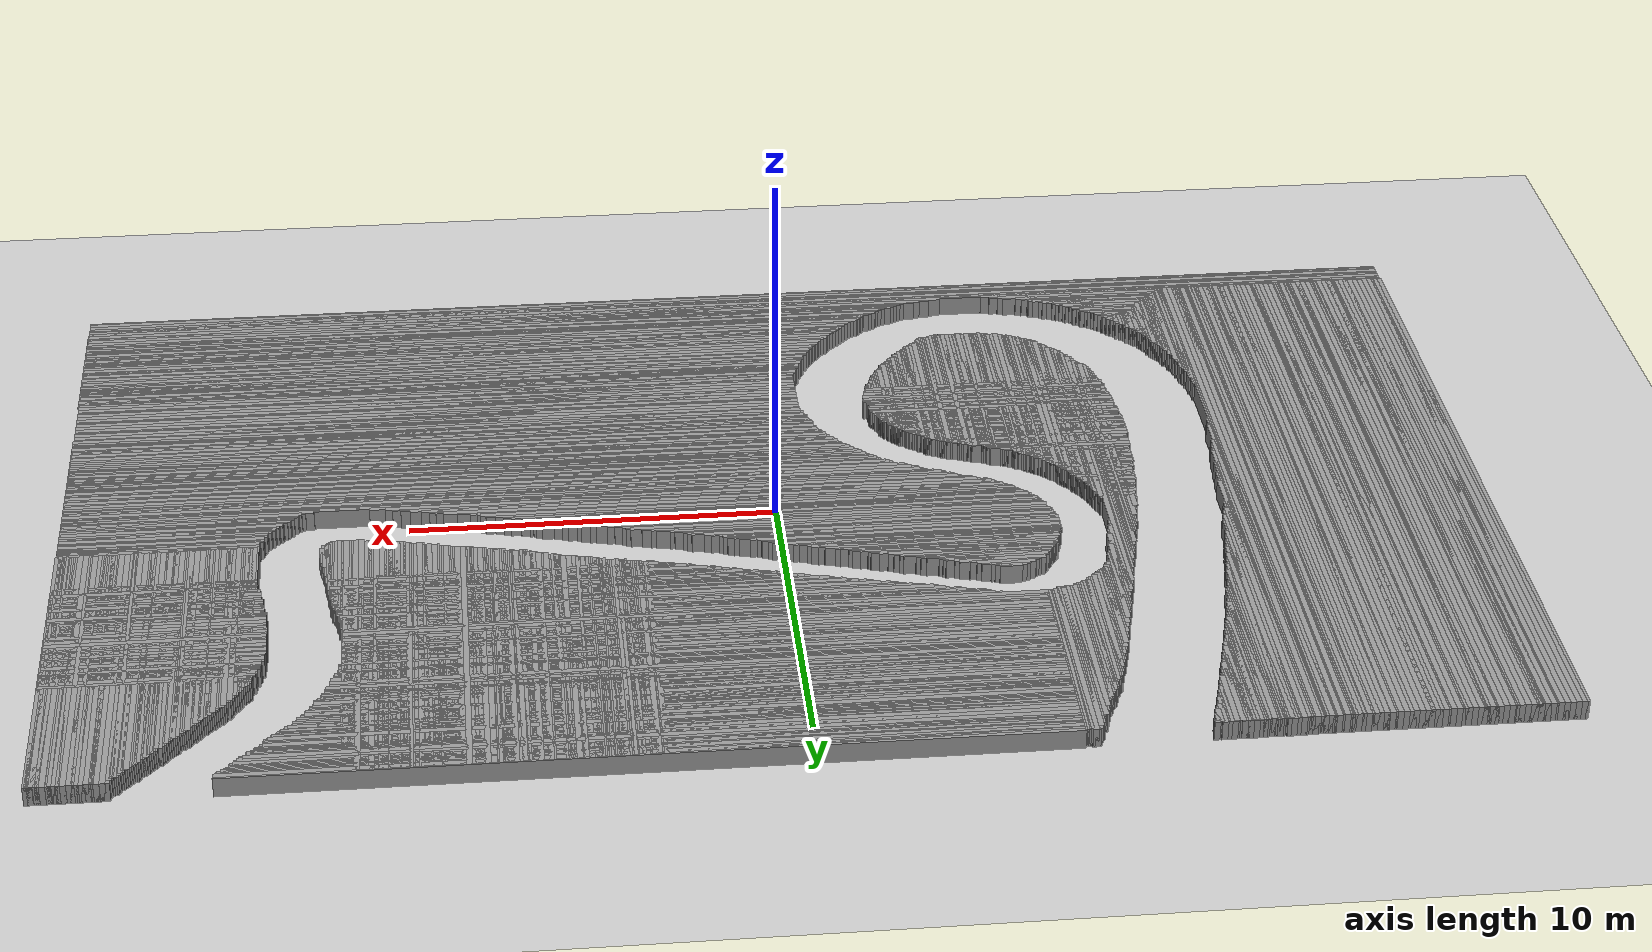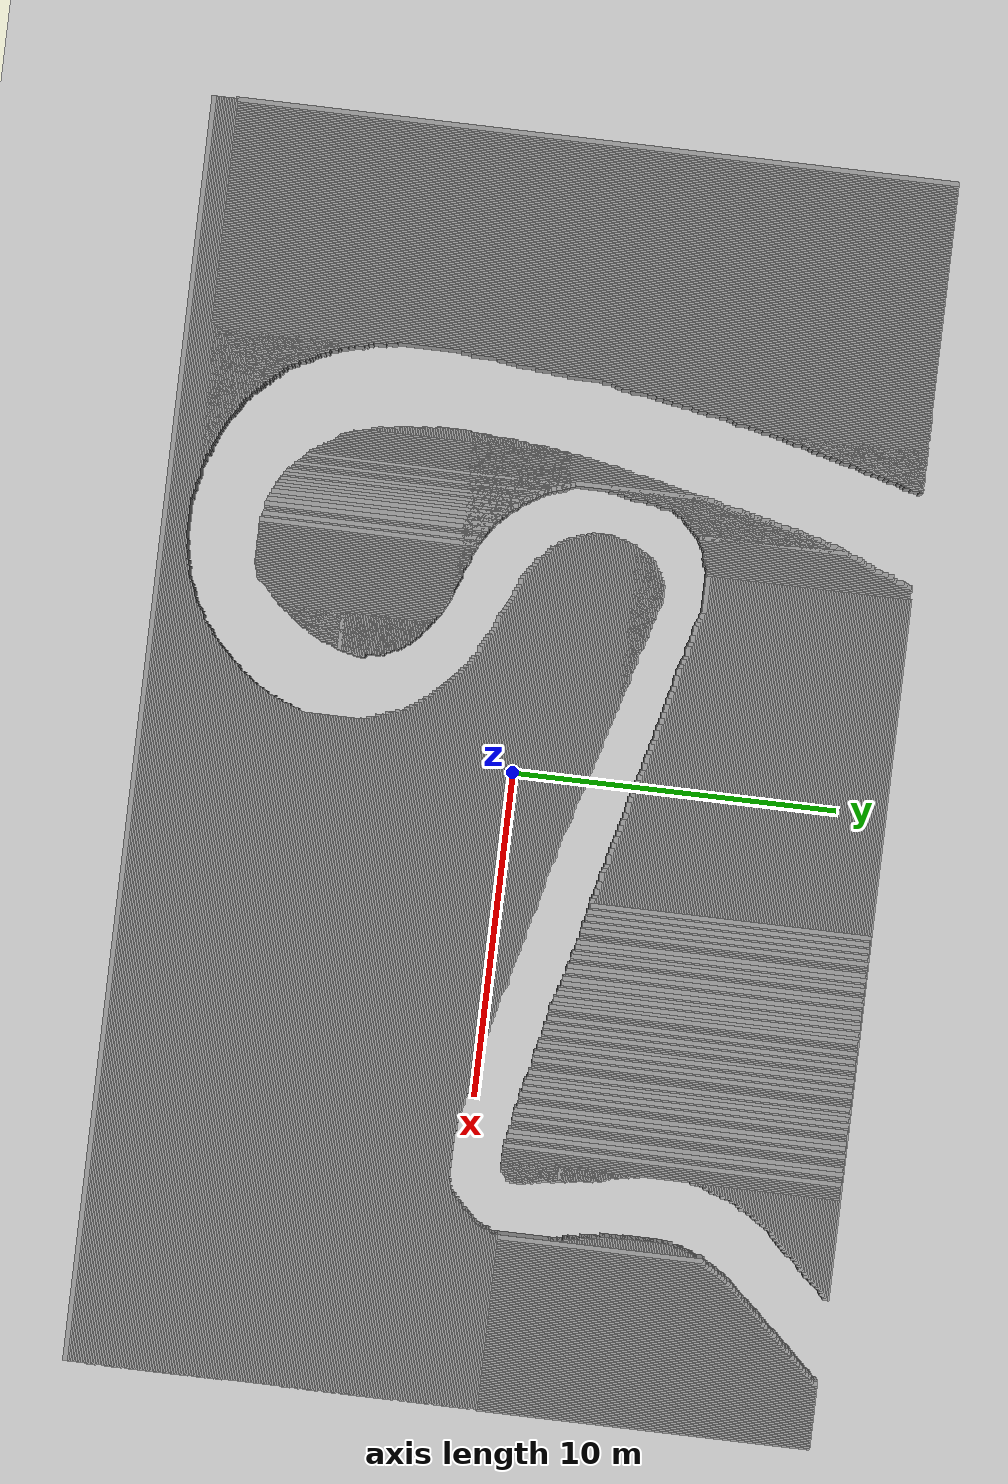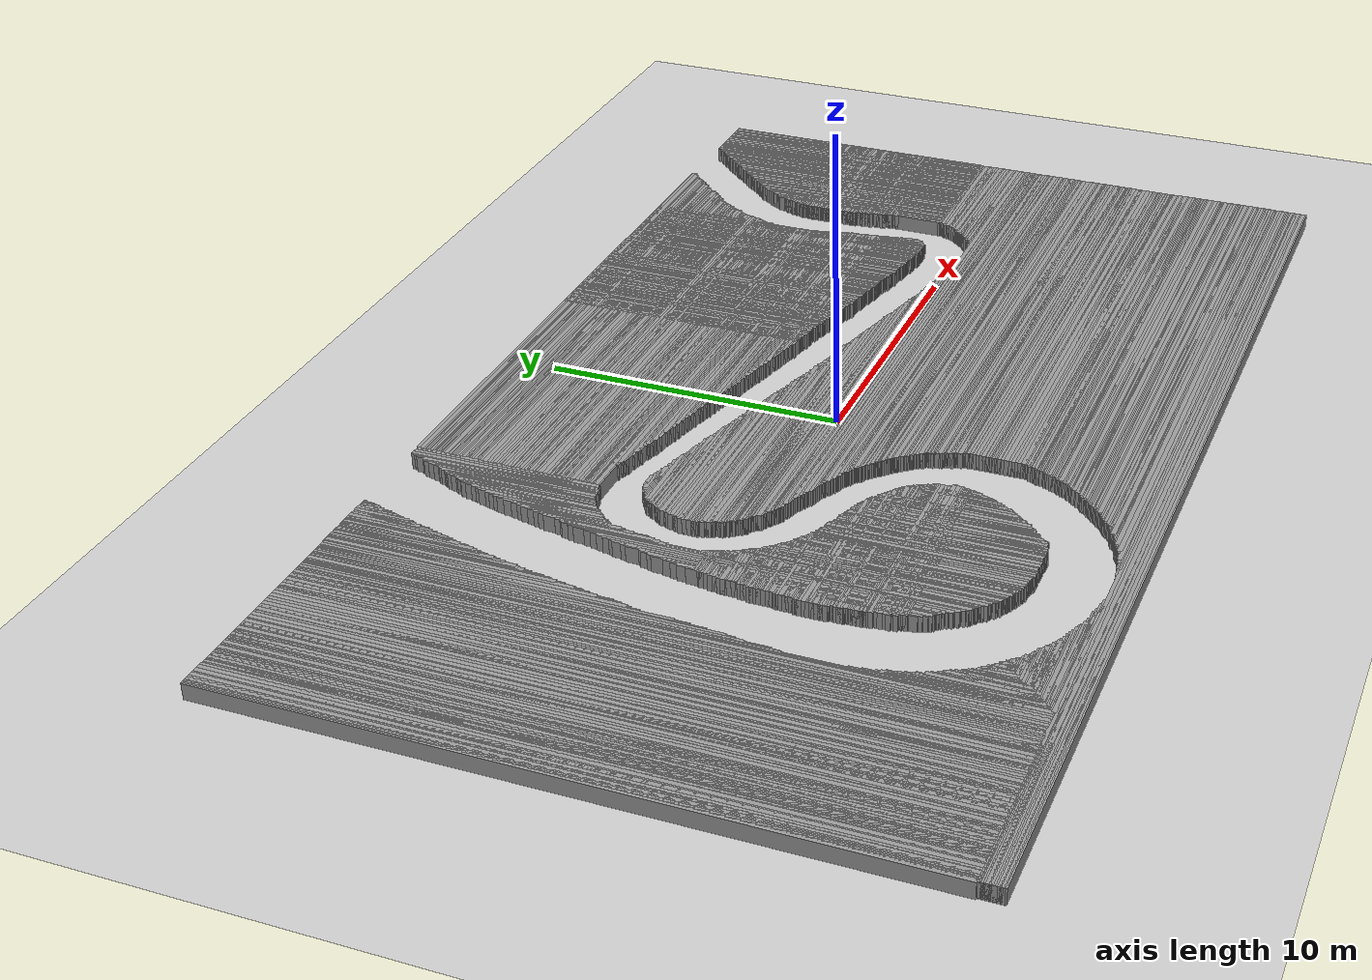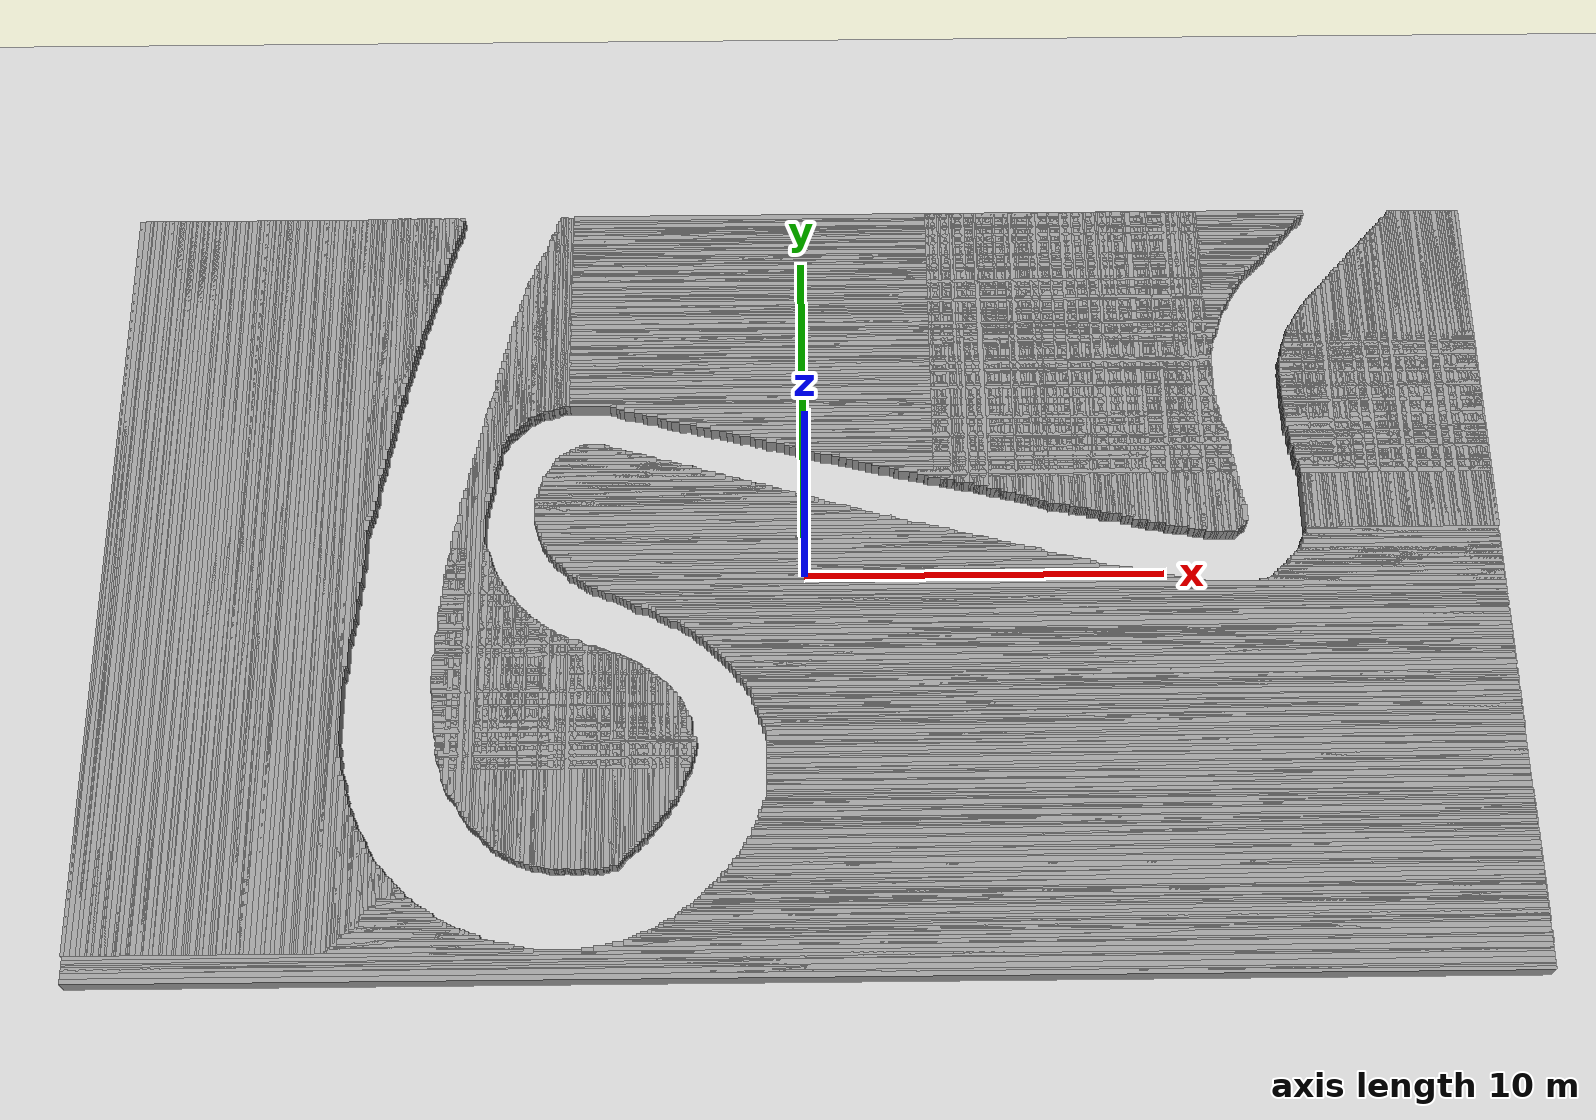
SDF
<sdf version="1.6">
  <world name="default">

     <plugin name="gazebo_ros_state" filename="libgazebo_ros_state.so">
      <ros>
        <namespace>/gazebo</namespace>
      </ros>

      <update_rate>1.0</update_rate>
    </plugin>

    <include>
      <uri>model://sun</uri>
    </include>
    <include>
      <uri>model://ground_plane</uri>
    </include>
    <physics type="ode">
      <real_time_update_rate>1000.0</real_time_update_rate>
      <max_step_size>0.001</max_step_size>
      <real_time_factor>1</real_time_factor>
      <ode>
        <solver>
          <type>quick</type>
          <iters>150</iters>
          <precon_iters>0</precon_iters>
          <sor>1.400000</sor>
          <use_dynamic_moi_rescaling>1</use_dynamic_moi_rescaling>
        </solver>
        <constraints>
          <cfm>0.00001</cfm>
          <erp>0.2</erp>
          <contact_max_correcting_vel>2000.000000</contact_max_correcting_vel>
          <contact_surface_layer>0.01000</contact_surface_layer>
        </constraints>
      </ode>
    </physics>
    <scene>
      <ambient>0.4 0.4 0.4 1</ambient>
      <background>0.7 0.7 0.7 1</background>
      <shadows>true</shadows>
    </scene>
    <gui fullscreen="0">
      <camera name="user_camera">
        <pose>0.0 0.0 17.0 -1.5708 1.5708 0</pose>
        <view_controller>orbit</view_controller>
      </camera>
    </gui>
    <model name="obstacle">
      <static>1</static>
      <pose frame="">0 0 0 0 0 0</pose>
      <link name="obstacle">
        <collision name="obstacle_1">
          <pose>-0.02499999999999858 -11.425 0 0 0 0</pose>
          <geometry>
            <box>
              <size>38.75 0.15 1.0</size>
            </box>
          </geometry>
        </collision>
        <visual name="obstacle_1">
          <pose>-0.02499999999999858 -11.425 0 0 0 0</pose>
          <geometry>
            <box>
              <size>38.75 0.15 1.0</size>
            </box>
          </geometry>
          <material>
            <script>
              <uri>file://media/materials/scripts/gazebo.material</uri>
              <name>Gazebo/Grey</name>
            </script>
            <ambient>1 1 1 1</ambient>
          </material>
        </visual>
        <collision name="obstacle_2">
          <pose>-0.02499999999999858 -11.375 0 0 0 0</pose>
          <geometry>
            <box>
              <size>38.75 0.15 1.0</size>
            </box>
          </geometry>
        </collision>
        <visual name="obstacle_2">
          <pose>-0.02499999999999858 -11.375 0 0 0 0</pose>
          <geometry>
            <box>
              <size>38.75 0.15 1.0</size>
            </box>
          </geometry>
          <material>
            <script>
              <uri>file://media/materials/scripts/gazebo.material</uri>
              <name>Gazebo/Grey</name>
            </script>
            <ambient>1 1 1 1</ambient>
          </material>
        </visual>
        <collision name="obstacle_3">
          <pose>-0.02499999999999858 -11.325000000000001 0 0 0 0</pose>
          <geometry>
            <box>
              <size>38.75 0.15 1.0</size>
            </box>
          </geometry>
        </collision>
        <visual name="obstacle_3">
          <pose>-0.02499999999999858 -11.325000000000001 0 0 0 0</pose>
          <geometry>
            <box>
              <size>38.75 0.15 1.0</size>
            </box>
          </geometry>
          <material>
            <script>
              <uri>file://media/materials/scripts/gazebo.material</uri>
              <name>Gazebo/Grey</name>
            </script>
            <ambient>1 1 1 1</ambient>
          </material>
        </visual>
        <collision name="obstacle_4">
          <pose>-0.02499999999999858 -11.275 0 0 0 0</pose>
          <geometry>
            <box>
              <size>38.75 0.15 1.0</size>
            </box>
          </geometry>
        </collision>
        <visual name="obstacle_4">
          <pose>-0.02499999999999858 -11.275 0 0 0 0</pose>
          <geometry>
            <box>
              <size>38.75 0.15 1.0</size>
            </box>
          </geometry>
          <material>
            <script>
              <uri>file://media/materials/scripts/gazebo.material</uri>
              <name>Gazebo/Grey</name>
            </script>
            <ambient>1 1 1 1</ambient>
          </material>
        </visual>
        <collision name="obstacle_5">
          <pose>-0.02499999999999858 -11.225000000000001 0 0 0 0</pose>
          <geometry>
            <box>
              <size>38.75 0.15 1.0</size>
            </box>
          </geometry>
        </collision>
        <visual name="obstacle_5">
          <pose>-0.02499999999999858 -11.225000000000001 0 0 0 0</pose>
          <geometry>
            <box>
              <size>38.75 0.15 1.0</size>
            </box>
          </geometry>
          <material>
            <script>
              <uri>file://media/materials/scripts/gazebo.material</uri>
              <name>Gazebo/Grey</name>
            </script>
            <ambient>1 1 1 1</ambient>
          </material>
        </visual>
        <collision name="obstacle_6">
          <pose>-0.02499999999999858 -11.175 0 0 0 0</pose>
          <geometry>
            <box>
              <size>38.75 0.15 1.0</size>
            </box>
          </geometry>
        </collision>
        <visual name="obstacle_6">
          <pose>-0.02499999999999858 -11.175 0 0 0 0</pose>
          <geometry>
            <box>
              <size>38.75 0.15 1.0</size>
            </box>
          </geometry>
          <material>
            <script>
              <uri>file://media/materials/scripts/gazebo.material</uri>
              <name>Gazebo/Grey</name>
            </script>
            <ambient>1 1 1 1</ambient>
          </material>
        </visual>
        <collision name="obstacle_7">
          <pose>-0.02499999999999858 -11.125 0 0 0 0</pose>
          <geometry>
            <box>
              <size>38.75 0.15 1.0</size>
            </box>
          </geometry>
        </collision>
        <visual name="obstacle_7">
          <pose>-0.02499999999999858 -11.125 0 0 0 0</pose>
          <geometry>
            <box>
              <size>38.75 0.15 1.0</size>
            </box>
          </geometry>
          <material>
            <script>
              <uri>file://media/materials/scripts/gazebo.material</uri>
              <name>Gazebo/Grey</name>
            </script>
            <ambient>1 1 1 1</ambient>
          </material>
        </visual>
        <collision name="obstacle_8">
          <pose>-0.02499999999999858 -11.075000000000001 0 0 0 0</pose>
          <geometry>
            <box>
              <size>38.75 0.15 1.0</size>
            </box>
          </geometry>
        </collision>
        <visual name="obstacle_8">
          <pose>-0.02499999999999858 -11.075000000000001 0 0 0 0</pose>
          <geometry>
            <box>
              <size>38.75 0.15 1.0</size>
            </box>
          </geometry>
          <material>
            <script>
              <uri>file://media/materials/scripts/gazebo.material</uri>
              <name>Gazebo/Grey</name>
            </script>
            <ambient>1 1 1 1</ambient>
          </material>
        </visual>
        <collision name="obstacle_9">
          <pose>-0.02499999999999858 -11.025 0 0 0 0</pose>
          <geometry>
            <box>
              <size>38.75 0.15 1.0</size>
            </box>
          </geometry>
        </collision>
        <visual name="obstacle_9">
          <pose>-0.02499999999999858 -11.025 0 0 0 0</pose>
          <geometry>
            <box>
              <size>38.75 0.15 1.0</size>
            </box>
          </geometry>
          <material>
            <script>
              <uri>file://media/materials/scripts/gazebo.material</uri>
              <name>Gazebo/Grey</name>
            </script>
            <ambient>1 1 1 1</ambient>
          </material>
        </visual>
        <collision name="obstacle_10">
          <pose>-0.02499999999999858 -10.975000000000001 0 0 0 0</pose>
          <geometry>
            <box>
              <size>38.75 0.15 1.0</size>
            </box>
          </geometry>
        </collision>
        <visual name="obstacle_10">
          <pose>-0.02499999999999858 -10.975000000000001 0 0 0 0</pose>
          <geometry>
            <box>
              <size>38.75 0.15 1.0</size>
            </box>
          </geometry>
          <material>
            <script>
              <uri>file://media/materials/scripts/gazebo.material</uri>
              <name>Gazebo/Grey</name>
            </script>
            <ambient>1 1 1 1</ambient>
          </material>
        </visual>
        <collision name="obstacle_11">
          <pose>-0.02499999999999858 -10.925 0 0 0 0</pose>
          <geometry>
            <box>
              <size>38.75 0.15 1.0</size>
            </box>
          </geometry>
        </collision>
        <visual name="obstacle_11">
          <pose>-0.02499999999999858 -10.925 0 0 0 0</pose>
          <geometry>
            <box>
              <size>38.75 0.15 1.0</size>
            </box>
          </geometry>
          <material>
            <script>
              <uri>file://media/materials/scripts/gazebo.material</uri>
              <name>Gazebo/Grey</name>
            </script>
            <ambient>1 1 1 1</ambient>
          </material>
        </visual>
        <collision name="obstacle_12">
          <pose>-0.02499999999999858 -10.875 0 0 0 0</pose>
          <geometry>
            <box>
              <size>38.75 0.15 1.0</size>
            </box>
          </geometry>
        </collision>
        <visual name="obstacle_12">
          <pose>-0.02499999999999858 -10.875 0 0 0 0</pose>
          <geometry>
            <box>
              <size>38.75 0.15 1.0</size>
            </box>
          </geometry>
          <material>
            <script>
              <uri>file://media/materials/scripts/gazebo.material</uri>
              <name>Gazebo/Grey</name>
            </script>
            <ambient>1 1 1 1</ambient>
          </material>
        </visual>
        <collision name="obstacle_13">
          <pose>-0.02499999999999858 -10.825000000000001 0 0 0 0</pose>
          <geometry>
            <box>
              <size>38.75 0.15 1.0</size>
            </box>
          </geometry>
        </collision>
        <visual name="obstacle_13">
          <pose>-0.02499999999999858 -10.825000000000001 0 0 0 0</pose>
          <geometry>
            <box>
              <size>38.75 0.15 1.0</size>
            </box>
          </geometry>
          <material>
            <script>
              <uri>file://media/materials/scripts/gazebo.material</uri>
              <name>Gazebo/Grey</name>
            </script>
            <ambient>1 1 1 1</ambient>
          </material>
        </visual>
        <collision name="obstacle_14">
          <pose>-0.02499999999999858 -10.775 0 0 0 0</pose>
          <geometry>
            <box>
              <size>38.75 0.15 1.0</size>
            </box>
          </geometry>
        </collision>
        <visual name="obstacle_14">
          <pose>-0.02499999999999858 -10.775 0 0 0 0</pose>
          <geometry>
            <box>
              <size>38.75 0.15 1.0</size>
            </box>
          </geometry>
          <material>
            <script>
              <uri>file://media/materials/scripts/gazebo.material</uri>
              <name>Gazebo/Grey</name>
            </script>
            <ambient>1 1 1 1</ambient>
          </material>
        </visual>
        <collision name="obstacle_15">
          <pose>-19.375 0.3249999999999993 0 0 0 1.5708</pose>
          <geometry>
            <box>
              <size>22.150000000000002 0.15 1.0</size>
            </box>
          </geometry>
        </collision>
        <visual name="obstacle_15">
          <pose>-19.375 0.3249999999999993 0 0 0 1.5708</pose>
          <geometry>
            <box>
              <size>22.150000000000002 0.15 1.0</size>
            </box>
          </geometry>
          <material>
            <script>
              <uri>file://media/materials/scripts/gazebo.material</uri>
              <name>Gazebo/Grey</name>
            </script>
            <ambient>1 1 1 1</ambient>
          </material>
        </visual>
        <collision name="obstacle_16">
          <pose>-19.325 0.3249999999999993 0 0 0 1.5708</pose>
          <geometry>
            <box>
              <size>22.150000000000002 0.15 1.0</size>
            </box>
          </geometry>
        </collision>
        <visual name="obstacle_16">
          <pose>-19.325 0.3249999999999993 0 0 0 1.5708</pose>
          <geometry>
            <box>
              <size>22.150000000000002 0.15 1.0</size>
            </box>
          </geometry>
          <material>
            <script>
              <uri>file://media/materials/scripts/gazebo.material</uri>
              <name>Gazebo/Grey</name>
            </script>
            <ambient>1 1 1 1</ambient>
          </material>
        </visual>
        <collision name="obstacle_17">
          <pose>-19.275 0.3249999999999993 0 0 0 1.5708</pose>
          <geometry>
            <box>
              <size>22.150000000000002 0.15 1.0</size>
            </box>
          </geometry>
        </collision>
        <visual name="obstacle_17">
          <pose>-19.275 0.3249999999999993 0 0 0 1.5708</pose>
          <geometry>
            <box>
              <size>22.150000000000002 0.15 1.0</size>
            </box>
          </geometry>
          <material>
            <script>
              <uri>file://media/materials/scripts/gazebo.material</uri>
              <name>Gazebo/Grey</name>
            </script>
            <ambient>1 1 1 1</ambient>
          </material>
        </visual>
        <collision name="obstacle_18">
          <pose>-19.225 0.3249999999999993 0 0 0 1.5708</pose>
          <geometry>
            <box>
              <size>22.150000000000002 0.15 1.0</size>
            </box>
          </geometry>
        </collision>
        <visual name="obstacle_18">
          <pose>-19.225 0.3249999999999993 0 0 0 1.5708</pose>
          <geometry>
            <box>
              <size>22.150000000000002 0.15 1.0</size>
            </box>
          </geometry>
          <material>
            <script>
              <uri>file://media/materials/scripts/gazebo.material</uri>
              <name>Gazebo/Grey</name>
            </script>
            <ambient>1 1 1 1</ambient>
          </material>
        </visual>
        <collision name="obstacle_19">
          <pose>-19.175 0.3249999999999993 0 0 0 1.5708</pose>
          <geometry>
            <box>
              <size>22.150000000000002 0.15 1.0</size>
            </box>
          </geometry>
        </collision>
        <visual name="obstacle_19">
          <pose>-19.175 0.3249999999999993 0 0 0 1.5708</pose>
          <geometry>
            <box>
              <size>22.150000000000002 0.15 1.0</size>
            </box>
          </geometry>
          <material>
            <script>
              <uri>file://media/materials/scripts/gazebo.material</uri>
              <name>Gazebo/Grey</name>
            </script>
            <ambient>1 1 1 1</ambient>
          </material>
        </visual>
        <collision name="obstacle_20">
          <pose>-19.125 0.3249999999999993 0 0 0 1.5708</pose>
          <geometry>
            <box>
              <size>22.150000000000002 0.15 1.0</size>
            </box>
          </geometry>
        </collision>
        <visual name="obstacle_20">
          <pose>-19.125 0.3249999999999993 0 0 0 1.5708</pose>
          <geometry>
            <box>
              <size>22.150000000000002 0.15 1.0</size>
            </box>
          </geometry>
          <material>
            <script>
              <uri>file://media/materials/scripts/gazebo.material</uri>
              <name>Gazebo/Grey</name>
            </script>
            <ambient>1 1 1 1</ambient>
          </material>
        </visual>
        <collision name="obstacle_21">
          <pose>-19.075 0.3249999999999993 0 0 0 1.5708</pose>
          <geometry>
            <box>
              <size>22.150000000000002 0.15 1.0</size>
            </box>
          </geometry>
        </collision>
        <visual name="obstacle_21">
          <pose>-19.075 0.3249999999999993 0 0 0 1.5708</pose>
          <geometry>
            <box>
              <size>22.150000000000002 0.15 1.0</size>
            </box>
          </geometry>
          <material>
            <script>
              <uri>file://media/materials/scripts/gazebo.material</uri>
              <name>Gazebo/Grey</name>
            </script>
            <ambient>1 1 1 1</ambient>
          </material>
        </visual>
        <collision name="obstacle_22">
          <pose>-19.025 0.3249999999999993 0 0 0 1.5708</pose>
          <geometry>
            <box>
              <size>22.150000000000002 0.15 1.0</size>
            </box>
          </geometry>
        </collision>
        <visual name="obstacle_22">
          <pose>-19.025 0.3249999999999993 0 0 0 1.5708</pose>
          <geometry>
            <box>
              <size>22.150000000000002 0.15 1.0</size>
            </box>
          </geometry>
          <material>
            <script>
              <uri>file://media/materials/scripts/gazebo.material</uri>
              <name>Gazebo/Grey</name>
            </script>
            <ambient>1 1 1 1</ambient>
          </material>
        </visual>
        <collision name="obstacle_23">
          <pose>-18.975 0.3249999999999993 0 0 0 1.5708</pose>
          <geometry>
            <box>
              <size>22.150000000000002 0.15 1.0</size>
            </box>
          </geometry>
        </collision>
        <visual name="obstacle_23">
          <pose>-18.975 0.3249999999999993 0 0 0 1.5708</pose>
          <geometry>
            <box>
              <size>22.150000000000002 0.15 1.0</size>
            </box>
          </geometry>
          <material>
            <script>
              <uri>file://media/materials/scripts/gazebo.material</uri>
              <name>Gazebo/Grey</name>
            </script>
            <ambient>1 1 1 1</ambient>
          </material>
        </visual>
        <collision name="obstacle_24">
          <pose>-18.925 0.3249999999999993 0 0 0 1.5708</pose>
          <geometry>
            <box>
              <size>22.150000000000002 0.15 1.0</size>
            </box>
          </geometry>
        </collision>
        <visual name="obstacle_24">
          <pose>-18.925 0.3249999999999993 0 0 0 1.5708</pose>
          <geometry>
            <box>
              <size>22.150000000000002 0.15 1.0</size>
            </box>
          </geometry>
          <material>
            <script>
              <uri>file://media/materials/scripts/gazebo.material</uri>
              <name>Gazebo/Grey</name>
            </script>
            <ambient>1 1 1 1</ambient>
          </material>
        </visual>
        <collision name="obstacle_25">
          <pose>-18.875 0.3249999999999993 0 0 0 1.5708</pose>
          <geometry>
            <box>
              <size>22.150000000000002 0.15 1.0</size>
            </box>
          </geometry>
        </collision>
        <visual name="obstacle_25">
          <pose>-18.875 0.3249999999999993 0 0 0 1.5708</pose>
          <geometry>
            <box>
              <size>22.150000000000002 0.15 1.0</size>
            </box>
          </geometry>
          <material>
            <script>
              <uri>file://media/materials/scripts/gazebo.material</uri>
              <name>Gazebo/Grey</name>
            </script>
            <ambient>1 1 1 1</ambient>
          </material>
        </visual>
        <collision name="obstacle_26">
          <pose>-18.825 0.3249999999999993 0 0 0 1.5708</pose>
          <geometry>
            <box>
              <size>22.150000000000002 0.15 1.0</size>
            </box>
          </geometry>
        </collision>
        <visual name="obstacle_26">
          <pose>-18.825 0.3249999999999993 0 0 0 1.5708</pose>
          <geometry>
            <box>
              <size>22.150000000000002 0.15 1.0</size>
            </box>
          </geometry>
          <material>
            <script>
              <uri>file://media/materials/scripts/gazebo.material</uri>
              <name>Gazebo/Grey</name>
            </script>
            <ambient>1 1 1 1</ambient>
          </material>
        </visual>
        <collision name="obstacle_27">
          <pose>-18.775 0.3249999999999993 0 0 0 1.5708</pose>
          <geometry>
            <box>
              <size>22.150000000000002 0.15 1.0</size>
            </box>
          </geometry>
        </collision>
        <visual name="obstacle_27">
          <pose>-18.775 0.3249999999999993 0 0 0 1.5708</pose>
          <geometry>
            <box>
              <size>22.150000000000002 0.15 1.0</size>
            </box>
          </geometry>
          <material>
            <script>
              <uri>file://media/materials/scripts/gazebo.material</uri>
              <name>Gazebo/Grey</name>
            </script>
            <ambient>1 1 1 1</ambient>
          </material>
        </visual>
        <collision name="obstacle_28">
          <pose>-18.725 0.3249999999999993 0 0 0 1.5708</pose>
          <geometry>
            <box>
              <size>22.150000000000002 0.15 1.0</size>
            </box>
          </geometry>
        </collision>
        <visual name="obstacle_28">
          <pose>-18.725 0.3249999999999993 0 0 0 1.5708</pose>
          <geometry>
            <box>
              <size>22.150000000000002 0.15 1.0</size>
            </box>
          </geometry>
          <material>
            <script>
              <uri>file://media/materials/scripts/gazebo.material</uri>
              <name>Gazebo/Grey</name>
            </script>
            <ambient>1 1 1 1</ambient>
          </material>
        </visual>
        <collision name="obstacle_29">
          <pose>-18.675 0.3249999999999993 0 0 0 1.5708</pose>
          <geometry>
            <box>
              <size>22.150000000000002 0.15 1.0</size>
            </box>
          </geometry>
        </collision>
        <visual name="obstacle_29">
          <pose>-18.675 0.3249999999999993 0 0 0 1.5708</pose>
          <geometry>
            <box>
              <size>22.150000000000002 0.15 1.0</size>
            </box>
          </geometry>
          <material>
            <script>
              <uri>file://media/materials/scripts/gazebo.material</uri>
              <name>Gazebo/Grey</name>
            </script>
            <ambient>1 1 1 1</ambient>
          </material>
        </visual>
        <collision name="obstacle_30">
          <pose>-18.625 0.3249999999999993 0 0 0 1.5708</pose>
          <geometry>
            <box>
              <size>22.150000000000002 0.15 1.0</size>
            </box>
          </geometry>
        </collision>
        <visual name="obstacle_30">
          <pose>-18.625 0.3249999999999993 0 0 0 1.5708</pose>
          <geometry>
            <box>
              <size>22.150000000000002 0.15 1.0</size>
            </box>
          </geometry>
          <material>
            <script>
              <uri>file://media/materials/scripts/gazebo.material</uri>
              <name>Gazebo/Grey</name>
            </script>
            <ambient>1 1 1 1</ambient>
          </material>
        </visual>
        <collision name="obstacle_31">
          <pose>-18.575 0.3249999999999993 0 0 0 1.5708</pose>
          <geometry>
            <box>
              <size>22.150000000000002 0.15 1.0</size>
            </box>
          </geometry>
        </collision>
        <visual name="obstacle_31">
          <pose>-18.575 0.3249999999999993 0 0 0 1.5708</pose>
          <geometry>
            <box>
              <size>22.150000000000002 0.15 1.0</size>
            </box>
          </geometry>
          <material>
            <script>
              <uri>file://media/materials/scripts/gazebo.material</uri>
              <name>Gazebo/Grey</name>
            </script>
            <ambient>1 1 1 1</ambient>
          </material>
        </visual>
        <collision name="obstacle_32">
          <pose>-18.525 0.3249999999999993 0 0 0 1.5708</pose>
          <geometry>
            <box>
              <size>22.150000000000002 0.15 1.0</size>
            </box>
          </geometry>
        </collision>
        <visual name="obstacle_32">
          <pose>-18.525 0.3249999999999993 0 0 0 1.5708</pose>
          <geometry>
            <box>
              <size>22.150000000000002 0.15 1.0</size>
            </box>
          </geometry>
          <material>
            <script>
              <uri>file://media/materials/scripts/gazebo.material</uri>
              <name>Gazebo/Grey</name>
            </script>
            <ambient>1 1 1 1</ambient>
          </material>
        </visual>
        <collision name="obstacle_33">
          <pose>-18.475 0.3249999999999993 0 0 0 1.5708</pose>
          <geometry>
            <box>
              <size>22.150000000000002 0.15 1.0</size>
            </box>
          </geometry>
        </collision>
        <visual name="obstacle_33">
          <pose>-18.475 0.3249999999999993 0 0 0 1.5708</pose>
          <geometry>
            <box>
              <size>22.150000000000002 0.15 1.0</size>
            </box>
          </geometry>
          <material>
            <script>
              <uri>file://media/materials/scripts/gazebo.material</uri>
              <name>Gazebo/Grey</name>
            </script>
            <ambient>1 1 1 1</ambient>
          </material>
        </visual>
        <collision name="obstacle_34">
          <pose>-18.425 0.3249999999999993 0 0 0 1.5708</pose>
          <geometry>
            <box>
              <size>22.150000000000002 0.15 1.0</size>
            </box>
          </geometry>
        </collision>
        <visual name="obstacle_34">
          <pose>-18.425 0.3249999999999993 0 0 0 1.5708</pose>
          <geometry>
            <box>
              <size>22.150000000000002 0.15 1.0</size>
            </box>
          </geometry>
          <material>
            <script>
              <uri>file://media/materials/scripts/gazebo.material</uri>
              <name>Gazebo/Grey</name>
            </script>
            <ambient>1 1 1 1</ambient>
          </material>
        </visual>
        <collision name="obstacle_35">
          <pose>-18.375 0.3249999999999993 0 0 0 1.5708</pose>
          <geometry>
            <box>
              <size>22.150000000000002 0.15 1.0</size>
            </box>
          </geometry>
        </collision>
        <visual name="obstacle_35">
          <pose>-18.375 0.3249999999999993 0 0 0 1.5708</pose>
          <geometry>
            <box>
              <size>22.150000000000002 0.15 1.0</size>
            </box>
          </geometry>
          <material>
            <script>
              <uri>file://media/materials/scripts/gazebo.material</uri>
              <name>Gazebo/Grey</name>
            </script>
            <ambient>1 1 1 1</ambient>
          </material>
        </visual>
        <collision name="obstacle_36">
          <pose>-18.325 0.3249999999999993 0 0 0 1.5708</pose>
          <geometry>
            <box>
              <size>22.150000000000002 0.15 1.0</size>
            </box>
          </geometry>
        </collision>
        <visual name="obstacle_36">
          <pose>-18.325 0.3249999999999993 0 0 0 1.5708</pose>
          <geometry>
            <box>
              <size>22.150000000000002 0.15 1.0</size>
            </box>
          </geometry>
          <material>
            <script>
              <uri>file://media/materials/scripts/gazebo.material</uri>
              <name>Gazebo/Grey</name>
            </script>
            <ambient>1 1 1 1</ambient>
          </material>
        </visual>
        <collision name="obstacle_37">
          <pose>-18.275 0.3249999999999993 0 0 0 1.5708</pose>
          <geometry>
            <box>
              <size>22.150000000000002 0.15 1.0</size>
            </box>
          </geometry>
        </collision>
        <visual name="obstacle_37">
          <pose>-18.275 0.3249999999999993 0 0 0 1.5708</pose>
          <geometry>
            <box>
              <size>22.150000000000002 0.15 1.0</size>
            </box>
          </geometry>
          <material>
            <script>
              <uri>file://media/materials/scripts/gazebo.material</uri>
              <name>Gazebo/Grey</name>
            </script>
            <ambient>1 1 1 1</ambient>
          </material>
        </visual>
        <collision name="obstacle_38">
          <pose>-18.225 0.3249999999999993 0 0 0 1.5708</pose>
          <geometry>
            <box>
              <size>22.150000000000002 0.15 1.0</size>
            </box>
          </geometry>
        </collision>
        <visual name="obstacle_38">
          <pose>-18.225 0.3249999999999993 0 0 0 1.5708</pose>
          <geometry>
            <box>
              <size>22.150000000000002 0.15 1.0</size>
            </box>
          </geometry>
          <material>
            <script>
              <uri>file://media/materials/scripts/gazebo.material</uri>
              <name>Gazebo/Grey</name>
            </script>
            <ambient>1 1 1 1</ambient>
          </material>
        </visual>
        <collision name="obstacle_39">
          <pose>-18.175 0.3249999999999993 0 0 0 1.5708</pose>
          <geometry>
            <box>
              <size>22.150000000000002 0.15 1.0</size>
            </box>
          </geometry>
        </collision>
        <visual name="obstacle_39">
          <pose>-18.175 0.3249999999999993 0 0 0 1.5708</pose>
          <geometry>
            <box>
              <size>22.150000000000002 0.15 1.0</size>
            </box>
          </geometry>
          <material>
            <script>
              <uri>file://media/materials/scripts/gazebo.material</uri>
              <name>Gazebo/Grey</name>
            </script>
            <ambient>1 1 1 1</ambient>
          </material>
        </visual>
        <collision name="obstacle_40">
          <pose>-18.125 0.3249999999999993 0 0 0 1.5708</pose>
          <geometry>
            <box>
              <size>22.150000000000002 0.15 1.0</size>
            </box>
          </geometry>
        </collision>
        <visual name="obstacle_40">
          <pose>-18.125 0.3249999999999993 0 0 0 1.5708</pose>
          <geometry>
            <box>
              <size>22.150000000000002 0.15 1.0</size>
            </box>
          </geometry>
          <material>
            <script>
              <uri>file://media/materials/scripts/gazebo.material</uri>
              <name>Gazebo/Grey</name>
            </script>
            <ambient>1 1 1 1</ambient>
          </material>
        </visual>
        <collision name="obstacle_41">
          <pose>-18.075 0.3249999999999993 0 0 0 1.5708</pose>
          <geometry>
            <box>
              <size>22.150000000000002 0.15 1.0</size>
            </box>
          </geometry>
        </collision>
        <visual name="obstacle_41">
          <pose>-18.075 0.3249999999999993 0 0 0 1.5708</pose>
          <geometry>
            <box>
              <size>22.150000000000002 0.15 1.0</size>
            </box>
          </geometry>
          <material>
            <script>
              <uri>file://media/materials/scripts/gazebo.material</uri>
              <name>Gazebo/Grey</name>
            </script>
            <ambient>1 1 1 1</ambient>
          </material>
        </visual>
        <collision name="obstacle_42">
          <pose>-18.025 0.3249999999999993 0 0 0 1.5708</pose>
          <geometry>
            <box>
              <size>22.150000000000002 0.15 1.0</size>
            </box>
          </geometry>
        </collision>
        <visual name="obstacle_42">
          <pose>-18.025 0.3249999999999993 0 0 0 1.5708</pose>
          <geometry>
            <box>
              <size>22.150000000000002 0.15 1.0</size>
            </box>
          </geometry>
          <material>
            <script>
              <uri>file://media/materials/scripts/gazebo.material</uri>
              <name>Gazebo/Grey</name>
            </script>
            <ambient>1 1 1 1</ambient>
          </material>
        </visual>
        <collision name="obstacle_43">
          <pose>-17.975 0.3249999999999993 0 0 0 1.5708</pose>
          <geometry>
            <box>
              <size>22.150000000000002 0.15 1.0</size>
            </box>
          </geometry>
        </collision>
        <visual name="obstacle_43">
          <pose>-17.975 0.3249999999999993 0 0 0 1.5708</pose>
          <geometry>
            <box>
              <size>22.150000000000002 0.15 1.0</size>
            </box>
          </geometry>
          <material>
            <script>
              <uri>file://media/materials/scripts/gazebo.material</uri>
              <name>Gazebo/Grey</name>
            </script>
            <ambient>1 1 1 1</ambient>
          </material>
        </visual>
        <collision name="obstacle_44">
          <pose>-17.925 0.3249999999999993 0 0 0 1.5708</pose>
          <geometry>
            <box>
              <size>22.150000000000002 0.15 1.0</size>
            </box>
          </geometry>
        </collision>
        <visual name="obstacle_44">
          <pose>-17.925 0.3249999999999993 0 0 0 1.5708</pose>
          <geometry>
            <box>
              <size>22.150000000000002 0.15 1.0</size>
            </box>
          </geometry>
          <material>
            <script>
              <uri>file://media/materials/scripts/gazebo.material</uri>
              <name>Gazebo/Grey</name>
            </script>
            <ambient>1 1 1 1</ambient>
          </material>
        </visual>
        <collision name="obstacle_45">
          <pose>-17.875 0.3249999999999993 0 0 0 1.5708</pose>
          <geometry>
            <box>
              <size>22.150000000000002 0.15 1.0</size>
            </box>
          </geometry>
        </collision>
        <visual name="obstacle_45">
          <pose>-17.875 0.3249999999999993 0 0 0 1.5708</pose>
          <geometry>
            <box>
              <size>22.150000000000002 0.15 1.0</size>
            </box>
          </geometry>
          <material>
            <script>
              <uri>file://media/materials/scripts/gazebo.material</uri>
              <name>Gazebo/Grey</name>
            </script>
            <ambient>1 1 1 1</ambient>
          </material>
        </visual>
        <collision name="obstacle_46">
          <pose>-17.825 0.3249999999999993 0 0 0 1.5708</pose>
          <geometry>
            <box>
              <size>22.150000000000002 0.15 1.0</size>
            </box>
          </geometry>
        </collision>
        <visual name="obstacle_46">
          <pose>-17.825 0.3249999999999993 0 0 0 1.5708</pose>
          <geometry>
            <box>
              <size>22.150000000000002 0.15 1.0</size>
            </box>
          </geometry>
          <material>
            <script>
              <uri>file://media/materials/scripts/gazebo.material</uri>
              <name>Gazebo/Grey</name>
            </script>
            <ambient>1 1 1 1</ambient>
          </material>
        </visual>
        <collision name="obstacle_47">
          <pose>-17.775 0.3249999999999993 0 0 0 1.5708</pose>
          <geometry>
            <box>
              <size>22.150000000000002 0.15 1.0</size>
            </box>
          </geometry>
        </collision>
        <visual name="obstacle_47">
          <pose>-17.775 0.3249999999999993 0 0 0 1.5708</pose>
          <geometry>
            <box>
              <size>22.150000000000002 0.15 1.0</size>
            </box>
          </geometry>
          <material>
            <script>
              <uri>file://media/materials/scripts/gazebo.material</uri>
              <name>Gazebo/Grey</name>
            </script>
            <ambient>1 1 1 1</ambient>
          </material>
        </visual>
        <collision name="obstacle_48">
          <pose>-17.725 0.3249999999999993 0 0 0 1.5708</pose>
          <geometry>
            <box>
              <size>22.150000000000002 0.15 1.0</size>
            </box>
          </geometry>
        </collision>
        <visual name="obstacle_48">
          <pose>-17.725 0.3249999999999993 0 0 0 1.5708</pose>
          <geometry>
            <box>
              <size>22.150000000000002 0.15 1.0</size>
            </box>
          </geometry>
          <material>
            <script>
              <uri>file://media/materials/scripts/gazebo.material</uri>
              <name>Gazebo/Grey</name>
            </script>
            <ambient>1 1 1 1</ambient>
          </material>
        </visual>
        <collision name="obstacle_49">
          <pose>-17.675 0.3249999999999993 0 0 0 1.5708</pose>
          <geometry>
            <box>
              <size>22.150000000000002 0.15 1.0</size>
            </box>
          </geometry>
        </collision>
        <visual name="obstacle_49">
          <pose>-17.675 0.3249999999999993 0 0 0 1.5708</pose>
          <geometry>
            <box>
              <size>22.150000000000002 0.15 1.0</size>
            </box>
          </geometry>
          <material>
            <script>
              <uri>file://media/materials/scripts/gazebo.material</uri>
              <name>Gazebo/Grey</name>
            </script>
            <ambient>1 1 1 1</ambient>
          </material>
        </visual>
        <collision name="obstacle_50">
          <pose>-17.625 0.3249999999999993 0 0 0 1.5708</pose>
          <geometry>
            <box>
              <size>22.150000000000002 0.15 1.0</size>
            </box>
          </geometry>
        </collision>
        <visual name="obstacle_50">
          <pose>-17.625 0.3249999999999993 0 0 0 1.5708</pose>
          <geometry>
            <box>
              <size>22.150000000000002 0.15 1.0</size>
            </box>
          </geometry>
          <material>
            <script>
              <uri>file://media/materials/scripts/gazebo.material</uri>
              <name>Gazebo/Grey</name>
            </script>
            <ambient>1 1 1 1</ambient>
          </material>
        </visual>
        <collision name="obstacle_51">
          <pose>-17.575 0.3249999999999993 0 0 0 1.5708</pose>
          <geometry>
            <box>
              <size>22.150000000000002 0.15 1.0</size>
            </box>
          </geometry>
        </collision>
        <visual name="obstacle_51">
          <pose>-17.575 0.3249999999999993 0 0 0 1.5708</pose>
          <geometry>
            <box>
              <size>22.150000000000002 0.15 1.0</size>
            </box>
          </geometry>
          <material>
            <script>
              <uri>file://media/materials/scripts/gazebo.material</uri>
              <name>Gazebo/Grey</name>
            </script>
            <ambient>1 1 1 1</ambient>
          </material>
        </visual>
        <collision name="obstacle_52">
          <pose>-17.525 0.3249999999999993 0 0 0 1.5708</pose>
          <geometry>
            <box>
              <size>22.150000000000002 0.15 1.0</size>
            </box>
          </geometry>
        </collision>
        <visual name="obstacle_52">
          <pose>-17.525 0.3249999999999993 0 0 0 1.5708</pose>
          <geometry>
            <box>
              <size>22.150000000000002 0.15 1.0</size>
            </box>
          </geometry>
          <material>
            <script>
              <uri>file://media/materials/scripts/gazebo.material</uri>
              <name>Gazebo/Grey</name>
            </script>
            <ambient>1 1 1 1</ambient>
          </material>
        </visual>
        <collision name="obstacle_53">
          <pose>-17.475 0.3249999999999993 0 0 0 1.5708</pose>
          <geometry>
            <box>
              <size>22.150000000000002 0.15 1.0</size>
            </box>
          </geometry>
        </collision>
        <visual name="obstacle_53">
          <pose>-17.475 0.3249999999999993 0 0 0 1.5708</pose>
          <geometry>
            <box>
              <size>22.150000000000002 0.15 1.0</size>
            </box>
          </geometry>
          <material>
            <script>
              <uri>file://media/materials/scripts/gazebo.material</uri>
              <name>Gazebo/Grey</name>
            </script>
            <ambient>1 1 1 1</ambient>
          </material>
        </visual>
        <collision name="obstacle_54">
          <pose>-17.425 0.3249999999999993 0 0 0 1.5708</pose>
          <geometry>
            <box>
              <size>22.150000000000002 0.15 1.0</size>
            </box>
          </geometry>
        </collision>
        <visual name="obstacle_54">
          <pose>-17.425 0.3249999999999993 0 0 0 1.5708</pose>
          <geometry>
            <box>
              <size>22.150000000000002 0.15 1.0</size>
            </box>
          </geometry>
          <material>
            <script>
              <uri>file://media/materials/scripts/gazebo.material</uri>
              <name>Gazebo/Grey</name>
            </script>
            <ambient>1 1 1 1</ambient>
          </material>
        </visual>
        <collision name="obstacle_55">
          <pose>-17.375 0.3249999999999993 0 0 0 1.5708</pose>
          <geometry>
            <box>
              <size>22.150000000000002 0.15 1.0</size>
            </box>
          </geometry>
        </collision>
        <visual name="obstacle_55">
          <pose>-17.375 0.3249999999999993 0 0 0 1.5708</pose>
          <geometry>
            <box>
              <size>22.150000000000002 0.15 1.0</size>
            </box>
          </geometry>
          <material>
            <script>
              <uri>file://media/materials/scripts/gazebo.material</uri>
              <name>Gazebo/Grey</name>
            </script>
            <ambient>1 1 1 1</ambient>
          </material>
        </visual>
        <collision name="obstacle_56">
          <pose>-17.325 0.3249999999999993 0 0 0 1.5708</pose>
          <geometry>
            <box>
              <size>22.150000000000002 0.15 1.0</size>
            </box>
          </geometry>
        </collision>
        <visual name="obstacle_56">
          <pose>-17.325 0.3249999999999993 0 0 0 1.5708</pose>
          <geometry>
            <box>
              <size>22.150000000000002 0.15 1.0</size>
            </box>
          </geometry>
          <material>
            <script>
              <uri>file://media/materials/scripts/gazebo.material</uri>
              <name>Gazebo/Grey</name>
            </script>
            <ambient>1 1 1 1</ambient>
          </material>
        </visual>
        <collision name="obstacle_57">
          <pose>-17.275 0.3249999999999993 0 0 0 1.5708</pose>
          <geometry>
            <box>
              <size>22.150000000000002 0.15 1.0</size>
            </box>
          </geometry>
        </collision>
        <visual name="obstacle_57">
          <pose>-17.275 0.3249999999999993 0 0 0 1.5708</pose>
          <geometry>
            <box>
              <size>22.150000000000002 0.15 1.0</size>
            </box>
          </geometry>
          <material>
            <script>
              <uri>file://media/materials/scripts/gazebo.material</uri>
              <name>Gazebo/Grey</name>
            </script>
            <ambient>1 1 1 1</ambient>
          </material>
        </visual>
        <collision name="obstacle_58">
          <pose>-17.225 0.3249999999999993 0 0 0 1.5708</pose>
          <geometry>
            <box>
              <size>22.150000000000002 0.15 1.0</size>
            </box>
          </geometry>
        </collision>
        <visual name="obstacle_58">
          <pose>-17.225 0.3249999999999993 0 0 0 1.5708</pose>
          <geometry>
            <box>
              <size>22.150000000000002 0.15 1.0</size>
            </box>
          </geometry>
          <material>
            <script>
              <uri>file://media/materials/scripts/gazebo.material</uri>
              <name>Gazebo/Grey</name>
            </script>
            <ambient>1 1 1 1</ambient>
          </material>
        </visual>
        <collision name="obstacle_59">
          <pose>-17.175 0.3249999999999993 0 0 0 1.5708</pose>
          <geometry>
            <box>
              <size>22.150000000000002 0.15 1.0</size>
            </box>
          </geometry>
        </collision>
        <visual name="obstacle_59">
          <pose>-17.175 0.3249999999999993 0 0 0 1.5708</pose>
          <geometry>
            <box>
              <size>22.150000000000002 0.15 1.0</size>
            </box>
          </geometry>
          <material>
            <script>
              <uri>file://media/materials/scripts/gazebo.material</uri>
              <name>Gazebo/Grey</name>
            </script>
            <ambient>1 1 1 1</ambient>
          </material>
        </visual>
        <collision name="obstacle_60">
          <pose>-17.125 0.3249999999999993 0 0 0 1.5708</pose>
          <geometry>
            <box>
              <size>22.150000000000002 0.15 1.0</size>
            </box>
          </geometry>
        </collision>
        <visual name="obstacle_60">
          <pose>-17.125 0.3249999999999993 0 0 0 1.5708</pose>
          <geometry>
            <box>
              <size>22.150000000000002 0.15 1.0</size>
            </box>
          </geometry>
          <material>
            <script>
              <uri>file://media/materials/scripts/gazebo.material</uri>
              <name>Gazebo/Grey</name>
            </script>
            <ambient>1 1 1 1</ambient>
          </material>
        </visual>
        <collision name="obstacle_61">
          <pose>-17.075 0.3249999999999993 0 0 0 1.5708</pose>
          <geometry>
            <box>
              <size>22.150000000000002 0.15 1.0</size>
            </box>
          </geometry>
        </collision>
        <visual name="obstacle_61">
          <pose>-17.075 0.3249999999999993 0 0 0 1.5708</pose>
          <geometry>
            <box>
              <size>22.150000000000002 0.15 1.0</size>
            </box>
          </geometry>
          <material>
            <script>
              <uri>file://media/materials/scripts/gazebo.material</uri>
              <name>Gazebo/Grey</name>
            </script>
            <ambient>1 1 1 1</ambient>
          </material>
        </visual>
        <collision name="obstacle_62">
          <pose>-17.025 0.3249999999999993 0 0 0 1.5708</pose>
          <geometry>
            <box>
              <size>22.150000000000002 0.15 1.0</size>
            </box>
          </geometry>
        </collision>
        <visual name="obstacle_62">
          <pose>-17.025 0.3249999999999993 0 0 0 1.5708</pose>
          <geometry>
            <box>
              <size>22.150000000000002 0.15 1.0</size>
            </box>
          </geometry>
          <material>
            <script>
              <uri>file://media/materials/scripts/gazebo.material</uri>
              <name>Gazebo/Grey</name>
            </script>
            <ambient>1 1 1 1</ambient>
          </material>
        </visual>
        <collision name="obstacle_63">
          <pose>-16.975 0.3249999999999993 0 0 0 1.5708</pose>
          <geometry>
            <box>
              <size>22.150000000000002 0.15 1.0</size>
            </box>
          </geometry>
        </collision>
        <visual name="obstacle_63">
          <pose>-16.975 0.3249999999999993 0 0 0 1.5708</pose>
          <geometry>
            <box>
              <size>22.150000000000002 0.15 1.0</size>
            </box>
          </geometry>
          <material>
            <script>
              <uri>file://media/materials/scripts/gazebo.material</uri>
              <name>Gazebo/Grey</name>
            </script>
            <ambient>1 1 1 1</ambient>
          </material>
        </visual>
        <collision name="obstacle_64">
          <pose>-16.925 0.3249999999999993 0 0 0 1.5708</pose>
          <geometry>
            <box>
              <size>22.150000000000002 0.15 1.0</size>
            </box>
          </geometry>
        </collision>
        <visual name="obstacle_64">
          <pose>-16.925 0.3249999999999993 0 0 0 1.5708</pose>
          <geometry>
            <box>
              <size>22.150000000000002 0.15 1.0</size>
            </box>
          </geometry>
          <material>
            <script>
              <uri>file://media/materials/scripts/gazebo.material</uri>
              <name>Gazebo/Grey</name>
            </script>
            <ambient>1 1 1 1</ambient>
          </material>
        </visual>
        <collision name="obstacle_65">
          <pose>-16.875 0.3249999999999993 0 0 0 1.5708</pose>
          <geometry>
            <box>
              <size>22.150000000000002 0.15 1.0</size>
            </box>
          </geometry>
        </collision>
        <visual name="obstacle_65">
          <pose>-16.875 0.3249999999999993 0 0 0 1.5708</pose>
          <geometry>
            <box>
              <size>22.150000000000002 0.15 1.0</size>
            </box>
          </geometry>
          <material>
            <script>
              <uri>file://media/materials/scripts/gazebo.material</uri>
              <name>Gazebo/Grey</name>
            </script>
            <ambient>1 1 1 1</ambient>
          </material>
        </visual>
        <collision name="obstacle_66">
          <pose>-16.825 0.3249999999999993 0 0 0 1.5708</pose>
          <geometry>
            <box>
              <size>22.150000000000002 0.15 1.0</size>
            </box>
          </geometry>
        </collision>
        <visual name="obstacle_66">
          <pose>-16.825 0.3249999999999993 0 0 0 1.5708</pose>
          <geometry>
            <box>
              <size>22.150000000000002 0.15 1.0</size>
            </box>
          </geometry>
          <material>
            <script>
              <uri>file://media/materials/scripts/gazebo.material</uri>
              <name>Gazebo/Grey</name>
            </script>
            <ambient>1 1 1 1</ambient>
          </material>
        </visual>
        <collision name="obstacle_67">
          <pose>-16.775 0.3249999999999993 0 0 0 1.5708</pose>
          <geometry>
            <box>
              <size>22.150000000000002 0.15 1.0</size>
            </box>
          </geometry>
        </collision>
        <visual name="obstacle_67">
          <pose>-16.775 0.3249999999999993 0 0 0 1.5708</pose>
          <geometry>
            <box>
              <size>22.150000000000002 0.15 1.0</size>
            </box>
          </geometry>
          <material>
            <script>
              <uri>file://media/materials/scripts/gazebo.material</uri>
              <name>Gazebo/Grey</name>
            </script>
            <ambient>1 1 1 1</ambient>
          </material>
        </visual>
        <collision name="obstacle_68">
          <pose>-16.725 0.3249999999999993 0 0 0 1.5708</pose>
          <geometry>
            <box>
              <size>22.150000000000002 0.15 1.0</size>
            </box>
          </geometry>
        </collision>
        <visual name="obstacle_68">
          <pose>-16.725 0.3249999999999993 0 0 0 1.5708</pose>
          <geometry>
            <box>
              <size>22.150000000000002 0.15 1.0</size>
            </box>
          </geometry>
          <material>
            <script>
              <uri>file://media/materials/scripts/gazebo.material</uri>
              <name>Gazebo/Grey</name>
            </script>
            <ambient>1 1 1 1</ambient>
          </material>
        </visual>
        <collision name="obstacle_69">
          <pose>-16.675 0.3249999999999993 0 0 0 1.5708</pose>
          <geometry>
            <box>
              <size>22.150000000000002 0.15 1.0</size>
            </box>
          </geometry>
        </collision>
        <visual name="obstacle_69">
          <pose>-16.675 0.3249999999999993 0 0 0 1.5708</pose>
          <geometry>
            <box>
              <size>22.150000000000002 0.15 1.0</size>
            </box>
          </geometry>
          <material>
            <script>
              <uri>file://media/materials/scripts/gazebo.material</uri>
              <name>Gazebo/Grey</name>
            </script>
            <ambient>1 1 1 1</ambient>
          </material>
        </visual>
        <collision name="obstacle_70">
          <pose>-16.625 0.3249999999999993 0 0 0 1.5708</pose>
          <geometry>
            <box>
              <size>22.150000000000002 0.15 1.0</size>
            </box>
          </geometry>
        </collision>
        <visual name="obstacle_70">
          <pose>-16.625 0.3249999999999993 0 0 0 1.5708</pose>
          <geometry>
            <box>
              <size>22.150000000000002 0.15 1.0</size>
            </box>
          </geometry>
          <material>
            <script>
              <uri>file://media/materials/scripts/gazebo.material</uri>
              <name>Gazebo/Grey</name>
            </script>
            <ambient>1 1 1 1</ambient>
          </material>
        </visual>
        <collision name="obstacle_71">
          <pose>-16.575 0.3249999999999993 0 0 0 1.5708</pose>
          <geometry>
            <box>
              <size>22.150000000000002 0.15 1.0</size>
            </box>
          </geometry>
        </collision>
        <visual name="obstacle_71">
          <pose>-16.575 0.3249999999999993 0 0 0 1.5708</pose>
          <geometry>
            <box>
              <size>22.150000000000002 0.15 1.0</size>
            </box>
          </geometry>
          <material>
            <script>
              <uri>file://media/materials/scripts/gazebo.material</uri>
              <name>Gazebo/Grey</name>
            </script>
            <ambient>1 1 1 1</ambient>
          </material>
        </visual>
        <collision name="obstacle_72">
          <pose>-16.525 0.3249999999999993 0 0 0 1.5708</pose>
          <geometry>
            <box>
              <size>22.150000000000002 0.15 1.0</size>
            </box>
          </geometry>
        </collision>
        <visual name="obstacle_72">
          <pose>-16.525 0.3249999999999993 0 0 0 1.5708</pose>
          <geometry>
            <box>
              <size>22.150000000000002 0.15 1.0</size>
            </box>
          </geometry>
          <material>
            <script>
              <uri>file://media/materials/scripts/gazebo.material</uri>
              <name>Gazebo/Grey</name>
            </script>
            <ambient>1 1 1 1</ambient>
          </material>
        </visual>
        <collision name="obstacle_73">
          <pose>-16.475 0.3249999999999993 0 0 0 1.5708</pose>
          <geometry>
            <box>
              <size>22.150000000000002 0.15 1.0</size>
            </box>
          </geometry>
        </collision>
        <visual name="obstacle_73">
          <pose>-16.475 0.3249999999999993 0 0 0 1.5708</pose>
          <geometry>
            <box>
              <size>22.150000000000002 0.15 1.0</size>
            </box>
          </geometry>
          <material>
            <script>
              <uri>file://media/materials/scripts/gazebo.material</uri>
              <name>Gazebo/Grey</name>
            </script>
            <ambient>1 1 1 1</ambient>
          </material>
        </visual>
        <collision name="obstacle_74">
          <pose>-16.425 0.3249999999999993 0 0 0 1.5708</pose>
          <geometry>
            <box>
              <size>22.150000000000002 0.15 1.0</size>
            </box>
          </geometry>
        </collision>
        <visual name="obstacle_74">
          <pose>-16.425 0.3249999999999993 0 0 0 1.5708</pose>
          <geometry>
            <box>
              <size>22.150000000000002 0.15 1.0</size>
            </box>
          </geometry>
          <material>
            <script>
              <uri>file://media/materials/scripts/gazebo.material</uri>
              <name>Gazebo/Grey</name>
            </script>
            <ambient>1 1 1 1</ambient>
          </material>
        </visual>
        <collision name="obstacle_75">
          <pose>-16.375 0.3249999999999993 0 0 0 1.5708</pose>
          <geometry>
            <box>
              <size>22.150000000000002 0.15 1.0</size>
            </box>
          </geometry>
        </collision>
        <visual name="obstacle_75">
          <pose>-16.375 0.3249999999999993 0 0 0 1.5708</pose>
          <geometry>
            <box>
              <size>22.150000000000002 0.15 1.0</size>
            </box>
          </geometry>
          <material>
            <script>
              <uri>file://media/materials/scripts/gazebo.material</uri>
              <name>Gazebo/Grey</name>
            </script>
            <ambient>1 1 1 1</ambient>
          </material>
        </visual>
        <collision name="obstacle_76">
          <pose>-16.325 0.3249999999999993 0 0 0 1.5708</pose>
          <geometry>
            <box>
              <size>22.150000000000002 0.15 1.0</size>
            </box>
          </geometry>
        </collision>
        <visual name="obstacle_76">
          <pose>-16.325 0.3249999999999993 0 0 0 1.5708</pose>
          <geometry>
            <box>
              <size>22.150000000000002 0.15 1.0</size>
            </box>
          </geometry>
          <material>
            <script>
              <uri>file://media/materials/scripts/gazebo.material</uri>
              <name>Gazebo/Grey</name>
            </script>
            <ambient>1 1 1 1</ambient>
          </material>
        </visual>
        <collision name="obstacle_77">
          <pose>-16.275 0.3249999999999993 0 0 0 1.5708</pose>
          <geometry>
            <box>
              <size>22.150000000000002 0.15 1.0</size>
            </box>
          </geometry>
        </collision>
        <visual name="obstacle_77">
          <pose>-16.275 0.3249999999999993 0 0 0 1.5708</pose>
          <geometry>
            <box>
              <size>22.150000000000002 0.15 1.0</size>
            </box>
          </geometry>
          <material>
            <script>
              <uri>file://media/materials/scripts/gazebo.material</uri>
              <name>Gazebo/Grey</name>
            </script>
            <ambient>1 1 1 1</ambient>
          </material>
        </visual>
        <collision name="obstacle_78">
          <pose>-16.225 0.3249999999999993 0 0 0 1.5708</pose>
          <geometry>
            <box>
              <size>22.150000000000002 0.15 1.0</size>
            </box>
          </geometry>
        </collision>
        <visual name="obstacle_78">
          <pose>-16.225 0.3249999999999993 0 0 0 1.5708</pose>
          <geometry>
            <box>
              <size>22.150000000000002 0.15 1.0</size>
            </box>
          </geometry>
          <material>
            <script>
              <uri>file://media/materials/scripts/gazebo.material</uri>
              <name>Gazebo/Grey</name>
            </script>
            <ambient>1 1 1 1</ambient>
          </material>
        </visual>
        <collision name="obstacle_79">
          <pose>-16.175 0.3249999999999993 0 0 0 1.5708</pose>
          <geometry>
            <box>
              <size>22.150000000000002 0.15 1.0</size>
            </box>
          </geometry>
        </collision>
        <visual name="obstacle_79">
          <pose>-16.175 0.3249999999999993 0 0 0 1.5708</pose>
          <geometry>
            <box>
              <size>22.150000000000002 0.15 1.0</size>
            </box>
          </geometry>
          <material>
            <script>
              <uri>file://media/materials/scripts/gazebo.material</uri>
              <name>Gazebo/Grey</name>
            </script>
            <ambient>1 1 1 1</ambient>
          </material>
        </visual>
        <collision name="obstacle_80">
          <pose>-16.125 0.3249999999999993 0 0 0 1.5708</pose>
          <geometry>
            <box>
              <size>22.150000000000002 0.15 1.0</size>
            </box>
          </geometry>
        </collision>
        <visual name="obstacle_80">
          <pose>-16.125 0.3249999999999993 0 0 0 1.5708</pose>
          <geometry>
            <box>
              <size>22.150000000000002 0.15 1.0</size>
            </box>
          </geometry>
          <material>
            <script>
              <uri>file://media/materials/scripts/gazebo.material</uri>
              <name>Gazebo/Grey</name>
            </script>
            <ambient>1 1 1 1</ambient>
          </material>
        </visual>
        <collision name="obstacle_81">
          <pose>-16.075 0.3249999999999993 0 0 0 1.5708</pose>
          <geometry>
            <box>
              <size>22.150000000000002 0.15 1.0</size>
            </box>
          </geometry>
        </collision>
        <visual name="obstacle_81">
          <pose>-16.075 0.3249999999999993 0 0 0 1.5708</pose>
          <geometry>
            <box>
              <size>22.150000000000002 0.15 1.0</size>
            </box>
          </geometry>
          <material>
            <script>
              <uri>file://media/materials/scripts/gazebo.material</uri>
              <name>Gazebo/Grey</name>
            </script>
            <ambient>1 1 1 1</ambient>
          </material>
        </visual>
        <collision name="obstacle_82">
          <pose>-16.025 0.3249999999999993 0 0 0 1.5708</pose>
          <geometry>
            <box>
              <size>22.150000000000002 0.15 1.0</size>
            </box>
          </geometry>
        </collision>
        <visual name="obstacle_82">
          <pose>-16.025 0.3249999999999993 0 0 0 1.5708</pose>
          <geometry>
            <box>
              <size>22.150000000000002 0.15 1.0</size>
            </box>
          </geometry>
          <material>
            <script>
              <uri>file://media/materials/scripts/gazebo.material</uri>
              <name>Gazebo/Grey</name>
            </script>
            <ambient>1 1 1 1</ambient>
          </material>
        </visual>
        <collision name="obstacle_83">
          <pose>-15.975 0.3249999999999993 0 0 0 1.5708</pose>
          <geometry>
            <box>
              <size>22.150000000000002 0.15 1.0</size>
            </box>
          </geometry>
        </collision>
        <visual name="obstacle_83">
          <pose>-15.975 0.3249999999999993 0 0 0 1.5708</pose>
          <geometry>
            <box>
              <size>22.150000000000002 0.15 1.0</size>
            </box>
          </geometry>
          <material>
            <script>
              <uri>file://media/materials/scripts/gazebo.material</uri>
              <name>Gazebo/Grey</name>
            </script>
            <ambient>1 1 1 1</ambient>
          </material>
        </visual>
        <collision name="obstacle_84">
          <pose>-15.925 0.3249999999999993 0 0 0 1.5708</pose>
          <geometry>
            <box>
              <size>22.150000000000002 0.15 1.0</size>
            </box>
          </geometry>
        </collision>
        <visual name="obstacle_84">
          <pose>-15.925 0.3249999999999993 0 0 0 1.5708</pose>
          <geometry>
            <box>
              <size>22.150000000000002 0.15 1.0</size>
            </box>
          </geometry>
          <material>
            <script>
              <uri>file://media/materials/scripts/gazebo.material</uri>
              <name>Gazebo/Grey</name>
            </script>
            <ambient>1 1 1 1</ambient>
          </material>
        </visual>
        <collision name="obstacle_85">
          <pose>-15.875 0.3249999999999993 0 0 0 1.5708</pose>
          <geometry>
            <box>
              <size>22.150000000000002 0.15 1.0</size>
            </box>
          </geometry>
        </collision>
        <visual name="obstacle_85">
          <pose>-15.875 0.3249999999999993 0 0 0 1.5708</pose>
          <geometry>
            <box>
              <size>22.150000000000002 0.15 1.0</size>
            </box>
          </geometry>
          <material>
            <script>
              <uri>file://media/materials/scripts/gazebo.material</uri>
              <name>Gazebo/Grey</name>
            </script>
            <ambient>1 1 1 1</ambient>
          </material>
        </visual>
        <collision name="obstacle_86">
          <pose>-15.825 0.3249999999999993 0 0 0 1.5708</pose>
          <geometry>
            <box>
              <size>22.150000000000002 0.15 1.0</size>
            </box>
          </geometry>
        </collision>
        <visual name="obstacle_86">
          <pose>-15.825 0.3249999999999993 0 0 0 1.5708</pose>
          <geometry>
            <box>
              <size>22.150000000000002 0.15 1.0</size>
            </box>
          </geometry>
          <material>
            <script>
              <uri>file://media/materials/scripts/gazebo.material</uri>
              <name>Gazebo/Grey</name>
            </script>
            <ambient>1 1 1 1</ambient>
          </material>
        </visual>
        <collision name="obstacle_87">
          <pose>-15.775 0.3249999999999993 0 0 0 1.5708</pose>
          <geometry>
            <box>
              <size>22.150000000000002 0.15 1.0</size>
            </box>
          </geometry>
        </collision>
        <visual name="obstacle_87">
          <pose>-15.775 0.3249999999999993 0 0 0 1.5708</pose>
          <geometry>
            <box>
              <size>22.150000000000002 0.15 1.0</size>
            </box>
          </geometry>
          <material>
            <script>
              <uri>file://media/materials/scripts/gazebo.material</uri>
              <name>Gazebo/Grey</name>
            </script>
            <ambient>1 1 1 1</ambient>
          </material>
        </visual>
        <collision name="obstacle_88">
          <pose>-15.725 0.3249999999999993 0 0 0 1.5708</pose>
          <geometry>
            <box>
              <size>22.150000000000002 0.15 1.0</size>
            </box>
          </geometry>
        </collision>
        <visual name="obstacle_88">
          <pose>-15.725 0.3249999999999993 0 0 0 1.5708</pose>
          <geometry>
            <box>
              <size>22.150000000000002 0.15 1.0</size>
            </box>
          </geometry>
          <material>
            <script>
              <uri>file://media/materials/scripts/gazebo.material</uri>
              <name>Gazebo/Grey</name>
            </script>
            <ambient>1 1 1 1</ambient>
          </material>
        </visual>
        <collision name="obstacle_89">
          <pose>-15.675 0.3249999999999993 0 0 0 1.5708</pose>
          <geometry>
            <box>
              <size>22.150000000000002 0.15 1.0</size>
            </box>
          </geometry>
        </collision>
        <visual name="obstacle_89">
          <pose>-15.675 0.3249999999999993 0 0 0 1.5708</pose>
          <geometry>
            <box>
              <size>22.150000000000002 0.15 1.0</size>
            </box>
          </geometry>
          <material>
            <script>
              <uri>file://media/materials/scripts/gazebo.material</uri>
              <name>Gazebo/Grey</name>
            </script>
            <ambient>1 1 1 1</ambient>
          </material>
        </visual>
        <collision name="obstacle_90">
          <pose>-15.625 0.3249999999999993 0 0 0 1.5708</pose>
          <geometry>
            <box>
              <size>22.150000000000002 0.15 1.0</size>
            </box>
          </geometry>
        </collision>
        <visual name="obstacle_90">
          <pose>-15.625 0.3249999999999993 0 0 0 1.5708</pose>
          <geometry>
            <box>
              <size>22.150000000000002 0.15 1.0</size>
            </box>
          </geometry>
          <material>
            <script>
              <uri>file://media/materials/scripts/gazebo.material</uri>
              <name>Gazebo/Grey</name>
            </script>
            <ambient>1 1 1 1</ambient>
          </material>
        </visual>
        <collision name="obstacle_91">
          <pose>-15.575 0.3249999999999993 0 0 0 1.5708</pose>
          <geometry>
            <box>
              <size>22.150000000000002 0.15 1.0</size>
            </box>
          </geometry>
        </collision>
        <visual name="obstacle_91">
          <pose>-15.575 0.3249999999999993 0 0 0 1.5708</pose>
          <geometry>
            <box>
              <size>22.150000000000002 0.15 1.0</size>
            </box>
          </geometry>
          <material>
            <script>
              <uri>file://media/materials/scripts/gazebo.material</uri>
              <name>Gazebo/Grey</name>
            </script>
            <ambient>1 1 1 1</ambient>
          </material>
        </visual>
        <collision name="obstacle_92">
          <pose>-15.525 0.3249999999999993 0 0 0 1.5708</pose>
          <geometry>
            <box>
              <size>22.150000000000002 0.15 1.0</size>
            </box>
          </geometry>
        </collision>
        <visual name="obstacle_92">
          <pose>-15.525 0.3249999999999993 0 0 0 1.5708</pose>
          <geometry>
            <box>
              <size>22.150000000000002 0.15 1.0</size>
            </box>
          </geometry>
          <material>
            <script>
              <uri>file://media/materials/scripts/gazebo.material</uri>
              <name>Gazebo/Grey</name>
            </script>
            <ambient>1 1 1 1</ambient>
          </material>
        </visual>
        <collision name="obstacle_93">
          <pose>-15.475 0.3249999999999993 0 0 0 1.5708</pose>
          <geometry>
            <box>
              <size>22.150000000000002 0.15 1.0</size>
            </box>
          </geometry>
        </collision>
        <visual name="obstacle_93">
          <pose>-15.475 0.3249999999999993 0 0 0 1.5708</pose>
          <geometry>
            <box>
              <size>22.150000000000002 0.15 1.0</size>
            </box>
          </geometry>
          <material>
            <script>
              <uri>file://media/materials/scripts/gazebo.material</uri>
              <name>Gazebo/Grey</name>
            </script>
            <ambient>1 1 1 1</ambient>
          </material>
        </visual>
        <collision name="obstacle_94">
          <pose>-15.425 0.3249999999999993 0 0 0 1.5708</pose>
          <geometry>
            <box>
              <size>22.150000000000002 0.15 1.0</size>
            </box>
          </geometry>
        </collision>
        <visual name="obstacle_94">
          <pose>-15.425 0.3249999999999993 0 0 0 1.5708</pose>
          <geometry>
            <box>
              <size>22.150000000000002 0.15 1.0</size>
            </box>
          </geometry>
          <material>
            <script>
              <uri>file://media/materials/scripts/gazebo.material</uri>
              <name>Gazebo/Grey</name>
            </script>
            <ambient>1 1 1 1</ambient>
          </material>
        </visual>
        <collision name="obstacle_95">
          <pose>-15.375 0.3249999999999993 0 0 0 1.5708</pose>
          <geometry>
            <box>
              <size>22.150000000000002 0.15 1.0</size>
            </box>
          </geometry>
        </collision>
        <visual name="obstacle_95">
          <pose>-15.375 0.3249999999999993 0 0 0 1.5708</pose>
          <geometry>
            <box>
              <size>22.150000000000002 0.15 1.0</size>
            </box>
          </geometry>
          <material>
            <script>
              <uri>file://media/materials/scripts/gazebo.material</uri>
              <name>Gazebo/Grey</name>
            </script>
            <ambient>1 1 1 1</ambient>
          </material>
        </visual>
        <collision name="obstacle_96">
          <pose>-15.325 0.3249999999999993 0 0 0 1.5708</pose>
          <geometry>
            <box>
              <size>22.150000000000002 0.15 1.0</size>
            </box>
          </geometry>
        </collision>
        <visual name="obstacle_96">
          <pose>-15.325 0.3249999999999993 0 0 0 1.5708</pose>
          <geometry>
            <box>
              <size>22.150000000000002 0.15 1.0</size>
            </box>
          </geometry>
          <material>
            <script>
              <uri>file://media/materials/scripts/gazebo.material</uri>
              <name>Gazebo/Grey</name>
            </script>
            <ambient>1 1 1 1</ambient>
          </material>
        </visual>
        <collision name="obstacle_97">
          <pose>-15.274999999999999 0.3249999999999993 0 0 0 1.5708</pose>
          <geometry>
            <box>
              <size>22.150000000000002 0.15 1.0</size>
            </box>
          </geometry>
        </collision>
        <visual name="obstacle_97">
          <pose>-15.274999999999999 0.3249999999999993 0 0 0 1.5708</pose>
          <geometry>
            <box>
              <size>22.150000000000002 0.15 1.0</size>
            </box>
          </geometry>
          <material>
            <script>
              <uri>file://media/materials/scripts/gazebo.material</uri>
              <name>Gazebo/Grey</name>
            </script>
            <ambient>1 1 1 1</ambient>
          </material>
        </visual>
        <collision name="obstacle_98">
          <pose>-15.225 0.3249999999999993 0 0 0 1.5708</pose>
          <geometry>
            <box>
              <size>22.150000000000002 0.15 1.0</size>
            </box>
          </geometry>
        </collision>
        <visual name="obstacle_98">
          <pose>-15.225 0.3249999999999993 0 0 0 1.5708</pose>
          <geometry>
            <box>
              <size>22.150000000000002 0.15 1.0</size>
            </box>
          </geometry>
          <material>
            <script>
              <uri>file://media/materials/scripts/gazebo.material</uri>
              <name>Gazebo/Grey</name>
            </script>
            <ambient>1 1 1 1</ambient>
          </material>
        </visual>
        <collision name="obstacle_99">
          <pose>-15.175 0.3249999999999993 0 0 0 1.5708</pose>
          <geometry>
            <box>
              <size>22.150000000000002 0.15 1.0</size>
            </box>
          </geometry>
        </collision>
        <visual name="obstacle_99">
          <pose>-15.175 0.3249999999999993 0 0 0 1.5708</pose>
          <geometry>
            <box>
              <size>22.150000000000002 0.15 1.0</size>
            </box>
          </geometry>
          <material>
            <script>
              <uri>file://media/materials/scripts/gazebo.material</uri>
              <name>Gazebo/Grey</name>
            </script>
            <ambient>1 1 1 1</ambient>
          </material>
        </visual>
        <collision name="obstacle_100">
          <pose>-15.125 0.3249999999999993 0 0 0 1.5708</pose>
          <geometry>
            <box>
              <size>22.150000000000002 0.15 1.0</size>
            </box>
          </geometry>
        </collision>
        <visual name="obstacle_100">
          <pose>-15.125 0.3249999999999993 0 0 0 1.5708</pose>
          <geometry>
            <box>
              <size>22.150000000000002 0.15 1.0</size>
            </box>
          </geometry>
          <material>
            <script>
              <uri>file://media/materials/scripts/gazebo.material</uri>
              <name>Gazebo/Grey</name>
            </script>
            <ambient>1 1 1 1</ambient>
          </material>
        </visual>
        <collision name="obstacle_101">
          <pose>-15.075 0.3249999999999993 0 0 0 1.5708</pose>
          <geometry>
            <box>
              <size>22.150000000000002 0.15 1.0</size>
            </box>
          </geometry>
        </collision>
        <visual name="obstacle_101">
          <pose>-15.075 0.3249999999999993 0 0 0 1.5708</pose>
          <geometry>
            <box>
              <size>22.150000000000002 0.15 1.0</size>
            </box>
          </geometry>
          <material>
            <script>
              <uri>file://media/materials/scripts/gazebo.material</uri>
              <name>Gazebo/Grey</name>
            </script>
            <ambient>1 1 1 1</ambient>
          </material>
        </visual>
        <collision name="obstacle_102">
          <pose>-15.024999999999999 0.3249999999999993 0 0 0 1.5708</pose>
          <geometry>
            <box>
              <size>22.150000000000002 0.15 1.0</size>
            </box>
          </geometry>
        </collision>
        <visual name="obstacle_102">
          <pose>-15.024999999999999 0.3249999999999993 0 0 0 1.5708</pose>
          <geometry>
            <box>
              <size>22.150000000000002 0.15 1.0</size>
            </box>
          </geometry>
          <material>
            <script>
              <uri>file://media/materials/scripts/gazebo.material</uri>
              <name>Gazebo/Grey</name>
            </script>
            <ambient>1 1 1 1</ambient>
          </material>
        </visual>
        <collision name="obstacle_103">
          <pose>-14.975 0.3249999999999993 0 0 0 1.5708</pose>
          <geometry>
            <box>
              <size>22.150000000000002 0.15 1.0</size>
            </box>
          </geometry>
        </collision>
        <visual name="obstacle_103">
          <pose>-14.975 0.3249999999999993 0 0 0 1.5708</pose>
          <geometry>
            <box>
              <size>22.150000000000002 0.15 1.0</size>
            </box>
          </geometry>
          <material>
            <script>
              <uri>file://media/materials/scripts/gazebo.material</uri>
              <name>Gazebo/Grey</name>
            </script>
            <ambient>1 1 1 1</ambient>
          </material>
        </visual>
        <collision name="obstacle_104">
          <pose>-14.925 0.3249999999999993 0 0 0 1.5708</pose>
          <geometry>
            <box>
              <size>22.150000000000002 0.15 1.0</size>
            </box>
          </geometry>
        </collision>
        <visual name="obstacle_104">
          <pose>-14.925 0.3249999999999993 0 0 0 1.5708</pose>
          <geometry>
            <box>
              <size>22.150000000000002 0.15 1.0</size>
            </box>
          </geometry>
          <material>
            <script>
              <uri>file://media/materials/scripts/gazebo.material</uri>
              <name>Gazebo/Grey</name>
            </script>
            <ambient>1 1 1 1</ambient>
          </material>
        </visual>
        <collision name="obstacle_105">
          <pose>-14.875 0.3249999999999993 0 0 0 1.5708</pose>
          <geometry>
            <box>
              <size>22.150000000000002 0.15 1.0</size>
            </box>
          </geometry>
        </collision>
        <visual name="obstacle_105">
          <pose>-14.875 0.3249999999999993 0 0 0 1.5708</pose>
          <geometry>
            <box>
              <size>22.150000000000002 0.15 1.0</size>
            </box>
          </geometry>
          <material>
            <script>
              <uri>file://media/materials/scripts/gazebo.material</uri>
              <name>Gazebo/Grey</name>
            </script>
            <ambient>1 1 1 1</ambient>
          </material>
        </visual>
        <collision name="obstacle_106">
          <pose>-14.825 0.3249999999999993 0 0 0 1.5708</pose>
          <geometry>
            <box>
              <size>22.150000000000002 0.15 1.0</size>
            </box>
          </geometry>
        </collision>
        <visual name="obstacle_106">
          <pose>-14.825 0.3249999999999993 0 0 0 1.5708</pose>
          <geometry>
            <box>
              <size>22.150000000000002 0.15 1.0</size>
            </box>
          </geometry>
          <material>
            <script>
              <uri>file://media/materials/scripts/gazebo.material</uri>
              <name>Gazebo/Grey</name>
            </script>
            <ambient>1 1 1 1</ambient>
          </material>
        </visual>
        <collision name="obstacle_107">
          <pose>-14.774999999999999 0.3249999999999993 0 0 0 1.5708</pose>
          <geometry>
            <box>
              <size>22.150000000000002 0.15 1.0</size>
            </box>
          </geometry>
        </collision>
        <visual name="obstacle_107">
          <pose>-14.774999999999999 0.3249999999999993 0 0 0 1.5708</pose>
          <geometry>
            <box>
              <size>22.150000000000002 0.15 1.0</size>
            </box>
          </geometry>
          <material>
            <script>
              <uri>file://media/materials/scripts/gazebo.material</uri>
              <name>Gazebo/Grey</name>
            </script>
            <ambient>1 1 1 1</ambient>
          </material>
        </visual>
        <collision name="obstacle_108">
          <pose>-14.725 0.3249999999999993 0 0 0 1.5708</pose>
          <geometry>
            <box>
              <size>22.150000000000002 0.15 1.0</size>
            </box>
          </geometry>
        </collision>
        <visual name="obstacle_108">
          <pose>-14.725 0.3249999999999993 0 0 0 1.5708</pose>
          <geometry>
            <box>
              <size>22.150000000000002 0.15 1.0</size>
            </box>
          </geometry>
          <material>
            <script>
              <uri>file://media/materials/scripts/gazebo.material</uri>
              <name>Gazebo/Grey</name>
            </script>
            <ambient>1 1 1 1</ambient>
          </material>
        </visual>
        <collision name="obstacle_109">
          <pose>-14.675 0.3249999999999993 0 0 0 1.5708</pose>
          <geometry>
            <box>
              <size>22.150000000000002 0.15 1.0</size>
            </box>
          </geometry>
        </collision>
        <visual name="obstacle_109">
          <pose>-14.675 0.3249999999999993 0 0 0 1.5708</pose>
          <geometry>
            <box>
              <size>22.150000000000002 0.15 1.0</size>
            </box>
          </geometry>
          <material>
            <script>
              <uri>file://media/materials/scripts/gazebo.material</uri>
              <name>Gazebo/Grey</name>
            </script>
            <ambient>1 1 1 1</ambient>
          </material>
        </visual>
        <collision name="obstacle_110">
          <pose>-14.625 0.3249999999999993 0 0 0 1.5708</pose>
          <geometry>
            <box>
              <size>22.150000000000002 0.15 1.0</size>
            </box>
          </geometry>
        </collision>
        <visual name="obstacle_110">
          <pose>-14.625 0.3249999999999993 0 0 0 1.5708</pose>
          <geometry>
            <box>
              <size>22.150000000000002 0.15 1.0</size>
            </box>
          </geometry>
          <material>
            <script>
              <uri>file://media/materials/scripts/gazebo.material</uri>
              <name>Gazebo/Grey</name>
            </script>
            <ambient>1 1 1 1</ambient>
          </material>
        </visual>
        <collision name="obstacle_111">
          <pose>-14.575 0.3249999999999993 0 0 0 1.5708</pose>
          <geometry>
            <box>
              <size>22.150000000000002 0.15 1.0</size>
            </box>
          </geometry>
        </collision>
        <visual name="obstacle_111">
          <pose>-14.575 0.3249999999999993 0 0 0 1.5708</pose>
          <geometry>
            <box>
              <size>22.150000000000002 0.15 1.0</size>
            </box>
          </geometry>
          <material>
            <script>
              <uri>file://media/materials/scripts/gazebo.material</uri>
              <name>Gazebo/Grey</name>
            </script>
            <ambient>1 1 1 1</ambient>
          </material>
        </visual>
        <collision name="obstacle_112">
          <pose>-14.524999999999999 0.3249999999999993 0 0 0 1.5708</pose>
          <geometry>
            <box>
              <size>22.150000000000002 0.15 1.0</size>
            </box>
          </geometry>
        </collision>
        <visual name="obstacle_112">
          <pose>-14.524999999999999 0.3249999999999993 0 0 0 1.5708</pose>
          <geometry>
            <box>
              <size>22.150000000000002 0.15 1.0</size>
            </box>
          </geometry>
          <material>
            <script>
              <uri>file://media/materials/scripts/gazebo.material</uri>
              <name>Gazebo/Grey</name>
            </script>
            <ambient>1 1 1 1</ambient>
          </material>
        </visual>
        <collision name="obstacle_113">
          <pose>-14.475 0.3249999999999993 0 0 0 1.5708</pose>
          <geometry>
            <box>
              <size>22.150000000000002 0.15 1.0</size>
            </box>
          </geometry>
        </collision>
        <visual name="obstacle_113">
          <pose>-14.475 0.3249999999999993 0 0 0 1.5708</pose>
          <geometry>
            <box>
              <size>22.150000000000002 0.15 1.0</size>
            </box>
          </geometry>
          <material>
            <script>
              <uri>file://media/materials/scripts/gazebo.material</uri>
              <name>Gazebo/Grey</name>
            </script>
            <ambient>1 1 1 1</ambient>
          </material>
        </visual>
        <collision name="obstacle_114">
          <pose>-14.425 0.3249999999999993 0 0 0 1.5708</pose>
          <geometry>
            <box>
              <size>22.150000000000002 0.15 1.0</size>
            </box>
          </geometry>
        </collision>
        <visual name="obstacle_114">
          <pose>-14.425 0.3249999999999993 0 0 0 1.5708</pose>
          <geometry>
            <box>
              <size>22.150000000000002 0.15 1.0</size>
            </box>
          </geometry>
          <material>
            <script>
              <uri>file://media/materials/scripts/gazebo.material</uri>
              <name>Gazebo/Grey</name>
            </script>
            <ambient>1 1 1 1</ambient>
          </material>
        </visual>
        <collision name="obstacle_115">
          <pose>-14.375 0.3249999999999993 0 0 0 1.5708</pose>
          <geometry>
            <box>
              <size>22.150000000000002 0.15 1.0</size>
            </box>
          </geometry>
        </collision>
        <visual name="obstacle_115">
          <pose>-14.375 0.3249999999999993 0 0 0 1.5708</pose>
          <geometry>
            <box>
              <size>22.150000000000002 0.15 1.0</size>
            </box>
          </geometry>
          <material>
            <script>
              <uri>file://media/materials/scripts/gazebo.material</uri>
              <name>Gazebo/Grey</name>
            </script>
            <ambient>1 1 1 1</ambient>
          </material>
        </visual>
        <collision name="obstacle_116">
          <pose>-14.325 0.3249999999999993 0 0 0 1.5708</pose>
          <geometry>
            <box>
              <size>22.150000000000002 0.15 1.0</size>
            </box>
          </geometry>
        </collision>
        <visual name="obstacle_116">
          <pose>-14.325 0.3249999999999993 0 0 0 1.5708</pose>
          <geometry>
            <box>
              <size>22.150000000000002 0.15 1.0</size>
            </box>
          </geometry>
          <material>
            <script>
              <uri>file://media/materials/scripts/gazebo.material</uri>
              <name>Gazebo/Grey</name>
            </script>
            <ambient>1 1 1 1</ambient>
          </material>
        </visual>
        <collision name="obstacle_117">
          <pose>-14.274999999999999 0.3249999999999993 0 0 0 1.5708</pose>
          <geometry>
            <box>
              <size>22.150000000000002 0.15 1.0</size>
            </box>
          </geometry>
        </collision>
        <visual name="obstacle_117">
          <pose>-14.274999999999999 0.3249999999999993 0 0 0 1.5708</pose>
          <geometry>
            <box>
              <size>22.150000000000002 0.15 1.0</size>
            </box>
          </geometry>
          <material>
            <script>
              <uri>file://media/materials/scripts/gazebo.material</uri>
              <name>Gazebo/Grey</name>
            </script>
            <ambient>1 1 1 1</ambient>
          </material>
        </visual>
        <collision name="obstacle_118">
          <pose>-14.225 0.3249999999999993 0 0 0 1.5708</pose>
          <geometry>
            <box>
              <size>22.150000000000002 0.15 1.0</size>
            </box>
          </geometry>
        </collision>
        <visual name="obstacle_118">
          <pose>-14.225 0.3249999999999993 0 0 0 1.5708</pose>
          <geometry>
            <box>
              <size>22.150000000000002 0.15 1.0</size>
            </box>
          </geometry>
          <material>
            <script>
              <uri>file://media/materials/scripts/gazebo.material</uri>
              <name>Gazebo/Grey</name>
            </script>
            <ambient>1 1 1 1</ambient>
          </material>
        </visual>
        <collision name="obstacle_119">
          <pose>-14.175 0.3249999999999993 0 0 0 1.5708</pose>
          <geometry>
            <box>
              <size>22.150000000000002 0.15 1.0</size>
            </box>
          </geometry>
        </collision>
        <visual name="obstacle_119">
          <pose>-14.175 0.3249999999999993 0 0 0 1.5708</pose>
          <geometry>
            <box>
              <size>22.150000000000002 0.15 1.0</size>
            </box>
          </geometry>
          <material>
            <script>
              <uri>file://media/materials/scripts/gazebo.material</uri>
              <name>Gazebo/Grey</name>
            </script>
            <ambient>1 1 1 1</ambient>
          </material>
        </visual>
        <collision name="obstacle_120">
          <pose>-14.125 0.3249999999999993 0 0 0 1.5708</pose>
          <geometry>
            <box>
              <size>22.150000000000002 0.15 1.0</size>
            </box>
          </geometry>
        </collision>
        <visual name="obstacle_120">
          <pose>-14.125 0.3249999999999993 0 0 0 1.5708</pose>
          <geometry>
            <box>
              <size>22.150000000000002 0.15 1.0</size>
            </box>
          </geometry>
          <material>
            <script>
              <uri>file://media/materials/scripts/gazebo.material</uri>
              <name>Gazebo/Grey</name>
            </script>
            <ambient>1 1 1 1</ambient>
          </material>
        </visual>
        <collision name="obstacle_121">
          <pose>-14.075 0.3249999999999993 0 0 0 1.5708</pose>
          <geometry>
            <box>
              <size>22.150000000000002 0.15 1.0</size>
            </box>
          </geometry>
        </collision>
        <visual name="obstacle_121">
          <pose>-14.075 0.3249999999999993 0 0 0 1.5708</pose>
          <geometry>
            <box>
              <size>22.150000000000002 0.15 1.0</size>
            </box>
          </geometry>
          <material>
            <script>
              <uri>file://media/materials/scripts/gazebo.material</uri>
              <name>Gazebo/Grey</name>
            </script>
            <ambient>1 1 1 1</ambient>
          </material>
        </visual>
        <collision name="obstacle_122">
          <pose>-14.024999999999999 0.3249999999999993 0 0 0 1.5708</pose>
          <geometry>
            <box>
              <size>22.150000000000002 0.15 1.0</size>
            </box>
          </geometry>
        </collision>
        <visual name="obstacle_122">
          <pose>-14.024999999999999 0.3249999999999993 0 0 0 1.5708</pose>
          <geometry>
            <box>
              <size>22.150000000000002 0.15 1.0</size>
            </box>
          </geometry>
          <material>
            <script>
              <uri>file://media/materials/scripts/gazebo.material</uri>
              <name>Gazebo/Grey</name>
            </script>
            <ambient>1 1 1 1</ambient>
          </material>
        </visual>
        <collision name="obstacle_123">
          <pose>-13.975 0.3249999999999993 0 0 0 1.5708</pose>
          <geometry>
            <box>
              <size>22.150000000000002 0.15 1.0</size>
            </box>
          </geometry>
        </collision>
        <visual name="obstacle_123">
          <pose>-13.975 0.3249999999999993 0 0 0 1.5708</pose>
          <geometry>
            <box>
              <size>22.150000000000002 0.15 1.0</size>
            </box>
          </geometry>
          <material>
            <script>
              <uri>file://media/materials/scripts/gazebo.material</uri>
              <name>Gazebo/Grey</name>
            </script>
            <ambient>1 1 1 1</ambient>
          </material>
        </visual>
        <collision name="obstacle_124">
          <pose>-13.925 0.3249999999999993 0 0 0 1.5708</pose>
          <geometry>
            <box>
              <size>22.150000000000002 0.15 1.0</size>
            </box>
          </geometry>
        </collision>
        <visual name="obstacle_124">
          <pose>-13.925 0.3249999999999993 0 0 0 1.5708</pose>
          <geometry>
            <box>
              <size>22.150000000000002 0.15 1.0</size>
            </box>
          </geometry>
          <material>
            <script>
              <uri>file://media/materials/scripts/gazebo.material</uri>
              <name>Gazebo/Grey</name>
            </script>
            <ambient>1 1 1 1</ambient>
          </material>
        </visual>
        <collision name="obstacle_125">
          <pose>-13.875 0.3249999999999993 0 0 0 1.5708</pose>
          <geometry>
            <box>
              <size>22.150000000000002 0.15 1.0</size>
            </box>
          </geometry>
        </collision>
        <visual name="obstacle_125">
          <pose>-13.875 0.3249999999999993 0 0 0 1.5708</pose>
          <geometry>
            <box>
              <size>22.150000000000002 0.15 1.0</size>
            </box>
          </geometry>
          <material>
            <script>
              <uri>file://media/materials/scripts/gazebo.material</uri>
              <name>Gazebo/Grey</name>
            </script>
            <ambient>1 1 1 1</ambient>
          </material>
        </visual>
        <collision name="obstacle_126">
          <pose>-13.825 0.3249999999999993 0 0 0 1.5708</pose>
          <geometry>
            <box>
              <size>22.150000000000002 0.15 1.0</size>
            </box>
          </geometry>
        </collision>
        <visual name="obstacle_126">
          <pose>-13.825 0.3249999999999993 0 0 0 1.5708</pose>
          <geometry>
            <box>
              <size>22.150000000000002 0.15 1.0</size>
            </box>
          </geometry>
          <material>
            <script>
              <uri>file://media/materials/scripts/gazebo.material</uri>
              <name>Gazebo/Grey</name>
            </script>
            <ambient>1 1 1 1</ambient>
          </material>
        </visual>
        <collision name="obstacle_127">
          <pose>-13.774999999999999 0.3249999999999993 0 0 0 1.5708</pose>
          <geometry>
            <box>
              <size>22.150000000000002 0.15 1.0</size>
            </box>
          </geometry>
        </collision>
        <visual name="obstacle_127">
          <pose>-13.774999999999999 0.3249999999999993 0 0 0 1.5708</pose>
          <geometry>
            <box>
              <size>22.150000000000002 0.15 1.0</size>
            </box>
          </geometry>
          <material>
            <script>
              <uri>file://media/materials/scripts/gazebo.material</uri>
              <name>Gazebo/Grey</name>
            </script>
            <ambient>1 1 1 1</ambient>
          </material>
        </visual>
        <collision name="obstacle_128">
          <pose>-13.725 0.3249999999999993 0 0 0 1.5708</pose>
          <geometry>
            <box>
              <size>22.150000000000002 0.15 1.0</size>
            </box>
          </geometry>
        </collision>
        <visual name="obstacle_128">
          <pose>-13.725 0.3249999999999993 0 0 0 1.5708</pose>
          <geometry>
            <box>
              <size>22.150000000000002 0.15 1.0</size>
            </box>
          </geometry>
          <material>
            <script>
              <uri>file://media/materials/scripts/gazebo.material</uri>
              <name>Gazebo/Grey</name>
            </script>
            <ambient>1 1 1 1</ambient>
          </material>
        </visual>
        <collision name="obstacle_129">
          <pose>-13.675 0.3249999999999993 0 0 0 1.5708</pose>
          <geometry>
            <box>
              <size>22.150000000000002 0.15 1.0</size>
            </box>
          </geometry>
        </collision>
        <visual name="obstacle_129">
          <pose>-13.675 0.3249999999999993 0 0 0 1.5708</pose>
          <geometry>
            <box>
              <size>22.150000000000002 0.15 1.0</size>
            </box>
          </geometry>
          <material>
            <script>
              <uri>file://media/materials/scripts/gazebo.material</uri>
              <name>Gazebo/Grey</name>
            </script>
            <ambient>1 1 1 1</ambient>
          </material>
        </visual>
        <collision name="obstacle_130">
          <pose>-13.625 0.3249999999999993 0 0 0 1.5708</pose>
          <geometry>
            <box>
              <size>22.150000000000002 0.15 1.0</size>
            </box>
          </geometry>
        </collision>
        <visual name="obstacle_130">
          <pose>-13.625 0.3249999999999993 0 0 0 1.5708</pose>
          <geometry>
            <box>
              <size>22.150000000000002 0.15 1.0</size>
            </box>
          </geometry>
          <material>
            <script>
              <uri>file://media/materials/scripts/gazebo.material</uri>
              <name>Gazebo/Grey</name>
            </script>
            <ambient>1 1 1 1</ambient>
          </material>
        </visual>
        <collision name="obstacle_131">
          <pose>-13.575 0.3249999999999993 0 0 0 1.5708</pose>
          <geometry>
            <box>
              <size>22.150000000000002 0.15 1.0</size>
            </box>
          </geometry>
        </collision>
        <visual name="obstacle_131">
          <pose>-13.575 0.3249999999999993 0 0 0 1.5708</pose>
          <geometry>
            <box>
              <size>22.150000000000002 0.15 1.0</size>
            </box>
          </geometry>
          <material>
            <script>
              <uri>file://media/materials/scripts/gazebo.material</uri>
              <name>Gazebo/Grey</name>
            </script>
            <ambient>1 1 1 1</ambient>
          </material>
        </visual>
        <collision name="obstacle_132">
          <pose>-13.524999999999999 0.3249999999999993 0 0 0 1.5708</pose>
          <geometry>
            <box>
              <size>22.150000000000002 0.15 1.0</size>
            </box>
          </geometry>
        </collision>
        <visual name="obstacle_132">
          <pose>-13.524999999999999 0.3249999999999993 0 0 0 1.5708</pose>
          <geometry>
            <box>
              <size>22.150000000000002 0.15 1.0</size>
            </box>
          </geometry>
          <material>
            <script>
              <uri>file://media/materials/scripts/gazebo.material</uri>
              <name>Gazebo/Grey</name>
            </script>
            <ambient>1 1 1 1</ambient>
          </material>
        </visual>
        <collision name="obstacle_133">
          <pose>-13.475 0.3249999999999993 0 0 0 1.5708</pose>
          <geometry>
            <box>
              <size>22.150000000000002 0.15 1.0</size>
            </box>
          </geometry>
        </collision>
        <visual name="obstacle_133">
          <pose>-13.475 0.3249999999999993 0 0 0 1.5708</pose>
          <geometry>
            <box>
              <size>22.150000000000002 0.15 1.0</size>
            </box>
          </geometry>
          <material>
            <script>
              <uri>file://media/materials/scripts/gazebo.material</uri>
              <name>Gazebo/Grey</name>
            </script>
            <ambient>1 1 1 1</ambient>
          </material>
        </visual>
        <collision name="obstacle_134">
          <pose>-13.425 0.3249999999999993 0 0 0 1.5708</pose>
          <geometry>
            <box>
              <size>22.150000000000002 0.15 1.0</size>
            </box>
          </geometry>
        </collision>
        <visual name="obstacle_134">
          <pose>-13.425 0.3249999999999993 0 0 0 1.5708</pose>
          <geometry>
            <box>
              <size>22.150000000000002 0.15 1.0</size>
            </box>
          </geometry>
          <material>
            <script>
              <uri>file://media/materials/scripts/gazebo.material</uri>
              <name>Gazebo/Grey</name>
            </script>
            <ambient>1 1 1 1</ambient>
          </material>
        </visual>
        <collision name="obstacle_135">
          <pose>-13.375 0.3249999999999993 0 0 0 1.5708</pose>
          <geometry>
            <box>
              <size>22.150000000000002 0.15 1.0</size>
            </box>
          </geometry>
        </collision>
        <visual name="obstacle_135">
          <pose>-13.375 0.3249999999999993 0 0 0 1.5708</pose>
          <geometry>
            <box>
              <size>22.150000000000002 0.15 1.0</size>
            </box>
          </geometry>
          <material>
            <script>
              <uri>file://media/materials/scripts/gazebo.material</uri>
              <name>Gazebo/Grey</name>
            </script>
            <ambient>1 1 1 1</ambient>
          </material>
        </visual>
        <collision name="obstacle_136">
          <pose>-13.325 0.3249999999999993 0 0 0 1.5708</pose>
          <geometry>
            <box>
              <size>22.150000000000002 0.15 1.0</size>
            </box>
          </geometry>
        </collision>
        <visual name="obstacle_136">
          <pose>-13.325 0.3249999999999993 0 0 0 1.5708</pose>
          <geometry>
            <box>
              <size>22.150000000000002 0.15 1.0</size>
            </box>
          </geometry>
          <material>
            <script>
              <uri>file://media/materials/scripts/gazebo.material</uri>
              <name>Gazebo/Grey</name>
            </script>
            <ambient>1 1 1 1</ambient>
          </material>
        </visual>
        <collision name="obstacle_137">
          <pose>-13.274999999999999 0.3249999999999993 0 0 0 1.5708</pose>
          <geometry>
            <box>
              <size>22.150000000000002 0.15 1.0</size>
            </box>
          </geometry>
        </collision>
        <visual name="obstacle_137">
          <pose>-13.274999999999999 0.3249999999999993 0 0 0 1.5708</pose>
          <geometry>
            <box>
              <size>22.150000000000002 0.15 1.0</size>
            </box>
          </geometry>
          <material>
            <script>
              <uri>file://media/materials/scripts/gazebo.material</uri>
              <name>Gazebo/Grey</name>
            </script>
            <ambient>1 1 1 1</ambient>
          </material>
        </visual>
        <collision name="obstacle_138">
          <pose>-13.225 0.3249999999999993 0 0 0 1.5708</pose>
          <geometry>
            <box>
              <size>22.150000000000002 0.15 1.0</size>
            </box>
          </geometry>
        </collision>
        <visual name="obstacle_138">
          <pose>-13.225 0.3249999999999993 0 0 0 1.5708</pose>
          <geometry>
            <box>
              <size>22.150000000000002 0.15 1.0</size>
            </box>
          </geometry>
          <material>
            <script>
              <uri>file://media/materials/scripts/gazebo.material</uri>
              <name>Gazebo/Grey</name>
            </script>
            <ambient>1 1 1 1</ambient>
          </material>
        </visual>
        <collision name="obstacle_139">
          <pose>-13.175 0.3249999999999993 0 0 0 1.5708</pose>
          <geometry>
            <box>
              <size>22.150000000000002 0.15 1.0</size>
            </box>
          </geometry>
        </collision>
        <visual name="obstacle_139">
          <pose>-13.175 0.3249999999999993 0 0 0 1.5708</pose>
          <geometry>
            <box>
              <size>22.150000000000002 0.15 1.0</size>
            </box>
          </geometry>
          <material>
            <script>
              <uri>file://media/materials/scripts/gazebo.material</uri>
              <name>Gazebo/Grey</name>
            </script>
            <ambient>1 1 1 1</ambient>
          </material>
        </visual>
        <collision name="obstacle_140">
          <pose>-13.125 0.3249999999999993 0 0 0 1.5708</pose>
          <geometry>
            <box>
              <size>22.150000000000002 0.15 1.0</size>
            </box>
          </geometry>
        </collision>
        <visual name="obstacle_140">
          <pose>-13.125 0.3249999999999993 0 0 0 1.5708</pose>
          <geometry>
            <box>
              <size>22.150000000000002 0.15 1.0</size>
            </box>
          </geometry>
          <material>
            <script>
              <uri>file://media/materials/scripts/gazebo.material</uri>
              <name>Gazebo/Grey</name>
            </script>
            <ambient>1 1 1 1</ambient>
          </material>
        </visual>
        <collision name="obstacle_141">
          <pose>-13.075 0.3249999999999993 0 0 0 1.5708</pose>
          <geometry>
            <box>
              <size>22.150000000000002 0.15 1.0</size>
            </box>
          </geometry>
        </collision>
        <visual name="obstacle_141">
          <pose>-13.075 0.3249999999999993 0 0 0 1.5708</pose>
          <geometry>
            <box>
              <size>22.150000000000002 0.15 1.0</size>
            </box>
          </geometry>
          <material>
            <script>
              <uri>file://media/materials/scripts/gazebo.material</uri>
              <name>Gazebo/Grey</name>
            </script>
            <ambient>1 1 1 1</ambient>
          </material>
        </visual>
        <collision name="obstacle_142">
          <pose>-13.024999999999999 0.3249999999999993 0 0 0 1.5708</pose>
          <geometry>
            <box>
              <size>22.150000000000002 0.15 1.0</size>
            </box>
          </geometry>
        </collision>
        <visual name="obstacle_142">
          <pose>-13.024999999999999 0.3249999999999993 0 0 0 1.5708</pose>
          <geometry>
            <box>
              <size>22.150000000000002 0.15 1.0</size>
            </box>
          </geometry>
          <material>
            <script>
              <uri>file://media/materials/scripts/gazebo.material</uri>
              <name>Gazebo/Grey</name>
            </script>
            <ambient>1 1 1 1</ambient>
          </material>
        </visual>
        <collision name="obstacle_143">
          <pose>-12.975 0.3249999999999993 0 0 0 1.5708</pose>
          <geometry>
            <box>
              <size>22.150000000000002 0.15 1.0</size>
            </box>
          </geometry>
        </collision>
        <visual name="obstacle_143">
          <pose>-12.975 0.3249999999999993 0 0 0 1.5708</pose>
          <geometry>
            <box>
              <size>22.150000000000002 0.15 1.0</size>
            </box>
          </geometry>
          <material>
            <script>
              <uri>file://media/materials/scripts/gazebo.material</uri>
              <name>Gazebo/Grey</name>
            </script>
            <ambient>1 1 1 1</ambient>
          </material>
        </visual>
        <collision name="obstacle_144">
          <pose>-12.925 0.3249999999999993 0 0 0 1.5708</pose>
          <geometry>
            <box>
              <size>22.150000000000002 0.15 1.0</size>
            </box>
          </geometry>
        </collision>
        <visual name="obstacle_144">
          <pose>-12.925 0.3249999999999993 0 0 0 1.5708</pose>
          <geometry>
            <box>
              <size>22.150000000000002 0.15 1.0</size>
            </box>
          </geometry>
          <material>
            <script>
              <uri>file://media/materials/scripts/gazebo.material</uri>
              <name>Gazebo/Grey</name>
            </script>
            <ambient>1 1 1 1</ambient>
          </material>
        </visual>
        <collision name="obstacle_145">
          <pose>-12.875 0.3249999999999993 0 0 0 1.5708</pose>
          <geometry>
            <box>
              <size>22.150000000000002 0.15 1.0</size>
            </box>
          </geometry>
        </collision>
        <visual name="obstacle_145">
          <pose>-12.875 0.3249999999999993 0 0 0 1.5708</pose>
          <geometry>
            <box>
              <size>22.150000000000002 0.15 1.0</size>
            </box>
          </geometry>
          <material>
            <script>
              <uri>file://media/materials/scripts/gazebo.material</uri>
              <name>Gazebo/Grey</name>
            </script>
            <ambient>1 1 1 1</ambient>
          </material>
        </visual>
        <collision name="obstacle_146">
          <pose>-12.825 0.3249999999999993 0 0 0 1.5708</pose>
          <geometry>
            <box>
              <size>22.150000000000002 0.15 1.0</size>
            </box>
          </geometry>
        </collision>
        <visual name="obstacle_146">
          <pose>-12.825 0.3249999999999993 0 0 0 1.5708</pose>
          <geometry>
            <box>
              <size>22.150000000000002 0.15 1.0</size>
            </box>
          </geometry>
          <material>
            <script>
              <uri>file://media/materials/scripts/gazebo.material</uri>
              <name>Gazebo/Grey</name>
            </script>
            <ambient>1 1 1 1</ambient>
          </material>
        </visual>
        <collision name="obstacle_147">
          <pose>-12.774999999999999 0.3249999999999993 0 0 0 1.5708</pose>
          <geometry>
            <box>
              <size>22.150000000000002 0.15 1.0</size>
            </box>
          </geometry>
        </collision>
        <visual name="obstacle_147">
          <pose>-12.774999999999999 0.3249999999999993 0 0 0 1.5708</pose>
          <geometry>
            <box>
              <size>22.150000000000002 0.15 1.0</size>
            </box>
          </geometry>
          <material>
            <script>
              <uri>file://media/materials/scripts/gazebo.material</uri>
              <name>Gazebo/Grey</name>
            </script>
            <ambient>1 1 1 1</ambient>
          </material>
        </visual>
        <collision name="obstacle_148">
          <pose>-12.725 0.3249999999999993 0 0 0 1.5708</pose>
          <geometry>
            <box>
              <size>22.150000000000002 0.15 1.0</size>
            </box>
          </geometry>
        </collision>
        <visual name="obstacle_148">
          <pose>-12.725 0.3249999999999993 0 0 0 1.5708</pose>
          <geometry>
            <box>
              <size>22.150000000000002 0.15 1.0</size>
            </box>
          </geometry>
          <material>
            <script>
              <uri>file://media/materials/scripts/gazebo.material</uri>
              <name>Gazebo/Grey</name>
            </script>
            <ambient>1 1 1 1</ambient>
          </material>
        </visual>
        <collision name="obstacle_149">
          <pose>-12.675 0.3249999999999993 0 0 0 1.5708</pose>
          <geometry>
            <box>
              <size>22.150000000000002 0.15 1.0</size>
            </box>
          </geometry>
        </collision>
        <visual name="obstacle_149">
          <pose>-12.675 0.3249999999999993 0 0 0 1.5708</pose>
          <geometry>
            <box>
              <size>22.150000000000002 0.15 1.0</size>
            </box>
          </geometry>
          <material>
            <script>
              <uri>file://media/materials/scripts/gazebo.material</uri>
              <name>Gazebo/Grey</name>
            </script>
            <ambient>1 1 1 1</ambient>
          </material>
        </visual>
        <collision name="obstacle_150">
          <pose>-12.625 -7.875 0 0 0 1.5708</pose>
          <geometry>
            <box>
              <size>5.75 0.15 1.0</size>
            </box>
          </geometry>
        </collision>
        <visual name="obstacle_150">
          <pose>-12.625 -7.875 0 0 0 1.5708</pose>
          <geometry>
            <box>
              <size>5.75 0.15 1.0</size>
            </box>
          </geometry>
          <material>
            <script>
              <uri>file://media/materials/scripts/gazebo.material</uri>
              <name>Gazebo/Grey</name>
            </script>
            <ambient>1 1 1 1</ambient>
          </material>
        </visual>
        <collision name="obstacle_151">
          <pose>-9.875 -10.725000000000001 0 0 0 0</pose>
          <geometry>
            <box>
              <size>5.4 0.15 1.0</size>
            </box>
          </geometry>
        </collision>
        <visual name="obstacle_151">
          <pose>-9.875 -10.725000000000001 0 0 0 0</pose>
          <geometry>
            <box>
              <size>5.4 0.15 1.0</size>
            </box>
          </geometry>
          <material>
            <script>
              <uri>file://media/materials/scripts/gazebo.material</uri>
              <name>Gazebo/Grey</name>
            </script>
            <ambient>1 1 1 1</ambient>
          </material>
        </visual>
        <collision name="obstacle_152">
          <pose>6.725000000000001 -10.725000000000001 0 0 0 0</pose>
          <geometry>
            <box>
              <size>25.3 0.15 1.0</size>
            </box>
          </geometry>
        </collision>
        <visual name="obstacle_152">
          <pose>6.725000000000001 -10.725000000000001 0 0 0 0</pose>
          <geometry>
            <box>
              <size>25.3 0.15 1.0</size>
            </box>
          </geometry>
          <material>
            <script>
              <uri>file://media/materials/scripts/gazebo.material</uri>
              <name>Gazebo/Grey</name>
            </script>
            <ambient>1 1 1 1</ambient>
          </material>
        </visual>
        <collision name="obstacle_153">
          <pose>-12.575 -8.025 0 0 0 1.5708</pose>
          <geometry>
            <box>
              <size>5.3500000000000005 0.15 1.0</size>
            </box>
          </geometry>
        </collision>
        <visual name="obstacle_153">
          <pose>-12.575 -8.025 0 0 0 1.5708</pose>
          <geometry>
            <box>
              <size>5.3500000000000005 0.15 1.0</size>
            </box>
          </geometry>
          <material>
            <script>
              <uri>file://media/materials/scripts/gazebo.material</uri>
              <name>Gazebo/Grey</name>
            </script>
            <ambient>1 1 1 1</ambient>
          </material>
        </visual>
        <collision name="obstacle_154">
          <pose>-9.975 -10.675 0 0 0 0</pose>
          <geometry>
            <box>
              <size>5.1000000000000005 0.15 1.0</size>
            </box>
          </geometry>
        </collision>
        <visual name="obstacle_154">
          <pose>-9.975 -10.675 0 0 0 0</pose>
          <geometry>
            <box>
              <size>5.1000000000000005 0.15 1.0</size>
            </box>
          </geometry>
          <material>
            <script>
              <uri>file://media/materials/scripts/gazebo.material</uri>
              <name>Gazebo/Grey</name>
            </script>
            <ambient>1 1 1 1</ambient>
          </material>
        </visual>
        <collision name="obstacle_155">
          <pose>6.875 -10.675 0 0 0 0</pose>
          <geometry>
            <box>
              <size>24.950000000000003 0.15 1.0</size>
            </box>
          </geometry>
        </collision>
        <visual name="obstacle_155">
          <pose>6.875 -10.675 0 0 0 0</pose>
          <geometry>
            <box>
              <size>24.950000000000003 0.15 1.0</size>
            </box>
          </geometry>
          <material>
            <script>
              <uri>file://media/materials/scripts/gazebo.material</uri>
              <name>Gazebo/Grey</name>
            </script>
            <ambient>1 1 1 1</ambient>
          </material>
        </visual>
        <collision name="obstacle_156">
          <pose>-12.524999999999999 -8.175 0 0 0 1.5708</pose>
          <geometry>
            <box>
              <size>4.9 0.15 1.0</size>
            </box>
          </geometry>
        </collision>
        <visual name="obstacle_156">
          <pose>-12.524999999999999 -8.175 0 0 0 1.5708</pose>
          <geometry>
            <box>
              <size>4.9 0.15 1.0</size>
            </box>
          </geometry>
          <material>
            <script>
              <uri>file://media/materials/scripts/gazebo.material</uri>
              <name>Gazebo/Grey</name>
            </script>
            <ambient>1 1 1 1</ambient>
          </material>
        </visual>
        <collision name="obstacle_157">
          <pose>-10.075 -10.625 0 0 0 0</pose>
          <geometry>
            <box>
              <size>4.800000000000001 0.15 1.0</size>
            </box>
          </geometry>
        </collision>
        <visual name="obstacle_157">
          <pose>-10.075 -10.625 0 0 0 0</pose>
          <geometry>
            <box>
              <size>4.800000000000001 0.15 1.0</size>
            </box>
          </geometry>
          <material>
            <script>
              <uri>file://media/materials/scripts/gazebo.material</uri>
              <name>Gazebo/Grey</name>
            </script>
            <ambient>1 1 1 1</ambient>
          </material>
        </visual>
        <collision name="obstacle_158">
          <pose>7.025000000000002 -10.625 0 0 0 0</pose>
          <geometry>
            <box>
              <size>24.650000000000002 0.15 1.0</size>
            </box>
          </geometry>
        </collision>
        <visual name="obstacle_158">
          <pose>7.025000000000002 -10.625 0 0 0 0</pose>
          <geometry>
            <box>
              <size>24.650000000000002 0.15 1.0</size>
            </box>
          </geometry>
          <material>
            <script>
              <uri>file://media/materials/scripts/gazebo.material</uri>
              <name>Gazebo/Grey</name>
            </script>
            <ambient>1 1 1 1</ambient>
          </material>
        </visual>
        <collision name="obstacle_159">
          <pose>-12.475 -8.225000000000001 0 0 0 1.5708</pose>
          <geometry>
            <box>
              <size>4.7 0.15 1.0</size>
            </box>
          </geometry>
        </collision>
        <visual name="obstacle_159">
          <pose>-12.475 -8.225000000000001 0 0 0 1.5708</pose>
          <geometry>
            <box>
              <size>4.7 0.15 1.0</size>
            </box>
          </geometry>
          <material>
            <script>
              <uri>file://media/materials/scripts/gazebo.material</uri>
              <name>Gazebo/Grey</name>
            </script>
            <ambient>1 1 1 1</ambient>
          </material>
        </visual>
        <collision name="obstacle_160">
          <pose>-10.125 -10.575000000000001 0 0 0 0</pose>
          <geometry>
            <box>
              <size>4.6000000000000005 0.15 1.0</size>
            </box>
          </geometry>
        </collision>
        <visual name="obstacle_160">
          <pose>-10.125 -10.575000000000001 0 0 0 0</pose>
          <geometry>
            <box>
              <size>4.6000000000000005 0.15 1.0</size>
            </box>
          </geometry>
          <material>
            <script>
              <uri>file://media/materials/scripts/gazebo.material</uri>
              <name>Gazebo/Grey</name>
            </script>
            <ambient>1 1 1 1</ambient>
          </material>
        </visual>
        <collision name="obstacle_161">
          <pose>7.125 -10.575000000000001 0 0 0 0</pose>
          <geometry>
            <box>
              <size>24.5 0.15 1.0</size>
            </box>
          </geometry>
        </collision>
        <visual name="obstacle_161">
          <pose>7.125 -10.575000000000001 0 0 0 0</pose>
          <geometry>
            <box>
              <size>24.5 0.15 1.0</size>
            </box>
          </geometry>
          <material>
            <script>
              <uri>file://media/materials/scripts/gazebo.material</uri>
              <name>Gazebo/Grey</name>
            </script>
            <ambient>1 1 1 1</ambient>
          </material>
        </visual>
        <collision name="obstacle_162">
          <pose>-12.425 -8.275 0 0 0 1.5708</pose>
          <geometry>
            <box>
              <size>4.55 0.15 1.0</size>
            </box>
          </geometry>
        </collision>
        <visual name="obstacle_162">
          <pose>-12.425 -8.275 0 0 0 1.5708</pose>
          <geometry>
            <box>
              <size>4.55 0.15 1.0</size>
            </box>
          </geometry>
          <material>
            <script>
              <uri>file://media/materials/scripts/gazebo.material</uri>
              <name>Gazebo/Grey</name>
            </script>
            <ambient>1 1 1 1</ambient>
          </material>
        </visual>
        <collision name="obstacle_163">
          <pose>-12.375 -8.425 0 0 0 1.5708</pose>
          <geometry>
            <box>
              <size>4.25 0.15 1.0</size>
            </box>
          </geometry>
        </collision>
        <visual name="obstacle_163">
          <pose>-12.375 -8.425 0 0 0 1.5708</pose>
          <geometry>
            <box>
              <size>4.25 0.15 1.0</size>
            </box>
          </geometry>
          <material>
            <script>
              <uri>file://media/materials/scripts/gazebo.material</uri>
              <name>Gazebo/Grey</name>
            </script>
            <ambient>1 1 1 1</ambient>
          </material>
        </visual>
        <collision name="obstacle_164">
          <pose>-10.275 -10.525 0 0 0 0</pose>
          <geometry>
            <box>
              <size>4.15 0.15 1.0</size>
            </box>
          </geometry>
        </collision>
        <visual name="obstacle_164">
          <pose>-10.275 -10.525 0 0 0 0</pose>
          <geometry>
            <box>
              <size>4.15 0.15 1.0</size>
            </box>
          </geometry>
          <material>
            <script>
              <uri>file://media/materials/scripts/gazebo.material</uri>
              <name>Gazebo/Grey</name>
            </script>
            <ambient>1 1 1 1</ambient>
          </material>
        </visual>
        <collision name="obstacle_165">
          <pose>7.275000000000002 -10.525 0 0 0 0</pose>
          <geometry>
            <box>
              <size>24.200000000000003 0.15 1.0</size>
            </box>
          </geometry>
        </collision>
        <visual name="obstacle_165">
          <pose>7.275000000000002 -10.525 0 0 0 0</pose>
          <geometry>
            <box>
              <size>24.200000000000003 0.15 1.0</size>
            </box>
          </geometry>
          <material>
            <script>
              <uri>file://media/materials/scripts/gazebo.material</uri>
              <name>Gazebo/Grey</name>
            </script>
            <ambient>1 1 1 1</ambient>
          </material>
        </visual>
        <collision name="obstacle_166">
          <pose>-12.325 -8.475000000000001 0 0 0 1.5708</pose>
          <geometry>
            <box>
              <size>4.0 0.15 1.0</size>
            </box>
          </geometry>
        </collision>
        <visual name="obstacle_166">
          <pose>-12.325 -8.475000000000001 0 0 0 1.5708</pose>
          <geometry>
            <box>
              <size>4.0 0.15 1.0</size>
            </box>
          </geometry>
          <material>
            <script>
              <uri>file://media/materials/scripts/gazebo.material</uri>
              <name>Gazebo/Grey</name>
            </script>
            <ambient>1 1 1 1</ambient>
          </material>
        </visual>
        <collision name="obstacle_167">
          <pose>-10.325 -10.475000000000001 0 0 0 0</pose>
          <geometry>
            <box>
              <size>3.9000000000000004 0.15 1.0</size>
            </box>
          </geometry>
        </collision>
        <visual name="obstacle_167">
          <pose>-10.325 -10.475000000000001 0 0 0 0</pose>
          <geometry>
            <box>
              <size>3.9000000000000004 0.15 1.0</size>
            </box>
          </geometry>
          <material>
            <script>
              <uri>file://media/materials/scripts/gazebo.material</uri>
              <name>Gazebo/Grey</name>
            </script>
            <ambient>1 1 1 1</ambient>
          </material>
        </visual>
        <collision name="obstacle_168">
          <pose>7.325000000000003 -10.475000000000001 0 0 0 0</pose>
          <geometry>
            <box>
              <size>24.05 0.15 1.0</size>
            </box>
          </geometry>
        </collision>
        <visual name="obstacle_168">
          <pose>7.325000000000003 -10.475000000000001 0 0 0 0</pose>
          <geometry>
            <box>
              <size>24.05 0.15 1.0</size>
            </box>
          </geometry>
          <material>
            <script>
              <uri>file://media/materials/scripts/gazebo.material</uri>
              <name>Gazebo/Grey</name>
            </script>
            <ambient>1 1 1 1</ambient>
          </material>
        </visual>
        <collision name="obstacle_169">
          <pose>-10.424999999999999 -10.425 0 0 0 0</pose>
          <geometry>
            <box>
              <size>3.75 0.15 1.0</size>
            </box>
          </geometry>
        </collision>
        <visual name="obstacle_169">
          <pose>-10.424999999999999 -10.425 0 0 0 0</pose>
          <geometry>
            <box>
              <size>3.75 0.15 1.0</size>
            </box>
          </geometry>
          <material>
            <script>
              <uri>file://media/materials/scripts/gazebo.material</uri>
              <name>Gazebo/Grey</name>
            </script>
            <ambient>1 1 1 1</ambient>
          </material>
        </visual>
        <collision name="obstacle_170">
          <pose>7.375 -10.425 0 0 0 0</pose>
          <geometry>
            <box>
              <size>23.950000000000003 0.15 1.0</size>
            </box>
          </geometry>
        </collision>
        <visual name="obstacle_170">
          <pose>7.375 -10.425 0 0 0 0</pose>
          <geometry>
            <box>
              <size>23.950000000000003 0.15 1.0</size>
            </box>
          </geometry>
          <material>
            <script>
              <uri>file://media/materials/scripts/gazebo.material</uri>
              <name>Gazebo/Grey</name>
            </script>
            <ambient>1 1 1 1</ambient>
          </material>
        </visual>
        <collision name="obstacle_171">
          <pose>-10.424999999999999 -10.375 0 0 0 0</pose>
          <geometry>
            <box>
              <size>3.7 0.15 1.0</size>
            </box>
          </geometry>
        </collision>
        <visual name="obstacle_171">
          <pose>-10.424999999999999 -10.375 0 0 0 0</pose>
          <geometry>
            <box>
              <size>3.7 0.15 1.0</size>
            </box>
          </geometry>
          <material>
            <script>
              <uri>file://media/materials/scripts/gazebo.material</uri>
              <name>Gazebo/Grey</name>
            </script>
            <ambient>1 1 1 1</ambient>
          </material>
        </visual>
        <collision name="obstacle_172">
          <pose>7.425000000000001 -10.375 0 0 0 0</pose>
          <geometry>
            <box>
              <size>23.85 0.15 1.0</size>
            </box>
          </geometry>
        </collision>
        <visual name="obstacle_172">
          <pose>7.425000000000001 -10.375 0 0 0 0</pose>
          <geometry>
            <box>
              <size>23.85 0.15 1.0</size>
            </box>
          </geometry>
          <material>
            <script>
              <uri>file://media/materials/scripts/gazebo.material</uri>
              <name>Gazebo/Grey</name>
            </script>
            <ambient>1 1 1 1</ambient>
          </material>
        </visual>
        <collision name="obstacle_173">
          <pose>-12.274999999999999 -8.525 0 0 0 1.5708</pose>
          <geometry>
            <box>
              <size>3.6500000000000004 0.15 1.0</size>
            </box>
          </geometry>
        </collision>
        <visual name="obstacle_173">
          <pose>-12.274999999999999 -8.525 0 0 0 1.5708</pose>
          <geometry>
            <box>
              <size>3.6500000000000004 0.15 1.0</size>
            </box>
          </geometry>
          <material>
            <script>
              <uri>file://media/materials/scripts/gazebo.material</uri>
              <name>Gazebo/Grey</name>
            </script>
            <ambient>1 1 1 1</ambient>
          </material>
        </visual>
        <collision name="obstacle_174">
          <pose>-10.475 -10.325000000000001 0 0 0 0</pose>
          <geometry>
            <box>
              <size>3.5500000000000003 0.15 1.0</size>
            </box>
          </geometry>
        </collision>
        <visual name="obstacle_174">
          <pose>-10.475 -10.325000000000001 0 0 0 0</pose>
          <geometry>
            <box>
              <size>3.5500000000000003 0.15 1.0</size>
            </box>
          </geometry>
          <material>
            <script>
              <uri>file://media/materials/scripts/gazebo.material</uri>
              <name>Gazebo/Grey</name>
            </script>
            <ambient>1 1 1 1</ambient>
          </material>
        </visual>
        <collision name="obstacle_175">
          <pose>7.475000000000001 -10.325000000000001 0 0 0 0</pose>
          <geometry>
            <box>
              <size>23.75 0.15 1.0</size>
            </box>
          </geometry>
        </collision>
        <visual name="obstacle_175">
          <pose>7.475000000000001 -10.325000000000001 0 0 0 0</pose>
          <geometry>
            <box>
              <size>23.75 0.15 1.0</size>
            </box>
          </geometry>
          <material>
            <script>
              <uri>file://media/materials/scripts/gazebo.material</uri>
              <name>Gazebo/Grey</name>
            </script>
            <ambient>1 1 1 1</ambient>
          </material>
        </visual>
        <collision name="obstacle_176">
          <pose>-12.225 -8.525 0 0 0 1.5708</pose>
          <geometry>
            <box>
              <size>3.5 0.15 1.0</size>
            </box>
          </geometry>
        </collision>
        <visual name="obstacle_176">
          <pose>-12.225 -8.525 0 0 0 1.5708</pose>
          <geometry>
            <box>
              <size>3.5 0.15 1.0</size>
            </box>
          </geometry>
          <material>
            <script>
              <uri>file://media/materials/scripts/gazebo.material</uri>
              <name>Gazebo/Grey</name>
            </script>
            <ambient>1 1 1 1</ambient>
          </material>
        </visual>
        <collision name="obstacle_177">
          <pose>-10.525 -10.275 0 0 0 0</pose>
          <geometry>
            <box>
              <size>3.3000000000000003 0.15 1.0</size>
            </box>
          </geometry>
        </collision>
        <visual name="obstacle_177">
          <pose>-10.525 -10.275 0 0 0 0</pose>
          <geometry>
            <box>
              <size>3.3000000000000003 0.15 1.0</size>
            </box>
          </geometry>
          <material>
            <script>
              <uri>file://media/materials/scripts/gazebo.material</uri>
              <name>Gazebo/Grey</name>
            </script>
            <ambient>1 1 1 1</ambient>
          </material>
        </visual>
        <collision name="obstacle_178">
          <pose>7.575000000000003 -10.275 0 0 0 0</pose>
          <geometry>
            <box>
              <size>23.55 0.15 1.0</size>
            </box>
          </geometry>
        </collision>
        <visual name="obstacle_178">
          <pose>7.575000000000003 -10.275 0 0 0 0</pose>
          <geometry>
            <box>
              <size>23.55 0.15 1.0</size>
            </box>
          </geometry>
          <material>
            <script>
              <uri>file://media/materials/scripts/gazebo.material</uri>
              <name>Gazebo/Grey</name>
            </script>
            <ambient>1 1 1 1</ambient>
          </material>
        </visual>
        <collision name="obstacle_179">
          <pose>-12.175 -8.625 0 0 0 1.5708</pose>
          <geometry>
            <box>
              <size>3.25 0.15 1.0</size>
            </box>
          </geometry>
        </collision>
        <visual name="obstacle_179">
          <pose>-12.175 -8.625 0 0 0 1.5708</pose>
          <geometry>
            <box>
              <size>3.25 0.15 1.0</size>
            </box>
          </geometry>
          <material>
            <script>
              <uri>file://media/materials/scripts/gazebo.material</uri>
              <name>Gazebo/Grey</name>
            </script>
            <ambient>1 1 1 1</ambient>
          </material>
        </visual>
        <collision name="obstacle_180">
          <pose>-12.125 -8.625 0 0 0 1.5708</pose>
          <geometry>
            <box>
              <size>3.2 0.15 1.0</size>
            </box>
          </geometry>
        </collision>
        <visual name="obstacle_180">
          <pose>-12.125 -8.625 0 0 0 1.5708</pose>
          <geometry>
            <box>
              <size>3.2 0.15 1.0</size>
            </box>
          </geometry>
          <material>
            <script>
              <uri>file://media/materials/scripts/gazebo.material</uri>
              <name>Gazebo/Grey</name>
            </script>
            <ambient>1 1 1 1</ambient>
          </material>
        </visual>
        <collision name="obstacle_181">
          <pose>-10.525 -10.225000000000001 0 0 0 0</pose>
          <geometry>
            <box>
              <size>3.1 0.15 1.0</size>
            </box>
          </geometry>
        </collision>
        <visual name="obstacle_181">
          <pose>-10.525 -10.225000000000001 0 0 0 0</pose>
          <geometry>
            <box>
              <size>3.1 0.15 1.0</size>
            </box>
          </geometry>
          <material>
            <script>
              <uri>file://media/materials/scripts/gazebo.material</uri>
              <name>Gazebo/Grey</name>
            </script>
            <ambient>1 1 1 1</ambient>
          </material>
        </visual>
        <collision name="obstacle_182">
          <pose>7.625 -10.225000000000001 0 0 0 0</pose>
          <geometry>
            <box>
              <size>23.450000000000003 0.15 1.0</size>
            </box>
          </geometry>
        </collision>
        <visual name="obstacle_182">
          <pose>7.625 -10.225000000000001 0 0 0 0</pose>
          <geometry>
            <box>
              <size>23.450000000000003 0.15 1.0</size>
            </box>
          </geometry>
          <material>
            <script>
              <uri>file://media/materials/scripts/gazebo.material</uri>
              <name>Gazebo/Grey</name>
            </script>
            <ambient>1 1 1 1</ambient>
          </material>
        </visual>
        <collision name="obstacle_183">
          <pose>-12.075 -8.675 0 0 0 1.5708</pose>
          <geometry>
            <box>
              <size>3.0500000000000003 0.15 1.0</size>
            </box>
          </geometry>
        </collision>
        <visual name="obstacle_183">
          <pose>-12.075 -8.675 0 0 0 1.5708</pose>
          <geometry>
            <box>
              <size>3.0500000000000003 0.15 1.0</size>
            </box>
          </geometry>
          <material>
            <script>
              <uri>file://media/materials/scripts/gazebo.material</uri>
              <name>Gazebo/Grey</name>
            </script>
            <ambient>1 1 1 1</ambient>
          </material>
        </visual>
        <collision name="obstacle_184">
          <pose>-10.575 -10.175 0 0 0 0</pose>
          <geometry>
            <box>
              <size>2.95 0.15 1.0</size>
            </box>
          </geometry>
        </collision>
        <visual name="obstacle_184">
          <pose>-10.575 -10.175 0 0 0 0</pose>
          <geometry>
            <box>
              <size>2.95 0.15 1.0</size>
            </box>
          </geometry>
          <material>
            <script>
              <uri>file://media/materials/scripts/gazebo.material</uri>
              <name>Gazebo/Grey</name>
            </script>
            <ambient>1 1 1 1</ambient>
          </material>
        </visual>
        <collision name="obstacle_185">
          <pose>7.675000000000001 -10.175 0 0 0 0</pose>
          <geometry>
            <box>
              <size>23.35 0.15 1.0</size>
            </box>
          </geometry>
        </collision>
        <visual name="obstacle_185">
          <pose>7.675000000000001 -10.175 0 0 0 0</pose>
          <geometry>
            <box>
              <size>23.35 0.15 1.0</size>
            </box>
          </geometry>
          <material>
            <script>
              <uri>file://media/materials/scripts/gazebo.material</uri>
              <name>Gazebo/Grey</name>
            </script>
            <ambient>1 1 1 1</ambient>
          </material>
        </visual>
        <collision name="obstacle_186">
          <pose>-12.024999999999999 -8.725000000000001 0 0 0 1.5708</pose>
          <geometry>
            <box>
              <size>2.85 0.15 1.0</size>
            </box>
          </geometry>
        </collision>
        <visual name="obstacle_186">
          <pose>-12.024999999999999 -8.725000000000001 0 0 0 1.5708</pose>
          <geometry>
            <box>
              <size>2.85 0.15 1.0</size>
            </box>
          </geometry>
          <material>
            <script>
              <uri>file://media/materials/scripts/gazebo.material</uri>
              <name>Gazebo/Grey</name>
            </script>
            <ambient>1 1 1 1</ambient>
          </material>
        </visual>
        <collision name="obstacle_187">
          <pose>-10.625 -10.125 0 0 0 0</pose>
          <geometry>
            <box>
              <size>2.75 0.15 1.0</size>
            </box>
          </geometry>
        </collision>
        <visual name="obstacle_187">
          <pose>-10.625 -10.125 0 0 0 0</pose>
          <geometry>
            <box>
              <size>2.75 0.15 1.0</size>
            </box>
          </geometry>
          <material>
            <script>
              <uri>file://media/materials/scripts/gazebo.material</uri>
              <name>Gazebo/Grey</name>
            </script>
            <ambient>1 1 1 1</ambient>
          </material>
        </visual>
        <collision name="obstacle_188">
          <pose>7.725000000000001 -10.125 0 0 0 0</pose>
          <geometry>
            <box>
              <size>23.3 0.15 1.0</size>
            </box>
          </geometry>
        </collision>
        <visual name="obstacle_188">
          <pose>7.725000000000001 -10.125 0 0 0 0</pose>
          <geometry>
            <box>
              <size>23.3 0.15 1.0</size>
            </box>
          </geometry>
          <material>
            <script>
              <uri>file://media/materials/scripts/gazebo.material</uri>
              <name>Gazebo/Grey</name>
            </script>
            <ambient>1 1 1 1</ambient>
          </material>
        </visual>
        <collision name="obstacle_189">
          <pose>-11.975 -8.725000000000001 0 0 0 1.5708</pose>
          <geometry>
            <box>
              <size>2.7 0.15 1.0</size>
            </box>
          </geometry>
        </collision>
        <visual name="obstacle_189">
          <pose>-11.975 -8.725000000000001 0 0 0 1.5708</pose>
          <geometry>
            <box>
              <size>2.7 0.15 1.0</size>
            </box>
          </geometry>
          <material>
            <script>
              <uri>file://media/materials/scripts/gazebo.material</uri>
              <name>Gazebo/Grey</name>
            </script>
            <ambient>1 1 1 1</ambient>
          </material>
        </visual>
        <collision name="obstacle_190">
          <pose>-11.925 -8.775 0 0 0 1.5708</pose>
          <geometry>
            <box>
              <size>2.6500000000000004 0.15 1.0</size>
            </box>
          </geometry>
        </collision>
        <visual name="obstacle_190">
          <pose>-11.925 -8.775 0 0 0 1.5708</pose>
          <geometry>
            <box>
              <size>2.6500000000000004 0.15 1.0</size>
            </box>
          </geometry>
          <material>
            <script>
              <uri>file://media/materials/scripts/gazebo.material</uri>
              <name>Gazebo/Grey</name>
            </script>
            <ambient>1 1 1 1</ambient>
          </material>
        </visual>
        <collision name="obstacle_191">
          <pose>-10.625 -10.075000000000001 0 0 0 0</pose>
          <geometry>
            <box>
              <size>2.5500000000000003 0.15 1.0</size>
            </box>
          </geometry>
        </collision>
        <visual name="obstacle_191">
          <pose>-10.625 -10.075000000000001 0 0 0 0</pose>
          <geometry>
            <box>
              <size>2.5500000000000003 0.15 1.0</size>
            </box>
          </geometry>
          <material>
            <script>
              <uri>file://media/materials/scripts/gazebo.material</uri>
              <name>Gazebo/Grey</name>
            </script>
            <ambient>1 1 1 1</ambient>
          </material>
        </visual>
        <collision name="obstacle_192">
          <pose>7.725000000000001 -10.075000000000001 0 0 0 0</pose>
          <geometry>
            <box>
              <size>23.25 0.15 1.0</size>
            </box>
          </geometry>
        </collision>
        <visual name="obstacle_192">
          <pose>7.725000000000001 -10.075000000000001 0 0 0 0</pose>
          <geometry>
            <box>
              <size>23.25 0.15 1.0</size>
            </box>
          </geometry>
          <material>
            <script>
              <uri>file://media/materials/scripts/gazebo.material</uri>
              <name>Gazebo/Grey</name>
            </script>
            <ambient>1 1 1 1</ambient>
          </material>
        </visual>
        <collision name="obstacle_193">
          <pose>-11.875 -8.775 0 0 0 1.5708</pose>
          <geometry>
            <box>
              <size>2.5 0.15 1.0</size>
            </box>
          </geometry>
        </collision>
        <visual name="obstacle_193">
          <pose>-11.875 -8.775 0 0 0 1.5708</pose>
          <geometry>
            <box>
              <size>2.5 0.15 1.0</size>
            </box>
          </geometry>
          <material>
            <script>
              <uri>file://media/materials/scripts/gazebo.material</uri>
              <name>Gazebo/Grey</name>
            </script>
            <ambient>1 1 1 1</ambient>
          </material>
        </visual>
        <collision name="obstacle_194">
          <pose>-11.825 -8.825000000000001 0 0 0 1.5708</pose>
          <geometry>
            <box>
              <size>2.45 0.15 1.0</size>
            </box>
          </geometry>
        </collision>
        <visual name="obstacle_194">
          <pose>-11.825 -8.825000000000001 0 0 0 1.5708</pose>
          <geometry>
            <box>
              <size>2.45 0.15 1.0</size>
            </box>
          </geometry>
          <material>
            <script>
              <uri>file://media/materials/scripts/gazebo.material</uri>
              <name>Gazebo/Grey</name>
            </script>
            <ambient>1 1 1 1</ambient>
          </material>
        </visual>
        <collision name="obstacle_195">
          <pose>-10.625 -10.025 0 0 0 0</pose>
          <geometry>
            <box>
              <size>2.35 0.15 1.0</size>
            </box>
          </geometry>
        </collision>
        <visual name="obstacle_195">
          <pose>-10.625 -10.025 0 0 0 0</pose>
          <geometry>
            <box>
              <size>2.35 0.15 1.0</size>
            </box>
          </geometry>
          <material>
            <script>
              <uri>file://media/materials/scripts/gazebo.material</uri>
              <name>Gazebo/Grey</name>
            </script>
            <ambient>1 1 1 1</ambient>
          </material>
        </visual>
        <collision name="obstacle_196">
          <pose>7.775000000000002 -10.025 0 0 0 0</pose>
          <geometry>
            <box>
              <size>23.150000000000002 0.15 1.0</size>
            </box>
          </geometry>
        </collision>
        <visual name="obstacle_196">
          <pose>7.775000000000002 -10.025 0 0 0 0</pose>
          <geometry>
            <box>
              <size>23.150000000000002 0.15 1.0</size>
            </box>
          </geometry>
          <material>
            <script>
              <uri>file://media/materials/scripts/gazebo.material</uri>
              <name>Gazebo/Grey</name>
            </script>
            <ambient>1 1 1 1</ambient>
          </material>
        </visual>
        <collision name="obstacle_197">
          <pose>-10.674999999999999 -9.975000000000001 0 0 0 0</pose>
          <geometry>
            <box>
              <size>2.25 0.15 1.0</size>
            </box>
          </geometry>
        </collision>
        <visual name="obstacle_197">
          <pose>-10.674999999999999 -9.975000000000001 0 0 0 0</pose>
          <geometry>
            <box>
              <size>2.25 0.15 1.0</size>
            </box>
          </geometry>
          <material>
            <script>
              <uri>file://media/materials/scripts/gazebo.material</uri>
              <name>Gazebo/Grey</name>
            </script>
            <ambient>1 1 1 1</ambient>
          </material>
        </visual>
        <collision name="obstacle_198">
          <pose>7.825000000000003 -9.975000000000001 0 0 0 0</pose>
          <geometry>
            <box>
              <size>23.05 0.15 1.0</size>
            </box>
          </geometry>
        </collision>
        <visual name="obstacle_198">
          <pose>7.825000000000003 -9.975000000000001 0 0 0 0</pose>
          <geometry>
            <box>
              <size>23.05 0.15 1.0</size>
            </box>
          </geometry>
          <material>
            <script>
              <uri>file://media/materials/scripts/gazebo.material</uri>
              <name>Gazebo/Grey</name>
            </script>
            <ambient>1 1 1 1</ambient>
          </material>
        </visual>
        <collision name="obstacle_199">
          <pose>-11.774999999999999 -8.825000000000001 0 0 0 1.5708</pose>
          <geometry>
            <box>
              <size>2.2 0.15 1.0</size>
            </box>
          </geometry>
        </collision>
        <visual name="obstacle_199">
          <pose>-11.774999999999999 -8.825000000000001 0 0 0 1.5708</pose>
          <geometry>
            <box>
              <size>2.2 0.15 1.0</size>
            </box>
          </geometry>
          <material>
            <script>
              <uri>file://media/materials/scripts/gazebo.material</uri>
              <name>Gazebo/Grey</name>
            </script>
            <ambient>1 1 1 1</ambient>
          </material>
        </visual>
        <collision name="obstacle_200">
          <pose>-10.674999999999999 -9.925 0 0 0 0</pose>
          <geometry>
            <box>
              <size>2.1 0.15 1.0</size>
            </box>
          </geometry>
        </collision>
        <visual name="obstacle_200">
          <pose>-10.674999999999999 -9.925 0 0 0 0</pose>
          <geometry>
            <box>
              <size>2.1 0.15 1.0</size>
            </box>
          </geometry>
          <material>
            <script>
              <uri>file://media/materials/scripts/gazebo.material</uri>
              <name>Gazebo/Grey</name>
            </script>
            <ambient>1 1 1 1</ambient>
          </material>
        </visual>
        <collision name="obstacle_201">
          <pose>7.925000000000001 -9.925 0 0 0 0</pose>
          <geometry>
            <box>
              <size>22.900000000000002 0.15 1.0</size>
            </box>
          </geometry>
        </collision>
        <visual name="obstacle_201">
          <pose>7.925000000000001 -9.925 0 0 0 0</pose>
          <geometry>
            <box>
              <size>22.900000000000002 0.15 1.0</size>
            </box>
          </geometry>
          <material>
            <script>
              <uri>file://media/materials/scripts/gazebo.material</uri>
              <name>Gazebo/Grey</name>
            </script>
            <ambient>1 1 1 1</ambient>
          </material>
        </visual>
        <collision name="obstacle_202">
          <pose>-10.725 -9.875 0 0 0 0</pose>
          <geometry>
            <box>
              <size>2.0 0.15 1.0</size>
            </box>
          </geometry>
        </collision>
        <visual name="obstacle_202">
          <pose>-10.725 -9.875 0 0 0 0</pose>
          <geometry>
            <box>
              <size>2.0 0.15 1.0</size>
            </box>
          </geometry>
          <material>
            <script>
              <uri>file://media/materials/scripts/gazebo.material</uri>
              <name>Gazebo/Grey</name>
            </script>
            <ambient>1 1 1 1</ambient>
          </material>
        </visual>
        <collision name="obstacle_203">
          <pose>7.925000000000001 -9.875 0 0 0 0</pose>
          <geometry>
            <box>
              <size>22.85 0.15 1.0</size>
            </box>
          </geometry>
        </collision>
        <visual name="obstacle_203">
          <pose>7.925000000000001 -9.875 0 0 0 0</pose>
          <geometry>
            <box>
              <size>22.85 0.15 1.0</size>
            </box>
          </geometry>
          <material>
            <script>
              <uri>file://media/materials/scripts/gazebo.material</uri>
              <name>Gazebo/Grey</name>
            </script>
            <ambient>1 1 1 1</ambient>
          </material>
        </visual>
        <collision name="obstacle_204">
          <pose>-10.775 -9.825000000000001 0 0 0 0</pose>
          <geometry>
            <box>
              <size>1.9500000000000002 0.15 1.0</size>
            </box>
          </geometry>
        </collision>
        <visual name="obstacle_204">
          <pose>-10.775 -9.825000000000001 0 0 0 0</pose>
          <geometry>
            <box>
              <size>1.9500000000000002 0.15 1.0</size>
            </box>
          </geometry>
          <material>
            <script>
              <uri>file://media/materials/scripts/gazebo.material</uri>
              <name>Gazebo/Grey</name>
            </script>
            <ambient>1 1 1 1</ambient>
          </material>
        </visual>
        <collision name="obstacle_205">
          <pose>7.975000000000001 -9.825000000000001 0 0 0 0</pose>
          <geometry>
            <box>
              <size>22.8 0.15 1.0</size>
            </box>
          </geometry>
        </collision>
        <visual name="obstacle_205">
          <pose>7.975000000000001 -9.825000000000001 0 0 0 0</pose>
          <geometry>
            <box>
              <size>22.8 0.15 1.0</size>
            </box>
          </geometry>
          <material>
            <script>
              <uri>file://media/materials/scripts/gazebo.material</uri>
              <name>Gazebo/Grey</name>
            </script>
            <ambient>1 1 1 1</ambient>
          </material>
        </visual>
        <collision name="obstacle_206">
          <pose>-10.775 -9.775 0 0 0 0</pose>
          <geometry>
            <box>
              <size>1.9000000000000001 0.15 1.0</size>
            </box>
          </geometry>
        </collision>
        <visual name="obstacle_206">
          <pose>-10.775 -9.775 0 0 0 0</pose>
          <geometry>
            <box>
              <size>1.9000000000000001 0.15 1.0</size>
            </box>
          </geometry>
          <material>
            <script>
              <uri>file://media/materials/scripts/gazebo.material</uri>
              <name>Gazebo/Grey</name>
            </script>
            <ambient>1 1 1 1</ambient>
          </material>
        </visual>
        <collision name="obstacle_207">
          <pose>7.975000000000001 -9.775 0 0 0 0</pose>
          <geometry>
            <box>
              <size>22.75 0.15 1.0</size>
            </box>
          </geometry>
        </collision>
        <visual name="obstacle_207">
          <pose>7.975000000000001 -9.775 0 0 0 0</pose>
          <geometry>
            <box>
              <size>22.75 0.15 1.0</size>
            </box>
          </geometry>
          <material>
            <script>
              <uri>file://media/materials/scripts/gazebo.material</uri>
              <name>Gazebo/Grey</name>
            </script>
            <ambient>1 1 1 1</ambient>
          </material>
        </visual>
        <collision name="obstacle_208">
          <pose>-11.725 -8.825000000000001 0 0 0 1.5708</pose>
          <geometry>
            <box>
              <size>1.85 0.15 1.0</size>
            </box>
          </geometry>
        </collision>
        <visual name="obstacle_208">
          <pose>-11.725 -8.825000000000001 0 0 0 1.5708</pose>
          <geometry>
            <box>
              <size>1.85 0.15 1.0</size>
            </box>
          </geometry>
          <material>
            <script>
              <uri>file://media/materials/scripts/gazebo.material</uri>
              <name>Gazebo/Grey</name>
            </script>
            <ambient>1 1 1 1</ambient>
          </material>
        </visual>
        <collision name="obstacle_209">
          <pose>-11.675 -8.825000000000001 0 0 0 1.5708</pose>
          <geometry>
            <box>
              <size>1.8 0.15 1.0</size>
            </box>
          </geometry>
        </collision>
        <visual name="obstacle_209">
          <pose>-11.675 -8.825000000000001 0 0 0 1.5708</pose>
          <geometry>
            <box>
              <size>1.8 0.15 1.0</size>
            </box>
          </geometry>
          <material>
            <script>
              <uri>file://media/materials/scripts/gazebo.material</uri>
              <name>Gazebo/Grey</name>
            </script>
            <ambient>1 1 1 1</ambient>
          </material>
        </visual>
        <collision name="obstacle_210">
          <pose>-10.775 -9.725000000000001 0 0 0 0</pose>
          <geometry>
            <box>
              <size>1.7000000000000002 0.15 1.0</size>
            </box>
          </geometry>
        </collision>
        <visual name="obstacle_210">
          <pose>-10.775 -9.725000000000001 0 0 0 0</pose>
          <geometry>
            <box>
              <size>1.7000000000000002 0.15 1.0</size>
            </box>
          </geometry>
          <material>
            <script>
              <uri>file://media/materials/scripts/gazebo.material</uri>
              <name>Gazebo/Grey</name>
            </script>
            <ambient>1 1 1 1</ambient>
          </material>
        </visual>
        <collision name="obstacle_211">
          <pose>8.025000000000002 -9.725000000000001 0 0 0 0</pose>
          <geometry>
            <box>
              <size>22.700000000000003 0.15 1.0</size>
            </box>
          </geometry>
        </collision>
        <visual name="obstacle_211">
          <pose>8.025000000000002 -9.725000000000001 0 0 0 0</pose>
          <geometry>
            <box>
              <size>22.700000000000003 0.15 1.0</size>
            </box>
          </geometry>
          <material>
            <script>
              <uri>file://media/materials/scripts/gazebo.material</uri>
              <name>Gazebo/Grey</name>
            </script>
            <ambient>1 1 1 1</ambient>
          </material>
        </visual>
        <collision name="obstacle_212">
          <pose>-10.825 -9.675 0 0 0 0</pose>
          <geometry>
            <box>
              <size>1.6500000000000001 0.15 1.0</size>
            </box>
          </geometry>
        </collision>
        <visual name="obstacle_212">
          <pose>-10.825 -9.675 0 0 0 0</pose>
          <geometry>
            <box>
              <size>1.6500000000000001 0.15 1.0</size>
            </box>
          </geometry>
          <material>
            <script>
              <uri>file://media/materials/scripts/gazebo.material</uri>
              <name>Gazebo/Grey</name>
            </script>
            <ambient>1 1 1 1</ambient>
          </material>
        </visual>
        <collision name="obstacle_213">
          <pose>8.025000000000002 -9.675 0 0 0 0</pose>
          <geometry>
            <box>
              <size>22.650000000000002 0.15 1.0</size>
            </box>
          </geometry>
        </collision>
        <visual name="obstacle_213">
          <pose>8.025000000000002 -9.675 0 0 0 0</pose>
          <geometry>
            <box>
              <size>22.650000000000002 0.15 1.0</size>
            </box>
          </geometry>
          <material>
            <script>
              <uri>file://media/materials/scripts/gazebo.material</uri>
              <name>Gazebo/Grey</name>
            </script>
            <ambient>1 1 1 1</ambient>
          </material>
        </visual>
        <collision name="obstacle_214">
          <pose>-10.825 -9.625 0 0 0 0</pose>
          <geometry>
            <box>
              <size>1.6 0.15 1.0</size>
            </box>
          </geometry>
        </collision>
        <visual name="obstacle_214">
          <pose>-10.825 -9.625 0 0 0 0</pose>
          <geometry>
            <box>
              <size>1.6 0.15 1.0</size>
            </box>
          </geometry>
          <material>
            <script>
              <uri>file://media/materials/scripts/gazebo.material</uri>
              <name>Gazebo/Grey</name>
            </script>
            <ambient>1 1 1 1</ambient>
          </material>
        </visual>
        <collision name="obstacle_215">
          <pose>8.075000000000003 -9.625 0 0 0 0</pose>
          <geometry>
            <box>
              <size>22.55 0.15 1.0</size>
            </box>
          </geometry>
        </collision>
        <visual name="obstacle_215">
          <pose>8.075000000000003 -9.625 0 0 0 0</pose>
          <geometry>
            <box>
              <size>22.55 0.15 1.0</size>
            </box>
          </geometry>
          <material>
            <script>
              <uri>file://media/materials/scripts/gazebo.material</uri>
              <name>Gazebo/Grey</name>
            </script>
            <ambient>1 1 1 1</ambient>
          </material>
        </visual>
        <collision name="obstacle_216">
          <pose>-11.625 -8.825000000000001 0 0 0 1.5708</pose>
          <geometry>
            <box>
              <size>1.55 0.15 1.0</size>
            </box>
          </geometry>
        </collision>
        <visual name="obstacle_216">
          <pose>-11.625 -8.825000000000001 0 0 0 1.5708</pose>
          <geometry>
            <box>
              <size>1.55 0.15 1.0</size>
            </box>
          </geometry>
          <material>
            <script>
              <uri>file://media/materials/scripts/gazebo.material</uri>
              <name>Gazebo/Grey</name>
            </script>
            <ambient>1 1 1 1</ambient>
          </material>
        </visual>
        <collision name="obstacle_217">
          <pose>-10.875 -9.575000000000001 0 0 0 0</pose>
          <geometry>
            <box>
              <size>1.4500000000000002 0.15 1.0</size>
            </box>
          </geometry>
        </collision>
        <visual name="obstacle_217">
          <pose>-10.875 -9.575000000000001 0 0 0 0</pose>
          <geometry>
            <box>
              <size>1.4500000000000002 0.15 1.0</size>
            </box>
          </geometry>
          <material>
            <script>
              <uri>file://media/materials/scripts/gazebo.material</uri>
              <name>Gazebo/Grey</name>
            </script>
            <ambient>1 1 1 1</ambient>
          </material>
        </visual>
        <collision name="obstacle_218">
          <pose>8.125 -9.575000000000001 0 0 0 0</pose>
          <geometry>
            <box>
              <size>22.450000000000003 0.15 1.0</size>
            </box>
          </geometry>
        </collision>
        <visual name="obstacle_218">
          <pose>8.125 -9.575000000000001 0 0 0 0</pose>
          <geometry>
            <box>
              <size>22.450000000000003 0.15 1.0</size>
            </box>
          </geometry>
          <material>
            <script>
              <uri>file://media/materials/scripts/gazebo.material</uri>
              <name>Gazebo/Grey</name>
            </script>
            <ambient>1 1 1 1</ambient>
          </material>
        </visual>
        <collision name="obstacle_219">
          <pose>-11.575 -8.825000000000001 0 0 0 1.5708</pose>
          <geometry>
            <box>
              <size>1.4000000000000001 0.15 1.0</size>
            </box>
          </geometry>
        </collision>
        <visual name="obstacle_219">
          <pose>-11.575 -8.825000000000001 0 0 0 1.5708</pose>
          <geometry>
            <box>
              <size>1.4000000000000001 0.15 1.0</size>
            </box>
          </geometry>
          <material>
            <script>
              <uri>file://media/materials/scripts/gazebo.material</uri>
              <name>Gazebo/Grey</name>
            </script>
            <ambient>1 1 1 1</ambient>
          </material>
        </visual>
        <collision name="obstacle_220">
          <pose>-10.875 -9.525 0 0 0 0</pose>
          <geometry>
            <box>
              <size>1.3 0.15 1.0</size>
            </box>
          </geometry>
        </collision>
        <visual name="obstacle_220">
          <pose>-10.875 -9.525 0 0 0 0</pose>
          <geometry>
            <box>
              <size>1.3 0.15 1.0</size>
            </box>
          </geometry>
          <material>
            <script>
              <uri>file://media/materials/scripts/gazebo.material</uri>
              <name>Gazebo/Grey</name>
            </script>
            <ambient>1 1 1 1</ambient>
          </material>
        </visual>
        <collision name="obstacle_221">
          <pose>8.175 -9.525 0 0 0 0</pose>
          <geometry>
            <box>
              <size>22.400000000000002 0.15 1.0</size>
            </box>
          </geometry>
        </collision>
        <visual name="obstacle_221">
          <pose>8.175 -9.525 0 0 0 0</pose>
          <geometry>
            <box>
              <size>22.400000000000002 0.15 1.0</size>
            </box>
          </geometry>
          <material>
            <script>
              <uri>file://media/materials/scripts/gazebo.material</uri>
              <name>Gazebo/Grey</name>
            </script>
            <ambient>1 1 1 1</ambient>
          </material>
        </visual>
        <collision name="obstacle_222">
          <pose>-11.524999999999999 -8.875 0 0 0 1.5708</pose>
          <geometry>
            <box>
              <size>1.25 0.15 1.0</size>
            </box>
          </geometry>
        </collision>
        <visual name="obstacle_222">
          <pose>-11.524999999999999 -8.875 0 0 0 1.5708</pose>
          <geometry>
            <box>
              <size>1.25 0.15 1.0</size>
            </box>
          </geometry>
          <material>
            <script>
              <uri>file://media/materials/scripts/gazebo.material</uri>
              <name>Gazebo/Grey</name>
            </script>
            <ambient>1 1 1 1</ambient>
          </material>
        </visual>
        <collision name="obstacle_223">
          <pose>-11.475 -8.875 0 0 0 1.5708</pose>
          <geometry>
            <box>
              <size>1.2000000000000002 0.15 1.0</size>
            </box>
          </geometry>
        </collision>
        <visual name="obstacle_223">
          <pose>-11.475 -8.875 0 0 0 1.5708</pose>
          <geometry>
            <box>
              <size>1.2000000000000002 0.15 1.0</size>
            </box>
          </geometry>
          <material>
            <script>
              <uri>file://media/materials/scripts/gazebo.material</uri>
              <name>Gazebo/Grey</name>
            </script>
            <ambient>1 1 1 1</ambient>
          </material>
        </visual>
        <collision name="obstacle_224">
          <pose>-11.425 -8.925 0 0 0 1.5708</pose>
          <geometry>
            <box>
              <size>1.1500000000000001 0.15 1.0</size>
            </box>
          </geometry>
        </collision>
        <visual name="obstacle_224">
          <pose>-11.425 -8.925 0 0 0 1.5708</pose>
          <geometry>
            <box>
              <size>1.1500000000000001 0.15 1.0</size>
            </box>
          </geometry>
          <material>
            <script>
              <uri>file://media/materials/scripts/gazebo.material</uri>
              <name>Gazebo/Grey</name>
            </script>
            <ambient>1 1 1 1</ambient>
          </material>
        </visual>
        <collision name="obstacle_225">
          <pose>-11.375 -8.925 0 0 0 1.5708</pose>
          <geometry>
            <box>
              <size>1.1 0.15 1.0</size>
            </box>
          </geometry>
        </collision>
        <visual name="obstacle_225">
          <pose>-11.375 -8.925 0 0 0 1.5708</pose>
          <geometry>
            <box>
              <size>1.1 0.15 1.0</size>
            </box>
          </geometry>
          <material>
            <script>
              <uri>file://media/materials/scripts/gazebo.material</uri>
              <name>Gazebo/Grey</name>
            </script>
            <ambient>1 1 1 1</ambient>
          </material>
        </visual>
        <collision name="obstacle_226">
          <pose>-10.825 -9.475000000000001 0 0 0 0</pose>
          <geometry>
            <box>
              <size>1.0 0.15 1.0</size>
            </box>
          </geometry>
        </collision>
        <visual name="obstacle_226">
          <pose>-10.825 -9.475000000000001 0 0 0 0</pose>
          <geometry>
            <box>
              <size>1.0 0.15 1.0</size>
            </box>
          </geometry>
          <material>
            <script>
              <uri>file://media/materials/scripts/gazebo.material</uri>
              <name>Gazebo/Grey</name>
            </script>
            <ambient>1 1 1 1</ambient>
          </material>
        </visual>
        <collision name="obstacle_227">
          <pose>8.175 -9.475000000000001 0 0 0 0</pose>
          <geometry>
            <box>
              <size>22.35 0.15 1.0</size>
            </box>
          </geometry>
        </collision>
        <visual name="obstacle_227">
          <pose>8.175 -9.475000000000001 0 0 0 0</pose>
          <geometry>
            <box>
              <size>22.35 0.15 1.0</size>
            </box>
          </geometry>
          <material>
            <script>
              <uri>file://media/materials/scripts/gazebo.material</uri>
              <name>Gazebo/Grey</name>
            </script>
            <ambient>1 1 1 1</ambient>
          </material>
        </visual>
        <collision name="obstacle_228">
          <pose>-10.875 -9.425 0 0 0 0</pose>
          <geometry>
            <box>
              <size>0.9500000000000001 0.15 1.0</size>
            </box>
          </geometry>
        </collision>
        <visual name="obstacle_228">
          <pose>-10.875 -9.425 0 0 0 0</pose>
          <geometry>
            <box>
              <size>0.9500000000000001 0.15 1.0</size>
            </box>
          </geometry>
          <material>
            <script>
              <uri>file://media/materials/scripts/gazebo.material</uri>
              <name>Gazebo/Grey</name>
            </script>
            <ambient>1 1 1 1</ambient>
          </material>
        </visual>
        <collision name="obstacle_229">
          <pose>8.225000000000001 -9.425 0 0 0 0</pose>
          <geometry>
            <box>
              <size>22.3 0.15 1.0</size>
            </box>
          </geometry>
        </collision>
        <visual name="obstacle_229">
          <pose>8.225000000000001 -9.425 0 0 0 0</pose>
          <geometry>
            <box>
              <size>22.3 0.15 1.0</size>
            </box>
          </geometry>
          <material>
            <script>
              <uri>file://media/materials/scripts/gazebo.material</uri>
              <name>Gazebo/Grey</name>
            </script>
            <ambient>1 1 1 1</ambient>
          </material>
        </visual>
        <collision name="obstacle_230">
          <pose>-10.875 -9.375 0 0 0 0</pose>
          <geometry>
            <box>
              <size>0.9500000000000001 0.15 1.0</size>
            </box>
          </geometry>
        </collision>
        <visual name="obstacle_230">
          <pose>-10.875 -9.375 0 0 0 0</pose>
          <geometry>
            <box>
              <size>0.9500000000000001 0.15 1.0</size>
            </box>
          </geometry>
          <material>
            <script>
              <uri>file://media/materials/scripts/gazebo.material</uri>
              <name>Gazebo/Grey</name>
            </script>
            <ambient>1 1 1 1</ambient>
          </material>
        </visual>
        <collision name="obstacle_231">
          <pose>8.225000000000001 -9.375 0 0 0 0</pose>
          <geometry>
            <box>
              <size>22.25 0.15 1.0</size>
            </box>
          </geometry>
        </collision>
        <visual name="obstacle_231">
          <pose>8.225000000000001 -9.375 0 0 0 0</pose>
          <geometry>
            <box>
              <size>22.25 0.15 1.0</size>
            </box>
          </geometry>
          <material>
            <script>
              <uri>file://media/materials/scripts/gazebo.material</uri>
              <name>Gazebo/Grey</name>
            </script>
            <ambient>1 1 1 1</ambient>
          </material>
        </visual>
        <collision name="obstacle_232">
          <pose>-10.924999999999999 -9.325000000000001 0 0 0 0</pose>
          <geometry>
            <box>
              <size>0.8500000000000001 0.15 1.0</size>
            </box>
          </geometry>
        </collision>
        <visual name="obstacle_232">
          <pose>-10.924999999999999 -9.325000000000001 0 0 0 0</pose>
          <geometry>
            <box>
              <size>0.8500000000000001 0.15 1.0</size>
            </box>
          </geometry>
          <material>
            <script>
              <uri>file://media/materials/scripts/gazebo.material</uri>
              <name>Gazebo/Grey</name>
            </script>
            <ambient>1 1 1 1</ambient>
          </material>
        </visual>
        <collision name="obstacle_233">
          <pose>8.275000000000002 -9.325000000000001 0 0 0 0</pose>
          <geometry>
            <box>
              <size>22.200000000000003 0.15 1.0</size>
            </box>
          </geometry>
        </collision>
        <visual name="obstacle_233">
          <pose>8.275000000000002 -9.325000000000001 0 0 0 0</pose>
          <geometry>
            <box>
              <size>22.200000000000003 0.15 1.0</size>
            </box>
          </geometry>
          <material>
            <script>
              <uri>file://media/materials/scripts/gazebo.material</uri>
              <name>Gazebo/Grey</name>
            </script>
            <ambient>1 1 1 1</ambient>
          </material>
        </visual>
        <collision name="obstacle_234">
          <pose>-11.325 -8.875 0 0 0 1.5708</pose>
          <geometry>
            <box>
              <size>0.8 0.15 1.0</size>
            </box>
          </geometry>
        </collision>
        <visual name="obstacle_234">
          <pose>-11.325 -8.875 0 0 0 1.5708</pose>
          <geometry>
            <box>
              <size>0.8 0.15 1.0</size>
            </box>
          </geometry>
          <material>
            <script>
              <uri>file://media/materials/scripts/gazebo.material</uri>
              <name>Gazebo/Grey</name>
            </script>
            <ambient>1 1 1 1</ambient>
          </material>
        </visual>
        <collision name="obstacle_235">
          <pose>-11.275 -8.875 0 0 0 1.5708</pose>
          <geometry>
            <box>
              <size>0.8 0.15 1.0</size>
            </box>
          </geometry>
        </collision>
        <visual name="obstacle_235">
          <pose>-11.275 -8.875 0 0 0 1.5708</pose>
          <geometry>
            <box>
              <size>0.8 0.15 1.0</size>
            </box>
          </geometry>
          <material>
            <script>
              <uri>file://media/materials/scripts/gazebo.material</uri>
              <name>Gazebo/Grey</name>
            </script>
            <ambient>1 1 1 1</ambient>
          </material>
        </visual>
        <collision name="obstacle_236">
          <pose>-11.225 -8.925 0 0 0 1.5708</pose>
          <geometry>
            <box>
              <size>0.7000000000000001 0.15 1.0</size>
            </box>
          </geometry>
        </collision>
        <visual name="obstacle_236">
          <pose>-11.225 -8.925 0 0 0 1.5708</pose>
          <geometry>
            <box>
              <size>0.7000000000000001 0.15 1.0</size>
            </box>
          </geometry>
          <material>
            <script>
              <uri>file://media/materials/scripts/gazebo.material</uri>
              <name>Gazebo/Grey</name>
            </script>
            <ambient>1 1 1 1</ambient>
          </material>
        </visual>
        <collision name="obstacle_237">
          <pose>-11.174999999999999 -8.975000000000001 0 0 0 1.5708</pose>
          <geometry>
            <box>
              <size>0.65 0.15 1.0</size>
            </box>
          </geometry>
        </collision>
        <visual name="obstacle_237">
          <pose>-11.174999999999999 -8.975000000000001 0 0 0 1.5708</pose>
          <geometry>
            <box>
              <size>0.65 0.15 1.0</size>
            </box>
          </geometry>
          <material>
            <script>
              <uri>file://media/materials/scripts/gazebo.material</uri>
              <name>Gazebo/Grey</name>
            </script>
            <ambient>1 1 1 1</ambient>
          </material>
        </visual>
        <collision name="obstacle_238">
          <pose>-11.125 -8.975000000000001 0 0 0 1.5708</pose>
          <geometry>
            <box>
              <size>0.6000000000000001 0.15 1.0</size>
            </box>
          </geometry>
        </collision>
        <visual name="obstacle_238">
          <pose>-11.125 -8.975000000000001 0 0 0 1.5708</pose>
          <geometry>
            <box>
              <size>0.6000000000000001 0.15 1.0</size>
            </box>
          </geometry>
          <material>
            <script>
              <uri>file://media/materials/scripts/gazebo.material</uri>
              <name>Gazebo/Grey</name>
            </script>
            <ambient>1 1 1 1</ambient>
          </material>
        </visual>
        <collision name="obstacle_239">
          <pose>-11.075 -9.025 0 0 0 1.5708</pose>
          <geometry>
            <box>
              <size>0.55 0.15 1.0</size>
            </box>
          </geometry>
        </collision>
        <visual name="obstacle_239">
          <pose>-11.075 -9.025 0 0 0 1.5708</pose>
          <geometry>
            <box>
              <size>0.55 0.15 1.0</size>
            </box>
          </geometry>
          <material>
            <script>
              <uri>file://media/materials/scripts/gazebo.material</uri>
              <name>Gazebo/Grey</name>
            </script>
            <ambient>1 1 1 1</ambient>
          </material>
        </visual>
        <collision name="obstacle_240">
          <pose>-11.025 -9.025 0 0 0 1.5708</pose>
          <geometry>
            <box>
              <size>0.55 0.15 1.0</size>
            </box>
          </geometry>
        </collision>
        <visual name="obstacle_240">
          <pose>-11.025 -9.025 0 0 0 1.5708</pose>
          <geometry>
            <box>
              <size>0.55 0.15 1.0</size>
            </box>
          </geometry>
          <material>
            <script>
              <uri>file://media/materials/scripts/gazebo.material</uri>
              <name>Gazebo/Grey</name>
            </script>
            <ambient>1 1 1 1</ambient>
          </material>
        </visual>
        <collision name="obstacle_241">
          <pose>-10.975 -9.075000000000001 0 0 0 1.5708</pose>
          <geometry>
            <box>
              <size>0.45 0.15 1.0</size>
            </box>
          </geometry>
        </collision>
        <visual name="obstacle_241">
          <pose>-10.975 -9.075000000000001 0 0 0 1.5708</pose>
          <geometry>
            <box>
              <size>0.45 0.15 1.0</size>
            </box>
          </geometry>
          <material>
            <script>
              <uri>file://media/materials/scripts/gazebo.material</uri>
              <name>Gazebo/Grey</name>
            </script>
            <ambient>1 1 1 1</ambient>
          </material>
        </visual>
        <collision name="obstacle_242">
          <pose>-10.775 -9.275 0 0 0 0</pose>
          <geometry>
            <box>
              <size>0.35000000000000003 0.15 1.0</size>
            </box>
          </geometry>
        </collision>
        <visual name="obstacle_242">
          <pose>-10.775 -9.275 0 0 0 0</pose>
          <geometry>
            <box>
              <size>0.35000000000000003 0.15 1.0</size>
            </box>
          </geometry>
          <material>
            <script>
              <uri>file://media/materials/scripts/gazebo.material</uri>
              <name>Gazebo/Grey</name>
            </script>
            <ambient>1 1 1 1</ambient>
          </material>
        </visual>
        <collision name="obstacle_243">
          <pose>8.275000000000002 -9.275 0 0 0 0</pose>
          <geometry>
            <box>
              <size>22.150000000000002 0.15 1.0</size>
            </box>
          </geometry>
        </collision>
        <visual name="obstacle_243">
          <pose>8.275000000000002 -9.275 0 0 0 0</pose>
          <geometry>
            <box>
              <size>22.150000000000002 0.15 1.0</size>
            </box>
          </geometry>
          <material>
            <script>
              <uri>file://media/materials/scripts/gazebo.material</uri>
              <name>Gazebo/Grey</name>
            </script>
            <ambient>1 1 1 1</ambient>
          </material>
        </visual>
        <collision name="obstacle_244">
          <pose>-10.775 -9.225000000000001 0 0 0 0</pose>
          <geometry>
            <box>
              <size>0.35000000000000003 0.15 1.0</size>
            </box>
          </geometry>
        </collision>
        <visual name="obstacle_244">
          <pose>-10.775 -9.225000000000001 0 0 0 0</pose>
          <geometry>
            <box>
              <size>0.35000000000000003 0.15 1.0</size>
            </box>
          </geometry>
          <material>
            <script>
              <uri>file://media/materials/scripts/gazebo.material</uri>
              <name>Gazebo/Grey</name>
            </script>
            <ambient>1 1 1 1</ambient>
          </material>
        </visual>
        <collision name="obstacle_245">
          <pose>8.325000000000003 -9.225000000000001 0 0 0 0</pose>
          <geometry>
            <box>
              <size>22.1 0.15 1.0</size>
            </box>
          </geometry>
        </collision>
        <visual name="obstacle_245">
          <pose>8.325000000000003 -9.225000000000001 0 0 0 0</pose>
          <geometry>
            <box>
              <size>22.1 0.15 1.0</size>
            </box>
          </geometry>
          <material>
            <script>
              <uri>file://media/materials/scripts/gazebo.material</uri>
              <name>Gazebo/Grey</name>
            </script>
            <ambient>1 1 1 1</ambient>
          </material>
        </visual>
        <collision name="obstacle_246">
          <pose>-10.775 -9.175 0 0 0 0</pose>
          <geometry>
            <box>
              <size>0.30000000000000004 0.15 1.0</size>
            </box>
          </geometry>
        </collision>
        <visual name="obstacle_246">
          <pose>-10.775 -9.175 0 0 0 0</pose>
          <geometry>
            <box>
              <size>0.30000000000000004 0.15 1.0</size>
            </box>
          </geometry>
          <material>
            <script>
              <uri>file://media/materials/scripts/gazebo.material</uri>
              <name>Gazebo/Grey</name>
            </script>
            <ambient>1 1 1 1</ambient>
          </material>
        </visual>
        <collision name="obstacle_247">
          <pose>8.325000000000003 -9.175 0 0 0 0</pose>
          <geometry>
            <box>
              <size>22.05 0.15 1.0</size>
            </box>
          </geometry>
        </collision>
        <visual name="obstacle_247">
          <pose>8.325000000000003 -9.175 0 0 0 0</pose>
          <geometry>
            <box>
              <size>22.05 0.15 1.0</size>
            </box>
          </geometry>
          <material>
            <script>
              <uri>file://media/materials/scripts/gazebo.material</uri>
              <name>Gazebo/Grey</name>
            </script>
            <ambient>1 1 1 1</ambient>
          </material>
        </visual>
        <collision name="obstacle_248">
          <pose>-10.825 -9.125 0 0 0 0</pose>
          <geometry>
            <box>
              <size>0.25 0.15 1.0</size>
            </box>
          </geometry>
        </collision>
        <visual name="obstacle_248">
          <pose>-10.825 -9.125 0 0 0 0</pose>
          <geometry>
            <box>
              <size>0.25 0.15 1.0</size>
            </box>
          </geometry>
          <material>
            <script>
              <uri>file://media/materials/scripts/gazebo.material</uri>
              <name>Gazebo/Grey</name>
            </script>
            <ambient>1 1 1 1</ambient>
          </material>
        </visual>
        <collision name="obstacle_249">
          <pose>8.375 -9.125 0 0 0 0</pose>
          <geometry>
            <box>
              <size>22.0 0.15 1.0</size>
            </box>
          </geometry>
        </collision>
        <visual name="obstacle_249">
          <pose>8.375 -9.125 0 0 0 0</pose>
          <geometry>
            <box>
              <size>22.0 0.15 1.0</size>
            </box>
          </geometry>
          <material>
            <script>
              <uri>file://media/materials/scripts/gazebo.material</uri>
              <name>Gazebo/Grey</name>
            </script>
            <ambient>1 1 1 1</ambient>
          </material>
        </visual>
        <collision name="obstacle_250">
          <pose>-10.825 -9.075000000000001 0 0 0 0</pose>
          <geometry>
            <box>
              <size>0.2 0.15 1.0</size>
            </box>
          </geometry>
        </collision>
        <visual name="obstacle_250">
          <pose>-10.825 -9.075000000000001 0 0 0 0</pose>
          <geometry>
            <box>
              <size>0.2 0.15 1.0</size>
            </box>
          </geometry>
          <material>
            <script>
              <uri>file://media/materials/scripts/gazebo.material</uri>
              <name>Gazebo/Grey</name>
            </script>
            <ambient>1 1 1 1</ambient>
          </material>
        </visual>
        <collision name="obstacle_251">
          <pose>8.375 -9.075000000000001 0 0 0 0</pose>
          <geometry>
            <box>
              <size>21.950000000000003 0.15 1.0</size>
            </box>
          </geometry>
        </collision>
        <visual name="obstacle_251">
          <pose>8.375 -9.075000000000001 0 0 0 0</pose>
          <geometry>
            <box>
              <size>21.950000000000003 0.15 1.0</size>
            </box>
          </geometry>
          <material>
            <script>
              <uri>file://media/materials/scripts/gazebo.material</uri>
              <name>Gazebo/Grey</name>
            </script>
            <ambient>1 1 1 1</ambient>
          </material>
        </visual>
        <collision name="obstacle_252">
          <pose>-10.875 -9.025 0 0 0 0</pose>
          <geometry>
            <box>
              <size>0.15000000000000002 0.15 1.0</size>
            </box>
          </geometry>
        </collision>
        <visual name="obstacle_252">
          <pose>-10.875 -9.025 0 0 0 0</pose>
          <geometry>
            <box>
              <size>0.15000000000000002 0.15 1.0</size>
            </box>
          </geometry>
          <material>
            <script>
              <uri>file://media/materials/scripts/gazebo.material</uri>
              <name>Gazebo/Grey</name>
            </script>
            <ambient>1 1 1 1</ambient>
          </material>
        </visual>
        <collision name="obstacle_253">
          <pose>8.425 -9.025 0 0 0 0</pose>
          <geometry>
            <box>
              <size>21.900000000000002 0.15 1.0</size>
            </box>
          </geometry>
        </collision>
        <visual name="obstacle_253">
          <pose>8.425 -9.025 0 0 0 0</pose>
          <geometry>
            <box>
              <size>21.900000000000002 0.15 1.0</size>
            </box>
          </geometry>
          <material>
            <script>
              <uri>file://media/materials/scripts/gazebo.material</uri>
              <name>Gazebo/Grey</name>
            </script>
            <ambient>1 1 1 1</ambient>
          </material>
        </visual>
        <collision name="obstacle_254">
          <pose>-10.875 -8.975000000000001 0 0 0 0</pose>
          <geometry>
            <box>
              <size>0.1 0.15 1.0</size>
            </box>
          </geometry>
        </collision>
        <visual name="obstacle_254">
          <pose>-10.875 -8.975000000000001 0 0 0 0</pose>
          <geometry>
            <box>
              <size>0.1 0.15 1.0</size>
            </box>
          </geometry>
          <material>
            <script>
              <uri>file://media/materials/scripts/gazebo.material</uri>
              <name>Gazebo/Grey</name>
            </script>
            <ambient>1 1 1 1</ambient>
          </material>
        </visual>
        <collision name="obstacle_255">
          <pose>8.425 -8.975000000000001 0 0 0 0</pose>
          <geometry>
            <box>
              <size>21.85 0.15 1.0</size>
            </box>
          </geometry>
        </collision>
        <visual name="obstacle_255">
          <pose>8.425 -8.975000000000001 0 0 0 0</pose>
          <geometry>
            <box>
              <size>21.85 0.15 1.0</size>
            </box>
          </geometry>
          <material>
            <script>
              <uri>file://media/materials/scripts/gazebo.material</uri>
              <name>Gazebo/Grey</name>
            </script>
            <ambient>1 1 1 1</ambient>
          </material>
        </visual>
        <collision name="obstacle_256">
          <pose>8.475000000000001 -8.925 0 0 0 0</pose>
          <geometry>
            <box>
              <size>21.8 0.15 1.0</size>
            </box>
          </geometry>
        </collision>
        <visual name="obstacle_256">
          <pose>8.475000000000001 -8.925 0 0 0 0</pose>
          <geometry>
            <box>
              <size>21.8 0.15 1.0</size>
            </box>
          </geometry>
          <material>
            <script>
              <uri>file://media/materials/scripts/gazebo.material</uri>
              <name>Gazebo/Grey</name>
            </script>
            <ambient>1 1 1 1</ambient>
          </material>
        </visual>
        <collision name="obstacle_257">
          <pose>8.475000000000001 -8.875 0 0 0 0</pose>
          <geometry>
            <box>
              <size>21.75 0.15 1.0</size>
            </box>
          </geometry>
        </collision>
        <visual name="obstacle_257">
          <pose>8.475000000000001 -8.875 0 0 0 0</pose>
          <geometry>
            <box>
              <size>21.75 0.15 1.0</size>
            </box>
          </geometry>
          <material>
            <script>
              <uri>file://media/materials/scripts/gazebo.material</uri>
              <name>Gazebo/Grey</name>
            </script>
            <ambient>1 1 1 1</ambient>
          </material>
        </visual>
        <collision name="obstacle_258">
          <pose>8.525000000000002 -8.825000000000001 0 0 0 0</pose>
          <geometry>
            <box>
              <size>21.700000000000003 0.15 1.0</size>
            </box>
          </geometry>
        </collision>
        <visual name="obstacle_258">
          <pose>8.525000000000002 -8.825000000000001 0 0 0 0</pose>
          <geometry>
            <box>
              <size>21.700000000000003 0.15 1.0</size>
            </box>
          </geometry>
          <material>
            <script>
              <uri>file://media/materials/scripts/gazebo.material</uri>
              <name>Gazebo/Grey</name>
            </script>
            <ambient>1 1 1 1</ambient>
          </material>
        </visual>
        <collision name="obstacle_259">
          <pose>8.525000000000002 -8.775 0 0 0 0</pose>
          <geometry>
            <box>
              <size>21.700000000000003 0.15 1.0</size>
            </box>
          </geometry>
        </collision>
        <visual name="obstacle_259">
          <pose>8.525000000000002 -8.775 0 0 0 0</pose>
          <geometry>
            <box>
              <size>21.700000000000003 0.15 1.0</size>
            </box>
          </geometry>
          <material>
            <script>
              <uri>file://media/materials/scripts/gazebo.material</uri>
              <name>Gazebo/Grey</name>
            </script>
            <ambient>1 1 1 1</ambient>
          </material>
        </visual>
        <collision name="obstacle_260">
          <pose>8.525000000000002 -8.725000000000001 0 0 0 0</pose>
          <geometry>
            <box>
              <size>21.650000000000002 0.15 1.0</size>
            </box>
          </geometry>
        </collision>
        <visual name="obstacle_260">
          <pose>8.525000000000002 -8.725000000000001 0 0 0 0</pose>
          <geometry>
            <box>
              <size>21.650000000000002 0.15 1.0</size>
            </box>
          </geometry>
          <material>
            <script>
              <uri>file://media/materials/scripts/gazebo.material</uri>
              <name>Gazebo/Grey</name>
            </script>
            <ambient>1 1 1 1</ambient>
          </material>
        </visual>
        <collision name="obstacle_261">
          <pose>8.575000000000003 -8.675 0 0 0 0</pose>
          <geometry>
            <box>
              <size>21.55 0.15 1.0</size>
            </box>
          </geometry>
        </collision>
        <visual name="obstacle_261">
          <pose>8.575000000000003 -8.675 0 0 0 0</pose>
          <geometry>
            <box>
              <size>21.55 0.15 1.0</size>
            </box>
          </geometry>
          <material>
            <script>
              <uri>file://media/materials/scripts/gazebo.material</uri>
              <name>Gazebo/Grey</name>
            </script>
            <ambient>1 1 1 1</ambient>
          </material>
        </visual>
        <collision name="obstacle_262">
          <pose>8.625 -8.625 0 0 0 0</pose>
          <geometry>
            <box>
              <size>21.5 0.15 1.0</size>
            </box>
          </geometry>
        </collision>
        <visual name="obstacle_262">
          <pose>8.625 -8.625 0 0 0 0</pose>
          <geometry>
            <box>
              <size>21.5 0.15 1.0</size>
            </box>
          </geometry>
          <material>
            <script>
              <uri>file://media/materials/scripts/gazebo.material</uri>
              <name>Gazebo/Grey</name>
            </script>
            <ambient>1 1 1 1</ambient>
          </material>
        </visual>
        <collision name="obstacle_263">
          <pose>8.625 -8.575000000000001 0 0 0 0</pose>
          <geometry>
            <box>
              <size>21.450000000000003 0.15 1.0</size>
            </box>
          </geometry>
        </collision>
        <visual name="obstacle_263">
          <pose>8.625 -8.575000000000001 0 0 0 0</pose>
          <geometry>
            <box>
              <size>21.450000000000003 0.15 1.0</size>
            </box>
          </geometry>
          <material>
            <script>
              <uri>file://media/materials/scripts/gazebo.material</uri>
              <name>Gazebo/Grey</name>
            </script>
            <ambient>1 1 1 1</ambient>
          </material>
        </visual>
        <collision name="obstacle_264">
          <pose>-6.774999999999999 -5.2250000000000005 0 0 0 1.5708</pose>
          <geometry>
            <box>
              <size>6.65 0.15 1.0</size>
            </box>
          </geometry>
        </collision>
        <visual name="obstacle_264">
          <pose>-6.774999999999999 -5.2250000000000005 0 0 0 1.5708</pose>
          <geometry>
            <box>
              <size>6.65 0.15 1.0</size>
            </box>
          </geometry>
          <material>
            <script>
              <uri>file://media/materials/scripts/gazebo.material</uri>
              <name>Gazebo/Grey</name>
            </script>
            <ambient>1 1 1 1</ambient>
          </material>
        </visual>
        <collision name="obstacle_265">
          <pose>-6.725 -5.2250000000000005 0 0 0 1.5708</pose>
          <geometry>
            <box>
              <size>6.65 0.15 1.0</size>
            </box>
          </geometry>
        </collision>
        <visual name="obstacle_265">
          <pose>-6.725 -5.2250000000000005 0 0 0 1.5708</pose>
          <geometry>
            <box>
              <size>6.65 0.15 1.0</size>
            </box>
          </geometry>
          <material>
            <script>
              <uri>file://media/materials/scripts/gazebo.material</uri>
              <name>Gazebo/Grey</name>
            </script>
            <ambient>1 1 1 1</ambient>
          </material>
        </visual>
        <collision name="obstacle_266">
          <pose>-6.674999999999999 -5.2250000000000005 0 0 0 1.5708</pose>
          <geometry>
            <box>
              <size>6.6000000000000005 0.15 1.0</size>
            </box>
          </geometry>
        </collision>
        <visual name="obstacle_266">
          <pose>-6.674999999999999 -5.2250000000000005 0 0 0 1.5708</pose>
          <geometry>
            <box>
              <size>6.6000000000000005 0.15 1.0</size>
            </box>
          </geometry>
          <material>
            <script>
              <uri>file://media/materials/scripts/gazebo.material</uri>
              <name>Gazebo/Grey</name>
            </script>
            <ambient>1 1 1 1</ambient>
          </material>
        </visual>
        <collision name="obstacle_267">
          <pose>-6.625 -5.2250000000000005 0 0 0 1.5708</pose>
          <geometry>
            <box>
              <size>6.6000000000000005 0.15 1.0</size>
            </box>
          </geometry>
        </collision>
        <visual name="obstacle_267">
          <pose>-6.625 -5.2250000000000005 0 0 0 1.5708</pose>
          <geometry>
            <box>
              <size>6.6000000000000005 0.15 1.0</size>
            </box>
          </geometry>
          <material>
            <script>
              <uri>file://media/materials/scripts/gazebo.material</uri>
              <name>Gazebo/Grey</name>
            </script>
            <ambient>1 1 1 1</ambient>
          </material>
        </visual>
        <collision name="obstacle_268">
          <pose>-6.574999999999999 -5.275 0 0 0 1.5708</pose>
          <geometry>
            <box>
              <size>6.550000000000001 0.15 1.0</size>
            </box>
          </geometry>
        </collision>
        <visual name="obstacle_268">
          <pose>-6.574999999999999 -5.275 0 0 0 1.5708</pose>
          <geometry>
            <box>
              <size>6.550000000000001 0.15 1.0</size>
            </box>
          </geometry>
          <material>
            <script>
              <uri>file://media/materials/scripts/gazebo.material</uri>
              <name>Gazebo/Grey</name>
            </script>
            <ambient>1 1 1 1</ambient>
          </material>
        </visual>
        <collision name="obstacle_269">
          <pose>-6.524999999999999 -5.275 0 0 0 1.5708</pose>
          <geometry>
            <box>
              <size>6.550000000000001 0.15 1.0</size>
            </box>
          </geometry>
        </collision>
        <visual name="obstacle_269">
          <pose>-6.524999999999999 -5.275 0 0 0 1.5708</pose>
          <geometry>
            <box>
              <size>6.550000000000001 0.15 1.0</size>
            </box>
          </geometry>
          <material>
            <script>
              <uri>file://media/materials/scripts/gazebo.material</uri>
              <name>Gazebo/Grey</name>
            </script>
            <ambient>1 1 1 1</ambient>
          </material>
        </visual>
        <collision name="obstacle_270">
          <pose>-6.475 -5.275 0 0 0 1.5708</pose>
          <geometry>
            <box>
              <size>6.5 0.15 1.0</size>
            </box>
          </geometry>
        </collision>
        <visual name="obstacle_270">
          <pose>-6.475 -5.275 0 0 0 1.5708</pose>
          <geometry>
            <box>
              <size>6.5 0.15 1.0</size>
            </box>
          </geometry>
          <material>
            <script>
              <uri>file://media/materials/scripts/gazebo.material</uri>
              <name>Gazebo/Grey</name>
            </script>
            <ambient>1 1 1 1</ambient>
          </material>
        </visual>
        <collision name="obstacle_271">
          <pose>-6.424999999999999 -5.275 0 0 0 1.5708</pose>
          <geometry>
            <box>
              <size>6.5 0.15 1.0</size>
            </box>
          </geometry>
        </collision>
        <visual name="obstacle_271">
          <pose>-6.424999999999999 -5.275 0 0 0 1.5708</pose>
          <geometry>
            <box>
              <size>6.5 0.15 1.0</size>
            </box>
          </geometry>
          <material>
            <script>
              <uri>file://media/materials/scripts/gazebo.material</uri>
              <name>Gazebo/Grey</name>
            </script>
            <ambient>1 1 1 1</ambient>
          </material>
        </visual>
        <collision name="obstacle_272">
          <pose>-6.375 -5.275 0 0 0 1.5708</pose>
          <geometry>
            <box>
              <size>6.5 0.15 1.0</size>
            </box>
          </geometry>
        </collision>
        <visual name="obstacle_272">
          <pose>-6.375 -5.275 0 0 0 1.5708</pose>
          <geometry>
            <box>
              <size>6.5 0.15 1.0</size>
            </box>
          </geometry>
          <material>
            <script>
              <uri>file://media/materials/scripts/gazebo.material</uri>
              <name>Gazebo/Grey</name>
            </script>
            <ambient>1 1 1 1</ambient>
          </material>
        </visual>
        <collision name="obstacle_273">
          <pose>-6.324999999999999 -5.275 0 0 0 1.5708</pose>
          <geometry>
            <box>
              <size>6.5 0.15 1.0</size>
            </box>
          </geometry>
        </collision>
        <visual name="obstacle_273">
          <pose>-6.324999999999999 -5.275 0 0 0 1.5708</pose>
          <geometry>
            <box>
              <size>6.5 0.15 1.0</size>
            </box>
          </geometry>
          <material>
            <script>
              <uri>file://media/materials/scripts/gazebo.material</uri>
              <name>Gazebo/Grey</name>
            </script>
            <ambient>1 1 1 1</ambient>
          </material>
        </visual>
        <collision name="obstacle_274">
          <pose>-6.274999999999999 -5.275 0 0 0 1.5708</pose>
          <geometry>
            <box>
              <size>6.5 0.15 1.0</size>
            </box>
          </geometry>
        </collision>
        <visual name="obstacle_274">
          <pose>-6.274999999999999 -5.275 0 0 0 1.5708</pose>
          <geometry>
            <box>
              <size>6.5 0.15 1.0</size>
            </box>
          </geometry>
          <material>
            <script>
              <uri>file://media/materials/scripts/gazebo.material</uri>
              <name>Gazebo/Grey</name>
            </script>
            <ambient>1 1 1 1</ambient>
          </material>
        </visual>
        <collision name="obstacle_275">
          <pose>-6.225 -5.325 0 0 0 1.5708</pose>
          <geometry>
            <box>
              <size>6.45 0.15 1.0</size>
            </box>
          </geometry>
        </collision>
        <visual name="obstacle_275">
          <pose>-6.225 -5.325 0 0 0 1.5708</pose>
          <geometry>
            <box>
              <size>6.45 0.15 1.0</size>
            </box>
          </geometry>
          <material>
            <script>
              <uri>file://media/materials/scripts/gazebo.material</uri>
              <name>Gazebo/Grey</name>
            </script>
            <ambient>1 1 1 1</ambient>
          </material>
        </visual>
        <collision name="obstacle_276">
          <pose>-6.174999999999999 -5.325 0 0 0 1.5708</pose>
          <geometry>
            <box>
              <size>6.45 0.15 1.0</size>
            </box>
          </geometry>
        </collision>
        <visual name="obstacle_276">
          <pose>-6.174999999999999 -5.325 0 0 0 1.5708</pose>
          <geometry>
            <box>
              <size>6.45 0.15 1.0</size>
            </box>
          </geometry>
          <material>
            <script>
              <uri>file://media/materials/scripts/gazebo.material</uri>
              <name>Gazebo/Grey</name>
            </script>
            <ambient>1 1 1 1</ambient>
          </material>
        </visual>
        <collision name="obstacle_277">
          <pose>-6.125 -5.325 0 0 0 1.5708</pose>
          <geometry>
            <box>
              <size>6.4 0.15 1.0</size>
            </box>
          </geometry>
        </collision>
        <visual name="obstacle_277">
          <pose>-6.125 -5.325 0 0 0 1.5708</pose>
          <geometry>
            <box>
              <size>6.4 0.15 1.0</size>
            </box>
          </geometry>
          <material>
            <script>
              <uri>file://media/materials/scripts/gazebo.material</uri>
              <name>Gazebo/Grey</name>
            </script>
            <ambient>1 1 1 1</ambient>
          </material>
        </visual>
        <collision name="obstacle_278">
          <pose>-6.074999999999999 -5.375 0 0 0 1.5708</pose>
          <geometry>
            <box>
              <size>6.3500000000000005 0.15 1.0</size>
            </box>
          </geometry>
        </collision>
        <visual name="obstacle_278">
          <pose>-6.074999999999999 -5.375 0 0 0 1.5708</pose>
          <geometry>
            <box>
              <size>6.3500000000000005 0.15 1.0</size>
            </box>
          </geometry>
          <material>
            <script>
              <uri>file://media/materials/scripts/gazebo.material</uri>
              <name>Gazebo/Grey</name>
            </script>
            <ambient>1 1 1 1</ambient>
          </material>
        </visual>
        <collision name="obstacle_279">
          <pose>-6.024999999999999 -5.375 0 0 0 1.5708</pose>
          <geometry>
            <box>
              <size>6.3500000000000005 0.15 1.0</size>
            </box>
          </geometry>
        </collision>
        <visual name="obstacle_279">
          <pose>-6.024999999999999 -5.375 0 0 0 1.5708</pose>
          <geometry>
            <box>
              <size>6.3500000000000005 0.15 1.0</size>
            </box>
          </geometry>
          <material>
            <script>
              <uri>file://media/materials/scripts/gazebo.material</uri>
              <name>Gazebo/Grey</name>
            </script>
            <ambient>1 1 1 1</ambient>
          </material>
        </visual>
        <collision name="obstacle_280">
          <pose>-5.975 -5.375 0 0 0 1.5708</pose>
          <geometry>
            <box>
              <size>6.300000000000001 0.15 1.0</size>
            </box>
          </geometry>
        </collision>
        <visual name="obstacle_280">
          <pose>-5.975 -5.375 0 0 0 1.5708</pose>
          <geometry>
            <box>
              <size>6.300000000000001 0.15 1.0</size>
            </box>
          </geometry>
          <material>
            <script>
              <uri>file://media/materials/scripts/gazebo.material</uri>
              <name>Gazebo/Grey</name>
            </script>
            <ambient>1 1 1 1</ambient>
          </material>
        </visual>
        <collision name="obstacle_281">
          <pose>-5.924999999999999 -5.375 0 0 0 1.5708</pose>
          <geometry>
            <box>
              <size>6.300000000000001 0.15 1.0</size>
            </box>
          </geometry>
        </collision>
        <visual name="obstacle_281">
          <pose>-5.924999999999999 -5.375 0 0 0 1.5708</pose>
          <geometry>
            <box>
              <size>6.300000000000001 0.15 1.0</size>
            </box>
          </geometry>
          <material>
            <script>
              <uri>file://media/materials/scripts/gazebo.material</uri>
              <name>Gazebo/Grey</name>
            </script>
            <ambient>1 1 1 1</ambient>
          </material>
        </visual>
        <collision name="obstacle_282">
          <pose>-5.875 -5.375 0 0 0 1.5708</pose>
          <geometry>
            <box>
              <size>6.300000000000001 0.15 1.0</size>
            </box>
          </geometry>
        </collision>
        <visual name="obstacle_282">
          <pose>-5.875 -5.375 0 0 0 1.5708</pose>
          <geometry>
            <box>
              <size>6.300000000000001 0.15 1.0</size>
            </box>
          </geometry>
          <material>
            <script>
              <uri>file://media/materials/scripts/gazebo.material</uri>
              <name>Gazebo/Grey</name>
            </script>
            <ambient>1 1 1 1</ambient>
          </material>
        </visual>
        <collision name="obstacle_283">
          <pose>-5.824999999999999 -5.375 0 0 0 1.5708</pose>
          <geometry>
            <box>
              <size>6.300000000000001 0.15 1.0</size>
            </box>
          </geometry>
        </collision>
        <visual name="obstacle_283">
          <pose>-5.824999999999999 -5.375 0 0 0 1.5708</pose>
          <geometry>
            <box>
              <size>6.300000000000001 0.15 1.0</size>
            </box>
          </geometry>
          <material>
            <script>
              <uri>file://media/materials/scripts/gazebo.material</uri>
              <name>Gazebo/Grey</name>
            </script>
            <ambient>1 1 1 1</ambient>
          </material>
        </visual>
        <collision name="obstacle_284">
          <pose>-5.774999999999999 -5.375 0 0 0 1.5708</pose>
          <geometry>
            <box>
              <size>6.300000000000001 0.15 1.0</size>
            </box>
          </geometry>
        </collision>
        <visual name="obstacle_284">
          <pose>-5.774999999999999 -5.375 0 0 0 1.5708</pose>
          <geometry>
            <box>
              <size>6.300000000000001 0.15 1.0</size>
            </box>
          </geometry>
          <material>
            <script>
              <uri>file://media/materials/scripts/gazebo.material</uri>
              <name>Gazebo/Grey</name>
            </script>
            <ambient>1 1 1 1</ambient>
          </material>
        </visual>
        <collision name="obstacle_285">
          <pose>-5.725 -5.425000000000001 0 0 0 1.5708</pose>
          <geometry>
            <box>
              <size>6.25 0.15 1.0</size>
            </box>
          </geometry>
        </collision>
        <visual name="obstacle_285">
          <pose>-5.725 -5.425000000000001 0 0 0 1.5708</pose>
          <geometry>
            <box>
              <size>6.25 0.15 1.0</size>
            </box>
          </geometry>
          <material>
            <script>
              <uri>file://media/materials/scripts/gazebo.material</uri>
              <name>Gazebo/Grey</name>
            </script>
            <ambient>1 1 1 1</ambient>
          </material>
        </visual>
        <collision name="obstacle_286">
          <pose>-5.674999999999999 -5.425000000000001 0 0 0 1.5708</pose>
          <geometry>
            <box>
              <size>6.25 0.15 1.0</size>
            </box>
          </geometry>
        </collision>
        <visual name="obstacle_286">
          <pose>-5.674999999999999 -5.425000000000001 0 0 0 1.5708</pose>
          <geometry>
            <box>
              <size>6.25 0.15 1.0</size>
            </box>
          </geometry>
          <material>
            <script>
              <uri>file://media/materials/scripts/gazebo.material</uri>
              <name>Gazebo/Grey</name>
            </script>
            <ambient>1 1 1 1</ambient>
          </material>
        </visual>
        <collision name="obstacle_287">
          <pose>-5.625 -5.425000000000001 0 0 0 1.5708</pose>
          <geometry>
            <box>
              <size>6.2 0.15 1.0</size>
            </box>
          </geometry>
        </collision>
        <visual name="obstacle_287">
          <pose>-5.625 -5.425000000000001 0 0 0 1.5708</pose>
          <geometry>
            <box>
              <size>6.2 0.15 1.0</size>
            </box>
          </geometry>
          <material>
            <script>
              <uri>file://media/materials/scripts/gazebo.material</uri>
              <name>Gazebo/Grey</name>
            </script>
            <ambient>1 1 1 1</ambient>
          </material>
        </visual>
        <collision name="obstacle_288">
          <pose>-5.574999999999999 -5.425000000000001 0 0 0 1.5708</pose>
          <geometry>
            <box>
              <size>6.2 0.15 1.0</size>
            </box>
          </geometry>
        </collision>
        <visual name="obstacle_288">
          <pose>-5.574999999999999 -5.425000000000001 0 0 0 1.5708</pose>
          <geometry>
            <box>
              <size>6.2 0.15 1.0</size>
            </box>
          </geometry>
          <material>
            <script>
              <uri>file://media/materials/scripts/gazebo.material</uri>
              <name>Gazebo/Grey</name>
            </script>
            <ambient>1 1 1 1</ambient>
          </material>
        </visual>
        <collision name="obstacle_289">
          <pose>-5.524999999999999 -5.425000000000001 0 0 0 1.5708</pose>
          <geometry>
            <box>
              <size>6.2 0.15 1.0</size>
            </box>
          </geometry>
        </collision>
        <visual name="obstacle_289">
          <pose>-5.524999999999999 -5.425000000000001 0 0 0 1.5708</pose>
          <geometry>
            <box>
              <size>6.2 0.15 1.0</size>
            </box>
          </geometry>
          <material>
            <script>
              <uri>file://media/materials/scripts/gazebo.material</uri>
              <name>Gazebo/Grey</name>
            </script>
            <ambient>1 1 1 1</ambient>
          </material>
        </visual>
        <collision name="obstacle_290">
          <pose>-5.475 -5.4750000000000005 0 0 0 1.5708</pose>
          <geometry>
            <box>
              <size>6.15 0.15 1.0</size>
            </box>
          </geometry>
        </collision>
        <visual name="obstacle_290">
          <pose>-5.475 -5.4750000000000005 0 0 0 1.5708</pose>
          <geometry>
            <box>
              <size>6.15 0.15 1.0</size>
            </box>
          </geometry>
          <material>
            <script>
              <uri>file://media/materials/scripts/gazebo.material</uri>
              <name>Gazebo/Grey</name>
            </script>
            <ambient>1 1 1 1</ambient>
          </material>
        </visual>
        <collision name="obstacle_291">
          <pose>8.625 -8.525 0 0 0 0</pose>
          <geometry>
            <box>
              <size>21.450000000000003 0.15 1.0</size>
            </box>
          </geometry>
        </collision>
        <visual name="obstacle_291">
          <pose>8.625 -8.525 0 0 0 0</pose>
          <geometry>
            <box>
              <size>21.450000000000003 0.15 1.0</size>
            </box>
          </geometry>
          <material>
            <script>
              <uri>file://media/materials/scripts/gazebo.material</uri>
              <name>Gazebo/Grey</name>
            </script>
            <ambient>1 1 1 1</ambient>
          </material>
        </visual>
        <collision name="obstacle_292">
          <pose>-6.975 -5.125 0 0 0 1.5708</pose>
          <geometry>
            <box>
              <size>6.7 0.15 1.0</size>
            </box>
          </geometry>
        </collision>
        <visual name="obstacle_292">
          <pose>-6.975 -5.125 0 0 0 1.5708</pose>
          <geometry>
            <box>
              <size>6.7 0.15 1.0</size>
            </box>
          </geometry>
          <material>
            <script>
              <uri>file://media/materials/scripts/gazebo.material</uri>
              <name>Gazebo/Grey</name>
            </script>
            <ambient>1 1 1 1</ambient>
          </material>
        </visual>
        <collision name="obstacle_293">
          <pose>-6.924999999999999 -5.125 0 0 0 1.5708</pose>
          <geometry>
            <box>
              <size>6.7 0.15 1.0</size>
            </box>
          </geometry>
        </collision>
        <visual name="obstacle_293">
          <pose>-6.924999999999999 -5.125 0 0 0 1.5708</pose>
          <geometry>
            <box>
              <size>6.7 0.15 1.0</size>
            </box>
          </geometry>
          <material>
            <script>
              <uri>file://media/materials/scripts/gazebo.material</uri>
              <name>Gazebo/Grey</name>
            </script>
            <ambient>1 1 1 1</ambient>
          </material>
        </visual>
        <collision name="obstacle_294">
          <pose>-6.875 -5.175000000000001 0 0 0 1.5708</pose>
          <geometry>
            <box>
              <size>6.65 0.15 1.0</size>
            </box>
          </geometry>
        </collision>
        <visual name="obstacle_294">
          <pose>-6.875 -5.175000000000001 0 0 0 1.5708</pose>
          <geometry>
            <box>
              <size>6.65 0.15 1.0</size>
            </box>
          </geometry>
          <material>
            <script>
              <uri>file://media/materials/scripts/gazebo.material</uri>
              <name>Gazebo/Grey</name>
            </script>
            <ambient>1 1 1 1</ambient>
          </material>
        </visual>
        <collision name="obstacle_295">
          <pose>-6.824999999999999 -5.175000000000001 0 0 0 1.5708</pose>
          <geometry>
            <box>
              <size>6.6000000000000005 0.15 1.0</size>
            </box>
          </geometry>
        </collision>
        <visual name="obstacle_295">
          <pose>-6.824999999999999 -5.175000000000001 0 0 0 1.5708</pose>
          <geometry>
            <box>
              <size>6.6000000000000005 0.15 1.0</size>
            </box>
          </geometry>
          <material>
            <script>
              <uri>file://media/materials/scripts/gazebo.material</uri>
              <name>Gazebo/Grey</name>
            </script>
            <ambient>1 1 1 1</ambient>
          </material>
        </visual>
        <collision name="obstacle_296">
          <pose>-5.424999999999999 -5.425000000000001 0 0 0 1.5708</pose>
          <geometry>
            <box>
              <size>6.1000000000000005 0.15 1.0</size>
            </box>
          </geometry>
        </collision>
        <visual name="obstacle_296">
          <pose>-5.424999999999999 -5.425000000000001 0 0 0 1.5708</pose>
          <geometry>
            <box>
              <size>6.1000000000000005 0.15 1.0</size>
            </box>
          </geometry>
          <material>
            <script>
              <uri>file://media/materials/scripts/gazebo.material</uri>
              <name>Gazebo/Grey</name>
            </script>
            <ambient>1 1 1 1</ambient>
          </material>
        </visual>
        <collision name="obstacle_297">
          <pose>-5.375 -5.4750000000000005 0 0 0 1.5708</pose>
          <geometry>
            <box>
              <size>6.050000000000001 0.15 1.0</size>
            </box>
          </geometry>
        </collision>
        <visual name="obstacle_297">
          <pose>-5.375 -5.4750000000000005 0 0 0 1.5708</pose>
          <geometry>
            <box>
              <size>6.050000000000001 0.15 1.0</size>
            </box>
          </geometry>
          <material>
            <script>
              <uri>file://media/materials/scripts/gazebo.material</uri>
              <name>Gazebo/Grey</name>
            </script>
            <ambient>1 1 1 1</ambient>
          </material>
        </visual>
        <collision name="obstacle_298">
          <pose>-5.324999999999999 -5.4750000000000005 0 0 0 1.5708</pose>
          <geometry>
            <box>
              <size>6.050000000000001 0.15 1.0</size>
            </box>
          </geometry>
        </collision>
        <visual name="obstacle_298">
          <pose>-5.324999999999999 -5.4750000000000005 0 0 0 1.5708</pose>
          <geometry>
            <box>
              <size>6.050000000000001 0.15 1.0</size>
            </box>
          </geometry>
          <material>
            <script>
              <uri>file://media/materials/scripts/gazebo.material</uri>
              <name>Gazebo/Grey</name>
            </script>
            <ambient>1 1 1 1</ambient>
          </material>
        </visual>
        <collision name="obstacle_299">
          <pose>8.675 -8.475000000000001 0 0 0 0</pose>
          <geometry>
            <box>
              <size>21.400000000000002 0.15 1.0</size>
            </box>
          </geometry>
        </collision>
        <visual name="obstacle_299">
          <pose>8.675 -8.475000000000001 0 0 0 0</pose>
          <geometry>
            <box>
              <size>21.400000000000002 0.15 1.0</size>
            </box>
          </geometry>
          <material>
            <script>
              <uri>file://media/materials/scripts/gazebo.material</uri>
              <name>Gazebo/Grey</name>
            </script>
            <ambient>1 1 1 1</ambient>
          </material>
        </visual>
        <collision name="obstacle_300">
          <pose>-7.274999999999999 -5.025 0 0 0 1.5708</pose>
          <geometry>
            <box>
              <size>6.8500000000000005 0.15 1.0</size>
            </box>
          </geometry>
        </collision>
        <visual name="obstacle_300">
          <pose>-7.274999999999999 -5.025 0 0 0 1.5708</pose>
          <geometry>
            <box>
              <size>6.8500000000000005 0.15 1.0</size>
            </box>
          </geometry>
          <material>
            <script>
              <uri>file://media/materials/scripts/gazebo.material</uri>
              <name>Gazebo/Grey</name>
            </script>
            <ambient>1 1 1 1</ambient>
          </material>
        </visual>
        <collision name="obstacle_301">
          <pose>-7.225 -5.025 0 0 0 1.5708</pose>
          <geometry>
            <box>
              <size>6.8500000000000005 0.15 1.0</size>
            </box>
          </geometry>
        </collision>
        <visual name="obstacle_301">
          <pose>-7.225 -5.025 0 0 0 1.5708</pose>
          <geometry>
            <box>
              <size>6.8500000000000005 0.15 1.0</size>
            </box>
          </geometry>
          <material>
            <script>
              <uri>file://media/materials/scripts/gazebo.material</uri>
              <name>Gazebo/Grey</name>
            </script>
            <ambient>1 1 1 1</ambient>
          </material>
        </visual>
        <collision name="obstacle_302">
          <pose>-7.174999999999999 -5.025 0 0 0 1.5708</pose>
          <geometry>
            <box>
              <size>6.800000000000001 0.15 1.0</size>
            </box>
          </geometry>
        </collision>
        <visual name="obstacle_302">
          <pose>-7.174999999999999 -5.025 0 0 0 1.5708</pose>
          <geometry>
            <box>
              <size>6.800000000000001 0.15 1.0</size>
            </box>
          </geometry>
          <material>
            <script>
              <uri>file://media/materials/scripts/gazebo.material</uri>
              <name>Gazebo/Grey</name>
            </script>
            <ambient>1 1 1 1</ambient>
          </material>
        </visual>
        <collision name="obstacle_303">
          <pose>-7.125 -5.075 0 0 0 1.5708</pose>
          <geometry>
            <box>
              <size>6.75 0.15 1.0</size>
            </box>
          </geometry>
        </collision>
        <visual name="obstacle_303">
          <pose>-7.125 -5.075 0 0 0 1.5708</pose>
          <geometry>
            <box>
              <size>6.75 0.15 1.0</size>
            </box>
          </geometry>
          <material>
            <script>
              <uri>file://media/materials/scripts/gazebo.material</uri>
              <name>Gazebo/Grey</name>
            </script>
            <ambient>1 1 1 1</ambient>
          </material>
        </visual>
        <collision name="obstacle_304">
          <pose>-7.074999999999999 -5.075 0 0 0 1.5708</pose>
          <geometry>
            <box>
              <size>6.75 0.15 1.0</size>
            </box>
          </geometry>
        </collision>
        <visual name="obstacle_304">
          <pose>-7.074999999999999 -5.075 0 0 0 1.5708</pose>
          <geometry>
            <box>
              <size>6.75 0.15 1.0</size>
            </box>
          </geometry>
          <material>
            <script>
              <uri>file://media/materials/scripts/gazebo.material</uri>
              <name>Gazebo/Grey</name>
            </script>
            <ambient>1 1 1 1</ambient>
          </material>
        </visual>
        <collision name="obstacle_305">
          <pose>-7.024999999999999 -5.075 0 0 0 1.5708</pose>
          <geometry>
            <box>
              <size>6.7 0.15 1.0</size>
            </box>
          </geometry>
        </collision>
        <visual name="obstacle_305">
          <pose>-7.024999999999999 -5.075 0 0 0 1.5708</pose>
          <geometry>
            <box>
              <size>6.7 0.15 1.0</size>
            </box>
          </geometry>
          <material>
            <script>
              <uri>file://media/materials/scripts/gazebo.material</uri>
              <name>Gazebo/Grey</name>
            </script>
            <ambient>1 1 1 1</ambient>
          </material>
        </visual>
        <collision name="obstacle_306">
          <pose>-5.274999999999999 -5.425000000000001 0 0 0 1.5708</pose>
          <geometry>
            <box>
              <size>6.0 0.15 1.0</size>
            </box>
          </geometry>
        </collision>
        <visual name="obstacle_306">
          <pose>-5.274999999999999 -5.425000000000001 0 0 0 1.5708</pose>
          <geometry>
            <box>
              <size>6.0 0.15 1.0</size>
            </box>
          </geometry>
          <material>
            <script>
              <uri>file://media/materials/scripts/gazebo.material</uri>
              <name>Gazebo/Grey</name>
            </script>
            <ambient>1 1 1 1</ambient>
          </material>
        </visual>
        <collision name="obstacle_307">
          <pose>-5.225 -5.425000000000001 0 0 0 1.5708</pose>
          <geometry>
            <box>
              <size>6.0 0.15 1.0</size>
            </box>
          </geometry>
        </collision>
        <visual name="obstacle_307">
          <pose>-5.225 -5.425000000000001 0 0 0 1.5708</pose>
          <geometry>
            <box>
              <size>6.0 0.15 1.0</size>
            </box>
          </geometry>
          <material>
            <script>
              <uri>file://media/materials/scripts/gazebo.material</uri>
              <name>Gazebo/Grey</name>
            </script>
            <ambient>1 1 1 1</ambient>
          </material>
        </visual>
        <collision name="obstacle_308">
          <pose>-5.174999999999999 -5.4750000000000005 0 0 0 1.5708</pose>
          <geometry>
            <box>
              <size>5.95 0.15 1.0</size>
            </box>
          </geometry>
        </collision>
        <visual name="obstacle_308">
          <pose>-5.174999999999999 -5.4750000000000005 0 0 0 1.5708</pose>
          <geometry>
            <box>
              <size>5.95 0.15 1.0</size>
            </box>
          </geometry>
          <material>
            <script>
              <uri>file://media/materials/scripts/gazebo.material</uri>
              <name>Gazebo/Grey</name>
            </script>
            <ambient>1 1 1 1</ambient>
          </material>
        </visual>
        <collision name="obstacle_309">
          <pose>-5.125 -5.4750000000000005 0 0 0 1.5708</pose>
          <geometry>
            <box>
              <size>5.95 0.15 1.0</size>
            </box>
          </geometry>
        </collision>
        <visual name="obstacle_309">
          <pose>-5.125 -5.4750000000000005 0 0 0 1.5708</pose>
          <geometry>
            <box>
              <size>5.95 0.15 1.0</size>
            </box>
          </geometry>
          <material>
            <script>
              <uri>file://media/materials/scripts/gazebo.material</uri>
              <name>Gazebo/Grey</name>
            </script>
            <ambient>1 1 1 1</ambient>
          </material>
        </visual>
        <collision name="obstacle_310">
          <pose>-5.074999999999999 -5.4750000000000005 0 0 0 1.5708</pose>
          <geometry>
            <box>
              <size>5.95 0.15 1.0</size>
            </box>
          </geometry>
        </collision>
        <visual name="obstacle_310">
          <pose>-5.074999999999999 -5.4750000000000005 0 0 0 1.5708</pose>
          <geometry>
            <box>
              <size>5.95 0.15 1.0</size>
            </box>
          </geometry>
          <material>
            <script>
              <uri>file://media/materials/scripts/gazebo.material</uri>
              <name>Gazebo/Grey</name>
            </script>
            <ambient>1 1 1 1</ambient>
          </material>
        </visual>
        <collision name="obstacle_311">
          <pose>8.675 -8.425 0 0 0 0</pose>
          <geometry>
            <box>
              <size>21.35 0.15 1.0</size>
            </box>
          </geometry>
        </collision>
        <visual name="obstacle_311">
          <pose>8.675 -8.425 0 0 0 0</pose>
          <geometry>
            <box>
              <size>21.35 0.15 1.0</size>
            </box>
          </geometry>
          <material>
            <script>
              <uri>file://media/materials/scripts/gazebo.material</uri>
              <name>Gazebo/Grey</name>
            </script>
            <ambient>1 1 1 1</ambient>
          </material>
        </visual>
        <collision name="obstacle_312">
          <pose>-7.424999999999999 -4.925000000000001 0 0 0 1.5708</pose>
          <geometry>
            <box>
              <size>6.95 0.15 1.0</size>
            </box>
          </geometry>
        </collision>
        <visual name="obstacle_312">
          <pose>-7.424999999999999 -4.925000000000001 0 0 0 1.5708</pose>
          <geometry>
            <box>
              <size>6.95 0.15 1.0</size>
            </box>
          </geometry>
          <material>
            <script>
              <uri>file://media/materials/scripts/gazebo.material</uri>
              <name>Gazebo/Grey</name>
            </script>
            <ambient>1 1 1 1</ambient>
          </material>
        </visual>
        <collision name="obstacle_313">
          <pose>-7.375 -4.925000000000001 0 0 0 1.5708</pose>
          <geometry>
            <box>
              <size>6.9 0.15 1.0</size>
            </box>
          </geometry>
        </collision>
        <visual name="obstacle_313">
          <pose>-7.375 -4.925000000000001 0 0 0 1.5708</pose>
          <geometry>
            <box>
              <size>6.9 0.15 1.0</size>
            </box>
          </geometry>
          <material>
            <script>
              <uri>file://media/materials/scripts/gazebo.material</uri>
              <name>Gazebo/Grey</name>
            </script>
            <ambient>1 1 1 1</ambient>
          </material>
        </visual>
        <collision name="obstacle_314">
          <pose>-7.324999999999999 -4.9750000000000005 0 0 0 1.5708</pose>
          <geometry>
            <box>
              <size>6.8500000000000005 0.15 1.0</size>
            </box>
          </geometry>
        </collision>
        <visual name="obstacle_314">
          <pose>-7.324999999999999 -4.9750000000000005 0 0 0 1.5708</pose>
          <geometry>
            <box>
              <size>6.8500000000000005 0.15 1.0</size>
            </box>
          </geometry>
          <material>
            <script>
              <uri>file://media/materials/scripts/gazebo.material</uri>
              <name>Gazebo/Grey</name>
            </script>
            <ambient>1 1 1 1</ambient>
          </material>
        </visual>
        <collision name="obstacle_315">
          <pose>-5.024999999999999 -5.4750000000000005 0 0 0 1.5708</pose>
          <geometry>
            <box>
              <size>5.8500000000000005 0.15 1.0</size>
            </box>
          </geometry>
        </collision>
        <visual name="obstacle_315">
          <pose>-5.024999999999999 -5.4750000000000005 0 0 0 1.5708</pose>
          <geometry>
            <box>
              <size>5.8500000000000005 0.15 1.0</size>
            </box>
          </geometry>
          <material>
            <script>
              <uri>file://media/materials/scripts/gazebo.material</uri>
              <name>Gazebo/Grey</name>
            </script>
            <ambient>1 1 1 1</ambient>
          </material>
        </visual>
        <collision name="obstacle_316">
          <pose>8.675 -8.375 0 0 0 0</pose>
          <geometry>
            <box>
              <size>21.35 0.15 1.0</size>
            </box>
          </geometry>
        </collision>
        <visual name="obstacle_316">
          <pose>8.675 -8.375 0 0 0 0</pose>
          <geometry>
            <box>
              <size>21.35 0.15 1.0</size>
            </box>
          </geometry>
          <material>
            <script>
              <uri>file://media/materials/scripts/gazebo.material</uri>
              <name>Gazebo/Grey</name>
            </script>
            <ambient>1 1 1 1</ambient>
          </material>
        </visual>
        <collision name="obstacle_317">
          <pose>-7.524999999999999 -4.875 0 0 0 1.5708</pose>
          <geometry>
            <box>
              <size>6.95 0.15 1.0</size>
            </box>
          </geometry>
        </collision>
        <visual name="obstacle_317">
          <pose>-7.524999999999999 -4.875 0 0 0 1.5708</pose>
          <geometry>
            <box>
              <size>6.95 0.15 1.0</size>
            </box>
          </geometry>
          <material>
            <script>
              <uri>file://media/materials/scripts/gazebo.material</uri>
              <name>Gazebo/Grey</name>
            </script>
            <ambient>1 1 1 1</ambient>
          </material>
        </visual>
        <collision name="obstacle_318">
          <pose>-7.475 -4.875 0 0 0 1.5708</pose>
          <geometry>
            <box>
              <size>6.9 0.15 1.0</size>
            </box>
          </geometry>
        </collision>
        <visual name="obstacle_318">
          <pose>-7.475 -4.875 0 0 0 1.5708</pose>
          <geometry>
            <box>
              <size>6.9 0.15 1.0</size>
            </box>
          </geometry>
          <material>
            <script>
              <uri>file://media/materials/scripts/gazebo.material</uri>
              <name>Gazebo/Grey</name>
            </script>
            <ambient>1 1 1 1</ambient>
          </material>
        </visual>
        <collision name="obstacle_319">
          <pose>-4.975 -5.425000000000001 0 0 0 1.5708</pose>
          <geometry>
            <box>
              <size>5.800000000000001 0.15 1.0</size>
            </box>
          </geometry>
        </collision>
        <visual name="obstacle_319">
          <pose>-4.975 -5.425000000000001 0 0 0 1.5708</pose>
          <geometry>
            <box>
              <size>5.800000000000001 0.15 1.0</size>
            </box>
          </geometry>
          <material>
            <script>
              <uri>file://media/materials/scripts/gazebo.material</uri>
              <name>Gazebo/Grey</name>
            </script>
            <ambient>1 1 1 1</ambient>
          </material>
        </visual>
        <collision name="obstacle_320">
          <pose>8.725000000000001 -8.325000000000001 0 0 0 0</pose>
          <geometry>
            <box>
              <size>21.3 0.15 1.0</size>
            </box>
          </geometry>
        </collision>
        <visual name="obstacle_320">
          <pose>8.725000000000001 -8.325000000000001 0 0 0 0</pose>
          <geometry>
            <box>
              <size>21.3 0.15 1.0</size>
            </box>
          </geometry>
          <material>
            <script>
              <uri>file://media/materials/scripts/gazebo.material</uri>
              <name>Gazebo/Grey</name>
            </script>
            <ambient>1 1 1 1</ambient>
          </material>
        </visual>
        <collision name="obstacle_321">
          <pose>-7.674999999999999 -4.775 0 0 0 1.5708</pose>
          <geometry>
            <box>
              <size>7.050000000000001 0.15 1.0</size>
            </box>
          </geometry>
        </collision>
        <visual name="obstacle_321">
          <pose>-7.674999999999999 -4.775 0 0 0 1.5708</pose>
          <geometry>
            <box>
              <size>7.050000000000001 0.15 1.0</size>
            </box>
          </geometry>
          <material>
            <script>
              <uri>file://media/materials/scripts/gazebo.material</uri>
              <name>Gazebo/Grey</name>
            </script>
            <ambient>1 1 1 1</ambient>
          </material>
        </visual>
        <collision name="obstacle_322">
          <pose>-7.625 -4.775 0 0 0 1.5708</pose>
          <geometry>
            <box>
              <size>7.0 0.15 1.0</size>
            </box>
          </geometry>
        </collision>
        <visual name="obstacle_322">
          <pose>-7.625 -4.775 0 0 0 1.5708</pose>
          <geometry>
            <box>
              <size>7.0 0.15 1.0</size>
            </box>
          </geometry>
          <material>
            <script>
              <uri>file://media/materials/scripts/gazebo.material</uri>
              <name>Gazebo/Grey</name>
            </script>
            <ambient>1 1 1 1</ambient>
          </material>
        </visual>
        <collision name="obstacle_323">
          <pose>-7.574999999999999 -4.825 0 0 0 1.5708</pose>
          <geometry>
            <box>
              <size>6.95 0.15 1.0</size>
            </box>
          </geometry>
        </collision>
        <visual name="obstacle_323">
          <pose>-7.574999999999999 -4.825 0 0 0 1.5708</pose>
          <geometry>
            <box>
              <size>6.95 0.15 1.0</size>
            </box>
          </geometry>
          <material>
            <script>
              <uri>file://media/materials/scripts/gazebo.material</uri>
              <name>Gazebo/Grey</name>
            </script>
            <ambient>1 1 1 1</ambient>
          </material>
        </visual>
        <collision name="obstacle_324">
          <pose>8.725000000000001 -8.275 0 0 0 0</pose>
          <geometry>
            <box>
              <size>21.25 0.15 1.0</size>
            </box>
          </geometry>
        </collision>
        <visual name="obstacle_324">
          <pose>8.725000000000001 -8.275 0 0 0 0</pose>
          <geometry>
            <box>
              <size>21.25 0.15 1.0</size>
            </box>
          </geometry>
          <material>
            <script>
              <uri>file://media/materials/scripts/gazebo.material</uri>
              <name>Gazebo/Grey</name>
            </script>
            <ambient>1 1 1 1</ambient>
          </material>
        </visual>
        <collision name="obstacle_325">
          <pose>-7.774999999999999 -4.675000000000001 0 0 0 1.5708</pose>
          <geometry>
            <box>
              <size>7.1000000000000005 0.15 1.0</size>
            </box>
          </geometry>
        </collision>
        <visual name="obstacle_325">
          <pose>-7.774999999999999 -4.675000000000001 0 0 0 1.5708</pose>
          <geometry>
            <box>
              <size>7.1000000000000005 0.15 1.0</size>
            </box>
          </geometry>
          <material>
            <script>
              <uri>file://media/materials/scripts/gazebo.material</uri>
              <name>Gazebo/Grey</name>
            </script>
            <ambient>1 1 1 1</ambient>
          </material>
        </visual>
        <collision name="obstacle_326">
          <pose>-7.725 -4.7250000000000005 0 0 0 1.5708</pose>
          <geometry>
            <box>
              <size>7.050000000000001 0.15 1.0</size>
            </box>
          </geometry>
        </collision>
        <visual name="obstacle_326">
          <pose>-7.725 -4.7250000000000005 0 0 0 1.5708</pose>
          <geometry>
            <box>
              <size>7.050000000000001 0.15 1.0</size>
            </box>
          </geometry>
          <material>
            <script>
              <uri>file://media/materials/scripts/gazebo.material</uri>
              <name>Gazebo/Grey</name>
            </script>
            <ambient>1 1 1 1</ambient>
          </material>
        </visual>
        <collision name="obstacle_327">
          <pose>-4.924999999999999 -5.425000000000001 0 0 0 1.5708</pose>
          <geometry>
            <box>
              <size>5.65 0.15 1.0</size>
            </box>
          </geometry>
        </collision>
        <visual name="obstacle_327">
          <pose>-4.924999999999999 -5.425000000000001 0 0 0 1.5708</pose>
          <geometry>
            <box>
              <size>5.65 0.15 1.0</size>
            </box>
          </geometry>
          <material>
            <script>
              <uri>file://media/materials/scripts/gazebo.material</uri>
              <name>Gazebo/Grey</name>
            </script>
            <ambient>1 1 1 1</ambient>
          </material>
        </visual>
        <collision name="obstacle_328">
          <pose>8.775000000000002 -8.225000000000001 0 0 0 0</pose>
          <geometry>
            <box>
              <size>21.200000000000003 0.15 1.0</size>
            </box>
          </geometry>
        </collision>
        <visual name="obstacle_328">
          <pose>8.775000000000002 -8.225000000000001 0 0 0 0</pose>
          <geometry>
            <box>
              <size>21.200000000000003 0.15 1.0</size>
            </box>
          </geometry>
          <material>
            <script>
              <uri>file://media/materials/scripts/gazebo.material</uri>
              <name>Gazebo/Grey</name>
            </script>
            <ambient>1 1 1 1</ambient>
          </material>
        </visual>
        <collision name="obstacle_329">
          <pose>-7.875 -4.625 0 0 0 1.5708</pose>
          <geometry>
            <box>
              <size>7.15 0.15 1.0</size>
            </box>
          </geometry>
        </collision>
        <visual name="obstacle_329">
          <pose>-7.875 -4.625 0 0 0 1.5708</pose>
          <geometry>
            <box>
              <size>7.15 0.15 1.0</size>
            </box>
          </geometry>
          <material>
            <script>
              <uri>file://media/materials/scripts/gazebo.material</uri>
              <name>Gazebo/Grey</name>
            </script>
            <ambient>1 1 1 1</ambient>
          </material>
        </visual>
        <collision name="obstacle_330">
          <pose>-7.824999999999999 -4.625 0 0 0 1.5708</pose>
          <geometry>
            <box>
              <size>7.1000000000000005 0.15 1.0</size>
            </box>
          </geometry>
        </collision>
        <visual name="obstacle_330">
          <pose>-7.824999999999999 -4.625 0 0 0 1.5708</pose>
          <geometry>
            <box>
              <size>7.1000000000000005 0.15 1.0</size>
            </box>
          </geometry>
          <material>
            <script>
              <uri>file://media/materials/scripts/gazebo.material</uri>
              <name>Gazebo/Grey</name>
            </script>
            <ambient>1 1 1 1</ambient>
          </material>
        </visual>
        <collision name="obstacle_331">
          <pose>-4.875 -5.375 0 0 0 1.5708</pose>
          <geometry>
            <box>
              <size>5.6000000000000005 0.15 1.0</size>
            </box>
          </geometry>
        </collision>
        <visual name="obstacle_331">
          <pose>-4.875 -5.375 0 0 0 1.5708</pose>
          <geometry>
            <box>
              <size>5.6000000000000005 0.15 1.0</size>
            </box>
          </geometry>
          <material>
            <script>
              <uri>file://media/materials/scripts/gazebo.material</uri>
              <name>Gazebo/Grey</name>
            </script>
            <ambient>1 1 1 1</ambient>
          </material>
        </visual>
        <collision name="obstacle_332">
          <pose>8.775000000000002 -8.175 0 0 0 0</pose>
          <geometry>
            <box>
              <size>21.200000000000003 0.15 1.0</size>
            </box>
          </geometry>
        </collision>
        <visual name="obstacle_332">
          <pose>8.775000000000002 -8.175 0 0 0 0</pose>
          <geometry>
            <box>
              <size>21.200000000000003 0.15 1.0</size>
            </box>
          </geometry>
          <material>
            <script>
              <uri>file://media/materials/scripts/gazebo.material</uri>
              <name>Gazebo/Grey</name>
            </script>
            <ambient>1 1 1 1</ambient>
          </material>
        </visual>
        <collision name="obstacle_333">
          <pose>-7.975 -4.525 0 0 0 1.5708</pose>
          <geometry>
            <box>
              <size>7.2 0.15 1.0</size>
            </box>
          </geometry>
        </collision>
        <visual name="obstacle_333">
          <pose>-7.975 -4.525 0 0 0 1.5708</pose>
          <geometry>
            <box>
              <size>7.2 0.15 1.0</size>
            </box>
          </geometry>
          <material>
            <script>
              <uri>file://media/materials/scripts/gazebo.material</uri>
              <name>Gazebo/Grey</name>
            </script>
            <ambient>1 1 1 1</ambient>
          </material>
        </visual>
        <collision name="obstacle_334">
          <pose>-7.924999999999999 -4.575 0 0 0 1.5708</pose>
          <geometry>
            <box>
              <size>7.15 0.15 1.0</size>
            </box>
          </geometry>
        </collision>
        <visual name="obstacle_334">
          <pose>-7.924999999999999 -4.575 0 0 0 1.5708</pose>
          <geometry>
            <box>
              <size>7.15 0.15 1.0</size>
            </box>
          </geometry>
          <material>
            <script>
              <uri>file://media/materials/scripts/gazebo.material</uri>
              <name>Gazebo/Grey</name>
            </script>
            <ambient>1 1 1 1</ambient>
          </material>
        </visual>
        <collision name="obstacle_335">
          <pose>-4.824999999999999 -5.375 0 0 0 1.5708</pose>
          <geometry>
            <box>
              <size>5.5 0.15 1.0</size>
            </box>
          </geometry>
        </collision>
        <visual name="obstacle_335">
          <pose>-4.824999999999999 -5.375 0 0 0 1.5708</pose>
          <geometry>
            <box>
              <size>5.5 0.15 1.0</size>
            </box>
          </geometry>
          <material>
            <script>
              <uri>file://media/materials/scripts/gazebo.material</uri>
              <name>Gazebo/Grey</name>
            </script>
            <ambient>1 1 1 1</ambient>
          </material>
        </visual>
        <collision name="obstacle_336">
          <pose>8.775000000000002 -8.125 0 0 0 0</pose>
          <geometry>
            <box>
              <size>21.150000000000002 0.15 1.0</size>
            </box>
          </geometry>
        </collision>
        <visual name="obstacle_336">
          <pose>8.775000000000002 -8.125 0 0 0 0</pose>
          <geometry>
            <box>
              <size>21.150000000000002 0.15 1.0</size>
            </box>
          </geometry>
          <material>
            <script>
              <uri>file://media/materials/scripts/gazebo.material</uri>
              <name>Gazebo/Grey</name>
            </script>
            <ambient>1 1 1 1</ambient>
          </material>
        </visual>
        <collision name="obstacle_337">
          <pose>-8.075 -4.425000000000001 0 0 0 1.5708</pose>
          <geometry>
            <box>
              <size>7.300000000000001 0.15 1.0</size>
            </box>
          </geometry>
        </collision>
        <visual name="obstacle_337">
          <pose>-8.075 -4.425000000000001 0 0 0 1.5708</pose>
          <geometry>
            <box>
              <size>7.300000000000001 0.15 1.0</size>
            </box>
          </geometry>
          <material>
            <script>
              <uri>file://media/materials/scripts/gazebo.material</uri>
              <name>Gazebo/Grey</name>
            </script>
            <ambient>1 1 1 1</ambient>
          </material>
        </visual>
        <collision name="obstacle_338">
          <pose>-8.024999999999999 -4.4750000000000005 0 0 0 1.5708</pose>
          <geometry>
            <box>
              <size>7.25 0.15 1.0</size>
            </box>
          </geometry>
        </collision>
        <visual name="obstacle_338">
          <pose>-8.024999999999999 -4.4750000000000005 0 0 0 1.5708</pose>
          <geometry>
            <box>
              <size>7.25 0.15 1.0</size>
            </box>
          </geometry>
          <material>
            <script>
              <uri>file://media/materials/scripts/gazebo.material</uri>
              <name>Gazebo/Grey</name>
            </script>
            <ambient>1 1 1 1</ambient>
          </material>
        </visual>
        <collision name="obstacle_339">
          <pose>-4.774999999999999 -5.375 0 0 0 1.5708</pose>
          <geometry>
            <box>
              <size>5.45 0.15 1.0</size>
            </box>
          </geometry>
        </collision>
        <visual name="obstacle_339">
          <pose>-4.774999999999999 -5.375 0 0 0 1.5708</pose>
          <geometry>
            <box>
              <size>5.45 0.15 1.0</size>
            </box>
          </geometry>
          <material>
            <script>
              <uri>file://media/materials/scripts/gazebo.material</uri>
              <name>Gazebo/Grey</name>
            </script>
            <ambient>1 1 1 1</ambient>
          </material>
        </visual>
        <collision name="obstacle_340">
          <pose>8.825000000000003 -8.075000000000001 0 0 0 0</pose>
          <geometry>
            <box>
              <size>21.1 0.15 1.0</size>
            </box>
          </geometry>
        </collision>
        <visual name="obstacle_340">
          <pose>8.825000000000003 -8.075000000000001 0 0 0 0</pose>
          <geometry>
            <box>
              <size>21.1 0.15 1.0</size>
            </box>
          </geometry>
          <material>
            <script>
              <uri>file://media/materials/scripts/gazebo.material</uri>
              <name>Gazebo/Grey</name>
            </script>
            <ambient>1 1 1 1</ambient>
          </material>
        </visual>
        <collision name="obstacle_341">
          <pose>-8.125 -4.375 0 0 0 1.5708</pose>
          <geometry>
            <box>
              <size>7.300000000000001 0.15 1.0</size>
            </box>
          </geometry>
        </collision>
        <visual name="obstacle_341">
          <pose>-8.125 -4.375 0 0 0 1.5708</pose>
          <geometry>
            <box>
              <size>7.300000000000001 0.15 1.0</size>
            </box>
          </geometry>
          <material>
            <script>
              <uri>file://media/materials/scripts/gazebo.material</uri>
              <name>Gazebo/Grey</name>
            </script>
            <ambient>1 1 1 1</ambient>
          </material>
        </visual>
        <collision name="obstacle_342">
          <pose>-4.725 -5.375 0 0 0 1.5708</pose>
          <geometry>
            <box>
              <size>5.3500000000000005 0.15 1.0</size>
            </box>
          </geometry>
        </collision>
        <visual name="obstacle_342">
          <pose>-4.725 -5.375 0 0 0 1.5708</pose>
          <geometry>
            <box>
              <size>5.3500000000000005 0.15 1.0</size>
            </box>
          </geometry>
          <material>
            <script>
              <uri>file://media/materials/scripts/gazebo.material</uri>
              <name>Gazebo/Grey</name>
            </script>
            <ambient>1 1 1 1</ambient>
          </material>
        </visual>
        <collision name="obstacle_343">
          <pose>8.825000000000003 -8.025 0 0 0 0</pose>
          <geometry>
            <box>
              <size>21.1 0.15 1.0</size>
            </box>
          </geometry>
        </collision>
        <visual name="obstacle_343">
          <pose>8.825000000000003 -8.025 0 0 0 0</pose>
          <geometry>
            <box>
              <size>21.1 0.15 1.0</size>
            </box>
          </geometry>
          <material>
            <script>
              <uri>file://media/materials/scripts/gazebo.material</uri>
              <name>Gazebo/Grey</name>
            </script>
            <ambient>1 1 1 1</ambient>
          </material>
        </visual>
        <collision name="obstacle_344">
          <pose>-8.225 -4.325 0 0 0 1.5708</pose>
          <geometry>
            <box>
              <size>7.3500000000000005 0.15 1.0</size>
            </box>
          </geometry>
        </collision>
        <visual name="obstacle_344">
          <pose>-8.225 -4.325 0 0 0 1.5708</pose>
          <geometry>
            <box>
              <size>7.3500000000000005 0.15 1.0</size>
            </box>
          </geometry>
          <material>
            <script>
              <uri>file://media/materials/scripts/gazebo.material</uri>
              <name>Gazebo/Grey</name>
            </script>
            <ambient>1 1 1 1</ambient>
          </material>
        </visual>
        <collision name="obstacle_345">
          <pose>-8.174999999999999 -4.325 0 0 0 1.5708</pose>
          <geometry>
            <box>
              <size>7.300000000000001 0.15 1.0</size>
            </box>
          </geometry>
        </collision>
        <visual name="obstacle_345">
          <pose>-8.174999999999999 -4.325 0 0 0 1.5708</pose>
          <geometry>
            <box>
              <size>7.300000000000001 0.15 1.0</size>
            </box>
          </geometry>
          <material>
            <script>
              <uri>file://media/materials/scripts/gazebo.material</uri>
              <name>Gazebo/Grey</name>
            </script>
            <ambient>1 1 1 1</ambient>
          </material>
        </visual>
        <collision name="obstacle_346">
          <pose>-4.674999999999999 -5.325 0 0 0 1.5708</pose>
          <geometry>
            <box>
              <size>5.300000000000001 0.15 1.0</size>
            </box>
          </geometry>
        </collision>
        <visual name="obstacle_346">
          <pose>-4.674999999999999 -5.325 0 0 0 1.5708</pose>
          <geometry>
            <box>
              <size>5.300000000000001 0.15 1.0</size>
            </box>
          </geometry>
          <material>
            <script>
              <uri>file://media/materials/scripts/gazebo.material</uri>
              <name>Gazebo/Grey</name>
            </script>
            <ambient>1 1 1 1</ambient>
          </material>
        </visual>
        <collision name="obstacle_347">
          <pose>8.825000000000003 -7.9750000000000005 0 0 0 0</pose>
          <geometry>
            <box>
              <size>21.05 0.15 1.0</size>
            </box>
          </geometry>
        </collision>
        <visual name="obstacle_347">
          <pose>8.825000000000003 -7.9750000000000005 0 0 0 0</pose>
          <geometry>
            <box>
              <size>21.05 0.15 1.0</size>
            </box>
          </geometry>
          <material>
            <script>
              <uri>file://media/materials/scripts/gazebo.material</uri>
              <name>Gazebo/Grey</name>
            </script>
            <ambient>1 1 1 1</ambient>
          </material>
        </visual>
        <collision name="obstacle_348">
          <pose>-8.325 -4.175000000000001 0 0 0 1.5708</pose>
          <geometry>
            <box>
              <size>7.5 0.15 1.0</size>
            </box>
          </geometry>
        </collision>
        <visual name="obstacle_348">
          <pose>-8.325 -4.175000000000001 0 0 0 1.5708</pose>
          <geometry>
            <box>
              <size>7.5 0.15 1.0</size>
            </box>
          </geometry>
          <material>
            <script>
              <uri>file://media/materials/scripts/gazebo.material</uri>
              <name>Gazebo/Grey</name>
            </script>
            <ambient>1 1 1 1</ambient>
          </material>
        </visual>
        <collision name="obstacle_349">
          <pose>-8.274999999999999 -4.2250000000000005 0 0 0 1.5708</pose>
          <geometry>
            <box>
              <size>7.4 0.15 1.0</size>
            </box>
          </geometry>
        </collision>
        <visual name="obstacle_349">
          <pose>-8.274999999999999 -4.2250000000000005 0 0 0 1.5708</pose>
          <geometry>
            <box>
              <size>7.4 0.15 1.0</size>
            </box>
          </geometry>
          <material>
            <script>
              <uri>file://media/materials/scripts/gazebo.material</uri>
              <name>Gazebo/Grey</name>
            </script>
            <ambient>1 1 1 1</ambient>
          </material>
        </visual>
        <collision name="obstacle_350">
          <pose>-4.625 -5.325 0 0 0 1.5708</pose>
          <geometry>
            <box>
              <size>5.2 0.15 1.0</size>
            </box>
          </geometry>
        </collision>
        <visual name="obstacle_350">
          <pose>-4.625 -5.325 0 0 0 1.5708</pose>
          <geometry>
            <box>
              <size>5.2 0.15 1.0</size>
            </box>
          </geometry>
          <material>
            <script>
              <uri>file://media/materials/scripts/gazebo.material</uri>
              <name>Gazebo/Grey</name>
            </script>
            <ambient>1 1 1 1</ambient>
          </material>
        </visual>
        <collision name="obstacle_351">
          <pose>-4.574999999999999 -5.325 0 0 0 1.5708</pose>
          <geometry>
            <box>
              <size>5.2 0.15 1.0</size>
            </box>
          </geometry>
        </collision>
        <visual name="obstacle_351">
          <pose>-4.574999999999999 -5.325 0 0 0 1.5708</pose>
          <geometry>
            <box>
              <size>5.2 0.15 1.0</size>
            </box>
          </geometry>
          <material>
            <script>
              <uri>file://media/materials/scripts/gazebo.material</uri>
              <name>Gazebo/Grey</name>
            </script>
            <ambient>1 1 1 1</ambient>
          </material>
        </visual>
        <collision name="obstacle_352">
          <pose>8.825000000000003 -7.925000000000001 0 0 0 0</pose>
          <geometry>
            <box>
              <size>21.05 0.15 1.0</size>
            </box>
          </geometry>
        </collision>
        <visual name="obstacle_352">
          <pose>8.825000000000003 -7.925000000000001 0 0 0 0</pose>
          <geometry>
            <box>
              <size>21.05 0.15 1.0</size>
            </box>
          </geometry>
          <material>
            <script>
              <uri>file://media/materials/scripts/gazebo.material</uri>
              <name>Gazebo/Grey</name>
            </script>
            <ambient>1 1 1 1</ambient>
          </material>
        </visual>
        <collision name="obstacle_353">
          <pose>-8.375 -4.125 0 0 0 1.5708</pose>
          <geometry>
            <box>
              <size>7.5 0.15 1.0</size>
            </box>
          </geometry>
        </collision>
        <visual name="obstacle_353">
          <pose>-8.375 -4.125 0 0 0 1.5708</pose>
          <geometry>
            <box>
              <size>7.5 0.15 1.0</size>
            </box>
          </geometry>
          <material>
            <script>
              <uri>file://media/materials/scripts/gazebo.material</uri>
              <name>Gazebo/Grey</name>
            </script>
            <ambient>1 1 1 1</ambient>
          </material>
        </visual>
        <collision name="obstacle_354">
          <pose>-4.524999999999999 -5.325 0 0 0 1.5708</pose>
          <geometry>
            <box>
              <size>5.1000000000000005 0.15 1.0</size>
            </box>
          </geometry>
        </collision>
        <visual name="obstacle_354">
          <pose>-4.524999999999999 -5.325 0 0 0 1.5708</pose>
          <geometry>
            <box>
              <size>5.1000000000000005 0.15 1.0</size>
            </box>
          </geometry>
          <material>
            <script>
              <uri>file://media/materials/scripts/gazebo.material</uri>
              <name>Gazebo/Grey</name>
            </script>
            <ambient>1 1 1 1</ambient>
          </material>
        </visual>
        <collision name="obstacle_355">
          <pose>8.875 -7.875 0 0 0 0</pose>
          <geometry>
            <box>
              <size>21.0 0.15 1.0</size>
            </box>
          </geometry>
        </collision>
        <visual name="obstacle_355">
          <pose>8.875 -7.875 0 0 0 0</pose>
          <geometry>
            <box>
              <size>21.0 0.15 1.0</size>
            </box>
          </geometry>
          <material>
            <script>
              <uri>file://media/materials/scripts/gazebo.material</uri>
              <name>Gazebo/Grey</name>
            </script>
            <ambient>1 1 1 1</ambient>
          </material>
        </visual>
        <collision name="obstacle_356">
          <pose>8.875 -7.825000000000001 0 0 0 0</pose>
          <geometry>
            <box>
              <size>21.0 0.15 1.0</size>
            </box>
          </geometry>
        </collision>
        <visual name="obstacle_356">
          <pose>8.875 -7.825000000000001 0 0 0 0</pose>
          <geometry>
            <box>
              <size>21.0 0.15 1.0</size>
            </box>
          </geometry>
          <material>
            <script>
              <uri>file://media/materials/scripts/gazebo.material</uri>
              <name>Gazebo/Grey</name>
            </script>
            <ambient>1 1 1 1</ambient>
          </material>
        </visual>
        <collision name="obstacle_357">
          <pose>-8.424999999999999 -4.025 0 0 0 1.5708</pose>
          <geometry>
            <box>
              <size>7.5 0.15 1.0</size>
            </box>
          </geometry>
        </collision>
        <visual name="obstacle_357">
          <pose>-8.424999999999999 -4.025 0 0 0 1.5708</pose>
          <geometry>
            <box>
              <size>7.5 0.15 1.0</size>
            </box>
          </geometry>
          <material>
            <script>
              <uri>file://media/materials/scripts/gazebo.material</uri>
              <name>Gazebo/Grey</name>
            </script>
            <ambient>1 1 1 1</ambient>
          </material>
        </visual>
        <collision name="obstacle_358">
          <pose>-4.475 -5.325 0 0 0 1.5708</pose>
          <geometry>
            <box>
              <size>4.95 0.15 1.0</size>
            </box>
          </geometry>
        </collision>
        <visual name="obstacle_358">
          <pose>-4.475 -5.325 0 0 0 1.5708</pose>
          <geometry>
            <box>
              <size>4.95 0.15 1.0</size>
            </box>
          </geometry>
          <material>
            <script>
              <uri>file://media/materials/scripts/gazebo.material</uri>
              <name>Gazebo/Grey</name>
            </script>
            <ambient>1 1 1 1</ambient>
          </material>
        </visual>
        <collision name="obstacle_359">
          <pose>8.875 -7.775 0 0 0 0</pose>
          <geometry>
            <box>
              <size>20.950000000000003 0.15 1.0</size>
            </box>
          </geometry>
        </collision>
        <visual name="obstacle_359">
          <pose>8.875 -7.775 0 0 0 0</pose>
          <geometry>
            <box>
              <size>20.950000000000003 0.15 1.0</size>
            </box>
          </geometry>
          <material>
            <script>
              <uri>file://media/materials/scripts/gazebo.material</uri>
              <name>Gazebo/Grey</name>
            </script>
            <ambient>1 1 1 1</ambient>
          </material>
        </visual>
        <collision name="obstacle_360">
          <pose>-8.475 -3.9750000000000005 0 0 0 1.5708</pose>
          <geometry>
            <box>
              <size>7.550000000000001 0.15 1.0</size>
            </box>
          </geometry>
        </collision>
        <visual name="obstacle_360">
          <pose>-8.475 -3.9750000000000005 0 0 0 1.5708</pose>
          <geometry>
            <box>
              <size>7.550000000000001 0.15 1.0</size>
            </box>
          </geometry>
          <material>
            <script>
              <uri>file://media/materials/scripts/gazebo.material</uri>
              <name>Gazebo/Grey</name>
            </script>
            <ambient>1 1 1 1</ambient>
          </material>
        </visual>
        <collision name="obstacle_361">
          <pose>-4.424999999999999 -5.325 0 0 0 1.5708</pose>
          <geometry>
            <box>
              <size>4.8500000000000005 0.15 1.0</size>
            </box>
          </geometry>
        </collision>
        <visual name="obstacle_361">
          <pose>-4.424999999999999 -5.325 0 0 0 1.5708</pose>
          <geometry>
            <box>
              <size>4.8500000000000005 0.15 1.0</size>
            </box>
          </geometry>
          <material>
            <script>
              <uri>file://media/materials/scripts/gazebo.material</uri>
              <name>Gazebo/Grey</name>
            </script>
            <ambient>1 1 1 1</ambient>
          </material>
        </visual>
        <collision name="obstacle_362">
          <pose>8.925 -7.7250000000000005 0 0 0 0</pose>
          <geometry>
            <box>
              <size>20.900000000000002 0.15 1.0</size>
            </box>
          </geometry>
        </collision>
        <visual name="obstacle_362">
          <pose>8.925 -7.7250000000000005 0 0 0 0</pose>
          <geometry>
            <box>
              <size>20.900000000000002 0.15 1.0</size>
            </box>
          </geometry>
          <material>
            <script>
              <uri>file://media/materials/scripts/gazebo.material</uri>
              <name>Gazebo/Grey</name>
            </script>
            <ambient>1 1 1 1</ambient>
          </material>
        </visual>
        <collision name="obstacle_363">
          <pose>-8.575 -3.875 0 0 0 1.5708</pose>
          <geometry>
            <box>
              <size>7.65 0.15 1.0</size>
            </box>
          </geometry>
        </collision>
        <visual name="obstacle_363">
          <pose>-8.575 -3.875 0 0 0 1.5708</pose>
          <geometry>
            <box>
              <size>7.65 0.15 1.0</size>
            </box>
          </geometry>
          <material>
            <script>
              <uri>file://media/materials/scripts/gazebo.material</uri>
              <name>Gazebo/Grey</name>
            </script>
            <ambient>1 1 1 1</ambient>
          </material>
        </visual>
        <collision name="obstacle_364">
          <pose>-8.524999999999999 -3.9250000000000007 0 0 0 1.5708</pose>
          <geometry>
            <box>
              <size>7.550000000000001 0.15 1.0</size>
            </box>
          </geometry>
        </collision>
        <visual name="obstacle_364">
          <pose>-8.524999999999999 -3.9250000000000007 0 0 0 1.5708</pose>
          <geometry>
            <box>
              <size>7.550000000000001 0.15 1.0</size>
            </box>
          </geometry>
          <material>
            <script>
              <uri>file://media/materials/scripts/gazebo.material</uri>
              <name>Gazebo/Grey</name>
            </script>
            <ambient>1 1 1 1</ambient>
          </material>
        </visual>
        <collision name="obstacle_365">
          <pose>-4.375 -5.325 0 0 0 1.5708</pose>
          <geometry>
            <box>
              <size>4.75 0.15 1.0</size>
            </box>
          </geometry>
        </collision>
        <visual name="obstacle_365">
          <pose>-4.375 -5.325 0 0 0 1.5708</pose>
          <geometry>
            <box>
              <size>4.75 0.15 1.0</size>
            </box>
          </geometry>
          <material>
            <script>
              <uri>file://media/materials/scripts/gazebo.material</uri>
              <name>Gazebo/Grey</name>
            </script>
            <ambient>1 1 1 1</ambient>
          </material>
        </visual>
        <collision name="obstacle_366">
          <pose>-4.324999999999999 -5.325 0 0 0 1.5708</pose>
          <geometry>
            <box>
              <size>4.75 0.15 1.0</size>
            </box>
          </geometry>
        </collision>
        <visual name="obstacle_366">
          <pose>-4.324999999999999 -5.325 0 0 0 1.5708</pose>
          <geometry>
            <box>
              <size>4.75 0.15 1.0</size>
            </box>
          </geometry>
          <material>
            <script>
              <uri>file://media/materials/scripts/gazebo.material</uri>
              <name>Gazebo/Grey</name>
            </script>
            <ambient>1 1 1 1</ambient>
          </material>
        </visual>
        <collision name="obstacle_367">
          <pose>8.925 -7.675000000000001 0 0 0 0</pose>
          <geometry>
            <box>
              <size>20.85 0.15 1.0</size>
            </box>
          </geometry>
        </collision>
        <visual name="obstacle_367">
          <pose>8.925 -7.675000000000001 0 0 0 0</pose>
          <geometry>
            <box>
              <size>20.85 0.15 1.0</size>
            </box>
          </geometry>
          <material>
            <script>
              <uri>file://media/materials/scripts/gazebo.material</uri>
              <name>Gazebo/Grey</name>
            </script>
            <ambient>1 1 1 1</ambient>
          </material>
        </visual>
        <collision name="obstacle_368">
          <pose>8.925 -7.625 0 0 0 0</pose>
          <geometry>
            <box>
              <size>20.85 0.15 1.0</size>
            </box>
          </geometry>
        </collision>
        <visual name="obstacle_368">
          <pose>8.925 -7.625 0 0 0 0</pose>
          <geometry>
            <box>
              <size>20.85 0.15 1.0</size>
            </box>
          </geometry>
          <material>
            <script>
              <uri>file://media/materials/scripts/gazebo.material</uri>
              <name>Gazebo/Grey</name>
            </script>
            <ambient>1 1 1 1</ambient>
          </material>
        </visual>
        <collision name="obstacle_369">
          <pose>-8.625 -3.7750000000000004 0 0 0 1.5708</pose>
          <geometry>
            <box>
              <size>7.65 0.15 1.0</size>
            </box>
          </geometry>
        </collision>
        <visual name="obstacle_369">
          <pose>-8.625 -3.7750000000000004 0 0 0 1.5708</pose>
          <geometry>
            <box>
              <size>7.65 0.15 1.0</size>
            </box>
          </geometry>
          <material>
            <script>
              <uri>file://media/materials/scripts/gazebo.material</uri>
              <name>Gazebo/Grey</name>
            </script>
            <ambient>1 1 1 1</ambient>
          </material>
        </visual>
        <collision name="obstacle_370">
          <pose>-4.274999999999999 -5.275 0 0 0 1.5708</pose>
          <geometry>
            <box>
              <size>4.6000000000000005 0.15 1.0</size>
            </box>
          </geometry>
        </collision>
        <visual name="obstacle_370">
          <pose>-4.274999999999999 -5.275 0 0 0 1.5708</pose>
          <geometry>
            <box>
              <size>4.6000000000000005 0.15 1.0</size>
            </box>
          </geometry>
          <material>
            <script>
              <uri>file://media/materials/scripts/gazebo.material</uri>
              <name>Gazebo/Grey</name>
            </script>
            <ambient>1 1 1 1</ambient>
          </material>
        </visual>
        <collision name="obstacle_371">
          <pose>8.925 -7.575000000000001 0 0 0 0</pose>
          <geometry>
            <box>
              <size>20.85 0.15 1.0</size>
            </box>
          </geometry>
        </collision>
        <visual name="obstacle_371">
          <pose>8.925 -7.575000000000001 0 0 0 0</pose>
          <geometry>
            <box>
              <size>20.85 0.15 1.0</size>
            </box>
          </geometry>
          <material>
            <script>
              <uri>file://media/materials/scripts/gazebo.material</uri>
              <name>Gazebo/Grey</name>
            </script>
            <ambient>1 1 1 1</ambient>
          </material>
        </visual>
        <collision name="obstacle_372">
          <pose>-8.674999999999999 -3.6750000000000007 0 0 0 1.5708</pose>
          <geometry>
            <box>
              <size>7.7 0.15 1.0</size>
            </box>
          </geometry>
        </collision>
        <visual name="obstacle_372">
          <pose>-8.674999999999999 -3.6750000000000007 0 0 0 1.5708</pose>
          <geometry>
            <box>
              <size>7.7 0.15 1.0</size>
            </box>
          </geometry>
          <material>
            <script>
              <uri>file://media/materials/scripts/gazebo.material</uri>
              <name>Gazebo/Grey</name>
            </script>
            <ambient>1 1 1 1</ambient>
          </material>
        </visual>
        <collision name="obstacle_373">
          <pose>-4.225 -5.275 0 0 0 1.5708</pose>
          <geometry>
            <box>
              <size>4.5 0.15 1.0</size>
            </box>
          </geometry>
        </collision>
        <visual name="obstacle_373">
          <pose>-4.225 -5.275 0 0 0 1.5708</pose>
          <geometry>
            <box>
              <size>4.5 0.15 1.0</size>
            </box>
          </geometry>
          <material>
            <script>
              <uri>file://media/materials/scripts/gazebo.material</uri>
              <name>Gazebo/Grey</name>
            </script>
            <ambient>1 1 1 1</ambient>
          </material>
        </visual>
        <collision name="obstacle_374">
          <pose>8.925 -7.525 0 0 0 0</pose>
          <geometry>
            <box>
              <size>20.85 0.15 1.0</size>
            </box>
          </geometry>
        </collision>
        <visual name="obstacle_374">
          <pose>8.925 -7.525 0 0 0 0</pose>
          <geometry>
            <box>
              <size>20.85 0.15 1.0</size>
            </box>
          </geometry>
          <material>
            <script>
              <uri>file://media/materials/scripts/gazebo.material</uri>
              <name>Gazebo/Grey</name>
            </script>
            <ambient>1 1 1 1</ambient>
          </material>
        </visual>
        <collision name="obstacle_375">
          <pose>-8.725 -3.575 0 0 0 1.5708</pose>
          <geometry>
            <box>
              <size>7.800000000000001 0.15 1.0</size>
            </box>
          </geometry>
        </collision>
        <visual name="obstacle_375">
          <pose>-8.725 -3.575 0 0 0 1.5708</pose>
          <geometry>
            <box>
              <size>7.800000000000001 0.15 1.0</size>
            </box>
          </geometry>
          <material>
            <script>
              <uri>file://media/materials/scripts/gazebo.material</uri>
              <name>Gazebo/Grey</name>
            </script>
            <ambient>1 1 1 1</ambient>
          </material>
        </visual>
        <collision name="obstacle_376">
          <pose>-4.174999999999999 -5.275 0 0 0 1.5708</pose>
          <geometry>
            <box>
              <size>4.45 0.15 1.0</size>
            </box>
          </geometry>
        </collision>
        <visual name="obstacle_376">
          <pose>-4.174999999999999 -5.275 0 0 0 1.5708</pose>
          <geometry>
            <box>
              <size>4.45 0.15 1.0</size>
            </box>
          </geometry>
          <material>
            <script>
              <uri>file://media/materials/scripts/gazebo.material</uri>
              <name>Gazebo/Grey</name>
            </script>
            <ambient>1 1 1 1</ambient>
          </material>
        </visual>
        <collision name="obstacle_377">
          <pose>8.975000000000001 -7.4750000000000005 0 0 0 0</pose>
          <geometry>
            <box>
              <size>20.8 0.15 1.0</size>
            </box>
          </geometry>
        </collision>
        <visual name="obstacle_377">
          <pose>8.975000000000001 -7.4750000000000005 0 0 0 0</pose>
          <geometry>
            <box>
              <size>20.8 0.15 1.0</size>
            </box>
          </geometry>
          <material>
            <script>
              <uri>file://media/materials/scripts/gazebo.material</uri>
              <name>Gazebo/Grey</name>
            </script>
            <ambient>1 1 1 1</ambient>
          </material>
        </visual>
        <collision name="obstacle_378">
          <pose>-8.774999999999999 -3.4750000000000005 0 0 0 1.5708</pose>
          <geometry>
            <box>
              <size>7.95 0.15 1.0</size>
            </box>
          </geometry>
        </collision>
        <visual name="obstacle_378">
          <pose>-8.774999999999999 -3.4750000000000005 0 0 0 1.5708</pose>
          <geometry>
            <box>
              <size>7.95 0.15 1.0</size>
            </box>
          </geometry>
          <material>
            <script>
              <uri>file://media/materials/scripts/gazebo.material</uri>
              <name>Gazebo/Grey</name>
            </script>
            <ambient>1 1 1 1</ambient>
          </material>
        </visual>
        <collision name="obstacle_379">
          <pose>8.975000000000001 -7.425000000000001 0 0 0 0</pose>
          <geometry>
            <box>
              <size>20.8 0.15 1.0</size>
            </box>
          </geometry>
        </collision>
        <visual name="obstacle_379">
          <pose>8.975000000000001 -7.425000000000001 0 0 0 0</pose>
          <geometry>
            <box>
              <size>20.8 0.15 1.0</size>
            </box>
          </geometry>
          <material>
            <script>
              <uri>file://media/materials/scripts/gazebo.material</uri>
              <name>Gazebo/Grey</name>
            </script>
            <ambient>1 1 1 1</ambient>
          </material>
        </visual>
        <collision name="obstacle_380">
          <pose>-8.875 -3.325000000000001 0 0 0 1.5708</pose>
          <geometry>
            <box>
              <size>8.1 0.15 1.0</size>
            </box>
          </geometry>
        </collision>
        <visual name="obstacle_380">
          <pose>-8.875 -3.325000000000001 0 0 0 1.5708</pose>
          <geometry>
            <box>
              <size>8.1 0.15 1.0</size>
            </box>
          </geometry>
          <material>
            <script>
              <uri>file://media/materials/scripts/gazebo.material</uri>
              <name>Gazebo/Grey</name>
            </script>
            <ambient>1 1 1 1</ambient>
          </material>
        </visual>
        <collision name="obstacle_381">
          <pose>-8.825 -3.375 0 0 0 1.5708</pose>
          <geometry>
            <box>
              <size>8.05 0.15 1.0</size>
            </box>
          </geometry>
        </collision>
        <visual name="obstacle_381">
          <pose>-8.825 -3.375 0 0 0 1.5708</pose>
          <geometry>
            <box>
              <size>8.05 0.15 1.0</size>
            </box>
          </geometry>
          <material>
            <script>
              <uri>file://media/materials/scripts/gazebo.material</uri>
              <name>Gazebo/Grey</name>
            </script>
            <ambient>1 1 1 1</ambient>
          </material>
        </visual>
        <collision name="obstacle_382">
          <pose>-4.125 -5.2250000000000005 0 0 0 1.5708</pose>
          <geometry>
            <box>
              <size>4.3 0.15 1.0</size>
            </box>
          </geometry>
        </collision>
        <visual name="obstacle_382">
          <pose>-4.125 -5.2250000000000005 0 0 0 1.5708</pose>
          <geometry>
            <box>
              <size>4.3 0.15 1.0</size>
            </box>
          </geometry>
          <material>
            <script>
              <uri>file://media/materials/scripts/gazebo.material</uri>
              <name>Gazebo/Grey</name>
            </script>
            <ambient>1 1 1 1</ambient>
          </material>
        </visual>
        <collision name="obstacle_383">
          <pose>8.975000000000001 -7.375000000000001 0 0 0 0</pose>
          <geometry>
            <box>
              <size>20.75 0.15 1.0</size>
            </box>
          </geometry>
        </collision>
        <visual name="obstacle_383">
          <pose>8.975000000000001 -7.375000000000001 0 0 0 0</pose>
          <geometry>
            <box>
              <size>20.75 0.15 1.0</size>
            </box>
          </geometry>
          <material>
            <script>
              <uri>file://media/materials/scripts/gazebo.material</uri>
              <name>Gazebo/Grey</name>
            </script>
            <ambient>1 1 1 1</ambient>
          </material>
        </visual>
        <collision name="obstacle_384">
          <pose>-8.924999999999999 -3.2249999999999996 0 0 0 1.5708</pose>
          <geometry>
            <box>
              <size>8.200000000000001 0.15 1.0</size>
            </box>
          </geometry>
        </collision>
        <visual name="obstacle_384">
          <pose>-8.924999999999999 -3.2249999999999996 0 0 0 1.5708</pose>
          <geometry>
            <box>
              <size>8.200000000000001 0.15 1.0</size>
            </box>
          </geometry>
          <material>
            <script>
              <uri>file://media/materials/scripts/gazebo.material</uri>
              <name>Gazebo/Grey</name>
            </script>
            <ambient>1 1 1 1</ambient>
          </material>
        </visual>
        <collision name="obstacle_385">
          <pose>-4.074999999999999 -5.2250000000000005 0 0 0 1.5708</pose>
          <geometry>
            <box>
              <size>4.2 0.15 1.0</size>
            </box>
          </geometry>
        </collision>
        <visual name="obstacle_385">
          <pose>-4.074999999999999 -5.2250000000000005 0 0 0 1.5708</pose>
          <geometry>
            <box>
              <size>4.2 0.15 1.0</size>
            </box>
          </geometry>
          <material>
            <script>
              <uri>file://media/materials/scripts/gazebo.material</uri>
              <name>Gazebo/Grey</name>
            </script>
            <ambient>1 1 1 1</ambient>
          </material>
        </visual>
        <collision name="obstacle_386">
          <pose>8.975000000000001 -7.325 0 0 0 0</pose>
          <geometry>
            <box>
              <size>20.75 0.15 1.0</size>
            </box>
          </geometry>
        </collision>
        <visual name="obstacle_386">
          <pose>8.975000000000001 -7.325 0 0 0 0</pose>
          <geometry>
            <box>
              <size>20.75 0.15 1.0</size>
            </box>
          </geometry>
          <material>
            <script>
              <uri>file://media/materials/scripts/gazebo.material</uri>
              <name>Gazebo/Grey</name>
            </script>
            <ambient>1 1 1 1</ambient>
          </material>
        </visual>
        <collision name="obstacle_387">
          <pose>-8.975 -1.1750000000000007 0 0 0 1.5708</pose>
          <geometry>
            <box>
              <size>12.200000000000001 0.15 1.0</size>
            </box>
          </geometry>
        </collision>
        <visual name="obstacle_387">
          <pose>-8.975 -1.1750000000000007 0 0 0 1.5708</pose>
          <geometry>
            <box>
              <size>12.200000000000001 0.15 1.0</size>
            </box>
          </geometry>
          <material>
            <script>
              <uri>file://media/materials/scripts/gazebo.material</uri>
              <name>Gazebo/Grey</name>
            </script>
            <ambient>1 1 1 1</ambient>
          </material>
        </visual>
        <collision name="obstacle_388">
          <pose>-4.024999999999999 -5.2250000000000005 0 0 0 1.5708</pose>
          <geometry>
            <box>
              <size>4.1000000000000005 0.15 1.0</size>
            </box>
          </geometry>
        </collision>
        <visual name="obstacle_388">
          <pose>-4.024999999999999 -5.2250000000000005 0 0 0 1.5708</pose>
          <geometry>
            <box>
              <size>4.1000000000000005 0.15 1.0</size>
            </box>
          </geometry>
          <material>
            <script>
              <uri>file://media/materials/scripts/gazebo.material</uri>
              <name>Gazebo/Grey</name>
            </script>
            <ambient>1 1 1 1</ambient>
          </material>
        </visual>
        <collision name="obstacle_389">
          <pose>9.025000000000002 -7.275 0 0 0 0</pose>
          <geometry>
            <box>
              <size>20.700000000000003 0.15 1.0</size>
            </box>
          </geometry>
        </collision>
        <visual name="obstacle_389">
          <pose>9.025000000000002 -7.275 0 0 0 0</pose>
          <geometry>
            <box>
              <size>20.700000000000003 0.15 1.0</size>
            </box>
          </geometry>
          <material>
            <script>
              <uri>file://media/materials/scripts/gazebo.material</uri>
              <name>Gazebo/Grey</name>
            </script>
            <ambient>1 1 1 1</ambient>
          </material>
        </visual>
        <collision name="obstacle_390">
          <pose>-3.9749999999999996 -5.2250000000000005 0 0 0 1.5708</pose>
          <geometry>
            <box>
              <size>4.0 0.15 1.0</size>
            </box>
          </geometry>
        </collision>
        <visual name="obstacle_390">
          <pose>-3.9749999999999996 -5.2250000000000005 0 0 0 1.5708</pose>
          <geometry>
            <box>
              <size>4.0 0.15 1.0</size>
            </box>
          </geometry>
          <material>
            <script>
              <uri>file://media/materials/scripts/gazebo.material</uri>
              <name>Gazebo/Grey</name>
            </script>
            <ambient>1 1 1 1</ambient>
          </material>
        </visual>
        <collision name="obstacle_391">
          <pose>9.025000000000002 -7.2250000000000005 0 0 0 0</pose>
          <geometry>
            <box>
              <size>20.700000000000003 0.15 1.0</size>
            </box>
          </geometry>
        </collision>
        <visual name="obstacle_391">
          <pose>9.025000000000002 -7.2250000000000005 0 0 0 0</pose>
          <geometry>
            <box>
              <size>20.700000000000003 0.15 1.0</size>
            </box>
          </geometry>
          <material>
            <script>
              <uri>file://media/materials/scripts/gazebo.material</uri>
              <name>Gazebo/Grey</name>
            </script>
            <ambient>1 1 1 1</ambient>
          </material>
        </visual>
        <collision name="obstacle_392">
          <pose>-9.024999999999999 -1.3249999999999993 0 0 0 1.5708</pose>
          <geometry>
            <box>
              <size>11.75 0.15 1.0</size>
            </box>
          </geometry>
        </collision>
        <visual name="obstacle_392">
          <pose>-9.024999999999999 -1.3249999999999993 0 0 0 1.5708</pose>
          <geometry>
            <box>
              <size>11.75 0.15 1.0</size>
            </box>
          </geometry>
          <material>
            <script>
              <uri>file://media/materials/scripts/gazebo.material</uri>
              <name>Gazebo/Grey</name>
            </script>
            <ambient>1 1 1 1</ambient>
          </material>
        </visual>
        <collision name="obstacle_393">
          <pose>9.025000000000002 -7.175000000000001 0 0 0 0</pose>
          <geometry>
            <box>
              <size>20.700000000000003 0.15 1.0</size>
            </box>
          </geometry>
        </collision>
        <visual name="obstacle_393">
          <pose>9.025000000000002 -7.175000000000001 0 0 0 0</pose>
          <geometry>
            <box>
              <size>20.700000000000003 0.15 1.0</size>
            </box>
          </geometry>
          <material>
            <script>
              <uri>file://media/materials/scripts/gazebo.material</uri>
              <name>Gazebo/Grey</name>
            </script>
            <ambient>1 1 1 1</ambient>
          </material>
        </visual>
        <collision name="obstacle_394">
          <pose>-3.924999999999999 -5.2250000000000005 0 0 0 1.5708</pose>
          <geometry>
            <box>
              <size>3.85 0.15 1.0</size>
            </box>
          </geometry>
        </collision>
        <visual name="obstacle_394">
          <pose>-3.924999999999999 -5.2250000000000005 0 0 0 1.5708</pose>
          <geometry>
            <box>
              <size>3.85 0.15 1.0</size>
            </box>
          </geometry>
          <material>
            <script>
              <uri>file://media/materials/scripts/gazebo.material</uri>
              <name>Gazebo/Grey</name>
            </script>
            <ambient>1 1 1 1</ambient>
          </material>
        </visual>
        <collision name="obstacle_395">
          <pose>9.025000000000002 -7.125000000000001 0 0 0 0</pose>
          <geometry>
            <box>
              <size>20.650000000000002 0.15 1.0</size>
            </box>
          </geometry>
        </collision>
        <visual name="obstacle_395">
          <pose>9.025000000000002 -7.125000000000001 0 0 0 0</pose>
          <geometry>
            <box>
              <size>20.650000000000002 0.15 1.0</size>
            </box>
          </geometry>
          <material>
            <script>
              <uri>file://media/materials/scripts/gazebo.material</uri>
              <name>Gazebo/Grey</name>
            </script>
            <ambient>1 1 1 1</ambient>
          </material>
        </visual>
        <collision name="obstacle_396">
          <pose>-9.075 -1.375 0 0 0 1.5708</pose>
          <geometry>
            <box>
              <size>11.4 0.15 1.0</size>
            </box>
          </geometry>
        </collision>
        <visual name="obstacle_396">
          <pose>-9.075 -1.375 0 0 0 1.5708</pose>
          <geometry>
            <box>
              <size>11.4 0.15 1.0</size>
            </box>
          </geometry>
          <material>
            <script>
              <uri>file://media/materials/scripts/gazebo.material</uri>
              <name>Gazebo/Grey</name>
            </script>
            <ambient>1 1 1 1</ambient>
          </material>
        </visual>
        <collision name="obstacle_397">
          <pose>-3.875 -5.175000000000001 0 0 0 1.5708</pose>
          <geometry>
            <box>
              <size>3.8000000000000003 0.15 1.0</size>
            </box>
          </geometry>
        </collision>
        <visual name="obstacle_397">
          <pose>-3.875 -5.175000000000001 0 0 0 1.5708</pose>
          <geometry>
            <box>
              <size>3.8000000000000003 0.15 1.0</size>
            </box>
          </geometry>
          <material>
            <script>
              <uri>file://media/materials/scripts/gazebo.material</uri>
              <name>Gazebo/Grey</name>
            </script>
            <ambient>1 1 1 1</ambient>
          </material>
        </visual>
        <collision name="obstacle_398">
          <pose>9.025000000000002 -7.075 0 0 0 0</pose>
          <geometry>
            <box>
              <size>20.650000000000002 0.15 1.0</size>
            </box>
          </geometry>
        </collision>
        <visual name="obstacle_398">
          <pose>9.025000000000002 -7.075 0 0 0 0</pose>
          <geometry>
            <box>
              <size>20.650000000000002 0.15 1.0</size>
            </box>
          </geometry>
          <material>
            <script>
              <uri>file://media/materials/scripts/gazebo.material</uri>
              <name>Gazebo/Grey</name>
            </script>
            <ambient>1 1 1 1</ambient>
          </material>
        </visual>
        <collision name="obstacle_399">
          <pose>-9.125 -1.4749999999999996 0 0 0 1.5708</pose>
          <geometry>
            <box>
              <size>11.15 0.15 1.0</size>
            </box>
          </geometry>
        </collision>
        <visual name="obstacle_399">
          <pose>-9.125 -1.4749999999999996 0 0 0 1.5708</pose>
          <geometry>
            <box>
              <size>11.15 0.15 1.0</size>
            </box>
          </geometry>
          <material>
            <script>
              <uri>file://media/materials/scripts/gazebo.material</uri>
              <name>Gazebo/Grey</name>
            </script>
            <ambient>1 1 1 1</ambient>
          </material>
        </visual>
        <collision name="obstacle_400">
          <pose>-3.8249999999999993 -5.175000000000001 0 0 0 1.5708</pose>
          <geometry>
            <box>
              <size>3.7 0.15 1.0</size>
            </box>
          </geometry>
        </collision>
        <visual name="obstacle_400">
          <pose>-3.8249999999999993 -5.175000000000001 0 0 0 1.5708</pose>
          <geometry>
            <box>
              <size>3.7 0.15 1.0</size>
            </box>
          </geometry>
          <material>
            <script>
              <uri>file://media/materials/scripts/gazebo.material</uri>
              <name>Gazebo/Grey</name>
            </script>
            <ambient>1 1 1 1</ambient>
          </material>
        </visual>
        <collision name="obstacle_401">
          <pose>9.025000000000002 -7.025 0 0 0 0</pose>
          <geometry>
            <box>
              <size>20.650000000000002 0.15 1.0</size>
            </box>
          </geometry>
        </collision>
        <visual name="obstacle_401">
          <pose>9.025000000000002 -7.025 0 0 0 0</pose>
          <geometry>
            <box>
              <size>20.650000000000002 0.15 1.0</size>
            </box>
          </geometry>
          <material>
            <script>
              <uri>file://media/materials/scripts/gazebo.material</uri>
              <name>Gazebo/Grey</name>
            </script>
            <ambient>1 1 1 1</ambient>
          </material>
        </visual>
        <collision name="obstacle_402">
          <pose>-3.7749999999999986 -5.175000000000001 0 0 0 1.5708</pose>
          <geometry>
            <box>
              <size>3.6 0.15 1.0</size>
            </box>
          </geometry>
        </collision>
        <visual name="obstacle_402">
          <pose>-3.7749999999999986 -5.175000000000001 0 0 0 1.5708</pose>
          <geometry>
            <box>
              <size>3.6 0.15 1.0</size>
            </box>
          </geometry>
          <material>
            <script>
              <uri>file://media/materials/scripts/gazebo.material</uri>
              <name>Gazebo/Grey</name>
            </script>
            <ambient>1 1 1 1</ambient>
          </material>
        </visual>
        <collision name="obstacle_403">
          <pose>9.075000000000003 -6.9750000000000005 0 0 0 0</pose>
          <geometry>
            <box>
              <size>20.6 0.15 1.0</size>
            </box>
          </geometry>
        </collision>
        <visual name="obstacle_403">
          <pose>9.075000000000003 -6.9750000000000005 0 0 0 0</pose>
          <geometry>
            <box>
              <size>20.6 0.15 1.0</size>
            </box>
          </geometry>
          <material>
            <script>
              <uri>file://media/materials/scripts/gazebo.material</uri>
              <name>Gazebo/Grey</name>
            </script>
            <ambient>1 1 1 1</ambient>
          </material>
        </visual>
        <collision name="obstacle_404">
          <pose>-9.174999999999999 -1.5250000000000004 0 0 0 1.5708</pose>
          <geometry>
            <box>
              <size>10.8 0.15 1.0</size>
            </box>
          </geometry>
        </collision>
        <visual name="obstacle_404">
          <pose>-9.174999999999999 -1.5250000000000004 0 0 0 1.5708</pose>
          <geometry>
            <box>
              <size>10.8 0.15 1.0</size>
            </box>
          </geometry>
          <material>
            <script>
              <uri>file://media/materials/scripts/gazebo.material</uri>
              <name>Gazebo/Grey</name>
            </script>
            <ambient>1 1 1 1</ambient>
          </material>
        </visual>
        <collision name="obstacle_405">
          <pose>9.075000000000003 -6.925000000000001 0 0 0 0</pose>
          <geometry>
            <box>
              <size>20.6 0.15 1.0</size>
            </box>
          </geometry>
        </collision>
        <visual name="obstacle_405">
          <pose>9.075000000000003 -6.925000000000001 0 0 0 0</pose>
          <geometry>
            <box>
              <size>20.6 0.15 1.0</size>
            </box>
          </geometry>
          <material>
            <script>
              <uri>file://media/materials/scripts/gazebo.material</uri>
              <name>Gazebo/Grey</name>
            </script>
            <ambient>1 1 1 1</ambient>
          </material>
        </visual>
        <collision name="obstacle_406">
          <pose>-9.225 -1.625 0 0 0 1.5708</pose>
          <geometry>
            <box>
              <size>10.55 0.15 1.0</size>
            </box>
          </geometry>
        </collision>
        <visual name="obstacle_406">
          <pose>-9.225 -1.625 0 0 0 1.5708</pose>
          <geometry>
            <box>
              <size>10.55 0.15 1.0</size>
            </box>
          </geometry>
          <material>
            <script>
              <uri>file://media/materials/scripts/gazebo.material</uri>
              <name>Gazebo/Grey</name>
            </script>
            <ambient>1 1 1 1</ambient>
          </material>
        </visual>
        <collision name="obstacle_407">
          <pose>-3.7249999999999996 -5.175000000000001 0 0 0 1.5708</pose>
          <geometry>
            <box>
              <size>3.45 0.15 1.0</size>
            </box>
          </geometry>
        </collision>
        <visual name="obstacle_407">
          <pose>-3.7249999999999996 -5.175000000000001 0 0 0 1.5708</pose>
          <geometry>
            <box>
              <size>3.45 0.15 1.0</size>
            </box>
          </geometry>
          <material>
            <script>
              <uri>file://media/materials/scripts/gazebo.material</uri>
              <name>Gazebo/Grey</name>
            </script>
            <ambient>1 1 1 1</ambient>
          </material>
        </visual>
        <collision name="obstacle_408">
          <pose>9.075000000000003 -6.875000000000001 0 0 0 0</pose>
          <geometry>
            <box>
              <size>20.55 0.15 1.0</size>
            </box>
          </geometry>
        </collision>
        <visual name="obstacle_408">
          <pose>9.075000000000003 -6.875000000000001 0 0 0 0</pose>
          <geometry>
            <box>
              <size>20.55 0.15 1.0</size>
            </box>
          </geometry>
          <material>
            <script>
              <uri>file://media/materials/scripts/gazebo.material</uri>
              <name>Gazebo/Grey</name>
            </script>
            <ambient>1 1 1 1</ambient>
          </material>
        </visual>
        <collision name="obstacle_409">
          <pose>9.075000000000003 -6.825 0 0 0 0</pose>
          <geometry>
            <box>
              <size>20.55 0.15 1.0</size>
            </box>
          </geometry>
        </collision>
        <visual name="obstacle_409">
          <pose>9.075000000000003 -6.825 0 0 0 0</pose>
          <geometry>
            <box>
              <size>20.55 0.15 1.0</size>
            </box>
          </geometry>
          <material>
            <script>
              <uri>file://media/materials/scripts/gazebo.material</uri>
              <name>Gazebo/Grey</name>
            </script>
            <ambient>1 1 1 1</ambient>
          </material>
        </visual>
        <collision name="obstacle_410">
          <pose>-9.274999999999999 -1.625 0 0 0 1.5708</pose>
          <geometry>
            <box>
              <size>10.3 0.15 1.0</size>
            </box>
          </geometry>
        </collision>
        <visual name="obstacle_410">
          <pose>-9.274999999999999 -1.625 0 0 0 1.5708</pose>
          <geometry>
            <box>
              <size>10.3 0.15 1.0</size>
            </box>
          </geometry>
          <material>
            <script>
              <uri>file://media/materials/scripts/gazebo.material</uri>
              <name>Gazebo/Grey</name>
            </script>
            <ambient>1 1 1 1</ambient>
          </material>
        </visual>
        <collision name="obstacle_411">
          <pose>9.075000000000003 -6.775 0 0 0 0</pose>
          <geometry>
            <box>
              <size>20.55 0.15 1.0</size>
            </box>
          </geometry>
        </collision>
        <visual name="obstacle_411">
          <pose>9.075000000000003 -6.775 0 0 0 0</pose>
          <geometry>
            <box>
              <size>20.55 0.15 1.0</size>
            </box>
          </geometry>
          <material>
            <script>
              <uri>file://media/materials/scripts/gazebo.material</uri>
              <name>Gazebo/Grey</name>
            </script>
            <ambient>1 1 1 1</ambient>
          </material>
        </visual>
        <collision name="obstacle_412">
          <pose>-3.674999999999999 -5.125 0 0 0 1.5708</pose>
          <geometry>
            <box>
              <size>3.25 0.15 1.0</size>
            </box>
          </geometry>
        </collision>
        <visual name="obstacle_412">
          <pose>-3.674999999999999 -5.125 0 0 0 1.5708</pose>
          <geometry>
            <box>
              <size>3.25 0.15 1.0</size>
            </box>
          </geometry>
          <material>
            <script>
              <uri>file://media/materials/scripts/gazebo.material</uri>
              <name>Gazebo/Grey</name>
            </script>
            <ambient>1 1 1 1</ambient>
          </material>
        </visual>
        <collision name="obstacle_413">
          <pose>9.125 -6.7250000000000005 0 0 0 0</pose>
          <geometry>
            <box>
              <size>20.5 0.15 1.0</size>
            </box>
          </geometry>
        </collision>
        <visual name="obstacle_413">
          <pose>9.125 -6.7250000000000005 0 0 0 0</pose>
          <geometry>
            <box>
              <size>20.5 0.15 1.0</size>
            </box>
          </geometry>
          <material>
            <script>
              <uri>file://media/materials/scripts/gazebo.material</uri>
              <name>Gazebo/Grey</name>
            </script>
            <ambient>1 1 1 1</ambient>
          </material>
        </visual>
        <collision name="obstacle_414">
          <pose>-9.325 -1.7249999999999996 0 0 0 1.5708</pose>
          <geometry>
            <box>
              <size>9.9 0.15 1.0</size>
            </box>
          </geometry>
        </collision>
        <visual name="obstacle_414">
          <pose>-9.325 -1.7249999999999996 0 0 0 1.5708</pose>
          <geometry>
            <box>
              <size>9.9 0.15 1.0</size>
            </box>
          </geometry>
          <material>
            <script>
              <uri>file://media/materials/scripts/gazebo.material</uri>
              <name>Gazebo/Grey</name>
            </script>
            <ambient>1 1 1 1</ambient>
          </material>
        </visual>
        <collision name="obstacle_415">
          <pose>-3.625 -5.125 0 0 0 1.5708</pose>
          <geometry>
            <box>
              <size>3.1 0.15 1.0</size>
            </box>
          </geometry>
        </collision>
        <visual name="obstacle_415">
          <pose>-3.625 -5.125 0 0 0 1.5708</pose>
          <geometry>
            <box>
              <size>3.1 0.15 1.0</size>
            </box>
          </geometry>
          <material>
            <script>
              <uri>file://media/materials/scripts/gazebo.material</uri>
              <name>Gazebo/Grey</name>
            </script>
            <ambient>1 1 1 1</ambient>
          </material>
        </visual>
        <collision name="obstacle_416">
          <pose>9.125 -6.675000000000001 0 0 0 0</pose>
          <geometry>
            <box>
              <size>20.5 0.15 1.0</size>
            </box>
          </geometry>
        </collision>
        <visual name="obstacle_416">
          <pose>9.125 -6.675000000000001 0 0 0 0</pose>
          <geometry>
            <box>
              <size>20.5 0.15 1.0</size>
            </box>
          </geometry>
          <material>
            <script>
              <uri>file://media/materials/scripts/gazebo.material</uri>
              <name>Gazebo/Grey</name>
            </script>
            <ambient>1 1 1 1</ambient>
          </material>
        </visual>
        <collision name="obstacle_417">
          <pose>-3.5749999999999993 -5.125 0 0 0 1.5708</pose>
          <geometry>
            <box>
              <size>3.0500000000000003 0.15 1.0</size>
            </box>
          </geometry>
        </collision>
        <visual name="obstacle_417">
          <pose>-3.5749999999999993 -5.125 0 0 0 1.5708</pose>
          <geometry>
            <box>
              <size>3.0500000000000003 0.15 1.0</size>
            </box>
          </geometry>
          <material>
            <script>
              <uri>file://media/materials/scripts/gazebo.material</uri>
              <name>Gazebo/Grey</name>
            </script>
            <ambient>1 1 1 1</ambient>
          </material>
        </visual>
        <collision name="obstacle_418">
          <pose>9.125 -6.625 0 0 0 0</pose>
          <geometry>
            <box>
              <size>20.450000000000003 0.15 1.0</size>
            </box>
          </geometry>
        </collision>
        <visual name="obstacle_418">
          <pose>9.125 -6.625 0 0 0 0</pose>
          <geometry>
            <box>
              <size>20.450000000000003 0.15 1.0</size>
            </box>
          </geometry>
          <material>
            <script>
              <uri>file://media/materials/scripts/gazebo.material</uri>
              <name>Gazebo/Grey</name>
            </script>
            <ambient>1 1 1 1</ambient>
          </material>
        </visual>
        <collision name="obstacle_419">
          <pose>-9.375 -1.7750000000000004 0 0 0 1.5708</pose>
          <geometry>
            <box>
              <size>9.65 0.15 1.0</size>
            </box>
          </geometry>
        </collision>
        <visual name="obstacle_419">
          <pose>-9.375 -1.7750000000000004 0 0 0 1.5708</pose>
          <geometry>
            <box>
              <size>9.65 0.15 1.0</size>
            </box>
          </geometry>
          <material>
            <script>
              <uri>file://media/materials/scripts/gazebo.material</uri>
              <name>Gazebo/Grey</name>
            </script>
            <ambient>1 1 1 1</ambient>
          </material>
        </visual>
        <collision name="obstacle_420">
          <pose>9.125 -6.575 0 0 0 0</pose>
          <geometry>
            <box>
              <size>20.450000000000003 0.15 1.0</size>
            </box>
          </geometry>
        </collision>
        <visual name="obstacle_420">
          <pose>9.125 -6.575 0 0 0 0</pose>
          <geometry>
            <box>
              <size>20.450000000000003 0.15 1.0</size>
            </box>
          </geometry>
          <material>
            <script>
              <uri>file://media/materials/scripts/gazebo.material</uri>
              <name>Gazebo/Grey</name>
            </script>
            <ambient>1 1 1 1</ambient>
          </material>
        </visual>
        <collision name="obstacle_421">
          <pose>-9.424999999999999 -1.9749999999999996 0 0 0 1.5708</pose>
          <geometry>
            <box>
              <size>9.15 0.15 1.0</size>
            </box>
          </geometry>
        </collision>
        <visual name="obstacle_421">
          <pose>-9.424999999999999 -1.9749999999999996 0 0 0 1.5708</pose>
          <geometry>
            <box>
              <size>9.15 0.15 1.0</size>
            </box>
          </geometry>
          <material>
            <script>
              <uri>file://media/materials/scripts/gazebo.material</uri>
              <name>Gazebo/Grey</name>
            </script>
            <ambient>1 1 1 1</ambient>
          </material>
        </visual>
        <collision name="obstacle_422">
          <pose>-3.5249999999999986 -5.125 0 0 0 1.5708</pose>
          <geometry>
            <box>
              <size>2.85 0.15 1.0</size>
            </box>
          </geometry>
        </collision>
        <visual name="obstacle_422">
          <pose>-3.5249999999999986 -5.125 0 0 0 1.5708</pose>
          <geometry>
            <box>
              <size>2.85 0.15 1.0</size>
            </box>
          </geometry>
          <material>
            <script>
              <uri>file://media/materials/scripts/gazebo.material</uri>
              <name>Gazebo/Grey</name>
            </script>
            <ambient>1 1 1 1</ambient>
          </material>
        </visual>
        <collision name="obstacle_423">
          <pose>9.125 -6.525 0 0 0 0</pose>
          <geometry>
            <box>
              <size>20.450000000000003 0.15 1.0</size>
            </box>
          </geometry>
        </collision>
        <visual name="obstacle_423">
          <pose>9.125 -6.525 0 0 0 0</pose>
          <geometry>
            <box>
              <size>20.450000000000003 0.15 1.0</size>
            </box>
          </geometry>
          <material>
            <script>
              <uri>file://media/materials/scripts/gazebo.material</uri>
              <name>Gazebo/Grey</name>
            </script>
            <ambient>1 1 1 1</ambient>
          </material>
        </visual>
        <collision name="obstacle_424">
          <pose>-9.475 -1.9749999999999996 0 0 0 1.5708</pose>
          <geometry>
            <box>
              <size>9.0 0.15 1.0</size>
            </box>
          </geometry>
        </collision>
        <visual name="obstacle_424">
          <pose>-9.475 -1.9749999999999996 0 0 0 1.5708</pose>
          <geometry>
            <box>
              <size>9.0 0.15 1.0</size>
            </box>
          </geometry>
          <material>
            <script>
              <uri>file://media/materials/scripts/gazebo.material</uri>
              <name>Gazebo/Grey</name>
            </script>
            <ambient>1 1 1 1</ambient>
          </material>
        </visual>
        <collision name="obstacle_425">
          <pose>9.125 -6.4750000000000005 0 0 0 0</pose>
          <geometry>
            <box>
              <size>20.450000000000003 0.15 1.0</size>
            </box>
          </geometry>
        </collision>
        <visual name="obstacle_425">
          <pose>9.125 -6.4750000000000005 0 0 0 0</pose>
          <geometry>
            <box>
              <size>20.450000000000003 0.15 1.0</size>
            </box>
          </geometry>
          <material>
            <script>
              <uri>file://media/materials/scripts/gazebo.material</uri>
              <name>Gazebo/Grey</name>
            </script>
            <ambient>1 1 1 1</ambient>
          </material>
        </visual>
        <collision name="obstacle_426">
          <pose>-9.524999999999999 -2.075000000000001 0 0 0 1.5708</pose>
          <geometry>
            <box>
              <size>8.75 0.15 1.0</size>
            </box>
          </geometry>
        </collision>
        <visual name="obstacle_426">
          <pose>-9.524999999999999 -2.075000000000001 0 0 0 1.5708</pose>
          <geometry>
            <box>
              <size>8.75 0.15 1.0</size>
            </box>
          </geometry>
          <material>
            <script>
              <uri>file://media/materials/scripts/gazebo.material</uri>
              <name>Gazebo/Grey</name>
            </script>
            <ambient>1 1 1 1</ambient>
          </material>
        </visual>
        <collision name="obstacle_427">
          <pose>-3.4749999999999996 -5.075 0 0 0 1.5708</pose>
          <geometry>
            <box>
              <size>2.7 0.15 1.0</size>
            </box>
          </geometry>
        </collision>
        <visual name="obstacle_427">
          <pose>-3.4749999999999996 -5.075 0 0 0 1.5708</pose>
          <geometry>
            <box>
              <size>2.7 0.15 1.0</size>
            </box>
          </geometry>
          <material>
            <script>
              <uri>file://media/materials/scripts/gazebo.material</uri>
              <name>Gazebo/Grey</name>
            </script>
            <ambient>1 1 1 1</ambient>
          </material>
        </visual>
        <collision name="obstacle_428">
          <pose>9.125 -6.425000000000001 0 0 0 0</pose>
          <geometry>
            <box>
              <size>20.450000000000003 0.15 1.0</size>
            </box>
          </geometry>
        </collision>
        <visual name="obstacle_428">
          <pose>9.125 -6.425000000000001 0 0 0 0</pose>
          <geometry>
            <box>
              <size>20.450000000000003 0.15 1.0</size>
            </box>
          </geometry>
          <material>
            <script>
              <uri>file://media/materials/scripts/gazebo.material</uri>
              <name>Gazebo/Grey</name>
            </script>
            <ambient>1 1 1 1</ambient>
          </material>
        </visual>
        <collision name="obstacle_429">
          <pose>-9.575 -2.125 0 0 0 1.5708</pose>
          <geometry>
            <box>
              <size>8.55 0.15 1.0</size>
            </box>
          </geometry>
        </collision>
        <visual name="obstacle_429">
          <pose>-9.575 -2.125 0 0 0 1.5708</pose>
          <geometry>
            <box>
              <size>8.55 0.15 1.0</size>
            </box>
          </geometry>
          <material>
            <script>
              <uri>file://media/materials/scripts/gazebo.material</uri>
              <name>Gazebo/Grey</name>
            </script>
            <ambient>1 1 1 1</ambient>
          </material>
        </visual>
        <collision name="obstacle_430">
          <pose>9.125 -6.375 0 0 0 0</pose>
          <geometry>
            <box>
              <size>20.450000000000003 0.15 1.0</size>
            </box>
          </geometry>
        </collision>
        <visual name="obstacle_430">
          <pose>9.125 -6.375 0 0 0 0</pose>
          <geometry>
            <box>
              <size>20.450000000000003 0.15 1.0</size>
            </box>
          </geometry>
          <material>
            <script>
              <uri>file://media/materials/scripts/gazebo.material</uri>
              <name>Gazebo/Grey</name>
            </script>
            <ambient>1 1 1 1</ambient>
          </material>
        </visual>
        <collision name="obstacle_431">
          <pose>-3.424999999999999 -5.075 0 0 0 1.5708</pose>
          <geometry>
            <box>
              <size>2.5500000000000003 0.15 1.0</size>
            </box>
          </geometry>
        </collision>
        <visual name="obstacle_431">
          <pose>-3.424999999999999 -5.075 0 0 0 1.5708</pose>
          <geometry>
            <box>
              <size>2.5500000000000003 0.15 1.0</size>
            </box>
          </geometry>
          <material>
            <script>
              <uri>file://media/materials/scripts/gazebo.material</uri>
              <name>Gazebo/Grey</name>
            </script>
            <ambient>1 1 1 1</ambient>
          </material>
        </visual>
        <collision name="obstacle_432">
          <pose>9.125 -6.325 0 0 0 0</pose>
          <geometry>
            <box>
              <size>20.450000000000003 0.15 1.0</size>
            </box>
          </geometry>
        </collision>
        <visual name="obstacle_432">
          <pose>9.125 -6.325 0 0 0 0</pose>
          <geometry>
            <box>
              <size>20.450000000000003 0.15 1.0</size>
            </box>
          </geometry>
          <material>
            <script>
              <uri>file://media/materials/scripts/gazebo.material</uri>
              <name>Gazebo/Grey</name>
            </script>
            <ambient>1 1 1 1</ambient>
          </material>
        </visual>
        <collision name="obstacle_433">
          <pose>-9.625 -2.2750000000000004 0 0 0 1.5708</pose>
          <geometry>
            <box>
              <size>8.05 0.15 1.0</size>
            </box>
          </geometry>
        </collision>
        <visual name="obstacle_433">
          <pose>-9.625 -2.2750000000000004 0 0 0 1.5708</pose>
          <geometry>
            <box>
              <size>8.05 0.15 1.0</size>
            </box>
          </geometry>
          <material>
            <script>
              <uri>file://media/materials/scripts/gazebo.material</uri>
              <name>Gazebo/Grey</name>
            </script>
            <ambient>1 1 1 1</ambient>
          </material>
        </visual>
        <collision name="obstacle_434">
          <pose>-3.375 -5.075 0 0 0 1.5708</pose>
          <geometry>
            <box>
              <size>2.4000000000000004 0.15 1.0</size>
            </box>
          </geometry>
        </collision>
        <visual name="obstacle_434">
          <pose>-3.375 -5.075 0 0 0 1.5708</pose>
          <geometry>
            <box>
              <size>2.4000000000000004 0.15 1.0</size>
            </box>
          </geometry>
          <material>
            <script>
              <uri>file://media/materials/scripts/gazebo.material</uri>
              <name>Gazebo/Grey</name>
            </script>
            <ambient>1 1 1 1</ambient>
          </material>
        </visual>
        <collision name="obstacle_435">
          <pose>9.125 -6.275 0 0 0 0</pose>
          <geometry>
            <box>
              <size>20.450000000000003 0.15 1.0</size>
            </box>
          </geometry>
        </collision>
        <visual name="obstacle_435">
          <pose>9.125 -6.275 0 0 0 0</pose>
          <geometry>
            <box>
              <size>20.450000000000003 0.15 1.0</size>
            </box>
          </geometry>
          <material>
            <script>
              <uri>file://media/materials/scripts/gazebo.material</uri>
              <name>Gazebo/Grey</name>
            </script>
            <ambient>1 1 1 1</ambient>
          </material>
        </visual>
        <collision name="obstacle_436">
          <pose>9.125 -6.2250000000000005 0 0 0 0</pose>
          <geometry>
            <box>
              <size>20.450000000000003 0.15 1.0</size>
            </box>
          </geometry>
        </collision>
        <visual name="obstacle_436">
          <pose>9.125 -6.2250000000000005 0 0 0 0</pose>
          <geometry>
            <box>
              <size>20.450000000000003 0.15 1.0</size>
            </box>
          </geometry>
          <material>
            <script>
              <uri>file://media/materials/scripts/gazebo.material</uri>
              <name>Gazebo/Grey</name>
            </script>
            <ambient>1 1 1 1</ambient>
          </material>
        </visual>
        <collision name="obstacle_437">
          <pose>9.125 -6.175000000000001 0 0 0 0</pose>
          <geometry>
            <box>
              <size>20.450000000000003 0.15 1.0</size>
            </box>
          </geometry>
        </collision>
        <visual name="obstacle_437">
          <pose>9.125 -6.175000000000001 0 0 0 0</pose>
          <geometry>
            <box>
              <size>20.450000000000003 0.15 1.0</size>
            </box>
          </geometry>
          <material>
            <script>
              <uri>file://media/materials/scripts/gazebo.material</uri>
              <name>Gazebo/Grey</name>
            </script>
            <ambient>1 1 1 1</ambient>
          </material>
        </visual>
        <collision name="obstacle_438">
          <pose>-9.674999999999999 -2.325000000000001 0 0 0 1.5708</pose>
          <geometry>
            <box>
              <size>7.65 0.15 1.0</size>
            </box>
          </geometry>
        </collision>
        <visual name="obstacle_438">
          <pose>-9.674999999999999 -2.325000000000001 0 0 0 1.5708</pose>
          <geometry>
            <box>
              <size>7.65 0.15 1.0</size>
            </box>
          </geometry>
          <material>
            <script>
              <uri>file://media/materials/scripts/gazebo.material</uri>
              <name>Gazebo/Grey</name>
            </script>
            <ambient>1 1 1 1</ambient>
          </material>
        </visual>
        <collision name="obstacle_439">
          <pose>9.125 -6.125 0 0 0 0</pose>
          <geometry>
            <box>
              <size>20.450000000000003 0.15 1.0</size>
            </box>
          </geometry>
        </collision>
        <visual name="obstacle_439">
          <pose>9.125 -6.125 0 0 0 0</pose>
          <geometry>
            <box>
              <size>20.450000000000003 0.15 1.0</size>
            </box>
          </geometry>
          <material>
            <script>
              <uri>file://media/materials/scripts/gazebo.material</uri>
              <name>Gazebo/Grey</name>
            </script>
            <ambient>1 1 1 1</ambient>
          </material>
        </visual>
        <collision name="obstacle_440">
          <pose>-3.3249999999999993 -5.075 0 0 0 1.5708</pose>
          <geometry>
            <box>
              <size>2.0500000000000003 0.15 1.0</size>
            </box>
          </geometry>
        </collision>
        <visual name="obstacle_440">
          <pose>-3.3249999999999993 -5.075 0 0 0 1.5708</pose>
          <geometry>
            <box>
              <size>2.0500000000000003 0.15 1.0</size>
            </box>
          </geometry>
          <material>
            <script>
              <uri>file://media/materials/scripts/gazebo.material</uri>
              <name>Gazebo/Grey</name>
            </script>
            <ambient>1 1 1 1</ambient>
          </material>
        </visual>
        <collision name="obstacle_441">
          <pose>9.125 -6.075 0 0 0 0</pose>
          <geometry>
            <box>
              <size>20.450000000000003 0.15 1.0</size>
            </box>
          </geometry>
        </collision>
        <visual name="obstacle_441">
          <pose>9.125 -6.075 0 0 0 0</pose>
          <geometry>
            <box>
              <size>20.450000000000003 0.15 1.0</size>
            </box>
          </geometry>
          <material>
            <script>
              <uri>file://media/materials/scripts/gazebo.material</uri>
              <name>Gazebo/Grey</name>
            </script>
            <ambient>1 1 1 1</ambient>
          </material>
        </visual>
        <collision name="obstacle_442">
          <pose>-9.725 -2.375 0 0 0 1.5708</pose>
          <geometry>
            <box>
              <size>7.300000000000001 0.15 1.0</size>
            </box>
          </geometry>
        </collision>
        <visual name="obstacle_442">
          <pose>-9.725 -2.375 0 0 0 1.5708</pose>
          <geometry>
            <box>
              <size>7.300000000000001 0.15 1.0</size>
            </box>
          </geometry>
          <material>
            <script>
              <uri>file://media/materials/scripts/gazebo.material</uri>
              <name>Gazebo/Grey</name>
            </script>
            <ambient>1 1 1 1</ambient>
          </material>
        </visual>
        <collision name="obstacle_443">
          <pose>9.125 -6.025 0 0 0 0</pose>
          <geometry>
            <box>
              <size>20.450000000000003 0.15 1.0</size>
            </box>
          </geometry>
        </collision>
        <visual name="obstacle_443">
          <pose>9.125 -6.025 0 0 0 0</pose>
          <geometry>
            <box>
              <size>20.450000000000003 0.15 1.0</size>
            </box>
          </geometry>
          <material>
            <script>
              <uri>file://media/materials/scripts/gazebo.material</uri>
              <name>Gazebo/Grey</name>
            </script>
            <ambient>1 1 1 1</ambient>
          </material>
        </visual>
        <collision name="obstacle_444">
          <pose>9.125 -5.9750000000000005 0 0 0 0</pose>
          <geometry>
            <box>
              <size>20.450000000000003 0.15 1.0</size>
            </box>
          </geometry>
        </collision>
        <visual name="obstacle_444">
          <pose>9.125 -5.9750000000000005 0 0 0 0</pose>
          <geometry>
            <box>
              <size>20.450000000000003 0.15 1.0</size>
            </box>
          </geometry>
          <material>
            <script>
              <uri>file://media/materials/scripts/gazebo.material</uri>
              <name>Gazebo/Grey</name>
            </script>
            <ambient>1 1 1 1</ambient>
          </material>
        </visual>
        <collision name="obstacle_445">
          <pose>-3.2749999999999986 -5.025 0 0 0 1.5708</pose>
          <geometry>
            <box>
              <size>1.8 0.15 1.0</size>
            </box>
          </geometry>
        </collision>
        <visual name="obstacle_445">
          <pose>-3.2749999999999986 -5.025 0 0 0 1.5708</pose>
          <geometry>
            <box>
              <size>1.8 0.15 1.0</size>
            </box>
          </geometry>
          <material>
            <script>
              <uri>file://media/materials/scripts/gazebo.material</uri>
              <name>Gazebo/Grey</name>
            </script>
            <ambient>1 1 1 1</ambient>
          </material>
        </visual>
        <collision name="obstacle_446">
          <pose>9.125 -5.925000000000001 0 0 0 0</pose>
          <geometry>
            <box>
              <size>20.450000000000003 0.15 1.0</size>
            </box>
          </geometry>
        </collision>
        <visual name="obstacle_446">
          <pose>9.125 -5.925000000000001 0 0 0 0</pose>
          <geometry>
            <box>
              <size>20.450000000000003 0.15 1.0</size>
            </box>
          </geometry>
          <material>
            <script>
              <uri>file://media/materials/scripts/gazebo.material</uri>
              <name>Gazebo/Grey</name>
            </script>
            <ambient>1 1 1 1</ambient>
          </material>
        </visual>
        <collision name="obstacle_447">
          <pose>9.125 -5.875 0 0 0 0</pose>
          <geometry>
            <box>
              <size>20.450000000000003 0.15 1.0</size>
            </box>
          </geometry>
        </collision>
        <visual name="obstacle_447">
          <pose>9.125 -5.875 0 0 0 0</pose>
          <geometry>
            <box>
              <size>20.450000000000003 0.15 1.0</size>
            </box>
          </geometry>
          <material>
            <script>
              <uri>file://media/materials/scripts/gazebo.material</uri>
              <name>Gazebo/Grey</name>
            </script>
            <ambient>1 1 1 1</ambient>
          </material>
        </visual>
        <collision name="obstacle_448">
          <pose>-3.224999999999998 -5.075 0 0 0 1.5708</pose>
          <geometry>
            <box>
              <size>1.55 0.15 1.0</size>
            </box>
          </geometry>
        </collision>
        <visual name="obstacle_448">
          <pose>-3.224999999999998 -5.075 0 0 0 1.5708</pose>
          <geometry>
            <box>
              <size>1.55 0.15 1.0</size>
            </box>
          </geometry>
          <material>
            <script>
              <uri>file://media/materials/scripts/gazebo.material</uri>
              <name>Gazebo/Grey</name>
            </script>
            <ambient>1 1 1 1</ambient>
          </material>
        </visual>
        <collision name="obstacle_449">
          <pose>9.125 -5.825 0 0 0 0</pose>
          <geometry>
            <box>
              <size>20.450000000000003 0.15 1.0</size>
            </box>
          </geometry>
        </collision>
        <visual name="obstacle_449">
          <pose>9.125 -5.825 0 0 0 0</pose>
          <geometry>
            <box>
              <size>20.450000000000003 0.15 1.0</size>
            </box>
          </geometry>
          <material>
            <script>
              <uri>file://media/materials/scripts/gazebo.material</uri>
              <name>Gazebo/Grey</name>
            </script>
            <ambient>1 1 1 1</ambient>
          </material>
        </visual>
        <collision name="obstacle_450">
          <pose>9.125 -5.775 0 0 0 0</pose>
          <geometry>
            <box>
              <size>20.450000000000003 0.15 1.0</size>
            </box>
          </geometry>
        </collision>
        <visual name="obstacle_450">
          <pose>9.125 -5.775 0 0 0 0</pose>
          <geometry>
            <box>
              <size>20.450000000000003 0.15 1.0</size>
            </box>
          </geometry>
          <material>
            <script>
              <uri>file://media/materials/scripts/gazebo.material</uri>
              <name>Gazebo/Grey</name>
            </script>
            <ambient>1 1 1 1</ambient>
          </material>
        </visual>
        <collision name="obstacle_451">
          <pose>-9.774999999999999 -2.375 0 0 0 1.5708</pose>
          <geometry>
            <box>
              <size>6.7 0.15 1.0</size>
            </box>
          </geometry>
        </collision>
        <visual name="obstacle_451">
          <pose>-9.774999999999999 -2.375 0 0 0 1.5708</pose>
          <geometry>
            <box>
              <size>6.7 0.15 1.0</size>
            </box>
          </geometry>
          <material>
            <script>
              <uri>file://media/materials/scripts/gazebo.material</uri>
              <name>Gazebo/Grey</name>
            </script>
            <ambient>1 1 1 1</ambient>
          </material>
        </visual>
        <collision name="obstacle_452">
          <pose>-3.1750000000000007 -5.025 0 0 0 1.5708</pose>
          <geometry>
            <box>
              <size>1.4500000000000002 0.15 1.0</size>
            </box>
          </geometry>
        </collision>
        <visual name="obstacle_452">
          <pose>-3.1750000000000007 -5.025 0 0 0 1.5708</pose>
          <geometry>
            <box>
              <size>1.4500000000000002 0.15 1.0</size>
            </box>
          </geometry>
          <material>
            <script>
              <uri>file://media/materials/scripts/gazebo.material</uri>
              <name>Gazebo/Grey</name>
            </script>
            <ambient>1 1 1 1</ambient>
          </material>
        </visual>
        <collision name="obstacle_453">
          <pose>9.125 -5.7250000000000005 0 0 0 0</pose>
          <geometry>
            <box>
              <size>20.450000000000003 0.15 1.0</size>
            </box>
          </geometry>
        </collision>
        <visual name="obstacle_453">
          <pose>9.125 -5.7250000000000005 0 0 0 0</pose>
          <geometry>
            <box>
              <size>20.450000000000003 0.15 1.0</size>
            </box>
          </geometry>
          <material>
            <script>
              <uri>file://media/materials/scripts/gazebo.material</uri>
              <name>Gazebo/Grey</name>
            </script>
            <ambient>1 1 1 1</ambient>
          </material>
        </visual>
        <collision name="obstacle_454">
          <pose>-6.475 -5.675000000000001 0 0 0 0</pose>
          <geometry>
            <box>
              <size>6.75 0.15 1.0</size>
            </box>
          </geometry>
        </collision>
        <visual name="obstacle_454">
          <pose>-6.475 -5.675000000000001 0 0 0 0</pose>
          <geometry>
            <box>
              <size>6.75 0.15 1.0</size>
            </box>
          </geometry>
          <material>
            <script>
              <uri>file://media/materials/scripts/gazebo.material</uri>
              <name>Gazebo/Grey</name>
            </script>
            <ambient>1 1 1 1</ambient>
          </material>
        </visual>
        <collision name="obstacle_455">
          <pose>9.125 -5.675000000000001 0 0 0 0</pose>
          <geometry>
            <box>
              <size>20.450000000000003 0.15 1.0</size>
            </box>
          </geometry>
        </collision>
        <visual name="obstacle_455">
          <pose>9.125 -5.675000000000001 0 0 0 0</pose>
          <geometry>
            <box>
              <size>20.450000000000003 0.15 1.0</size>
            </box>
          </geometry>
          <material>
            <script>
              <uri>file://media/materials/scripts/gazebo.material</uri>
              <name>Gazebo/Grey</name>
            </script>
            <ambient>1 1 1 1</ambient>
          </material>
        </visual>
        <collision name="obstacle_456">
          <pose>-6.475 -5.625 0 0 0 0</pose>
          <geometry>
            <box>
              <size>6.75 0.15 1.0</size>
            </box>
          </geometry>
        </collision>
        <visual name="obstacle_456">
          <pose>-6.475 -5.625 0 0 0 0</pose>
          <geometry>
            <box>
              <size>6.75 0.15 1.0</size>
            </box>
          </geometry>
          <material>
            <script>
              <uri>file://media/materials/scripts/gazebo.material</uri>
              <name>Gazebo/Grey</name>
            </script>
            <ambient>1 1 1 1</ambient>
          </material>
        </visual>
        <collision name="obstacle_457">
          <pose>9.125 -5.625 0 0 0 0</pose>
          <geometry>
            <box>
              <size>20.450000000000003 0.15 1.0</size>
            </box>
          </geometry>
        </collision>
        <visual name="obstacle_457">
          <pose>9.125 -5.625 0 0 0 0</pose>
          <geometry>
            <box>
              <size>20.450000000000003 0.15 1.0</size>
            </box>
          </geometry>
          <material>
            <script>
              <uri>file://media/materials/scripts/gazebo.material</uri>
              <name>Gazebo/Grey</name>
            </script>
            <ambient>1 1 1 1</ambient>
          </material>
        </visual>
        <collision name="obstacle_458">
          <pose>-6.475 -5.575 0 0 0 0</pose>
          <geometry>
            <box>
              <size>6.75 0.15 1.0</size>
            </box>
          </geometry>
        </collision>
        <visual name="obstacle_458">
          <pose>-6.475 -5.575 0 0 0 0</pose>
          <geometry>
            <box>
              <size>6.75 0.15 1.0</size>
            </box>
          </geometry>
          <material>
            <script>
              <uri>file://media/materials/scripts/gazebo.material</uri>
              <name>Gazebo/Grey</name>
            </script>
            <ambient>1 1 1 1</ambient>
          </material>
        </visual>
        <collision name="obstacle_459">
          <pose>9.125 -5.575 0 0 0 0</pose>
          <geometry>
            <box>
              <size>20.450000000000003 0.15 1.0</size>
            </box>
          </geometry>
        </collision>
        <visual name="obstacle_459">
          <pose>9.125 -5.575 0 0 0 0</pose>
          <geometry>
            <box>
              <size>20.450000000000003 0.15 1.0</size>
            </box>
          </geometry>
          <material>
            <script>
              <uri>file://media/materials/scripts/gazebo.material</uri>
              <name>Gazebo/Grey</name>
            </script>
            <ambient>1 1 1 1</ambient>
          </material>
        </visual>
        <collision name="obstacle_460">
          <pose>-6.475 -5.525 0 0 0 0</pose>
          <geometry>
            <box>
              <size>6.800000000000001 0.15 1.0</size>
            </box>
          </geometry>
        </collision>
        <visual name="obstacle_460">
          <pose>-6.475 -5.525 0 0 0 0</pose>
          <geometry>
            <box>
              <size>6.800000000000001 0.15 1.0</size>
            </box>
          </geometry>
          <material>
            <script>
              <uri>file://media/materials/scripts/gazebo.material</uri>
              <name>Gazebo/Grey</name>
            </script>
            <ambient>1 1 1 1</ambient>
          </material>
        </visual>
        <collision name="obstacle_461">
          <pose>9.125 -5.525 0 0 0 0</pose>
          <geometry>
            <box>
              <size>20.450000000000003 0.15 1.0</size>
            </box>
          </geometry>
        </collision>
        <visual name="obstacle_461">
          <pose>9.125 -5.525 0 0 0 0</pose>
          <geometry>
            <box>
              <size>20.450000000000003 0.15 1.0</size>
            </box>
          </geometry>
          <material>
            <script>
              <uri>file://media/materials/scripts/gazebo.material</uri>
              <name>Gazebo/Grey</name>
            </script>
            <ambient>1 1 1 1</ambient>
          </material>
        </visual>
        <collision name="obstacle_462">
          <pose>-6.475 -5.4750000000000005 0 0 0 0</pose>
          <geometry>
            <box>
              <size>6.800000000000001 0.15 1.0</size>
            </box>
          </geometry>
        </collision>
        <visual name="obstacle_462">
          <pose>-6.475 -5.4750000000000005 0 0 0 0</pose>
          <geometry>
            <box>
              <size>6.800000000000001 0.15 1.0</size>
            </box>
          </geometry>
          <material>
            <script>
              <uri>file://media/materials/scripts/gazebo.material</uri>
              <name>Gazebo/Grey</name>
            </script>
            <ambient>1 1 1 1</ambient>
          </material>
        </visual>
        <collision name="obstacle_463">
          <pose>9.125 -5.4750000000000005 0 0 0 0</pose>
          <geometry>
            <box>
              <size>20.450000000000003 0.15 1.0</size>
            </box>
          </geometry>
        </collision>
        <visual name="obstacle_463">
          <pose>9.125 -5.4750000000000005 0 0 0 0</pose>
          <geometry>
            <box>
              <size>20.450000000000003 0.15 1.0</size>
            </box>
          </geometry>
          <material>
            <script>
              <uri>file://media/materials/scripts/gazebo.material</uri>
              <name>Gazebo/Grey</name>
            </script>
            <ambient>1 1 1 1</ambient>
          </material>
        </visual>
        <collision name="obstacle_464">
          <pose>-6.524999999999999 -5.425000000000001 0 0 0 0</pose>
          <geometry>
            <box>
              <size>6.8500000000000005 0.15 1.0</size>
            </box>
          </geometry>
        </collision>
        <visual name="obstacle_464">
          <pose>-6.524999999999999 -5.425000000000001 0 0 0 0</pose>
          <geometry>
            <box>
              <size>6.8500000000000005 0.15 1.0</size>
            </box>
          </geometry>
          <material>
            <script>
              <uri>file://media/materials/scripts/gazebo.material</uri>
              <name>Gazebo/Grey</name>
            </script>
            <ambient>1 1 1 1</ambient>
          </material>
        </visual>
        <collision name="obstacle_465">
          <pose>9.125 -5.425000000000001 0 0 0 0</pose>
          <geometry>
            <box>
              <size>20.450000000000003 0.15 1.0</size>
            </box>
          </geometry>
        </collision>
        <visual name="obstacle_465">
          <pose>9.125 -5.425000000000001 0 0 0 0</pose>
          <geometry>
            <box>
              <size>20.450000000000003 0.15 1.0</size>
            </box>
          </geometry>
          <material>
            <script>
              <uri>file://media/materials/scripts/gazebo.material</uri>
              <name>Gazebo/Grey</name>
            </script>
            <ambient>1 1 1 1</ambient>
          </material>
        </visual>
        <collision name="obstacle_466">
          <pose>-6.475 -5.375 0 0 0 0</pose>
          <geometry>
            <box>
              <size>6.9 0.15 1.0</size>
            </box>
          </geometry>
        </collision>
        <visual name="obstacle_466">
          <pose>-6.475 -5.375 0 0 0 0</pose>
          <geometry>
            <box>
              <size>6.9 0.15 1.0</size>
            </box>
          </geometry>
          <material>
            <script>
              <uri>file://media/materials/scripts/gazebo.material</uri>
              <name>Gazebo/Grey</name>
            </script>
            <ambient>1 1 1 1</ambient>
          </material>
        </visual>
        <collision name="obstacle_467">
          <pose>9.125 -5.375 0 0 0 0</pose>
          <geometry>
            <box>
              <size>20.450000000000003 0.15 1.0</size>
            </box>
          </geometry>
        </collision>
        <visual name="obstacle_467">
          <pose>9.125 -5.375 0 0 0 0</pose>
          <geometry>
            <box>
              <size>20.450000000000003 0.15 1.0</size>
            </box>
          </geometry>
          <material>
            <script>
              <uri>file://media/materials/scripts/gazebo.material</uri>
              <name>Gazebo/Grey</name>
            </script>
            <ambient>1 1 1 1</ambient>
          </material>
        </visual>
        <collision name="obstacle_468">
          <pose>-6.475 -5.325 0 0 0 0</pose>
          <geometry>
            <box>
              <size>6.9 0.15 1.0</size>
            </box>
          </geometry>
        </collision>
        <visual name="obstacle_468">
          <pose>-6.475 -5.325 0 0 0 0</pose>
          <geometry>
            <box>
              <size>6.9 0.15 1.0</size>
            </box>
          </geometry>
          <material>
            <script>
              <uri>file://media/materials/scripts/gazebo.material</uri>
              <name>Gazebo/Grey</name>
            </script>
            <ambient>1 1 1 1</ambient>
          </material>
        </visual>
        <collision name="obstacle_469">
          <pose>9.125 -5.325 0 0 0 0</pose>
          <geometry>
            <box>
              <size>20.450000000000003 0.15 1.0</size>
            </box>
          </geometry>
        </collision>
        <visual name="obstacle_469">
          <pose>9.125 -5.325 0 0 0 0</pose>
          <geometry>
            <box>
              <size>20.450000000000003 0.15 1.0</size>
            </box>
          </geometry>
          <material>
            <script>
              <uri>file://media/materials/scripts/gazebo.material</uri>
              <name>Gazebo/Grey</name>
            </script>
            <ambient>1 1 1 1</ambient>
          </material>
        </visual>
        <collision name="obstacle_470">
          <pose>-6.475 -5.275 0 0 0 0</pose>
          <geometry>
            <box>
              <size>6.9 0.15 1.0</size>
            </box>
          </geometry>
        </collision>
        <visual name="obstacle_470">
          <pose>-6.475 -5.275 0 0 0 0</pose>
          <geometry>
            <box>
              <size>6.9 0.15 1.0</size>
            </box>
          </geometry>
          <material>
            <script>
              <uri>file://media/materials/scripts/gazebo.material</uri>
              <name>Gazebo/Grey</name>
            </script>
            <ambient>1 1 1 1</ambient>
          </material>
        </visual>
        <collision name="obstacle_471">
          <pose>9.125 -5.275 0 0 0 0</pose>
          <geometry>
            <box>
              <size>20.450000000000003 0.15 1.0</size>
            </box>
          </geometry>
        </collision>
        <visual name="obstacle_471">
          <pose>9.125 -5.275 0 0 0 0</pose>
          <geometry>
            <box>
              <size>20.450000000000003 0.15 1.0</size>
            </box>
          </geometry>
          <material>
            <script>
              <uri>file://media/materials/scripts/gazebo.material</uri>
              <name>Gazebo/Grey</name>
            </script>
            <ambient>1 1 1 1</ambient>
          </material>
        </visual>
        <collision name="obstacle_472">
          <pose>-6.524999999999999 -5.2250000000000005 0 0 0 0</pose>
          <geometry>
            <box>
              <size>6.95 0.15 1.0</size>
            </box>
          </geometry>
        </collision>
        <visual name="obstacle_472">
          <pose>-6.524999999999999 -5.2250000000000005 0 0 0 0</pose>
          <geometry>
            <box>
              <size>6.95 0.15 1.0</size>
            </box>
          </geometry>
          <material>
            <script>
              <uri>file://media/materials/scripts/gazebo.material</uri>
              <name>Gazebo/Grey</name>
            </script>
            <ambient>1 1 1 1</ambient>
          </material>
        </visual>
        <collision name="obstacle_473">
          <pose>9.125 -5.2250000000000005 0 0 0 0</pose>
          <geometry>
            <box>
              <size>20.450000000000003 0.15 1.0</size>
            </box>
          </geometry>
        </collision>
        <visual name="obstacle_473">
          <pose>9.125 -5.2250000000000005 0 0 0 0</pose>
          <geometry>
            <box>
              <size>20.450000000000003 0.15 1.0</size>
            </box>
          </geometry>
          <material>
            <script>
              <uri>file://media/materials/scripts/gazebo.material</uri>
              <name>Gazebo/Grey</name>
            </script>
            <ambient>1 1 1 1</ambient>
          </material>
        </visual>
        <collision name="obstacle_474">
          <pose>-6.475 -5.175000000000001 0 0 0 0</pose>
          <geometry>
            <box>
              <size>7.0 0.15 1.0</size>
            </box>
          </geometry>
        </collision>
        <visual name="obstacle_474">
          <pose>-6.475 -5.175000000000001 0 0 0 0</pose>
          <geometry>
            <box>
              <size>7.0 0.15 1.0</size>
            </box>
          </geometry>
          <material>
            <script>
              <uri>file://media/materials/scripts/gazebo.material</uri>
              <name>Gazebo/Grey</name>
            </script>
            <ambient>1 1 1 1</ambient>
          </material>
        </visual>
        <collision name="obstacle_475">
          <pose>9.125 -5.175000000000001 0 0 0 0</pose>
          <geometry>
            <box>
              <size>20.450000000000003 0.15 1.0</size>
            </box>
          </geometry>
        </collision>
        <visual name="obstacle_475">
          <pose>9.125 -5.175000000000001 0 0 0 0</pose>
          <geometry>
            <box>
              <size>20.450000000000003 0.15 1.0</size>
            </box>
          </geometry>
          <material>
            <script>
              <uri>file://media/materials/scripts/gazebo.material</uri>
              <name>Gazebo/Grey</name>
            </script>
            <ambient>1 1 1 1</ambient>
          </material>
        </visual>
        <collision name="obstacle_476">
          <pose>-6.475 -5.125 0 0 0 0</pose>
          <geometry>
            <box>
              <size>7.0 0.15 1.0</size>
            </box>
          </geometry>
        </collision>
        <visual name="obstacle_476">
          <pose>-6.475 -5.125 0 0 0 0</pose>
          <geometry>
            <box>
              <size>7.0 0.15 1.0</size>
            </box>
          </geometry>
          <material>
            <script>
              <uri>file://media/materials/scripts/gazebo.material</uri>
              <name>Gazebo/Grey</name>
            </script>
            <ambient>1 1 1 1</ambient>
          </material>
        </visual>
        <collision name="obstacle_477">
          <pose>9.125 -5.125 0 0 0 0</pose>
          <geometry>
            <box>
              <size>20.450000000000003 0.15 1.0</size>
            </box>
          </geometry>
        </collision>
        <visual name="obstacle_477">
          <pose>9.125 -5.125 0 0 0 0</pose>
          <geometry>
            <box>
              <size>20.450000000000003 0.15 1.0</size>
            </box>
          </geometry>
          <material>
            <script>
              <uri>file://media/materials/scripts/gazebo.material</uri>
              <name>Gazebo/Grey</name>
            </script>
            <ambient>1 1 1 1</ambient>
          </material>
        </visual>
        <collision name="obstacle_478">
          <pose>-6.475 -5.075 0 0 0 0</pose>
          <geometry>
            <box>
              <size>7.0 0.15 1.0</size>
            </box>
          </geometry>
        </collision>
        <visual name="obstacle_478">
          <pose>-6.475 -5.075 0 0 0 0</pose>
          <geometry>
            <box>
              <size>7.0 0.15 1.0</size>
            </box>
          </geometry>
          <material>
            <script>
              <uri>file://media/materials/scripts/gazebo.material</uri>
              <name>Gazebo/Grey</name>
            </script>
            <ambient>1 1 1 1</ambient>
          </material>
        </visual>
        <collision name="obstacle_479">
          <pose>9.125 -5.075 0 0 0 0</pose>
          <geometry>
            <box>
              <size>20.450000000000003 0.15 1.0</size>
            </box>
          </geometry>
        </collision>
        <visual name="obstacle_479">
          <pose>9.125 -5.075 0 0 0 0</pose>
          <geometry>
            <box>
              <size>20.450000000000003 0.15 1.0</size>
            </box>
          </geometry>
          <material>
            <script>
              <uri>file://media/materials/scripts/gazebo.material</uri>
              <name>Gazebo/Grey</name>
            </script>
            <ambient>1 1 1 1</ambient>
          </material>
        </visual>
        <collision name="obstacle_480">
          <pose>-6.475 -5.025 0 0 0 0</pose>
          <geometry>
            <box>
              <size>7.0 0.15 1.0</size>
            </box>
          </geometry>
        </collision>
        <visual name="obstacle_480">
          <pose>-6.475 -5.025 0 0 0 0</pose>
          <geometry>
            <box>
              <size>7.0 0.15 1.0</size>
            </box>
          </geometry>
          <material>
            <script>
              <uri>file://media/materials/scripts/gazebo.material</uri>
              <name>Gazebo/Grey</name>
            </script>
            <ambient>1 1 1 1</ambient>
          </material>
        </visual>
        <collision name="obstacle_481">
          <pose>9.125 -5.025 0 0 0 0</pose>
          <geometry>
            <box>
              <size>20.450000000000003 0.15 1.0</size>
            </box>
          </geometry>
        </collision>
        <visual name="obstacle_481">
          <pose>9.125 -5.025 0 0 0 0</pose>
          <geometry>
            <box>
              <size>20.450000000000003 0.15 1.0</size>
            </box>
          </geometry>
          <material>
            <script>
              <uri>file://media/materials/scripts/gazebo.material</uri>
              <name>Gazebo/Grey</name>
            </script>
            <ambient>1 1 1 1</ambient>
          </material>
        </visual>
        <collision name="obstacle_482">
          <pose>-6.475 -4.9750000000000005 0 0 0 0</pose>
          <geometry>
            <box>
              <size>7.050000000000001 0.15 1.0</size>
            </box>
          </geometry>
        </collision>
        <visual name="obstacle_482">
          <pose>-6.475 -4.9750000000000005 0 0 0 0</pose>
          <geometry>
            <box>
              <size>7.050000000000001 0.15 1.0</size>
            </box>
          </geometry>
          <material>
            <script>
              <uri>file://media/materials/scripts/gazebo.material</uri>
              <name>Gazebo/Grey</name>
            </script>
            <ambient>1 1 1 1</ambient>
          </material>
        </visual>
        <collision name="obstacle_483">
          <pose>9.125 -4.9750000000000005 0 0 0 0</pose>
          <geometry>
            <box>
              <size>20.450000000000003 0.15 1.0</size>
            </box>
          </geometry>
        </collision>
        <visual name="obstacle_483">
          <pose>9.125 -4.9750000000000005 0 0 0 0</pose>
          <geometry>
            <box>
              <size>20.450000000000003 0.15 1.0</size>
            </box>
          </geometry>
          <material>
            <script>
              <uri>file://media/materials/scripts/gazebo.material</uri>
              <name>Gazebo/Grey</name>
            </script>
            <ambient>1 1 1 1</ambient>
          </material>
        </visual>
        <collision name="obstacle_484">
          <pose>-6.475 -4.925000000000001 0 0 0 0</pose>
          <geometry>
            <box>
              <size>7.0 0.15 1.0</size>
            </box>
          </geometry>
        </collision>
        <visual name="obstacle_484">
          <pose>-6.475 -4.925000000000001 0 0 0 0</pose>
          <geometry>
            <box>
              <size>7.0 0.15 1.0</size>
            </box>
          </geometry>
          <material>
            <script>
              <uri>file://media/materials/scripts/gazebo.material</uri>
              <name>Gazebo/Grey</name>
            </script>
            <ambient>1 1 1 1</ambient>
          </material>
        </visual>
        <collision name="obstacle_485">
          <pose>9.125 -4.925000000000001 0 0 0 0</pose>
          <geometry>
            <box>
              <size>20.450000000000003 0.15 1.0</size>
            </box>
          </geometry>
        </collision>
        <visual name="obstacle_485">
          <pose>9.125 -4.925000000000001 0 0 0 0</pose>
          <geometry>
            <box>
              <size>20.450000000000003 0.15 1.0</size>
            </box>
          </geometry>
          <material>
            <script>
              <uri>file://media/materials/scripts/gazebo.material</uri>
              <name>Gazebo/Grey</name>
            </script>
            <ambient>1 1 1 1</ambient>
          </material>
        </visual>
        <collision name="obstacle_486">
          <pose>-6.524999999999999 -4.875 0 0 0 0</pose>
          <geometry>
            <box>
              <size>6.95 0.15 1.0</size>
            </box>
          </geometry>
        </collision>
        <visual name="obstacle_486">
          <pose>-6.524999999999999 -4.875 0 0 0 0</pose>
          <geometry>
            <box>
              <size>6.95 0.15 1.0</size>
            </box>
          </geometry>
          <material>
            <script>
              <uri>file://media/materials/scripts/gazebo.material</uri>
              <name>Gazebo/Grey</name>
            </script>
            <ambient>1 1 1 1</ambient>
          </material>
        </visual>
        <collision name="obstacle_487">
          <pose>9.125 -4.875 0 0 0 0</pose>
          <geometry>
            <box>
              <size>20.450000000000003 0.15 1.0</size>
            </box>
          </geometry>
        </collision>
        <visual name="obstacle_487">
          <pose>9.125 -4.875 0 0 0 0</pose>
          <geometry>
            <box>
              <size>20.450000000000003 0.15 1.0</size>
            </box>
          </geometry>
          <material>
            <script>
              <uri>file://media/materials/scripts/gazebo.material</uri>
              <name>Gazebo/Grey</name>
            </script>
            <ambient>1 1 1 1</ambient>
          </material>
        </visual>
        <collision name="obstacle_488">
          <pose>-6.524999999999999 -4.825 0 0 0 0</pose>
          <geometry>
            <box>
              <size>6.9 0.15 1.0</size>
            </box>
          </geometry>
        </collision>
        <visual name="obstacle_488">
          <pose>-6.524999999999999 -4.825 0 0 0 0</pose>
          <geometry>
            <box>
              <size>6.9 0.15 1.0</size>
            </box>
          </geometry>
          <material>
            <script>
              <uri>file://media/materials/scripts/gazebo.material</uri>
              <name>Gazebo/Grey</name>
            </script>
            <ambient>1 1 1 1</ambient>
          </material>
        </visual>
        <collision name="obstacle_489">
          <pose>9.125 -4.825 0 0 0 0</pose>
          <geometry>
            <box>
              <size>20.450000000000003 0.15 1.0</size>
            </box>
          </geometry>
        </collision>
        <visual name="obstacle_489">
          <pose>9.125 -4.825 0 0 0 0</pose>
          <geometry>
            <box>
              <size>20.450000000000003 0.15 1.0</size>
            </box>
          </geometry>
          <material>
            <script>
              <uri>file://media/materials/scripts/gazebo.material</uri>
              <name>Gazebo/Grey</name>
            </script>
            <ambient>1 1 1 1</ambient>
          </material>
        </visual>
        <collision name="obstacle_490">
          <pose>-6.524999999999999 -4.775 0 0 0 0</pose>
          <geometry>
            <box>
              <size>6.9 0.15 1.0</size>
            </box>
          </geometry>
        </collision>
        <visual name="obstacle_490">
          <pose>-6.524999999999999 -4.775 0 0 0 0</pose>
          <geometry>
            <box>
              <size>6.9 0.15 1.0</size>
            </box>
          </geometry>
          <material>
            <script>
              <uri>file://media/materials/scripts/gazebo.material</uri>
              <name>Gazebo/Grey</name>
            </script>
            <ambient>1 1 1 1</ambient>
          </material>
        </visual>
        <collision name="obstacle_491">
          <pose>9.125 -4.775 0 0 0 0</pose>
          <geometry>
            <box>
              <size>20.450000000000003 0.15 1.0</size>
            </box>
          </geometry>
        </collision>
        <visual name="obstacle_491">
          <pose>9.125 -4.775 0 0 0 0</pose>
          <geometry>
            <box>
              <size>20.450000000000003 0.15 1.0</size>
            </box>
          </geometry>
          <material>
            <script>
              <uri>file://media/materials/scripts/gazebo.material</uri>
              <name>Gazebo/Grey</name>
            </script>
            <ambient>1 1 1 1</ambient>
          </material>
        </visual>
        <collision name="obstacle_492">
          <pose>-6.574999999999999 -4.7250000000000005 0 0 0 0</pose>
          <geometry>
            <box>
              <size>6.95 0.15 1.0</size>
            </box>
          </geometry>
        </collision>
        <visual name="obstacle_492">
          <pose>-6.574999999999999 -4.7250000000000005 0 0 0 0</pose>
          <geometry>
            <box>
              <size>6.95 0.15 1.0</size>
            </box>
          </geometry>
          <material>
            <script>
              <uri>file://media/materials/scripts/gazebo.material</uri>
              <name>Gazebo/Grey</name>
            </script>
            <ambient>1 1 1 1</ambient>
          </material>
        </visual>
        <collision name="obstacle_493">
          <pose>9.125 -4.7250000000000005 0 0 0 0</pose>
          <geometry>
            <box>
              <size>20.5 0.15 1.0</size>
            </box>
          </geometry>
        </collision>
        <visual name="obstacle_493">
          <pose>9.125 -4.7250000000000005 0 0 0 0</pose>
          <geometry>
            <box>
              <size>20.5 0.15 1.0</size>
            </box>
          </geometry>
          <material>
            <script>
              <uri>file://media/materials/scripts/gazebo.material</uri>
              <name>Gazebo/Grey</name>
            </script>
            <ambient>1 1 1 1</ambient>
          </material>
        </visual>
        <collision name="obstacle_494">
          <pose>-6.574999999999999 -4.675000000000001 0 0 0 0</pose>
          <geometry>
            <box>
              <size>6.95 0.15 1.0</size>
            </box>
          </geometry>
        </collision>
        <visual name="obstacle_494">
          <pose>-6.574999999999999 -4.675000000000001 0 0 0 0</pose>
          <geometry>
            <box>
              <size>6.95 0.15 1.0</size>
            </box>
          </geometry>
          <material>
            <script>
              <uri>file://media/materials/scripts/gazebo.material</uri>
              <name>Gazebo/Grey</name>
            </script>
            <ambient>1 1 1 1</ambient>
          </material>
        </visual>
        <collision name="obstacle_495">
          <pose>9.125 -4.675000000000001 0 0 0 0</pose>
          <geometry>
            <box>
              <size>20.5 0.15 1.0</size>
            </box>
          </geometry>
        </collision>
        <visual name="obstacle_495">
          <pose>9.125 -4.675000000000001 0 0 0 0</pose>
          <geometry>
            <box>
              <size>20.5 0.15 1.0</size>
            </box>
          </geometry>
          <material>
            <script>
              <uri>file://media/materials/scripts/gazebo.material</uri>
              <name>Gazebo/Grey</name>
            </script>
            <ambient>1 1 1 1</ambient>
          </material>
        </visual>
        <collision name="obstacle_496">
          <pose>-6.574999999999999 -4.625 0 0 0 0</pose>
          <geometry>
            <box>
              <size>6.95 0.15 1.0</size>
            </box>
          </geometry>
        </collision>
        <visual name="obstacle_496">
          <pose>-6.574999999999999 -4.625 0 0 0 0</pose>
          <geometry>
            <box>
              <size>6.95 0.15 1.0</size>
            </box>
          </geometry>
          <material>
            <script>
              <uri>file://media/materials/scripts/gazebo.material</uri>
              <name>Gazebo/Grey</name>
            </script>
            <ambient>1 1 1 1</ambient>
          </material>
        </visual>
        <collision name="obstacle_497">
          <pose>9.125 -4.625 0 0 0 0</pose>
          <geometry>
            <box>
              <size>20.5 0.15 1.0</size>
            </box>
          </geometry>
        </collision>
        <visual name="obstacle_497">
          <pose>9.125 -4.625 0 0 0 0</pose>
          <geometry>
            <box>
              <size>20.5 0.15 1.0</size>
            </box>
          </geometry>
          <material>
            <script>
              <uri>file://media/materials/scripts/gazebo.material</uri>
              <name>Gazebo/Grey</name>
            </script>
            <ambient>1 1 1 1</ambient>
          </material>
        </visual>
        <collision name="obstacle_498">
          <pose>-6.574999999999999 -4.575 0 0 0 0</pose>
          <geometry>
            <box>
              <size>7.0 0.15 1.0</size>
            </box>
          </geometry>
        </collision>
        <visual name="obstacle_498">
          <pose>-6.574999999999999 -4.575 0 0 0 0</pose>
          <geometry>
            <box>
              <size>7.0 0.15 1.0</size>
            </box>
          </geometry>
          <material>
            <script>
              <uri>file://media/materials/scripts/gazebo.material</uri>
              <name>Gazebo/Grey</name>
            </script>
            <ambient>1 1 1 1</ambient>
          </material>
        </visual>
        <collision name="obstacle_499">
          <pose>9.125 -4.575 0 0 0 0</pose>
          <geometry>
            <box>
              <size>20.5 0.15 1.0</size>
            </box>
          </geometry>
        </collision>
        <visual name="obstacle_499">
          <pose>9.125 -4.575 0 0 0 0</pose>
          <geometry>
            <box>
              <size>20.5 0.15 1.0</size>
            </box>
          </geometry>
          <material>
            <script>
              <uri>file://media/materials/scripts/gazebo.material</uri>
              <name>Gazebo/Grey</name>
            </script>
            <ambient>1 1 1 1</ambient>
          </material>
        </visual>
        <collision name="obstacle_500">
          <pose>-6.574999999999999 -4.525 0 0 0 0</pose>
          <geometry>
            <box>
              <size>7.0 0.15 1.0</size>
            </box>
          </geometry>
        </collision>
        <visual name="obstacle_500">
          <pose>-6.574999999999999 -4.525 0 0 0 0</pose>
          <geometry>
            <box>
              <size>7.0 0.15 1.0</size>
            </box>
          </geometry>
          <material>
            <script>
              <uri>file://media/materials/scripts/gazebo.material</uri>
              <name>Gazebo/Grey</name>
            </script>
            <ambient>1 1 1 1</ambient>
          </material>
        </visual>
        <collision name="obstacle_501">
          <pose>9.075000000000003 -4.525 0 0 0 0</pose>
          <geometry>
            <box>
              <size>20.55 0.15 1.0</size>
            </box>
          </geometry>
        </collision>
        <visual name="obstacle_501">
          <pose>9.075000000000003 -4.525 0 0 0 0</pose>
          <geometry>
            <box>
              <size>20.55 0.15 1.0</size>
            </box>
          </geometry>
          <material>
            <script>
              <uri>file://media/materials/scripts/gazebo.material</uri>
              <name>Gazebo/Grey</name>
            </script>
            <ambient>1 1 1 1</ambient>
          </material>
        </visual>
        <collision name="obstacle_502">
          <pose>-6.574999999999999 -4.4750000000000005 0 0 0 0</pose>
          <geometry>
            <box>
              <size>7.0 0.15 1.0</size>
            </box>
          </geometry>
        </collision>
        <visual name="obstacle_502">
          <pose>-6.574999999999999 -4.4750000000000005 0 0 0 0</pose>
          <geometry>
            <box>
              <size>7.0 0.15 1.0</size>
            </box>
          </geometry>
          <material>
            <script>
              <uri>file://media/materials/scripts/gazebo.material</uri>
              <name>Gazebo/Grey</name>
            </script>
            <ambient>1 1 1 1</ambient>
          </material>
        </visual>
        <collision name="obstacle_503">
          <pose>9.075000000000003 -4.4750000000000005 0 0 0 0</pose>
          <geometry>
            <box>
              <size>20.55 0.15 1.0</size>
            </box>
          </geometry>
        </collision>
        <visual name="obstacle_503">
          <pose>9.075000000000003 -4.4750000000000005 0 0 0 0</pose>
          <geometry>
            <box>
              <size>20.55 0.15 1.0</size>
            </box>
          </geometry>
          <material>
            <script>
              <uri>file://media/materials/scripts/gazebo.material</uri>
              <name>Gazebo/Grey</name>
            </script>
            <ambient>1 1 1 1</ambient>
          </material>
        </visual>
        <collision name="obstacle_504">
          <pose>-6.625 -4.425000000000001 0 0 0 0</pose>
          <geometry>
            <box>
              <size>6.95 0.15 1.0</size>
            </box>
          </geometry>
        </collision>
        <visual name="obstacle_504">
          <pose>-6.625 -4.425000000000001 0 0 0 0</pose>
          <geometry>
            <box>
              <size>6.95 0.15 1.0</size>
            </box>
          </geometry>
          <material>
            <script>
              <uri>file://media/materials/scripts/gazebo.material</uri>
              <name>Gazebo/Grey</name>
            </script>
            <ambient>1 1 1 1</ambient>
          </material>
        </visual>
        <collision name="obstacle_505">
          <pose>9.075000000000003 -4.425000000000001 0 0 0 0</pose>
          <geometry>
            <box>
              <size>20.55 0.15 1.0</size>
            </box>
          </geometry>
        </collision>
        <visual name="obstacle_505">
          <pose>9.075000000000003 -4.425000000000001 0 0 0 0</pose>
          <geometry>
            <box>
              <size>20.55 0.15 1.0</size>
            </box>
          </geometry>
          <material>
            <script>
              <uri>file://media/materials/scripts/gazebo.material</uri>
              <name>Gazebo/Grey</name>
            </script>
            <ambient>1 1 1 1</ambient>
          </material>
        </visual>
        <collision name="obstacle_506">
          <pose>-6.625 -4.375 0 0 0 0</pose>
          <geometry>
            <box>
              <size>6.95 0.15 1.0</size>
            </box>
          </geometry>
        </collision>
        <visual name="obstacle_506">
          <pose>-6.625 -4.375 0 0 0 0</pose>
          <geometry>
            <box>
              <size>6.95 0.15 1.0</size>
            </box>
          </geometry>
          <material>
            <script>
              <uri>file://media/materials/scripts/gazebo.material</uri>
              <name>Gazebo/Grey</name>
            </script>
            <ambient>1 1 1 1</ambient>
          </material>
        </visual>
        <collision name="obstacle_507">
          <pose>9.075000000000003 -4.375 0 0 0 0</pose>
          <geometry>
            <box>
              <size>20.55 0.15 1.0</size>
            </box>
          </geometry>
        </collision>
        <visual name="obstacle_507">
          <pose>9.075000000000003 -4.375 0 0 0 0</pose>
          <geometry>
            <box>
              <size>20.55 0.15 1.0</size>
            </box>
          </geometry>
          <material>
            <script>
              <uri>file://media/materials/scripts/gazebo.material</uri>
              <name>Gazebo/Grey</name>
            </script>
            <ambient>1 1 1 1</ambient>
          </material>
        </visual>
        <collision name="obstacle_508">
          <pose>-6.625 -4.325 0 0 0 0</pose>
          <geometry>
            <box>
              <size>6.95 0.15 1.0</size>
            </box>
          </geometry>
        </collision>
        <visual name="obstacle_508">
          <pose>-6.625 -4.325 0 0 0 0</pose>
          <geometry>
            <box>
              <size>6.95 0.15 1.0</size>
            </box>
          </geometry>
          <material>
            <script>
              <uri>file://media/materials/scripts/gazebo.material</uri>
              <name>Gazebo/Grey</name>
            </script>
            <ambient>1 1 1 1</ambient>
          </material>
        </visual>
        <collision name="obstacle_509">
          <pose>9.075000000000003 -4.325 0 0 0 0</pose>
          <geometry>
            <box>
              <size>20.6 0.15 1.0</size>
            </box>
          </geometry>
        </collision>
        <visual name="obstacle_509">
          <pose>9.075000000000003 -4.325 0 0 0 0</pose>
          <geometry>
            <box>
              <size>20.6 0.15 1.0</size>
            </box>
          </geometry>
          <material>
            <script>
              <uri>file://media/materials/scripts/gazebo.material</uri>
              <name>Gazebo/Grey</name>
            </script>
            <ambient>1 1 1 1</ambient>
          </material>
        </visual>
        <collision name="obstacle_510">
          <pose>-6.674999999999999 -4.275 0 0 0 0</pose>
          <geometry>
            <box>
              <size>6.8500000000000005 0.15 1.0</size>
            </box>
          </geometry>
        </collision>
        <visual name="obstacle_510">
          <pose>-6.674999999999999 -4.275 0 0 0 0</pose>
          <geometry>
            <box>
              <size>6.8500000000000005 0.15 1.0</size>
            </box>
          </geometry>
          <material>
            <script>
              <uri>file://media/materials/scripts/gazebo.material</uri>
              <name>Gazebo/Grey</name>
            </script>
            <ambient>1 1 1 1</ambient>
          </material>
        </visual>
        <collision name="obstacle_511">
          <pose>9.025000000000002 -4.275 0 0 0 0</pose>
          <geometry>
            <box>
              <size>20.650000000000002 0.15 1.0</size>
            </box>
          </geometry>
        </collision>
        <visual name="obstacle_511">
          <pose>9.025000000000002 -4.275 0 0 0 0</pose>
          <geometry>
            <box>
              <size>20.650000000000002 0.15 1.0</size>
            </box>
          </geometry>
          <material>
            <script>
              <uri>file://media/materials/scripts/gazebo.material</uri>
              <name>Gazebo/Grey</name>
            </script>
            <ambient>1 1 1 1</ambient>
          </material>
        </visual>
        <collision name="obstacle_512">
          <pose>-6.674999999999999 -4.2250000000000005 0 0 0 0</pose>
          <geometry>
            <box>
              <size>6.8500000000000005 0.15 1.0</size>
            </box>
          </geometry>
        </collision>
        <visual name="obstacle_512">
          <pose>-6.674999999999999 -4.2250000000000005 0 0 0 0</pose>
          <geometry>
            <box>
              <size>6.8500000000000005 0.15 1.0</size>
            </box>
          </geometry>
          <material>
            <script>
              <uri>file://media/materials/scripts/gazebo.material</uri>
              <name>Gazebo/Grey</name>
            </script>
            <ambient>1 1 1 1</ambient>
          </material>
        </visual>
        <collision name="obstacle_513">
          <pose>9.025000000000002 -4.2250000000000005 0 0 0 0</pose>
          <geometry>
            <box>
              <size>20.650000000000002 0.15 1.0</size>
            </box>
          </geometry>
        </collision>
        <visual name="obstacle_513">
          <pose>9.025000000000002 -4.2250000000000005 0 0 0 0</pose>
          <geometry>
            <box>
              <size>20.650000000000002 0.15 1.0</size>
            </box>
          </geometry>
          <material>
            <script>
              <uri>file://media/materials/scripts/gazebo.material</uri>
              <name>Gazebo/Grey</name>
            </script>
            <ambient>1 1 1 1</ambient>
          </material>
        </visual>
        <collision name="obstacle_514">
          <pose>-6.674999999999999 -4.175000000000001 0 0 0 0</pose>
          <geometry>
            <box>
              <size>6.8500000000000005 0.15 1.0</size>
            </box>
          </geometry>
        </collision>
        <visual name="obstacle_514">
          <pose>-6.674999999999999 -4.175000000000001 0 0 0 0</pose>
          <geometry>
            <box>
              <size>6.8500000000000005 0.15 1.0</size>
            </box>
          </geometry>
          <material>
            <script>
              <uri>file://media/materials/scripts/gazebo.material</uri>
              <name>Gazebo/Grey</name>
            </script>
            <ambient>1 1 1 1</ambient>
          </material>
        </visual>
        <collision name="obstacle_515">
          <pose>9.025000000000002 -4.175000000000001 0 0 0 0</pose>
          <geometry>
            <box>
              <size>20.650000000000002 0.15 1.0</size>
            </box>
          </geometry>
        </collision>
        <visual name="obstacle_515">
          <pose>9.025000000000002 -4.175000000000001 0 0 0 0</pose>
          <geometry>
            <box>
              <size>20.650000000000002 0.15 1.0</size>
            </box>
          </geometry>
          <material>
            <script>
              <uri>file://media/materials/scripts/gazebo.material</uri>
              <name>Gazebo/Grey</name>
            </script>
            <ambient>1 1 1 1</ambient>
          </material>
        </visual>
        <collision name="obstacle_516">
          <pose>-6.674999999999999 -4.125 0 0 0 0</pose>
          <geometry>
            <box>
              <size>6.800000000000001 0.15 1.0</size>
            </box>
          </geometry>
        </collision>
        <visual name="obstacle_516">
          <pose>-6.674999999999999 -4.125 0 0 0 0</pose>
          <geometry>
            <box>
              <size>6.800000000000001 0.15 1.0</size>
            </box>
          </geometry>
          <material>
            <script>
              <uri>file://media/materials/scripts/gazebo.material</uri>
              <name>Gazebo/Grey</name>
            </script>
            <ambient>1 1 1 1</ambient>
          </material>
        </visual>
        <collision name="obstacle_517">
          <pose>9.025000000000002 -4.125 0 0 0 0</pose>
          <geometry>
            <box>
              <size>20.650000000000002 0.15 1.0</size>
            </box>
          </geometry>
        </collision>
        <visual name="obstacle_517">
          <pose>9.025000000000002 -4.125 0 0 0 0</pose>
          <geometry>
            <box>
              <size>20.650000000000002 0.15 1.0</size>
            </box>
          </geometry>
          <material>
            <script>
              <uri>file://media/materials/scripts/gazebo.material</uri>
              <name>Gazebo/Grey</name>
            </script>
            <ambient>1 1 1 1</ambient>
          </material>
        </visual>
        <collision name="obstacle_518">
          <pose>-6.674999999999999 -4.075 0 0 0 0</pose>
          <geometry>
            <box>
              <size>6.800000000000001 0.15 1.0</size>
            </box>
          </geometry>
        </collision>
        <visual name="obstacle_518">
          <pose>-6.674999999999999 -4.075 0 0 0 0</pose>
          <geometry>
            <box>
              <size>6.800000000000001 0.15 1.0</size>
            </box>
          </geometry>
          <material>
            <script>
              <uri>file://media/materials/scripts/gazebo.material</uri>
              <name>Gazebo/Grey</name>
            </script>
            <ambient>1 1 1 1</ambient>
          </material>
        </visual>
        <collision name="obstacle_519">
          <pose>9.025000000000002 -4.075 0 0 0 0</pose>
          <geometry>
            <box>
              <size>20.700000000000003 0.15 1.0</size>
            </box>
          </geometry>
        </collision>
        <visual name="obstacle_519">
          <pose>9.025000000000002 -4.075 0 0 0 0</pose>
          <geometry>
            <box>
              <size>20.700000000000003 0.15 1.0</size>
            </box>
          </geometry>
          <material>
            <script>
              <uri>file://media/materials/scripts/gazebo.material</uri>
              <name>Gazebo/Grey</name>
            </script>
            <ambient>1 1 1 1</ambient>
          </material>
        </visual>
        <collision name="obstacle_520">
          <pose>-6.725 -4.025 0 0 0 0</pose>
          <geometry>
            <box>
              <size>6.75 0.15 1.0</size>
            </box>
          </geometry>
        </collision>
        <visual name="obstacle_520">
          <pose>-6.725 -4.025 0 0 0 0</pose>
          <geometry>
            <box>
              <size>6.75 0.15 1.0</size>
            </box>
          </geometry>
          <material>
            <script>
              <uri>file://media/materials/scripts/gazebo.material</uri>
              <name>Gazebo/Grey</name>
            </script>
            <ambient>1 1 1 1</ambient>
          </material>
        </visual>
        <collision name="obstacle_521">
          <pose>9.025000000000002 -4.025 0 0 0 0</pose>
          <geometry>
            <box>
              <size>20.700000000000003 0.15 1.0</size>
            </box>
          </geometry>
        </collision>
        <visual name="obstacle_521">
          <pose>9.025000000000002 -4.025 0 0 0 0</pose>
          <geometry>
            <box>
              <size>20.700000000000003 0.15 1.0</size>
            </box>
          </geometry>
          <material>
            <script>
              <uri>file://media/materials/scripts/gazebo.material</uri>
              <name>Gazebo/Grey</name>
            </script>
            <ambient>1 1 1 1</ambient>
          </material>
        </visual>
        <collision name="obstacle_522">
          <pose>-6.725 -3.9750000000000005 0 0 0 0</pose>
          <geometry>
            <box>
              <size>6.75 0.15 1.0</size>
            </box>
          </geometry>
        </collision>
        <visual name="obstacle_522">
          <pose>-6.725 -3.9750000000000005 0 0 0 0</pose>
          <geometry>
            <box>
              <size>6.75 0.15 1.0</size>
            </box>
          </geometry>
          <material>
            <script>
              <uri>file://media/materials/scripts/gazebo.material</uri>
              <name>Gazebo/Grey</name>
            </script>
            <ambient>1 1 1 1</ambient>
          </material>
        </visual>
        <collision name="obstacle_523">
          <pose>8.975000000000001 -3.9750000000000005 0 0 0 0</pose>
          <geometry>
            <box>
              <size>20.75 0.15 1.0</size>
            </box>
          </geometry>
        </collision>
        <visual name="obstacle_523">
          <pose>8.975000000000001 -3.9750000000000005 0 0 0 0</pose>
          <geometry>
            <box>
              <size>20.75 0.15 1.0</size>
            </box>
          </geometry>
          <material>
            <script>
              <uri>file://media/materials/scripts/gazebo.material</uri>
              <name>Gazebo/Grey</name>
            </script>
            <ambient>1 1 1 1</ambient>
          </material>
        </visual>
        <collision name="obstacle_524">
          <pose>-6.725 -3.9250000000000007 0 0 0 0</pose>
          <geometry>
            <box>
              <size>6.800000000000001 0.15 1.0</size>
            </box>
          </geometry>
        </collision>
        <visual name="obstacle_524">
          <pose>-6.725 -3.9250000000000007 0 0 0 0</pose>
          <geometry>
            <box>
              <size>6.800000000000001 0.15 1.0</size>
            </box>
          </geometry>
          <material>
            <script>
              <uri>file://media/materials/scripts/gazebo.material</uri>
              <name>Gazebo/Grey</name>
            </script>
            <ambient>1 1 1 1</ambient>
          </material>
        </visual>
        <collision name="obstacle_525">
          <pose>8.975000000000001 -3.9250000000000007 0 0 0 0</pose>
          <geometry>
            <box>
              <size>20.75 0.15 1.0</size>
            </box>
          </geometry>
        </collision>
        <visual name="obstacle_525">
          <pose>8.975000000000001 -3.9250000000000007 0 0 0 0</pose>
          <geometry>
            <box>
              <size>20.75 0.15 1.0</size>
            </box>
          </geometry>
          <material>
            <script>
              <uri>file://media/materials/scripts/gazebo.material</uri>
              <name>Gazebo/Grey</name>
            </script>
            <ambient>1 1 1 1</ambient>
          </material>
        </visual>
        <collision name="obstacle_526">
          <pose>-6.774999999999999 -3.875 0 0 0 0</pose>
          <geometry>
            <box>
              <size>6.75 0.15 1.0</size>
            </box>
          </geometry>
        </collision>
        <visual name="obstacle_526">
          <pose>-6.774999999999999 -3.875 0 0 0 0</pose>
          <geometry>
            <box>
              <size>6.75 0.15 1.0</size>
            </box>
          </geometry>
          <material>
            <script>
              <uri>file://media/materials/scripts/gazebo.material</uri>
              <name>Gazebo/Grey</name>
            </script>
            <ambient>1 1 1 1</ambient>
          </material>
        </visual>
        <collision name="obstacle_527">
          <pose>8.975000000000001 -3.875 0 0 0 0</pose>
          <geometry>
            <box>
              <size>20.8 0.15 1.0</size>
            </box>
          </geometry>
        </collision>
        <visual name="obstacle_527">
          <pose>8.975000000000001 -3.875 0 0 0 0</pose>
          <geometry>
            <box>
              <size>20.8 0.15 1.0</size>
            </box>
          </geometry>
          <material>
            <script>
              <uri>file://media/materials/scripts/gazebo.material</uri>
              <name>Gazebo/Grey</name>
            </script>
            <ambient>1 1 1 1</ambient>
          </material>
        </visual>
        <collision name="obstacle_528">
          <pose>-6.774999999999999 -3.825 0 0 0 0</pose>
          <geometry>
            <box>
              <size>6.75 0.15 1.0</size>
            </box>
          </geometry>
        </collision>
        <visual name="obstacle_528">
          <pose>-6.774999999999999 -3.825 0 0 0 0</pose>
          <geometry>
            <box>
              <size>6.75 0.15 1.0</size>
            </box>
          </geometry>
          <material>
            <script>
              <uri>file://media/materials/scripts/gazebo.material</uri>
              <name>Gazebo/Grey</name>
            </script>
            <ambient>1 1 1 1</ambient>
          </material>
        </visual>
        <collision name="obstacle_529">
          <pose>8.975000000000001 -3.825 0 0 0 0</pose>
          <geometry>
            <box>
              <size>20.8 0.15 1.0</size>
            </box>
          </geometry>
        </collision>
        <visual name="obstacle_529">
          <pose>8.975000000000001 -3.825 0 0 0 0</pose>
          <geometry>
            <box>
              <size>20.8 0.15 1.0</size>
            </box>
          </geometry>
          <material>
            <script>
              <uri>file://media/materials/scripts/gazebo.material</uri>
              <name>Gazebo/Grey</name>
            </script>
            <ambient>1 1 1 1</ambient>
          </material>
        </visual>
        <collision name="obstacle_530">
          <pose>-6.774999999999999 -3.7750000000000004 0 0 0 0</pose>
          <geometry>
            <box>
              <size>6.7 0.15 1.0</size>
            </box>
          </geometry>
        </collision>
        <visual name="obstacle_530">
          <pose>-6.774999999999999 -3.7750000000000004 0 0 0 0</pose>
          <geometry>
            <box>
              <size>6.7 0.15 1.0</size>
            </box>
          </geometry>
          <material>
            <script>
              <uri>file://media/materials/scripts/gazebo.material</uri>
              <name>Gazebo/Grey</name>
            </script>
            <ambient>1 1 1 1</ambient>
          </material>
        </visual>
        <collision name="obstacle_531">
          <pose>8.975000000000001 -3.7750000000000004 0 0 0 0</pose>
          <geometry>
            <box>
              <size>20.8 0.15 1.0</size>
            </box>
          </geometry>
        </collision>
        <visual name="obstacle_531">
          <pose>8.975000000000001 -3.7750000000000004 0 0 0 0</pose>
          <geometry>
            <box>
              <size>20.8 0.15 1.0</size>
            </box>
          </geometry>
          <material>
            <script>
              <uri>file://media/materials/scripts/gazebo.material</uri>
              <name>Gazebo/Grey</name>
            </script>
            <ambient>1 1 1 1</ambient>
          </material>
        </visual>
        <collision name="obstacle_532">
          <pose>-6.824999999999999 -3.7250000000000005 0 0 0 0</pose>
          <geometry>
            <box>
              <size>6.65 0.15 1.0</size>
            </box>
          </geometry>
        </collision>
        <visual name="obstacle_532">
          <pose>-6.824999999999999 -3.7250000000000005 0 0 0 0</pose>
          <geometry>
            <box>
              <size>6.65 0.15 1.0</size>
            </box>
          </geometry>
          <material>
            <script>
              <uri>file://media/materials/scripts/gazebo.material</uri>
              <name>Gazebo/Grey</name>
            </script>
            <ambient>1 1 1 1</ambient>
          </material>
        </visual>
        <collision name="obstacle_533">
          <pose>8.975000000000001 -3.7250000000000005 0 0 0 0</pose>
          <geometry>
            <box>
              <size>20.8 0.15 1.0</size>
            </box>
          </geometry>
        </collision>
        <visual name="obstacle_533">
          <pose>8.975000000000001 -3.7250000000000005 0 0 0 0</pose>
          <geometry>
            <box>
              <size>20.8 0.15 1.0</size>
            </box>
          </geometry>
          <material>
            <script>
              <uri>file://media/materials/scripts/gazebo.material</uri>
              <name>Gazebo/Grey</name>
            </script>
            <ambient>1 1 1 1</ambient>
          </material>
        </visual>
        <collision name="obstacle_534">
          <pose>-6.824999999999999 -3.6750000000000007 0 0 0 0</pose>
          <geometry>
            <box>
              <size>6.6000000000000005 0.15 1.0</size>
            </box>
          </geometry>
        </collision>
        <visual name="obstacle_534">
          <pose>-6.824999999999999 -3.6750000000000007 0 0 0 0</pose>
          <geometry>
            <box>
              <size>6.6000000000000005 0.15 1.0</size>
            </box>
          </geometry>
          <material>
            <script>
              <uri>file://media/materials/scripts/gazebo.material</uri>
              <name>Gazebo/Grey</name>
            </script>
            <ambient>1 1 1 1</ambient>
          </material>
        </visual>
        <collision name="obstacle_535">
          <pose>8.925 -3.6750000000000007 0 0 0 0</pose>
          <geometry>
            <box>
              <size>20.85 0.15 1.0</size>
            </box>
          </geometry>
        </collision>
        <visual name="obstacle_535">
          <pose>8.925 -3.6750000000000007 0 0 0 0</pose>
          <geometry>
            <box>
              <size>20.85 0.15 1.0</size>
            </box>
          </geometry>
          <material>
            <script>
              <uri>file://media/materials/scripts/gazebo.material</uri>
              <name>Gazebo/Grey</name>
            </script>
            <ambient>1 1 1 1</ambient>
          </material>
        </visual>
        <collision name="obstacle_536">
          <pose>-6.824999999999999 -3.625 0 0 0 0</pose>
          <geometry>
            <box>
              <size>6.6000000000000005 0.15 1.0</size>
            </box>
          </geometry>
        </collision>
        <visual name="obstacle_536">
          <pose>-6.824999999999999 -3.625 0 0 0 0</pose>
          <geometry>
            <box>
              <size>6.6000000000000005 0.15 1.0</size>
            </box>
          </geometry>
          <material>
            <script>
              <uri>file://media/materials/scripts/gazebo.material</uri>
              <name>Gazebo/Grey</name>
            </script>
            <ambient>1 1 1 1</ambient>
          </material>
        </visual>
        <collision name="obstacle_537">
          <pose>8.925 -3.625 0 0 0 0</pose>
          <geometry>
            <box>
              <size>20.85 0.15 1.0</size>
            </box>
          </geometry>
        </collision>
        <visual name="obstacle_537">
          <pose>8.925 -3.625 0 0 0 0</pose>
          <geometry>
            <box>
              <size>20.85 0.15 1.0</size>
            </box>
          </geometry>
          <material>
            <script>
              <uri>file://media/materials/scripts/gazebo.material</uri>
              <name>Gazebo/Grey</name>
            </script>
            <ambient>1 1 1 1</ambient>
          </material>
        </visual>
        <collision name="obstacle_538">
          <pose>-6.875 -3.575 0 0 0 0</pose>
          <geometry>
            <box>
              <size>6.5 0.15 1.0</size>
            </box>
          </geometry>
        </collision>
        <visual name="obstacle_538">
          <pose>-6.875 -3.575 0 0 0 0</pose>
          <geometry>
            <box>
              <size>6.5 0.15 1.0</size>
            </box>
          </geometry>
          <material>
            <script>
              <uri>file://media/materials/scripts/gazebo.material</uri>
              <name>Gazebo/Grey</name>
            </script>
            <ambient>1 1 1 1</ambient>
          </material>
        </visual>
        <collision name="obstacle_539">
          <pose>8.925 -3.575 0 0 0 0</pose>
          <geometry>
            <box>
              <size>20.85 0.15 1.0</size>
            </box>
          </geometry>
        </collision>
        <visual name="obstacle_539">
          <pose>8.925 -3.575 0 0 0 0</pose>
          <geometry>
            <box>
              <size>20.85 0.15 1.0</size>
            </box>
          </geometry>
          <material>
            <script>
              <uri>file://media/materials/scripts/gazebo.material</uri>
              <name>Gazebo/Grey</name>
            </script>
            <ambient>1 1 1 1</ambient>
          </material>
        </visual>
        <collision name="obstacle_540">
          <pose>-6.875 -3.5250000000000004 0 0 0 0</pose>
          <geometry>
            <box>
              <size>6.5 0.15 1.0</size>
            </box>
          </geometry>
        </collision>
        <visual name="obstacle_540">
          <pose>-6.875 -3.5250000000000004 0 0 0 0</pose>
          <geometry>
            <box>
              <size>6.5 0.15 1.0</size>
            </box>
          </geometry>
          <material>
            <script>
              <uri>file://media/materials/scripts/gazebo.material</uri>
              <name>Gazebo/Grey</name>
            </script>
            <ambient>1 1 1 1</ambient>
          </material>
        </visual>
        <collision name="obstacle_541">
          <pose>8.925 -3.5250000000000004 0 0 0 0</pose>
          <geometry>
            <box>
              <size>20.85 0.15 1.0</size>
            </box>
          </geometry>
        </collision>
        <visual name="obstacle_541">
          <pose>8.925 -3.5250000000000004 0 0 0 0</pose>
          <geometry>
            <box>
              <size>20.85 0.15 1.0</size>
            </box>
          </geometry>
          <material>
            <script>
              <uri>file://media/materials/scripts/gazebo.material</uri>
              <name>Gazebo/Grey</name>
            </script>
            <ambient>1 1 1 1</ambient>
          </material>
        </visual>
        <collision name="obstacle_542">
          <pose>-6.924999999999999 -3.4750000000000005 0 0 0 0</pose>
          <geometry>
            <box>
              <size>6.5 0.15 1.0</size>
            </box>
          </geometry>
        </collision>
        <visual name="obstacle_542">
          <pose>-6.924999999999999 -3.4750000000000005 0 0 0 0</pose>
          <geometry>
            <box>
              <size>6.5 0.15 1.0</size>
            </box>
          </geometry>
          <material>
            <script>
              <uri>file://media/materials/scripts/gazebo.material</uri>
              <name>Gazebo/Grey</name>
            </script>
            <ambient>1 1 1 1</ambient>
          </material>
        </visual>
        <collision name="obstacle_543">
          <pose>8.925 -3.4750000000000005 0 0 0 0</pose>
          <geometry>
            <box>
              <size>20.900000000000002 0.15 1.0</size>
            </box>
          </geometry>
        </collision>
        <visual name="obstacle_543">
          <pose>8.925 -3.4750000000000005 0 0 0 0</pose>
          <geometry>
            <box>
              <size>20.900000000000002 0.15 1.0</size>
            </box>
          </geometry>
          <material>
            <script>
              <uri>file://media/materials/scripts/gazebo.material</uri>
              <name>Gazebo/Grey</name>
            </script>
            <ambient>1 1 1 1</ambient>
          </material>
        </visual>
        <collision name="obstacle_544">
          <pose>-6.975 -3.4250000000000007 0 0 0 0</pose>
          <geometry>
            <box>
              <size>6.45 0.15 1.0</size>
            </box>
          </geometry>
        </collision>
        <visual name="obstacle_544">
          <pose>-6.975 -3.4250000000000007 0 0 0 0</pose>
          <geometry>
            <box>
              <size>6.45 0.15 1.0</size>
            </box>
          </geometry>
          <material>
            <script>
              <uri>file://media/materials/scripts/gazebo.material</uri>
              <name>Gazebo/Grey</name>
            </script>
            <ambient>1 1 1 1</ambient>
          </material>
        </visual>
        <collision name="obstacle_545">
          <pose>8.875 -3.4250000000000007 0 0 0 0</pose>
          <geometry>
            <box>
              <size>20.950000000000003 0.15 1.0</size>
            </box>
          </geometry>
        </collision>
        <visual name="obstacle_545">
          <pose>8.875 -3.4250000000000007 0 0 0 0</pose>
          <geometry>
            <box>
              <size>20.950000000000003 0.15 1.0</size>
            </box>
          </geometry>
          <material>
            <script>
              <uri>file://media/materials/scripts/gazebo.material</uri>
              <name>Gazebo/Grey</name>
            </script>
            <ambient>1 1 1 1</ambient>
          </material>
        </visual>
        <collision name="obstacle_546">
          <pose>-6.975 -3.375 0 0 0 0</pose>
          <geometry>
            <box>
              <size>6.4 0.15 1.0</size>
            </box>
          </geometry>
        </collision>
        <visual name="obstacle_546">
          <pose>-6.975 -3.375 0 0 0 0</pose>
          <geometry>
            <box>
              <size>6.4 0.15 1.0</size>
            </box>
          </geometry>
          <material>
            <script>
              <uri>file://media/materials/scripts/gazebo.material</uri>
              <name>Gazebo/Grey</name>
            </script>
            <ambient>1 1 1 1</ambient>
          </material>
        </visual>
        <collision name="obstacle_547">
          <pose>8.875 -3.375 0 0 0 0</pose>
          <geometry>
            <box>
              <size>21.0 0.15 1.0</size>
            </box>
          </geometry>
        </collision>
        <visual name="obstacle_547">
          <pose>8.875 -3.375 0 0 0 0</pose>
          <geometry>
            <box>
              <size>21.0 0.15 1.0</size>
            </box>
          </geometry>
          <material>
            <script>
              <uri>file://media/materials/scripts/gazebo.material</uri>
              <name>Gazebo/Grey</name>
            </script>
            <ambient>1 1 1 1</ambient>
          </material>
        </visual>
        <collision name="obstacle_548">
          <pose>-7.024999999999999 -3.325000000000001 0 0 0 0</pose>
          <geometry>
            <box>
              <size>6.3500000000000005 0.15 1.0</size>
            </box>
          </geometry>
        </collision>
        <visual name="obstacle_548">
          <pose>-7.024999999999999 -3.325000000000001 0 0 0 0</pose>
          <geometry>
            <box>
              <size>6.3500000000000005 0.15 1.0</size>
            </box>
          </geometry>
          <material>
            <script>
              <uri>file://media/materials/scripts/gazebo.material</uri>
              <name>Gazebo/Grey</name>
            </script>
            <ambient>1 1 1 1</ambient>
          </material>
        </visual>
        <collision name="obstacle_549">
          <pose>8.875 -3.325000000000001 0 0 0 0</pose>
          <geometry>
            <box>
              <size>21.0 0.15 1.0</size>
            </box>
          </geometry>
        </collision>
        <visual name="obstacle_549">
          <pose>8.875 -3.325000000000001 0 0 0 0</pose>
          <geometry>
            <box>
              <size>21.0 0.15 1.0</size>
            </box>
          </geometry>
          <material>
            <script>
              <uri>file://media/materials/scripts/gazebo.material</uri>
              <name>Gazebo/Grey</name>
            </script>
            <ambient>1 1 1 1</ambient>
          </material>
        </visual>
        <collision name="obstacle_550">
          <pose>-7.074999999999999 -3.2750000000000004 0 0 0 0</pose>
          <geometry>
            <box>
              <size>6.25 0.15 1.0</size>
            </box>
          </geometry>
        </collision>
        <visual name="obstacle_550">
          <pose>-7.074999999999999 -3.2750000000000004 0 0 0 0</pose>
          <geometry>
            <box>
              <size>6.25 0.15 1.0</size>
            </box>
          </geometry>
          <material>
            <script>
              <uri>file://media/materials/scripts/gazebo.material</uri>
              <name>Gazebo/Grey</name>
            </script>
            <ambient>1 1 1 1</ambient>
          </material>
        </visual>
        <collision name="obstacle_551">
          <pose>8.825000000000003 -3.2750000000000004 0 0 0 0</pose>
          <geometry>
            <box>
              <size>21.05 0.15 1.0</size>
            </box>
          </geometry>
        </collision>
        <visual name="obstacle_551">
          <pose>8.825000000000003 -3.2750000000000004 0 0 0 0</pose>
          <geometry>
            <box>
              <size>21.05 0.15 1.0</size>
            </box>
          </geometry>
          <material>
            <script>
              <uri>file://media/materials/scripts/gazebo.material</uri>
              <name>Gazebo/Grey</name>
            </script>
            <ambient>1 1 1 1</ambient>
          </material>
        </visual>
        <collision name="obstacle_552">
          <pose>-7.074999999999999 -3.2249999999999996 0 0 0 0</pose>
          <geometry>
            <box>
              <size>6.2 0.15 1.0</size>
            </box>
          </geometry>
        </collision>
        <visual name="obstacle_552">
          <pose>-7.074999999999999 -3.2249999999999996 0 0 0 0</pose>
          <geometry>
            <box>
              <size>6.2 0.15 1.0</size>
            </box>
          </geometry>
          <material>
            <script>
              <uri>file://media/materials/scripts/gazebo.material</uri>
              <name>Gazebo/Grey</name>
            </script>
            <ambient>1 1 1 1</ambient>
          </material>
        </visual>
        <collision name="obstacle_553">
          <pose>8.825000000000003 -3.2249999999999996 0 0 0 0</pose>
          <geometry>
            <box>
              <size>21.05 0.15 1.0</size>
            </box>
          </geometry>
        </collision>
        <visual name="obstacle_553">
          <pose>8.825000000000003 -3.2249999999999996 0 0 0 0</pose>
          <geometry>
            <box>
              <size>21.05 0.15 1.0</size>
            </box>
          </geometry>
          <material>
            <script>
              <uri>file://media/materials/scripts/gazebo.material</uri>
              <name>Gazebo/Grey</name>
            </script>
            <ambient>1 1 1 1</ambient>
          </material>
        </visual>
        <collision name="obstacle_554">
          <pose>-7.125 -3.1750000000000007 0 0 0 0</pose>
          <geometry>
            <box>
              <size>6.15 0.15 1.0</size>
            </box>
          </geometry>
        </collision>
        <visual name="obstacle_554">
          <pose>-7.125 -3.1750000000000007 0 0 0 0</pose>
          <geometry>
            <box>
              <size>6.15 0.15 1.0</size>
            </box>
          </geometry>
          <material>
            <script>
              <uri>file://media/materials/scripts/gazebo.material</uri>
              <name>Gazebo/Grey</name>
            </script>
            <ambient>1 1 1 1</ambient>
          </material>
        </visual>
        <collision name="obstacle_555">
          <pose>8.825000000000003 -3.1750000000000007 0 0 0 0</pose>
          <geometry>
            <box>
              <size>21.1 0.15 1.0</size>
            </box>
          </geometry>
        </collision>
        <visual name="obstacle_555">
          <pose>8.825000000000003 -3.1750000000000007 0 0 0 0</pose>
          <geometry>
            <box>
              <size>21.1 0.15 1.0</size>
            </box>
          </geometry>
          <material>
            <script>
              <uri>file://media/materials/scripts/gazebo.material</uri>
              <name>Gazebo/Grey</name>
            </script>
            <ambient>1 1 1 1</ambient>
          </material>
        </visual>
        <collision name="obstacle_556">
          <pose>-7.125 -3.125 0 0 0 0</pose>
          <geometry>
            <box>
              <size>6.1000000000000005 0.15 1.0</size>
            </box>
          </geometry>
        </collision>
        <visual name="obstacle_556">
          <pose>-7.125 -3.125 0 0 0 0</pose>
          <geometry>
            <box>
              <size>6.1000000000000005 0.15 1.0</size>
            </box>
          </geometry>
          <material>
            <script>
              <uri>file://media/materials/scripts/gazebo.material</uri>
              <name>Gazebo/Grey</name>
            </script>
            <ambient>1 1 1 1</ambient>
          </material>
        </visual>
        <collision name="obstacle_557">
          <pose>8.775000000000002 -3.125 0 0 0 0</pose>
          <geometry>
            <box>
              <size>21.150000000000002 0.15 1.0</size>
            </box>
          </geometry>
        </collision>
        <visual name="obstacle_557">
          <pose>8.775000000000002 -3.125 0 0 0 0</pose>
          <geometry>
            <box>
              <size>21.150000000000002 0.15 1.0</size>
            </box>
          </geometry>
          <material>
            <script>
              <uri>file://media/materials/scripts/gazebo.material</uri>
              <name>Gazebo/Grey</name>
            </script>
            <ambient>1 1 1 1</ambient>
          </material>
        </visual>
        <collision name="obstacle_558">
          <pose>-7.174999999999999 -3.075000000000001 0 0 0 0</pose>
          <geometry>
            <box>
              <size>6.050000000000001 0.15 1.0</size>
            </box>
          </geometry>
        </collision>
        <visual name="obstacle_558">
          <pose>-7.174999999999999 -3.075000000000001 0 0 0 0</pose>
          <geometry>
            <box>
              <size>6.050000000000001 0.15 1.0</size>
            </box>
          </geometry>
          <material>
            <script>
              <uri>file://media/materials/scripts/gazebo.material</uri>
              <name>Gazebo/Grey</name>
            </script>
            <ambient>1 1 1 1</ambient>
          </material>
        </visual>
        <collision name="obstacle_559">
          <pose>8.775000000000002 -3.075000000000001 0 0 0 0</pose>
          <geometry>
            <box>
              <size>21.150000000000002 0.15 1.0</size>
            </box>
          </geometry>
        </collision>
        <visual name="obstacle_559">
          <pose>8.775000000000002 -3.075000000000001 0 0 0 0</pose>
          <geometry>
            <box>
              <size>21.150000000000002 0.15 1.0</size>
            </box>
          </geometry>
          <material>
            <script>
              <uri>file://media/materials/scripts/gazebo.material</uri>
              <name>Gazebo/Grey</name>
            </script>
            <ambient>1 1 1 1</ambient>
          </material>
        </visual>
        <collision name="obstacle_560">
          <pose>-12.625 4.175000000000001 0 0 0 1.5708</pose>
          <geometry>
            <box>
              <size>14.450000000000001 0.15 1.0</size>
            </box>
          </geometry>
        </collision>
        <visual name="obstacle_560">
          <pose>-12.625 4.175000000000001 0 0 0 1.5708</pose>
          <geometry>
            <box>
              <size>14.450000000000001 0.15 1.0</size>
            </box>
          </geometry>
          <material>
            <script>
              <uri>file://media/materials/scripts/gazebo.material</uri>
              <name>Gazebo/Grey</name>
            </script>
            <ambient>1 1 1 1</ambient>
          </material>
        </visual>
        <collision name="obstacle_561">
          <pose>-7.225 -3.0250000000000004 0 0 0 0</pose>
          <geometry>
            <box>
              <size>5.95 0.15 1.0</size>
            </box>
          </geometry>
        </collision>
        <visual name="obstacle_561">
          <pose>-7.225 -3.0250000000000004 0 0 0 0</pose>
          <geometry>
            <box>
              <size>5.95 0.15 1.0</size>
            </box>
          </geometry>
          <material>
            <script>
              <uri>file://media/materials/scripts/gazebo.material</uri>
              <name>Gazebo/Grey</name>
            </script>
            <ambient>1 1 1 1</ambient>
          </material>
        </visual>
        <collision name="obstacle_562">
          <pose>8.725000000000001 -3.0250000000000004 0 0 0 0</pose>
          <geometry>
            <box>
              <size>21.25 0.15 1.0</size>
            </box>
          </geometry>
        </collision>
        <visual name="obstacle_562">
          <pose>8.725000000000001 -3.0250000000000004 0 0 0 0</pose>
          <geometry>
            <box>
              <size>21.25 0.15 1.0</size>
            </box>
          </geometry>
          <material>
            <script>
              <uri>file://media/materials/scripts/gazebo.material</uri>
              <name>Gazebo/Grey</name>
            </script>
            <ambient>1 1 1 1</ambient>
          </material>
        </visual>
        <collision name="obstacle_563">
          <pose>-7.225 -2.9749999999999996 0 0 0 0</pose>
          <geometry>
            <box>
              <size>5.9 0.15 1.0</size>
            </box>
          </geometry>
        </collision>
        <visual name="obstacle_563">
          <pose>-7.225 -2.9749999999999996 0 0 0 0</pose>
          <geometry>
            <box>
              <size>5.9 0.15 1.0</size>
            </box>
          </geometry>
          <material>
            <script>
              <uri>file://media/materials/scripts/gazebo.material</uri>
              <name>Gazebo/Grey</name>
            </script>
            <ambient>1 1 1 1</ambient>
          </material>
        </visual>
        <collision name="obstacle_564">
          <pose>8.725000000000001 -2.9749999999999996 0 0 0 0</pose>
          <geometry>
            <box>
              <size>21.25 0.15 1.0</size>
            </box>
          </geometry>
        </collision>
        <visual name="obstacle_564">
          <pose>8.725000000000001 -2.9749999999999996 0 0 0 0</pose>
          <geometry>
            <box>
              <size>21.25 0.15 1.0</size>
            </box>
          </geometry>
          <material>
            <script>
              <uri>file://media/materials/scripts/gazebo.material</uri>
              <name>Gazebo/Grey</name>
            </script>
            <ambient>1 1 1 1</ambient>
          </material>
        </visual>
        <collision name="obstacle_565">
          <pose>-7.274999999999999 -2.9250000000000007 0 0 0 0</pose>
          <geometry>
            <box>
              <size>5.800000000000001 0.15 1.0</size>
            </box>
          </geometry>
        </collision>
        <visual name="obstacle_565">
          <pose>-7.274999999999999 -2.9250000000000007 0 0 0 0</pose>
          <geometry>
            <box>
              <size>5.800000000000001 0.15 1.0</size>
            </box>
          </geometry>
          <material>
            <script>
              <uri>file://media/materials/scripts/gazebo.material</uri>
              <name>Gazebo/Grey</name>
            </script>
            <ambient>1 1 1 1</ambient>
          </material>
        </visual>
        <collision name="obstacle_566">
          <pose>8.725000000000001 -2.9250000000000007 0 0 0 0</pose>
          <geometry>
            <box>
              <size>21.3 0.15 1.0</size>
            </box>
          </geometry>
        </collision>
        <visual name="obstacle_566">
          <pose>8.725000000000001 -2.9250000000000007 0 0 0 0</pose>
          <geometry>
            <box>
              <size>21.3 0.15 1.0</size>
            </box>
          </geometry>
          <material>
            <script>
              <uri>file://media/materials/scripts/gazebo.material</uri>
              <name>Gazebo/Grey</name>
            </script>
            <ambient>1 1 1 1</ambient>
          </material>
        </visual>
        <collision name="obstacle_567">
          <pose>-7.324999999999999 -2.875 0 0 0 0</pose>
          <geometry>
            <box>
              <size>5.75 0.15 1.0</size>
            </box>
          </geometry>
        </collision>
        <visual name="obstacle_567">
          <pose>-7.324999999999999 -2.875 0 0 0 0</pose>
          <geometry>
            <box>
              <size>5.75 0.15 1.0</size>
            </box>
          </geometry>
          <material>
            <script>
              <uri>file://media/materials/scripts/gazebo.material</uri>
              <name>Gazebo/Grey</name>
            </script>
            <ambient>1 1 1 1</ambient>
          </material>
        </visual>
        <collision name="obstacle_568">
          <pose>8.675 -2.875 0 0 0 0</pose>
          <geometry>
            <box>
              <size>21.35 0.15 1.0</size>
            </box>
          </geometry>
        </collision>
        <visual name="obstacle_568">
          <pose>8.675 -2.875 0 0 0 0</pose>
          <geometry>
            <box>
              <size>21.35 0.15 1.0</size>
            </box>
          </geometry>
          <material>
            <script>
              <uri>file://media/materials/scripts/gazebo.material</uri>
              <name>Gazebo/Grey</name>
            </script>
            <ambient>1 1 1 1</ambient>
          </material>
        </visual>
        <collision name="obstacle_569">
          <pose>-7.324999999999999 -2.825000000000001 0 0 0 0</pose>
          <geometry>
            <box>
              <size>5.7 0.15 1.0</size>
            </box>
          </geometry>
        </collision>
        <visual name="obstacle_569">
          <pose>-7.324999999999999 -2.825000000000001 0 0 0 0</pose>
          <geometry>
            <box>
              <size>5.7 0.15 1.0</size>
            </box>
          </geometry>
          <material>
            <script>
              <uri>file://media/materials/scripts/gazebo.material</uri>
              <name>Gazebo/Grey</name>
            </script>
            <ambient>1 1 1 1</ambient>
          </material>
        </visual>
        <collision name="obstacle_570">
          <pose>8.675 -2.825000000000001 0 0 0 0</pose>
          <geometry>
            <box>
              <size>21.35 0.15 1.0</size>
            </box>
          </geometry>
        </collision>
        <visual name="obstacle_570">
          <pose>8.675 -2.825000000000001 0 0 0 0</pose>
          <geometry>
            <box>
              <size>21.35 0.15 1.0</size>
            </box>
          </geometry>
          <material>
            <script>
              <uri>file://media/materials/scripts/gazebo.material</uri>
              <name>Gazebo/Grey</name>
            </script>
            <ambient>1 1 1 1</ambient>
          </material>
        </visual>
        <collision name="obstacle_571">
          <pose>-7.375 -2.7750000000000004 0 0 0 0</pose>
          <geometry>
            <box>
              <size>5.65 0.15 1.0</size>
            </box>
          </geometry>
        </collision>
        <visual name="obstacle_571">
          <pose>-7.375 -2.7750000000000004 0 0 0 0</pose>
          <geometry>
            <box>
              <size>5.65 0.15 1.0</size>
            </box>
          </geometry>
          <material>
            <script>
              <uri>file://media/materials/scripts/gazebo.material</uri>
              <name>Gazebo/Grey</name>
            </script>
            <ambient>1 1 1 1</ambient>
          </material>
        </visual>
        <collision name="obstacle_572">
          <pose>8.675 -2.7750000000000004 0 0 0 0</pose>
          <geometry>
            <box>
              <size>21.400000000000002 0.15 1.0</size>
            </box>
          </geometry>
        </collision>
        <visual name="obstacle_572">
          <pose>8.675 -2.7750000000000004 0 0 0 0</pose>
          <geometry>
            <box>
              <size>21.400000000000002 0.15 1.0</size>
            </box>
          </geometry>
          <material>
            <script>
              <uri>file://media/materials/scripts/gazebo.material</uri>
              <name>Gazebo/Grey</name>
            </script>
            <ambient>1 1 1 1</ambient>
          </material>
        </visual>
        <collision name="obstacle_573">
          <pose>-12.575 4.324999999999999 0 0 0 1.5708</pose>
          <geometry>
            <box>
              <size>14.15 0.15 1.0</size>
            </box>
          </geometry>
        </collision>
        <visual name="obstacle_573">
          <pose>-12.575 4.324999999999999 0 0 0 1.5708</pose>
          <geometry>
            <box>
              <size>14.15 0.15 1.0</size>
            </box>
          </geometry>
          <material>
            <script>
              <uri>file://media/materials/scripts/gazebo.material</uri>
              <name>Gazebo/Grey</name>
            </script>
            <ambient>1 1 1 1</ambient>
          </material>
        </visual>
        <collision name="obstacle_574">
          <pose>-7.424999999999999 -2.7249999999999996 0 0 0 0</pose>
          <geometry>
            <box>
              <size>5.550000000000001 0.15 1.0</size>
            </box>
          </geometry>
        </collision>
        <visual name="obstacle_574">
          <pose>-7.424999999999999 -2.7249999999999996 0 0 0 0</pose>
          <geometry>
            <box>
              <size>5.550000000000001 0.15 1.0</size>
            </box>
          </geometry>
          <material>
            <script>
              <uri>file://media/materials/scripts/gazebo.material</uri>
              <name>Gazebo/Grey</name>
            </script>
            <ambient>1 1 1 1</ambient>
          </material>
        </visual>
        <collision name="obstacle_575">
          <pose>8.625 -2.7249999999999996 0 0 0 0</pose>
          <geometry>
            <box>
              <size>21.450000000000003 0.15 1.0</size>
            </box>
          </geometry>
        </collision>
        <visual name="obstacle_575">
          <pose>8.625 -2.7249999999999996 0 0 0 0</pose>
          <geometry>
            <box>
              <size>21.450000000000003 0.15 1.0</size>
            </box>
          </geometry>
          <material>
            <script>
              <uri>file://media/materials/scripts/gazebo.material</uri>
              <name>Gazebo/Grey</name>
            </script>
            <ambient>1 1 1 1</ambient>
          </material>
        </visual>
        <collision name="obstacle_576">
          <pose>-7.475 -2.6750000000000007 0 0 0 0</pose>
          <geometry>
            <box>
              <size>5.45 0.15 1.0</size>
            </box>
          </geometry>
        </collision>
        <visual name="obstacle_576">
          <pose>-7.475 -2.6750000000000007 0 0 0 0</pose>
          <geometry>
            <box>
              <size>5.45 0.15 1.0</size>
            </box>
          </geometry>
          <material>
            <script>
              <uri>file://media/materials/scripts/gazebo.material</uri>
              <name>Gazebo/Grey</name>
            </script>
            <ambient>1 1 1 1</ambient>
          </material>
        </visual>
        <collision name="obstacle_577">
          <pose>8.625 -2.6750000000000007 0 0 0 0</pose>
          <geometry>
            <box>
              <size>21.5 0.15 1.0</size>
            </box>
          </geometry>
        </collision>
        <visual name="obstacle_577">
          <pose>8.625 -2.6750000000000007 0 0 0 0</pose>
          <geometry>
            <box>
              <size>21.5 0.15 1.0</size>
            </box>
          </geometry>
          <material>
            <script>
              <uri>file://media/materials/scripts/gazebo.material</uri>
              <name>Gazebo/Grey</name>
            </script>
            <ambient>1 1 1 1</ambient>
          </material>
        </visual>
        <collision name="obstacle_578">
          <pose>-7.524999999999999 -2.625 0 0 0 0</pose>
          <geometry>
            <box>
              <size>5.3500000000000005 0.15 1.0</size>
            </box>
          </geometry>
        </collision>
        <visual name="obstacle_578">
          <pose>-7.524999999999999 -2.625 0 0 0 0</pose>
          <geometry>
            <box>
              <size>5.3500000000000005 0.15 1.0</size>
            </box>
          </geometry>
          <material>
            <script>
              <uri>file://media/materials/scripts/gazebo.material</uri>
              <name>Gazebo/Grey</name>
            </script>
            <ambient>1 1 1 1</ambient>
          </material>
        </visual>
        <collision name="obstacle_579">
          <pose>8.575000000000003 -2.625 0 0 0 0</pose>
          <geometry>
            <box>
              <size>21.55 0.15 1.0</size>
            </box>
          </geometry>
        </collision>
        <visual name="obstacle_579">
          <pose>8.575000000000003 -2.625 0 0 0 0</pose>
          <geometry>
            <box>
              <size>21.55 0.15 1.0</size>
            </box>
          </geometry>
          <material>
            <script>
              <uri>file://media/materials/scripts/gazebo.material</uri>
              <name>Gazebo/Grey</name>
            </script>
            <ambient>1 1 1 1</ambient>
          </material>
        </visual>
        <collision name="obstacle_580">
          <pose>-7.574999999999999 -2.575000000000001 0 0 0 0</pose>
          <geometry>
            <box>
              <size>5.25 0.15 1.0</size>
            </box>
          </geometry>
        </collision>
        <visual name="obstacle_580">
          <pose>-7.574999999999999 -2.575000000000001 0 0 0 0</pose>
          <geometry>
            <box>
              <size>5.25 0.15 1.0</size>
            </box>
          </geometry>
          <material>
            <script>
              <uri>file://media/materials/scripts/gazebo.material</uri>
              <name>Gazebo/Grey</name>
            </script>
            <ambient>1 1 1 1</ambient>
          </material>
        </visual>
        <collision name="obstacle_581">
          <pose>8.575000000000003 -2.575000000000001 0 0 0 0</pose>
          <geometry>
            <box>
              <size>21.6 0.15 1.0</size>
            </box>
          </geometry>
        </collision>
        <visual name="obstacle_581">
          <pose>8.575000000000003 -2.575000000000001 0 0 0 0</pose>
          <geometry>
            <box>
              <size>21.6 0.15 1.0</size>
            </box>
          </geometry>
          <material>
            <script>
              <uri>file://media/materials/scripts/gazebo.material</uri>
              <name>Gazebo/Grey</name>
            </script>
            <ambient>1 1 1 1</ambient>
          </material>
        </visual>
        <collision name="obstacle_582">
          <pose>-7.625 -2.5250000000000004 0 0 0 0</pose>
          <geometry>
            <box>
              <size>5.15 0.15 1.0</size>
            </box>
          </geometry>
        </collision>
        <visual name="obstacle_582">
          <pose>-7.625 -2.5250000000000004 0 0 0 0</pose>
          <geometry>
            <box>
              <size>5.15 0.15 1.0</size>
            </box>
          </geometry>
          <material>
            <script>
              <uri>file://media/materials/scripts/gazebo.material</uri>
              <name>Gazebo/Grey</name>
            </script>
            <ambient>1 1 1 1</ambient>
          </material>
        </visual>
        <collision name="obstacle_583">
          <pose>8.525000000000002 -2.5250000000000004 0 0 0 0</pose>
          <geometry>
            <box>
              <size>21.650000000000002 0.15 1.0</size>
            </box>
          </geometry>
        </collision>
        <visual name="obstacle_583">
          <pose>8.525000000000002 -2.5250000000000004 0 0 0 0</pose>
          <geometry>
            <box>
              <size>21.650000000000002 0.15 1.0</size>
            </box>
          </geometry>
          <material>
            <script>
              <uri>file://media/materials/scripts/gazebo.material</uri>
              <name>Gazebo/Grey</name>
            </script>
            <ambient>1 1 1 1</ambient>
          </material>
        </visual>
        <collision name="obstacle_584">
          <pose>-7.674999999999999 -2.4749999999999996 0 0 0 0</pose>
          <geometry>
            <box>
              <size>4.95 0.15 1.0</size>
            </box>
          </geometry>
        </collision>
        <visual name="obstacle_584">
          <pose>-7.674999999999999 -2.4749999999999996 0 0 0 0</pose>
          <geometry>
            <box>
              <size>4.95 0.15 1.0</size>
            </box>
          </geometry>
          <material>
            <script>
              <uri>file://media/materials/scripts/gazebo.material</uri>
              <name>Gazebo/Grey</name>
            </script>
            <ambient>1 1 1 1</ambient>
          </material>
        </visual>
        <collision name="obstacle_585">
          <pose>8.525000000000002 -2.4749999999999996 0 0 0 0</pose>
          <geometry>
            <box>
              <size>21.700000000000003 0.15 1.0</size>
            </box>
          </geometry>
        </collision>
        <visual name="obstacle_585">
          <pose>8.525000000000002 -2.4749999999999996 0 0 0 0</pose>
          <geometry>
            <box>
              <size>21.700000000000003 0.15 1.0</size>
            </box>
          </geometry>
          <material>
            <script>
              <uri>file://media/materials/scripts/gazebo.material</uri>
              <name>Gazebo/Grey</name>
            </script>
            <ambient>1 1 1 1</ambient>
          </material>
        </visual>
        <collision name="obstacle_586">
          <pose>-7.774999999999999 -2.4250000000000007 0 0 0 0</pose>
          <geometry>
            <box>
              <size>4.75 0.15 1.0</size>
            </box>
          </geometry>
        </collision>
        <visual name="obstacle_586">
          <pose>-7.774999999999999 -2.4250000000000007 0 0 0 0</pose>
          <geometry>
            <box>
              <size>4.75 0.15 1.0</size>
            </box>
          </geometry>
          <material>
            <script>
              <uri>file://media/materials/scripts/gazebo.material</uri>
              <name>Gazebo/Grey</name>
            </script>
            <ambient>1 1 1 1</ambient>
          </material>
        </visual>
        <collision name="obstacle_587">
          <pose>8.475000000000001 -2.4250000000000007 0 0 0 0</pose>
          <geometry>
            <box>
              <size>21.75 0.15 1.0</size>
            </box>
          </geometry>
        </collision>
        <visual name="obstacle_587">
          <pose>8.475000000000001 -2.4250000000000007 0 0 0 0</pose>
          <geometry>
            <box>
              <size>21.75 0.15 1.0</size>
            </box>
          </geometry>
          <material>
            <script>
              <uri>file://media/materials/scripts/gazebo.material</uri>
              <name>Gazebo/Grey</name>
            </script>
            <ambient>1 1 1 1</ambient>
          </material>
        </visual>
        <collision name="obstacle_588">
          <pose>-7.824999999999999 -2.375 0 0 0 0</pose>
          <geometry>
            <box>
              <size>4.65 0.15 1.0</size>
            </box>
          </geometry>
        </collision>
        <visual name="obstacle_588">
          <pose>-7.824999999999999 -2.375 0 0 0 0</pose>
          <geometry>
            <box>
              <size>4.65 0.15 1.0</size>
            </box>
          </geometry>
          <material>
            <script>
              <uri>file://media/materials/scripts/gazebo.material</uri>
              <name>Gazebo/Grey</name>
            </script>
            <ambient>1 1 1 1</ambient>
          </material>
        </visual>
        <collision name="obstacle_589">
          <pose>8.475000000000001 -2.375 0 0 0 0</pose>
          <geometry>
            <box>
              <size>21.8 0.15 1.0</size>
            </box>
          </geometry>
        </collision>
        <visual name="obstacle_589">
          <pose>8.475000000000001 -2.375 0 0 0 0</pose>
          <geometry>
            <box>
              <size>21.8 0.15 1.0</size>
            </box>
          </geometry>
          <material>
            <script>
              <uri>file://media/materials/scripts/gazebo.material</uri>
              <name>Gazebo/Grey</name>
            </script>
            <ambient>1 1 1 1</ambient>
          </material>
        </visual>
        <collision name="obstacle_590">
          <pose>-7.875 -2.325000000000001 0 0 0 0</pose>
          <geometry>
            <box>
              <size>4.5 0.15 1.0</size>
            </box>
          </geometry>
        </collision>
        <visual name="obstacle_590">
          <pose>-7.875 -2.325000000000001 0 0 0 0</pose>
          <geometry>
            <box>
              <size>4.5 0.15 1.0</size>
            </box>
          </geometry>
          <material>
            <script>
              <uri>file://media/materials/scripts/gazebo.material</uri>
              <name>Gazebo/Grey</name>
            </script>
            <ambient>1 1 1 1</ambient>
          </material>
        </visual>
        <collision name="obstacle_591">
          <pose>8.425 -2.325000000000001 0 0 0 0</pose>
          <geometry>
            <box>
              <size>21.85 0.15 1.0</size>
            </box>
          </geometry>
        </collision>
        <visual name="obstacle_591">
          <pose>8.425 -2.325000000000001 0 0 0 0</pose>
          <geometry>
            <box>
              <size>21.85 0.15 1.0</size>
            </box>
          </geometry>
          <material>
            <script>
              <uri>file://media/materials/scripts/gazebo.material</uri>
              <name>Gazebo/Grey</name>
            </script>
            <ambient>1 1 1 1</ambient>
          </material>
        </visual>
        <collision name="obstacle_592">
          <pose>-7.924999999999999 -2.2750000000000004 0 0 0 0</pose>
          <geometry>
            <box>
              <size>4.4 0.15 1.0</size>
            </box>
          </geometry>
        </collision>
        <visual name="obstacle_592">
          <pose>-7.924999999999999 -2.2750000000000004 0 0 0 0</pose>
          <geometry>
            <box>
              <size>4.4 0.15 1.0</size>
            </box>
          </geometry>
          <material>
            <script>
              <uri>file://media/materials/scripts/gazebo.material</uri>
              <name>Gazebo/Grey</name>
            </script>
            <ambient>1 1 1 1</ambient>
          </material>
        </visual>
        <collision name="obstacle_593">
          <pose>8.425 -2.2750000000000004 0 0 0 0</pose>
          <geometry>
            <box>
              <size>21.900000000000002 0.15 1.0</size>
            </box>
          </geometry>
        </collision>
        <visual name="obstacle_593">
          <pose>8.425 -2.2750000000000004 0 0 0 0</pose>
          <geometry>
            <box>
              <size>21.900000000000002 0.15 1.0</size>
            </box>
          </geometry>
          <material>
            <script>
              <uri>file://media/materials/scripts/gazebo.material</uri>
              <name>Gazebo/Grey</name>
            </script>
            <ambient>1 1 1 1</ambient>
          </material>
        </visual>
        <collision name="obstacle_594">
          <pose>-8.075 -2.2249999999999996 0 0 0 0</pose>
          <geometry>
            <box>
              <size>4.15 0.15 1.0</size>
            </box>
          </geometry>
        </collision>
        <visual name="obstacle_594">
          <pose>-8.075 -2.2249999999999996 0 0 0 0</pose>
          <geometry>
            <box>
              <size>4.15 0.15 1.0</size>
            </box>
          </geometry>
          <material>
            <script>
              <uri>file://media/materials/scripts/gazebo.material</uri>
              <name>Gazebo/Grey</name>
            </script>
            <ambient>1 1 1 1</ambient>
          </material>
        </visual>
        <collision name="obstacle_595">
          <pose>8.375 -2.2249999999999996 0 0 0 0</pose>
          <geometry>
            <box>
              <size>21.950000000000003 0.15 1.0</size>
            </box>
          </geometry>
        </collision>
        <visual name="obstacle_595">
          <pose>8.375 -2.2249999999999996 0 0 0 0</pose>
          <geometry>
            <box>
              <size>21.950000000000003 0.15 1.0</size>
            </box>
          </geometry>
          <material>
            <script>
              <uri>file://media/materials/scripts/gazebo.material</uri>
              <name>Gazebo/Grey</name>
            </script>
            <ambient>1 1 1 1</ambient>
          </material>
        </visual>
        <collision name="obstacle_596">
          <pose>-8.125 -2.1750000000000007 0 0 0 0</pose>
          <geometry>
            <box>
              <size>4.05 0.15 1.0</size>
            </box>
          </geometry>
        </collision>
        <visual name="obstacle_596">
          <pose>-8.125 -2.1750000000000007 0 0 0 0</pose>
          <geometry>
            <box>
              <size>4.05 0.15 1.0</size>
            </box>
          </geometry>
          <material>
            <script>
              <uri>file://media/materials/scripts/gazebo.material</uri>
              <name>Gazebo/Grey</name>
            </script>
            <ambient>1 1 1 1</ambient>
          </material>
        </visual>
        <collision name="obstacle_597">
          <pose>8.375 -2.1750000000000007 0 0 0 0</pose>
          <geometry>
            <box>
              <size>22.0 0.15 1.0</size>
            </box>
          </geometry>
        </collision>
        <visual name="obstacle_597">
          <pose>8.375 -2.1750000000000007 0 0 0 0</pose>
          <geometry>
            <box>
              <size>22.0 0.15 1.0</size>
            </box>
          </geometry>
          <material>
            <script>
              <uri>file://media/materials/scripts/gazebo.material</uri>
              <name>Gazebo/Grey</name>
            </script>
            <ambient>1 1 1 1</ambient>
          </material>
        </visual>
        <collision name="obstacle_598">
          <pose>-8.125 -2.125 0 0 0 0</pose>
          <geometry>
            <box>
              <size>4.0 0.15 1.0</size>
            </box>
          </geometry>
        </collision>
        <visual name="obstacle_598">
          <pose>-8.125 -2.125 0 0 0 0</pose>
          <geometry>
            <box>
              <size>4.0 0.15 1.0</size>
            </box>
          </geometry>
          <material>
            <script>
              <uri>file://media/materials/scripts/gazebo.material</uri>
              <name>Gazebo/Grey</name>
            </script>
            <ambient>1 1 1 1</ambient>
          </material>
        </visual>
        <collision name="obstacle_599">
          <pose>8.325000000000003 -2.125 0 0 0 0</pose>
          <geometry>
            <box>
              <size>22.05 0.15 1.0</size>
            </box>
          </geometry>
        </collision>
        <visual name="obstacle_599">
          <pose>8.325000000000003 -2.125 0 0 0 0</pose>
          <geometry>
            <box>
              <size>22.05 0.15 1.0</size>
            </box>
          </geometry>
          <material>
            <script>
              <uri>file://media/materials/scripts/gazebo.material</uri>
              <name>Gazebo/Grey</name>
            </script>
            <ambient>1 1 1 1</ambient>
          </material>
        </visual>
        <collision name="obstacle_600">
          <pose>-8.174999999999999 -2.075000000000001 0 0 0 0</pose>
          <geometry>
            <box>
              <size>3.9000000000000004 0.15 1.0</size>
            </box>
          </geometry>
        </collision>
        <visual name="obstacle_600">
          <pose>-8.174999999999999 -2.075000000000001 0 0 0 0</pose>
          <geometry>
            <box>
              <size>3.9000000000000004 0.15 1.0</size>
            </box>
          </geometry>
          <material>
            <script>
              <uri>file://media/materials/scripts/gazebo.material</uri>
              <name>Gazebo/Grey</name>
            </script>
            <ambient>1 1 1 1</ambient>
          </material>
        </visual>
        <collision name="obstacle_601">
          <pose>8.325000000000003 -2.075000000000001 0 0 0 0</pose>
          <geometry>
            <box>
              <size>22.1 0.15 1.0</size>
            </box>
          </geometry>
        </collision>
        <visual name="obstacle_601">
          <pose>8.325000000000003 -2.075000000000001 0 0 0 0</pose>
          <geometry>
            <box>
              <size>22.1 0.15 1.0</size>
            </box>
          </geometry>
          <material>
            <script>
              <uri>file://media/materials/scripts/gazebo.material</uri>
              <name>Gazebo/Grey</name>
            </script>
            <ambient>1 1 1 1</ambient>
          </material>
        </visual>
        <collision name="obstacle_602">
          <pose>-8.325 -2.0250000000000004 0 0 0 0</pose>
          <geometry>
            <box>
              <size>3.6500000000000004 0.15 1.0</size>
            </box>
          </geometry>
        </collision>
        <visual name="obstacle_602">
          <pose>-8.325 -2.0250000000000004 0 0 0 0</pose>
          <geometry>
            <box>
              <size>3.6500000000000004 0.15 1.0</size>
            </box>
          </geometry>
          <material>
            <script>
              <uri>file://media/materials/scripts/gazebo.material</uri>
              <name>Gazebo/Grey</name>
            </script>
            <ambient>1 1 1 1</ambient>
          </material>
        </visual>
        <collision name="obstacle_603">
          <pose>8.275000000000002 -2.0250000000000004 0 0 0 0</pose>
          <geometry>
            <box>
              <size>22.150000000000002 0.15 1.0</size>
            </box>
          </geometry>
        </collision>
        <visual name="obstacle_603">
          <pose>8.275000000000002 -2.0250000000000004 0 0 0 0</pose>
          <geometry>
            <box>
              <size>22.150000000000002 0.15 1.0</size>
            </box>
          </geometry>
          <material>
            <script>
              <uri>file://media/materials/scripts/gazebo.material</uri>
              <name>Gazebo/Grey</name>
            </script>
            <ambient>1 1 1 1</ambient>
          </material>
        </visual>
        <collision name="obstacle_604">
          <pose>-8.375 -1.9749999999999996 0 0 0 0</pose>
          <geometry>
            <box>
              <size>3.5500000000000003 0.15 1.0</size>
            </box>
          </geometry>
        </collision>
        <visual name="obstacle_604">
          <pose>-8.375 -1.9749999999999996 0 0 0 0</pose>
          <geometry>
            <box>
              <size>3.5500000000000003 0.15 1.0</size>
            </box>
          </geometry>
          <material>
            <script>
              <uri>file://media/materials/scripts/gazebo.material</uri>
              <name>Gazebo/Grey</name>
            </script>
            <ambient>1 1 1 1</ambient>
          </material>
        </visual>
        <collision name="obstacle_605">
          <pose>8.275000000000002 -1.9749999999999996 0 0 0 0</pose>
          <geometry>
            <box>
              <size>22.200000000000003 0.15 1.0</size>
            </box>
          </geometry>
        </collision>
        <visual name="obstacle_605">
          <pose>8.275000000000002 -1.9749999999999996 0 0 0 0</pose>
          <geometry>
            <box>
              <size>22.200000000000003 0.15 1.0</size>
            </box>
          </geometry>
          <material>
            <script>
              <uri>file://media/materials/scripts/gazebo.material</uri>
              <name>Gazebo/Grey</name>
            </script>
            <ambient>1 1 1 1</ambient>
          </material>
        </visual>
        <collision name="obstacle_606">
          <pose>-12.524999999999999 4.725000000000001 0 0 0 1.5708</pose>
          <geometry>
            <box>
              <size>13.350000000000001 0.15 1.0</size>
            </box>
          </geometry>
        </collision>
        <visual name="obstacle_606">
          <pose>-12.524999999999999 4.725000000000001 0 0 0 1.5708</pose>
          <geometry>
            <box>
              <size>13.350000000000001 0.15 1.0</size>
            </box>
          </geometry>
          <material>
            <script>
              <uri>file://media/materials/scripts/gazebo.material</uri>
              <name>Gazebo/Grey</name>
            </script>
            <ambient>1 1 1 1</ambient>
          </material>
        </visual>
        <collision name="obstacle_607">
          <pose>-8.424999999999999 -1.9250000000000007 0 0 0 0</pose>
          <geometry>
            <box>
              <size>3.45 0.15 1.0</size>
            </box>
          </geometry>
        </collision>
        <visual name="obstacle_607">
          <pose>-8.424999999999999 -1.9250000000000007 0 0 0 0</pose>
          <geometry>
            <box>
              <size>3.45 0.15 1.0</size>
            </box>
          </geometry>
          <material>
            <script>
              <uri>file://media/materials/scripts/gazebo.material</uri>
              <name>Gazebo/Grey</name>
            </script>
            <ambient>1 1 1 1</ambient>
          </material>
        </visual>
        <collision name="obstacle_608">
          <pose>8.225000000000001 -1.9250000000000007 0 0 0 0</pose>
          <geometry>
            <box>
              <size>22.3 0.15 1.0</size>
            </box>
          </geometry>
        </collision>
        <visual name="obstacle_608">
          <pose>8.225000000000001 -1.9250000000000007 0 0 0 0</pose>
          <geometry>
            <box>
              <size>22.3 0.15 1.0</size>
            </box>
          </geometry>
          <material>
            <script>
              <uri>file://media/materials/scripts/gazebo.material</uri>
              <name>Gazebo/Grey</name>
            </script>
            <ambient>1 1 1 1</ambient>
          </material>
        </visual>
        <collision name="obstacle_609">
          <pose>-8.475 -1.875 0 0 0 0</pose>
          <geometry>
            <box>
              <size>3.3000000000000003 0.15 1.0</size>
            </box>
          </geometry>
        </collision>
        <visual name="obstacle_609">
          <pose>-8.475 -1.875 0 0 0 0</pose>
          <geometry>
            <box>
              <size>3.3000000000000003 0.15 1.0</size>
            </box>
          </geometry>
          <material>
            <script>
              <uri>file://media/materials/scripts/gazebo.material</uri>
              <name>Gazebo/Grey</name>
            </script>
            <ambient>1 1 1 1</ambient>
          </material>
        </visual>
        <collision name="obstacle_610">
          <pose>8.175 -1.875 0 0 0 0</pose>
          <geometry>
            <box>
              <size>22.35 0.15 1.0</size>
            </box>
          </geometry>
        </collision>
        <visual name="obstacle_610">
          <pose>8.175 -1.875 0 0 0 0</pose>
          <geometry>
            <box>
              <size>22.35 0.15 1.0</size>
            </box>
          </geometry>
          <material>
            <script>
              <uri>file://media/materials/scripts/gazebo.material</uri>
              <name>Gazebo/Grey</name>
            </script>
            <ambient>1 1 1 1</ambient>
          </material>
        </visual>
        <collision name="obstacle_611">
          <pose>-8.475 -1.8249999999999993 0 0 0 0</pose>
          <geometry>
            <box>
              <size>3.2 0.15 1.0</size>
            </box>
          </geometry>
        </collision>
        <visual name="obstacle_611">
          <pose>-8.475 -1.8249999999999993 0 0 0 0</pose>
          <geometry>
            <box>
              <size>3.2 0.15 1.0</size>
            </box>
          </geometry>
          <material>
            <script>
              <uri>file://media/materials/scripts/gazebo.material</uri>
              <name>Gazebo/Grey</name>
            </script>
            <ambient>1 1 1 1</ambient>
          </material>
        </visual>
        <collision name="obstacle_612">
          <pose>8.175 -1.8249999999999993 0 0 0 0</pose>
          <geometry>
            <box>
              <size>22.400000000000002 0.15 1.0</size>
            </box>
          </geometry>
        </collision>
        <visual name="obstacle_612">
          <pose>8.175 -1.8249999999999993 0 0 0 0</pose>
          <geometry>
            <box>
              <size>22.400000000000002 0.15 1.0</size>
            </box>
          </geometry>
          <material>
            <script>
              <uri>file://media/materials/scripts/gazebo.material</uri>
              <name>Gazebo/Grey</name>
            </script>
            <ambient>1 1 1 1</ambient>
          </material>
        </visual>
        <collision name="obstacle_613">
          <pose>-8.524999999999999 -1.7750000000000004 0 0 0 0</pose>
          <geometry>
            <box>
              <size>3.1 0.15 1.0</size>
            </box>
          </geometry>
        </collision>
        <visual name="obstacle_613">
          <pose>-8.524999999999999 -1.7750000000000004 0 0 0 0</pose>
          <geometry>
            <box>
              <size>3.1 0.15 1.0</size>
            </box>
          </geometry>
          <material>
            <script>
              <uri>file://media/materials/scripts/gazebo.material</uri>
              <name>Gazebo/Grey</name>
            </script>
            <ambient>1 1 1 1</ambient>
          </material>
        </visual>
        <collision name="obstacle_614">
          <pose>8.125 -1.7750000000000004 0 0 0 0</pose>
          <geometry>
            <box>
              <size>22.450000000000003 0.15 1.0</size>
            </box>
          </geometry>
        </collision>
        <visual name="obstacle_614">
          <pose>8.125 -1.7750000000000004 0 0 0 0</pose>
          <geometry>
            <box>
              <size>22.450000000000003 0.15 1.0</size>
            </box>
          </geometry>
          <material>
            <script>
              <uri>file://media/materials/scripts/gazebo.material</uri>
              <name>Gazebo/Grey</name>
            </script>
            <ambient>1 1 1 1</ambient>
          </material>
        </visual>
        <collision name="obstacle_615">
          <pose>-8.575 -1.7249999999999996 0 0 0 0</pose>
          <geometry>
            <box>
              <size>3.0500000000000003 0.15 1.0</size>
            </box>
          </geometry>
        </collision>
        <visual name="obstacle_615">
          <pose>-8.575 -1.7249999999999996 0 0 0 0</pose>
          <geometry>
            <box>
              <size>3.0500000000000003 0.15 1.0</size>
            </box>
          </geometry>
          <material>
            <script>
              <uri>file://media/materials/scripts/gazebo.material</uri>
              <name>Gazebo/Grey</name>
            </script>
            <ambient>1 1 1 1</ambient>
          </material>
        </visual>
        <collision name="obstacle_616">
          <pose>8.125 -1.7249999999999996 0 0 0 0</pose>
          <geometry>
            <box>
              <size>22.5 0.15 1.0</size>
            </box>
          </geometry>
        </collision>
        <visual name="obstacle_616">
          <pose>8.125 -1.7249999999999996 0 0 0 0</pose>
          <geometry>
            <box>
              <size>22.5 0.15 1.0</size>
            </box>
          </geometry>
          <material>
            <script>
              <uri>file://media/materials/scripts/gazebo.material</uri>
              <name>Gazebo/Grey</name>
            </script>
            <ambient>1 1 1 1</ambient>
          </material>
        </visual>
        <collision name="obstacle_617">
          <pose>-8.625 -1.6750000000000007 0 0 0 0</pose>
          <geometry>
            <box>
              <size>2.95 0.15 1.0</size>
            </box>
          </geometry>
        </collision>
        <visual name="obstacle_617">
          <pose>-8.625 -1.6750000000000007 0 0 0 0</pose>
          <geometry>
            <box>
              <size>2.95 0.15 1.0</size>
            </box>
          </geometry>
          <material>
            <script>
              <uri>file://media/materials/scripts/gazebo.material</uri>
              <name>Gazebo/Grey</name>
            </script>
            <ambient>1 1 1 1</ambient>
          </material>
        </visual>
        <collision name="obstacle_618">
          <pose>8.075000000000003 -1.6750000000000007 0 0 0 0</pose>
          <geometry>
            <box>
              <size>22.6 0.15 1.0</size>
            </box>
          </geometry>
        </collision>
        <visual name="obstacle_618">
          <pose>8.075000000000003 -1.6750000000000007 0 0 0 0</pose>
          <geometry>
            <box>
              <size>22.6 0.15 1.0</size>
            </box>
          </geometry>
          <material>
            <script>
              <uri>file://media/materials/scripts/gazebo.material</uri>
              <name>Gazebo/Grey</name>
            </script>
            <ambient>1 1 1 1</ambient>
          </material>
        </visual>
        <collision name="obstacle_619">
          <pose>-12.475 4.875 0 0 0 1.5708</pose>
          <geometry>
            <box>
              <size>13.05 0.15 1.0</size>
            </box>
          </geometry>
        </collision>
        <visual name="obstacle_619">
          <pose>-12.475 4.875 0 0 0 1.5708</pose>
          <geometry>
            <box>
              <size>13.05 0.15 1.0</size>
            </box>
          </geometry>
          <material>
            <script>
              <uri>file://media/materials/scripts/gazebo.material</uri>
              <name>Gazebo/Grey</name>
            </script>
            <ambient>1 1 1 1</ambient>
          </material>
        </visual>
        <collision name="obstacle_620">
          <pose>-8.625 -1.625 0 0 0 0</pose>
          <geometry>
            <box>
              <size>2.9000000000000004 0.15 1.0</size>
            </box>
          </geometry>
        </collision>
        <visual name="obstacle_620">
          <pose>-8.625 -1.625 0 0 0 0</pose>
          <geometry>
            <box>
              <size>2.9000000000000004 0.15 1.0</size>
            </box>
          </geometry>
          <material>
            <script>
              <uri>file://media/materials/scripts/gazebo.material</uri>
              <name>Gazebo/Grey</name>
            </script>
            <ambient>1 1 1 1</ambient>
          </material>
        </visual>
        <collision name="obstacle_621">
          <pose>8.025000000000002 -1.625 0 0 0 0</pose>
          <geometry>
            <box>
              <size>22.700000000000003 0.15 1.0</size>
            </box>
          </geometry>
        </collision>
        <visual name="obstacle_621">
          <pose>8.025000000000002 -1.625 0 0 0 0</pose>
          <geometry>
            <box>
              <size>22.700000000000003 0.15 1.0</size>
            </box>
          </geometry>
          <material>
            <script>
              <uri>file://media/materials/scripts/gazebo.material</uri>
              <name>Gazebo/Grey</name>
            </script>
            <ambient>1 1 1 1</ambient>
          </material>
        </visual>
        <collision name="obstacle_622">
          <pose>-8.674999999999999 -1.5749999999999993 0 0 0 0</pose>
          <geometry>
            <box>
              <size>2.8000000000000003 0.15 1.0</size>
            </box>
          </geometry>
        </collision>
        <visual name="obstacle_622">
          <pose>-8.674999999999999 -1.5749999999999993 0 0 0 0</pose>
          <geometry>
            <box>
              <size>2.8000000000000003 0.15 1.0</size>
            </box>
          </geometry>
          <material>
            <script>
              <uri>file://media/materials/scripts/gazebo.material</uri>
              <name>Gazebo/Grey</name>
            </script>
            <ambient>1 1 1 1</ambient>
          </material>
        </visual>
        <collision name="obstacle_623">
          <pose>7.975000000000001 -1.5749999999999993 0 0 0 0</pose>
          <geometry>
            <box>
              <size>22.75 0.15 1.0</size>
            </box>
          </geometry>
        </collision>
        <visual name="obstacle_623">
          <pose>7.975000000000001 -1.5749999999999993 0 0 0 0</pose>
          <geometry>
            <box>
              <size>22.75 0.15 1.0</size>
            </box>
          </geometry>
          <material>
            <script>
              <uri>file://media/materials/scripts/gazebo.material</uri>
              <name>Gazebo/Grey</name>
            </script>
            <ambient>1 1 1 1</ambient>
          </material>
        </visual>
        <collision name="obstacle_624">
          <pose>-8.725 -1.5250000000000004 0 0 0 0</pose>
          <geometry>
            <box>
              <size>2.75 0.15 1.0</size>
            </box>
          </geometry>
        </collision>
        <visual name="obstacle_624">
          <pose>-8.725 -1.5250000000000004 0 0 0 0</pose>
          <geometry>
            <box>
              <size>2.75 0.15 1.0</size>
            </box>
          </geometry>
          <material>
            <script>
              <uri>file://media/materials/scripts/gazebo.material</uri>
              <name>Gazebo/Grey</name>
            </script>
            <ambient>1 1 1 1</ambient>
          </material>
        </visual>
        <collision name="obstacle_625">
          <pose>7.975000000000001 -1.5250000000000004 0 0 0 0</pose>
          <geometry>
            <box>
              <size>22.8 0.15 1.0</size>
            </box>
          </geometry>
        </collision>
        <visual name="obstacle_625">
          <pose>7.975000000000001 -1.5250000000000004 0 0 0 0</pose>
          <geometry>
            <box>
              <size>22.8 0.15 1.0</size>
            </box>
          </geometry>
          <material>
            <script>
              <uri>file://media/materials/scripts/gazebo.material</uri>
              <name>Gazebo/Grey</name>
            </script>
            <ambient>1 1 1 1</ambient>
          </material>
        </visual>
        <collision name="obstacle_626">
          <pose>-8.725 -1.4749999999999996 0 0 0 0</pose>
          <geometry>
            <box>
              <size>2.7 0.15 1.0</size>
            </box>
          </geometry>
        </collision>
        <visual name="obstacle_626">
          <pose>-8.725 -1.4749999999999996 0 0 0 0</pose>
          <geometry>
            <box>
              <size>2.7 0.15 1.0</size>
            </box>
          </geometry>
          <material>
            <script>
              <uri>file://media/materials/scripts/gazebo.material</uri>
              <name>Gazebo/Grey</name>
            </script>
            <ambient>1 1 1 1</ambient>
          </material>
        </visual>
        <collision name="obstacle_627">
          <pose>7.925000000000001 -1.4749999999999996 0 0 0 0</pose>
          <geometry>
            <box>
              <size>22.900000000000002 0.15 1.0</size>
            </box>
          </geometry>
        </collision>
        <visual name="obstacle_627">
          <pose>7.925000000000001 -1.4749999999999996 0 0 0 0</pose>
          <geometry>
            <box>
              <size>22.900000000000002 0.15 1.0</size>
            </box>
          </geometry>
          <material>
            <script>
              <uri>file://media/materials/scripts/gazebo.material</uri>
              <name>Gazebo/Grey</name>
            </script>
            <ambient>1 1 1 1</ambient>
          </material>
        </visual>
        <collision name="obstacle_628">
          <pose>-8.774999999999999 -1.4250000000000007 0 0 0 0</pose>
          <geometry>
            <box>
              <size>2.6 0.15 1.0</size>
            </box>
          </geometry>
        </collision>
        <visual name="obstacle_628">
          <pose>-8.774999999999999 -1.4250000000000007 0 0 0 0</pose>
          <geometry>
            <box>
              <size>2.6 0.15 1.0</size>
            </box>
          </geometry>
          <material>
            <script>
              <uri>file://media/materials/scripts/gazebo.material</uri>
              <name>Gazebo/Grey</name>
            </script>
            <ambient>1 1 1 1</ambient>
          </material>
        </visual>
        <collision name="obstacle_629">
          <pose>7.825000000000003 -1.4250000000000007 0 0 0 0</pose>
          <geometry>
            <box>
              <size>23.1 0.15 1.0</size>
            </box>
          </geometry>
        </collision>
        <visual name="obstacle_629">
          <pose>7.825000000000003 -1.4250000000000007 0 0 0 0</pose>
          <geometry>
            <box>
              <size>23.1 0.15 1.0</size>
            </box>
          </geometry>
          <material>
            <script>
              <uri>file://media/materials/scripts/gazebo.material</uri>
              <name>Gazebo/Grey</name>
            </script>
            <ambient>1 1 1 1</ambient>
          </material>
        </visual>
        <collision name="obstacle_630">
          <pose>-8.825 -1.375 0 0 0 0</pose>
          <geometry>
            <box>
              <size>2.5500000000000003 0.15 1.0</size>
            </box>
          </geometry>
        </collision>
        <visual name="obstacle_630">
          <pose>-8.825 -1.375 0 0 0 0</pose>
          <geometry>
            <box>
              <size>2.5500000000000003 0.15 1.0</size>
            </box>
          </geometry>
          <material>
            <script>
              <uri>file://media/materials/scripts/gazebo.material</uri>
              <name>Gazebo/Grey</name>
            </script>
            <ambient>1 1 1 1</ambient>
          </material>
        </visual>
        <collision name="obstacle_631">
          <pose>7.775000000000002 -1.375 0 0 0 0</pose>
          <geometry>
            <box>
              <size>23.150000000000002 0.15 1.0</size>
            </box>
          </geometry>
        </collision>
        <visual name="obstacle_631">
          <pose>7.775000000000002 -1.375 0 0 0 0</pose>
          <geometry>
            <box>
              <size>23.150000000000002 0.15 1.0</size>
            </box>
          </geometry>
          <material>
            <script>
              <uri>file://media/materials/scripts/gazebo.material</uri>
              <name>Gazebo/Grey</name>
            </script>
            <ambient>1 1 1 1</ambient>
          </material>
        </visual>
        <collision name="obstacle_632">
          <pose>-12.425 5.024999999999999 0 0 0 1.5708</pose>
          <geometry>
            <box>
              <size>12.75 0.15 1.0</size>
            </box>
          </geometry>
        </collision>
        <visual name="obstacle_632">
          <pose>-12.425 5.024999999999999 0 0 0 1.5708</pose>
          <geometry>
            <box>
              <size>12.75 0.15 1.0</size>
            </box>
          </geometry>
          <material>
            <script>
              <uri>file://media/materials/scripts/gazebo.material</uri>
              <name>Gazebo/Grey</name>
            </script>
            <ambient>1 1 1 1</ambient>
          </material>
        </visual>
        <collision name="obstacle_633">
          <pose>-8.825 -1.3249999999999993 0 0 0 0</pose>
          <geometry>
            <box>
              <size>2.5 0.15 1.0</size>
            </box>
          </geometry>
        </collision>
        <visual name="obstacle_633">
          <pose>-8.825 -1.3249999999999993 0 0 0 0</pose>
          <geometry>
            <box>
              <size>2.5 0.15 1.0</size>
            </box>
          </geometry>
          <material>
            <script>
              <uri>file://media/materials/scripts/gazebo.material</uri>
              <name>Gazebo/Grey</name>
            </script>
            <ambient>1 1 1 1</ambient>
          </material>
        </visual>
        <collision name="obstacle_634">
          <pose>7.725000000000001 -1.3249999999999993 0 0 0 0</pose>
          <geometry>
            <box>
              <size>23.25 0.15 1.0</size>
            </box>
          </geometry>
        </collision>
        <visual name="obstacle_634">
          <pose>7.725000000000001 -1.3249999999999993 0 0 0 0</pose>
          <geometry>
            <box>
              <size>23.25 0.15 1.0</size>
            </box>
          </geometry>
          <material>
            <script>
              <uri>file://media/materials/scripts/gazebo.material</uri>
              <name>Gazebo/Grey</name>
            </script>
            <ambient>1 1 1 1</ambient>
          </material>
        </visual>
        <collision name="obstacle_635">
          <pose>-8.875 -1.2750000000000004 0 0 0 0</pose>
          <geometry>
            <box>
              <size>2.45 0.15 1.0</size>
            </box>
          </geometry>
        </collision>
        <visual name="obstacle_635">
          <pose>-8.875 -1.2750000000000004 0 0 0 0</pose>
          <geometry>
            <box>
              <size>2.45 0.15 1.0</size>
            </box>
          </geometry>
          <material>
            <script>
              <uri>file://media/materials/scripts/gazebo.material</uri>
              <name>Gazebo/Grey</name>
            </script>
            <ambient>1 1 1 1</ambient>
          </material>
        </visual>
        <collision name="obstacle_636">
          <pose>7.675000000000001 -1.2750000000000004 0 0 0 0</pose>
          <geometry>
            <box>
              <size>23.35 0.15 1.0</size>
            </box>
          </geometry>
        </collision>
        <visual name="obstacle_636">
          <pose>7.675000000000001 -1.2750000000000004 0 0 0 0</pose>
          <geometry>
            <box>
              <size>23.35 0.15 1.0</size>
            </box>
          </geometry>
          <material>
            <script>
              <uri>file://media/materials/scripts/gazebo.material</uri>
              <name>Gazebo/Grey</name>
            </script>
            <ambient>1 1 1 1</ambient>
          </material>
        </visual>
        <collision name="obstacle_637">
          <pose>-8.875 -1.2249999999999996 0 0 0 0</pose>
          <geometry>
            <box>
              <size>2.4000000000000004 0.15 1.0</size>
            </box>
          </geometry>
        </collision>
        <visual name="obstacle_637">
          <pose>-8.875 -1.2249999999999996 0 0 0 0</pose>
          <geometry>
            <box>
              <size>2.4000000000000004 0.15 1.0</size>
            </box>
          </geometry>
          <material>
            <script>
              <uri>file://media/materials/scripts/gazebo.material</uri>
              <name>Gazebo/Grey</name>
            </script>
            <ambient>1 1 1 1</ambient>
          </material>
        </visual>
        <collision name="obstacle_638">
          <pose>7.625 -1.2249999999999996 0 0 0 0</pose>
          <geometry>
            <box>
              <size>23.450000000000003 0.15 1.0</size>
            </box>
          </geometry>
        </collision>
        <visual name="obstacle_638">
          <pose>7.625 -1.2249999999999996 0 0 0 0</pose>
          <geometry>
            <box>
              <size>23.450000000000003 0.15 1.0</size>
            </box>
          </geometry>
          <material>
            <script>
              <uri>file://media/materials/scripts/gazebo.material</uri>
              <name>Gazebo/Grey</name>
            </script>
            <ambient>1 1 1 1</ambient>
          </material>
        </visual>
        <collision name="obstacle_639">
          <pose>-8.924999999999999 -1.1750000000000007 0 0 0 0</pose>
          <geometry>
            <box>
              <size>2.35 0.15 1.0</size>
            </box>
          </geometry>
        </collision>
        <visual name="obstacle_639">
          <pose>-8.924999999999999 -1.1750000000000007 0 0 0 0</pose>
          <geometry>
            <box>
              <size>2.35 0.15 1.0</size>
            </box>
          </geometry>
          <material>
            <script>
              <uri>file://media/materials/scripts/gazebo.material</uri>
              <name>Gazebo/Grey</name>
            </script>
            <ambient>1 1 1 1</ambient>
          </material>
        </visual>
        <collision name="obstacle_640">
          <pose>7.625 -1.1750000000000007 0 0 0 0</pose>
          <geometry>
            <box>
              <size>23.5 0.15 1.0</size>
            </box>
          </geometry>
        </collision>
        <visual name="obstacle_640">
          <pose>7.625 -1.1750000000000007 0 0 0 0</pose>
          <geometry>
            <box>
              <size>23.5 0.15 1.0</size>
            </box>
          </geometry>
          <material>
            <script>
              <uri>file://media/materials/scripts/gazebo.material</uri>
              <name>Gazebo/Grey</name>
            </script>
            <ambient>1 1 1 1</ambient>
          </material>
        </visual>
        <collision name="obstacle_641">
          <pose>-8.924999999999999 -1.125 0 0 0 0</pose>
          <geometry>
            <box>
              <size>2.3000000000000003 0.15 1.0</size>
            </box>
          </geometry>
        </collision>
        <visual name="obstacle_641">
          <pose>-8.924999999999999 -1.125 0 0 0 0</pose>
          <geometry>
            <box>
              <size>2.3000000000000003 0.15 1.0</size>
            </box>
          </geometry>
          <material>
            <script>
              <uri>file://media/materials/scripts/gazebo.material</uri>
              <name>Gazebo/Grey</name>
            </script>
            <ambient>1 1 1 1</ambient>
          </material>
        </visual>
        <collision name="obstacle_642">
          <pose>7.575000000000003 -1.125 0 0 0 0</pose>
          <geometry>
            <box>
              <size>23.6 0.15 1.0</size>
            </box>
          </geometry>
        </collision>
        <visual name="obstacle_642">
          <pose>7.575000000000003 -1.125 0 0 0 0</pose>
          <geometry>
            <box>
              <size>23.6 0.15 1.0</size>
            </box>
          </geometry>
          <material>
            <script>
              <uri>file://media/materials/scripts/gazebo.material</uri>
              <name>Gazebo/Grey</name>
            </script>
            <ambient>1 1 1 1</ambient>
          </material>
        </visual>
        <collision name="obstacle_643">
          <pose>-8.975 -1.0749999999999993 0 0 0 0</pose>
          <geometry>
            <box>
              <size>2.25 0.15 1.0</size>
            </box>
          </geometry>
        </collision>
        <visual name="obstacle_643">
          <pose>-8.975 -1.0749999999999993 0 0 0 0</pose>
          <geometry>
            <box>
              <size>2.25 0.15 1.0</size>
            </box>
          </geometry>
          <material>
            <script>
              <uri>file://media/materials/scripts/gazebo.material</uri>
              <name>Gazebo/Grey</name>
            </script>
            <ambient>1 1 1 1</ambient>
          </material>
        </visual>
        <collision name="obstacle_644">
          <pose>7.525000000000002 -1.0749999999999993 0 0 0 0</pose>
          <geometry>
            <box>
              <size>23.700000000000003 0.15 1.0</size>
            </box>
          </geometry>
        </collision>
        <visual name="obstacle_644">
          <pose>7.525000000000002 -1.0749999999999993 0 0 0 0</pose>
          <geometry>
            <box>
              <size>23.700000000000003 0.15 1.0</size>
            </box>
          </geometry>
          <material>
            <script>
              <uri>file://media/materials/scripts/gazebo.material</uri>
              <name>Gazebo/Grey</name>
            </script>
            <ambient>1 1 1 1</ambient>
          </material>
        </visual>
        <collision name="obstacle_645">
          <pose>-8.975 -1.0250000000000004 0 0 0 0</pose>
          <geometry>
            <box>
              <size>2.15 0.15 1.0</size>
            </box>
          </geometry>
        </collision>
        <visual name="obstacle_645">
          <pose>-8.975 -1.0250000000000004 0 0 0 0</pose>
          <geometry>
            <box>
              <size>2.15 0.15 1.0</size>
            </box>
          </geometry>
          <material>
            <script>
              <uri>file://media/materials/scripts/gazebo.material</uri>
              <name>Gazebo/Grey</name>
            </script>
            <ambient>1 1 1 1</ambient>
          </material>
        </visual>
        <collision name="obstacle_646">
          <pose>7.425000000000001 -1.0250000000000004 0 0 0 0</pose>
          <geometry>
            <box>
              <size>23.85 0.15 1.0</size>
            </box>
          </geometry>
        </collision>
        <visual name="obstacle_646">
          <pose>7.425000000000001 -1.0250000000000004 0 0 0 0</pose>
          <geometry>
            <box>
              <size>23.85 0.15 1.0</size>
            </box>
          </geometry>
          <material>
            <script>
              <uri>file://media/materials/scripts/gazebo.material</uri>
              <name>Gazebo/Grey</name>
            </script>
            <ambient>1 1 1 1</ambient>
          </material>
        </visual>
        <collision name="obstacle_647">
          <pose>-8.975 -0.9749999999999996 0 0 0 0</pose>
          <geometry>
            <box>
              <size>2.1 0.15 1.0</size>
            </box>
          </geometry>
        </collision>
        <visual name="obstacle_647">
          <pose>-8.975 -0.9749999999999996 0 0 0 0</pose>
          <geometry>
            <box>
              <size>2.1 0.15 1.0</size>
            </box>
          </geometry>
          <material>
            <script>
              <uri>file://media/materials/scripts/gazebo.material</uri>
              <name>Gazebo/Grey</name>
            </script>
            <ambient>1 1 1 1</ambient>
          </material>
        </visual>
        <collision name="obstacle_648">
          <pose>7.325000000000003 -0.9749999999999996 0 0 0 0</pose>
          <geometry>
            <box>
              <size>24.05 0.15 1.0</size>
            </box>
          </geometry>
        </collision>
        <visual name="obstacle_648">
          <pose>7.325000000000003 -0.9749999999999996 0 0 0 0</pose>
          <geometry>
            <box>
              <size>24.05 0.15 1.0</size>
            </box>
          </geometry>
          <material>
            <script>
              <uri>file://media/materials/scripts/gazebo.material</uri>
              <name>Gazebo/Grey</name>
            </script>
            <ambient>1 1 1 1</ambient>
          </material>
        </visual>
        <collision name="obstacle_649">
          <pose>-9.024999999999999 -0.9250000000000007 0 0 0 0</pose>
          <geometry>
            <box>
              <size>2.0500000000000003 0.15 1.0</size>
            </box>
          </geometry>
        </collision>
        <visual name="obstacle_649">
          <pose>-9.024999999999999 -0.9250000000000007 0 0 0 0</pose>
          <geometry>
            <box>
              <size>2.0500000000000003 0.15 1.0</size>
            </box>
          </geometry>
          <material>
            <script>
              <uri>file://media/materials/scripts/gazebo.material</uri>
              <name>Gazebo/Grey</name>
            </script>
            <ambient>1 1 1 1</ambient>
          </material>
        </visual>
        <collision name="obstacle_650">
          <pose>7.275000000000002 -0.9250000000000007 0 0 0 0</pose>
          <geometry>
            <box>
              <size>24.150000000000002 0.15 1.0</size>
            </box>
          </geometry>
        </collision>
        <visual name="obstacle_650">
          <pose>7.275000000000002 -0.9250000000000007 0 0 0 0</pose>
          <geometry>
            <box>
              <size>24.150000000000002 0.15 1.0</size>
            </box>
          </geometry>
          <material>
            <script>
              <uri>file://media/materials/scripts/gazebo.material</uri>
              <name>Gazebo/Grey</name>
            </script>
            <ambient>1 1 1 1</ambient>
          </material>
        </visual>
        <collision name="obstacle_651">
          <pose>-9.024999999999999 -0.875 0 0 0 0</pose>
          <geometry>
            <box>
              <size>2.0500000000000003 0.15 1.0</size>
            </box>
          </geometry>
        </collision>
        <visual name="obstacle_651">
          <pose>-9.024999999999999 -0.875 0 0 0 0</pose>
          <geometry>
            <box>
              <size>2.0500000000000003 0.15 1.0</size>
            </box>
          </geometry>
          <material>
            <script>
              <uri>file://media/materials/scripts/gazebo.material</uri>
              <name>Gazebo/Grey</name>
            </script>
            <ambient>1 1 1 1</ambient>
          </material>
        </visual>
        <collision name="obstacle_652">
          <pose>7.275000000000002 -0.875 0 0 0 0</pose>
          <geometry>
            <box>
              <size>24.200000000000003 0.15 1.0</size>
            </box>
          </geometry>
        </collision>
        <visual name="obstacle_652">
          <pose>7.275000000000002 -0.875 0 0 0 0</pose>
          <geometry>
            <box>
              <size>24.200000000000003 0.15 1.0</size>
            </box>
          </geometry>
          <material>
            <script>
              <uri>file://media/materials/scripts/gazebo.material</uri>
              <name>Gazebo/Grey</name>
            </script>
            <ambient>1 1 1 1</ambient>
          </material>
        </visual>
        <collision name="obstacle_653">
          <pose>-9.024999999999999 -0.8249999999999993 0 0 0 0</pose>
          <geometry>
            <box>
              <size>2.0 0.15 1.0</size>
            </box>
          </geometry>
        </collision>
        <visual name="obstacle_653">
          <pose>-9.024999999999999 -0.8249999999999993 0 0 0 0</pose>
          <geometry>
            <box>
              <size>2.0 0.15 1.0</size>
            </box>
          </geometry>
          <material>
            <script>
              <uri>file://media/materials/scripts/gazebo.material</uri>
              <name>Gazebo/Grey</name>
            </script>
            <ambient>1 1 1 1</ambient>
          </material>
        </visual>
        <collision name="obstacle_654">
          <pose>7.225000000000001 -0.8249999999999993 0 0 0 0</pose>
          <geometry>
            <box>
              <size>24.3 0.15 1.0</size>
            </box>
          </geometry>
        </collision>
        <visual name="obstacle_654">
          <pose>7.225000000000001 -0.8249999999999993 0 0 0 0</pose>
          <geometry>
            <box>
              <size>24.3 0.15 1.0</size>
            </box>
          </geometry>
          <material>
            <script>
              <uri>file://media/materials/scripts/gazebo.material</uri>
              <name>Gazebo/Grey</name>
            </script>
            <ambient>1 1 1 1</ambient>
          </material>
        </visual>
        <collision name="obstacle_655">
          <pose>-9.075 -0.7750000000000004 0 0 0 0</pose>
          <geometry>
            <box>
              <size>1.9500000000000002 0.15 1.0</size>
            </box>
          </geometry>
        </collision>
        <visual name="obstacle_655">
          <pose>-9.075 -0.7750000000000004 0 0 0 0</pose>
          <geometry>
            <box>
              <size>1.9500000000000002 0.15 1.0</size>
            </box>
          </geometry>
          <material>
            <script>
              <uri>file://media/materials/scripts/gazebo.material</uri>
              <name>Gazebo/Grey</name>
            </script>
            <ambient>1 1 1 1</ambient>
          </material>
        </visual>
        <collision name="obstacle_656">
          <pose>7.175000000000001 -0.7750000000000004 0 0 0 0</pose>
          <geometry>
            <box>
              <size>24.400000000000002 0.15 1.0</size>
            </box>
          </geometry>
        </collision>
        <visual name="obstacle_656">
          <pose>7.175000000000001 -0.7750000000000004 0 0 0 0</pose>
          <geometry>
            <box>
              <size>24.400000000000002 0.15 1.0</size>
            </box>
          </geometry>
          <material>
            <script>
              <uri>file://media/materials/scripts/gazebo.material</uri>
              <name>Gazebo/Grey</name>
            </script>
            <ambient>1 1 1 1</ambient>
          </material>
        </visual>
        <collision name="obstacle_657">
          <pose>-12.375 5.324999999999999 0 0 0 1.5708</pose>
          <geometry>
            <box>
              <size>12.15 0.15 1.0</size>
            </box>
          </geometry>
        </collision>
        <visual name="obstacle_657">
          <pose>-12.375 5.324999999999999 0 0 0 1.5708</pose>
          <geometry>
            <box>
              <size>12.15 0.15 1.0</size>
            </box>
          </geometry>
          <material>
            <script>
              <uri>file://media/materials/scripts/gazebo.material</uri>
              <name>Gazebo/Grey</name>
            </script>
            <ambient>1 1 1 1</ambient>
          </material>
        </visual>
        <collision name="obstacle_658">
          <pose>-9.075 -0.7249999999999996 0 0 0 0</pose>
          <geometry>
            <box>
              <size>1.85 0.15 1.0</size>
            </box>
          </geometry>
        </collision>
        <visual name="obstacle_658">
          <pose>-9.075 -0.7249999999999996 0 0 0 0</pose>
          <geometry>
            <box>
              <size>1.85 0.15 1.0</size>
            </box>
          </geometry>
          <material>
            <script>
              <uri>file://media/materials/scripts/gazebo.material</uri>
              <name>Gazebo/Grey</name>
            </script>
            <ambient>1 1 1 1</ambient>
          </material>
        </visual>
        <collision name="obstacle_659">
          <pose>7.125 -0.7249999999999996 0 0 0 0</pose>
          <geometry>
            <box>
              <size>24.5 0.15 1.0</size>
            </box>
          </geometry>
        </collision>
        <visual name="obstacle_659">
          <pose>7.125 -0.7249999999999996 0 0 0 0</pose>
          <geometry>
            <box>
              <size>24.5 0.15 1.0</size>
            </box>
          </geometry>
          <material>
            <script>
              <uri>file://media/materials/scripts/gazebo.material</uri>
              <name>Gazebo/Grey</name>
            </script>
            <ambient>1 1 1 1</ambient>
          </material>
        </visual>
        <collision name="obstacle_660">
          <pose>-9.075 -0.6750000000000007 0 0 0 0</pose>
          <geometry>
            <box>
              <size>1.8 0.15 1.0</size>
            </box>
          </geometry>
        </collision>
        <visual name="obstacle_660">
          <pose>-9.075 -0.6750000000000007 0 0 0 0</pose>
          <geometry>
            <box>
              <size>1.8 0.15 1.0</size>
            </box>
          </geometry>
          <material>
            <script>
              <uri>file://media/materials/scripts/gazebo.material</uri>
              <name>Gazebo/Grey</name>
            </script>
            <ambient>1 1 1 1</ambient>
          </material>
        </visual>
        <collision name="obstacle_661">
          <pose>7.075000000000003 -0.6750000000000007 0 0 0 0</pose>
          <geometry>
            <box>
              <size>24.6 0.15 1.0</size>
            </box>
          </geometry>
        </collision>
        <visual name="obstacle_661">
          <pose>7.075000000000003 -0.6750000000000007 0 0 0 0</pose>
          <geometry>
            <box>
              <size>24.6 0.15 1.0</size>
            </box>
          </geometry>
          <material>
            <script>
              <uri>file://media/materials/scripts/gazebo.material</uri>
              <name>Gazebo/Grey</name>
            </script>
            <ambient>1 1 1 1</ambient>
          </material>
        </visual>
        <collision name="obstacle_662">
          <pose>-9.125 -0.625 0 0 0 0</pose>
          <geometry>
            <box>
              <size>1.75 0.15 1.0</size>
            </box>
          </geometry>
        </collision>
        <visual name="obstacle_662">
          <pose>-9.125 -0.625 0 0 0 0</pose>
          <geometry>
            <box>
              <size>1.75 0.15 1.0</size>
            </box>
          </geometry>
          <material>
            <script>
              <uri>file://media/materials/scripts/gazebo.material</uri>
              <name>Gazebo/Grey</name>
            </script>
            <ambient>1 1 1 1</ambient>
          </material>
        </visual>
        <collision name="obstacle_663">
          <pose>7.025000000000002 -0.625 0 0 0 0</pose>
          <geometry>
            <box>
              <size>24.700000000000003 0.15 1.0</size>
            </box>
          </geometry>
        </collision>
        <visual name="obstacle_663">
          <pose>7.025000000000002 -0.625 0 0 0 0</pose>
          <geometry>
            <box>
              <size>24.700000000000003 0.15 1.0</size>
            </box>
          </geometry>
          <material>
            <script>
              <uri>file://media/materials/scripts/gazebo.material</uri>
              <name>Gazebo/Grey</name>
            </script>
            <ambient>1 1 1 1</ambient>
          </material>
        </visual>
        <collision name="obstacle_664">
          <pose>-9.125 -0.5749999999999993 0 0 0 0</pose>
          <geometry>
            <box>
              <size>1.75 0.15 1.0</size>
            </box>
          </geometry>
        </collision>
        <visual name="obstacle_664">
          <pose>-9.125 -0.5749999999999993 0 0 0 0</pose>
          <geometry>
            <box>
              <size>1.75 0.15 1.0</size>
            </box>
          </geometry>
          <material>
            <script>
              <uri>file://media/materials/scripts/gazebo.material</uri>
              <name>Gazebo/Grey</name>
            </script>
            <ambient>1 1 1 1</ambient>
          </material>
        </visual>
        <collision name="obstacle_665">
          <pose>6.925000000000001 -0.5749999999999993 0 0 0 0</pose>
          <geometry>
            <box>
              <size>24.900000000000002 0.15 1.0</size>
            </box>
          </geometry>
        </collision>
        <visual name="obstacle_665">
          <pose>6.925000000000001 -0.5749999999999993 0 0 0 0</pose>
          <geometry>
            <box>
              <size>24.900000000000002 0.15 1.0</size>
            </box>
          </geometry>
          <material>
            <script>
              <uri>file://media/materials/scripts/gazebo.material</uri>
              <name>Gazebo/Grey</name>
            </script>
            <ambient>1 1 1 1</ambient>
          </material>
        </visual>
        <collision name="obstacle_666">
          <pose>-9.125 -0.5250000000000004 0 0 0 0</pose>
          <geometry>
            <box>
              <size>1.7000000000000002 0.15 1.0</size>
            </box>
          </geometry>
        </collision>
        <visual name="obstacle_666">
          <pose>-9.125 -0.5250000000000004 0 0 0 0</pose>
          <geometry>
            <box>
              <size>1.7000000000000002 0.15 1.0</size>
            </box>
          </geometry>
          <material>
            <script>
              <uri>file://media/materials/scripts/gazebo.material</uri>
              <name>Gazebo/Grey</name>
            </script>
            <ambient>1 1 1 1</ambient>
          </material>
        </visual>
        <collision name="obstacle_667">
          <pose>6.875 -0.5250000000000004 0 0 0 0</pose>
          <geometry>
            <box>
              <size>25.0 0.15 1.0</size>
            </box>
          </geometry>
        </collision>
        <visual name="obstacle_667">
          <pose>6.875 -0.5250000000000004 0 0 0 0</pose>
          <geometry>
            <box>
              <size>25.0 0.15 1.0</size>
            </box>
          </geometry>
          <material>
            <script>
              <uri>file://media/materials/scripts/gazebo.material</uri>
              <name>Gazebo/Grey</name>
            </script>
            <ambient>1 1 1 1</ambient>
          </material>
        </visual>
        <collision name="obstacle_668">
          <pose>-9.125 -0.47499999999999964 0 0 0 0</pose>
          <geometry>
            <box>
              <size>1.7000000000000002 0.15 1.0</size>
            </box>
          </geometry>
        </collision>
        <visual name="obstacle_668">
          <pose>-9.125 -0.47499999999999964 0 0 0 0</pose>
          <geometry>
            <box>
              <size>1.7000000000000002 0.15 1.0</size>
            </box>
          </geometry>
          <material>
            <script>
              <uri>file://media/materials/scripts/gazebo.material</uri>
              <name>Gazebo/Grey</name>
            </script>
            <ambient>1 1 1 1</ambient>
          </material>
        </visual>
        <collision name="obstacle_669">
          <pose>2.6750000000000007 -0.47499999999999964 0 0 0 0</pose>
          <geometry>
            <box>
              <size>16.8 0.15 1.0</size>
            </box>
          </geometry>
        </collision>
        <visual name="obstacle_669">
          <pose>2.6750000000000007 -0.47499999999999964 0 0 0 0</pose>
          <geometry>
            <box>
              <size>16.8 0.15 1.0</size>
            </box>
          </geometry>
          <material>
            <script>
              <uri>file://media/materials/scripts/gazebo.material</uri>
              <name>Gazebo/Grey</name>
            </script>
            <ambient>1 1 1 1</ambient>
          </material>
        </visual>
        <collision name="obstacle_670">
          <pose>15.975000000000001 -0.47499999999999964 0 0 0 0</pose>
          <geometry>
            <box>
              <size>6.800000000000001 0.15 1.0</size>
            </box>
          </geometry>
        </collision>
        <visual name="obstacle_670">
          <pose>15.975000000000001 -0.47499999999999964 0 0 0 0</pose>
          <geometry>
            <box>
              <size>6.800000000000001 0.15 1.0</size>
            </box>
          </geometry>
          <material>
            <script>
              <uri>file://media/materials/scripts/gazebo.material</uri>
              <name>Gazebo/Grey</name>
            </script>
            <ambient>1 1 1 1</ambient>
          </material>
        </visual>
        <collision name="obstacle_671">
          <pose>-9.174999999999999 -0.4250000000000007 0 0 0 0</pose>
          <geometry>
            <box>
              <size>1.6500000000000001 0.15 1.0</size>
            </box>
          </geometry>
        </collision>
        <visual name="obstacle_671">
          <pose>-9.174999999999999 -0.4250000000000007 0 0 0 0</pose>
          <geometry>
            <box>
              <size>1.6500000000000001 0.15 1.0</size>
            </box>
          </geometry>
          <material>
            <script>
              <uri>file://media/materials/scripts/gazebo.material</uri>
              <name>Gazebo/Grey</name>
            </script>
            <ambient>1 1 1 1</ambient>
          </material>
        </visual>
        <collision name="obstacle_672">
          <pose>2.375 -0.4250000000000007 0 0 0 0</pose>
          <geometry>
            <box>
              <size>16.55 0.15 1.0</size>
            </box>
          </geometry>
        </collision>
        <visual name="obstacle_672">
          <pose>2.375 -0.4250000000000007 0 0 0 0</pose>
          <geometry>
            <box>
              <size>16.55 0.15 1.0</size>
            </box>
          </geometry>
          <material>
            <script>
              <uri>file://media/materials/scripts/gazebo.material</uri>
              <name>Gazebo/Grey</name>
            </script>
            <ambient>1 1 1 1</ambient>
          </material>
        </visual>
        <collision name="obstacle_673">
          <pose>16.075000000000003 -0.4250000000000007 0 0 0 0</pose>
          <geometry>
            <box>
              <size>6.550000000000001 0.15 1.0</size>
            </box>
          </geometry>
        </collision>
        <visual name="obstacle_673">
          <pose>16.075000000000003 -0.4250000000000007 0 0 0 0</pose>
          <geometry>
            <box>
              <size>6.550000000000001 0.15 1.0</size>
            </box>
          </geometry>
          <material>
            <script>
              <uri>file://media/materials/scripts/gazebo.material</uri>
              <name>Gazebo/Grey</name>
            </script>
            <ambient>1 1 1 1</ambient>
          </material>
        </visual>
        <collision name="obstacle_674">
          <pose>-9.174999999999999 -0.375 0 0 0 0</pose>
          <geometry>
            <box>
              <size>1.6 0.15 1.0</size>
            </box>
          </geometry>
        </collision>
        <visual name="obstacle_674">
          <pose>-9.174999999999999 -0.375 0 0 0 0</pose>
          <geometry>
            <box>
              <size>1.6 0.15 1.0</size>
            </box>
          </geometry>
          <material>
            <script>
              <uri>file://media/materials/scripts/gazebo.material</uri>
              <name>Gazebo/Grey</name>
            </script>
            <ambient>1 1 1 1</ambient>
          </material>
        </visual>
        <collision name="obstacle_675">
          <pose>2.2250000000000014 -0.375 0 0 0 0</pose>
          <geometry>
            <box>
              <size>16.45 0.15 1.0</size>
            </box>
          </geometry>
        </collision>
        <visual name="obstacle_675">
          <pose>2.2250000000000014 -0.375 0 0 0 0</pose>
          <geometry>
            <box>
              <size>16.45 0.15 1.0</size>
            </box>
          </geometry>
          <material>
            <script>
              <uri>file://media/materials/scripts/gazebo.material</uri>
              <name>Gazebo/Grey</name>
            </script>
            <ambient>1 1 1 1</ambient>
          </material>
        </visual>
        <collision name="obstacle_676">
          <pose>16.125 -0.375 0 0 0 0</pose>
          <geometry>
            <box>
              <size>6.45 0.15 1.0</size>
            </box>
          </geometry>
        </collision>
        <visual name="obstacle_676">
          <pose>16.125 -0.375 0 0 0 0</pose>
          <geometry>
            <box>
              <size>6.45 0.15 1.0</size>
            </box>
          </geometry>
          <material>
            <script>
              <uri>file://media/materials/scripts/gazebo.material</uri>
              <name>Gazebo/Grey</name>
            </script>
            <ambient>1 1 1 1</ambient>
          </material>
        </visual>
        <collision name="obstacle_677">
          <pose>-9.174999999999999 -0.3249999999999993 0 0 0 0</pose>
          <geometry>
            <box>
              <size>1.6 0.15 1.0</size>
            </box>
          </geometry>
        </collision>
        <visual name="obstacle_677">
          <pose>-9.174999999999999 -0.3249999999999993 0 0 0 0</pose>
          <geometry>
            <box>
              <size>1.6 0.15 1.0</size>
            </box>
          </geometry>
          <material>
            <script>
              <uri>file://media/materials/scripts/gazebo.material</uri>
              <name>Gazebo/Grey</name>
            </script>
            <ambient>1 1 1 1</ambient>
          </material>
        </visual>
        <collision name="obstacle_678">
          <pose>2.075000000000003 -0.3249999999999993 0 0 0 0</pose>
          <geometry>
            <box>
              <size>16.3 0.15 1.0</size>
            </box>
          </geometry>
        </collision>
        <visual name="obstacle_678">
          <pose>2.075000000000003 -0.3249999999999993 0 0 0 0</pose>
          <geometry>
            <box>
              <size>16.3 0.15 1.0</size>
            </box>
          </geometry>
          <material>
            <script>
              <uri>file://media/materials/scripts/gazebo.material</uri>
              <name>Gazebo/Grey</name>
            </script>
            <ambient>1 1 1 1</ambient>
          </material>
        </visual>
        <collision name="obstacle_679">
          <pose>16.175000000000004 -0.3249999999999993 0 0 0 0</pose>
          <geometry>
            <box>
              <size>6.4 0.15 1.0</size>
            </box>
          </geometry>
        </collision>
        <visual name="obstacle_679">
          <pose>16.175000000000004 -0.3249999999999993 0 0 0 0</pose>
          <geometry>
            <box>
              <size>6.4 0.15 1.0</size>
            </box>
          </geometry>
          <material>
            <script>
              <uri>file://media/materials/scripts/gazebo.material</uri>
              <name>Gazebo/Grey</name>
            </script>
            <ambient>1 1 1 1</ambient>
          </material>
        </visual>
        <collision name="obstacle_680">
          <pose>-9.225 -0.27500000000000036 0 0 0 0</pose>
          <geometry>
            <box>
              <size>1.55 0.15 1.0</size>
            </box>
          </geometry>
        </collision>
        <visual name="obstacle_680">
          <pose>-9.225 -0.27500000000000036 0 0 0 0</pose>
          <geometry>
            <box>
              <size>1.55 0.15 1.0</size>
            </box>
          </geometry>
          <material>
            <script>
              <uri>file://media/materials/scripts/gazebo.material</uri>
              <name>Gazebo/Grey</name>
            </script>
            <ambient>1 1 1 1</ambient>
          </material>
        </visual>
        <collision name="obstacle_681">
          <pose>1.9250000000000007 -0.27500000000000036 0 0 0 0</pose>
          <geometry>
            <box>
              <size>16.1 0.15 1.0</size>
            </box>
          </geometry>
        </collision>
        <visual name="obstacle_681">
          <pose>1.9250000000000007 -0.27500000000000036 0 0 0 0</pose>
          <geometry>
            <box>
              <size>16.1 0.15 1.0</size>
            </box>
          </geometry>
          <material>
            <script>
              <uri>file://media/materials/scripts/gazebo.material</uri>
              <name>Gazebo/Grey</name>
            </script>
            <ambient>1 1 1 1</ambient>
          </material>
        </visual>
        <collision name="obstacle_682">
          <pose>16.175000000000004 -0.27500000000000036 0 0 0 0</pose>
          <geometry>
            <box>
              <size>6.3500000000000005 0.15 1.0</size>
            </box>
          </geometry>
        </collision>
        <visual name="obstacle_682">
          <pose>16.175000000000004 -0.27500000000000036 0 0 0 0</pose>
          <geometry>
            <box>
              <size>6.3500000000000005 0.15 1.0</size>
            </box>
          </geometry>
          <material>
            <script>
              <uri>file://media/materials/scripts/gazebo.material</uri>
              <name>Gazebo/Grey</name>
            </script>
            <ambient>1 1 1 1</ambient>
          </material>
        </visual>
        <collision name="obstacle_683">
          <pose>-12.325 5.574999999999999 0 0 0 1.5708</pose>
          <geometry>
            <box>
              <size>11.65 0.15 1.0</size>
            </box>
          </geometry>
        </collision>
        <visual name="obstacle_683">
          <pose>-12.325 5.574999999999999 0 0 0 1.5708</pose>
          <geometry>
            <box>
              <size>11.65 0.15 1.0</size>
            </box>
          </geometry>
          <material>
            <script>
              <uri>file://media/materials/scripts/gazebo.material</uri>
              <name>Gazebo/Grey</name>
            </script>
            <ambient>1 1 1 1</ambient>
          </material>
        </visual>
        <collision name="obstacle_684">
          <pose>-9.225 -0.22499999999999964 0 0 0 0</pose>
          <geometry>
            <box>
              <size>1.55 0.15 1.0</size>
            </box>
          </geometry>
        </collision>
        <visual name="obstacle_684">
          <pose>-9.225 -0.22499999999999964 0 0 0 0</pose>
          <geometry>
            <box>
              <size>1.55 0.15 1.0</size>
            </box>
          </geometry>
          <material>
            <script>
              <uri>file://media/materials/scripts/gazebo.material</uri>
              <name>Gazebo/Grey</name>
            </script>
            <ambient>1 1 1 1</ambient>
          </material>
        </visual>
        <collision name="obstacle_685">
          <pose>1.7250000000000014 -0.22499999999999964 0 0 0 0</pose>
          <geometry>
            <box>
              <size>15.9 0.15 1.0</size>
            </box>
          </geometry>
        </collision>
        <visual name="obstacle_685">
          <pose>1.7250000000000014 -0.22499999999999964 0 0 0 0</pose>
          <geometry>
            <box>
              <size>15.9 0.15 1.0</size>
            </box>
          </geometry>
          <material>
            <script>
              <uri>file://media/materials/scripts/gazebo.material</uri>
              <name>Gazebo/Grey</name>
            </script>
            <ambient>1 1 1 1</ambient>
          </material>
        </visual>
        <collision name="obstacle_686">
          <pose>16.225 -0.22499999999999964 0 0 0 0</pose>
          <geometry>
            <box>
              <size>6.25 0.15 1.0</size>
            </box>
          </geometry>
        </collision>
        <visual name="obstacle_686">
          <pose>16.225 -0.22499999999999964 0 0 0 0</pose>
          <geometry>
            <box>
              <size>6.25 0.15 1.0</size>
            </box>
          </geometry>
          <material>
            <script>
              <uri>file://media/materials/scripts/gazebo.material</uri>
              <name>Gazebo/Grey</name>
            </script>
            <ambient>1 1 1 1</ambient>
          </material>
        </visual>
        <collision name="obstacle_687">
          <pose>-9.225 -0.1750000000000007 0 0 0 0</pose>
          <geometry>
            <box>
              <size>1.5 0.15 1.0</size>
            </box>
          </geometry>
        </collision>
        <visual name="obstacle_687">
          <pose>-9.225 -0.1750000000000007 0 0 0 0</pose>
          <geometry>
            <box>
              <size>1.5 0.15 1.0</size>
            </box>
          </geometry>
          <material>
            <script>
              <uri>file://media/materials/scripts/gazebo.material</uri>
              <name>Gazebo/Grey</name>
            </script>
            <ambient>1 1 1 1</ambient>
          </material>
        </visual>
        <collision name="obstacle_688">
          <pose>1.5750000000000028 -0.1750000000000007 0 0 0 0</pose>
          <geometry>
            <box>
              <size>15.75 0.15 1.0</size>
            </box>
          </geometry>
        </collision>
        <visual name="obstacle_688">
          <pose>1.5750000000000028 -0.1750000000000007 0 0 0 0</pose>
          <geometry>
            <box>
              <size>15.75 0.15 1.0</size>
            </box>
          </geometry>
          <material>
            <script>
              <uri>file://media/materials/scripts/gazebo.material</uri>
              <name>Gazebo/Grey</name>
            </script>
            <ambient>1 1 1 1</ambient>
          </material>
        </visual>
        <collision name="obstacle_689">
          <pose>16.225 -0.1750000000000007 0 0 0 0</pose>
          <geometry>
            <box>
              <size>6.25 0.15 1.0</size>
            </box>
          </geometry>
        </collision>
        <visual name="obstacle_689">
          <pose>16.225 -0.1750000000000007 0 0 0 0</pose>
          <geometry>
            <box>
              <size>6.25 0.15 1.0</size>
            </box>
          </geometry>
          <material>
            <script>
              <uri>file://media/materials/scripts/gazebo.material</uri>
              <name>Gazebo/Grey</name>
            </script>
            <ambient>1 1 1 1</ambient>
          </material>
        </visual>
        <collision name="obstacle_690">
          <pose>-9.274999999999999 -0.125 0 0 0 0</pose>
          <geometry>
            <box>
              <size>1.4500000000000002 0.15 1.0</size>
            </box>
          </geometry>
        </collision>
        <visual name="obstacle_690">
          <pose>-9.274999999999999 -0.125 0 0 0 0</pose>
          <geometry>
            <box>
              <size>1.4500000000000002 0.15 1.0</size>
            </box>
          </geometry>
          <material>
            <script>
              <uri>file://media/materials/scripts/gazebo.material</uri>
              <name>Gazebo/Grey</name>
            </script>
            <ambient>1 1 1 1</ambient>
          </material>
        </visual>
        <collision name="obstacle_691">
          <pose>1.4750000000000014 -0.125 0 0 0 0</pose>
          <geometry>
            <box>
              <size>15.600000000000001 0.15 1.0</size>
            </box>
          </geometry>
        </collision>
        <visual name="obstacle_691">
          <pose>1.4750000000000014 -0.125 0 0 0 0</pose>
          <geometry>
            <box>
              <size>15.600000000000001 0.15 1.0</size>
            </box>
          </geometry>
          <material>
            <script>
              <uri>file://media/materials/scripts/gazebo.material</uri>
              <name>Gazebo/Grey</name>
            </script>
            <ambient>1 1 1 1</ambient>
          </material>
        </visual>
        <collision name="obstacle_692">
          <pose>16.275 -0.125 0 0 0 0</pose>
          <geometry>
            <box>
              <size>6.2 0.15 1.0</size>
            </box>
          </geometry>
        </collision>
        <visual name="obstacle_692">
          <pose>16.275 -0.125 0 0 0 0</pose>
          <geometry>
            <box>
              <size>6.2 0.15 1.0</size>
            </box>
          </geometry>
          <material>
            <script>
              <uri>file://media/materials/scripts/gazebo.material</uri>
              <name>Gazebo/Grey</name>
            </script>
            <ambient>1 1 1 1</ambient>
          </material>
        </visual>
        <collision name="obstacle_693">
          <pose>-9.225 -0.07499999999999929 0 0 0 0</pose>
          <geometry>
            <box>
              <size>1.4000000000000001 0.15 1.0</size>
            </box>
          </geometry>
        </collision>
        <visual name="obstacle_693">
          <pose>-9.225 -0.07499999999999929 0 0 0 0</pose>
          <geometry>
            <box>
              <size>1.4000000000000001 0.15 1.0</size>
            </box>
          </geometry>
          <material>
            <script>
              <uri>file://media/materials/scripts/gazebo.material</uri>
              <name>Gazebo/Grey</name>
            </script>
            <ambient>1 1 1 1</ambient>
          </material>
        </visual>
        <collision name="obstacle_694">
          <pose>1.3250000000000028 -0.07499999999999929 0 0 0 0</pose>
          <geometry>
            <box>
              <size>15.5 0.15 1.0</size>
            </box>
          </geometry>
        </collision>
        <visual name="obstacle_694">
          <pose>1.3250000000000028 -0.07499999999999929 0 0 0 0</pose>
          <geometry>
            <box>
              <size>15.5 0.15 1.0</size>
            </box>
          </geometry>
          <material>
            <script>
              <uri>file://media/materials/scripts/gazebo.material</uri>
              <name>Gazebo/Grey</name>
            </script>
            <ambient>1 1 1 1</ambient>
          </material>
        </visual>
        <collision name="obstacle_695">
          <pose>16.275 -0.07499999999999929 0 0 0 0</pose>
          <geometry>
            <box>
              <size>6.15 0.15 1.0</size>
            </box>
          </geometry>
        </collision>
        <visual name="obstacle_695">
          <pose>16.275 -0.07499999999999929 0 0 0 0</pose>
          <geometry>
            <box>
              <size>6.15 0.15 1.0</size>
            </box>
          </geometry>
          <material>
            <script>
              <uri>file://media/materials/scripts/gazebo.material</uri>
              <name>Gazebo/Grey</name>
            </script>
            <ambient>1 1 1 1</ambient>
          </material>
        </visual>
        <collision name="obstacle_696">
          <pose>-9.274999999999999 -0.025000000000000355 0 0 0 0</pose>
          <geometry>
            <box>
              <size>1.35 0.15 1.0</size>
            </box>
          </geometry>
        </collision>
        <visual name="obstacle_696">
          <pose>-9.274999999999999 -0.025000000000000355 0 0 0 0</pose>
          <geometry>
            <box>
              <size>1.35 0.15 1.0</size>
            </box>
          </geometry>
          <material>
            <script>
              <uri>file://media/materials/scripts/gazebo.material</uri>
              <name>Gazebo/Grey</name>
            </script>
            <ambient>1 1 1 1</ambient>
          </material>
        </visual>
        <collision name="obstacle_697">
          <pose>1.0750000000000028 -0.025000000000000355 0 0 0 0</pose>
          <geometry>
            <box>
              <size>15.25 0.15 1.0</size>
            </box>
          </geometry>
        </collision>
        <visual name="obstacle_697">
          <pose>1.0750000000000028 -0.025000000000000355 0 0 0 0</pose>
          <geometry>
            <box>
              <size>15.25 0.15 1.0</size>
            </box>
          </geometry>
          <material>
            <script>
              <uri>file://media/materials/scripts/gazebo.material</uri>
              <name>Gazebo/Grey</name>
            </script>
            <ambient>1 1 1 1</ambient>
          </material>
        </visual>
        <collision name="obstacle_698">
          <pose>16.325000000000003 -0.025000000000000355 0 0 0 0</pose>
          <geometry>
            <box>
              <size>6.1000000000000005 0.15 1.0</size>
            </box>
          </geometry>
        </collision>
        <visual name="obstacle_698">
          <pose>16.325000000000003 -0.025000000000000355 0 0 0 0</pose>
          <geometry>
            <box>
              <size>6.1000000000000005 0.15 1.0</size>
            </box>
          </geometry>
          <material>
            <script>
              <uri>file://media/materials/scripts/gazebo.material</uri>
              <name>Gazebo/Grey</name>
            </script>
            <ambient>1 1 1 1</ambient>
          </material>
        </visual>
        <collision name="obstacle_699">
          <pose>-9.274999999999999 0.025000000000000355 0 0 0 0</pose>
          <geometry>
            <box>
              <size>1.35 0.15 1.0</size>
            </box>
          </geometry>
        </collision>
        <visual name="obstacle_699">
          <pose>-9.274999999999999 0.025000000000000355 0 0 0 0</pose>
          <geometry>
            <box>
              <size>1.35 0.15 1.0</size>
            </box>
          </geometry>
          <material>
            <script>
              <uri>file://media/materials/scripts/gazebo.material</uri>
              <name>Gazebo/Grey</name>
            </script>
            <ambient>1 1 1 1</ambient>
          </material>
        </visual>
        <collision name="obstacle_700">
          <pose>0.875 0.025000000000000355 0 0 0 0</pose>
          <geometry>
            <box>
              <size>14.950000000000001 0.15 1.0</size>
            </box>
          </geometry>
        </collision>
        <visual name="obstacle_700">
          <pose>0.875 0.025000000000000355 0 0 0 0</pose>
          <geometry>
            <box>
              <size>14.950000000000001 0.15 1.0</size>
            </box>
          </geometry>
          <material>
            <script>
              <uri>file://media/materials/scripts/gazebo.material</uri>
              <name>Gazebo/Grey</name>
            </script>
            <ambient>1 1 1 1</ambient>
          </material>
        </visual>
        <collision name="obstacle_701">
          <pose>16.375 0.025000000000000355 0 0 0 0</pose>
          <geometry>
            <box>
              <size>6.0 0.15 1.0</size>
            </box>
          </geometry>
        </collision>
        <visual name="obstacle_701">
          <pose>16.375 0.025000000000000355 0 0 0 0</pose>
          <geometry>
            <box>
              <size>6.0 0.15 1.0</size>
            </box>
          </geometry>
          <material>
            <script>
              <uri>file://media/materials/scripts/gazebo.material</uri>
              <name>Gazebo/Grey</name>
            </script>
            <ambient>1 1 1 1</ambient>
          </material>
        </visual>
        <collision name="obstacle_702">
          <pose>-9.274999999999999 0.07499999999999929 0 0 0 0</pose>
          <geometry>
            <box>
              <size>1.3 0.15 1.0</size>
            </box>
          </geometry>
        </collision>
        <visual name="obstacle_702">
          <pose>-9.274999999999999 0.07499999999999929 0 0 0 0</pose>
          <geometry>
            <box>
              <size>1.3 0.15 1.0</size>
            </box>
          </geometry>
          <material>
            <script>
              <uri>file://media/materials/scripts/gazebo.material</uri>
              <name>Gazebo/Grey</name>
            </script>
            <ambient>1 1 1 1</ambient>
          </material>
        </visual>
        <collision name="obstacle_703">
          <pose>0.7750000000000021 0.07499999999999929 0 0 0 0</pose>
          <geometry>
            <box>
              <size>14.75 0.15 1.0</size>
            </box>
          </geometry>
        </collision>
        <visual name="obstacle_703">
          <pose>0.7750000000000021 0.07499999999999929 0 0 0 0</pose>
          <geometry>
            <box>
              <size>14.75 0.15 1.0</size>
            </box>
          </geometry>
          <material>
            <script>
              <uri>file://media/materials/scripts/gazebo.material</uri>
              <name>Gazebo/Grey</name>
            </script>
            <ambient>1 1 1 1</ambient>
          </material>
        </visual>
        <collision name="obstacle_704">
          <pose>16.375 0.07499999999999929 0 0 0 0</pose>
          <geometry>
            <box>
              <size>6.0 0.15 1.0</size>
            </box>
          </geometry>
        </collision>
        <visual name="obstacle_704">
          <pose>16.375 0.07499999999999929 0 0 0 0</pose>
          <geometry>
            <box>
              <size>6.0 0.15 1.0</size>
            </box>
          </geometry>
          <material>
            <script>
              <uri>file://media/materials/scripts/gazebo.material</uri>
              <name>Gazebo/Grey</name>
            </script>
            <ambient>1 1 1 1</ambient>
          </material>
        </visual>
        <collision name="obstacle_705">
          <pose>-9.274999999999999 0.125 0 0 0 0</pose>
          <geometry>
            <box>
              <size>1.3 0.15 1.0</size>
            </box>
          </geometry>
        </collision>
        <visual name="obstacle_705">
          <pose>-9.274999999999999 0.125 0 0 0 0</pose>
          <geometry>
            <box>
              <size>1.3 0.15 1.0</size>
            </box>
          </geometry>
          <material>
            <script>
              <uri>file://media/materials/scripts/gazebo.material</uri>
              <name>Gazebo/Grey</name>
            </script>
            <ambient>1 1 1 1</ambient>
          </material>
        </visual>
        <collision name="obstacle_706">
          <pose>0.7250000000000014 0.125 0 0 0 0</pose>
          <geometry>
            <box>
              <size>14.700000000000001 0.15 1.0</size>
            </box>
          </geometry>
        </collision>
        <visual name="obstacle_706">
          <pose>0.7250000000000014 0.125 0 0 0 0</pose>
          <geometry>
            <box>
              <size>14.700000000000001 0.15 1.0</size>
            </box>
          </geometry>
          <material>
            <script>
              <uri>file://media/materials/scripts/gazebo.material</uri>
              <name>Gazebo/Grey</name>
            </script>
            <ambient>1 1 1 1</ambient>
          </material>
        </visual>
        <collision name="obstacle_707">
          <pose>16.375 0.125 0 0 0 0</pose>
          <geometry>
            <box>
              <size>5.95 0.15 1.0</size>
            </box>
          </geometry>
        </collision>
        <visual name="obstacle_707">
          <pose>16.375 0.125 0 0 0 0</pose>
          <geometry>
            <box>
              <size>5.95 0.15 1.0</size>
            </box>
          </geometry>
          <material>
            <script>
              <uri>file://media/materials/scripts/gazebo.material</uri>
              <name>Gazebo/Grey</name>
            </script>
            <ambient>1 1 1 1</ambient>
          </material>
        </visual>
        <collision name="obstacle_708">
          <pose>-9.325 0.1750000000000007 0 0 0 0</pose>
          <geometry>
            <box>
              <size>1.25 0.15 1.0</size>
            </box>
          </geometry>
        </collision>
        <visual name="obstacle_708">
          <pose>-9.325 0.1750000000000007 0 0 0 0</pose>
          <geometry>
            <box>
              <size>1.25 0.15 1.0</size>
            </box>
          </geometry>
          <material>
            <script>
              <uri>file://media/materials/scripts/gazebo.material</uri>
              <name>Gazebo/Grey</name>
            </script>
            <ambient>1 1 1 1</ambient>
          </material>
        </visual>
        <collision name="obstacle_709">
          <pose>0.625 0.1750000000000007 0 0 0 0</pose>
          <geometry>
            <box>
              <size>14.600000000000001 0.15 1.0</size>
            </box>
          </geometry>
        </collision>
        <visual name="obstacle_709">
          <pose>0.625 0.1750000000000007 0 0 0 0</pose>
          <geometry>
            <box>
              <size>14.600000000000001 0.15 1.0</size>
            </box>
          </geometry>
          <material>
            <script>
              <uri>file://media/materials/scripts/gazebo.material</uri>
              <name>Gazebo/Grey</name>
            </script>
            <ambient>1 1 1 1</ambient>
          </material>
        </visual>
        <collision name="obstacle_710">
          <pose>16.425000000000004 0.1750000000000007 0 0 0 0</pose>
          <geometry>
            <box>
              <size>5.9 0.15 1.0</size>
            </box>
          </geometry>
        </collision>
        <visual name="obstacle_710">
          <pose>16.425000000000004 0.1750000000000007 0 0 0 0</pose>
          <geometry>
            <box>
              <size>5.9 0.15 1.0</size>
            </box>
          </geometry>
          <material>
            <script>
              <uri>file://media/materials/scripts/gazebo.material</uri>
              <name>Gazebo/Grey</name>
            </script>
            <ambient>1 1 1 1</ambient>
          </material>
        </visual>
        <collision name="obstacle_711">
          <pose>-9.274999999999999 0.22499999999999964 0 0 0 0</pose>
          <geometry>
            <box>
              <size>1.2000000000000002 0.15 1.0</size>
            </box>
          </geometry>
        </collision>
        <visual name="obstacle_711">
          <pose>-9.274999999999999 0.22499999999999964 0 0 0 0</pose>
          <geometry>
            <box>
              <size>1.2000000000000002 0.15 1.0</size>
            </box>
          </geometry>
          <material>
            <script>
              <uri>file://media/materials/scripts/gazebo.material</uri>
              <name>Gazebo/Grey</name>
            </script>
            <ambient>1 1 1 1</ambient>
          </material>
        </visual>
        <collision name="obstacle_712">
          <pose>0.4750000000000014 0.22499999999999964 0 0 0 0</pose>
          <geometry>
            <box>
              <size>14.4 0.15 1.0</size>
            </box>
          </geometry>
        </collision>
        <visual name="obstacle_712">
          <pose>0.4750000000000014 0.22499999999999964 0 0 0 0</pose>
          <geometry>
            <box>
              <size>14.4 0.15 1.0</size>
            </box>
          </geometry>
          <material>
            <script>
              <uri>file://media/materials/scripts/gazebo.material</uri>
              <name>Gazebo/Grey</name>
            </script>
            <ambient>1 1 1 1</ambient>
          </material>
        </visual>
        <collision name="obstacle_713">
          <pose>16.425000000000004 0.22499999999999964 0 0 0 0</pose>
          <geometry>
            <box>
              <size>5.8500000000000005 0.15 1.0</size>
            </box>
          </geometry>
        </collision>
        <visual name="obstacle_713">
          <pose>16.425000000000004 0.22499999999999964 0 0 0 0</pose>
          <geometry>
            <box>
              <size>5.8500000000000005 0.15 1.0</size>
            </box>
          </geometry>
          <material>
            <script>
              <uri>file://media/materials/scripts/gazebo.material</uri>
              <name>Gazebo/Grey</name>
            </script>
            <ambient>1 1 1 1</ambient>
          </material>
        </visual>
        <collision name="obstacle_714">
          <pose>-12.274999999999999 5.824999999999999 0 0 0 1.5708</pose>
          <geometry>
            <box>
              <size>11.15 0.15 1.0</size>
            </box>
          </geometry>
        </collision>
        <visual name="obstacle_714">
          <pose>-12.274999999999999 5.824999999999999 0 0 0 1.5708</pose>
          <geometry>
            <box>
              <size>11.15 0.15 1.0</size>
            </box>
          </geometry>
          <material>
            <script>
              <uri>file://media/materials/scripts/gazebo.material</uri>
              <name>Gazebo/Grey</name>
            </script>
            <ambient>1 1 1 1</ambient>
          </material>
        </visual>
        <collision name="obstacle_715">
          <pose>-9.274999999999999 0.27500000000000036 0 0 0 0</pose>
          <geometry>
            <box>
              <size>1.2000000000000002 0.15 1.0</size>
            </box>
          </geometry>
        </collision>
        <visual name="obstacle_715">
          <pose>-9.274999999999999 0.27500000000000036 0 0 0 0</pose>
          <geometry>
            <box>
              <size>1.2000000000000002 0.15 1.0</size>
            </box>
          </geometry>
          <material>
            <script>
              <uri>file://media/materials/scripts/gazebo.material</uri>
              <name>Gazebo/Grey</name>
            </script>
            <ambient>1 1 1 1</ambient>
          </material>
        </visual>
        <collision name="obstacle_716">
          <pose>0.32500000000000284 0.27500000000000036 0 0 0 0</pose>
          <geometry>
            <box>
              <size>14.25 0.15 1.0</size>
            </box>
          </geometry>
        </collision>
        <visual name="obstacle_716">
          <pose>0.32500000000000284 0.27500000000000036 0 0 0 0</pose>
          <geometry>
            <box>
              <size>14.25 0.15 1.0</size>
            </box>
          </geometry>
          <material>
            <script>
              <uri>file://media/materials/scripts/gazebo.material</uri>
              <name>Gazebo/Grey</name>
            </script>
            <ambient>1 1 1 1</ambient>
          </material>
        </visual>
        <collision name="obstacle_717">
          <pose>16.475 0.27500000000000036 0 0 0 0</pose>
          <geometry>
            <box>
              <size>5.800000000000001 0.15 1.0</size>
            </box>
          </geometry>
        </collision>
        <visual name="obstacle_717">
          <pose>16.475 0.27500000000000036 0 0 0 0</pose>
          <geometry>
            <box>
              <size>5.800000000000001 0.15 1.0</size>
            </box>
          </geometry>
          <material>
            <script>
              <uri>file://media/materials/scripts/gazebo.material</uri>
              <name>Gazebo/Grey</name>
            </script>
            <ambient>1 1 1 1</ambient>
          </material>
        </visual>
        <collision name="obstacle_718">
          <pose>-9.325 0.3249999999999993 0 0 0 0</pose>
          <geometry>
            <box>
              <size>1.1500000000000001 0.15 1.0</size>
            </box>
          </geometry>
        </collision>
        <visual name="obstacle_718">
          <pose>-9.325 0.3249999999999993 0 0 0 0</pose>
          <geometry>
            <box>
              <size>1.1500000000000001 0.15 1.0</size>
            </box>
          </geometry>
          <material>
            <script>
              <uri>file://media/materials/scripts/gazebo.material</uri>
              <name>Gazebo/Grey</name>
            </script>
            <ambient>1 1 1 1</ambient>
          </material>
        </visual>
        <collision name="obstacle_719">
          <pose>0.1750000000000007 0.3249999999999993 0 0 0 0</pose>
          <geometry>
            <box>
              <size>14.15 0.15 1.0</size>
            </box>
          </geometry>
        </collision>
        <visual name="obstacle_719">
          <pose>0.1750000000000007 0.3249999999999993 0 0 0 0</pose>
          <geometry>
            <box>
              <size>14.15 0.15 1.0</size>
            </box>
          </geometry>
          <material>
            <script>
              <uri>file://media/materials/scripts/gazebo.material</uri>
              <name>Gazebo/Grey</name>
            </script>
            <ambient>1 1 1 1</ambient>
          </material>
        </visual>
        <collision name="obstacle_720">
          <pose>16.475 0.3249999999999993 0 0 0 0</pose>
          <geometry>
            <box>
              <size>5.75 0.15 1.0</size>
            </box>
          </geometry>
        </collision>
        <visual name="obstacle_720">
          <pose>16.475 0.3249999999999993 0 0 0 0</pose>
          <geometry>
            <box>
              <size>5.75 0.15 1.0</size>
            </box>
          </geometry>
          <material>
            <script>
              <uri>file://media/materials/scripts/gazebo.material</uri>
              <name>Gazebo/Grey</name>
            </script>
            <ambient>1 1 1 1</ambient>
          </material>
        </visual>
        <collision name="obstacle_721">
          <pose>-9.325 0.375 0 0 0 0</pose>
          <geometry>
            <box>
              <size>1.1500000000000001 0.15 1.0</size>
            </box>
          </geometry>
        </collision>
        <visual name="obstacle_721">
          <pose>-9.325 0.375 0 0 0 0</pose>
          <geometry>
            <box>
              <size>1.1500000000000001 0.15 1.0</size>
            </box>
          </geometry>
          <material>
            <script>
              <uri>file://media/materials/scripts/gazebo.material</uri>
              <name>Gazebo/Grey</name>
            </script>
            <ambient>1 1 1 1</ambient>
          </material>
        </visual>
        <collision name="obstacle_722">
          <pose>0.02500000000000213 0.375 0 0 0 0</pose>
          <geometry>
            <box>
              <size>13.9 0.15 1.0</size>
            </box>
          </geometry>
        </collision>
        <visual name="obstacle_722">
          <pose>0.02500000000000213 0.375 0 0 0 0</pose>
          <geometry>
            <box>
              <size>13.9 0.15 1.0</size>
            </box>
          </geometry>
          <material>
            <script>
              <uri>file://media/materials/scripts/gazebo.material</uri>
              <name>Gazebo/Grey</name>
            </script>
            <ambient>1 1 1 1</ambient>
          </material>
        </visual>
        <collision name="obstacle_723">
          <pose>16.525 0.375 0 0 0 0</pose>
          <geometry>
            <box>
              <size>5.7 0.15 1.0</size>
            </box>
          </geometry>
        </collision>
        <visual name="obstacle_723">
          <pose>16.525 0.375 0 0 0 0</pose>
          <geometry>
            <box>
              <size>5.7 0.15 1.0</size>
            </box>
          </geometry>
          <material>
            <script>
              <uri>file://media/materials/scripts/gazebo.material</uri>
              <name>Gazebo/Grey</name>
            </script>
            <ambient>1 1 1 1</ambient>
          </material>
        </visual>
        <collision name="obstacle_724">
          <pose>-9.325 0.4250000000000007 0 0 0 0</pose>
          <geometry>
            <box>
              <size>1.1500000000000001 0.15 1.0</size>
            </box>
          </geometry>
        </collision>
        <visual name="obstacle_724">
          <pose>-9.325 0.4250000000000007 0 0 0 0</pose>
          <geometry>
            <box>
              <size>1.1500000000000001 0.15 1.0</size>
            </box>
          </geometry>
          <material>
            <script>
              <uri>file://media/materials/scripts/gazebo.material</uri>
              <name>Gazebo/Grey</name>
            </script>
            <ambient>1 1 1 1</ambient>
          </material>
        </visual>
        <collision name="obstacle_725">
          <pose>-0.125 0.4250000000000007 0 0 0 0</pose>
          <geometry>
            <box>
              <size>13.75 0.15 1.0</size>
            </box>
          </geometry>
        </collision>
        <visual name="obstacle_725">
          <pose>-0.125 0.4250000000000007 0 0 0 0</pose>
          <geometry>
            <box>
              <size>13.75 0.15 1.0</size>
            </box>
          </geometry>
          <material>
            <script>
              <uri>file://media/materials/scripts/gazebo.material</uri>
              <name>Gazebo/Grey</name>
            </script>
            <ambient>1 1 1 1</ambient>
          </material>
        </visual>
        <collision name="obstacle_726">
          <pose>16.525 0.4250000000000007 0 0 0 0</pose>
          <geometry>
            <box>
              <size>5.65 0.15 1.0</size>
            </box>
          </geometry>
        </collision>
        <visual name="obstacle_726">
          <pose>16.525 0.4250000000000007 0 0 0 0</pose>
          <geometry>
            <box>
              <size>5.65 0.15 1.0</size>
            </box>
          </geometry>
          <material>
            <script>
              <uri>file://media/materials/scripts/gazebo.material</uri>
              <name>Gazebo/Grey</name>
            </script>
            <ambient>1 1 1 1</ambient>
          </material>
        </visual>
        <collision name="obstacle_727">
          <pose>-9.325 0.47499999999999964 0 0 0 0</pose>
          <geometry>
            <box>
              <size>1.1500000000000001 0.15 1.0</size>
            </box>
          </geometry>
        </collision>
        <visual name="obstacle_727">
          <pose>-9.325 0.47499999999999964 0 0 0 0</pose>
          <geometry>
            <box>
              <size>1.1500000000000001 0.15 1.0</size>
            </box>
          </geometry>
          <material>
            <script>
              <uri>file://media/materials/scripts/gazebo.material</uri>
              <name>Gazebo/Grey</name>
            </script>
            <ambient>1 1 1 1</ambient>
          </material>
        </visual>
        <collision name="obstacle_728">
          <pose>-0.17499999999999716 0.47499999999999964 0 0 0 0</pose>
          <geometry>
            <box>
              <size>13.65 0.15 1.0</size>
            </box>
          </geometry>
        </collision>
        <visual name="obstacle_728">
          <pose>-0.17499999999999716 0.47499999999999964 0 0 0 0</pose>
          <geometry>
            <box>
              <size>13.65 0.15 1.0</size>
            </box>
          </geometry>
          <material>
            <script>
              <uri>file://media/materials/scripts/gazebo.material</uri>
              <name>Gazebo/Grey</name>
            </script>
            <ambient>1 1 1 1</ambient>
          </material>
        </visual>
        <collision name="obstacle_729">
          <pose>16.575000000000003 0.47499999999999964 0 0 0 0</pose>
          <geometry>
            <box>
              <size>5.6000000000000005 0.15 1.0</size>
            </box>
          </geometry>
        </collision>
        <visual name="obstacle_729">
          <pose>16.575000000000003 0.47499999999999964 0 0 0 0</pose>
          <geometry>
            <box>
              <size>5.6000000000000005 0.15 1.0</size>
            </box>
          </geometry>
          <material>
            <script>
              <uri>file://media/materials/scripts/gazebo.material</uri>
              <name>Gazebo/Grey</name>
            </script>
            <ambient>1 1 1 1</ambient>
          </material>
        </visual>
        <collision name="obstacle_730">
          <pose>-9.325 0.5250000000000004 0 0 0 0</pose>
          <geometry>
            <box>
              <size>1.1 0.15 1.0</size>
            </box>
          </geometry>
        </collision>
        <visual name="obstacle_730">
          <pose>-9.325 0.5250000000000004 0 0 0 0</pose>
          <geometry>
            <box>
              <size>1.1 0.15 1.0</size>
            </box>
          </geometry>
          <material>
            <script>
              <uri>file://media/materials/scripts/gazebo.material</uri>
              <name>Gazebo/Grey</name>
            </script>
            <ambient>1 1 1 1</ambient>
          </material>
        </visual>
        <collision name="obstacle_731">
          <pose>-0.22499999999999787 0.5250000000000004 0 0 0 0</pose>
          <geometry>
            <box>
              <size>13.600000000000001 0.15 1.0</size>
            </box>
          </geometry>
        </collision>
        <visual name="obstacle_731">
          <pose>-0.22499999999999787 0.5250000000000004 0 0 0 0</pose>
          <geometry>
            <box>
              <size>13.600000000000001 0.15 1.0</size>
            </box>
          </geometry>
          <material>
            <script>
              <uri>file://media/materials/scripts/gazebo.material</uri>
              <name>Gazebo/Grey</name>
            </script>
            <ambient>1 1 1 1</ambient>
          </material>
        </visual>
        <collision name="obstacle_732">
          <pose>16.575000000000003 0.5250000000000004 0 0 0 0</pose>
          <geometry>
            <box>
              <size>5.6000000000000005 0.15 1.0</size>
            </box>
          </geometry>
        </collision>
        <visual name="obstacle_732">
          <pose>16.575000000000003 0.5250000000000004 0 0 0 0</pose>
          <geometry>
            <box>
              <size>5.6000000000000005 0.15 1.0</size>
            </box>
          </geometry>
          <material>
            <script>
              <uri>file://media/materials/scripts/gazebo.material</uri>
              <name>Gazebo/Grey</name>
            </script>
            <ambient>1 1 1 1</ambient>
          </material>
        </visual>
        <collision name="obstacle_733">
          <pose>-9.325 0.5749999999999993 0 0 0 0</pose>
          <geometry>
            <box>
              <size>1.05 0.15 1.0</size>
            </box>
          </geometry>
        </collision>
        <visual name="obstacle_733">
          <pose>-9.325 0.5749999999999993 0 0 0 0</pose>
          <geometry>
            <box>
              <size>1.05 0.15 1.0</size>
            </box>
          </geometry>
          <material>
            <script>
              <uri>file://media/materials/scripts/gazebo.material</uri>
              <name>Gazebo/Grey</name>
            </script>
            <ambient>1 1 1 1</ambient>
          </material>
        </visual>
        <collision name="obstacle_734">
          <pose>-0.3249999999999993 0.5749999999999993 0 0 0 0</pose>
          <geometry>
            <box>
              <size>13.5 0.15 1.0</size>
            </box>
          </geometry>
        </collision>
        <visual name="obstacle_734">
          <pose>-0.3249999999999993 0.5749999999999993 0 0 0 0</pose>
          <geometry>
            <box>
              <size>13.5 0.15 1.0</size>
            </box>
          </geometry>
          <material>
            <script>
              <uri>file://media/materials/scripts/gazebo.material</uri>
              <name>Gazebo/Grey</name>
            </script>
            <ambient>1 1 1 1</ambient>
          </material>
        </visual>
        <collision name="obstacle_735">
          <pose>16.575000000000003 0.5749999999999993 0 0 0 0</pose>
          <geometry>
            <box>
              <size>5.550000000000001 0.15 1.0</size>
            </box>
          </geometry>
        </collision>
        <visual name="obstacle_735">
          <pose>16.575000000000003 0.5749999999999993 0 0 0 0</pose>
          <geometry>
            <box>
              <size>5.550000000000001 0.15 1.0</size>
            </box>
          </geometry>
          <material>
            <script>
              <uri>file://media/materials/scripts/gazebo.material</uri>
              <name>Gazebo/Grey</name>
            </script>
            <ambient>1 1 1 1</ambient>
          </material>
        </visual>
        <collision name="obstacle_736">
          <pose>-9.325 0.625 0 0 0 0</pose>
          <geometry>
            <box>
              <size>1.05 0.15 1.0</size>
            </box>
          </geometry>
        </collision>
        <visual name="obstacle_736">
          <pose>-9.325 0.625 0 0 0 0</pose>
          <geometry>
            <box>
              <size>1.05 0.15 1.0</size>
            </box>
          </geometry>
          <material>
            <script>
              <uri>file://media/materials/scripts/gazebo.material</uri>
              <name>Gazebo/Grey</name>
            </script>
            <ambient>1 1 1 1</ambient>
          </material>
        </visual>
        <collision name="obstacle_737">
          <pose>-0.5249999999999986 0.625 0 0 0 0</pose>
          <geometry>
            <box>
              <size>13.25 0.15 1.0</size>
            </box>
          </geometry>
        </collision>
        <visual name="obstacle_737">
          <pose>-0.5249999999999986 0.625 0 0 0 0</pose>
          <geometry>
            <box>
              <size>13.25 0.15 1.0</size>
            </box>
          </geometry>
          <material>
            <script>
              <uri>file://media/materials/scripts/gazebo.material</uri>
              <name>Gazebo/Grey</name>
            </script>
            <ambient>1 1 1 1</ambient>
          </material>
        </visual>
        <collision name="obstacle_738">
          <pose>16.575000000000003 0.625 0 0 0 0</pose>
          <geometry>
            <box>
              <size>5.550000000000001 0.15 1.0</size>
            </box>
          </geometry>
        </collision>
        <visual name="obstacle_738">
          <pose>16.575000000000003 0.625 0 0 0 0</pose>
          <geometry>
            <box>
              <size>5.550000000000001 0.15 1.0</size>
            </box>
          </geometry>
          <material>
            <script>
              <uri>file://media/materials/scripts/gazebo.material</uri>
              <name>Gazebo/Grey</name>
            </script>
            <ambient>1 1 1 1</ambient>
          </material>
        </visual>
        <collision name="obstacle_739">
          <pose>-9.325 0.6750000000000007 0 0 0 0</pose>
          <geometry>
            <box>
              <size>1.0 0.15 1.0</size>
            </box>
          </geometry>
        </collision>
        <visual name="obstacle_739">
          <pose>-9.325 0.6750000000000007 0 0 0 0</pose>
          <geometry>
            <box>
              <size>1.0 0.15 1.0</size>
            </box>
          </geometry>
          <material>
            <script>
              <uri>file://media/materials/scripts/gazebo.material</uri>
              <name>Gazebo/Grey</name>
            </script>
            <ambient>1 1 1 1</ambient>
          </material>
        </visual>
        <collision name="obstacle_740">
          <pose>-0.625 0.6750000000000007 0 0 0 0</pose>
          <geometry>
            <box>
              <size>13.0 0.15 1.0</size>
            </box>
          </geometry>
        </collision>
        <visual name="obstacle_740">
          <pose>-0.625 0.6750000000000007 0 0 0 0</pose>
          <geometry>
            <box>
              <size>13.0 0.15 1.0</size>
            </box>
          </geometry>
          <material>
            <script>
              <uri>file://media/materials/scripts/gazebo.material</uri>
              <name>Gazebo/Grey</name>
            </script>
            <ambient>1 1 1 1</ambient>
          </material>
        </visual>
        <collision name="obstacle_741">
          <pose>16.625 0.6750000000000007 0 0 0 0</pose>
          <geometry>
            <box>
              <size>5.5 0.15 1.0</size>
            </box>
          </geometry>
        </collision>
        <visual name="obstacle_741">
          <pose>16.625 0.6750000000000007 0 0 0 0</pose>
          <geometry>
            <box>
              <size>5.5 0.15 1.0</size>
            </box>
          </geometry>
          <material>
            <script>
              <uri>file://media/materials/scripts/gazebo.material</uri>
              <name>Gazebo/Grey</name>
            </script>
            <ambient>1 1 1 1</ambient>
          </material>
        </visual>
        <collision name="obstacle_742">
          <pose>-0.7249999999999979 0.7249999999999996 0 0 0 0</pose>
          <geometry>
            <box>
              <size>12.9 0.15 1.0</size>
            </box>
          </geometry>
        </collision>
        <visual name="obstacle_742">
          <pose>-0.7249999999999979 0.7249999999999996 0 0 0 0</pose>
          <geometry>
            <box>
              <size>12.9 0.15 1.0</size>
            </box>
          </geometry>
          <material>
            <script>
              <uri>file://media/materials/scripts/gazebo.material</uri>
              <name>Gazebo/Grey</name>
            </script>
            <ambient>1 1 1 1</ambient>
          </material>
        </visual>
        <collision name="obstacle_743">
          <pose>16.625 0.7249999999999996 0 0 0 0</pose>
          <geometry>
            <box>
              <size>5.5 0.15 1.0</size>
            </box>
          </geometry>
        </collision>
        <visual name="obstacle_743">
          <pose>16.625 0.7249999999999996 0 0 0 0</pose>
          <geometry>
            <box>
              <size>5.5 0.15 1.0</size>
            </box>
          </geometry>
          <material>
            <script>
              <uri>file://media/materials/scripts/gazebo.material</uri>
              <name>Gazebo/Grey</name>
            </script>
            <ambient>1 1 1 1</ambient>
          </material>
        </visual>
        <collision name="obstacle_744">
          <pose>-0.875 0.7750000000000004 0 0 0 0</pose>
          <geometry>
            <box>
              <size>12.700000000000001 0.15 1.0</size>
            </box>
          </geometry>
        </collision>
        <visual name="obstacle_744">
          <pose>-0.875 0.7750000000000004 0 0 0 0</pose>
          <geometry>
            <box>
              <size>12.700000000000001 0.15 1.0</size>
            </box>
          </geometry>
          <material>
            <script>
              <uri>file://media/materials/scripts/gazebo.material</uri>
              <name>Gazebo/Grey</name>
            </script>
            <ambient>1 1 1 1</ambient>
          </material>
        </visual>
        <collision name="obstacle_745">
          <pose>16.625 0.7750000000000004 0 0 0 0</pose>
          <geometry>
            <box>
              <size>5.5 0.15 1.0</size>
            </box>
          </geometry>
        </collision>
        <visual name="obstacle_745">
          <pose>16.625 0.7750000000000004 0 0 0 0</pose>
          <geometry>
            <box>
              <size>5.5 0.15 1.0</size>
            </box>
          </geometry>
          <material>
            <script>
              <uri>file://media/materials/scripts/gazebo.material</uri>
              <name>Gazebo/Grey</name>
            </script>
            <ambient>1 1 1 1</ambient>
          </material>
        </visual>
        <collision name="obstacle_746">
          <pose>-0.9250000000000007 0.8249999999999993 0 0 0 0</pose>
          <geometry>
            <box>
              <size>12.600000000000001 0.15 1.0</size>
            </box>
          </geometry>
        </collision>
        <visual name="obstacle_746">
          <pose>-0.9250000000000007 0.8249999999999993 0 0 0 0</pose>
          <geometry>
            <box>
              <size>12.600000000000001 0.15 1.0</size>
            </box>
          </geometry>
          <material>
            <script>
              <uri>file://media/materials/scripts/gazebo.material</uri>
              <name>Gazebo/Grey</name>
            </script>
            <ambient>1 1 1 1</ambient>
          </material>
        </visual>
        <collision name="obstacle_747">
          <pose>16.625 0.8249999999999993 0 0 0 0</pose>
          <geometry>
            <box>
              <size>5.5 0.15 1.0</size>
            </box>
          </geometry>
        </collision>
        <visual name="obstacle_747">
          <pose>16.625 0.8249999999999993 0 0 0 0</pose>
          <geometry>
            <box>
              <size>5.5 0.15 1.0</size>
            </box>
          </geometry>
          <material>
            <script>
              <uri>file://media/materials/scripts/gazebo.material</uri>
              <name>Gazebo/Grey</name>
            </script>
            <ambient>1 1 1 1</ambient>
          </material>
        </visual>
        <collision name="obstacle_748">
          <pose>-1.0749999999999993 0.875 0 0 0 0</pose>
          <geometry>
            <box>
              <size>12.4 0.15 1.0</size>
            </box>
          </geometry>
        </collision>
        <visual name="obstacle_748">
          <pose>-1.0749999999999993 0.875 0 0 0 0</pose>
          <geometry>
            <box>
              <size>12.4 0.15 1.0</size>
            </box>
          </geometry>
          <material>
            <script>
              <uri>file://media/materials/scripts/gazebo.material</uri>
              <name>Gazebo/Grey</name>
            </script>
            <ambient>1 1 1 1</ambient>
          </material>
        </visual>
        <collision name="obstacle_749">
          <pose>16.625 0.875 0 0 0 0</pose>
          <geometry>
            <box>
              <size>5.45 0.15 1.0</size>
            </box>
          </geometry>
        </collision>
        <visual name="obstacle_749">
          <pose>16.625 0.875 0 0 0 0</pose>
          <geometry>
            <box>
              <size>5.45 0.15 1.0</size>
            </box>
          </geometry>
          <material>
            <script>
              <uri>file://media/materials/scripts/gazebo.material</uri>
              <name>Gazebo/Grey</name>
            </script>
            <ambient>1 1 1 1</ambient>
          </material>
        </visual>
        <collision name="obstacle_750">
          <pose>-1.1750000000000007 0.9250000000000007 0 0 0 0</pose>
          <geometry>
            <box>
              <size>12.3 0.15 1.0</size>
            </box>
          </geometry>
        </collision>
        <visual name="obstacle_750">
          <pose>-1.1750000000000007 0.9250000000000007 0 0 0 0</pose>
          <geometry>
            <box>
              <size>12.3 0.15 1.0</size>
            </box>
          </geometry>
          <material>
            <script>
              <uri>file://media/materials/scripts/gazebo.material</uri>
              <name>Gazebo/Grey</name>
            </script>
            <ambient>1 1 1 1</ambient>
          </material>
        </visual>
        <collision name="obstacle_751">
          <pose>16.675000000000004 0.9250000000000007 0 0 0 0</pose>
          <geometry>
            <box>
              <size>5.4 0.15 1.0</size>
            </box>
          </geometry>
        </collision>
        <visual name="obstacle_751">
          <pose>16.675000000000004 0.9250000000000007 0 0 0 0</pose>
          <geometry>
            <box>
              <size>5.4 0.15 1.0</size>
            </box>
          </geometry>
          <material>
            <script>
              <uri>file://media/materials/scripts/gazebo.material</uri>
              <name>Gazebo/Grey</name>
            </script>
            <ambient>1 1 1 1</ambient>
          </material>
        </visual>
        <collision name="obstacle_752">
          <pose>-1.3249999999999993 0.9749999999999996 0 0 0 0</pose>
          <geometry>
            <box>
              <size>12.0 0.15 1.0</size>
            </box>
          </geometry>
        </collision>
        <visual name="obstacle_752">
          <pose>-1.3249999999999993 0.9749999999999996 0 0 0 0</pose>
          <geometry>
            <box>
              <size>12.0 0.15 1.0</size>
            </box>
          </geometry>
          <material>
            <script>
              <uri>file://media/materials/scripts/gazebo.material</uri>
              <name>Gazebo/Grey</name>
            </script>
            <ambient>1 1 1 1</ambient>
          </material>
        </visual>
        <collision name="obstacle_753">
          <pose>16.675000000000004 0.9749999999999996 0 0 0 0</pose>
          <geometry>
            <box>
              <size>5.3500000000000005 0.15 1.0</size>
            </box>
          </geometry>
        </collision>
        <visual name="obstacle_753">
          <pose>16.675000000000004 0.9749999999999996 0 0 0 0</pose>
          <geometry>
            <box>
              <size>5.3500000000000005 0.15 1.0</size>
            </box>
          </geometry>
          <material>
            <script>
              <uri>file://media/materials/scripts/gazebo.material</uri>
              <name>Gazebo/Grey</name>
            </script>
            <ambient>1 1 1 1</ambient>
          </material>
        </visual>
        <collision name="obstacle_754">
          <pose>-1.4250000000000007 1.0250000000000004 0 0 0 0</pose>
          <geometry>
            <box>
              <size>11.8 0.15 1.0</size>
            </box>
          </geometry>
        </collision>
        <visual name="obstacle_754">
          <pose>-1.4250000000000007 1.0250000000000004 0 0 0 0</pose>
          <geometry>
            <box>
              <size>11.8 0.15 1.0</size>
            </box>
          </geometry>
          <material>
            <script>
              <uri>file://media/materials/scripts/gazebo.material</uri>
              <name>Gazebo/Grey</name>
            </script>
            <ambient>1 1 1 1</ambient>
          </material>
        </visual>
        <collision name="obstacle_755">
          <pose>16.675000000000004 1.0250000000000004 0 0 0 0</pose>
          <geometry>
            <box>
              <size>5.3500000000000005 0.15 1.0</size>
            </box>
          </geometry>
        </collision>
        <visual name="obstacle_755">
          <pose>16.675000000000004 1.0250000000000004 0 0 0 0</pose>
          <geometry>
            <box>
              <size>5.3500000000000005 0.15 1.0</size>
            </box>
          </geometry>
          <material>
            <script>
              <uri>file://media/materials/scripts/gazebo.material</uri>
              <name>Gazebo/Grey</name>
            </script>
            <ambient>1 1 1 1</ambient>
          </material>
        </visual>
        <collision name="obstacle_756">
          <pose>-1.5249999999999986 1.0749999999999993 0 0 0 0</pose>
          <geometry>
            <box>
              <size>11.600000000000001 0.15 1.0</size>
            </box>
          </geometry>
        </collision>
        <visual name="obstacle_756">
          <pose>-1.5249999999999986 1.0749999999999993 0 0 0 0</pose>
          <geometry>
            <box>
              <size>11.600000000000001 0.15 1.0</size>
            </box>
          </geometry>
          <material>
            <script>
              <uri>file://media/materials/scripts/gazebo.material</uri>
              <name>Gazebo/Grey</name>
            </script>
            <ambient>1 1 1 1</ambient>
          </material>
        </visual>
        <collision name="obstacle_757">
          <pose>11.275000000000002 6.225000000000001 0 0 0 1.5708</pose>
          <geometry>
            <box>
              <size>10.350000000000001 0.15 1.0</size>
            </box>
          </geometry>
        </collision>
        <visual name="obstacle_757">
          <pose>11.275000000000002 6.225000000000001 0 0 0 1.5708</pose>
          <geometry>
            <box>
              <size>10.350000000000001 0.15 1.0</size>
            </box>
          </geometry>
          <material>
            <script>
              <uri>file://media/materials/scripts/gazebo.material</uri>
              <name>Gazebo/Grey</name>
            </script>
            <ambient>1 1 1 1</ambient>
          </material>
        </visual>
        <collision name="obstacle_758">
          <pose>11.325000000000003 6.225000000000001 0 0 0 1.5708</pose>
          <geometry>
            <box>
              <size>10.350000000000001 0.15 1.0</size>
            </box>
          </geometry>
        </collision>
        <visual name="obstacle_758">
          <pose>11.325000000000003 6.225000000000001 0 0 0 1.5708</pose>
          <geometry>
            <box>
              <size>10.350000000000001 0.15 1.0</size>
            </box>
          </geometry>
          <material>
            <script>
              <uri>file://media/materials/scripts/gazebo.material</uri>
              <name>Gazebo/Grey</name>
            </script>
            <ambient>1 1 1 1</ambient>
          </material>
        </visual>
        <collision name="obstacle_759">
          <pose>11.375 6.225000000000001 0 0 0 1.5708</pose>
          <geometry>
            <box>
              <size>10.350000000000001 0.15 1.0</size>
            </box>
          </geometry>
        </collision>
        <visual name="obstacle_759">
          <pose>11.375 6.225000000000001 0 0 0 1.5708</pose>
          <geometry>
            <box>
              <size>10.350000000000001 0.15 1.0</size>
            </box>
          </geometry>
          <material>
            <script>
              <uri>file://media/materials/scripts/gazebo.material</uri>
              <name>Gazebo/Grey</name>
            </script>
            <ambient>1 1 1 1</ambient>
          </material>
        </visual>
        <collision name="obstacle_760">
          <pose>11.425 6.225000000000001 0 0 0 1.5708</pose>
          <geometry>
            <box>
              <size>10.350000000000001 0.15 1.0</size>
            </box>
          </geometry>
        </collision>
        <visual name="obstacle_760">
          <pose>11.425 6.225000000000001 0 0 0 1.5708</pose>
          <geometry>
            <box>
              <size>10.350000000000001 0.15 1.0</size>
            </box>
          </geometry>
          <material>
            <script>
              <uri>file://media/materials/scripts/gazebo.material</uri>
              <name>Gazebo/Grey</name>
            </script>
            <ambient>1 1 1 1</ambient>
          </material>
        </visual>
        <collision name="obstacle_761">
          <pose>11.475000000000001 6.225000000000001 0 0 0 1.5708</pose>
          <geometry>
            <box>
              <size>10.350000000000001 0.15 1.0</size>
            </box>
          </geometry>
        </collision>
        <visual name="obstacle_761">
          <pose>11.475000000000001 6.225000000000001 0 0 0 1.5708</pose>
          <geometry>
            <box>
              <size>10.350000000000001 0.15 1.0</size>
            </box>
          </geometry>
          <material>
            <script>
              <uri>file://media/materials/scripts/gazebo.material</uri>
              <name>Gazebo/Grey</name>
            </script>
            <ambient>1 1 1 1</ambient>
          </material>
        </visual>
        <collision name="obstacle_762">
          <pose>11.525000000000002 6.225000000000001 0 0 0 1.5708</pose>
          <geometry>
            <box>
              <size>10.350000000000001 0.15 1.0</size>
            </box>
          </geometry>
        </collision>
        <visual name="obstacle_762">
          <pose>11.525000000000002 6.225000000000001 0 0 0 1.5708</pose>
          <geometry>
            <box>
              <size>10.350000000000001 0.15 1.0</size>
            </box>
          </geometry>
          <material>
            <script>
              <uri>file://media/materials/scripts/gazebo.material</uri>
              <name>Gazebo/Grey</name>
            </script>
            <ambient>1 1 1 1</ambient>
          </material>
        </visual>
        <collision name="obstacle_763">
          <pose>11.575000000000003 6.225000000000001 0 0 0 1.5708</pose>
          <geometry>
            <box>
              <size>10.350000000000001 0.15 1.0</size>
            </box>
          </geometry>
        </collision>
        <visual name="obstacle_763">
          <pose>11.575000000000003 6.225000000000001 0 0 0 1.5708</pose>
          <geometry>
            <box>
              <size>10.350000000000001 0.15 1.0</size>
            </box>
          </geometry>
          <material>
            <script>
              <uri>file://media/materials/scripts/gazebo.material</uri>
              <name>Gazebo/Grey</name>
            </script>
            <ambient>1 1 1 1</ambient>
          </material>
        </visual>
        <collision name="obstacle_764">
          <pose>11.625 6.225000000000001 0 0 0 1.5708</pose>
          <geometry>
            <box>
              <size>10.350000000000001 0.15 1.0</size>
            </box>
          </geometry>
        </collision>
        <visual name="obstacle_764">
          <pose>11.625 6.225000000000001 0 0 0 1.5708</pose>
          <geometry>
            <box>
              <size>10.350000000000001 0.15 1.0</size>
            </box>
          </geometry>
          <material>
            <script>
              <uri>file://media/materials/scripts/gazebo.material</uri>
              <name>Gazebo/Grey</name>
            </script>
            <ambient>1 1 1 1</ambient>
          </material>
        </visual>
        <collision name="obstacle_765">
          <pose>11.675 6.225000000000001 0 0 0 1.5708</pose>
          <geometry>
            <box>
              <size>10.350000000000001 0.15 1.0</size>
            </box>
          </geometry>
        </collision>
        <visual name="obstacle_765">
          <pose>11.675 6.225000000000001 0 0 0 1.5708</pose>
          <geometry>
            <box>
              <size>10.350000000000001 0.15 1.0</size>
            </box>
          </geometry>
          <material>
            <script>
              <uri>file://media/materials/scripts/gazebo.material</uri>
              <name>Gazebo/Grey</name>
            </script>
            <ambient>1 1 1 1</ambient>
          </material>
        </visual>
        <collision name="obstacle_766">
          <pose>11.725000000000001 3.1750000000000007 0 0 0 1.5708</pose>
          <geometry>
            <box>
              <size>4.25 0.15 1.0</size>
            </box>
          </geometry>
        </collision>
        <visual name="obstacle_766">
          <pose>11.725000000000001 3.1750000000000007 0 0 0 1.5708</pose>
          <geometry>
            <box>
              <size>4.25 0.15 1.0</size>
            </box>
          </geometry>
          <material>
            <script>
              <uri>file://media/materials/scripts/gazebo.material</uri>
              <name>Gazebo/Grey</name>
            </script>
            <ambient>1 1 1 1</ambient>
          </material>
        </visual>
        <collision name="obstacle_767">
          <pose>11.775000000000002 3.0250000000000004 0 0 0 1.5708</pose>
          <geometry>
            <box>
              <size>3.9000000000000004 0.15 1.0</size>
            </box>
          </geometry>
        </collision>
        <visual name="obstacle_767">
          <pose>11.775000000000002 3.0250000000000004 0 0 0 1.5708</pose>
          <geometry>
            <box>
              <size>3.9000000000000004 0.15 1.0</size>
            </box>
          </geometry>
          <material>
            <script>
              <uri>file://media/materials/scripts/gazebo.material</uri>
              <name>Gazebo/Grey</name>
            </script>
            <ambient>1 1 1 1</ambient>
          </material>
        </visual>
        <collision name="obstacle_768">
          <pose>11.825000000000003 2.875 0 0 0 1.5708</pose>
          <geometry>
            <box>
              <size>3.6 0.15 1.0</size>
            </box>
          </geometry>
        </collision>
        <visual name="obstacle_768">
          <pose>11.825000000000003 2.875 0 0 0 1.5708</pose>
          <geometry>
            <box>
              <size>3.6 0.15 1.0</size>
            </box>
          </geometry>
          <material>
            <script>
              <uri>file://media/materials/scripts/gazebo.material</uri>
              <name>Gazebo/Grey</name>
            </script>
            <ambient>1 1 1 1</ambient>
          </material>
        </visual>
        <collision name="obstacle_769">
          <pose>11.875 2.7249999999999996 0 0 0 1.5708</pose>
          <geometry>
            <box>
              <size>3.35 0.15 1.0</size>
            </box>
          </geometry>
        </collision>
        <visual name="obstacle_769">
          <pose>11.875 2.7249999999999996 0 0 0 1.5708</pose>
          <geometry>
            <box>
              <size>3.35 0.15 1.0</size>
            </box>
          </geometry>
          <material>
            <script>
              <uri>file://media/materials/scripts/gazebo.material</uri>
              <name>Gazebo/Grey</name>
            </script>
            <ambient>1 1 1 1</ambient>
          </material>
        </visual>
        <collision name="obstacle_770">
          <pose>11.925 2.6750000000000007 0 0 0 1.5708</pose>
          <geometry>
            <box>
              <size>3.25 0.15 1.0</size>
            </box>
          </geometry>
        </collision>
        <visual name="obstacle_770">
          <pose>11.925 2.6750000000000007 0 0 0 1.5708</pose>
          <geometry>
            <box>
              <size>3.25 0.15 1.0</size>
            </box>
          </geometry>
          <material>
            <script>
              <uri>file://media/materials/scripts/gazebo.material</uri>
              <name>Gazebo/Grey</name>
            </script>
            <ambient>1 1 1 1</ambient>
          </material>
        </visual>
        <collision name="obstacle_771">
          <pose>11.975000000000001 2.625 0 0 0 1.5708</pose>
          <geometry>
            <box>
              <size>3.1 0.15 1.0</size>
            </box>
          </geometry>
        </collision>
        <visual name="obstacle_771">
          <pose>11.975000000000001 2.625 0 0 0 1.5708</pose>
          <geometry>
            <box>
              <size>3.1 0.15 1.0</size>
            </box>
          </geometry>
          <material>
            <script>
              <uri>file://media/materials/scripts/gazebo.material</uri>
              <name>Gazebo/Grey</name>
            </script>
            <ambient>1 1 1 1</ambient>
          </material>
        </visual>
        <collision name="obstacle_772">
          <pose>12.025000000000002 2.4749999999999996 0 0 0 1.5708</pose>
          <geometry>
            <box>
              <size>2.85 0.15 1.0</size>
            </box>
          </geometry>
        </collision>
        <visual name="obstacle_772">
          <pose>12.025000000000002 2.4749999999999996 0 0 0 1.5708</pose>
          <geometry>
            <box>
              <size>2.85 0.15 1.0</size>
            </box>
          </geometry>
          <material>
            <script>
              <uri>file://media/materials/scripts/gazebo.material</uri>
              <name>Gazebo/Grey</name>
            </script>
            <ambient>1 1 1 1</ambient>
          </material>
        </visual>
        <collision name="obstacle_773">
          <pose>16.675000000000004 1.0749999999999993 0 0 0 0</pose>
          <geometry>
            <box>
              <size>5.3500000000000005 0.15 1.0</size>
            </box>
          </geometry>
        </collision>
        <visual name="obstacle_773">
          <pose>16.675000000000004 1.0749999999999993 0 0 0 0</pose>
          <geometry>
            <box>
              <size>5.3500000000000005 0.15 1.0</size>
            </box>
          </geometry>
          <material>
            <script>
              <uri>file://media/materials/scripts/gazebo.material</uri>
              <name>Gazebo/Grey</name>
            </script>
            <ambient>1 1 1 1</ambient>
          </material>
        </visual>
        <collision name="obstacle_774">
          <pose>-1.5749999999999993 1.125 0 0 0 0</pose>
          <geometry>
            <box>
              <size>11.5 0.15 1.0</size>
            </box>
          </geometry>
        </collision>
        <visual name="obstacle_774">
          <pose>-1.5749999999999993 1.125 0 0 0 0</pose>
          <geometry>
            <box>
              <size>11.5 0.15 1.0</size>
            </box>
          </geometry>
          <material>
            <script>
              <uri>file://media/materials/scripts/gazebo.material</uri>
              <name>Gazebo/Grey</name>
            </script>
            <ambient>1 1 1 1</ambient>
          </material>
        </visual>
        <collision name="obstacle_775">
          <pose>10.975000000000001 6.274999999999999 0 0 0 1.5708</pose>
          <geometry>
            <box>
              <size>10.3 0.15 1.0</size>
            </box>
          </geometry>
        </collision>
        <visual name="obstacle_775">
          <pose>10.975000000000001 6.274999999999999 0 0 0 1.5708</pose>
          <geometry>
            <box>
              <size>10.3 0.15 1.0</size>
            </box>
          </geometry>
          <material>
            <script>
              <uri>file://media/materials/scripts/gazebo.material</uri>
              <name>Gazebo/Grey</name>
            </script>
            <ambient>1 1 1 1</ambient>
          </material>
        </visual>
        <collision name="obstacle_776">
          <pose>11.025000000000002 6.274999999999999 0 0 0 1.5708</pose>
          <geometry>
            <box>
              <size>10.3 0.15 1.0</size>
            </box>
          </geometry>
        </collision>
        <visual name="obstacle_776">
          <pose>11.025000000000002 6.274999999999999 0 0 0 1.5708</pose>
          <geometry>
            <box>
              <size>10.3 0.15 1.0</size>
            </box>
          </geometry>
          <material>
            <script>
              <uri>file://media/materials/scripts/gazebo.material</uri>
              <name>Gazebo/Grey</name>
            </script>
            <ambient>1 1 1 1</ambient>
          </material>
        </visual>
        <collision name="obstacle_777">
          <pose>11.075000000000003 6.274999999999999 0 0 0 1.5708</pose>
          <geometry>
            <box>
              <size>10.3 0.15 1.0</size>
            </box>
          </geometry>
        </collision>
        <visual name="obstacle_777">
          <pose>11.075000000000003 6.274999999999999 0 0 0 1.5708</pose>
          <geometry>
            <box>
              <size>10.3 0.15 1.0</size>
            </box>
          </geometry>
          <material>
            <script>
              <uri>file://media/materials/scripts/gazebo.material</uri>
              <name>Gazebo/Grey</name>
            </script>
            <ambient>1 1 1 1</ambient>
          </material>
        </visual>
        <collision name="obstacle_778">
          <pose>11.125 6.274999999999999 0 0 0 1.5708</pose>
          <geometry>
            <box>
              <size>10.3 0.15 1.0</size>
            </box>
          </geometry>
        </collision>
        <visual name="obstacle_778">
          <pose>11.125 6.274999999999999 0 0 0 1.5708</pose>
          <geometry>
            <box>
              <size>10.3 0.15 1.0</size>
            </box>
          </geometry>
          <material>
            <script>
              <uri>file://media/materials/scripts/gazebo.material</uri>
              <name>Gazebo/Grey</name>
            </script>
            <ambient>1 1 1 1</ambient>
          </material>
        </visual>
        <collision name="obstacle_779">
          <pose>11.175 6.274999999999999 0 0 0 1.5708</pose>
          <geometry>
            <box>
              <size>10.3 0.15 1.0</size>
            </box>
          </geometry>
        </collision>
        <visual name="obstacle_779">
          <pose>11.175 6.274999999999999 0 0 0 1.5708</pose>
          <geometry>
            <box>
              <size>10.3 0.15 1.0</size>
            </box>
          </geometry>
          <material>
            <script>
              <uri>file://media/materials/scripts/gazebo.material</uri>
              <name>Gazebo/Grey</name>
            </script>
            <ambient>1 1 1 1</ambient>
          </material>
        </visual>
        <collision name="obstacle_780">
          <pose>11.225000000000001 6.274999999999999 0 0 0 1.5708</pose>
          <geometry>
            <box>
              <size>10.3 0.15 1.0</size>
            </box>
          </geometry>
        </collision>
        <visual name="obstacle_780">
          <pose>11.225000000000001 6.274999999999999 0 0 0 1.5708</pose>
          <geometry>
            <box>
              <size>10.3 0.15 1.0</size>
            </box>
          </geometry>
          <material>
            <script>
              <uri>file://media/materials/scripts/gazebo.material</uri>
              <name>Gazebo/Grey</name>
            </script>
            <ambient>1 1 1 1</ambient>
          </material>
        </visual>
        <collision name="obstacle_781">
          <pose>12.075000000000003 2.2750000000000004 0 0 0 1.5708</pose>
          <geometry>
            <box>
              <size>2.3000000000000003 0.15 1.0</size>
            </box>
          </geometry>
        </collision>
        <visual name="obstacle_781">
          <pose>12.075000000000003 2.2750000000000004 0 0 0 1.5708</pose>
          <geometry>
            <box>
              <size>2.3000000000000003 0.15 1.0</size>
            </box>
          </geometry>
          <material>
            <script>
              <uri>file://media/materials/scripts/gazebo.material</uri>
              <name>Gazebo/Grey</name>
            </script>
            <ambient>1 1 1 1</ambient>
          </material>
        </visual>
        <collision name="obstacle_782">
          <pose>16.675000000000004 1.125 0 0 0 0</pose>
          <geometry>
            <box>
              <size>5.3500000000000005 0.15 1.0</size>
            </box>
          </geometry>
        </collision>
        <visual name="obstacle_782">
          <pose>16.675000000000004 1.125 0 0 0 0</pose>
          <geometry>
            <box>
              <size>5.3500000000000005 0.15 1.0</size>
            </box>
          </geometry>
          <material>
            <script>
              <uri>file://media/materials/scripts/gazebo.material</uri>
              <name>Gazebo/Grey</name>
            </script>
            <ambient>1 1 1 1</ambient>
          </material>
        </visual>
        <collision name="obstacle_783">
          <pose>-1.6750000000000007 1.1750000000000007 0 0 0 0</pose>
          <geometry>
            <box>
              <size>11.450000000000001 0.15 1.0</size>
            </box>
          </geometry>
        </collision>
        <visual name="obstacle_783">
          <pose>-1.6750000000000007 1.1750000000000007 0 0 0 0</pose>
          <geometry>
            <box>
              <size>11.450000000000001 0.15 1.0</size>
            </box>
          </geometry>
          <material>
            <script>
              <uri>file://media/materials/scripts/gazebo.material</uri>
              <name>Gazebo/Grey</name>
            </script>
            <ambient>1 1 1 1</ambient>
          </material>
        </visual>
        <collision name="obstacle_784">
          <pose>10.825000000000003 6.274999999999999 0 0 0 1.5708</pose>
          <geometry>
            <box>
              <size>10.25 0.15 1.0</size>
            </box>
          </geometry>
        </collision>
        <visual name="obstacle_784">
          <pose>10.825000000000003 6.274999999999999 0 0 0 1.5708</pose>
          <geometry>
            <box>
              <size>10.25 0.15 1.0</size>
            </box>
          </geometry>
          <material>
            <script>
              <uri>file://media/materials/scripts/gazebo.material</uri>
              <name>Gazebo/Grey</name>
            </script>
            <ambient>1 1 1 1</ambient>
          </material>
        </visual>
        <collision name="obstacle_785">
          <pose>10.875 6.274999999999999 0 0 0 1.5708</pose>
          <geometry>
            <box>
              <size>10.25 0.15 1.0</size>
            </box>
          </geometry>
        </collision>
        <visual name="obstacle_785">
          <pose>10.875 6.274999999999999 0 0 0 1.5708</pose>
          <geometry>
            <box>
              <size>10.25 0.15 1.0</size>
            </box>
          </geometry>
          <material>
            <script>
              <uri>file://media/materials/scripts/gazebo.material</uri>
              <name>Gazebo/Grey</name>
            </script>
            <ambient>1 1 1 1</ambient>
          </material>
        </visual>
        <collision name="obstacle_786">
          <pose>10.925 6.274999999999999 0 0 0 1.5708</pose>
          <geometry>
            <box>
              <size>10.25 0.15 1.0</size>
            </box>
          </geometry>
        </collision>
        <visual name="obstacle_786">
          <pose>10.925 6.274999999999999 0 0 0 1.5708</pose>
          <geometry>
            <box>
              <size>10.25 0.15 1.0</size>
            </box>
          </geometry>
          <material>
            <script>
              <uri>file://media/materials/scripts/gazebo.material</uri>
              <name>Gazebo/Grey</name>
            </script>
            <ambient>1 1 1 1</ambient>
          </material>
        </visual>
        <collision name="obstacle_787">
          <pose>12.125 2.125 0 0 0 1.5708</pose>
          <geometry>
            <box>
              <size>1.9500000000000002 0.15 1.0</size>
            </box>
          </geometry>
        </collision>
        <visual name="obstacle_787">
          <pose>12.125 2.125 0 0 0 1.5708</pose>
          <geometry>
            <box>
              <size>1.9500000000000002 0.15 1.0</size>
            </box>
          </geometry>
          <material>
            <script>
              <uri>file://media/materials/scripts/gazebo.material</uri>
              <name>Gazebo/Grey</name>
            </script>
            <ambient>1 1 1 1</ambient>
          </material>
        </visual>
        <collision name="obstacle_788">
          <pose>14.075000000000003 4.324999999999999 0 0 0 1.5708</pose>
          <geometry>
            <box>
              <size>6.3500000000000005 0.15 1.0</size>
            </box>
          </geometry>
        </collision>
        <visual name="obstacle_788">
          <pose>14.075000000000003 4.324999999999999 0 0 0 1.5708</pose>
          <geometry>
            <box>
              <size>6.3500000000000005 0.15 1.0</size>
            </box>
          </geometry>
          <material>
            <script>
              <uri>file://media/materials/scripts/gazebo.material</uri>
              <name>Gazebo/Grey</name>
            </script>
            <ambient>1 1 1 1</ambient>
          </material>
        </visual>
        <collision name="obstacle_789">
          <pose>14.125 4.375 0 0 0 1.5708</pose>
          <geometry>
            <box>
              <size>6.4 0.15 1.0</size>
            </box>
          </geometry>
        </collision>
        <visual name="obstacle_789">
          <pose>14.125 4.375 0 0 0 1.5708</pose>
          <geometry>
            <box>
              <size>6.4 0.15 1.0</size>
            </box>
          </geometry>
          <material>
            <script>
              <uri>file://media/materials/scripts/gazebo.material</uri>
              <name>Gazebo/Grey</name>
            </script>
            <ambient>1 1 1 1</ambient>
          </material>
        </visual>
        <collision name="obstacle_790">
          <pose>14.175000000000004 4.375 0 0 0 1.5708</pose>
          <geometry>
            <box>
              <size>6.45 0.15 1.0</size>
            </box>
          </geometry>
        </collision>
        <visual name="obstacle_790">
          <pose>14.175000000000004 4.375 0 0 0 1.5708</pose>
          <geometry>
            <box>
              <size>6.45 0.15 1.0</size>
            </box>
          </geometry>
          <material>
            <script>
              <uri>file://media/materials/scripts/gazebo.material</uri>
              <name>Gazebo/Grey</name>
            </script>
            <ambient>1 1 1 1</ambient>
          </material>
        </visual>
        <collision name="obstacle_791">
          <pose>14.225000000000001 4.425000000000001 0 0 0 1.5708</pose>
          <geometry>
            <box>
              <size>6.5 0.15 1.0</size>
            </box>
          </geometry>
        </collision>
        <visual name="obstacle_791">
          <pose>14.225000000000001 4.425000000000001 0 0 0 1.5708</pose>
          <geometry>
            <box>
              <size>6.5 0.15 1.0</size>
            </box>
          </geometry>
          <material>
            <script>
              <uri>file://media/materials/scripts/gazebo.material</uri>
              <name>Gazebo/Grey</name>
            </script>
            <ambient>1 1 1 1</ambient>
          </material>
        </visual>
        <collision name="obstacle_792">
          <pose>14.274999999999999 4.475 0 0 0 1.5708</pose>
          <geometry>
            <box>
              <size>6.65 0.15 1.0</size>
            </box>
          </geometry>
        </collision>
        <visual name="obstacle_792">
          <pose>14.274999999999999 4.475 0 0 0 1.5708</pose>
          <geometry>
            <box>
              <size>6.65 0.15 1.0</size>
            </box>
          </geometry>
          <material>
            <script>
              <uri>file://media/materials/scripts/gazebo.material</uri>
              <name>Gazebo/Grey</name>
            </script>
            <ambient>1 1 1 1</ambient>
          </material>
        </visual>
        <collision name="obstacle_793">
          <pose>14.325000000000003 4.525 0 0 0 1.5708</pose>
          <geometry>
            <box>
              <size>6.7 0.15 1.0</size>
            </box>
          </geometry>
        </collision>
        <visual name="obstacle_793">
          <pose>14.325000000000003 4.525 0 0 0 1.5708</pose>
          <geometry>
            <box>
              <size>6.7 0.15 1.0</size>
            </box>
          </geometry>
          <material>
            <script>
              <uri>file://media/materials/scripts/gazebo.material</uri>
              <name>Gazebo/Grey</name>
            </script>
            <ambient>1 1 1 1</ambient>
          </material>
        </visual>
        <collision name="obstacle_794">
          <pose>14.375 4.574999999999999 0 0 0 1.5708</pose>
          <geometry>
            <box>
              <size>6.800000000000001 0.15 1.0</size>
            </box>
          </geometry>
        </collision>
        <visual name="obstacle_794">
          <pose>14.375 4.574999999999999 0 0 0 1.5708</pose>
          <geometry>
            <box>
              <size>6.800000000000001 0.15 1.0</size>
            </box>
          </geometry>
          <material>
            <script>
              <uri>file://media/materials/scripts/gazebo.material</uri>
              <name>Gazebo/Grey</name>
            </script>
            <ambient>1 1 1 1</ambient>
          </material>
        </visual>
        <collision name="obstacle_795">
          <pose>14.425000000000004 4.574999999999999 0 0 0 1.5708</pose>
          <geometry>
            <box>
              <size>6.8500000000000005 0.15 1.0</size>
            </box>
          </geometry>
        </collision>
        <visual name="obstacle_795">
          <pose>14.425000000000004 4.574999999999999 0 0 0 1.5708</pose>
          <geometry>
            <box>
              <size>6.8500000000000005 0.15 1.0</size>
            </box>
          </geometry>
          <material>
            <script>
              <uri>file://media/materials/scripts/gazebo.material</uri>
              <name>Gazebo/Grey</name>
            </script>
            <ambient>1 1 1 1</ambient>
          </material>
        </visual>
        <collision name="obstacle_796">
          <pose>14.475000000000001 4.625 0 0 0 1.5708</pose>
          <geometry>
            <box>
              <size>6.95 0.15 1.0</size>
            </box>
          </geometry>
        </collision>
        <visual name="obstacle_796">
          <pose>14.475000000000001 4.625 0 0 0 1.5708</pose>
          <geometry>
            <box>
              <size>6.95 0.15 1.0</size>
            </box>
          </geometry>
          <material>
            <script>
              <uri>file://media/materials/scripts/gazebo.material</uri>
              <name>Gazebo/Grey</name>
            </script>
            <ambient>1 1 1 1</ambient>
          </material>
        </visual>
        <collision name="obstacle_797">
          <pose>14.524999999999999 4.675000000000001 0 0 0 1.5708</pose>
          <geometry>
            <box>
              <size>7.050000000000001 0.15 1.0</size>
            </box>
          </geometry>
        </collision>
        <visual name="obstacle_797">
          <pose>14.524999999999999 4.675000000000001 0 0 0 1.5708</pose>
          <geometry>
            <box>
              <size>7.050000000000001 0.15 1.0</size>
            </box>
          </geometry>
          <material>
            <script>
              <uri>file://media/materials/scripts/gazebo.material</uri>
              <name>Gazebo/Grey</name>
            </script>
            <ambient>1 1 1 1</ambient>
          </material>
        </visual>
        <collision name="obstacle_798">
          <pose>14.575000000000003 4.725000000000001 0 0 0 1.5708</pose>
          <geometry>
            <box>
              <size>7.1000000000000005 0.15 1.0</size>
            </box>
          </geometry>
        </collision>
        <visual name="obstacle_798">
          <pose>14.575000000000003 4.725000000000001 0 0 0 1.5708</pose>
          <geometry>
            <box>
              <size>7.1000000000000005 0.15 1.0</size>
            </box>
          </geometry>
          <material>
            <script>
              <uri>file://media/materials/scripts/gazebo.material</uri>
              <name>Gazebo/Grey</name>
            </script>
            <ambient>1 1 1 1</ambient>
          </material>
        </visual>
        <collision name="obstacle_799">
          <pose>14.625 4.725000000000001 0 0 0 1.5708</pose>
          <geometry>
            <box>
              <size>7.1000000000000005 0.15 1.0</size>
            </box>
          </geometry>
        </collision>
        <visual name="obstacle_799">
          <pose>14.625 4.725000000000001 0 0 0 1.5708</pose>
          <geometry>
            <box>
              <size>7.1000000000000005 0.15 1.0</size>
            </box>
          </geometry>
          <material>
            <script>
              <uri>file://media/materials/scripts/gazebo.material</uri>
              <name>Gazebo/Grey</name>
            </script>
            <ambient>1 1 1 1</ambient>
          </material>
        </visual>
        <collision name="obstacle_800">
          <pose>14.675000000000004 4.774999999999999 0 0 0 1.5708</pose>
          <geometry>
            <box>
              <size>7.25 0.15 1.0</size>
            </box>
          </geometry>
        </collision>
        <visual name="obstacle_800">
          <pose>14.675000000000004 4.774999999999999 0 0 0 1.5708</pose>
          <geometry>
            <box>
              <size>7.25 0.15 1.0</size>
            </box>
          </geometry>
          <material>
            <script>
              <uri>file://media/materials/scripts/gazebo.material</uri>
              <name>Gazebo/Grey</name>
            </script>
            <ambient>1 1 1 1</ambient>
          </material>
        </visual>
        <collision name="obstacle_801">
          <pose>14.725000000000001 4.824999999999999 0 0 0 1.5708</pose>
          <geometry>
            <box>
              <size>7.300000000000001 0.15 1.0</size>
            </box>
          </geometry>
        </collision>
        <visual name="obstacle_801">
          <pose>14.725000000000001 4.824999999999999 0 0 0 1.5708</pose>
          <geometry>
            <box>
              <size>7.300000000000001 0.15 1.0</size>
            </box>
          </geometry>
          <material>
            <script>
              <uri>file://media/materials/scripts/gazebo.material</uri>
              <name>Gazebo/Grey</name>
            </script>
            <ambient>1 1 1 1</ambient>
          </material>
        </visual>
        <collision name="obstacle_802">
          <pose>14.774999999999999 4.824999999999999 0 0 0 1.5708</pose>
          <geometry>
            <box>
              <size>7.3500000000000005 0.15 1.0</size>
            </box>
          </geometry>
        </collision>
        <visual name="obstacle_802">
          <pose>14.774999999999999 4.824999999999999 0 0 0 1.5708</pose>
          <geometry>
            <box>
              <size>7.3500000000000005 0.15 1.0</size>
            </box>
          </geometry>
          <material>
            <script>
              <uri>file://media/materials/scripts/gazebo.material</uri>
              <name>Gazebo/Grey</name>
            </script>
            <ambient>1 1 1 1</ambient>
          </material>
        </visual>
        <collision name="obstacle_803">
          <pose>14.825000000000003 4.875 0 0 0 1.5708</pose>
          <geometry>
            <box>
              <size>7.4 0.15 1.0</size>
            </box>
          </geometry>
        </collision>
        <visual name="obstacle_803">
          <pose>14.825000000000003 4.875 0 0 0 1.5708</pose>
          <geometry>
            <box>
              <size>7.4 0.15 1.0</size>
            </box>
          </geometry>
          <material>
            <script>
              <uri>file://media/materials/scripts/gazebo.material</uri>
              <name>Gazebo/Grey</name>
            </script>
            <ambient>1 1 1 1</ambient>
          </material>
        </visual>
        <collision name="obstacle_804">
          <pose>14.875 4.875 0 0 0 1.5708</pose>
          <geometry>
            <box>
              <size>7.45 0.15 1.0</size>
            </box>
          </geometry>
        </collision>
        <visual name="obstacle_804">
          <pose>14.875 4.875 0 0 0 1.5708</pose>
          <geometry>
            <box>
              <size>7.45 0.15 1.0</size>
            </box>
          </geometry>
          <material>
            <script>
              <uri>file://media/materials/scripts/gazebo.material</uri>
              <name>Gazebo/Grey</name>
            </script>
            <ambient>1 1 1 1</ambient>
          </material>
        </visual>
        <collision name="obstacle_805">
          <pose>14.925000000000004 4.925000000000001 0 0 0 1.5708</pose>
          <geometry>
            <box>
              <size>7.5 0.15 1.0</size>
            </box>
          </geometry>
        </collision>
        <visual name="obstacle_805">
          <pose>14.925000000000004 4.925000000000001 0 0 0 1.5708</pose>
          <geometry>
            <box>
              <size>7.5 0.15 1.0</size>
            </box>
          </geometry>
          <material>
            <script>
              <uri>file://media/materials/scripts/gazebo.material</uri>
              <name>Gazebo/Grey</name>
            </script>
            <ambient>1 1 1 1</ambient>
          </material>
        </visual>
        <collision name="obstacle_806">
          <pose>14.975000000000001 4.925000000000001 0 0 0 1.5708</pose>
          <geometry>
            <box>
              <size>7.550000000000001 0.15 1.0</size>
            </box>
          </geometry>
        </collision>
        <visual name="obstacle_806">
          <pose>14.975000000000001 4.925000000000001 0 0 0 1.5708</pose>
          <geometry>
            <box>
              <size>7.550000000000001 0.15 1.0</size>
            </box>
          </geometry>
          <material>
            <script>
              <uri>file://media/materials/scripts/gazebo.material</uri>
              <name>Gazebo/Grey</name>
            </script>
            <ambient>1 1 1 1</ambient>
          </material>
        </visual>
        <collision name="obstacle_807">
          <pose>15.024999999999999 4.975000000000001 0 0 0 1.5708</pose>
          <geometry>
            <box>
              <size>7.6000000000000005 0.15 1.0</size>
            </box>
          </geometry>
        </collision>
        <visual name="obstacle_807">
          <pose>15.024999999999999 4.975000000000001 0 0 0 1.5708</pose>
          <geometry>
            <box>
              <size>7.6000000000000005 0.15 1.0</size>
            </box>
          </geometry>
          <material>
            <script>
              <uri>file://media/materials/scripts/gazebo.material</uri>
              <name>Gazebo/Grey</name>
            </script>
            <ambient>1 1 1 1</ambient>
          </material>
        </visual>
        <collision name="obstacle_808">
          <pose>15.075000000000003 4.975000000000001 0 0 0 1.5708</pose>
          <geometry>
            <box>
              <size>7.65 0.15 1.0</size>
            </box>
          </geometry>
        </collision>
        <visual name="obstacle_808">
          <pose>15.075000000000003 4.975000000000001 0 0 0 1.5708</pose>
          <geometry>
            <box>
              <size>7.65 0.15 1.0</size>
            </box>
          </geometry>
          <material>
            <script>
              <uri>file://media/materials/scripts/gazebo.material</uri>
              <name>Gazebo/Grey</name>
            </script>
            <ambient>1 1 1 1</ambient>
          </material>
        </visual>
        <collision name="obstacle_809">
          <pose>15.125 5.024999999999999 0 0 0 1.5708</pose>
          <geometry>
            <box>
              <size>7.7 0.15 1.0</size>
            </box>
          </geometry>
        </collision>
        <visual name="obstacle_809">
          <pose>15.125 5.024999999999999 0 0 0 1.5708</pose>
          <geometry>
            <box>
              <size>7.7 0.15 1.0</size>
            </box>
          </geometry>
          <material>
            <script>
              <uri>file://media/materials/scripts/gazebo.material</uri>
              <name>Gazebo/Grey</name>
            </script>
            <ambient>1 1 1 1</ambient>
          </material>
        </visual>
        <collision name="obstacle_810">
          <pose>15.175000000000004 5.024999999999999 0 0 0 1.5708</pose>
          <geometry>
            <box>
              <size>7.75 0.15 1.0</size>
            </box>
          </geometry>
        </collision>
        <visual name="obstacle_810">
          <pose>15.175000000000004 5.024999999999999 0 0 0 1.5708</pose>
          <geometry>
            <box>
              <size>7.75 0.15 1.0</size>
            </box>
          </geometry>
          <material>
            <script>
              <uri>file://media/materials/scripts/gazebo.material</uri>
              <name>Gazebo/Grey</name>
            </script>
            <ambient>1 1 1 1</ambient>
          </material>
        </visual>
        <collision name="obstacle_811">
          <pose>15.225000000000001 5.074999999999999 0 0 0 1.5708</pose>
          <geometry>
            <box>
              <size>7.8500000000000005 0.15 1.0</size>
            </box>
          </geometry>
        </collision>
        <visual name="obstacle_811">
          <pose>15.225000000000001 5.074999999999999 0 0 0 1.5708</pose>
          <geometry>
            <box>
              <size>7.8500000000000005 0.15 1.0</size>
            </box>
          </geometry>
          <material>
            <script>
              <uri>file://media/materials/scripts/gazebo.material</uri>
              <name>Gazebo/Grey</name>
            </script>
            <ambient>1 1 1 1</ambient>
          </material>
        </visual>
        <collision name="obstacle_812">
          <pose>15.274999999999999 5.125 0 0 0 1.5708</pose>
          <geometry>
            <box>
              <size>7.9 0.15 1.0</size>
            </box>
          </geometry>
        </collision>
        <visual name="obstacle_812">
          <pose>15.274999999999999 5.125 0 0 0 1.5708</pose>
          <geometry>
            <box>
              <size>7.9 0.15 1.0</size>
            </box>
          </geometry>
          <material>
            <script>
              <uri>file://media/materials/scripts/gazebo.material</uri>
              <name>Gazebo/Grey</name>
            </script>
            <ambient>1 1 1 1</ambient>
          </material>
        </visual>
        <collision name="obstacle_813">
          <pose>15.325000000000003 5.125 0 0 0 1.5708</pose>
          <geometry>
            <box>
              <size>7.95 0.15 1.0</size>
            </box>
          </geometry>
        </collision>
        <visual name="obstacle_813">
          <pose>15.325000000000003 5.125 0 0 0 1.5708</pose>
          <geometry>
            <box>
              <size>7.95 0.15 1.0</size>
            </box>
          </geometry>
          <material>
            <script>
              <uri>file://media/materials/scripts/gazebo.material</uri>
              <name>Gazebo/Grey</name>
            </script>
            <ambient>1 1 1 1</ambient>
          </material>
        </visual>
        <collision name="obstacle_814">
          <pose>15.375 5.175000000000001 0 0 0 1.5708</pose>
          <geometry>
            <box>
              <size>8.0 0.15 1.0</size>
            </box>
          </geometry>
        </collision>
        <visual name="obstacle_814">
          <pose>15.375 5.175000000000001 0 0 0 1.5708</pose>
          <geometry>
            <box>
              <size>8.0 0.15 1.0</size>
            </box>
          </geometry>
          <material>
            <script>
              <uri>file://media/materials/scripts/gazebo.material</uri>
              <name>Gazebo/Grey</name>
            </script>
            <ambient>1 1 1 1</ambient>
          </material>
        </visual>
        <collision name="obstacle_815">
          <pose>15.425000000000004 5.175000000000001 0 0 0 1.5708</pose>
          <geometry>
            <box>
              <size>8.05 0.15 1.0</size>
            </box>
          </geometry>
        </collision>
        <visual name="obstacle_815">
          <pose>15.425000000000004 5.175000000000001 0 0 0 1.5708</pose>
          <geometry>
            <box>
              <size>8.05 0.15 1.0</size>
            </box>
          </geometry>
          <material>
            <script>
              <uri>file://media/materials/scripts/gazebo.material</uri>
              <name>Gazebo/Grey</name>
            </script>
            <ambient>1 1 1 1</ambient>
          </material>
        </visual>
        <collision name="obstacle_816">
          <pose>15.475000000000001 5.225000000000001 0 0 0 1.5708</pose>
          <geometry>
            <box>
              <size>8.1 0.15 1.0</size>
            </box>
          </geometry>
        </collision>
        <visual name="obstacle_816">
          <pose>15.475000000000001 5.225000000000001 0 0 0 1.5708</pose>
          <geometry>
            <box>
              <size>8.1 0.15 1.0</size>
            </box>
          </geometry>
          <material>
            <script>
              <uri>file://media/materials/scripts/gazebo.material</uri>
              <name>Gazebo/Grey</name>
            </script>
            <ambient>1 1 1 1</ambient>
          </material>
        </visual>
        <collision name="obstacle_817">
          <pose>15.524999999999999 5.274999999999999 0 0 0 1.5708</pose>
          <geometry>
            <box>
              <size>8.200000000000001 0.15 1.0</size>
            </box>
          </geometry>
        </collision>
        <visual name="obstacle_817">
          <pose>15.524999999999999 5.274999999999999 0 0 0 1.5708</pose>
          <geometry>
            <box>
              <size>8.200000000000001 0.15 1.0</size>
            </box>
          </geometry>
          <material>
            <script>
              <uri>file://media/materials/scripts/gazebo.material</uri>
              <name>Gazebo/Grey</name>
            </script>
            <ambient>1 1 1 1</ambient>
          </material>
        </visual>
        <collision name="obstacle_818">
          <pose>15.575000000000003 5.274999999999999 0 0 0 1.5708</pose>
          <geometry>
            <box>
              <size>8.25 0.15 1.0</size>
            </box>
          </geometry>
        </collision>
        <visual name="obstacle_818">
          <pose>15.575000000000003 5.274999999999999 0 0 0 1.5708</pose>
          <geometry>
            <box>
              <size>8.25 0.15 1.0</size>
            </box>
          </geometry>
          <material>
            <script>
              <uri>file://media/materials/scripts/gazebo.material</uri>
              <name>Gazebo/Grey</name>
            </script>
            <ambient>1 1 1 1</ambient>
          </material>
        </visual>
        <collision name="obstacle_819">
          <pose>15.625 5.324999999999999 0 0 0 1.5708</pose>
          <geometry>
            <box>
              <size>8.3 0.15 1.0</size>
            </box>
          </geometry>
        </collision>
        <visual name="obstacle_819">
          <pose>15.625 5.324999999999999 0 0 0 1.5708</pose>
          <geometry>
            <box>
              <size>8.3 0.15 1.0</size>
            </box>
          </geometry>
          <material>
            <script>
              <uri>file://media/materials/scripts/gazebo.material</uri>
              <name>Gazebo/Grey</name>
            </script>
            <ambient>1 1 1 1</ambient>
          </material>
        </visual>
        <collision name="obstacle_820">
          <pose>15.675000000000004 5.324999999999999 0 0 0 1.5708</pose>
          <geometry>
            <box>
              <size>8.3 0.15 1.0</size>
            </box>
          </geometry>
        </collision>
        <visual name="obstacle_820">
          <pose>15.675000000000004 5.324999999999999 0 0 0 1.5708</pose>
          <geometry>
            <box>
              <size>8.3 0.15 1.0</size>
            </box>
          </geometry>
          <material>
            <script>
              <uri>file://media/materials/scripts/gazebo.material</uri>
              <name>Gazebo/Grey</name>
            </script>
            <ambient>1 1 1 1</ambient>
          </material>
        </visual>
        <collision name="obstacle_821">
          <pose>15.725000000000001 5.324999999999999 0 0 0 1.5708</pose>
          <geometry>
            <box>
              <size>8.35 0.15 1.0</size>
            </box>
          </geometry>
        </collision>
        <visual name="obstacle_821">
          <pose>15.725000000000001 5.324999999999999 0 0 0 1.5708</pose>
          <geometry>
            <box>
              <size>8.35 0.15 1.0</size>
            </box>
          </geometry>
          <material>
            <script>
              <uri>file://media/materials/scripts/gazebo.material</uri>
              <name>Gazebo/Grey</name>
            </script>
            <ambient>1 1 1 1</ambient>
          </material>
        </visual>
        <collision name="obstacle_822">
          <pose>15.774999999999999 5.375 0 0 0 1.5708</pose>
          <geometry>
            <box>
              <size>8.450000000000001 0.15 1.0</size>
            </box>
          </geometry>
        </collision>
        <visual name="obstacle_822">
          <pose>15.774999999999999 5.375 0 0 0 1.5708</pose>
          <geometry>
            <box>
              <size>8.450000000000001 0.15 1.0</size>
            </box>
          </geometry>
          <material>
            <script>
              <uri>file://media/materials/scripts/gazebo.material</uri>
              <name>Gazebo/Grey</name>
            </script>
            <ambient>1 1 1 1</ambient>
          </material>
        </visual>
        <collision name="obstacle_823">
          <pose>15.825000000000003 5.425000000000001 0 0 0 1.5708</pose>
          <geometry>
            <box>
              <size>8.5 0.15 1.0</size>
            </box>
          </geometry>
        </collision>
        <visual name="obstacle_823">
          <pose>15.825000000000003 5.425000000000001 0 0 0 1.5708</pose>
          <geometry>
            <box>
              <size>8.5 0.15 1.0</size>
            </box>
          </geometry>
          <material>
            <script>
              <uri>file://media/materials/scripts/gazebo.material</uri>
              <name>Gazebo/Grey</name>
            </script>
            <ambient>1 1 1 1</ambient>
          </material>
        </visual>
        <collision name="obstacle_824">
          <pose>15.875 5.425000000000001 0 0 0 1.5708</pose>
          <geometry>
            <box>
              <size>8.55 0.15 1.0</size>
            </box>
          </geometry>
        </collision>
        <visual name="obstacle_824">
          <pose>15.875 5.425000000000001 0 0 0 1.5708</pose>
          <geometry>
            <box>
              <size>8.55 0.15 1.0</size>
            </box>
          </geometry>
          <material>
            <script>
              <uri>file://media/materials/scripts/gazebo.material</uri>
              <name>Gazebo/Grey</name>
            </script>
            <ambient>1 1 1 1</ambient>
          </material>
        </visual>
        <collision name="obstacle_825">
          <pose>15.925000000000004 5.475000000000001 0 0 0 1.5708</pose>
          <geometry>
            <box>
              <size>8.6 0.15 1.0</size>
            </box>
          </geometry>
        </collision>
        <visual name="obstacle_825">
          <pose>15.925000000000004 5.475000000000001 0 0 0 1.5708</pose>
          <geometry>
            <box>
              <size>8.6 0.15 1.0</size>
            </box>
          </geometry>
          <material>
            <script>
              <uri>file://media/materials/scripts/gazebo.material</uri>
              <name>Gazebo/Grey</name>
            </script>
            <ambient>1 1 1 1</ambient>
          </material>
        </visual>
        <collision name="obstacle_826">
          <pose>15.975000000000001 5.475000000000001 0 0 0 1.5708</pose>
          <geometry>
            <box>
              <size>8.65 0.15 1.0</size>
            </box>
          </geometry>
        </collision>
        <visual name="obstacle_826">
          <pose>15.975000000000001 5.475000000000001 0 0 0 1.5708</pose>
          <geometry>
            <box>
              <size>8.65 0.15 1.0</size>
            </box>
          </geometry>
          <material>
            <script>
              <uri>file://media/materials/scripts/gazebo.material</uri>
              <name>Gazebo/Grey</name>
            </script>
            <ambient>1 1 1 1</ambient>
          </material>
        </visual>
        <collision name="obstacle_827">
          <pose>16.025 5.524999999999999 0 0 0 1.5708</pose>
          <geometry>
            <box>
              <size>8.700000000000001 0.15 1.0</size>
            </box>
          </geometry>
        </collision>
        <visual name="obstacle_827">
          <pose>16.025 5.524999999999999 0 0 0 1.5708</pose>
          <geometry>
            <box>
              <size>8.700000000000001 0.15 1.0</size>
            </box>
          </geometry>
          <material>
            <script>
              <uri>file://media/materials/scripts/gazebo.material</uri>
              <name>Gazebo/Grey</name>
            </script>
            <ambient>1 1 1 1</ambient>
          </material>
        </visual>
        <collision name="obstacle_828">
          <pose>16.075000000000003 5.574999999999999 0 0 0 1.5708</pose>
          <geometry>
            <box>
              <size>8.8 0.15 1.0</size>
            </box>
          </geometry>
        </collision>
        <visual name="obstacle_828">
          <pose>16.075000000000003 5.574999999999999 0 0 0 1.5708</pose>
          <geometry>
            <box>
              <size>8.8 0.15 1.0</size>
            </box>
          </geometry>
          <material>
            <script>
              <uri>file://media/materials/scripts/gazebo.material</uri>
              <name>Gazebo/Grey</name>
            </script>
            <ambient>1 1 1 1</ambient>
          </material>
        </visual>
        <collision name="obstacle_829">
          <pose>16.125 5.574999999999999 0 0 0 1.5708</pose>
          <geometry>
            <box>
              <size>8.85 0.15 1.0</size>
            </box>
          </geometry>
        </collision>
        <visual name="obstacle_829">
          <pose>16.125 5.574999999999999 0 0 0 1.5708</pose>
          <geometry>
            <box>
              <size>8.85 0.15 1.0</size>
            </box>
          </geometry>
          <material>
            <script>
              <uri>file://media/materials/scripts/gazebo.material</uri>
              <name>Gazebo/Grey</name>
            </script>
            <ambient>1 1 1 1</ambient>
          </material>
        </visual>
        <collision name="obstacle_830">
          <pose>16.175000000000004 5.625 0 0 0 1.5708</pose>
          <geometry>
            <box>
              <size>8.9 0.15 1.0</size>
            </box>
          </geometry>
        </collision>
        <visual name="obstacle_830">
          <pose>16.175000000000004 5.625 0 0 0 1.5708</pose>
          <geometry>
            <box>
              <size>8.9 0.15 1.0</size>
            </box>
          </geometry>
          <material>
            <script>
              <uri>file://media/materials/scripts/gazebo.material</uri>
              <name>Gazebo/Grey</name>
            </script>
            <ambient>1 1 1 1</ambient>
          </material>
        </visual>
        <collision name="obstacle_831">
          <pose>16.225 5.625 0 0 0 1.5708</pose>
          <geometry>
            <box>
              <size>8.9 0.15 1.0</size>
            </box>
          </geometry>
        </collision>
        <visual name="obstacle_831">
          <pose>16.225 5.625 0 0 0 1.5708</pose>
          <geometry>
            <box>
              <size>8.9 0.15 1.0</size>
            </box>
          </geometry>
          <material>
            <script>
              <uri>file://media/materials/scripts/gazebo.material</uri>
              <name>Gazebo/Grey</name>
            </script>
            <ambient>1 1 1 1</ambient>
          </material>
        </visual>
        <collision name="obstacle_832">
          <pose>16.275 5.675000000000001 0 0 0 1.5708</pose>
          <geometry>
            <box>
              <size>9.0 0.15 1.0</size>
            </box>
          </geometry>
        </collision>
        <visual name="obstacle_832">
          <pose>16.275 5.675000000000001 0 0 0 1.5708</pose>
          <geometry>
            <box>
              <size>9.0 0.15 1.0</size>
            </box>
          </geometry>
          <material>
            <script>
              <uri>file://media/materials/scripts/gazebo.material</uri>
              <name>Gazebo/Grey</name>
            </script>
            <ambient>1 1 1 1</ambient>
          </material>
        </visual>
        <collision name="obstacle_833">
          <pose>16.325000000000003 5.675000000000001 0 0 0 1.5708</pose>
          <geometry>
            <box>
              <size>9.05 0.15 1.0</size>
            </box>
          </geometry>
        </collision>
        <visual name="obstacle_833">
          <pose>16.325000000000003 5.675000000000001 0 0 0 1.5708</pose>
          <geometry>
            <box>
              <size>9.05 0.15 1.0</size>
            </box>
          </geometry>
          <material>
            <script>
              <uri>file://media/materials/scripts/gazebo.material</uri>
              <name>Gazebo/Grey</name>
            </script>
            <ambient>1 1 1 1</ambient>
          </material>
        </visual>
        <collision name="obstacle_834">
          <pose>16.375 5.725000000000001 0 0 0 1.5708</pose>
          <geometry>
            <box>
              <size>9.1 0.15 1.0</size>
            </box>
          </geometry>
        </collision>
        <visual name="obstacle_834">
          <pose>16.375 5.725000000000001 0 0 0 1.5708</pose>
          <geometry>
            <box>
              <size>9.1 0.15 1.0</size>
            </box>
          </geometry>
          <material>
            <script>
              <uri>file://media/materials/scripts/gazebo.material</uri>
              <name>Gazebo/Grey</name>
            </script>
            <ambient>1 1 1 1</ambient>
          </material>
        </visual>
        <collision name="obstacle_835">
          <pose>16.425000000000004 5.725000000000001 0 0 0 1.5708</pose>
          <geometry>
            <box>
              <size>9.15 0.15 1.0</size>
            </box>
          </geometry>
        </collision>
        <visual name="obstacle_835">
          <pose>16.425000000000004 5.725000000000001 0 0 0 1.5708</pose>
          <geometry>
            <box>
              <size>9.15 0.15 1.0</size>
            </box>
          </geometry>
          <material>
            <script>
              <uri>file://media/materials/scripts/gazebo.material</uri>
              <name>Gazebo/Grey</name>
            </script>
            <ambient>1 1 1 1</ambient>
          </material>
        </visual>
        <collision name="obstacle_836">
          <pose>16.475 5.774999999999999 0 0 0 1.5708</pose>
          <geometry>
            <box>
              <size>9.25 0.15 1.0</size>
            </box>
          </geometry>
        </collision>
        <visual name="obstacle_836">
          <pose>16.475 5.774999999999999 0 0 0 1.5708</pose>
          <geometry>
            <box>
              <size>9.25 0.15 1.0</size>
            </box>
          </geometry>
          <material>
            <script>
              <uri>file://media/materials/scripts/gazebo.material</uri>
              <name>Gazebo/Grey</name>
            </script>
            <ambient>1 1 1 1</ambient>
          </material>
        </visual>
        <collision name="obstacle_837">
          <pose>16.525 5.824999999999999 0 0 0 1.5708</pose>
          <geometry>
            <box>
              <size>9.3 0.15 1.0</size>
            </box>
          </geometry>
        </collision>
        <visual name="obstacle_837">
          <pose>16.525 5.824999999999999 0 0 0 1.5708</pose>
          <geometry>
            <box>
              <size>9.3 0.15 1.0</size>
            </box>
          </geometry>
          <material>
            <script>
              <uri>file://media/materials/scripts/gazebo.material</uri>
              <name>Gazebo/Grey</name>
            </script>
            <ambient>1 1 1 1</ambient>
          </material>
        </visual>
        <collision name="obstacle_838">
          <pose>16.575000000000003 5.824999999999999 0 0 0 1.5708</pose>
          <geometry>
            <box>
              <size>9.3 0.15 1.0</size>
            </box>
          </geometry>
        </collision>
        <visual name="obstacle_838">
          <pose>16.575000000000003 5.824999999999999 0 0 0 1.5708</pose>
          <geometry>
            <box>
              <size>9.3 0.15 1.0</size>
            </box>
          </geometry>
          <material>
            <script>
              <uri>file://media/materials/scripts/gazebo.material</uri>
              <name>Gazebo/Grey</name>
            </script>
            <ambient>1 1 1 1</ambient>
          </material>
        </visual>
        <collision name="obstacle_839">
          <pose>16.625 5.824999999999999 0 0 0 1.5708</pose>
          <geometry>
            <box>
              <size>9.35 0.15 1.0</size>
            </box>
          </geometry>
        </collision>
        <visual name="obstacle_839">
          <pose>16.625 5.824999999999999 0 0 0 1.5708</pose>
          <geometry>
            <box>
              <size>9.35 0.15 1.0</size>
            </box>
          </geometry>
          <material>
            <script>
              <uri>file://media/materials/scripts/gazebo.material</uri>
              <name>Gazebo/Grey</name>
            </script>
            <ambient>1 1 1 1</ambient>
          </material>
        </visual>
        <collision name="obstacle_840">
          <pose>16.675000000000004 5.875 0 0 0 1.5708</pose>
          <geometry>
            <box>
              <size>9.450000000000001 0.15 1.0</size>
            </box>
          </geometry>
        </collision>
        <visual name="obstacle_840">
          <pose>16.675000000000004 5.875 0 0 0 1.5708</pose>
          <geometry>
            <box>
              <size>9.450000000000001 0.15 1.0</size>
            </box>
          </geometry>
          <material>
            <script>
              <uri>file://media/materials/scripts/gazebo.material</uri>
              <name>Gazebo/Grey</name>
            </script>
            <ambient>1 1 1 1</ambient>
          </material>
        </visual>
        <collision name="obstacle_841">
          <pose>16.725 5.925000000000001 0 0 0 1.5708</pose>
          <geometry>
            <box>
              <size>9.5 0.15 1.0</size>
            </box>
          </geometry>
        </collision>
        <visual name="obstacle_841">
          <pose>16.725 5.925000000000001 0 0 0 1.5708</pose>
          <geometry>
            <box>
              <size>9.5 0.15 1.0</size>
            </box>
          </geometry>
          <material>
            <script>
              <uri>file://media/materials/scripts/gazebo.material</uri>
              <name>Gazebo/Grey</name>
            </script>
            <ambient>1 1 1 1</ambient>
          </material>
        </visual>
        <collision name="obstacle_842">
          <pose>16.775 5.925000000000001 0 0 0 1.5708</pose>
          <geometry>
            <box>
              <size>9.55 0.15 1.0</size>
            </box>
          </geometry>
        </collision>
        <visual name="obstacle_842">
          <pose>16.775 5.925000000000001 0 0 0 1.5708</pose>
          <geometry>
            <box>
              <size>9.55 0.15 1.0</size>
            </box>
          </geometry>
          <material>
            <script>
              <uri>file://media/materials/scripts/gazebo.material</uri>
              <name>Gazebo/Grey</name>
            </script>
            <ambient>1 1 1 1</ambient>
          </material>
        </visual>
        <collision name="obstacle_843">
          <pose>16.825000000000003 5.975000000000001 0 0 0 1.5708</pose>
          <geometry>
            <box>
              <size>9.600000000000001 0.15 1.0</size>
            </box>
          </geometry>
        </collision>
        <visual name="obstacle_843">
          <pose>16.825000000000003 5.975000000000001 0 0 0 1.5708</pose>
          <geometry>
            <box>
              <size>9.600000000000001 0.15 1.0</size>
            </box>
          </geometry>
          <material>
            <script>
              <uri>file://media/materials/scripts/gazebo.material</uri>
              <name>Gazebo/Grey</name>
            </script>
            <ambient>1 1 1 1</ambient>
          </material>
        </visual>
        <collision name="obstacle_844">
          <pose>16.875 5.975000000000001 0 0 0 1.5708</pose>
          <geometry>
            <box>
              <size>9.65 0.15 1.0</size>
            </box>
          </geometry>
        </collision>
        <visual name="obstacle_844">
          <pose>16.875 5.975000000000001 0 0 0 1.5708</pose>
          <geometry>
            <box>
              <size>9.65 0.15 1.0</size>
            </box>
          </geometry>
          <material>
            <script>
              <uri>file://media/materials/scripts/gazebo.material</uri>
              <name>Gazebo/Grey</name>
            </script>
            <ambient>1 1 1 1</ambient>
          </material>
        </visual>
        <collision name="obstacle_845">
          <pose>16.925000000000004 6.024999999999999 0 0 0 1.5708</pose>
          <geometry>
            <box>
              <size>9.700000000000001 0.15 1.0</size>
            </box>
          </geometry>
        </collision>
        <visual name="obstacle_845">
          <pose>16.925000000000004 6.024999999999999 0 0 0 1.5708</pose>
          <geometry>
            <box>
              <size>9.700000000000001 0.15 1.0</size>
            </box>
          </geometry>
          <material>
            <script>
              <uri>file://media/materials/scripts/gazebo.material</uri>
              <name>Gazebo/Grey</name>
            </script>
            <ambient>1 1 1 1</ambient>
          </material>
        </visual>
        <collision name="obstacle_846">
          <pose>16.975 6.024999999999999 0 0 0 1.5708</pose>
          <geometry>
            <box>
              <size>9.75 0.15 1.0</size>
            </box>
          </geometry>
        </collision>
        <visual name="obstacle_846">
          <pose>16.975 6.024999999999999 0 0 0 1.5708</pose>
          <geometry>
            <box>
              <size>9.75 0.15 1.0</size>
            </box>
          </geometry>
          <material>
            <script>
              <uri>file://media/materials/scripts/gazebo.material</uri>
              <name>Gazebo/Grey</name>
            </script>
            <ambient>1 1 1 1</ambient>
          </material>
        </visual>
        <collision name="obstacle_847">
          <pose>17.025 6.074999999999999 0 0 0 1.5708</pose>
          <geometry>
            <box>
              <size>9.8 0.15 1.0</size>
            </box>
          </geometry>
        </collision>
        <visual name="obstacle_847">
          <pose>17.025 6.074999999999999 0 0 0 1.5708</pose>
          <geometry>
            <box>
              <size>9.8 0.15 1.0</size>
            </box>
          </geometry>
          <material>
            <script>
              <uri>file://media/materials/scripts/gazebo.material</uri>
              <name>Gazebo/Grey</name>
            </script>
            <ambient>1 1 1 1</ambient>
          </material>
        </visual>
        <collision name="obstacle_848">
          <pose>17.075000000000003 6.074999999999999 0 0 0 1.5708</pose>
          <geometry>
            <box>
              <size>9.850000000000001 0.15 1.0</size>
            </box>
          </geometry>
        </collision>
        <visual name="obstacle_848">
          <pose>17.075000000000003 6.074999999999999 0 0 0 1.5708</pose>
          <geometry>
            <box>
              <size>9.850000000000001 0.15 1.0</size>
            </box>
          </geometry>
          <material>
            <script>
              <uri>file://media/materials/scripts/gazebo.material</uri>
              <name>Gazebo/Grey</name>
            </script>
            <ambient>1 1 1 1</ambient>
          </material>
        </visual>
        <collision name="obstacle_849">
          <pose>17.125 6.125 0 0 0 1.5708</pose>
          <geometry>
            <box>
              <size>9.950000000000001 0.15 1.0</size>
            </box>
          </geometry>
        </collision>
        <visual name="obstacle_849">
          <pose>17.125 6.125 0 0 0 1.5708</pose>
          <geometry>
            <box>
              <size>9.950000000000001 0.15 1.0</size>
            </box>
          </geometry>
          <material>
            <script>
              <uri>file://media/materials/scripts/gazebo.material</uri>
              <name>Gazebo/Grey</name>
            </script>
            <ambient>1 1 1 1</ambient>
          </material>
        </visual>
        <collision name="obstacle_850">
          <pose>17.175000000000004 6.175000000000001 0 0 0 1.5708</pose>
          <geometry>
            <box>
              <size>10.0 0.15 1.0</size>
            </box>
          </geometry>
        </collision>
        <visual name="obstacle_850">
          <pose>17.175000000000004 6.175000000000001 0 0 0 1.5708</pose>
          <geometry>
            <box>
              <size>10.0 0.15 1.0</size>
            </box>
          </geometry>
          <material>
            <script>
              <uri>file://media/materials/scripts/gazebo.material</uri>
              <name>Gazebo/Grey</name>
            </script>
            <ambient>1 1 1 1</ambient>
          </material>
        </visual>
        <collision name="obstacle_851">
          <pose>17.225 6.175000000000001 0 0 0 1.5708</pose>
          <geometry>
            <box>
              <size>10.0 0.15 1.0</size>
            </box>
          </geometry>
        </collision>
        <visual name="obstacle_851">
          <pose>17.225 6.175000000000001 0 0 0 1.5708</pose>
          <geometry>
            <box>
              <size>10.0 0.15 1.0</size>
            </box>
          </geometry>
          <material>
            <script>
              <uri>file://media/materials/scripts/gazebo.material</uri>
              <name>Gazebo/Grey</name>
            </script>
            <ambient>1 1 1 1</ambient>
          </material>
        </visual>
        <collision name="obstacle_852">
          <pose>17.275 6.175000000000001 0 0 0 1.5708</pose>
          <geometry>
            <box>
              <size>10.05 0.15 1.0</size>
            </box>
          </geometry>
        </collision>
        <visual name="obstacle_852">
          <pose>17.275 6.175000000000001 0 0 0 1.5708</pose>
          <geometry>
            <box>
              <size>10.05 0.15 1.0</size>
            </box>
          </geometry>
          <material>
            <script>
              <uri>file://media/materials/scripts/gazebo.material</uri>
              <name>Gazebo/Grey</name>
            </script>
            <ambient>1 1 1 1</ambient>
          </material>
        </visual>
        <collision name="obstacle_853">
          <pose>17.325000000000003 6.225000000000001 0 0 0 1.5708</pose>
          <geometry>
            <box>
              <size>10.100000000000001 0.15 1.0</size>
            </box>
          </geometry>
        </collision>
        <visual name="obstacle_853">
          <pose>17.325000000000003 6.225000000000001 0 0 0 1.5708</pose>
          <geometry>
            <box>
              <size>10.100000000000001 0.15 1.0</size>
            </box>
          </geometry>
          <material>
            <script>
              <uri>file://media/materials/scripts/gazebo.material</uri>
              <name>Gazebo/Grey</name>
            </script>
            <ambient>1 1 1 1</ambient>
          </material>
        </visual>
        <collision name="obstacle_854">
          <pose>17.375 6.274999999999999 0 0 0 1.5708</pose>
          <geometry>
            <box>
              <size>10.25 0.15 1.0</size>
            </box>
          </geometry>
        </collision>
        <visual name="obstacle_854">
          <pose>17.375 6.274999999999999 0 0 0 1.5708</pose>
          <geometry>
            <box>
              <size>10.25 0.15 1.0</size>
            </box>
          </geometry>
          <material>
            <script>
              <uri>file://media/materials/scripts/gazebo.material</uri>
              <name>Gazebo/Grey</name>
            </script>
            <ambient>1 1 1 1</ambient>
          </material>
        </visual>
        <collision name="obstacle_855">
          <pose>17.425000000000004 6.274999999999999 0 0 0 1.5708</pose>
          <geometry>
            <box>
              <size>10.25 0.15 1.0</size>
            </box>
          </geometry>
        </collision>
        <visual name="obstacle_855">
          <pose>17.425000000000004 6.274999999999999 0 0 0 1.5708</pose>
          <geometry>
            <box>
              <size>10.25 0.15 1.0</size>
            </box>
          </geometry>
          <material>
            <script>
              <uri>file://media/materials/scripts/gazebo.material</uri>
              <name>Gazebo/Grey</name>
            </script>
            <ambient>1 1 1 1</ambient>
          </material>
        </visual>
        <collision name="obstacle_856">
          <pose>17.475 6.274999999999999 0 0 0 1.5708</pose>
          <geometry>
            <box>
              <size>10.25 0.15 1.0</size>
            </box>
          </geometry>
        </collision>
        <visual name="obstacle_856">
          <pose>17.475 6.274999999999999 0 0 0 1.5708</pose>
          <geometry>
            <box>
              <size>10.25 0.15 1.0</size>
            </box>
          </geometry>
          <material>
            <script>
              <uri>file://media/materials/scripts/gazebo.material</uri>
              <name>Gazebo/Grey</name>
            </script>
            <ambient>1 1 1 1</ambient>
          </material>
        </visual>
        <collision name="obstacle_857">
          <pose>17.525 6.274999999999999 0 0 0 1.5708</pose>
          <geometry>
            <box>
              <size>10.25 0.15 1.0</size>
            </box>
          </geometry>
        </collision>
        <visual name="obstacle_857">
          <pose>17.525 6.274999999999999 0 0 0 1.5708</pose>
          <geometry>
            <box>
              <size>10.25 0.15 1.0</size>
            </box>
          </geometry>
          <material>
            <script>
              <uri>file://media/materials/scripts/gazebo.material</uri>
              <name>Gazebo/Grey</name>
            </script>
            <ambient>1 1 1 1</ambient>
          </material>
        </visual>
        <collision name="obstacle_858">
          <pose>17.575000000000003 6.274999999999999 0 0 0 1.5708</pose>
          <geometry>
            <box>
              <size>10.25 0.15 1.0</size>
            </box>
          </geometry>
        </collision>
        <visual name="obstacle_858">
          <pose>17.575000000000003 6.274999999999999 0 0 0 1.5708</pose>
          <geometry>
            <box>
              <size>10.25 0.15 1.0</size>
            </box>
          </geometry>
          <material>
            <script>
              <uri>file://media/materials/scripts/gazebo.material</uri>
              <name>Gazebo/Grey</name>
            </script>
            <ambient>1 1 1 1</ambient>
          </material>
        </visual>
        <collision name="obstacle_859">
          <pose>17.625 6.274999999999999 0 0 0 1.5708</pose>
          <geometry>
            <box>
              <size>10.25 0.15 1.0</size>
            </box>
          </geometry>
        </collision>
        <visual name="obstacle_859">
          <pose>17.625 6.274999999999999 0 0 0 1.5708</pose>
          <geometry>
            <box>
              <size>10.25 0.15 1.0</size>
            </box>
          </geometry>
          <material>
            <script>
              <uri>file://media/materials/scripts/gazebo.material</uri>
              <name>Gazebo/Grey</name>
            </script>
            <ambient>1 1 1 1</ambient>
          </material>
        </visual>
        <collision name="obstacle_860">
          <pose>17.675000000000004 6.274999999999999 0 0 0 1.5708</pose>
          <geometry>
            <box>
              <size>10.25 0.15 1.0</size>
            </box>
          </geometry>
        </collision>
        <visual name="obstacle_860">
          <pose>17.675000000000004 6.274999999999999 0 0 0 1.5708</pose>
          <geometry>
            <box>
              <size>10.25 0.15 1.0</size>
            </box>
          </geometry>
          <material>
            <script>
              <uri>file://media/materials/scripts/gazebo.material</uri>
              <name>Gazebo/Grey</name>
            </script>
            <ambient>1 1 1 1</ambient>
          </material>
        </visual>
        <collision name="obstacle_861">
          <pose>17.725 6.274999999999999 0 0 0 1.5708</pose>
          <geometry>
            <box>
              <size>10.25 0.15 1.0</size>
            </box>
          </geometry>
        </collision>
        <visual name="obstacle_861">
          <pose>17.725 6.274999999999999 0 0 0 1.5708</pose>
          <geometry>
            <box>
              <size>10.25 0.15 1.0</size>
            </box>
          </geometry>
          <material>
            <script>
              <uri>file://media/materials/scripts/gazebo.material</uri>
              <name>Gazebo/Grey</name>
            </script>
            <ambient>1 1 1 1</ambient>
          </material>
        </visual>
        <collision name="obstacle_862">
          <pose>17.775 6.274999999999999 0 0 0 1.5708</pose>
          <geometry>
            <box>
              <size>10.25 0.15 1.0</size>
            </box>
          </geometry>
        </collision>
        <visual name="obstacle_862">
          <pose>17.775 6.274999999999999 0 0 0 1.5708</pose>
          <geometry>
            <box>
              <size>10.25 0.15 1.0</size>
            </box>
          </geometry>
          <material>
            <script>
              <uri>file://media/materials/scripts/gazebo.material</uri>
              <name>Gazebo/Grey</name>
            </script>
            <ambient>1 1 1 1</ambient>
          </material>
        </visual>
        <collision name="obstacle_863">
          <pose>17.825000000000003 6.274999999999999 0 0 0 1.5708</pose>
          <geometry>
            <box>
              <size>10.25 0.15 1.0</size>
            </box>
          </geometry>
        </collision>
        <visual name="obstacle_863">
          <pose>17.825000000000003 6.274999999999999 0 0 0 1.5708</pose>
          <geometry>
            <box>
              <size>10.25 0.15 1.0</size>
            </box>
          </geometry>
          <material>
            <script>
              <uri>file://media/materials/scripts/gazebo.material</uri>
              <name>Gazebo/Grey</name>
            </script>
            <ambient>1 1 1 1</ambient>
          </material>
        </visual>
        <collision name="obstacle_864">
          <pose>17.875 6.274999999999999 0 0 0 1.5708</pose>
          <geometry>
            <box>
              <size>10.25 0.15 1.0</size>
            </box>
          </geometry>
        </collision>
        <visual name="obstacle_864">
          <pose>17.875 6.274999999999999 0 0 0 1.5708</pose>
          <geometry>
            <box>
              <size>10.25 0.15 1.0</size>
            </box>
          </geometry>
          <material>
            <script>
              <uri>file://media/materials/scripts/gazebo.material</uri>
              <name>Gazebo/Grey</name>
            </script>
            <ambient>1 1 1 1</ambient>
          </material>
        </visual>
        <collision name="obstacle_865">
          <pose>17.925000000000004 6.274999999999999 0 0 0 1.5708</pose>
          <geometry>
            <box>
              <size>10.25 0.15 1.0</size>
            </box>
          </geometry>
        </collision>
        <visual name="obstacle_865">
          <pose>17.925000000000004 6.274999999999999 0 0 0 1.5708</pose>
          <geometry>
            <box>
              <size>10.25 0.15 1.0</size>
            </box>
          </geometry>
          <material>
            <script>
              <uri>file://media/materials/scripts/gazebo.material</uri>
              <name>Gazebo/Grey</name>
            </script>
            <ambient>1 1 1 1</ambient>
          </material>
        </visual>
        <collision name="obstacle_866">
          <pose>17.975 6.274999999999999 0 0 0 1.5708</pose>
          <geometry>
            <box>
              <size>10.25 0.15 1.0</size>
            </box>
          </geometry>
        </collision>
        <visual name="obstacle_866">
          <pose>17.975 6.274999999999999 0 0 0 1.5708</pose>
          <geometry>
            <box>
              <size>10.25 0.15 1.0</size>
            </box>
          </geometry>
          <material>
            <script>
              <uri>file://media/materials/scripts/gazebo.material</uri>
              <name>Gazebo/Grey</name>
            </script>
            <ambient>1 1 1 1</ambient>
          </material>
        </visual>
        <collision name="obstacle_867">
          <pose>18.025 6.274999999999999 0 0 0 1.5708</pose>
          <geometry>
            <box>
              <size>10.25 0.15 1.0</size>
            </box>
          </geometry>
        </collision>
        <visual name="obstacle_867">
          <pose>18.025 6.274999999999999 0 0 0 1.5708</pose>
          <geometry>
            <box>
              <size>10.25 0.15 1.0</size>
            </box>
          </geometry>
          <material>
            <script>
              <uri>file://media/materials/scripts/gazebo.material</uri>
              <name>Gazebo/Grey</name>
            </script>
            <ambient>1 1 1 1</ambient>
          </material>
        </visual>
        <collision name="obstacle_868">
          <pose>18.075000000000003 6.274999999999999 0 0 0 1.5708</pose>
          <geometry>
            <box>
              <size>10.25 0.15 1.0</size>
            </box>
          </geometry>
        </collision>
        <visual name="obstacle_868">
          <pose>18.075000000000003 6.274999999999999 0 0 0 1.5708</pose>
          <geometry>
            <box>
              <size>10.25 0.15 1.0</size>
            </box>
          </geometry>
          <material>
            <script>
              <uri>file://media/materials/scripts/gazebo.material</uri>
              <name>Gazebo/Grey</name>
            </script>
            <ambient>1 1 1 1</ambient>
          </material>
        </visual>
        <collision name="obstacle_869">
          <pose>18.125 6.274999999999999 0 0 0 1.5708</pose>
          <geometry>
            <box>
              <size>10.25 0.15 1.0</size>
            </box>
          </geometry>
        </collision>
        <visual name="obstacle_869">
          <pose>18.125 6.274999999999999 0 0 0 1.5708</pose>
          <geometry>
            <box>
              <size>10.25 0.15 1.0</size>
            </box>
          </geometry>
          <material>
            <script>
              <uri>file://media/materials/scripts/gazebo.material</uri>
              <name>Gazebo/Grey</name>
            </script>
            <ambient>1 1 1 1</ambient>
          </material>
        </visual>
        <collision name="obstacle_870">
          <pose>18.175000000000004 6.274999999999999 0 0 0 1.5708</pose>
          <geometry>
            <box>
              <size>10.25 0.15 1.0</size>
            </box>
          </geometry>
        </collision>
        <visual name="obstacle_870">
          <pose>18.175000000000004 6.274999999999999 0 0 0 1.5708</pose>
          <geometry>
            <box>
              <size>10.25 0.15 1.0</size>
            </box>
          </geometry>
          <material>
            <script>
              <uri>file://media/materials/scripts/gazebo.material</uri>
              <name>Gazebo/Grey</name>
            </script>
            <ambient>1 1 1 1</ambient>
          </material>
        </visual>
        <collision name="obstacle_871">
          <pose>18.225 6.274999999999999 0 0 0 1.5708</pose>
          <geometry>
            <box>
              <size>10.25 0.15 1.0</size>
            </box>
          </geometry>
        </collision>
        <visual name="obstacle_871">
          <pose>18.225 6.274999999999999 0 0 0 1.5708</pose>
          <geometry>
            <box>
              <size>10.25 0.15 1.0</size>
            </box>
          </geometry>
          <material>
            <script>
              <uri>file://media/materials/scripts/gazebo.material</uri>
              <name>Gazebo/Grey</name>
            </script>
            <ambient>1 1 1 1</ambient>
          </material>
        </visual>
        <collision name="obstacle_872">
          <pose>18.275 6.274999999999999 0 0 0 1.5708</pose>
          <geometry>
            <box>
              <size>10.25 0.15 1.0</size>
            </box>
          </geometry>
        </collision>
        <visual name="obstacle_872">
          <pose>18.275 6.274999999999999 0 0 0 1.5708</pose>
          <geometry>
            <box>
              <size>10.25 0.15 1.0</size>
            </box>
          </geometry>
          <material>
            <script>
              <uri>file://media/materials/scripts/gazebo.material</uri>
              <name>Gazebo/Grey</name>
            </script>
            <ambient>1 1 1 1</ambient>
          </material>
        </visual>
        <collision name="obstacle_873">
          <pose>18.325000000000003 6.274999999999999 0 0 0 1.5708</pose>
          <geometry>
            <box>
              <size>10.25 0.15 1.0</size>
            </box>
          </geometry>
        </collision>
        <visual name="obstacle_873">
          <pose>18.325000000000003 6.274999999999999 0 0 0 1.5708</pose>
          <geometry>
            <box>
              <size>10.25 0.15 1.0</size>
            </box>
          </geometry>
          <material>
            <script>
              <uri>file://media/materials/scripts/gazebo.material</uri>
              <name>Gazebo/Grey</name>
            </script>
            <ambient>1 1 1 1</ambient>
          </material>
        </visual>
        <collision name="obstacle_874">
          <pose>18.375 6.274999999999999 0 0 0 1.5708</pose>
          <geometry>
            <box>
              <size>10.25 0.15 1.0</size>
            </box>
          </geometry>
        </collision>
        <visual name="obstacle_874">
          <pose>18.375 6.274999999999999 0 0 0 1.5708</pose>
          <geometry>
            <box>
              <size>10.25 0.15 1.0</size>
            </box>
          </geometry>
          <material>
            <script>
              <uri>file://media/materials/scripts/gazebo.material</uri>
              <name>Gazebo/Grey</name>
            </script>
            <ambient>1 1 1 1</ambient>
          </material>
        </visual>
        <collision name="obstacle_875">
          <pose>18.425000000000004 6.274999999999999 0 0 0 1.5708</pose>
          <geometry>
            <box>
              <size>10.25 0.15 1.0</size>
            </box>
          </geometry>
        </collision>
        <visual name="obstacle_875">
          <pose>18.425000000000004 6.274999999999999 0 0 0 1.5708</pose>
          <geometry>
            <box>
              <size>10.25 0.15 1.0</size>
            </box>
          </geometry>
          <material>
            <script>
              <uri>file://media/materials/scripts/gazebo.material</uri>
              <name>Gazebo/Grey</name>
            </script>
            <ambient>1 1 1 1</ambient>
          </material>
        </visual>
        <collision name="obstacle_876">
          <pose>18.475 6.274999999999999 0 0 0 1.5708</pose>
          <geometry>
            <box>
              <size>10.25 0.15 1.0</size>
            </box>
          </geometry>
        </collision>
        <visual name="obstacle_876">
          <pose>18.475 6.274999999999999 0 0 0 1.5708</pose>
          <geometry>
            <box>
              <size>10.25 0.15 1.0</size>
            </box>
          </geometry>
          <material>
            <script>
              <uri>file://media/materials/scripts/gazebo.material</uri>
              <name>Gazebo/Grey</name>
            </script>
            <ambient>1 1 1 1</ambient>
          </material>
        </visual>
        <collision name="obstacle_877">
          <pose>18.525 6.274999999999999 0 0 0 1.5708</pose>
          <geometry>
            <box>
              <size>10.25 0.15 1.0</size>
            </box>
          </geometry>
        </collision>
        <visual name="obstacle_877">
          <pose>18.525 6.274999999999999 0 0 0 1.5708</pose>
          <geometry>
            <box>
              <size>10.25 0.15 1.0</size>
            </box>
          </geometry>
          <material>
            <script>
              <uri>file://media/materials/scripts/gazebo.material</uri>
              <name>Gazebo/Grey</name>
            </script>
            <ambient>1 1 1 1</ambient>
          </material>
        </visual>
        <collision name="obstacle_878">
          <pose>18.575000000000003 6.274999999999999 0 0 0 1.5708</pose>
          <geometry>
            <box>
              <size>10.25 0.15 1.0</size>
            </box>
          </geometry>
        </collision>
        <visual name="obstacle_878">
          <pose>18.575000000000003 6.274999999999999 0 0 0 1.5708</pose>
          <geometry>
            <box>
              <size>10.25 0.15 1.0</size>
            </box>
          </geometry>
          <material>
            <script>
              <uri>file://media/materials/scripts/gazebo.material</uri>
              <name>Gazebo/Grey</name>
            </script>
            <ambient>1 1 1 1</ambient>
          </material>
        </visual>
        <collision name="obstacle_879">
          <pose>18.625 6.274999999999999 0 0 0 1.5708</pose>
          <geometry>
            <box>
              <size>10.25 0.15 1.0</size>
            </box>
          </geometry>
        </collision>
        <visual name="obstacle_879">
          <pose>18.625 6.274999999999999 0 0 0 1.5708</pose>
          <geometry>
            <box>
              <size>10.25 0.15 1.0</size>
            </box>
          </geometry>
          <material>
            <script>
              <uri>file://media/materials/scripts/gazebo.material</uri>
              <name>Gazebo/Grey</name>
            </script>
            <ambient>1 1 1 1</ambient>
          </material>
        </visual>
        <collision name="obstacle_880">
          <pose>18.675000000000004 6.274999999999999 0 0 0 1.5708</pose>
          <geometry>
            <box>
              <size>10.25 0.15 1.0</size>
            </box>
          </geometry>
        </collision>
        <visual name="obstacle_880">
          <pose>18.675000000000004 6.274999999999999 0 0 0 1.5708</pose>
          <geometry>
            <box>
              <size>10.25 0.15 1.0</size>
            </box>
          </geometry>
          <material>
            <script>
              <uri>file://media/materials/scripts/gazebo.material</uri>
              <name>Gazebo/Grey</name>
            </script>
            <ambient>1 1 1 1</ambient>
          </material>
        </visual>
        <collision name="obstacle_881">
          <pose>18.725 6.274999999999999 0 0 0 1.5708</pose>
          <geometry>
            <box>
              <size>10.25 0.15 1.0</size>
            </box>
          </geometry>
        </collision>
        <visual name="obstacle_881">
          <pose>18.725 6.274999999999999 0 0 0 1.5708</pose>
          <geometry>
            <box>
              <size>10.25 0.15 1.0</size>
            </box>
          </geometry>
          <material>
            <script>
              <uri>file://media/materials/scripts/gazebo.material</uri>
              <name>Gazebo/Grey</name>
            </script>
            <ambient>1 1 1 1</ambient>
          </material>
        </visual>
        <collision name="obstacle_882">
          <pose>18.775 6.274999999999999 0 0 0 1.5708</pose>
          <geometry>
            <box>
              <size>10.25 0.15 1.0</size>
            </box>
          </geometry>
        </collision>
        <visual name="obstacle_882">
          <pose>18.775 6.274999999999999 0 0 0 1.5708</pose>
          <geometry>
            <box>
              <size>10.25 0.15 1.0</size>
            </box>
          </geometry>
          <material>
            <script>
              <uri>file://media/materials/scripts/gazebo.material</uri>
              <name>Gazebo/Grey</name>
            </script>
            <ambient>1 1 1 1</ambient>
          </material>
        </visual>
        <collision name="obstacle_883">
          <pose>18.825000000000003 6.274999999999999 0 0 0 1.5708</pose>
          <geometry>
            <box>
              <size>10.25 0.15 1.0</size>
            </box>
          </geometry>
        </collision>
        <visual name="obstacle_883">
          <pose>18.825000000000003 6.274999999999999 0 0 0 1.5708</pose>
          <geometry>
            <box>
              <size>10.25 0.15 1.0</size>
            </box>
          </geometry>
          <material>
            <script>
              <uri>file://media/materials/scripts/gazebo.material</uri>
              <name>Gazebo/Grey</name>
            </script>
            <ambient>1 1 1 1</ambient>
          </material>
        </visual>
        <collision name="obstacle_884">
          <pose>18.875 6.274999999999999 0 0 0 1.5708</pose>
          <geometry>
            <box>
              <size>10.25 0.15 1.0</size>
            </box>
          </geometry>
        </collision>
        <visual name="obstacle_884">
          <pose>18.875 6.274999999999999 0 0 0 1.5708</pose>
          <geometry>
            <box>
              <size>10.25 0.15 1.0</size>
            </box>
          </geometry>
          <material>
            <script>
              <uri>file://media/materials/scripts/gazebo.material</uri>
              <name>Gazebo/Grey</name>
            </script>
            <ambient>1 1 1 1</ambient>
          </material>
        </visual>
        <collision name="obstacle_885">
          <pose>18.925000000000004 6.274999999999999 0 0 0 1.5708</pose>
          <geometry>
            <box>
              <size>10.25 0.15 1.0</size>
            </box>
          </geometry>
        </collision>
        <visual name="obstacle_885">
          <pose>18.925000000000004 6.274999999999999 0 0 0 1.5708</pose>
          <geometry>
            <box>
              <size>10.25 0.15 1.0</size>
            </box>
          </geometry>
          <material>
            <script>
              <uri>file://media/materials/scripts/gazebo.material</uri>
              <name>Gazebo/Grey</name>
            </script>
            <ambient>1 1 1 1</ambient>
          </material>
        </visual>
        <collision name="obstacle_886">
          <pose>18.975 6.274999999999999 0 0 0 1.5708</pose>
          <geometry>
            <box>
              <size>10.25 0.15 1.0</size>
            </box>
          </geometry>
        </collision>
        <visual name="obstacle_886">
          <pose>18.975 6.274999999999999 0 0 0 1.5708</pose>
          <geometry>
            <box>
              <size>10.25 0.15 1.0</size>
            </box>
          </geometry>
          <material>
            <script>
              <uri>file://media/materials/scripts/gazebo.material</uri>
              <name>Gazebo/Grey</name>
            </script>
            <ambient>1 1 1 1</ambient>
          </material>
        </visual>
        <collision name="obstacle_887">
          <pose>19.025000000000006 6.274999999999999 0 0 0 1.5708</pose>
          <geometry>
            <box>
              <size>10.25 0.15 1.0</size>
            </box>
          </geometry>
        </collision>
        <visual name="obstacle_887">
          <pose>19.025000000000006 6.274999999999999 0 0 0 1.5708</pose>
          <geometry>
            <box>
              <size>10.25 0.15 1.0</size>
            </box>
          </geometry>
          <material>
            <script>
              <uri>file://media/materials/scripts/gazebo.material</uri>
              <name>Gazebo/Grey</name>
            </script>
            <ambient>1 1 1 1</ambient>
          </material>
        </visual>
        <collision name="obstacle_888">
          <pose>19.075000000000003 6.274999999999999 0 0 0 1.5708</pose>
          <geometry>
            <box>
              <size>10.25 0.15 1.0</size>
            </box>
          </geometry>
        </collision>
        <visual name="obstacle_888">
          <pose>19.075000000000003 6.274999999999999 0 0 0 1.5708</pose>
          <geometry>
            <box>
              <size>10.25 0.15 1.0</size>
            </box>
          </geometry>
          <material>
            <script>
              <uri>file://media/materials/scripts/gazebo.material</uri>
              <name>Gazebo/Grey</name>
            </script>
            <ambient>1 1 1 1</ambient>
          </material>
        </visual>
        <collision name="obstacle_889">
          <pose>19.125 6.274999999999999 0 0 0 1.5708</pose>
          <geometry>
            <box>
              <size>10.25 0.15 1.0</size>
            </box>
          </geometry>
        </collision>
        <visual name="obstacle_889">
          <pose>19.125 6.274999999999999 0 0 0 1.5708</pose>
          <geometry>
            <box>
              <size>10.25 0.15 1.0</size>
            </box>
          </geometry>
          <material>
            <script>
              <uri>file://media/materials/scripts/gazebo.material</uri>
              <name>Gazebo/Grey</name>
            </script>
            <ambient>1 1 1 1</ambient>
          </material>
        </visual>
        <collision name="obstacle_890">
          <pose>19.175000000000004 6.274999999999999 0 0 0 1.5708</pose>
          <geometry>
            <box>
              <size>10.25 0.15 1.0</size>
            </box>
          </geometry>
        </collision>
        <visual name="obstacle_890">
          <pose>19.175000000000004 6.274999999999999 0 0 0 1.5708</pose>
          <geometry>
            <box>
              <size>10.25 0.15 1.0</size>
            </box>
          </geometry>
          <material>
            <script>
              <uri>file://media/materials/scripts/gazebo.material</uri>
              <name>Gazebo/Grey</name>
            </script>
            <ambient>1 1 1 1</ambient>
          </material>
        </visual>
        <collision name="obstacle_891">
          <pose>19.225 6.274999999999999 0 0 0 1.5708</pose>
          <geometry>
            <box>
              <size>10.25 0.15 1.0</size>
            </box>
          </geometry>
        </collision>
        <visual name="obstacle_891">
          <pose>19.225 6.274999999999999 0 0 0 1.5708</pose>
          <geometry>
            <box>
              <size>10.25 0.15 1.0</size>
            </box>
          </geometry>
          <material>
            <script>
              <uri>file://media/materials/scripts/gazebo.material</uri>
              <name>Gazebo/Grey</name>
            </script>
            <ambient>1 1 1 1</ambient>
          </material>
        </visual>
        <collision name="obstacle_892">
          <pose>19.275000000000006 6.274999999999999 0 0 0 1.5708</pose>
          <geometry>
            <box>
              <size>10.25 0.15 1.0</size>
            </box>
          </geometry>
        </collision>
        <visual name="obstacle_892">
          <pose>19.275000000000006 6.274999999999999 0 0 0 1.5708</pose>
          <geometry>
            <box>
              <size>10.25 0.15 1.0</size>
            </box>
          </geometry>
          <material>
            <script>
              <uri>file://media/materials/scripts/gazebo.material</uri>
              <name>Gazebo/Grey</name>
            </script>
            <ambient>1 1 1 1</ambient>
          </material>
        </visual>
        <collision name="obstacle_893">
          <pose>19.325000000000003 6.274999999999999 0 0 0 1.5708</pose>
          <geometry>
            <box>
              <size>10.25 0.15 1.0</size>
            </box>
          </geometry>
        </collision>
        <visual name="obstacle_893">
          <pose>19.325000000000003 6.274999999999999 0 0 0 1.5708</pose>
          <geometry>
            <box>
              <size>10.25 0.15 1.0</size>
            </box>
          </geometry>
          <material>
            <script>
              <uri>file://media/materials/scripts/gazebo.material</uri>
              <name>Gazebo/Grey</name>
            </script>
            <ambient>1 1 1 1</ambient>
          </material>
        </visual>
        <collision name="obstacle_894">
          <pose>-1.8249999999999993 1.2249999999999996 0 0 0 0</pose>
          <geometry>
            <box>
              <size>11.15 0.15 1.0</size>
            </box>
          </geometry>
        </collision>
        <visual name="obstacle_894">
          <pose>-1.8249999999999993 1.2249999999999996 0 0 0 0</pose>
          <geometry>
            <box>
              <size>11.15 0.15 1.0</size>
            </box>
          </geometry>
          <material>
            <script>
              <uri>file://media/materials/scripts/gazebo.material</uri>
              <name>Gazebo/Grey</name>
            </script>
            <ambient>1 1 1 1</ambient>
          </material>
        </visual>
        <collision name="obstacle_895">
          <pose>10.425 6.324999999999999 0 0 0 1.5708</pose>
          <geometry>
            <box>
              <size>10.200000000000001 0.15 1.0</size>
            </box>
          </geometry>
        </collision>
        <visual name="obstacle_895">
          <pose>10.425 6.324999999999999 0 0 0 1.5708</pose>
          <geometry>
            <box>
              <size>10.200000000000001 0.15 1.0</size>
            </box>
          </geometry>
          <material>
            <script>
              <uri>file://media/materials/scripts/gazebo.material</uri>
              <name>Gazebo/Grey</name>
            </script>
            <ambient>1 1 1 1</ambient>
          </material>
        </visual>
        <collision name="obstacle_896">
          <pose>10.475000000000001 6.324999999999999 0 0 0 1.5708</pose>
          <geometry>
            <box>
              <size>10.200000000000001 0.15 1.0</size>
            </box>
          </geometry>
        </collision>
        <visual name="obstacle_896">
          <pose>10.475000000000001 6.324999999999999 0 0 0 1.5708</pose>
          <geometry>
            <box>
              <size>10.200000000000001 0.15 1.0</size>
            </box>
          </geometry>
          <material>
            <script>
              <uri>file://media/materials/scripts/gazebo.material</uri>
              <name>Gazebo/Grey</name>
            </script>
            <ambient>1 1 1 1</ambient>
          </material>
        </visual>
        <collision name="obstacle_897">
          <pose>10.525000000000002 6.324999999999999 0 0 0 1.5708</pose>
          <geometry>
            <box>
              <size>10.200000000000001 0.15 1.0</size>
            </box>
          </geometry>
        </collision>
        <visual name="obstacle_897">
          <pose>10.525000000000002 6.324999999999999 0 0 0 1.5708</pose>
          <geometry>
            <box>
              <size>10.200000000000001 0.15 1.0</size>
            </box>
          </geometry>
          <material>
            <script>
              <uri>file://media/materials/scripts/gazebo.material</uri>
              <name>Gazebo/Grey</name>
            </script>
            <ambient>1 1 1 1</ambient>
          </material>
        </visual>
        <collision name="obstacle_898">
          <pose>10.575000000000003 6.324999999999999 0 0 0 1.5708</pose>
          <geometry>
            <box>
              <size>10.200000000000001 0.15 1.0</size>
            </box>
          </geometry>
        </collision>
        <visual name="obstacle_898">
          <pose>10.575000000000003 6.324999999999999 0 0 0 1.5708</pose>
          <geometry>
            <box>
              <size>10.200000000000001 0.15 1.0</size>
            </box>
          </geometry>
          <material>
            <script>
              <uri>file://media/materials/scripts/gazebo.material</uri>
              <name>Gazebo/Grey</name>
            </script>
            <ambient>1 1 1 1</ambient>
          </material>
        </visual>
        <collision name="obstacle_899">
          <pose>10.625 6.324999999999999 0 0 0 1.5708</pose>
          <geometry>
            <box>
              <size>10.200000000000001 0.15 1.0</size>
            </box>
          </geometry>
        </collision>
        <visual name="obstacle_899">
          <pose>10.625 6.324999999999999 0 0 0 1.5708</pose>
          <geometry>
            <box>
              <size>10.200000000000001 0.15 1.0</size>
            </box>
          </geometry>
          <material>
            <script>
              <uri>file://media/materials/scripts/gazebo.material</uri>
              <name>Gazebo/Grey</name>
            </script>
            <ambient>1 1 1 1</ambient>
          </material>
        </visual>
        <collision name="obstacle_900">
          <pose>10.675 6.324999999999999 0 0 0 1.5708</pose>
          <geometry>
            <box>
              <size>10.200000000000001 0.15 1.0</size>
            </box>
          </geometry>
        </collision>
        <visual name="obstacle_900">
          <pose>10.675 6.324999999999999 0 0 0 1.5708</pose>
          <geometry>
            <box>
              <size>10.200000000000001 0.15 1.0</size>
            </box>
          </geometry>
          <material>
            <script>
              <uri>file://media/materials/scripts/gazebo.material</uri>
              <name>Gazebo/Grey</name>
            </script>
            <ambient>1 1 1 1</ambient>
          </material>
        </visual>
        <collision name="obstacle_901">
          <pose>10.725000000000001 6.324999999999999 0 0 0 1.5708</pose>
          <geometry>
            <box>
              <size>10.200000000000001 0.15 1.0</size>
            </box>
          </geometry>
        </collision>
        <visual name="obstacle_901">
          <pose>10.725000000000001 6.324999999999999 0 0 0 1.5708</pose>
          <geometry>
            <box>
              <size>10.200000000000001 0.15 1.0</size>
            </box>
          </geometry>
          <material>
            <script>
              <uri>file://media/materials/scripts/gazebo.material</uri>
              <name>Gazebo/Grey</name>
            </script>
            <ambient>1 1 1 1</ambient>
          </material>
        </visual>
        <collision name="obstacle_902">
          <pose>10.775000000000002 6.324999999999999 0 0 0 1.5708</pose>
          <geometry>
            <box>
              <size>10.200000000000001 0.15 1.0</size>
            </box>
          </geometry>
        </collision>
        <visual name="obstacle_902">
          <pose>10.775000000000002 6.324999999999999 0 0 0 1.5708</pose>
          <geometry>
            <box>
              <size>10.200000000000001 0.15 1.0</size>
            </box>
          </geometry>
          <material>
            <script>
              <uri>file://media/materials/scripts/gazebo.material</uri>
              <name>Gazebo/Grey</name>
            </script>
            <ambient>1 1 1 1</ambient>
          </material>
        </visual>
        <collision name="obstacle_903">
          <pose>12.175 1.9749999999999996 0 0 0 1.5708</pose>
          <geometry>
            <box>
              <size>1.55 0.15 1.0</size>
            </box>
          </geometry>
        </collision>
        <visual name="obstacle_903">
          <pose>12.175 1.9749999999999996 0 0 0 1.5708</pose>
          <geometry>
            <box>
              <size>1.55 0.15 1.0</size>
            </box>
          </geometry>
          <material>
            <script>
              <uri>file://media/materials/scripts/gazebo.material</uri>
              <name>Gazebo/Grey</name>
            </script>
            <ambient>1 1 1 1</ambient>
          </material>
        </visual>
        <collision name="obstacle_904">
          <pose>12.225000000000001 1.7750000000000004 0 0 0 1.5708</pose>
          <geometry>
            <box>
              <size>1.1 0.15 1.0</size>
            </box>
          </geometry>
        </collision>
        <visual name="obstacle_904">
          <pose>12.225000000000001 1.7750000000000004 0 0 0 1.5708</pose>
          <geometry>
            <box>
              <size>1.1 0.15 1.0</size>
            </box>
          </geometry>
          <material>
            <script>
              <uri>file://media/materials/scripts/gazebo.material</uri>
              <name>Gazebo/Grey</name>
            </script>
            <ambient>1 1 1 1</ambient>
          </material>
        </visual>
        <collision name="obstacle_905">
          <pose>-1.9749999999999979 1.2750000000000004 0 0 0 0</pose>
          <geometry>
            <box>
              <size>10.950000000000001 0.15 1.0</size>
            </box>
          </geometry>
        </collision>
        <visual name="obstacle_905">
          <pose>-1.9749999999999979 1.2750000000000004 0 0 0 0</pose>
          <geometry>
            <box>
              <size>10.950000000000001 0.15 1.0</size>
            </box>
          </geometry>
          <material>
            <script>
              <uri>file://media/materials/scripts/gazebo.material</uri>
              <name>Gazebo/Grey</name>
            </script>
            <ambient>1 1 1 1</ambient>
          </material>
        </visual>
        <collision name="obstacle_906">
          <pose>10.175 6.324999999999999 0 0 0 1.5708</pose>
          <geometry>
            <box>
              <size>10.15 0.15 1.0</size>
            </box>
          </geometry>
        </collision>
        <visual name="obstacle_906">
          <pose>10.175 6.324999999999999 0 0 0 1.5708</pose>
          <geometry>
            <box>
              <size>10.15 0.15 1.0</size>
            </box>
          </geometry>
          <material>
            <script>
              <uri>file://media/materials/scripts/gazebo.material</uri>
              <name>Gazebo/Grey</name>
            </script>
            <ambient>1 1 1 1</ambient>
          </material>
        </visual>
        <collision name="obstacle_907">
          <pose>10.225000000000001 6.324999999999999 0 0 0 1.5708</pose>
          <geometry>
            <box>
              <size>10.15 0.15 1.0</size>
            </box>
          </geometry>
        </collision>
        <visual name="obstacle_907">
          <pose>10.225000000000001 6.324999999999999 0 0 0 1.5708</pose>
          <geometry>
            <box>
              <size>10.15 0.15 1.0</size>
            </box>
          </geometry>
          <material>
            <script>
              <uri>file://media/materials/scripts/gazebo.material</uri>
              <name>Gazebo/Grey</name>
            </script>
            <ambient>1 1 1 1</ambient>
          </material>
        </visual>
        <collision name="obstacle_908">
          <pose>10.275000000000002 6.324999999999999 0 0 0 1.5708</pose>
          <geometry>
            <box>
              <size>10.15 0.15 1.0</size>
            </box>
          </geometry>
        </collision>
        <visual name="obstacle_908">
          <pose>10.275000000000002 6.324999999999999 0 0 0 1.5708</pose>
          <geometry>
            <box>
              <size>10.15 0.15 1.0</size>
            </box>
          </geometry>
          <material>
            <script>
              <uri>file://media/materials/scripts/gazebo.material</uri>
              <name>Gazebo/Grey</name>
            </script>
            <ambient>1 1 1 1</ambient>
          </material>
        </visual>
        <collision name="obstacle_909">
          <pose>10.325000000000003 6.324999999999999 0 0 0 1.5708</pose>
          <geometry>
            <box>
              <size>10.15 0.15 1.0</size>
            </box>
          </geometry>
        </collision>
        <visual name="obstacle_909">
          <pose>10.325000000000003 6.324999999999999 0 0 0 1.5708</pose>
          <geometry>
            <box>
              <size>10.15 0.15 1.0</size>
            </box>
          </geometry>
          <material>
            <script>
              <uri>file://media/materials/scripts/gazebo.material</uri>
              <name>Gazebo/Grey</name>
            </script>
            <ambient>1 1 1 1</ambient>
          </material>
        </visual>
        <collision name="obstacle_910">
          <pose>10.375 6.324999999999999 0 0 0 1.5708</pose>
          <geometry>
            <box>
              <size>10.15 0.15 1.0</size>
            </box>
          </geometry>
        </collision>
        <visual name="obstacle_910">
          <pose>10.375 6.324999999999999 0 0 0 1.5708</pose>
          <geometry>
            <box>
              <size>10.15 0.15 1.0</size>
            </box>
          </geometry>
          <material>
            <script>
              <uri>file://media/materials/scripts/gazebo.material</uri>
              <name>Gazebo/Grey</name>
            </script>
            <ambient>1 1 1 1</ambient>
          </material>
        </visual>
        <collision name="obstacle_911">
          <pose>12.275000000000002 1.6750000000000007 0 0 0 1.5708</pose>
          <geometry>
            <box>
              <size>0.8500000000000001 0.15 1.0</size>
            </box>
          </geometry>
        </collision>
        <visual name="obstacle_911">
          <pose>12.275000000000002 1.6750000000000007 0 0 0 1.5708</pose>
          <geometry>
            <box>
              <size>0.8500000000000001 0.15 1.0</size>
            </box>
          </geometry>
          <material>
            <script>
              <uri>file://media/materials/scripts/gazebo.material</uri>
              <name>Gazebo/Grey</name>
            </script>
            <ambient>1 1 1 1</ambient>
          </material>
        </visual>
        <collision name="obstacle_912">
          <pose>-12.225 6.375 0 0 0 1.5708</pose>
          <geometry>
            <box>
              <size>10.100000000000001 0.15 1.0</size>
            </box>
          </geometry>
        </collision>
        <visual name="obstacle_912">
          <pose>-12.225 6.375 0 0 0 1.5708</pose>
          <geometry>
            <box>
              <size>10.100000000000001 0.15 1.0</size>
            </box>
          </geometry>
          <material>
            <script>
              <uri>file://media/materials/scripts/gazebo.material</uri>
              <name>Gazebo/Grey</name>
            </script>
            <ambient>1 1 1 1</ambient>
          </material>
        </visual>
        <collision name="obstacle_913">
          <pose>-2.0249999999999986 1.3249999999999993 0 0 0 0</pose>
          <geometry>
            <box>
              <size>10.8 0.15 1.0</size>
            </box>
          </geometry>
        </collision>
        <visual name="obstacle_913">
          <pose>-2.0249999999999986 1.3249999999999993 0 0 0 0</pose>
          <geometry>
            <box>
              <size>10.8 0.15 1.0</size>
            </box>
          </geometry>
          <material>
            <script>
              <uri>file://media/materials/scripts/gazebo.material</uri>
              <name>Gazebo/Grey</name>
            </script>
            <ambient>1 1 1 1</ambient>
          </material>
        </visual>
        <collision name="obstacle_914">
          <pose>10.025000000000002 6.375 0 0 0 1.5708</pose>
          <geometry>
            <box>
              <size>10.100000000000001 0.15 1.0</size>
            </box>
          </geometry>
        </collision>
        <visual name="obstacle_914">
          <pose>10.025000000000002 6.375 0 0 0 1.5708</pose>
          <geometry>
            <box>
              <size>10.100000000000001 0.15 1.0</size>
            </box>
          </geometry>
          <material>
            <script>
              <uri>file://media/materials/scripts/gazebo.material</uri>
              <name>Gazebo/Grey</name>
            </script>
            <ambient>1 1 1 1</ambient>
          </material>
        </visual>
        <collision name="obstacle_915">
          <pose>10.075000000000003 6.375 0 0 0 1.5708</pose>
          <geometry>
            <box>
              <size>10.100000000000001 0.15 1.0</size>
            </box>
          </geometry>
        </collision>
        <visual name="obstacle_915">
          <pose>10.075000000000003 6.375 0 0 0 1.5708</pose>
          <geometry>
            <box>
              <size>10.100000000000001 0.15 1.0</size>
            </box>
          </geometry>
          <material>
            <script>
              <uri>file://media/materials/scripts/gazebo.material</uri>
              <name>Gazebo/Grey</name>
            </script>
            <ambient>1 1 1 1</ambient>
          </material>
        </visual>
        <collision name="obstacle_916">
          <pose>10.125 6.375 0 0 0 1.5708</pose>
          <geometry>
            <box>
              <size>10.100000000000001 0.15 1.0</size>
            </box>
          </geometry>
        </collision>
        <visual name="obstacle_916">
          <pose>10.125 6.375 0 0 0 1.5708</pose>
          <geometry>
            <box>
              <size>10.100000000000001 0.15 1.0</size>
            </box>
          </geometry>
          <material>
            <script>
              <uri>file://media/materials/scripts/gazebo.material</uri>
              <name>Gazebo/Grey</name>
            </script>
            <ambient>1 1 1 1</ambient>
          </material>
        </visual>
        <collision name="obstacle_917">
          <pose>-2.224999999999998 1.375 0 0 0 0</pose>
          <geometry>
            <box>
              <size>10.450000000000001 0.15 1.0</size>
            </box>
          </geometry>
        </collision>
        <visual name="obstacle_917">
          <pose>-2.224999999999998 1.375 0 0 0 0</pose>
          <geometry>
            <box>
              <size>10.450000000000001 0.15 1.0</size>
            </box>
          </geometry>
          <material>
            <script>
              <uri>file://media/materials/scripts/gazebo.material</uri>
              <name>Gazebo/Grey</name>
            </script>
            <ambient>1 1 1 1</ambient>
          </material>
        </visual>
        <collision name="obstacle_918">
          <pose>9.675 6.375 0 0 0 1.5708</pose>
          <geometry>
            <box>
              <size>10.05 0.15 1.0</size>
            </box>
          </geometry>
        </collision>
        <visual name="obstacle_918">
          <pose>9.675 6.375 0 0 0 1.5708</pose>
          <geometry>
            <box>
              <size>10.05 0.15 1.0</size>
            </box>
          </geometry>
          <material>
            <script>
              <uri>file://media/materials/scripts/gazebo.material</uri>
              <name>Gazebo/Grey</name>
            </script>
            <ambient>1 1 1 1</ambient>
          </material>
        </visual>
        <collision name="obstacle_919">
          <pose>9.725000000000001 6.375 0 0 0 1.5708</pose>
          <geometry>
            <box>
              <size>10.05 0.15 1.0</size>
            </box>
          </geometry>
        </collision>
        <visual name="obstacle_919">
          <pose>9.725000000000001 6.375 0 0 0 1.5708</pose>
          <geometry>
            <box>
              <size>10.05 0.15 1.0</size>
            </box>
          </geometry>
          <material>
            <script>
              <uri>file://media/materials/scripts/gazebo.material</uri>
              <name>Gazebo/Grey</name>
            </script>
            <ambient>1 1 1 1</ambient>
          </material>
        </visual>
        <collision name="obstacle_920">
          <pose>9.775000000000002 6.375 0 0 0 1.5708</pose>
          <geometry>
            <box>
              <size>10.05 0.15 1.0</size>
            </box>
          </geometry>
        </collision>
        <visual name="obstacle_920">
          <pose>9.775000000000002 6.375 0 0 0 1.5708</pose>
          <geometry>
            <box>
              <size>10.05 0.15 1.0</size>
            </box>
          </geometry>
          <material>
            <script>
              <uri>file://media/materials/scripts/gazebo.material</uri>
              <name>Gazebo/Grey</name>
            </script>
            <ambient>1 1 1 1</ambient>
          </material>
        </visual>
        <collision name="obstacle_921">
          <pose>9.825000000000003 6.375 0 0 0 1.5708</pose>
          <geometry>
            <box>
              <size>10.05 0.15 1.0</size>
            </box>
          </geometry>
        </collision>
        <visual name="obstacle_921">
          <pose>9.825000000000003 6.375 0 0 0 1.5708</pose>
          <geometry>
            <box>
              <size>10.05 0.15 1.0</size>
            </box>
          </geometry>
          <material>
            <script>
              <uri>file://media/materials/scripts/gazebo.material</uri>
              <name>Gazebo/Grey</name>
            </script>
            <ambient>1 1 1 1</ambient>
          </material>
        </visual>
        <collision name="obstacle_922">
          <pose>9.875 6.375 0 0 0 1.5708</pose>
          <geometry>
            <box>
              <size>10.05 0.15 1.0</size>
            </box>
          </geometry>
        </collision>
        <visual name="obstacle_922">
          <pose>9.875 6.375 0 0 0 1.5708</pose>
          <geometry>
            <box>
              <size>10.05 0.15 1.0</size>
            </box>
          </geometry>
          <material>
            <script>
              <uri>file://media/materials/scripts/gazebo.material</uri>
              <name>Gazebo/Grey</name>
            </script>
            <ambient>1 1 1 1</ambient>
          </material>
        </visual>
        <collision name="obstacle_923">
          <pose>9.925 6.375 0 0 0 1.5708</pose>
          <geometry>
            <box>
              <size>10.05 0.15 1.0</size>
            </box>
          </geometry>
        </collision>
        <visual name="obstacle_923">
          <pose>9.925 6.375 0 0 0 1.5708</pose>
          <geometry>
            <box>
              <size>10.05 0.15 1.0</size>
            </box>
          </geometry>
          <material>
            <script>
              <uri>file://media/materials/scripts/gazebo.material</uri>
              <name>Gazebo/Grey</name>
            </script>
            <ambient>1 1 1 1</ambient>
          </material>
        </visual>
        <collision name="obstacle_924">
          <pose>9.975000000000001 6.375 0 0 0 1.5708</pose>
          <geometry>
            <box>
              <size>10.05 0.15 1.0</size>
            </box>
          </geometry>
        </collision>
        <visual name="obstacle_924">
          <pose>9.975000000000001 6.375 0 0 0 1.5708</pose>
          <geometry>
            <box>
              <size>10.05 0.15 1.0</size>
            </box>
          </geometry>
          <material>
            <script>
              <uri>file://media/materials/scripts/gazebo.material</uri>
              <name>Gazebo/Grey</name>
            </script>
            <ambient>1 1 1 1</ambient>
          </material>
        </visual>
        <collision name="obstacle_925">
          <pose>12.325000000000003 1.625 0 0 0 1.5708</pose>
          <geometry>
            <box>
              <size>0.5 0.15 1.0</size>
            </box>
          </geometry>
        </collision>
        <visual name="obstacle_925">
          <pose>12.325000000000003 1.625 0 0 0 1.5708</pose>
          <geometry>
            <box>
              <size>0.5 0.15 1.0</size>
            </box>
          </geometry>
          <material>
            <script>
              <uri>file://media/materials/scripts/gazebo.material</uri>
              <name>Gazebo/Grey</name>
            </script>
            <ambient>1 1 1 1</ambient>
          </material>
        </visual>
        <collision name="obstacle_926">
          <pose>-2.2749999999999986 1.4250000000000007 0 0 0 0</pose>
          <geometry>
            <box>
              <size>10.3 0.15 1.0</size>
            </box>
          </geometry>
        </collision>
        <visual name="obstacle_926">
          <pose>-2.2749999999999986 1.4250000000000007 0 0 0 0</pose>
          <geometry>
            <box>
              <size>10.3 0.15 1.0</size>
            </box>
          </geometry>
          <material>
            <script>
              <uri>file://media/materials/scripts/gazebo.material</uri>
              <name>Gazebo/Grey</name>
            </script>
            <ambient>1 1 1 1</ambient>
          </material>
        </visual>
        <collision name="obstacle_927">
          <pose>9.475000000000001 6.425000000000001 0 0 0 1.5708</pose>
          <geometry>
            <box>
              <size>10.0 0.15 1.0</size>
            </box>
          </geometry>
        </collision>
        <visual name="obstacle_927">
          <pose>9.475000000000001 6.425000000000001 0 0 0 1.5708</pose>
          <geometry>
            <box>
              <size>10.0 0.15 1.0</size>
            </box>
          </geometry>
          <material>
            <script>
              <uri>file://media/materials/scripts/gazebo.material</uri>
              <name>Gazebo/Grey</name>
            </script>
            <ambient>1 1 1 1</ambient>
          </material>
        </visual>
        <collision name="obstacle_928">
          <pose>9.525000000000002 6.425000000000001 0 0 0 1.5708</pose>
          <geometry>
            <box>
              <size>10.0 0.15 1.0</size>
            </box>
          </geometry>
        </collision>
        <visual name="obstacle_928">
          <pose>9.525000000000002 6.425000000000001 0 0 0 1.5708</pose>
          <geometry>
            <box>
              <size>10.0 0.15 1.0</size>
            </box>
          </geometry>
          <material>
            <script>
              <uri>file://media/materials/scripts/gazebo.material</uri>
              <name>Gazebo/Grey</name>
            </script>
            <ambient>1 1 1 1</ambient>
          </material>
        </visual>
        <collision name="obstacle_929">
          <pose>9.575000000000003 6.425000000000001 0 0 0 1.5708</pose>
          <geometry>
            <box>
              <size>10.0 0.15 1.0</size>
            </box>
          </geometry>
        </collision>
        <visual name="obstacle_929">
          <pose>9.575000000000003 6.425000000000001 0 0 0 1.5708</pose>
          <geometry>
            <box>
              <size>10.0 0.15 1.0</size>
            </box>
          </geometry>
          <material>
            <script>
              <uri>file://media/materials/scripts/gazebo.material</uri>
              <name>Gazebo/Grey</name>
            </script>
            <ambient>1 1 1 1</ambient>
          </material>
        </visual>
        <collision name="obstacle_930">
          <pose>9.625 6.425000000000001 0 0 0 1.5708</pose>
          <geometry>
            <box>
              <size>10.0 0.15 1.0</size>
            </box>
          </geometry>
        </collision>
        <visual name="obstacle_930">
          <pose>9.625 6.425000000000001 0 0 0 1.5708</pose>
          <geometry>
            <box>
              <size>10.0 0.15 1.0</size>
            </box>
          </geometry>
          <material>
            <script>
              <uri>file://media/materials/scripts/gazebo.material</uri>
              <name>Gazebo/Grey</name>
            </script>
            <ambient>1 1 1 1</ambient>
          </material>
        </visual>
        <collision name="obstacle_931">
          <pose>-2.4250000000000007 1.4749999999999996 0 0 0 0</pose>
          <geometry>
            <box>
              <size>10.15 0.15 1.0</size>
            </box>
          </geometry>
        </collision>
        <visual name="obstacle_931">
          <pose>-2.4250000000000007 1.4749999999999996 0 0 0 0</pose>
          <geometry>
            <box>
              <size>10.15 0.15 1.0</size>
            </box>
          </geometry>
          <material>
            <script>
              <uri>file://media/materials/scripts/gazebo.material</uri>
              <name>Gazebo/Grey</name>
            </script>
            <ambient>1 1 1 1</ambient>
          </material>
        </visual>
        <collision name="obstacle_932">
          <pose>9.275000000000002 6.425000000000001 0 0 0 1.5708</pose>
          <geometry>
            <box>
              <size>9.950000000000001 0.15 1.0</size>
            </box>
          </geometry>
        </collision>
        <visual name="obstacle_932">
          <pose>9.275000000000002 6.425000000000001 0 0 0 1.5708</pose>
          <geometry>
            <box>
              <size>9.950000000000001 0.15 1.0</size>
            </box>
          </geometry>
          <material>
            <script>
              <uri>file://media/materials/scripts/gazebo.material</uri>
              <name>Gazebo/Grey</name>
            </script>
            <ambient>1 1 1 1</ambient>
          </material>
        </visual>
        <collision name="obstacle_933">
          <pose>9.325000000000003 6.425000000000001 0 0 0 1.5708</pose>
          <geometry>
            <box>
              <size>9.950000000000001 0.15 1.0</size>
            </box>
          </geometry>
        </collision>
        <visual name="obstacle_933">
          <pose>9.325000000000003 6.425000000000001 0 0 0 1.5708</pose>
          <geometry>
            <box>
              <size>9.950000000000001 0.15 1.0</size>
            </box>
          </geometry>
          <material>
            <script>
              <uri>file://media/materials/scripts/gazebo.material</uri>
              <name>Gazebo/Grey</name>
            </script>
            <ambient>1 1 1 1</ambient>
          </material>
        </visual>
        <collision name="obstacle_934">
          <pose>9.375 6.425000000000001 0 0 0 1.5708</pose>
          <geometry>
            <box>
              <size>9.950000000000001 0.15 1.0</size>
            </box>
          </geometry>
        </collision>
        <visual name="obstacle_934">
          <pose>9.375 6.425000000000001 0 0 0 1.5708</pose>
          <geometry>
            <box>
              <size>9.950000000000001 0.15 1.0</size>
            </box>
          </geometry>
          <material>
            <script>
              <uri>file://media/materials/scripts/gazebo.material</uri>
              <name>Gazebo/Grey</name>
            </script>
            <ambient>1 1 1 1</ambient>
          </material>
        </visual>
        <collision name="obstacle_935">
          <pose>9.425 6.425000000000001 0 0 0 1.5708</pose>
          <geometry>
            <box>
              <size>9.950000000000001 0.15 1.0</size>
            </box>
          </geometry>
        </collision>
        <visual name="obstacle_935">
          <pose>9.425 6.425000000000001 0 0 0 1.5708</pose>
          <geometry>
            <box>
              <size>9.950000000000001 0.15 1.0</size>
            </box>
          </geometry>
          <material>
            <script>
              <uri>file://media/materials/scripts/gazebo.material</uri>
              <name>Gazebo/Grey</name>
            </script>
            <ambient>1 1 1 1</ambient>
          </material>
        </visual>
        <collision name="obstacle_936">
          <pose>-2.474999999999998 1.5250000000000004 0 0 0 0</pose>
          <geometry>
            <box>
              <size>10.05 0.15 1.0</size>
            </box>
          </geometry>
        </collision>
        <visual name="obstacle_936">
          <pose>-2.474999999999998 1.5250000000000004 0 0 0 0</pose>
          <geometry>
            <box>
              <size>10.05 0.15 1.0</size>
            </box>
          </geometry>
          <material>
            <script>
              <uri>file://media/materials/scripts/gazebo.material</uri>
              <name>Gazebo/Grey</name>
            </script>
            <ambient>1 1 1 1</ambient>
          </material>
        </visual>
        <collision name="obstacle_937">
          <pose>9.175 6.475000000000001 0 0 0 1.5708</pose>
          <geometry>
            <box>
              <size>9.9 0.15 1.0</size>
            </box>
          </geometry>
        </collision>
        <visual name="obstacle_937">
          <pose>9.175 6.475000000000001 0 0 0 1.5708</pose>
          <geometry>
            <box>
              <size>9.9 0.15 1.0</size>
            </box>
          </geometry>
          <material>
            <script>
              <uri>file://media/materials/scripts/gazebo.material</uri>
              <name>Gazebo/Grey</name>
            </script>
            <ambient>1 1 1 1</ambient>
          </material>
        </visual>
        <collision name="obstacle_938">
          <pose>9.225000000000001 6.475000000000001 0 0 0 1.5708</pose>
          <geometry>
            <box>
              <size>9.9 0.15 1.0</size>
            </box>
          </geometry>
        </collision>
        <visual name="obstacle_938">
          <pose>9.225000000000001 6.475000000000001 0 0 0 1.5708</pose>
          <geometry>
            <box>
              <size>9.9 0.15 1.0</size>
            </box>
          </geometry>
          <material>
            <script>
              <uri>file://media/materials/scripts/gazebo.material</uri>
              <name>Gazebo/Grey</name>
            </script>
            <ambient>1 1 1 1</ambient>
          </material>
        </visual>
        <collision name="obstacle_939">
          <pose>-2.5249999999999986 1.5749999999999993 0 0 0 0</pose>
          <geometry>
            <box>
              <size>9.9 0.15 1.0</size>
            </box>
          </geometry>
        </collision>
        <visual name="obstacle_939">
          <pose>-2.5249999999999986 1.5749999999999993 0 0 0 0</pose>
          <geometry>
            <box>
              <size>9.9 0.15 1.0</size>
            </box>
          </geometry>
          <material>
            <script>
              <uri>file://media/materials/scripts/gazebo.material</uri>
              <name>Gazebo/Grey</name>
            </script>
            <ambient>1 1 1 1</ambient>
          </material>
        </visual>
        <collision name="obstacle_940">
          <pose>8.975000000000001 6.475000000000001 0 0 0 1.5708</pose>
          <geometry>
            <box>
              <size>9.850000000000001 0.15 1.0</size>
            </box>
          </geometry>
        </collision>
        <visual name="obstacle_940">
          <pose>8.975000000000001 6.475000000000001 0 0 0 1.5708</pose>
          <geometry>
            <box>
              <size>9.850000000000001 0.15 1.0</size>
            </box>
          </geometry>
          <material>
            <script>
              <uri>file://media/materials/scripts/gazebo.material</uri>
              <name>Gazebo/Grey</name>
            </script>
            <ambient>1 1 1 1</ambient>
          </material>
        </visual>
        <collision name="obstacle_941">
          <pose>9.025000000000002 6.475000000000001 0 0 0 1.5708</pose>
          <geometry>
            <box>
              <size>9.850000000000001 0.15 1.0</size>
            </box>
          </geometry>
        </collision>
        <visual name="obstacle_941">
          <pose>9.025000000000002 6.475000000000001 0 0 0 1.5708</pose>
          <geometry>
            <box>
              <size>9.850000000000001 0.15 1.0</size>
            </box>
          </geometry>
          <material>
            <script>
              <uri>file://media/materials/scripts/gazebo.material</uri>
              <name>Gazebo/Grey</name>
            </script>
            <ambient>1 1 1 1</ambient>
          </material>
        </visual>
        <collision name="obstacle_942">
          <pose>9.075000000000003 6.475000000000001 0 0 0 1.5708</pose>
          <geometry>
            <box>
              <size>9.850000000000001 0.15 1.0</size>
            </box>
          </geometry>
        </collision>
        <visual name="obstacle_942">
          <pose>9.075000000000003 6.475000000000001 0 0 0 1.5708</pose>
          <geometry>
            <box>
              <size>9.850000000000001 0.15 1.0</size>
            </box>
          </geometry>
          <material>
            <script>
              <uri>file://media/materials/scripts/gazebo.material</uri>
              <name>Gazebo/Grey</name>
            </script>
            <ambient>1 1 1 1</ambient>
          </material>
        </visual>
        <collision name="obstacle_943">
          <pose>9.125 6.475000000000001 0 0 0 1.5708</pose>
          <geometry>
            <box>
              <size>9.850000000000001 0.15 1.0</size>
            </box>
          </geometry>
        </collision>
        <visual name="obstacle_943">
          <pose>9.125 6.475000000000001 0 0 0 1.5708</pose>
          <geometry>
            <box>
              <size>9.850000000000001 0.15 1.0</size>
            </box>
          </geometry>
          <material>
            <script>
              <uri>file://media/materials/scripts/gazebo.material</uri>
              <name>Gazebo/Grey</name>
            </script>
            <ambient>1 1 1 1</ambient>
          </material>
        </visual>
        <collision name="obstacle_944">
          <pose>-12.175 6.524999999999999 0 0 0 1.5708</pose>
          <geometry>
            <box>
              <size>9.8 0.15 1.0</size>
            </box>
          </geometry>
        </collision>
        <visual name="obstacle_944">
          <pose>-12.175 6.524999999999999 0 0 0 1.5708</pose>
          <geometry>
            <box>
              <size>9.8 0.15 1.0</size>
            </box>
          </geometry>
          <material>
            <script>
              <uri>file://media/materials/scripts/gazebo.material</uri>
              <name>Gazebo/Grey</name>
            </script>
            <ambient>1 1 1 1</ambient>
          </material>
        </visual>
        <collision name="obstacle_945">
          <pose>-2.724999999999998 1.625 0 0 0 0</pose>
          <geometry>
            <box>
              <size>9.65 0.15 1.0</size>
            </box>
          </geometry>
        </collision>
        <visual name="obstacle_945">
          <pose>-2.724999999999998 1.625 0 0 0 0</pose>
          <geometry>
            <box>
              <size>9.65 0.15 1.0</size>
            </box>
          </geometry>
          <material>
            <script>
              <uri>file://media/materials/scripts/gazebo.material</uri>
              <name>Gazebo/Grey</name>
            </script>
            <ambient>1 1 1 1</ambient>
          </material>
        </visual>
        <collision name="obstacle_946">
          <pose>8.575000000000003 6.524999999999999 0 0 0 1.5708</pose>
          <geometry>
            <box>
              <size>9.8 0.15 1.0</size>
            </box>
          </geometry>
        </collision>
        <visual name="obstacle_946">
          <pose>8.575000000000003 6.524999999999999 0 0 0 1.5708</pose>
          <geometry>
            <box>
              <size>9.8 0.15 1.0</size>
            </box>
          </geometry>
          <material>
            <script>
              <uri>file://media/materials/scripts/gazebo.material</uri>
              <name>Gazebo/Grey</name>
            </script>
            <ambient>1 1 1 1</ambient>
          </material>
        </visual>
        <collision name="obstacle_947">
          <pose>8.625 6.524999999999999 0 0 0 1.5708</pose>
          <geometry>
            <box>
              <size>9.8 0.15 1.0</size>
            </box>
          </geometry>
        </collision>
        <visual name="obstacle_947">
          <pose>8.625 6.524999999999999 0 0 0 1.5708</pose>
          <geometry>
            <box>
              <size>9.8 0.15 1.0</size>
            </box>
          </geometry>
          <material>
            <script>
              <uri>file://media/materials/scripts/gazebo.material</uri>
              <name>Gazebo/Grey</name>
            </script>
            <ambient>1 1 1 1</ambient>
          </material>
        </visual>
        <collision name="obstacle_948">
          <pose>8.675 6.524999999999999 0 0 0 1.5708</pose>
          <geometry>
            <box>
              <size>9.8 0.15 1.0</size>
            </box>
          </geometry>
        </collision>
        <visual name="obstacle_948">
          <pose>8.675 6.524999999999999 0 0 0 1.5708</pose>
          <geometry>
            <box>
              <size>9.8 0.15 1.0</size>
            </box>
          </geometry>
          <material>
            <script>
              <uri>file://media/materials/scripts/gazebo.material</uri>
              <name>Gazebo/Grey</name>
            </script>
            <ambient>1 1 1 1</ambient>
          </material>
        </visual>
        <collision name="obstacle_949">
          <pose>8.725000000000001 6.524999999999999 0 0 0 1.5708</pose>
          <geometry>
            <box>
              <size>9.8 0.15 1.0</size>
            </box>
          </geometry>
        </collision>
        <visual name="obstacle_949">
          <pose>8.725000000000001 6.524999999999999 0 0 0 1.5708</pose>
          <geometry>
            <box>
              <size>9.8 0.15 1.0</size>
            </box>
          </geometry>
          <material>
            <script>
              <uri>file://media/materials/scripts/gazebo.material</uri>
              <name>Gazebo/Grey</name>
            </script>
            <ambient>1 1 1 1</ambient>
          </material>
        </visual>
        <collision name="obstacle_950">
          <pose>8.775000000000002 6.524999999999999 0 0 0 1.5708</pose>
          <geometry>
            <box>
              <size>9.8 0.15 1.0</size>
            </box>
          </geometry>
        </collision>
        <visual name="obstacle_950">
          <pose>8.775000000000002 6.524999999999999 0 0 0 1.5708</pose>
          <geometry>
            <box>
              <size>9.8 0.15 1.0</size>
            </box>
          </geometry>
          <material>
            <script>
              <uri>file://media/materials/scripts/gazebo.material</uri>
              <name>Gazebo/Grey</name>
            </script>
            <ambient>1 1 1 1</ambient>
          </material>
        </visual>
        <collision name="obstacle_951">
          <pose>8.825000000000003 6.524999999999999 0 0 0 1.5708</pose>
          <geometry>
            <box>
              <size>9.8 0.15 1.0</size>
            </box>
          </geometry>
        </collision>
        <visual name="obstacle_951">
          <pose>8.825000000000003 6.524999999999999 0 0 0 1.5708</pose>
          <geometry>
            <box>
              <size>9.8 0.15 1.0</size>
            </box>
          </geometry>
          <material>
            <script>
              <uri>file://media/materials/scripts/gazebo.material</uri>
              <name>Gazebo/Grey</name>
            </script>
            <ambient>1 1 1 1</ambient>
          </material>
        </visual>
        <collision name="obstacle_952">
          <pose>8.875 6.524999999999999 0 0 0 1.5708</pose>
          <geometry>
            <box>
              <size>9.8 0.15 1.0</size>
            </box>
          </geometry>
        </collision>
        <visual name="obstacle_952">
          <pose>8.875 6.524999999999999 0 0 0 1.5708</pose>
          <geometry>
            <box>
              <size>9.8 0.15 1.0</size>
            </box>
          </geometry>
          <material>
            <script>
              <uri>file://media/materials/scripts/gazebo.material</uri>
              <name>Gazebo/Grey</name>
            </script>
            <ambient>1 1 1 1</ambient>
          </material>
        </visual>
        <collision name="obstacle_953">
          <pose>8.925 6.524999999999999 0 0 0 1.5708</pose>
          <geometry>
            <box>
              <size>9.8 0.15 1.0</size>
            </box>
          </geometry>
        </collision>
        <visual name="obstacle_953">
          <pose>8.925 6.524999999999999 0 0 0 1.5708</pose>
          <geometry>
            <box>
              <size>9.8 0.15 1.0</size>
            </box>
          </geometry>
          <material>
            <script>
              <uri>file://media/materials/scripts/gazebo.material</uri>
              <name>Gazebo/Grey</name>
            </script>
            <ambient>1 1 1 1</ambient>
          </material>
        </visual>
        <collision name="obstacle_954">
          <pose>-2.8249999999999993 1.6750000000000007 0 0 0 0</pose>
          <geometry>
            <box>
              <size>9.450000000000001 0.15 1.0</size>
            </box>
          </geometry>
        </collision>
        <visual name="obstacle_954">
          <pose>-2.8249999999999993 1.6750000000000007 0 0 0 0</pose>
          <geometry>
            <box>
              <size>9.450000000000001 0.15 1.0</size>
            </box>
          </geometry>
          <material>
            <script>
              <uri>file://media/materials/scripts/gazebo.material</uri>
              <name>Gazebo/Grey</name>
            </script>
            <ambient>1 1 1 1</ambient>
          </material>
        </visual>
        <collision name="obstacle_955">
          <pose>8.375 6.524999999999999 0 0 0 1.5708</pose>
          <geometry>
            <box>
              <size>9.75 0.15 1.0</size>
            </box>
          </geometry>
        </collision>
        <visual name="obstacle_955">
          <pose>8.375 6.524999999999999 0 0 0 1.5708</pose>
          <geometry>
            <box>
              <size>9.75 0.15 1.0</size>
            </box>
          </geometry>
          <material>
            <script>
              <uri>file://media/materials/scripts/gazebo.material</uri>
              <name>Gazebo/Grey</name>
            </script>
            <ambient>1 1 1 1</ambient>
          </material>
        </visual>
        <collision name="obstacle_956">
          <pose>8.425 6.524999999999999 0 0 0 1.5708</pose>
          <geometry>
            <box>
              <size>9.75 0.15 1.0</size>
            </box>
          </geometry>
        </collision>
        <visual name="obstacle_956">
          <pose>8.425 6.524999999999999 0 0 0 1.5708</pose>
          <geometry>
            <box>
              <size>9.75 0.15 1.0</size>
            </box>
          </geometry>
          <material>
            <script>
              <uri>file://media/materials/scripts/gazebo.material</uri>
              <name>Gazebo/Grey</name>
            </script>
            <ambient>1 1 1 1</ambient>
          </material>
        </visual>
        <collision name="obstacle_957">
          <pose>8.475000000000001 6.524999999999999 0 0 0 1.5708</pose>
          <geometry>
            <box>
              <size>9.75 0.15 1.0</size>
            </box>
          </geometry>
        </collision>
        <visual name="obstacle_957">
          <pose>8.475000000000001 6.524999999999999 0 0 0 1.5708</pose>
          <geometry>
            <box>
              <size>9.75 0.15 1.0</size>
            </box>
          </geometry>
          <material>
            <script>
              <uri>file://media/materials/scripts/gazebo.material</uri>
              <name>Gazebo/Grey</name>
            </script>
            <ambient>1 1 1 1</ambient>
          </material>
        </visual>
        <collision name="obstacle_958">
          <pose>8.525000000000002 6.524999999999999 0 0 0 1.5708</pose>
          <geometry>
            <box>
              <size>9.75 0.15 1.0</size>
            </box>
          </geometry>
        </collision>
        <visual name="obstacle_958">
          <pose>8.525000000000002 6.524999999999999 0 0 0 1.5708</pose>
          <geometry>
            <box>
              <size>9.75 0.15 1.0</size>
            </box>
          </geometry>
          <material>
            <script>
              <uri>file://media/materials/scripts/gazebo.material</uri>
              <name>Gazebo/Grey</name>
            </script>
            <ambient>1 1 1 1</ambient>
          </material>
        </visual>
        <collision name="obstacle_959">
          <pose>-2.9250000000000007 1.7249999999999996 0 0 0 0</pose>
          <geometry>
            <box>
              <size>9.25 0.15 1.0</size>
            </box>
          </geometry>
        </collision>
        <visual name="obstacle_959">
          <pose>-2.9250000000000007 1.7249999999999996 0 0 0 0</pose>
          <geometry>
            <box>
              <size>9.25 0.15 1.0</size>
            </box>
          </geometry>
          <material>
            <script>
              <uri>file://media/materials/scripts/gazebo.material</uri>
              <name>Gazebo/Grey</name>
            </script>
            <ambient>1 1 1 1</ambient>
          </material>
        </visual>
        <collision name="obstacle_960">
          <pose>8.125 6.574999999999999 0 0 0 1.5708</pose>
          <geometry>
            <box>
              <size>9.700000000000001 0.15 1.0</size>
            </box>
          </geometry>
        </collision>
        <visual name="obstacle_960">
          <pose>8.125 6.574999999999999 0 0 0 1.5708</pose>
          <geometry>
            <box>
              <size>9.700000000000001 0.15 1.0</size>
            </box>
          </geometry>
          <material>
            <script>
              <uri>file://media/materials/scripts/gazebo.material</uri>
              <name>Gazebo/Grey</name>
            </script>
            <ambient>1 1 1 1</ambient>
          </material>
        </visual>
        <collision name="obstacle_961">
          <pose>8.175 6.574999999999999 0 0 0 1.5708</pose>
          <geometry>
            <box>
              <size>9.700000000000001 0.15 1.0</size>
            </box>
          </geometry>
        </collision>
        <visual name="obstacle_961">
          <pose>8.175 6.574999999999999 0 0 0 1.5708</pose>
          <geometry>
            <box>
              <size>9.700000000000001 0.15 1.0</size>
            </box>
          </geometry>
          <material>
            <script>
              <uri>file://media/materials/scripts/gazebo.material</uri>
              <name>Gazebo/Grey</name>
            </script>
            <ambient>1 1 1 1</ambient>
          </material>
        </visual>
        <collision name="obstacle_962">
          <pose>8.225000000000001 6.574999999999999 0 0 0 1.5708</pose>
          <geometry>
            <box>
              <size>9.700000000000001 0.15 1.0</size>
            </box>
          </geometry>
        </collision>
        <visual name="obstacle_962">
          <pose>8.225000000000001 6.574999999999999 0 0 0 1.5708</pose>
          <geometry>
            <box>
              <size>9.700000000000001 0.15 1.0</size>
            </box>
          </geometry>
          <material>
            <script>
              <uri>file://media/materials/scripts/gazebo.material</uri>
              <name>Gazebo/Grey</name>
            </script>
            <ambient>1 1 1 1</ambient>
          </material>
        </visual>
        <collision name="obstacle_963">
          <pose>8.275000000000002 6.574999999999999 0 0 0 1.5708</pose>
          <geometry>
            <box>
              <size>9.700000000000001 0.15 1.0</size>
            </box>
          </geometry>
        </collision>
        <visual name="obstacle_963">
          <pose>8.275000000000002 6.574999999999999 0 0 0 1.5708</pose>
          <geometry>
            <box>
              <size>9.700000000000001 0.15 1.0</size>
            </box>
          </geometry>
          <material>
            <script>
              <uri>file://media/materials/scripts/gazebo.material</uri>
              <name>Gazebo/Grey</name>
            </script>
            <ambient>1 1 1 1</ambient>
          </material>
        </visual>
        <collision name="obstacle_964">
          <pose>8.325000000000003 6.574999999999999 0 0 0 1.5708</pose>
          <geometry>
            <box>
              <size>9.700000000000001 0.15 1.0</size>
            </box>
          </geometry>
        </collision>
        <visual name="obstacle_964">
          <pose>8.325000000000003 6.574999999999999 0 0 0 1.5708</pose>
          <geometry>
            <box>
              <size>9.700000000000001 0.15 1.0</size>
            </box>
          </geometry>
          <material>
            <script>
              <uri>file://media/materials/scripts/gazebo.material</uri>
              <name>Gazebo/Grey</name>
            </script>
            <ambient>1 1 1 1</ambient>
          </material>
        </visual>
        <collision name="obstacle_965">
          <pose>-12.125 6.574999999999999 0 0 0 1.5708</pose>
          <geometry>
            <box>
              <size>9.65 0.15 1.0</size>
            </box>
          </geometry>
        </collision>
        <visual name="obstacle_965">
          <pose>-12.125 6.574999999999999 0 0 0 1.5708</pose>
          <geometry>
            <box>
              <size>9.65 0.15 1.0</size>
            </box>
          </geometry>
          <material>
            <script>
              <uri>file://media/materials/scripts/gazebo.material</uri>
              <name>Gazebo/Grey</name>
            </script>
            <ambient>1 1 1 1</ambient>
          </material>
        </visual>
        <collision name="obstacle_966">
          <pose>-2.974999999999998 1.7750000000000004 0 0 0 0</pose>
          <geometry>
            <box>
              <size>9.15 0.15 1.0</size>
            </box>
          </geometry>
        </collision>
        <visual name="obstacle_966">
          <pose>-2.974999999999998 1.7750000000000004 0 0 0 0</pose>
          <geometry>
            <box>
              <size>9.15 0.15 1.0</size>
            </box>
          </geometry>
          <material>
            <script>
              <uri>file://media/materials/scripts/gazebo.material</uri>
              <name>Gazebo/Grey</name>
            </script>
            <ambient>1 1 1 1</ambient>
          </material>
        </visual>
        <collision name="obstacle_967">
          <pose>8.025000000000002 6.574999999999999 0 0 0 1.5708</pose>
          <geometry>
            <box>
              <size>9.65 0.15 1.0</size>
            </box>
          </geometry>
        </collision>
        <visual name="obstacle_967">
          <pose>8.025000000000002 6.574999999999999 0 0 0 1.5708</pose>
          <geometry>
            <box>
              <size>9.65 0.15 1.0</size>
            </box>
          </geometry>
          <material>
            <script>
              <uri>file://media/materials/scripts/gazebo.material</uri>
              <name>Gazebo/Grey</name>
            </script>
            <ambient>1 1 1 1</ambient>
          </material>
        </visual>
        <collision name="obstacle_968">
          <pose>8.075000000000003 6.574999999999999 0 0 0 1.5708</pose>
          <geometry>
            <box>
              <size>9.65 0.15 1.0</size>
            </box>
          </geometry>
        </collision>
        <visual name="obstacle_968">
          <pose>8.075000000000003 6.574999999999999 0 0 0 1.5708</pose>
          <geometry>
            <box>
              <size>9.65 0.15 1.0</size>
            </box>
          </geometry>
          <material>
            <script>
              <uri>file://media/materials/scripts/gazebo.material</uri>
              <name>Gazebo/Grey</name>
            </script>
            <ambient>1 1 1 1</ambient>
          </material>
        </visual>
        <collision name="obstacle_969">
          <pose>-3.0249999999999986 1.8249999999999993 0 0 0 0</pose>
          <geometry>
            <box>
              <size>9.0 0.15 1.0</size>
            </box>
          </geometry>
        </collision>
        <visual name="obstacle_969">
          <pose>-3.0249999999999986 1.8249999999999993 0 0 0 0</pose>
          <geometry>
            <box>
              <size>9.0 0.15 1.0</size>
            </box>
          </geometry>
          <material>
            <script>
              <uri>file://media/materials/scripts/gazebo.material</uri>
              <name>Gazebo/Grey</name>
            </script>
            <ambient>1 1 1 1</ambient>
          </material>
        </visual>
        <collision name="obstacle_970">
          <pose>7.725000000000001 6.625 0 0 0 1.5708</pose>
          <geometry>
            <box>
              <size>9.600000000000001 0.15 1.0</size>
            </box>
          </geometry>
        </collision>
        <visual name="obstacle_970">
          <pose>7.725000000000001 6.625 0 0 0 1.5708</pose>
          <geometry>
            <box>
              <size>9.600000000000001 0.15 1.0</size>
            </box>
          </geometry>
          <material>
            <script>
              <uri>file://media/materials/scripts/gazebo.material</uri>
              <name>Gazebo/Grey</name>
            </script>
            <ambient>1 1 1 1</ambient>
          </material>
        </visual>
        <collision name="obstacle_971">
          <pose>7.775000000000002 6.625 0 0 0 1.5708</pose>
          <geometry>
            <box>
              <size>9.600000000000001 0.15 1.0</size>
            </box>
          </geometry>
        </collision>
        <visual name="obstacle_971">
          <pose>7.775000000000002 6.625 0 0 0 1.5708</pose>
          <geometry>
            <box>
              <size>9.600000000000001 0.15 1.0</size>
            </box>
          </geometry>
          <material>
            <script>
              <uri>file://media/materials/scripts/gazebo.material</uri>
              <name>Gazebo/Grey</name>
            </script>
            <ambient>1 1 1 1</ambient>
          </material>
        </visual>
        <collision name="obstacle_972">
          <pose>7.825000000000003 6.625 0 0 0 1.5708</pose>
          <geometry>
            <box>
              <size>9.600000000000001 0.15 1.0</size>
            </box>
          </geometry>
        </collision>
        <visual name="obstacle_972">
          <pose>7.825000000000003 6.625 0 0 0 1.5708</pose>
          <geometry>
            <box>
              <size>9.600000000000001 0.15 1.0</size>
            </box>
          </geometry>
          <material>
            <script>
              <uri>file://media/materials/scripts/gazebo.material</uri>
              <name>Gazebo/Grey</name>
            </script>
            <ambient>1 1 1 1</ambient>
          </material>
        </visual>
        <collision name="obstacle_973">
          <pose>7.875 6.625 0 0 0 1.5708</pose>
          <geometry>
            <box>
              <size>9.600000000000001 0.15 1.0</size>
            </box>
          </geometry>
        </collision>
        <visual name="obstacle_973">
          <pose>7.875 6.625 0 0 0 1.5708</pose>
          <geometry>
            <box>
              <size>9.600000000000001 0.15 1.0</size>
            </box>
          </geometry>
          <material>
            <script>
              <uri>file://media/materials/scripts/gazebo.material</uri>
              <name>Gazebo/Grey</name>
            </script>
            <ambient>1 1 1 1</ambient>
          </material>
        </visual>
        <collision name="obstacle_974">
          <pose>7.925000000000001 6.625 0 0 0 1.5708</pose>
          <geometry>
            <box>
              <size>9.600000000000001 0.15 1.0</size>
            </box>
          </geometry>
        </collision>
        <visual name="obstacle_974">
          <pose>7.925000000000001 6.625 0 0 0 1.5708</pose>
          <geometry>
            <box>
              <size>9.600000000000001 0.15 1.0</size>
            </box>
          </geometry>
          <material>
            <script>
              <uri>file://media/materials/scripts/gazebo.material</uri>
              <name>Gazebo/Grey</name>
            </script>
            <ambient>1 1 1 1</ambient>
          </material>
        </visual>
        <collision name="obstacle_975">
          <pose>7.975000000000001 6.625 0 0 0 1.5708</pose>
          <geometry>
            <box>
              <size>9.600000000000001 0.15 1.0</size>
            </box>
          </geometry>
        </collision>
        <visual name="obstacle_975">
          <pose>7.975000000000001 6.625 0 0 0 1.5708</pose>
          <geometry>
            <box>
              <size>9.600000000000001 0.15 1.0</size>
            </box>
          </geometry>
          <material>
            <script>
              <uri>file://media/materials/scripts/gazebo.material</uri>
              <name>Gazebo/Grey</name>
            </script>
            <ambient>1 1 1 1</ambient>
          </material>
        </visual>
        <collision name="obstacle_976">
          <pose>-3.125 1.875 0 0 0 0</pose>
          <geometry>
            <box>
              <size>8.85 0.15 1.0</size>
            </box>
          </geometry>
        </collision>
        <visual name="obstacle_976">
          <pose>-3.125 1.875 0 0 0 0</pose>
          <geometry>
            <box>
              <size>8.85 0.15 1.0</size>
            </box>
          </geometry>
          <material>
            <script>
              <uri>file://media/materials/scripts/gazebo.material</uri>
              <name>Gazebo/Grey</name>
            </script>
            <ambient>1 1 1 1</ambient>
          </material>
        </visual>
        <collision name="obstacle_977">
          <pose>7.525000000000002 6.625 0 0 0 1.5708</pose>
          <geometry>
            <box>
              <size>9.55 0.15 1.0</size>
            </box>
          </geometry>
        </collision>
        <visual name="obstacle_977">
          <pose>7.525000000000002 6.625 0 0 0 1.5708</pose>
          <geometry>
            <box>
              <size>9.55 0.15 1.0</size>
            </box>
          </geometry>
          <material>
            <script>
              <uri>file://media/materials/scripts/gazebo.material</uri>
              <name>Gazebo/Grey</name>
            </script>
            <ambient>1 1 1 1</ambient>
          </material>
        </visual>
        <collision name="obstacle_978">
          <pose>7.575000000000003 6.625 0 0 0 1.5708</pose>
          <geometry>
            <box>
              <size>9.55 0.15 1.0</size>
            </box>
          </geometry>
        </collision>
        <visual name="obstacle_978">
          <pose>7.575000000000003 6.625 0 0 0 1.5708</pose>
          <geometry>
            <box>
              <size>9.55 0.15 1.0</size>
            </box>
          </geometry>
          <material>
            <script>
              <uri>file://media/materials/scripts/gazebo.material</uri>
              <name>Gazebo/Grey</name>
            </script>
            <ambient>1 1 1 1</ambient>
          </material>
        </visual>
        <collision name="obstacle_979">
          <pose>7.625 6.625 0 0 0 1.5708</pose>
          <geometry>
            <box>
              <size>9.55 0.15 1.0</size>
            </box>
          </geometry>
        </collision>
        <visual name="obstacle_979">
          <pose>7.625 6.625 0 0 0 1.5708</pose>
          <geometry>
            <box>
              <size>9.55 0.15 1.0</size>
            </box>
          </geometry>
          <material>
            <script>
              <uri>file://media/materials/scripts/gazebo.material</uri>
              <name>Gazebo/Grey</name>
            </script>
            <ambient>1 1 1 1</ambient>
          </material>
        </visual>
        <collision name="obstacle_980">
          <pose>7.675000000000001 6.625 0 0 0 1.5708</pose>
          <geometry>
            <box>
              <size>9.55 0.15 1.0</size>
            </box>
          </geometry>
        </collision>
        <visual name="obstacle_980">
          <pose>7.675000000000001 6.625 0 0 0 1.5708</pose>
          <geometry>
            <box>
              <size>9.55 0.15 1.0</size>
            </box>
          </geometry>
          <material>
            <script>
              <uri>file://media/materials/scripts/gazebo.material</uri>
              <name>Gazebo/Grey</name>
            </script>
            <ambient>1 1 1 1</ambient>
          </material>
        </visual>
        <collision name="obstacle_981">
          <pose>-8.924999999999999 3.5250000000000004 0 0 0 1.5708</pose>
          <geometry>
            <box>
              <size>3.2 0.15 1.0</size>
            </box>
          </geometry>
        </collision>
        <visual name="obstacle_981">
          <pose>-8.924999999999999 3.5250000000000004 0 0 0 1.5708</pose>
          <geometry>
            <box>
              <size>3.2 0.15 1.0</size>
            </box>
          </geometry>
          <material>
            <script>
              <uri>file://media/materials/scripts/gazebo.material</uri>
              <name>Gazebo/Grey</name>
            </script>
            <ambient>1 1 1 1</ambient>
          </material>
        </visual>
        <collision name="obstacle_982">
          <pose>-3.1750000000000007 1.9250000000000007 0 0 0 0</pose>
          <geometry>
            <box>
              <size>8.700000000000001 0.15 1.0</size>
            </box>
          </geometry>
        </collision>
        <visual name="obstacle_982">
          <pose>-3.1750000000000007 1.9250000000000007 0 0 0 0</pose>
          <geometry>
            <box>
              <size>8.700000000000001 0.15 1.0</size>
            </box>
          </geometry>
          <material>
            <script>
              <uri>file://media/materials/scripts/gazebo.material</uri>
              <name>Gazebo/Grey</name>
            </script>
            <ambient>1 1 1 1</ambient>
          </material>
        </visual>
        <collision name="obstacle_983">
          <pose>7.275000000000002 6.675000000000001 0 0 0 1.5708</pose>
          <geometry>
            <box>
              <size>9.5 0.15 1.0</size>
            </box>
          </geometry>
        </collision>
        <visual name="obstacle_983">
          <pose>7.275000000000002 6.675000000000001 0 0 0 1.5708</pose>
          <geometry>
            <box>
              <size>9.5 0.15 1.0</size>
            </box>
          </geometry>
          <material>
            <script>
              <uri>file://media/materials/scripts/gazebo.material</uri>
              <name>Gazebo/Grey</name>
            </script>
            <ambient>1 1 1 1</ambient>
          </material>
        </visual>
        <collision name="obstacle_984">
          <pose>7.325000000000003 6.675000000000001 0 0 0 1.5708</pose>
          <geometry>
            <box>
              <size>9.5 0.15 1.0</size>
            </box>
          </geometry>
        </collision>
        <visual name="obstacle_984">
          <pose>7.325000000000003 6.675000000000001 0 0 0 1.5708</pose>
          <geometry>
            <box>
              <size>9.5 0.15 1.0</size>
            </box>
          </geometry>
          <material>
            <script>
              <uri>file://media/materials/scripts/gazebo.material</uri>
              <name>Gazebo/Grey</name>
            </script>
            <ambient>1 1 1 1</ambient>
          </material>
        </visual>
        <collision name="obstacle_985">
          <pose>7.375 6.675000000000001 0 0 0 1.5708</pose>
          <geometry>
            <box>
              <size>9.5 0.15 1.0</size>
            </box>
          </geometry>
        </collision>
        <visual name="obstacle_985">
          <pose>7.375 6.675000000000001 0 0 0 1.5708</pose>
          <geometry>
            <box>
              <size>9.5 0.15 1.0</size>
            </box>
          </geometry>
          <material>
            <script>
              <uri>file://media/materials/scripts/gazebo.material</uri>
              <name>Gazebo/Grey</name>
            </script>
            <ambient>1 1 1 1</ambient>
          </material>
        </visual>
        <collision name="obstacle_986">
          <pose>7.425000000000001 6.675000000000001 0 0 0 1.5708</pose>
          <geometry>
            <box>
              <size>9.5 0.15 1.0</size>
            </box>
          </geometry>
        </collision>
        <visual name="obstacle_986">
          <pose>7.425000000000001 6.675000000000001 0 0 0 1.5708</pose>
          <geometry>
            <box>
              <size>9.5 0.15 1.0</size>
            </box>
          </geometry>
          <material>
            <script>
              <uri>file://media/materials/scripts/gazebo.material</uri>
              <name>Gazebo/Grey</name>
            </script>
            <ambient>1 1 1 1</ambient>
          </material>
        </visual>
        <collision name="obstacle_987">
          <pose>7.475000000000001 6.675000000000001 0 0 0 1.5708</pose>
          <geometry>
            <box>
              <size>9.5 0.15 1.0</size>
            </box>
          </geometry>
        </collision>
        <visual name="obstacle_987">
          <pose>7.475000000000001 6.675000000000001 0 0 0 1.5708</pose>
          <geometry>
            <box>
              <size>9.5 0.15 1.0</size>
            </box>
          </geometry>
          <material>
            <script>
              <uri>file://media/materials/scripts/gazebo.material</uri>
              <name>Gazebo/Grey</name>
            </script>
            <ambient>1 1 1 1</ambient>
          </material>
        </visual>
        <collision name="obstacle_988">
          <pose>-12.075 6.675000000000001 0 0 0 1.5708</pose>
          <geometry>
            <box>
              <size>9.450000000000001 0.15 1.0</size>
            </box>
          </geometry>
        </collision>
        <visual name="obstacle_988">
          <pose>-12.075 6.675000000000001 0 0 0 1.5708</pose>
          <geometry>
            <box>
              <size>9.450000000000001 0.15 1.0</size>
            </box>
          </geometry>
          <material>
            <script>
              <uri>file://media/materials/scripts/gazebo.material</uri>
              <name>Gazebo/Grey</name>
            </script>
            <ambient>1 1 1 1</ambient>
          </material>
        </visual>
        <collision name="obstacle_989">
          <pose>-3.3249999999999993 1.9749999999999996 0 0 0 0</pose>
          <geometry>
            <box>
              <size>8.4 0.15 1.0</size>
            </box>
          </geometry>
        </collision>
        <visual name="obstacle_989">
          <pose>-3.3249999999999993 1.9749999999999996 0 0 0 0</pose>
          <geometry>
            <box>
              <size>8.4 0.15 1.0</size>
            </box>
          </geometry>
          <material>
            <script>
              <uri>file://media/materials/scripts/gazebo.material</uri>
              <name>Gazebo/Grey</name>
            </script>
            <ambient>1 1 1 1</ambient>
          </material>
        </visual>
        <collision name="obstacle_990">
          <pose>6.925000000000001 6.675000000000001 0 0 0 1.5708</pose>
          <geometry>
            <box>
              <size>9.450000000000001 0.15 1.0</size>
            </box>
          </geometry>
        </collision>
        <visual name="obstacle_990">
          <pose>6.925000000000001 6.675000000000001 0 0 0 1.5708</pose>
          <geometry>
            <box>
              <size>9.450000000000001 0.15 1.0</size>
            </box>
          </geometry>
          <material>
            <script>
              <uri>file://media/materials/scripts/gazebo.material</uri>
              <name>Gazebo/Grey</name>
            </script>
            <ambient>1 1 1 1</ambient>
          </material>
        </visual>
        <collision name="obstacle_991">
          <pose>6.975000000000001 6.675000000000001 0 0 0 1.5708</pose>
          <geometry>
            <box>
              <size>9.450000000000001 0.15 1.0</size>
            </box>
          </geometry>
        </collision>
        <visual name="obstacle_991">
          <pose>6.975000000000001 6.675000000000001 0 0 0 1.5708</pose>
          <geometry>
            <box>
              <size>9.450000000000001 0.15 1.0</size>
            </box>
          </geometry>
          <material>
            <script>
              <uri>file://media/materials/scripts/gazebo.material</uri>
              <name>Gazebo/Grey</name>
            </script>
            <ambient>1 1 1 1</ambient>
          </material>
        </visual>
        <collision name="obstacle_992">
          <pose>7.025000000000002 6.675000000000001 0 0 0 1.5708</pose>
          <geometry>
            <box>
              <size>9.450000000000001 0.15 1.0</size>
            </box>
          </geometry>
        </collision>
        <visual name="obstacle_992">
          <pose>7.025000000000002 6.675000000000001 0 0 0 1.5708</pose>
          <geometry>
            <box>
              <size>9.450000000000001 0.15 1.0</size>
            </box>
          </geometry>
          <material>
            <script>
              <uri>file://media/materials/scripts/gazebo.material</uri>
              <name>Gazebo/Grey</name>
            </script>
            <ambient>1 1 1 1</ambient>
          </material>
        </visual>
        <collision name="obstacle_993">
          <pose>7.075000000000003 6.675000000000001 0 0 0 1.5708</pose>
          <geometry>
            <box>
              <size>9.450000000000001 0.15 1.0</size>
            </box>
          </geometry>
        </collision>
        <visual name="obstacle_993">
          <pose>7.075000000000003 6.675000000000001 0 0 0 1.5708</pose>
          <geometry>
            <box>
              <size>9.450000000000001 0.15 1.0</size>
            </box>
          </geometry>
          <material>
            <script>
              <uri>file://media/materials/scripts/gazebo.material</uri>
              <name>Gazebo/Grey</name>
            </script>
            <ambient>1 1 1 1</ambient>
          </material>
        </visual>
        <collision name="obstacle_994">
          <pose>7.125 6.675000000000001 0 0 0 1.5708</pose>
          <geometry>
            <box>
              <size>9.450000000000001 0.15 1.0</size>
            </box>
          </geometry>
        </collision>
        <visual name="obstacle_994">
          <pose>7.125 6.675000000000001 0 0 0 1.5708</pose>
          <geometry>
            <box>
              <size>9.450000000000001 0.15 1.0</size>
            </box>
          </geometry>
          <material>
            <script>
              <uri>file://media/materials/scripts/gazebo.material</uri>
              <name>Gazebo/Grey</name>
            </script>
            <ambient>1 1 1 1</ambient>
          </material>
        </visual>
        <collision name="obstacle_995">
          <pose>7.175000000000001 6.675000000000001 0 0 0 1.5708</pose>
          <geometry>
            <box>
              <size>9.450000000000001 0.15 1.0</size>
            </box>
          </geometry>
        </collision>
        <visual name="obstacle_995">
          <pose>7.175000000000001 6.675000000000001 0 0 0 1.5708</pose>
          <geometry>
            <box>
              <size>9.450000000000001 0.15 1.0</size>
            </box>
          </geometry>
          <material>
            <script>
              <uri>file://media/materials/scripts/gazebo.material</uri>
              <name>Gazebo/Grey</name>
            </script>
            <ambient>1 1 1 1</ambient>
          </material>
        </visual>
        <collision name="obstacle_996">
          <pose>7.225000000000001 6.675000000000001 0 0 0 1.5708</pose>
          <geometry>
            <box>
              <size>9.450000000000001 0.15 1.0</size>
            </box>
          </geometry>
        </collision>
        <visual name="obstacle_996">
          <pose>7.225000000000001 6.675000000000001 0 0 0 1.5708</pose>
          <geometry>
            <box>
              <size>9.450000000000001 0.15 1.0</size>
            </box>
          </geometry>
          <material>
            <script>
              <uri>file://media/materials/scripts/gazebo.material</uri>
              <name>Gazebo/Grey</name>
            </script>
            <ambient>1 1 1 1</ambient>
          </material>
        </visual>
        <collision name="obstacle_997">
          <pose>-3.424999999999999 2.0250000000000004 0 0 0 0</pose>
          <geometry>
            <box>
              <size>8.25 0.15 1.0</size>
            </box>
          </geometry>
        </collision>
        <visual name="obstacle_997">
          <pose>-3.424999999999999 2.0250000000000004 0 0 0 0</pose>
          <geometry>
            <box>
              <size>8.25 0.15 1.0</size>
            </box>
          </geometry>
          <material>
            <script>
              <uri>file://media/materials/scripts/gazebo.material</uri>
              <name>Gazebo/Grey</name>
            </script>
            <ambient>1 1 1 1</ambient>
          </material>
        </visual>
        <collision name="obstacle_998">
          <pose>6.825000000000003 6.725000000000001 0 0 0 1.5708</pose>
          <geometry>
            <box>
              <size>9.4 0.15 1.0</size>
            </box>
          </geometry>
        </collision>
        <visual name="obstacle_998">
          <pose>6.825000000000003 6.725000000000001 0 0 0 1.5708</pose>
          <geometry>
            <box>
              <size>9.4 0.15 1.0</size>
            </box>
          </geometry>
          <material>
            <script>
              <uri>file://media/materials/scripts/gazebo.material</uri>
              <name>Gazebo/Grey</name>
            </script>
            <ambient>1 1 1 1</ambient>
          </material>
        </visual>
        <collision name="obstacle_999">
          <pose>6.875 6.725000000000001 0 0 0 1.5708</pose>
          <geometry>
            <box>
              <size>9.4 0.15 1.0</size>
            </box>
          </geometry>
        </collision>
        <visual name="obstacle_999">
          <pose>6.875 6.725000000000001 0 0 0 1.5708</pose>
          <geometry>
            <box>
              <size>9.4 0.15 1.0</size>
            </box>
          </geometry>
          <material>
            <script>
              <uri>file://media/materials/scripts/gazebo.material</uri>
              <name>Gazebo/Grey</name>
            </script>
            <ambient>1 1 1 1</ambient>
          </material>
        </visual>
        <collision name="obstacle_1000">
          <pose>-3.4749999999999996 2.0749999999999993 0 0 0 0</pose>
          <geometry>
            <box>
              <size>8.1 0.15 1.0</size>
            </box>
          </geometry>
        </collision>
        <visual name="obstacle_1000">
          <pose>-3.4749999999999996 2.0749999999999993 0 0 0 0</pose>
          <geometry>
            <box>
              <size>8.1 0.15 1.0</size>
            </box>
          </geometry>
          <material>
            <script>
              <uri>file://media/materials/scripts/gazebo.material</uri>
              <name>Gazebo/Grey</name>
            </script>
            <ambient>1 1 1 1</ambient>
          </material>
        </visual>
        <collision name="obstacle_1001">
          <pose>6.675000000000001 6.725000000000001 0 0 0 1.5708</pose>
          <geometry>
            <box>
              <size>9.35 0.15 1.0</size>
            </box>
          </geometry>
        </collision>
        <visual name="obstacle_1001">
          <pose>6.675000000000001 6.725000000000001 0 0 0 1.5708</pose>
          <geometry>
            <box>
              <size>9.35 0.15 1.0</size>
            </box>
          </geometry>
          <material>
            <script>
              <uri>file://media/materials/scripts/gazebo.material</uri>
              <name>Gazebo/Grey</name>
            </script>
            <ambient>1 1 1 1</ambient>
          </material>
        </visual>
        <collision name="obstacle_1002">
          <pose>6.725000000000001 6.725000000000001 0 0 0 1.5708</pose>
          <geometry>
            <box>
              <size>9.35 0.15 1.0</size>
            </box>
          </geometry>
        </collision>
        <visual name="obstacle_1002">
          <pose>6.725000000000001 6.725000000000001 0 0 0 1.5708</pose>
          <geometry>
            <box>
              <size>9.35 0.15 1.0</size>
            </box>
          </geometry>
          <material>
            <script>
              <uri>file://media/materials/scripts/gazebo.material</uri>
              <name>Gazebo/Grey</name>
            </script>
            <ambient>1 1 1 1</ambient>
          </material>
        </visual>
        <collision name="obstacle_1003">
          <pose>6.775000000000002 6.725000000000001 0 0 0 1.5708</pose>
          <geometry>
            <box>
              <size>9.35 0.15 1.0</size>
            </box>
          </geometry>
        </collision>
        <visual name="obstacle_1003">
          <pose>6.775000000000002 6.725000000000001 0 0 0 1.5708</pose>
          <geometry>
            <box>
              <size>9.35 0.15 1.0</size>
            </box>
          </geometry>
          <material>
            <script>
              <uri>file://media/materials/scripts/gazebo.material</uri>
              <name>Gazebo/Grey</name>
            </script>
            <ambient>1 1 1 1</ambient>
          </material>
        </visual>
        <collision name="obstacle_1004">
          <pose>-3.5749999999999993 2.125 0 0 0 0</pose>
          <geometry>
            <box>
              <size>7.95 0.15 1.0</size>
            </box>
          </geometry>
        </collision>
        <visual name="obstacle_1004">
          <pose>-3.5749999999999993 2.125 0 0 0 0</pose>
          <geometry>
            <box>
              <size>7.95 0.15 1.0</size>
            </box>
          </geometry>
          <material>
            <script>
              <uri>file://media/materials/scripts/gazebo.material</uri>
              <name>Gazebo/Grey</name>
            </script>
            <ambient>1 1 1 1</ambient>
          </material>
        </visual>
        <collision name="obstacle_1005">
          <pose>6.475000000000001 6.774999999999999 0 0 0 1.5708</pose>
          <geometry>
            <box>
              <size>9.3 0.15 1.0</size>
            </box>
          </geometry>
        </collision>
        <visual name="obstacle_1005">
          <pose>6.475000000000001 6.774999999999999 0 0 0 1.5708</pose>
          <geometry>
            <box>
              <size>9.3 0.15 1.0</size>
            </box>
          </geometry>
          <material>
            <script>
              <uri>file://media/materials/scripts/gazebo.material</uri>
              <name>Gazebo/Grey</name>
            </script>
            <ambient>1 1 1 1</ambient>
          </material>
        </visual>
        <collision name="obstacle_1006">
          <pose>6.525000000000002 6.774999999999999 0 0 0 1.5708</pose>
          <geometry>
            <box>
              <size>9.3 0.15 1.0</size>
            </box>
          </geometry>
        </collision>
        <visual name="obstacle_1006">
          <pose>6.525000000000002 6.774999999999999 0 0 0 1.5708</pose>
          <geometry>
            <box>
              <size>9.3 0.15 1.0</size>
            </box>
          </geometry>
          <material>
            <script>
              <uri>file://media/materials/scripts/gazebo.material</uri>
              <name>Gazebo/Grey</name>
            </script>
            <ambient>1 1 1 1</ambient>
          </material>
        </visual>
        <collision name="obstacle_1007">
          <pose>6.575000000000003 6.774999999999999 0 0 0 1.5708</pose>
          <geometry>
            <box>
              <size>9.3 0.15 1.0</size>
            </box>
          </geometry>
        </collision>
        <visual name="obstacle_1007">
          <pose>6.575000000000003 6.774999999999999 0 0 0 1.5708</pose>
          <geometry>
            <box>
              <size>9.3 0.15 1.0</size>
            </box>
          </geometry>
          <material>
            <script>
              <uri>file://media/materials/scripts/gazebo.material</uri>
              <name>Gazebo/Grey</name>
            </script>
            <ambient>1 1 1 1</ambient>
          </material>
        </visual>
        <collision name="obstacle_1008">
          <pose>6.625 6.774999999999999 0 0 0 1.5708</pose>
          <geometry>
            <box>
              <size>9.3 0.15 1.0</size>
            </box>
          </geometry>
        </collision>
        <visual name="obstacle_1008">
          <pose>6.625 6.774999999999999 0 0 0 1.5708</pose>
          <geometry>
            <box>
              <size>9.3 0.15 1.0</size>
            </box>
          </geometry>
          <material>
            <script>
              <uri>file://media/materials/scripts/gazebo.material</uri>
              <name>Gazebo/Grey</name>
            </script>
            <ambient>1 1 1 1</ambient>
          </material>
        </visual>
        <collision name="obstacle_1009">
          <pose>-3.625 2.1750000000000007 0 0 0 0</pose>
          <geometry>
            <box>
              <size>7.8500000000000005 0.15 1.0</size>
            </box>
          </geometry>
        </collision>
        <visual name="obstacle_1009">
          <pose>-3.625 2.1750000000000007 0 0 0 0</pose>
          <geometry>
            <box>
              <size>7.8500000000000005 0.15 1.0</size>
            </box>
          </geometry>
          <material>
            <script>
              <uri>file://media/materials/scripts/gazebo.material</uri>
              <name>Gazebo/Grey</name>
            </script>
            <ambient>1 1 1 1</ambient>
          </material>
        </visual>
        <collision name="obstacle_1010">
          <pose>6.375 6.774999999999999 0 0 0 1.5708</pose>
          <geometry>
            <box>
              <size>9.25 0.15 1.0</size>
            </box>
          </geometry>
        </collision>
        <visual name="obstacle_1010">
          <pose>6.375 6.774999999999999 0 0 0 1.5708</pose>
          <geometry>
            <box>
              <size>9.25 0.15 1.0</size>
            </box>
          </geometry>
          <material>
            <script>
              <uri>file://media/materials/scripts/gazebo.material</uri>
              <name>Gazebo/Grey</name>
            </script>
            <ambient>1 1 1 1</ambient>
          </material>
        </visual>
        <collision name="obstacle_1011">
          <pose>6.425000000000001 6.774999999999999 0 0 0 1.5708</pose>
          <geometry>
            <box>
              <size>9.25 0.15 1.0</size>
            </box>
          </geometry>
        </collision>
        <visual name="obstacle_1011">
          <pose>6.425000000000001 6.774999999999999 0 0 0 1.5708</pose>
          <geometry>
            <box>
              <size>9.25 0.15 1.0</size>
            </box>
          </geometry>
          <material>
            <script>
              <uri>file://media/materials/scripts/gazebo.material</uri>
              <name>Gazebo/Grey</name>
            </script>
            <ambient>1 1 1 1</ambient>
          </material>
        </visual>
        <collision name="obstacle_1012">
          <pose>-12.024999999999999 6.824999999999999 0 0 0 1.5708</pose>
          <geometry>
            <box>
              <size>9.200000000000001 0.15 1.0</size>
            </box>
          </geometry>
        </collision>
        <visual name="obstacle_1012">
          <pose>-12.024999999999999 6.824999999999999 0 0 0 1.5708</pose>
          <geometry>
            <box>
              <size>9.200000000000001 0.15 1.0</size>
            </box>
          </geometry>
          <material>
            <script>
              <uri>file://media/materials/scripts/gazebo.material</uri>
              <name>Gazebo/Grey</name>
            </script>
            <ambient>1 1 1 1</ambient>
          </material>
        </visual>
        <collision name="obstacle_1013">
          <pose>-8.875 3.7750000000000004 0 0 0 1.5708</pose>
          <geometry>
            <box>
              <size>3.1500000000000004 0.15 1.0</size>
            </box>
          </geometry>
        </collision>
        <visual name="obstacle_1013">
          <pose>-8.875 3.7750000000000004 0 0 0 1.5708</pose>
          <geometry>
            <box>
              <size>3.1500000000000004 0.15 1.0</size>
            </box>
          </geometry>
          <material>
            <script>
              <uri>file://media/materials/scripts/gazebo.material</uri>
              <name>Gazebo/Grey</name>
            </script>
            <ambient>1 1 1 1</ambient>
          </material>
        </visual>
        <collision name="obstacle_1014">
          <pose>-3.674999999999999 2.2249999999999996 0 0 0 0</pose>
          <geometry>
            <box>
              <size>7.6000000000000005 0.15 1.0</size>
            </box>
          </geometry>
        </collision>
        <visual name="obstacle_1014">
          <pose>-3.674999999999999 2.2249999999999996 0 0 0 0</pose>
          <geometry>
            <box>
              <size>7.6000000000000005 0.15 1.0</size>
            </box>
          </geometry>
          <material>
            <script>
              <uri>file://media/materials/scripts/gazebo.material</uri>
              <name>Gazebo/Grey</name>
            </script>
            <ambient>1 1 1 1</ambient>
          </material>
        </visual>
        <collision name="obstacle_1015">
          <pose>6.175000000000001 6.824999999999999 0 0 0 1.5708</pose>
          <geometry>
            <box>
              <size>9.200000000000001 0.15 1.0</size>
            </box>
          </geometry>
        </collision>
        <visual name="obstacle_1015">
          <pose>6.175000000000001 6.824999999999999 0 0 0 1.5708</pose>
          <geometry>
            <box>
              <size>9.200000000000001 0.15 1.0</size>
            </box>
          </geometry>
          <material>
            <script>
              <uri>file://media/materials/scripts/gazebo.material</uri>
              <name>Gazebo/Grey</name>
            </script>
            <ambient>1 1 1 1</ambient>
          </material>
        </visual>
        <collision name="obstacle_1016">
          <pose>6.225000000000001 6.824999999999999 0 0 0 1.5708</pose>
          <geometry>
            <box>
              <size>9.200000000000001 0.15 1.0</size>
            </box>
          </geometry>
        </collision>
        <visual name="obstacle_1016">
          <pose>6.225000000000001 6.824999999999999 0 0 0 1.5708</pose>
          <geometry>
            <box>
              <size>9.200000000000001 0.15 1.0</size>
            </box>
          </geometry>
          <material>
            <script>
              <uri>file://media/materials/scripts/gazebo.material</uri>
              <name>Gazebo/Grey</name>
            </script>
            <ambient>1 1 1 1</ambient>
          </material>
        </visual>
        <collision name="obstacle_1017">
          <pose>6.275000000000002 6.824999999999999 0 0 0 1.5708</pose>
          <geometry>
            <box>
              <size>9.200000000000001 0.15 1.0</size>
            </box>
          </geometry>
        </collision>
        <visual name="obstacle_1017">
          <pose>6.275000000000002 6.824999999999999 0 0 0 1.5708</pose>
          <geometry>
            <box>
              <size>9.200000000000001 0.15 1.0</size>
            </box>
          </geometry>
          <material>
            <script>
              <uri>file://media/materials/scripts/gazebo.material</uri>
              <name>Gazebo/Grey</name>
            </script>
            <ambient>1 1 1 1</ambient>
          </material>
        </visual>
        <collision name="obstacle_1018">
          <pose>6.325000000000003 6.824999999999999 0 0 0 1.5708</pose>
          <geometry>
            <box>
              <size>9.200000000000001 0.15 1.0</size>
            </box>
          </geometry>
        </collision>
        <visual name="obstacle_1018">
          <pose>6.325000000000003 6.824999999999999 0 0 0 1.5708</pose>
          <geometry>
            <box>
              <size>9.200000000000001 0.15 1.0</size>
            </box>
          </geometry>
          <material>
            <script>
              <uri>file://media/materials/scripts/gazebo.material</uri>
              <name>Gazebo/Grey</name>
            </script>
            <ambient>1 1 1 1</ambient>
          </material>
        </visual>
        <collision name="obstacle_1019">
          <pose>-3.7749999999999986 2.2750000000000004 0 0 0 0</pose>
          <geometry>
            <box>
              <size>7.45 0.15 1.0</size>
            </box>
          </geometry>
        </collision>
        <visual name="obstacle_1019">
          <pose>-3.7749999999999986 2.2750000000000004 0 0 0 0</pose>
          <geometry>
            <box>
              <size>7.45 0.15 1.0</size>
            </box>
          </geometry>
          <material>
            <script>
              <uri>file://media/materials/scripts/gazebo.material</uri>
              <name>Gazebo/Grey</name>
            </script>
            <ambient>1 1 1 1</ambient>
          </material>
        </visual>
        <collision name="obstacle_1020">
          <pose>6.025000000000002 6.824999999999999 0 0 0 1.5708</pose>
          <geometry>
            <box>
              <size>9.15 0.15 1.0</size>
            </box>
          </geometry>
        </collision>
        <visual name="obstacle_1020">
          <pose>6.025000000000002 6.824999999999999 0 0 0 1.5708</pose>
          <geometry>
            <box>
              <size>9.15 0.15 1.0</size>
            </box>
          </geometry>
          <material>
            <script>
              <uri>file://media/materials/scripts/gazebo.material</uri>
              <name>Gazebo/Grey</name>
            </script>
            <ambient>1 1 1 1</ambient>
          </material>
        </visual>
        <collision name="obstacle_1021">
          <pose>6.075000000000003 6.824999999999999 0 0 0 1.5708</pose>
          <geometry>
            <box>
              <size>9.15 0.15 1.0</size>
            </box>
          </geometry>
        </collision>
        <visual name="obstacle_1021">
          <pose>6.075000000000003 6.824999999999999 0 0 0 1.5708</pose>
          <geometry>
            <box>
              <size>9.15 0.15 1.0</size>
            </box>
          </geometry>
          <material>
            <script>
              <uri>file://media/materials/scripts/gazebo.material</uri>
              <name>Gazebo/Grey</name>
            </script>
            <ambient>1 1 1 1</ambient>
          </material>
        </visual>
        <collision name="obstacle_1022">
          <pose>6.125 6.824999999999999 0 0 0 1.5708</pose>
          <geometry>
            <box>
              <size>9.15 0.15 1.0</size>
            </box>
          </geometry>
        </collision>
        <visual name="obstacle_1022">
          <pose>6.125 6.824999999999999 0 0 0 1.5708</pose>
          <geometry>
            <box>
              <size>9.15 0.15 1.0</size>
            </box>
          </geometry>
          <material>
            <script>
              <uri>file://media/materials/scripts/gazebo.material</uri>
              <name>Gazebo/Grey</name>
            </script>
            <ambient>1 1 1 1</ambient>
          </material>
        </visual>
        <collision name="obstacle_1023">
          <pose>-3.875 2.3249999999999993 0 0 0 0</pose>
          <geometry>
            <box>
              <size>7.25 0.15 1.0</size>
            </box>
          </geometry>
        </collision>
        <visual name="obstacle_1023">
          <pose>-3.875 2.3249999999999993 0 0 0 0</pose>
          <geometry>
            <box>
              <size>7.25 0.15 1.0</size>
            </box>
          </geometry>
          <material>
            <script>
              <uri>file://media/materials/scripts/gazebo.material</uri>
              <name>Gazebo/Grey</name>
            </script>
            <ambient>1 1 1 1</ambient>
          </material>
        </visual>
        <collision name="obstacle_1024">
          <pose>5.775000000000002 6.875 0 0 0 1.5708</pose>
          <geometry>
            <box>
              <size>9.1 0.15 1.0</size>
            </box>
          </geometry>
        </collision>
        <visual name="obstacle_1024">
          <pose>5.775000000000002 6.875 0 0 0 1.5708</pose>
          <geometry>
            <box>
              <size>9.1 0.15 1.0</size>
            </box>
          </geometry>
          <material>
            <script>
              <uri>file://media/materials/scripts/gazebo.material</uri>
              <name>Gazebo/Grey</name>
            </script>
            <ambient>1 1 1 1</ambient>
          </material>
        </visual>
        <collision name="obstacle_1025">
          <pose>5.825000000000003 6.875 0 0 0 1.5708</pose>
          <geometry>
            <box>
              <size>9.1 0.15 1.0</size>
            </box>
          </geometry>
        </collision>
        <visual name="obstacle_1025">
          <pose>5.825000000000003 6.875 0 0 0 1.5708</pose>
          <geometry>
            <box>
              <size>9.1 0.15 1.0</size>
            </box>
          </geometry>
          <material>
            <script>
              <uri>file://media/materials/scripts/gazebo.material</uri>
              <name>Gazebo/Grey</name>
            </script>
            <ambient>1 1 1 1</ambient>
          </material>
        </visual>
        <collision name="obstacle_1026">
          <pose>5.875 6.875 0 0 0 1.5708</pose>
          <geometry>
            <box>
              <size>9.1 0.15 1.0</size>
            </box>
          </geometry>
        </collision>
        <visual name="obstacle_1026">
          <pose>5.875 6.875 0 0 0 1.5708</pose>
          <geometry>
            <box>
              <size>9.1 0.15 1.0</size>
            </box>
          </geometry>
          <material>
            <script>
              <uri>file://media/materials/scripts/gazebo.material</uri>
              <name>Gazebo/Grey</name>
            </script>
            <ambient>1 1 1 1</ambient>
          </material>
        </visual>
        <collision name="obstacle_1027">
          <pose>5.925000000000001 6.875 0 0 0 1.5708</pose>
          <geometry>
            <box>
              <size>9.1 0.15 1.0</size>
            </box>
          </geometry>
        </collision>
        <visual name="obstacle_1027">
          <pose>5.925000000000001 6.875 0 0 0 1.5708</pose>
          <geometry>
            <box>
              <size>9.1 0.15 1.0</size>
            </box>
          </geometry>
          <material>
            <script>
              <uri>file://media/materials/scripts/gazebo.material</uri>
              <name>Gazebo/Grey</name>
            </script>
            <ambient>1 1 1 1</ambient>
          </material>
        </visual>
        <collision name="obstacle_1028">
          <pose>5.975000000000001 6.875 0 0 0 1.5708</pose>
          <geometry>
            <box>
              <size>9.1 0.15 1.0</size>
            </box>
          </geometry>
        </collision>
        <visual name="obstacle_1028">
          <pose>5.975000000000001 6.875 0 0 0 1.5708</pose>
          <geometry>
            <box>
              <size>9.1 0.15 1.0</size>
            </box>
          </geometry>
          <material>
            <script>
              <uri>file://media/materials/scripts/gazebo.material</uri>
              <name>Gazebo/Grey</name>
            </script>
            <ambient>1 1 1 1</ambient>
          </material>
        </visual>
        <collision name="obstacle_1029">
          <pose>-3.924999999999999 2.375 0 0 0 0</pose>
          <geometry>
            <box>
              <size>7.050000000000001 0.15 1.0</size>
            </box>
          </geometry>
        </collision>
        <visual name="obstacle_1029">
          <pose>-3.924999999999999 2.375 0 0 0 0</pose>
          <geometry>
            <box>
              <size>7.050000000000001 0.15 1.0</size>
            </box>
          </geometry>
          <material>
            <script>
              <uri>file://media/materials/scripts/gazebo.material</uri>
              <name>Gazebo/Grey</name>
            </script>
            <ambient>1 1 1 1</ambient>
          </material>
        </visual>
        <collision name="obstacle_1030">
          <pose>5.625 6.875 0 0 0 1.5708</pose>
          <geometry>
            <box>
              <size>9.05 0.15 1.0</size>
            </box>
          </geometry>
        </collision>
        <visual name="obstacle_1030">
          <pose>5.625 6.875 0 0 0 1.5708</pose>
          <geometry>
            <box>
              <size>9.05 0.15 1.0</size>
            </box>
          </geometry>
          <material>
            <script>
              <uri>file://media/materials/scripts/gazebo.material</uri>
              <name>Gazebo/Grey</name>
            </script>
            <ambient>1 1 1 1</ambient>
          </material>
        </visual>
        <collision name="obstacle_1031">
          <pose>5.675000000000001 6.875 0 0 0 1.5708</pose>
          <geometry>
            <box>
              <size>9.05 0.15 1.0</size>
            </box>
          </geometry>
        </collision>
        <visual name="obstacle_1031">
          <pose>5.675000000000001 6.875 0 0 0 1.5708</pose>
          <geometry>
            <box>
              <size>9.05 0.15 1.0</size>
            </box>
          </geometry>
          <material>
            <script>
              <uri>file://media/materials/scripts/gazebo.material</uri>
              <name>Gazebo/Grey</name>
            </script>
            <ambient>1 1 1 1</ambient>
          </material>
        </visual>
        <collision name="obstacle_1032">
          <pose>5.725000000000001 6.875 0 0 0 1.5708</pose>
          <geometry>
            <box>
              <size>9.05 0.15 1.0</size>
            </box>
          </geometry>
        </collision>
        <visual name="obstacle_1032">
          <pose>5.725000000000001 6.875 0 0 0 1.5708</pose>
          <geometry>
            <box>
              <size>9.05 0.15 1.0</size>
            </box>
          </geometry>
          <material>
            <script>
              <uri>file://media/materials/scripts/gazebo.material</uri>
              <name>Gazebo/Grey</name>
            </script>
            <ambient>1 1 1 1</ambient>
          </material>
        </visual>
        <collision name="obstacle_1033">
          <pose>-8.825 3.9250000000000007 0 0 0 1.5708</pose>
          <geometry>
            <box>
              <size>3.0 0.15 1.0</size>
            </box>
          </geometry>
        </collision>
        <visual name="obstacle_1033">
          <pose>-8.825 3.9250000000000007 0 0 0 1.5708</pose>
          <geometry>
            <box>
              <size>3.0 0.15 1.0</size>
            </box>
          </geometry>
          <material>
            <script>
              <uri>file://media/materials/scripts/gazebo.material</uri>
              <name>Gazebo/Grey</name>
            </script>
            <ambient>1 1 1 1</ambient>
          </material>
        </visual>
        <collision name="obstacle_1034">
          <pose>-4.024999999999999 2.4250000000000007 0 0 0 0</pose>
          <geometry>
            <box>
              <size>6.800000000000001 0.15 1.0</size>
            </box>
          </geometry>
        </collision>
        <visual name="obstacle_1034">
          <pose>-4.024999999999999 2.4250000000000007 0 0 0 0</pose>
          <geometry>
            <box>
              <size>6.800000000000001 0.15 1.0</size>
            </box>
          </geometry>
          <material>
            <script>
              <uri>file://media/materials/scripts/gazebo.material</uri>
              <name>Gazebo/Grey</name>
            </script>
            <ambient>1 1 1 1</ambient>
          </material>
        </visual>
        <collision name="obstacle_1035">
          <pose>5.325000000000003 6.925000000000001 0 0 0 1.5708</pose>
          <geometry>
            <box>
              <size>9.0 0.15 1.0</size>
            </box>
          </geometry>
        </collision>
        <visual name="obstacle_1035">
          <pose>5.325000000000003 6.925000000000001 0 0 0 1.5708</pose>
          <geometry>
            <box>
              <size>9.0 0.15 1.0</size>
            </box>
          </geometry>
          <material>
            <script>
              <uri>file://media/materials/scripts/gazebo.material</uri>
              <name>Gazebo/Grey</name>
            </script>
            <ambient>1 1 1 1</ambient>
          </material>
        </visual>
        <collision name="obstacle_1036">
          <pose>5.375 6.925000000000001 0 0 0 1.5708</pose>
          <geometry>
            <box>
              <size>9.0 0.15 1.0</size>
            </box>
          </geometry>
        </collision>
        <visual name="obstacle_1036">
          <pose>5.375 6.925000000000001 0 0 0 1.5708</pose>
          <geometry>
            <box>
              <size>9.0 0.15 1.0</size>
            </box>
          </geometry>
          <material>
            <script>
              <uri>file://media/materials/scripts/gazebo.material</uri>
              <name>Gazebo/Grey</name>
            </script>
            <ambient>1 1 1 1</ambient>
          </material>
        </visual>
        <collision name="obstacle_1037">
          <pose>5.425000000000001 6.925000000000001 0 0 0 1.5708</pose>
          <geometry>
            <box>
              <size>9.0 0.15 1.0</size>
            </box>
          </geometry>
        </collision>
        <visual name="obstacle_1037">
          <pose>5.425000000000001 6.925000000000001 0 0 0 1.5708</pose>
          <geometry>
            <box>
              <size>9.0 0.15 1.0</size>
            </box>
          </geometry>
          <material>
            <script>
              <uri>file://media/materials/scripts/gazebo.material</uri>
              <name>Gazebo/Grey</name>
            </script>
            <ambient>1 1 1 1</ambient>
          </material>
        </visual>
        <collision name="obstacle_1038">
          <pose>5.475000000000001 6.925000000000001 0 0 0 1.5708</pose>
          <geometry>
            <box>
              <size>9.0 0.15 1.0</size>
            </box>
          </geometry>
        </collision>
        <visual name="obstacle_1038">
          <pose>5.475000000000001 6.925000000000001 0 0 0 1.5708</pose>
          <geometry>
            <box>
              <size>9.0 0.15 1.0</size>
            </box>
          </geometry>
          <material>
            <script>
              <uri>file://media/materials/scripts/gazebo.material</uri>
              <name>Gazebo/Grey</name>
            </script>
            <ambient>1 1 1 1</ambient>
          </material>
        </visual>
        <collision name="obstacle_1039">
          <pose>5.525000000000002 6.925000000000001 0 0 0 1.5708</pose>
          <geometry>
            <box>
              <size>9.0 0.15 1.0</size>
            </box>
          </geometry>
        </collision>
        <visual name="obstacle_1039">
          <pose>5.525000000000002 6.925000000000001 0 0 0 1.5708</pose>
          <geometry>
            <box>
              <size>9.0 0.15 1.0</size>
            </box>
          </geometry>
          <material>
            <script>
              <uri>file://media/materials/scripts/gazebo.material</uri>
              <name>Gazebo/Grey</name>
            </script>
            <ambient>1 1 1 1</ambient>
          </material>
        </visual>
        <collision name="obstacle_1040">
          <pose>5.575000000000003 6.925000000000001 0 0 0 1.5708</pose>
          <geometry>
            <box>
              <size>9.0 0.15 1.0</size>
            </box>
          </geometry>
        </collision>
        <visual name="obstacle_1040">
          <pose>5.575000000000003 6.925000000000001 0 0 0 1.5708</pose>
          <geometry>
            <box>
              <size>9.0 0.15 1.0</size>
            </box>
          </geometry>
          <material>
            <script>
              <uri>file://media/materials/scripts/gazebo.material</uri>
              <name>Gazebo/Grey</name>
            </script>
            <ambient>1 1 1 1</ambient>
          </material>
        </visual>
        <collision name="obstacle_1041">
          <pose>-4.074999999999999 2.4749999999999996 0 0 0 0</pose>
          <geometry>
            <box>
              <size>6.7 0.15 1.0</size>
            </box>
          </geometry>
        </collision>
        <visual name="obstacle_1041">
          <pose>-4.074999999999999 2.4749999999999996 0 0 0 0</pose>
          <geometry>
            <box>
              <size>6.7 0.15 1.0</size>
            </box>
          </geometry>
          <material>
            <script>
              <uri>file://media/materials/scripts/gazebo.material</uri>
              <name>Gazebo/Grey</name>
            </script>
            <ambient>1 1 1 1</ambient>
          </material>
        </visual>
        <collision name="obstacle_1042">
          <pose>5.225000000000001 6.925000000000001 0 0 0 1.5708</pose>
          <geometry>
            <box>
              <size>8.950000000000001 0.15 1.0</size>
            </box>
          </geometry>
        </collision>
        <visual name="obstacle_1042">
          <pose>5.225000000000001 6.925000000000001 0 0 0 1.5708</pose>
          <geometry>
            <box>
              <size>8.950000000000001 0.15 1.0</size>
            </box>
          </geometry>
          <material>
            <script>
              <uri>file://media/materials/scripts/gazebo.material</uri>
              <name>Gazebo/Grey</name>
            </script>
            <ambient>1 1 1 1</ambient>
          </material>
        </visual>
        <collision name="obstacle_1043">
          <pose>5.275000000000002 6.925000000000001 0 0 0 1.5708</pose>
          <geometry>
            <box>
              <size>8.950000000000001 0.15 1.0</size>
            </box>
          </geometry>
        </collision>
        <visual name="obstacle_1043">
          <pose>5.275000000000002 6.925000000000001 0 0 0 1.5708</pose>
          <geometry>
            <box>
              <size>8.950000000000001 0.15 1.0</size>
            </box>
          </geometry>
          <material>
            <script>
              <uri>file://media/materials/scripts/gazebo.material</uri>
              <name>Gazebo/Grey</name>
            </script>
            <ambient>1 1 1 1</ambient>
          </material>
        </visual>
        <collision name="obstacle_1044">
          <pose>-4.174999999999999 2.5250000000000004 0 0 0 0</pose>
          <geometry>
            <box>
              <size>6.550000000000001 0.15 1.0</size>
            </box>
          </geometry>
        </collision>
        <visual name="obstacle_1044">
          <pose>-4.174999999999999 2.5250000000000004 0 0 0 0</pose>
          <geometry>
            <box>
              <size>6.550000000000001 0.15 1.0</size>
            </box>
          </geometry>
          <material>
            <script>
              <uri>file://media/materials/scripts/gazebo.material</uri>
              <name>Gazebo/Grey</name>
            </script>
            <ambient>1 1 1 1</ambient>
          </material>
        </visual>
        <collision name="obstacle_1045">
          <pose>5.025000000000002 6.975000000000001 0 0 0 1.5708</pose>
          <geometry>
            <box>
              <size>8.9 0.15 1.0</size>
            </box>
          </geometry>
        </collision>
        <visual name="obstacle_1045">
          <pose>5.025000000000002 6.975000000000001 0 0 0 1.5708</pose>
          <geometry>
            <box>
              <size>8.9 0.15 1.0</size>
            </box>
          </geometry>
          <material>
            <script>
              <uri>file://media/materials/scripts/gazebo.material</uri>
              <name>Gazebo/Grey</name>
            </script>
            <ambient>1 1 1 1</ambient>
          </material>
        </visual>
        <collision name="obstacle_1046">
          <pose>5.075000000000003 6.975000000000001 0 0 0 1.5708</pose>
          <geometry>
            <box>
              <size>8.9 0.15 1.0</size>
            </box>
          </geometry>
        </collision>
        <visual name="obstacle_1046">
          <pose>5.075000000000003 6.975000000000001 0 0 0 1.5708</pose>
          <geometry>
            <box>
              <size>8.9 0.15 1.0</size>
            </box>
          </geometry>
          <material>
            <script>
              <uri>file://media/materials/scripts/gazebo.material</uri>
              <name>Gazebo/Grey</name>
            </script>
            <ambient>1 1 1 1</ambient>
          </material>
        </visual>
        <collision name="obstacle_1047">
          <pose>5.125 6.975000000000001 0 0 0 1.5708</pose>
          <geometry>
            <box>
              <size>8.9 0.15 1.0</size>
            </box>
          </geometry>
        </collision>
        <visual name="obstacle_1047">
          <pose>5.125 6.975000000000001 0 0 0 1.5708</pose>
          <geometry>
            <box>
              <size>8.9 0.15 1.0</size>
            </box>
          </geometry>
          <material>
            <script>
              <uri>file://media/materials/scripts/gazebo.material</uri>
              <name>Gazebo/Grey</name>
            </script>
            <ambient>1 1 1 1</ambient>
          </material>
        </visual>
        <collision name="obstacle_1048">
          <pose>5.175000000000001 6.975000000000001 0 0 0 1.5708</pose>
          <geometry>
            <box>
              <size>8.9 0.15 1.0</size>
            </box>
          </geometry>
        </collision>
        <visual name="obstacle_1048">
          <pose>5.175000000000001 6.975000000000001 0 0 0 1.5708</pose>
          <geometry>
            <box>
              <size>8.9 0.15 1.0</size>
            </box>
          </geometry>
          <material>
            <script>
              <uri>file://media/materials/scripts/gazebo.material</uri>
              <name>Gazebo/Grey</name>
            </script>
            <ambient>1 1 1 1</ambient>
          </material>
        </visual>
        <collision name="obstacle_1049">
          <pose>-4.225 2.5749999999999993 0 0 0 0</pose>
          <geometry>
            <box>
              <size>6.300000000000001 0.15 1.0</size>
            </box>
          </geometry>
        </collision>
        <visual name="obstacle_1049">
          <pose>-4.225 2.5749999999999993 0 0 0 0</pose>
          <geometry>
            <box>
              <size>6.300000000000001 0.15 1.0</size>
            </box>
          </geometry>
          <material>
            <script>
              <uri>file://media/materials/scripts/gazebo.material</uri>
              <name>Gazebo/Grey</name>
            </script>
            <ambient>1 1 1 1</ambient>
          </material>
        </visual>
        <collision name="obstacle_1050">
          <pose>4.875 6.975000000000001 0 0 0 1.5708</pose>
          <geometry>
            <box>
              <size>8.85 0.15 1.0</size>
            </box>
          </geometry>
        </collision>
        <visual name="obstacle_1050">
          <pose>4.875 6.975000000000001 0 0 0 1.5708</pose>
          <geometry>
            <box>
              <size>8.85 0.15 1.0</size>
            </box>
          </geometry>
          <material>
            <script>
              <uri>file://media/materials/scripts/gazebo.material</uri>
              <name>Gazebo/Grey</name>
            </script>
            <ambient>1 1 1 1</ambient>
          </material>
        </visual>
        <collision name="obstacle_1051">
          <pose>4.925000000000001 6.975000000000001 0 0 0 1.5708</pose>
          <geometry>
            <box>
              <size>8.85 0.15 1.0</size>
            </box>
          </geometry>
        </collision>
        <visual name="obstacle_1051">
          <pose>4.925000000000001 6.975000000000001 0 0 0 1.5708</pose>
          <geometry>
            <box>
              <size>8.85 0.15 1.0</size>
            </box>
          </geometry>
          <material>
            <script>
              <uri>file://media/materials/scripts/gazebo.material</uri>
              <name>Gazebo/Grey</name>
            </script>
            <ambient>1 1 1 1</ambient>
          </material>
        </visual>
        <collision name="obstacle_1052">
          <pose>4.975000000000001 6.975000000000001 0 0 0 1.5708</pose>
          <geometry>
            <box>
              <size>8.85 0.15 1.0</size>
            </box>
          </geometry>
        </collision>
        <visual name="obstacle_1052">
          <pose>4.975000000000001 6.975000000000001 0 0 0 1.5708</pose>
          <geometry>
            <box>
              <size>8.85 0.15 1.0</size>
            </box>
          </geometry>
          <material>
            <script>
              <uri>file://media/materials/scripts/gazebo.material</uri>
              <name>Gazebo/Grey</name>
            </script>
            <ambient>1 1 1 1</ambient>
          </material>
        </visual>
        <collision name="obstacle_1053">
          <pose>-8.774999999999999 4.125 0 0 0 1.5708</pose>
          <geometry>
            <box>
              <size>3.0 0.15 1.0</size>
            </box>
          </geometry>
        </collision>
        <visual name="obstacle_1053">
          <pose>-8.774999999999999 4.125 0 0 0 1.5708</pose>
          <geometry>
            <box>
              <size>3.0 0.15 1.0</size>
            </box>
          </geometry>
          <material>
            <script>
              <uri>file://media/materials/scripts/gazebo.material</uri>
              <name>Gazebo/Grey</name>
            </script>
            <ambient>1 1 1 1</ambient>
          </material>
        </visual>
        <collision name="obstacle_1054">
          <pose>-4.375 2.625 0 0 0 0</pose>
          <geometry>
            <box>
              <size>6.050000000000001 0.15 1.0</size>
            </box>
          </geometry>
        </collision>
        <visual name="obstacle_1054">
          <pose>-4.375 2.625 0 0 0 0</pose>
          <geometry>
            <box>
              <size>6.050000000000001 0.15 1.0</size>
            </box>
          </geometry>
          <material>
            <script>
              <uri>file://media/materials/scripts/gazebo.material</uri>
              <name>Gazebo/Grey</name>
            </script>
            <ambient>1 1 1 1</ambient>
          </material>
        </visual>
        <collision name="obstacle_1055">
          <pose>4.525000000000002 7.024999999999999 0 0 0 1.5708</pose>
          <geometry>
            <box>
              <size>8.8 0.15 1.0</size>
            </box>
          </geometry>
        </collision>
        <visual name="obstacle_1055">
          <pose>4.525000000000002 7.024999999999999 0 0 0 1.5708</pose>
          <geometry>
            <box>
              <size>8.8 0.15 1.0</size>
            </box>
          </geometry>
          <material>
            <script>
              <uri>file://media/materials/scripts/gazebo.material</uri>
              <name>Gazebo/Grey</name>
            </script>
            <ambient>1 1 1 1</ambient>
          </material>
        </visual>
        <collision name="obstacle_1056">
          <pose>4.575000000000003 7.024999999999999 0 0 0 1.5708</pose>
          <geometry>
            <box>
              <size>8.8 0.15 1.0</size>
            </box>
          </geometry>
        </collision>
        <visual name="obstacle_1056">
          <pose>4.575000000000003 7.024999999999999 0 0 0 1.5708</pose>
          <geometry>
            <box>
              <size>8.8 0.15 1.0</size>
            </box>
          </geometry>
          <material>
            <script>
              <uri>file://media/materials/scripts/gazebo.material</uri>
              <name>Gazebo/Grey</name>
            </script>
            <ambient>1 1 1 1</ambient>
          </material>
        </visual>
        <collision name="obstacle_1057">
          <pose>4.625 7.024999999999999 0 0 0 1.5708</pose>
          <geometry>
            <box>
              <size>8.8 0.15 1.0</size>
            </box>
          </geometry>
        </collision>
        <visual name="obstacle_1057">
          <pose>4.625 7.024999999999999 0 0 0 1.5708</pose>
          <geometry>
            <box>
              <size>8.8 0.15 1.0</size>
            </box>
          </geometry>
          <material>
            <script>
              <uri>file://media/materials/scripts/gazebo.material</uri>
              <name>Gazebo/Grey</name>
            </script>
            <ambient>1 1 1 1</ambient>
          </material>
        </visual>
        <collision name="obstacle_1058">
          <pose>4.675000000000001 7.024999999999999 0 0 0 1.5708</pose>
          <geometry>
            <box>
              <size>8.8 0.15 1.0</size>
            </box>
          </geometry>
        </collision>
        <visual name="obstacle_1058">
          <pose>4.675000000000001 7.024999999999999 0 0 0 1.5708</pose>
          <geometry>
            <box>
              <size>8.8 0.15 1.0</size>
            </box>
          </geometry>
          <material>
            <script>
              <uri>file://media/materials/scripts/gazebo.material</uri>
              <name>Gazebo/Grey</name>
            </script>
            <ambient>1 1 1 1</ambient>
          </material>
        </visual>
        <collision name="obstacle_1059">
          <pose>4.725000000000001 7.024999999999999 0 0 0 1.5708</pose>
          <geometry>
            <box>
              <size>8.8 0.15 1.0</size>
            </box>
          </geometry>
        </collision>
        <visual name="obstacle_1059">
          <pose>4.725000000000001 7.024999999999999 0 0 0 1.5708</pose>
          <geometry>
            <box>
              <size>8.8 0.15 1.0</size>
            </box>
          </geometry>
          <material>
            <script>
              <uri>file://media/materials/scripts/gazebo.material</uri>
              <name>Gazebo/Grey</name>
            </script>
            <ambient>1 1 1 1</ambient>
          </material>
        </visual>
        <collision name="obstacle_1060">
          <pose>4.775000000000002 7.024999999999999 0 0 0 1.5708</pose>
          <geometry>
            <box>
              <size>8.8 0.15 1.0</size>
            </box>
          </geometry>
        </collision>
        <visual name="obstacle_1060">
          <pose>4.775000000000002 7.024999999999999 0 0 0 1.5708</pose>
          <geometry>
            <box>
              <size>8.8 0.15 1.0</size>
            </box>
          </geometry>
          <material>
            <script>
              <uri>file://media/materials/scripts/gazebo.material</uri>
              <name>Gazebo/Grey</name>
            </script>
            <ambient>1 1 1 1</ambient>
          </material>
        </visual>
        <collision name="obstacle_1061">
          <pose>4.825000000000003 7.024999999999999 0 0 0 1.5708</pose>
          <geometry>
            <box>
              <size>8.8 0.15 1.0</size>
            </box>
          </geometry>
        </collision>
        <visual name="obstacle_1061">
          <pose>4.825000000000003 7.024999999999999 0 0 0 1.5708</pose>
          <geometry>
            <box>
              <size>8.8 0.15 1.0</size>
            </box>
          </geometry>
          <material>
            <script>
              <uri>file://media/materials/scripts/gazebo.material</uri>
              <name>Gazebo/Grey</name>
            </script>
            <ambient>1 1 1 1</ambient>
          </material>
        </visual>
        <collision name="obstacle_1062">
          <pose>-4.424999999999999 2.6750000000000007 0 0 0 0</pose>
          <geometry>
            <box>
              <size>5.9 0.15 1.0</size>
            </box>
          </geometry>
        </collision>
        <visual name="obstacle_1062">
          <pose>-4.424999999999999 2.6750000000000007 0 0 0 0</pose>
          <geometry>
            <box>
              <size>5.9 0.15 1.0</size>
            </box>
          </geometry>
          <material>
            <script>
              <uri>file://media/materials/scripts/gazebo.material</uri>
              <name>Gazebo/Grey</name>
            </script>
            <ambient>1 1 1 1</ambient>
          </material>
        </visual>
        <collision name="obstacle_1063">
          <pose>4.325000000000003 7.024999999999999 0 0 0 1.5708</pose>
          <geometry>
            <box>
              <size>8.75 0.15 1.0</size>
            </box>
          </geometry>
        </collision>
        <visual name="obstacle_1063">
          <pose>4.325000000000003 7.024999999999999 0 0 0 1.5708</pose>
          <geometry>
            <box>
              <size>8.75 0.15 1.0</size>
            </box>
          </geometry>
          <material>
            <script>
              <uri>file://media/materials/scripts/gazebo.material</uri>
              <name>Gazebo/Grey</name>
            </script>
            <ambient>1 1 1 1</ambient>
          </material>
        </visual>
        <collision name="obstacle_1064">
          <pose>4.375 7.024999999999999 0 0 0 1.5708</pose>
          <geometry>
            <box>
              <size>8.75 0.15 1.0</size>
            </box>
          </geometry>
        </collision>
        <visual name="obstacle_1064">
          <pose>4.375 7.024999999999999 0 0 0 1.5708</pose>
          <geometry>
            <box>
              <size>8.75 0.15 1.0</size>
            </box>
          </geometry>
          <material>
            <script>
              <uri>file://media/materials/scripts/gazebo.material</uri>
              <name>Gazebo/Grey</name>
            </script>
            <ambient>1 1 1 1</ambient>
          </material>
        </visual>
        <collision name="obstacle_1065">
          <pose>4.425000000000001 7.024999999999999 0 0 0 1.5708</pose>
          <geometry>
            <box>
              <size>8.75 0.15 1.0</size>
            </box>
          </geometry>
        </collision>
        <visual name="obstacle_1065">
          <pose>4.425000000000001 7.024999999999999 0 0 0 1.5708</pose>
          <geometry>
            <box>
              <size>8.75 0.15 1.0</size>
            </box>
          </geometry>
          <material>
            <script>
              <uri>file://media/materials/scripts/gazebo.material</uri>
              <name>Gazebo/Grey</name>
            </script>
            <ambient>1 1 1 1</ambient>
          </material>
        </visual>
        <collision name="obstacle_1066">
          <pose>4.475000000000001 7.024999999999999 0 0 0 1.5708</pose>
          <geometry>
            <box>
              <size>8.75 0.15 1.0</size>
            </box>
          </geometry>
        </collision>
        <visual name="obstacle_1066">
          <pose>4.475000000000001 7.024999999999999 0 0 0 1.5708</pose>
          <geometry>
            <box>
              <size>8.75 0.15 1.0</size>
            </box>
          </geometry>
          <material>
            <script>
              <uri>file://media/materials/scripts/gazebo.material</uri>
              <name>Gazebo/Grey</name>
            </script>
            <ambient>1 1 1 1</ambient>
          </material>
        </visual>
        <collision name="obstacle_1067">
          <pose>-4.524999999999999 2.7249999999999996 0 0 0 0</pose>
          <geometry>
            <box>
              <size>5.65 0.15 1.0</size>
            </box>
          </geometry>
        </collision>
        <visual name="obstacle_1067">
          <pose>-4.524999999999999 2.7249999999999996 0 0 0 0</pose>
          <geometry>
            <box>
              <size>5.65 0.15 1.0</size>
            </box>
          </geometry>
          <material>
            <script>
              <uri>file://media/materials/scripts/gazebo.material</uri>
              <name>Gazebo/Grey</name>
            </script>
            <ambient>1 1 1 1</ambient>
          </material>
        </visual>
        <collision name="obstacle_1068">
          <pose>4.125 7.074999999999999 0 0 0 1.5708</pose>
          <geometry>
            <box>
              <size>8.700000000000001 0.15 1.0</size>
            </box>
          </geometry>
        </collision>
        <visual name="obstacle_1068">
          <pose>4.125 7.074999999999999 0 0 0 1.5708</pose>
          <geometry>
            <box>
              <size>8.700000000000001 0.15 1.0</size>
            </box>
          </geometry>
          <material>
            <script>
              <uri>file://media/materials/scripts/gazebo.material</uri>
              <name>Gazebo/Grey</name>
            </script>
            <ambient>1 1 1 1</ambient>
          </material>
        </visual>
        <collision name="obstacle_1069">
          <pose>4.175000000000001 7.074999999999999 0 0 0 1.5708</pose>
          <geometry>
            <box>
              <size>8.700000000000001 0.15 1.0</size>
            </box>
          </geometry>
        </collision>
        <visual name="obstacle_1069">
          <pose>4.175000000000001 7.074999999999999 0 0 0 1.5708</pose>
          <geometry>
            <box>
              <size>8.700000000000001 0.15 1.0</size>
            </box>
          </geometry>
          <material>
            <script>
              <uri>file://media/materials/scripts/gazebo.material</uri>
              <name>Gazebo/Grey</name>
            </script>
            <ambient>1 1 1 1</ambient>
          </material>
        </visual>
        <collision name="obstacle_1070">
          <pose>4.225000000000001 7.074999999999999 0 0 0 1.5708</pose>
          <geometry>
            <box>
              <size>8.700000000000001 0.15 1.0</size>
            </box>
          </geometry>
        </collision>
        <visual name="obstacle_1070">
          <pose>4.225000000000001 7.074999999999999 0 0 0 1.5708</pose>
          <geometry>
            <box>
              <size>8.700000000000001 0.15 1.0</size>
            </box>
          </geometry>
          <material>
            <script>
              <uri>file://media/materials/scripts/gazebo.material</uri>
              <name>Gazebo/Grey</name>
            </script>
            <ambient>1 1 1 1</ambient>
          </material>
        </visual>
        <collision name="obstacle_1071">
          <pose>4.275000000000002 7.074999999999999 0 0 0 1.5708</pose>
          <geometry>
            <box>
              <size>8.700000000000001 0.15 1.0</size>
            </box>
          </geometry>
        </collision>
        <visual name="obstacle_1071">
          <pose>4.275000000000002 7.074999999999999 0 0 0 1.5708</pose>
          <geometry>
            <box>
              <size>8.700000000000001 0.15 1.0</size>
            </box>
          </geometry>
          <material>
            <script>
              <uri>file://media/materials/scripts/gazebo.material</uri>
              <name>Gazebo/Grey</name>
            </script>
            <ambient>1 1 1 1</ambient>
          </material>
        </visual>
        <collision name="obstacle_1072">
          <pose>-11.975 7.074999999999999 0 0 0 1.5708</pose>
          <geometry>
            <box>
              <size>8.65 0.15 1.0</size>
            </box>
          </geometry>
        </collision>
        <visual name="obstacle_1072">
          <pose>-11.975 7.074999999999999 0 0 0 1.5708</pose>
          <geometry>
            <box>
              <size>8.65 0.15 1.0</size>
            </box>
          </geometry>
          <material>
            <script>
              <uri>file://media/materials/scripts/gazebo.material</uri>
              <name>Gazebo/Grey</name>
            </script>
            <ambient>1 1 1 1</ambient>
          </material>
        </visual>
        <collision name="obstacle_1073">
          <pose>-4.574999999999999 2.7750000000000004 0 0 0 0</pose>
          <geometry>
            <box>
              <size>5.550000000000001 0.15 1.0</size>
            </box>
          </geometry>
        </collision>
        <visual name="obstacle_1073">
          <pose>-4.574999999999999 2.7750000000000004 0 0 0 0</pose>
          <geometry>
            <box>
              <size>5.550000000000001 0.15 1.0</size>
            </box>
          </geometry>
          <material>
            <script>
              <uri>file://media/materials/scripts/gazebo.material</uri>
              <name>Gazebo/Grey</name>
            </script>
            <ambient>1 1 1 1</ambient>
          </material>
        </visual>
        <collision name="obstacle_1074">
          <pose>3.9250000000000007 7.074999999999999 0 0 0 1.5708</pose>
          <geometry>
            <box>
              <size>8.65 0.15 1.0</size>
            </box>
          </geometry>
        </collision>
        <visual name="obstacle_1074">
          <pose>3.9250000000000007 7.074999999999999 0 0 0 1.5708</pose>
          <geometry>
            <box>
              <size>8.65 0.15 1.0</size>
            </box>
          </geometry>
          <material>
            <script>
              <uri>file://media/materials/scripts/gazebo.material</uri>
              <name>Gazebo/Grey</name>
            </script>
            <ambient>1 1 1 1</ambient>
          </material>
        </visual>
        <collision name="obstacle_1075">
          <pose>3.9750000000000014 7.074999999999999 0 0 0 1.5708</pose>
          <geometry>
            <box>
              <size>8.65 0.15 1.0</size>
            </box>
          </geometry>
        </collision>
        <visual name="obstacle_1075">
          <pose>3.9750000000000014 7.074999999999999 0 0 0 1.5708</pose>
          <geometry>
            <box>
              <size>8.65 0.15 1.0</size>
            </box>
          </geometry>
          <material>
            <script>
              <uri>file://media/materials/scripts/gazebo.material</uri>
              <name>Gazebo/Grey</name>
            </script>
            <ambient>1 1 1 1</ambient>
          </material>
        </visual>
        <collision name="obstacle_1076">
          <pose>4.025000000000002 7.074999999999999 0 0 0 1.5708</pose>
          <geometry>
            <box>
              <size>8.65 0.15 1.0</size>
            </box>
          </geometry>
        </collision>
        <visual name="obstacle_1076">
          <pose>4.025000000000002 7.074999999999999 0 0 0 1.5708</pose>
          <geometry>
            <box>
              <size>8.65 0.15 1.0</size>
            </box>
          </geometry>
          <material>
            <script>
              <uri>file://media/materials/scripts/gazebo.material</uri>
              <name>Gazebo/Grey</name>
            </script>
            <ambient>1 1 1 1</ambient>
          </material>
        </visual>
        <collision name="obstacle_1077">
          <pose>4.075000000000003 7.074999999999999 0 0 0 1.5708</pose>
          <geometry>
            <box>
              <size>8.65 0.15 1.0</size>
            </box>
          </geometry>
        </collision>
        <visual name="obstacle_1077">
          <pose>4.075000000000003 7.074999999999999 0 0 0 1.5708</pose>
          <geometry>
            <box>
              <size>8.65 0.15 1.0</size>
            </box>
          </geometry>
          <material>
            <script>
              <uri>file://media/materials/scripts/gazebo.material</uri>
              <name>Gazebo/Grey</name>
            </script>
            <ambient>1 1 1 1</ambient>
          </material>
        </visual>
        <collision name="obstacle_1078">
          <pose>-4.674999999999999 2.8249999999999993 0 0 0 0</pose>
          <geometry>
            <box>
              <size>5.3500000000000005 0.15 1.0</size>
            </box>
          </geometry>
        </collision>
        <visual name="obstacle_1078">
          <pose>-4.674999999999999 2.8249999999999993 0 0 0 0</pose>
          <geometry>
            <box>
              <size>5.3500000000000005 0.15 1.0</size>
            </box>
          </geometry>
          <material>
            <script>
              <uri>file://media/materials/scripts/gazebo.material</uri>
              <name>Gazebo/Grey</name>
            </script>
            <ambient>1 1 1 1</ambient>
          </material>
        </visual>
        <collision name="obstacle_1079">
          <pose>3.7250000000000014 7.125 0 0 0 1.5708</pose>
          <geometry>
            <box>
              <size>8.6 0.15 1.0</size>
            </box>
          </geometry>
        </collision>
        <visual name="obstacle_1079">
          <pose>3.7250000000000014 7.125 0 0 0 1.5708</pose>
          <geometry>
            <box>
              <size>8.6 0.15 1.0</size>
            </box>
          </geometry>
          <material>
            <script>
              <uri>file://media/materials/scripts/gazebo.material</uri>
              <name>Gazebo/Grey</name>
            </script>
            <ambient>1 1 1 1</ambient>
          </material>
        </visual>
        <collision name="obstacle_1080">
          <pose>3.775000000000002 7.125 0 0 0 1.5708</pose>
          <geometry>
            <box>
              <size>8.6 0.15 1.0</size>
            </box>
          </geometry>
        </collision>
        <visual name="obstacle_1080">
          <pose>3.775000000000002 7.125 0 0 0 1.5708</pose>
          <geometry>
            <box>
              <size>8.6 0.15 1.0</size>
            </box>
          </geometry>
          <material>
            <script>
              <uri>file://media/materials/scripts/gazebo.material</uri>
              <name>Gazebo/Grey</name>
            </script>
            <ambient>1 1 1 1</ambient>
          </material>
        </visual>
        <collision name="obstacle_1081">
          <pose>3.825000000000003 7.125 0 0 0 1.5708</pose>
          <geometry>
            <box>
              <size>8.6 0.15 1.0</size>
            </box>
          </geometry>
        </collision>
        <visual name="obstacle_1081">
          <pose>3.825000000000003 7.125 0 0 0 1.5708</pose>
          <geometry>
            <box>
              <size>8.6 0.15 1.0</size>
            </box>
          </geometry>
          <material>
            <script>
              <uri>file://media/materials/scripts/gazebo.material</uri>
              <name>Gazebo/Grey</name>
            </script>
            <ambient>1 1 1 1</ambient>
          </material>
        </visual>
        <collision name="obstacle_1082">
          <pose>3.875 7.125 0 0 0 1.5708</pose>
          <geometry>
            <box>
              <size>8.6 0.15 1.0</size>
            </box>
          </geometry>
        </collision>
        <visual name="obstacle_1082">
          <pose>3.875 7.125 0 0 0 1.5708</pose>
          <geometry>
            <box>
              <size>8.6 0.15 1.0</size>
            </box>
          </geometry>
          <material>
            <script>
              <uri>file://media/materials/scripts/gazebo.material</uri>
              <name>Gazebo/Grey</name>
            </script>
            <ambient>1 1 1 1</ambient>
          </material>
        </visual>
        <collision name="obstacle_1083">
          <pose>16.675000000000004 2.8249999999999993 0 0 0 0</pose>
          <geometry>
            <box>
              <size>5.3500000000000005 0.15 1.0</size>
            </box>
          </geometry>
        </collision>
        <visual name="obstacle_1083">
          <pose>16.675000000000004 2.8249999999999993 0 0 0 0</pose>
          <geometry>
            <box>
              <size>5.3500000000000005 0.15 1.0</size>
            </box>
          </geometry>
          <material>
            <script>
              <uri>file://media/materials/scripts/gazebo.material</uri>
              <name>Gazebo/Grey</name>
            </script>
            <ambient>1 1 1 1</ambient>
          </material>
        </visual>
        <collision name="obstacle_1084">
          <pose>-4.774999999999999 2.875 0 0 0 0</pose>
          <geometry>
            <box>
              <size>5.15 0.15 1.0</size>
            </box>
          </geometry>
        </collision>
        <visual name="obstacle_1084">
          <pose>-4.774999999999999 2.875 0 0 0 0</pose>
          <geometry>
            <box>
              <size>5.15 0.15 1.0</size>
            </box>
          </geometry>
          <material>
            <script>
              <uri>file://media/materials/scripts/gazebo.material</uri>
              <name>Gazebo/Grey</name>
            </script>
            <ambient>1 1 1 1</ambient>
          </material>
        </visual>
        <collision name="obstacle_1085">
          <pose>7.825000000000003 2.875 0 0 0 0</pose>
          <geometry>
            <box>
              <size>8.65 0.15 1.0</size>
            </box>
          </geometry>
        </collision>
        <visual name="obstacle_1085">
          <pose>7.825000000000003 2.875 0 0 0 0</pose>
          <geometry>
            <box>
              <size>8.65 0.15 1.0</size>
            </box>
          </geometry>
          <material>
            <script>
              <uri>file://media/materials/scripts/gazebo.material</uri>
              <name>Gazebo/Grey</name>
            </script>
            <ambient>1 1 1 1</ambient>
          </material>
        </visual>
        <collision name="obstacle_1086">
          <pose>16.675000000000004 2.875 0 0 0 0</pose>
          <geometry>
            <box>
              <size>5.3500000000000005 0.15 1.0</size>
            </box>
          </geometry>
        </collision>
        <visual name="obstacle_1086">
          <pose>16.675000000000004 2.875 0 0 0 0</pose>
          <geometry>
            <box>
              <size>5.3500000000000005 0.15 1.0</size>
            </box>
          </geometry>
          <material>
            <script>
              <uri>file://media/materials/scripts/gazebo.material</uri>
              <name>Gazebo/Grey</name>
            </script>
            <ambient>1 1 1 1</ambient>
          </material>
        </visual>
        <collision name="obstacle_1087">
          <pose>-4.774999999999999 2.9250000000000007 0 0 0 0</pose>
          <geometry>
            <box>
              <size>5.0 0.15 1.0</size>
            </box>
          </geometry>
        </collision>
        <visual name="obstacle_1087">
          <pose>-4.774999999999999 2.9250000000000007 0 0 0 0</pose>
          <geometry>
            <box>
              <size>5.0 0.15 1.0</size>
            </box>
          </geometry>
          <material>
            <script>
              <uri>file://media/materials/scripts/gazebo.material</uri>
              <name>Gazebo/Grey</name>
            </script>
            <ambient>1 1 1 1</ambient>
          </material>
        </visual>
        <collision name="obstacle_1088">
          <pose>7.775000000000002 2.9250000000000007 0 0 0 0</pose>
          <geometry>
            <box>
              <size>8.75 0.15 1.0</size>
            </box>
          </geometry>
        </collision>
        <visual name="obstacle_1088">
          <pose>7.775000000000002 2.9250000000000007 0 0 0 0</pose>
          <geometry>
            <box>
              <size>8.75 0.15 1.0</size>
            </box>
          </geometry>
          <material>
            <script>
              <uri>file://media/materials/scripts/gazebo.material</uri>
              <name>Gazebo/Grey</name>
            </script>
            <ambient>1 1 1 1</ambient>
          </material>
        </visual>
        <collision name="obstacle_1089">
          <pose>16.675000000000004 2.9250000000000007 0 0 0 0</pose>
          <geometry>
            <box>
              <size>5.3500000000000005 0.15 1.0</size>
            </box>
          </geometry>
        </collision>
        <visual name="obstacle_1089">
          <pose>16.675000000000004 2.9250000000000007 0 0 0 0</pose>
          <geometry>
            <box>
              <size>5.3500000000000005 0.15 1.0</size>
            </box>
          </geometry>
          <material>
            <script>
              <uri>file://media/materials/scripts/gazebo.material</uri>
              <name>Gazebo/Grey</name>
            </script>
            <ambient>1 1 1 1</ambient>
          </material>
        </visual>
        <collision name="obstacle_1090">
          <pose>-4.875 2.9749999999999996 0 0 0 0</pose>
          <geometry>
            <box>
              <size>4.75 0.15 1.0</size>
            </box>
          </geometry>
        </collision>
        <visual name="obstacle_1090">
          <pose>-4.875 2.9749999999999996 0 0 0 0</pose>
          <geometry>
            <box>
              <size>4.75 0.15 1.0</size>
            </box>
          </geometry>
          <material>
            <script>
              <uri>file://media/materials/scripts/gazebo.material</uri>
              <name>Gazebo/Grey</name>
            </script>
            <ambient>1 1 1 1</ambient>
          </material>
        </visual>
        <collision name="obstacle_1091">
          <pose>7.675000000000001 2.9749999999999996 0 0 0 0</pose>
          <geometry>
            <box>
              <size>8.950000000000001 0.15 1.0</size>
            </box>
          </geometry>
        </collision>
        <visual name="obstacle_1091">
          <pose>7.675000000000001 2.9749999999999996 0 0 0 0</pose>
          <geometry>
            <box>
              <size>8.950000000000001 0.15 1.0</size>
            </box>
          </geometry>
          <material>
            <script>
              <uri>file://media/materials/scripts/gazebo.material</uri>
              <name>Gazebo/Grey</name>
            </script>
            <ambient>1 1 1 1</ambient>
          </material>
        </visual>
        <collision name="obstacle_1092">
          <pose>16.675000000000004 2.9749999999999996 0 0 0 0</pose>
          <geometry>
            <box>
              <size>5.3500000000000005 0.15 1.0</size>
            </box>
          </geometry>
        </collision>
        <visual name="obstacle_1092">
          <pose>16.675000000000004 2.9749999999999996 0 0 0 0</pose>
          <geometry>
            <box>
              <size>5.3500000000000005 0.15 1.0</size>
            </box>
          </geometry>
          <material>
            <script>
              <uri>file://media/materials/scripts/gazebo.material</uri>
              <name>Gazebo/Grey</name>
            </script>
            <ambient>1 1 1 1</ambient>
          </material>
        </visual>
        <collision name="obstacle_1093">
          <pose>-11.925 7.225000000000001 0 0 0 1.5708</pose>
          <geometry>
            <box>
              <size>8.4 0.15 1.0</size>
            </box>
          </geometry>
        </collision>
        <visual name="obstacle_1093">
          <pose>-11.925 7.225000000000001 0 0 0 1.5708</pose>
          <geometry>
            <box>
              <size>8.4 0.15 1.0</size>
            </box>
          </geometry>
          <material>
            <script>
              <uri>file://media/materials/scripts/gazebo.material</uri>
              <name>Gazebo/Grey</name>
            </script>
            <ambient>1 1 1 1</ambient>
          </material>
        </visual>
        <collision name="obstacle_1094">
          <pose>-4.975 3.0250000000000004 0 0 0 0</pose>
          <geometry>
            <box>
              <size>4.5 0.15 1.0</size>
            </box>
          </geometry>
        </collision>
        <visual name="obstacle_1094">
          <pose>-4.975 3.0250000000000004 0 0 0 0</pose>
          <geometry>
            <box>
              <size>4.5 0.15 1.0</size>
            </box>
          </geometry>
          <material>
            <script>
              <uri>file://media/materials/scripts/gazebo.material</uri>
              <name>Gazebo/Grey</name>
            </script>
            <ambient>1 1 1 1</ambient>
          </material>
        </visual>
        <collision name="obstacle_1095">
          <pose>7.575000000000003 3.0250000000000004 0 0 0 0</pose>
          <geometry>
            <box>
              <size>9.200000000000001 0.15 1.0</size>
            </box>
          </geometry>
        </collision>
        <visual name="obstacle_1095">
          <pose>7.575000000000003 3.0250000000000004 0 0 0 0</pose>
          <geometry>
            <box>
              <size>9.200000000000001 0.15 1.0</size>
            </box>
          </geometry>
          <material>
            <script>
              <uri>file://media/materials/scripts/gazebo.material</uri>
              <name>Gazebo/Grey</name>
            </script>
            <ambient>1 1 1 1</ambient>
          </material>
        </visual>
        <collision name="obstacle_1096">
          <pose>16.675000000000004 3.0250000000000004 0 0 0 0</pose>
          <geometry>
            <box>
              <size>5.3500000000000005 0.15 1.0</size>
            </box>
          </geometry>
        </collision>
        <visual name="obstacle_1096">
          <pose>16.675000000000004 3.0250000000000004 0 0 0 0</pose>
          <geometry>
            <box>
              <size>5.3500000000000005 0.15 1.0</size>
            </box>
          </geometry>
          <material>
            <script>
              <uri>file://media/materials/scripts/gazebo.material</uri>
              <name>Gazebo/Grey</name>
            </script>
            <ambient>1 1 1 1</ambient>
          </material>
        </visual>
        <collision name="obstacle_1097">
          <pose>-5.024999999999999 3.0749999999999993 0 0 0 0</pose>
          <geometry>
            <box>
              <size>4.3 0.15 1.0</size>
            </box>
          </geometry>
        </collision>
        <visual name="obstacle_1097">
          <pose>-5.024999999999999 3.0749999999999993 0 0 0 0</pose>
          <geometry>
            <box>
              <size>4.3 0.15 1.0</size>
            </box>
          </geometry>
          <material>
            <script>
              <uri>file://media/materials/scripts/gazebo.material</uri>
              <name>Gazebo/Grey</name>
            </script>
            <ambient>1 1 1 1</ambient>
          </material>
        </visual>
        <collision name="obstacle_1098">
          <pose>7.425000000000001 3.0749999999999993 0 0 0 0</pose>
          <geometry>
            <box>
              <size>9.5 0.15 1.0</size>
            </box>
          </geometry>
        </collision>
        <visual name="obstacle_1098">
          <pose>7.425000000000001 3.0749999999999993 0 0 0 0</pose>
          <geometry>
            <box>
              <size>9.5 0.15 1.0</size>
            </box>
          </geometry>
          <material>
            <script>
              <uri>file://media/materials/scripts/gazebo.material</uri>
              <name>Gazebo/Grey</name>
            </script>
            <ambient>1 1 1 1</ambient>
          </material>
        </visual>
        <collision name="obstacle_1099">
          <pose>16.675000000000004 3.0749999999999993 0 0 0 0</pose>
          <geometry>
            <box>
              <size>5.4 0.15 1.0</size>
            </box>
          </geometry>
        </collision>
        <visual name="obstacle_1099">
          <pose>16.675000000000004 3.0749999999999993 0 0 0 0</pose>
          <geometry>
            <box>
              <size>5.4 0.15 1.0</size>
            </box>
          </geometry>
          <material>
            <script>
              <uri>file://media/materials/scripts/gazebo.material</uri>
              <name>Gazebo/Grey</name>
            </script>
            <ambient>1 1 1 1</ambient>
          </material>
        </visual>
        <collision name="obstacle_1100">
          <pose>-8.725 4.574999999999999 0 0 0 1.5708</pose>
          <geometry>
            <box>
              <size>2.9000000000000004 0.15 1.0</size>
            </box>
          </geometry>
        </collision>
        <visual name="obstacle_1100">
          <pose>-8.725 4.574999999999999 0 0 0 1.5708</pose>
          <geometry>
            <box>
              <size>2.9000000000000004 0.15 1.0</size>
            </box>
          </geometry>
          <material>
            <script>
              <uri>file://media/materials/scripts/gazebo.material</uri>
              <name>Gazebo/Grey</name>
            </script>
            <ambient>1 1 1 1</ambient>
          </material>
        </visual>
        <collision name="obstacle_1101">
          <pose>-5.074999999999999 3.125 0 0 0 0</pose>
          <geometry>
            <box>
              <size>4.1000000000000005 0.15 1.0</size>
            </box>
          </geometry>
        </collision>
        <visual name="obstacle_1101">
          <pose>-5.074999999999999 3.125 0 0 0 0</pose>
          <geometry>
            <box>
              <size>4.1000000000000005 0.15 1.0</size>
            </box>
          </geometry>
          <material>
            <script>
              <uri>file://media/materials/scripts/gazebo.material</uri>
              <name>Gazebo/Grey</name>
            </script>
            <ambient>1 1 1 1</ambient>
          </material>
        </visual>
        <collision name="obstacle_1102">
          <pose>7.325000000000003 3.125 0 0 0 0</pose>
          <geometry>
            <box>
              <size>9.55 0.15 1.0</size>
            </box>
          </geometry>
        </collision>
        <visual name="obstacle_1102">
          <pose>7.325000000000003 3.125 0 0 0 0</pose>
          <geometry>
            <box>
              <size>9.55 0.15 1.0</size>
            </box>
          </geometry>
          <material>
            <script>
              <uri>file://media/materials/scripts/gazebo.material</uri>
              <name>Gazebo/Grey</name>
            </script>
            <ambient>1 1 1 1</ambient>
          </material>
        </visual>
        <collision name="obstacle_1103">
          <pose>16.675000000000004 3.125 0 0 0 0</pose>
          <geometry>
            <box>
              <size>5.4 0.15 1.0</size>
            </box>
          </geometry>
        </collision>
        <visual name="obstacle_1103">
          <pose>16.675000000000004 3.125 0 0 0 0</pose>
          <geometry>
            <box>
              <size>5.4 0.15 1.0</size>
            </box>
          </geometry>
          <material>
            <script>
              <uri>file://media/materials/scripts/gazebo.material</uri>
              <name>Gazebo/Grey</name>
            </script>
            <ambient>1 1 1 1</ambient>
          </material>
        </visual>
        <collision name="obstacle_1104">
          <pose>-5.125 3.1750000000000007 0 0 0 0</pose>
          <geometry>
            <box>
              <size>4.0 0.15 1.0</size>
            </box>
          </geometry>
        </collision>
        <visual name="obstacle_1104">
          <pose>-5.125 3.1750000000000007 0 0 0 0</pose>
          <geometry>
            <box>
              <size>4.0 0.15 1.0</size>
            </box>
          </geometry>
          <material>
            <script>
              <uri>file://media/materials/scripts/gazebo.material</uri>
              <name>Gazebo/Grey</name>
            </script>
            <ambient>1 1 1 1</ambient>
          </material>
        </visual>
        <collision name="obstacle_1105">
          <pose>7.275000000000002 3.1750000000000007 0 0 0 0</pose>
          <geometry>
            <box>
              <size>9.700000000000001 0.15 1.0</size>
            </box>
          </geometry>
        </collision>
        <visual name="obstacle_1105">
          <pose>7.275000000000002 3.1750000000000007 0 0 0 0</pose>
          <geometry>
            <box>
              <size>9.700000000000001 0.15 1.0</size>
            </box>
          </geometry>
          <material>
            <script>
              <uri>file://media/materials/scripts/gazebo.material</uri>
              <name>Gazebo/Grey</name>
            </script>
            <ambient>1 1 1 1</ambient>
          </material>
        </visual>
        <collision name="obstacle_1106">
          <pose>16.675000000000004 3.1750000000000007 0 0 0 0</pose>
          <geometry>
            <box>
              <size>5.4 0.15 1.0</size>
            </box>
          </geometry>
        </collision>
        <visual name="obstacle_1106">
          <pose>16.675000000000004 3.1750000000000007 0 0 0 0</pose>
          <geometry>
            <box>
              <size>5.4 0.15 1.0</size>
            </box>
          </geometry>
          <material>
            <script>
              <uri>file://media/materials/scripts/gazebo.material</uri>
              <name>Gazebo/Grey</name>
            </script>
            <ambient>1 1 1 1</ambient>
          </material>
        </visual>
        <collision name="obstacle_1107">
          <pose>-5.274999999999999 3.2249999999999996 0 0 0 0</pose>
          <geometry>
            <box>
              <size>3.6500000000000004 0.15 1.0</size>
            </box>
          </geometry>
        </collision>
        <visual name="obstacle_1107">
          <pose>-5.274999999999999 3.2249999999999996 0 0 0 0</pose>
          <geometry>
            <box>
              <size>3.6500000000000004 0.15 1.0</size>
            </box>
          </geometry>
          <material>
            <script>
              <uri>file://media/materials/scripts/gazebo.material</uri>
              <name>Gazebo/Grey</name>
            </script>
            <ambient>1 1 1 1</ambient>
          </material>
        </visual>
        <collision name="obstacle_1108">
          <pose>7.125 3.2249999999999996 0 0 0 0</pose>
          <geometry>
            <box>
              <size>10.0 0.15 1.0</size>
            </box>
          </geometry>
        </collision>
        <visual name="obstacle_1108">
          <pose>7.125 3.2249999999999996 0 0 0 0</pose>
          <geometry>
            <box>
              <size>10.0 0.15 1.0</size>
            </box>
          </geometry>
          <material>
            <script>
              <uri>file://media/materials/scripts/gazebo.material</uri>
              <name>Gazebo/Grey</name>
            </script>
            <ambient>1 1 1 1</ambient>
          </material>
        </visual>
        <collision name="obstacle_1109">
          <pose>16.675000000000004 3.2249999999999996 0 0 0 0</pose>
          <geometry>
            <box>
              <size>5.4 0.15 1.0</size>
            </box>
          </geometry>
        </collision>
        <visual name="obstacle_1109">
          <pose>16.675000000000004 3.2249999999999996 0 0 0 0</pose>
          <geometry>
            <box>
              <size>5.4 0.15 1.0</size>
            </box>
          </geometry>
          <material>
            <script>
              <uri>file://media/materials/scripts/gazebo.material</uri>
              <name>Gazebo/Grey</name>
            </script>
            <ambient>1 1 1 1</ambient>
          </material>
        </visual>
        <collision name="obstacle_1110">
          <pose>-11.875 7.324999999999999 0 0 0 1.5708</pose>
          <geometry>
            <box>
              <size>8.15 0.15 1.0</size>
            </box>
          </geometry>
        </collision>
        <visual name="obstacle_1110">
          <pose>-11.875 7.324999999999999 0 0 0 1.5708</pose>
          <geometry>
            <box>
              <size>8.15 0.15 1.0</size>
            </box>
          </geometry>
          <material>
            <script>
              <uri>file://media/materials/scripts/gazebo.material</uri>
              <name>Gazebo/Grey</name>
            </script>
            <ambient>1 1 1 1</ambient>
          </material>
        </visual>
        <collision name="obstacle_1111">
          <pose>-5.324999999999999 3.2750000000000004 0 0 0 0</pose>
          <geometry>
            <box>
              <size>3.5 0.15 1.0</size>
            </box>
          </geometry>
        </collision>
        <visual name="obstacle_1111">
          <pose>-5.324999999999999 3.2750000000000004 0 0 0 0</pose>
          <geometry>
            <box>
              <size>3.5 0.15 1.0</size>
            </box>
          </geometry>
          <material>
            <script>
              <uri>file://media/materials/scripts/gazebo.material</uri>
              <name>Gazebo/Grey</name>
            </script>
            <ambient>1 1 1 1</ambient>
          </material>
        </visual>
        <collision name="obstacle_1112">
          <pose>7.025000000000002 3.2750000000000004 0 0 0 0</pose>
          <geometry>
            <box>
              <size>10.200000000000001 0.15 1.0</size>
            </box>
          </geometry>
        </collision>
        <visual name="obstacle_1112">
          <pose>7.025000000000002 3.2750000000000004 0 0 0 0</pose>
          <geometry>
            <box>
              <size>10.200000000000001 0.15 1.0</size>
            </box>
          </geometry>
          <material>
            <script>
              <uri>file://media/materials/scripts/gazebo.material</uri>
              <name>Gazebo/Grey</name>
            </script>
            <ambient>1 1 1 1</ambient>
          </material>
        </visual>
        <collision name="obstacle_1113">
          <pose>16.625 3.2750000000000004 0 0 0 0</pose>
          <geometry>
            <box>
              <size>5.45 0.15 1.0</size>
            </box>
          </geometry>
        </collision>
        <visual name="obstacle_1113">
          <pose>16.625 3.2750000000000004 0 0 0 0</pose>
          <geometry>
            <box>
              <size>5.45 0.15 1.0</size>
            </box>
          </geometry>
          <material>
            <script>
              <uri>file://media/materials/scripts/gazebo.material</uri>
              <name>Gazebo/Grey</name>
            </script>
            <ambient>1 1 1 1</ambient>
          </material>
        </visual>
        <collision name="obstacle_1114">
          <pose>-5.375 3.3249999999999993 0 0 0 0</pose>
          <geometry>
            <box>
              <size>3.3000000000000003 0.15 1.0</size>
            </box>
          </geometry>
        </collision>
        <visual name="obstacle_1114">
          <pose>-5.375 3.3249999999999993 0 0 0 0</pose>
          <geometry>
            <box>
              <size>3.3000000000000003 0.15 1.0</size>
            </box>
          </geometry>
          <material>
            <script>
              <uri>file://media/materials/scripts/gazebo.material</uri>
              <name>Gazebo/Grey</name>
            </script>
            <ambient>1 1 1 1</ambient>
          </material>
        </visual>
        <collision name="obstacle_1115">
          <pose>6.925000000000001 3.3249999999999993 0 0 0 0</pose>
          <geometry>
            <box>
              <size>10.350000000000001 0.15 1.0</size>
            </box>
          </geometry>
        </collision>
        <visual name="obstacle_1115">
          <pose>6.925000000000001 3.3249999999999993 0 0 0 0</pose>
          <geometry>
            <box>
              <size>10.350000000000001 0.15 1.0</size>
            </box>
          </geometry>
          <material>
            <script>
              <uri>file://media/materials/scripts/gazebo.material</uri>
              <name>Gazebo/Grey</name>
            </script>
            <ambient>1 1 1 1</ambient>
          </material>
        </visual>
        <collision name="obstacle_1116">
          <pose>16.625 3.3249999999999993 0 0 0 0</pose>
          <geometry>
            <box>
              <size>5.45 0.15 1.0</size>
            </box>
          </geometry>
        </collision>
        <visual name="obstacle_1116">
          <pose>16.625 3.3249999999999993 0 0 0 0</pose>
          <geometry>
            <box>
              <size>5.45 0.15 1.0</size>
            </box>
          </geometry>
          <material>
            <script>
              <uri>file://media/materials/scripts/gazebo.material</uri>
              <name>Gazebo/Grey</name>
            </script>
            <ambient>1 1 1 1</ambient>
          </material>
        </visual>
        <collision name="obstacle_1117">
          <pose>-5.524999999999999 3.375 0 0 0 0</pose>
          <geometry>
            <box>
              <size>2.95 0.15 1.0</size>
            </box>
          </geometry>
        </collision>
        <visual name="obstacle_1117">
          <pose>-5.524999999999999 3.375 0 0 0 0</pose>
          <geometry>
            <box>
              <size>2.95 0.15 1.0</size>
            </box>
          </geometry>
          <material>
            <script>
              <uri>file://media/materials/scripts/gazebo.material</uri>
              <name>Gazebo/Grey</name>
            </script>
            <ambient>1 1 1 1</ambient>
          </material>
        </visual>
        <collision name="obstacle_1118">
          <pose>6.825000000000003 3.375 0 0 0 0</pose>
          <geometry>
            <box>
              <size>10.55 0.15 1.0</size>
            </box>
          </geometry>
        </collision>
        <visual name="obstacle_1118">
          <pose>6.825000000000003 3.375 0 0 0 0</pose>
          <geometry>
            <box>
              <size>10.55 0.15 1.0</size>
            </box>
          </geometry>
          <material>
            <script>
              <uri>file://media/materials/scripts/gazebo.material</uri>
              <name>Gazebo/Grey</name>
            </script>
            <ambient>1 1 1 1</ambient>
          </material>
        </visual>
        <collision name="obstacle_1119">
          <pose>16.625 3.375 0 0 0 0</pose>
          <geometry>
            <box>
              <size>5.45 0.15 1.0</size>
            </box>
          </geometry>
        </collision>
        <visual name="obstacle_1119">
          <pose>16.625 3.375 0 0 0 0</pose>
          <geometry>
            <box>
              <size>5.45 0.15 1.0</size>
            </box>
          </geometry>
          <material>
            <script>
              <uri>file://media/materials/scripts/gazebo.material</uri>
              <name>Gazebo/Grey</name>
            </script>
            <ambient>1 1 1 1</ambient>
          </material>
        </visual>
        <collision name="obstacle_1120">
          <pose>-8.674999999999999 4.824999999999999 0 0 0 1.5708</pose>
          <geometry>
            <box>
              <size>2.8000000000000003 0.15 1.0</size>
            </box>
          </geometry>
        </collision>
        <visual name="obstacle_1120">
          <pose>-8.674999999999999 4.824999999999999 0 0 0 1.5708</pose>
          <geometry>
            <box>
              <size>2.8000000000000003 0.15 1.0</size>
            </box>
          </geometry>
          <material>
            <script>
              <uri>file://media/materials/scripts/gazebo.material</uri>
              <name>Gazebo/Grey</name>
            </script>
            <ambient>1 1 1 1</ambient>
          </material>
        </visual>
        <collision name="obstacle_1121">
          <pose>-5.574999999999999 3.4250000000000007 0 0 0 0</pose>
          <geometry>
            <box>
              <size>2.85 0.15 1.0</size>
            </box>
          </geometry>
        </collision>
        <visual name="obstacle_1121">
          <pose>-5.574999999999999 3.4250000000000007 0 0 0 0</pose>
          <geometry>
            <box>
              <size>2.85 0.15 1.0</size>
            </box>
          </geometry>
          <material>
            <script>
              <uri>file://media/materials/scripts/gazebo.material</uri>
              <name>Gazebo/Grey</name>
            </script>
            <ambient>1 1 1 1</ambient>
          </material>
        </visual>
        <collision name="obstacle_1122">
          <pose>6.725000000000001 3.4250000000000007 0 0 0 0</pose>
          <geometry>
            <box>
              <size>10.700000000000001 0.15 1.0</size>
            </box>
          </geometry>
        </collision>
        <visual name="obstacle_1122">
          <pose>6.725000000000001 3.4250000000000007 0 0 0 0</pose>
          <geometry>
            <box>
              <size>10.700000000000001 0.15 1.0</size>
            </box>
          </geometry>
          <material>
            <script>
              <uri>file://media/materials/scripts/gazebo.material</uri>
              <name>Gazebo/Grey</name>
            </script>
            <ambient>1 1 1 1</ambient>
          </material>
        </visual>
        <collision name="obstacle_1123">
          <pose>16.625 3.4250000000000007 0 0 0 0</pose>
          <geometry>
            <box>
              <size>5.5 0.15 1.0</size>
            </box>
          </geometry>
        </collision>
        <visual name="obstacle_1123">
          <pose>16.625 3.4250000000000007 0 0 0 0</pose>
          <geometry>
            <box>
              <size>5.5 0.15 1.0</size>
            </box>
          </geometry>
          <material>
            <script>
              <uri>file://media/materials/scripts/gazebo.material</uri>
              <name>Gazebo/Grey</name>
            </script>
            <ambient>1 1 1 1</ambient>
          </material>
        </visual>
        <collision name="obstacle_1124">
          <pose>-5.574999999999999 3.4749999999999996 0 0 0 0</pose>
          <geometry>
            <box>
              <size>2.7 0.15 1.0</size>
            </box>
          </geometry>
        </collision>
        <visual name="obstacle_1124">
          <pose>-5.574999999999999 3.4749999999999996 0 0 0 0</pose>
          <geometry>
            <box>
              <size>2.7 0.15 1.0</size>
            </box>
          </geometry>
          <material>
            <script>
              <uri>file://media/materials/scripts/gazebo.material</uri>
              <name>Gazebo/Grey</name>
            </script>
            <ambient>1 1 1 1</ambient>
          </material>
        </visual>
        <collision name="obstacle_1125">
          <pose>6.625 3.4749999999999996 0 0 0 0</pose>
          <geometry>
            <box>
              <size>10.850000000000001 0.15 1.0</size>
            </box>
          </geometry>
        </collision>
        <visual name="obstacle_1125">
          <pose>6.625 3.4749999999999996 0 0 0 0</pose>
          <geometry>
            <box>
              <size>10.850000000000001 0.15 1.0</size>
            </box>
          </geometry>
          <material>
            <script>
              <uri>file://media/materials/scripts/gazebo.material</uri>
              <name>Gazebo/Grey</name>
            </script>
            <ambient>1 1 1 1</ambient>
          </material>
        </visual>
        <collision name="obstacle_1126">
          <pose>16.625 3.4749999999999996 0 0 0 0</pose>
          <geometry>
            <box>
              <size>5.5 0.15 1.0</size>
            </box>
          </geometry>
        </collision>
        <visual name="obstacle_1126">
          <pose>16.625 3.4749999999999996 0 0 0 0</pose>
          <geometry>
            <box>
              <size>5.5 0.15 1.0</size>
            </box>
          </geometry>
          <material>
            <script>
              <uri>file://media/materials/scripts/gazebo.material</uri>
              <name>Gazebo/Grey</name>
            </script>
            <ambient>1 1 1 1</ambient>
          </material>
        </visual>
        <collision name="obstacle_1127">
          <pose>-11.825 7.475000000000001 0 0 0 1.5708</pose>
          <geometry>
            <box>
              <size>7.9 0.15 1.0</size>
            </box>
          </geometry>
        </collision>
        <visual name="obstacle_1127">
          <pose>-11.825 7.475000000000001 0 0 0 1.5708</pose>
          <geometry>
            <box>
              <size>7.9 0.15 1.0</size>
            </box>
          </geometry>
          <material>
            <script>
              <uri>file://media/materials/scripts/gazebo.material</uri>
              <name>Gazebo/Grey</name>
            </script>
            <ambient>1 1 1 1</ambient>
          </material>
        </visual>
        <collision name="obstacle_1128">
          <pose>-5.674999999999999 3.5250000000000004 0 0 0 0</pose>
          <geometry>
            <box>
              <size>2.45 0.15 1.0</size>
            </box>
          </geometry>
        </collision>
        <visual name="obstacle_1128">
          <pose>-5.674999999999999 3.5250000000000004 0 0 0 0</pose>
          <geometry>
            <box>
              <size>2.45 0.15 1.0</size>
            </box>
          </geometry>
          <material>
            <script>
              <uri>file://media/materials/scripts/gazebo.material</uri>
              <name>Gazebo/Grey</name>
            </script>
            <ambient>1 1 1 1</ambient>
          </material>
        </visual>
        <collision name="obstacle_1129">
          <pose>6.525000000000002 3.5250000000000004 0 0 0 0</pose>
          <geometry>
            <box>
              <size>11.05 0.15 1.0</size>
            </box>
          </geometry>
        </collision>
        <visual name="obstacle_1129">
          <pose>6.525000000000002 3.5250000000000004 0 0 0 0</pose>
          <geometry>
            <box>
              <size>11.05 0.15 1.0</size>
            </box>
          </geometry>
          <material>
            <script>
              <uri>file://media/materials/scripts/gazebo.material</uri>
              <name>Gazebo/Grey</name>
            </script>
            <ambient>1 1 1 1</ambient>
          </material>
        </visual>
        <collision name="obstacle_1130">
          <pose>16.625 3.5250000000000004 0 0 0 0</pose>
          <geometry>
            <box>
              <size>5.5 0.15 1.0</size>
            </box>
          </geometry>
        </collision>
        <visual name="obstacle_1130">
          <pose>16.625 3.5250000000000004 0 0 0 0</pose>
          <geometry>
            <box>
              <size>5.5 0.15 1.0</size>
            </box>
          </geometry>
          <material>
            <script>
              <uri>file://media/materials/scripts/gazebo.material</uri>
              <name>Gazebo/Grey</name>
            </script>
            <ambient>1 1 1 1</ambient>
          </material>
        </visual>
        <collision name="obstacle_1131">
          <pose>-8.625 4.975000000000001 0 0 0 1.5708</pose>
          <geometry>
            <box>
              <size>2.85 0.15 1.0</size>
            </box>
          </geometry>
        </collision>
        <visual name="obstacle_1131">
          <pose>-8.625 4.975000000000001 0 0 0 1.5708</pose>
          <geometry>
            <box>
              <size>2.85 0.15 1.0</size>
            </box>
          </geometry>
          <material>
            <script>
              <uri>file://media/materials/scripts/gazebo.material</uri>
              <name>Gazebo/Grey</name>
            </script>
            <ambient>1 1 1 1</ambient>
          </material>
        </visual>
        <collision name="obstacle_1132">
          <pose>-5.674999999999999 3.5749999999999993 0 0 0 0</pose>
          <geometry>
            <box>
              <size>2.2 0.15 1.0</size>
            </box>
          </geometry>
        </collision>
        <visual name="obstacle_1132">
          <pose>-5.674999999999999 3.5749999999999993 0 0 0 0</pose>
          <geometry>
            <box>
              <size>2.2 0.15 1.0</size>
            </box>
          </geometry>
          <material>
            <script>
              <uri>file://media/materials/scripts/gazebo.material</uri>
              <name>Gazebo/Grey</name>
            </script>
            <ambient>1 1 1 1</ambient>
          </material>
        </visual>
        <collision name="obstacle_1133">
          <pose>6.425000000000001 3.5749999999999993 0 0 0 0</pose>
          <geometry>
            <box>
              <size>11.25 0.15 1.0</size>
            </box>
          </geometry>
        </collision>
        <visual name="obstacle_1133">
          <pose>6.425000000000001 3.5749999999999993 0 0 0 0</pose>
          <geometry>
            <box>
              <size>11.25 0.15 1.0</size>
            </box>
          </geometry>
          <material>
            <script>
              <uri>file://media/materials/scripts/gazebo.material</uri>
              <name>Gazebo/Grey</name>
            </script>
            <ambient>1 1 1 1</ambient>
          </material>
        </visual>
        <collision name="obstacle_1134">
          <pose>16.625 3.5749999999999993 0 0 0 0</pose>
          <geometry>
            <box>
              <size>5.5 0.15 1.0</size>
            </box>
          </geometry>
        </collision>
        <visual name="obstacle_1134">
          <pose>16.625 3.5749999999999993 0 0 0 0</pose>
          <geometry>
            <box>
              <size>5.5 0.15 1.0</size>
            </box>
          </geometry>
          <material>
            <script>
              <uri>file://media/materials/scripts/gazebo.material</uri>
              <name>Gazebo/Grey</name>
            </script>
            <ambient>1 1 1 1</ambient>
          </material>
        </visual>
        <collision name="obstacle_1135">
          <pose>-5.774999999999999 3.625 0 0 0 0</pose>
          <geometry>
            <box>
              <size>1.85 0.15 1.0</size>
            </box>
          </geometry>
        </collision>
        <visual name="obstacle_1135">
          <pose>-5.774999999999999 3.625 0 0 0 0</pose>
          <geometry>
            <box>
              <size>1.85 0.15 1.0</size>
            </box>
          </geometry>
          <material>
            <script>
              <uri>file://media/materials/scripts/gazebo.material</uri>
              <name>Gazebo/Grey</name>
            </script>
            <ambient>1 1 1 1</ambient>
          </material>
        </visual>
        <collision name="obstacle_1136">
          <pose>6.275000000000002 3.625 0 0 0 0</pose>
          <geometry>
            <box>
              <size>11.600000000000001 0.15 1.0</size>
            </box>
          </geometry>
        </collision>
        <visual name="obstacle_1136">
          <pose>6.275000000000002 3.625 0 0 0 0</pose>
          <geometry>
            <box>
              <size>11.600000000000001 0.15 1.0</size>
            </box>
          </geometry>
          <material>
            <script>
              <uri>file://media/materials/scripts/gazebo.material</uri>
              <name>Gazebo/Grey</name>
            </script>
            <ambient>1 1 1 1</ambient>
          </material>
        </visual>
        <collision name="obstacle_1137">
          <pose>16.625 3.625 0 0 0 0</pose>
          <geometry>
            <box>
              <size>5.5 0.15 1.0</size>
            </box>
          </geometry>
        </collision>
        <visual name="obstacle_1137">
          <pose>16.625 3.625 0 0 0 0</pose>
          <geometry>
            <box>
              <size>5.5 0.15 1.0</size>
            </box>
          </geometry>
          <material>
            <script>
              <uri>file://media/materials/scripts/gazebo.material</uri>
              <name>Gazebo/Grey</name>
            </script>
            <ambient>1 1 1 1</ambient>
          </material>
        </visual>
        <collision name="obstacle_1138">
          <pose>-5.824999999999999 3.6750000000000007 0 0 0 0</pose>
          <geometry>
            <box>
              <size>1.6 0.15 1.0</size>
            </box>
          </geometry>
        </collision>
        <visual name="obstacle_1138">
          <pose>-5.824999999999999 3.6750000000000007 0 0 0 0</pose>
          <geometry>
            <box>
              <size>1.6 0.15 1.0</size>
            </box>
          </geometry>
          <material>
            <script>
              <uri>file://media/materials/scripts/gazebo.material</uri>
              <name>Gazebo/Grey</name>
            </script>
            <ambient>1 1 1 1</ambient>
          </material>
        </visual>
        <collision name="obstacle_1139">
          <pose>6.175000000000001 3.6750000000000007 0 0 0 0</pose>
          <geometry>
            <box>
              <size>11.75 0.15 1.0</size>
            </box>
          </geometry>
        </collision>
        <visual name="obstacle_1139">
          <pose>6.175000000000001 3.6750000000000007 0 0 0 0</pose>
          <geometry>
            <box>
              <size>11.75 0.15 1.0</size>
            </box>
          </geometry>
          <material>
            <script>
              <uri>file://media/materials/scripts/gazebo.material</uri>
              <name>Gazebo/Grey</name>
            </script>
            <ambient>1 1 1 1</ambient>
          </material>
        </visual>
        <collision name="obstacle_1140">
          <pose>16.625 3.6750000000000007 0 0 0 0</pose>
          <geometry>
            <box>
              <size>5.5 0.15 1.0</size>
            </box>
          </geometry>
        </collision>
        <visual name="obstacle_1140">
          <pose>16.625 3.6750000000000007 0 0 0 0</pose>
          <geometry>
            <box>
              <size>5.5 0.15 1.0</size>
            </box>
          </geometry>
          <material>
            <script>
              <uri>file://media/materials/scripts/gazebo.material</uri>
              <name>Gazebo/Grey</name>
            </script>
            <ambient>1 1 1 1</ambient>
          </material>
        </visual>
        <collision name="obstacle_1141">
          <pose>-5.875 3.7249999999999996 0 0 0 0</pose>
          <geometry>
            <box>
              <size>1.4500000000000002 0.15 1.0</size>
            </box>
          </geometry>
        </collision>
        <visual name="obstacle_1141">
          <pose>-5.875 3.7249999999999996 0 0 0 0</pose>
          <geometry>
            <box>
              <size>1.4500000000000002 0.15 1.0</size>
            </box>
          </geometry>
          <material>
            <script>
              <uri>file://media/materials/scripts/gazebo.material</uri>
              <name>Gazebo/Grey</name>
            </script>
            <ambient>1 1 1 1</ambient>
          </material>
        </visual>
        <collision name="obstacle_1142">
          <pose>6.125 3.7249999999999996 0 0 0 0</pose>
          <geometry>
            <box>
              <size>11.9 0.15 1.0</size>
            </box>
          </geometry>
        </collision>
        <visual name="obstacle_1142">
          <pose>6.125 3.7249999999999996 0 0 0 0</pose>
          <geometry>
            <box>
              <size>11.9 0.15 1.0</size>
            </box>
          </geometry>
          <material>
            <script>
              <uri>file://media/materials/scripts/gazebo.material</uri>
              <name>Gazebo/Grey</name>
            </script>
            <ambient>1 1 1 1</ambient>
          </material>
        </visual>
        <collision name="obstacle_1143">
          <pose>16.625 3.7249999999999996 0 0 0 0</pose>
          <geometry>
            <box>
              <size>5.5 0.15 1.0</size>
            </box>
          </geometry>
        </collision>
        <visual name="obstacle_1143">
          <pose>16.625 3.7249999999999996 0 0 0 0</pose>
          <geometry>
            <box>
              <size>5.5 0.15 1.0</size>
            </box>
          </geometry>
          <material>
            <script>
              <uri>file://media/materials/scripts/gazebo.material</uri>
              <name>Gazebo/Grey</name>
            </script>
            <ambient>1 1 1 1</ambient>
          </material>
        </visual>
        <collision name="obstacle_1144">
          <pose>-5.924999999999999 3.7750000000000004 0 0 0 0</pose>
          <geometry>
            <box>
              <size>1.05 0.15 1.0</size>
            </box>
          </geometry>
        </collision>
        <visual name="obstacle_1144">
          <pose>-5.924999999999999 3.7750000000000004 0 0 0 0</pose>
          <geometry>
            <box>
              <size>1.05 0.15 1.0</size>
            </box>
          </geometry>
          <material>
            <script>
              <uri>file://media/materials/scripts/gazebo.material</uri>
              <name>Gazebo/Grey</name>
            </script>
            <ambient>1 1 1 1</ambient>
          </material>
        </visual>
        <collision name="obstacle_1145">
          <pose>6.025000000000002 3.7750000000000004 0 0 0 0</pose>
          <geometry>
            <box>
              <size>12.05 0.15 1.0</size>
            </box>
          </geometry>
        </collision>
        <visual name="obstacle_1145">
          <pose>6.025000000000002 3.7750000000000004 0 0 0 0</pose>
          <geometry>
            <box>
              <size>12.05 0.15 1.0</size>
            </box>
          </geometry>
          <material>
            <script>
              <uri>file://media/materials/scripts/gazebo.material</uri>
              <name>Gazebo/Grey</name>
            </script>
            <ambient>1 1 1 1</ambient>
          </material>
        </visual>
        <collision name="obstacle_1146">
          <pose>16.575000000000003 3.7750000000000004 0 0 0 0</pose>
          <geometry>
            <box>
              <size>5.550000000000001 0.15 1.0</size>
            </box>
          </geometry>
        </collision>
        <visual name="obstacle_1146">
          <pose>16.575000000000003 3.7750000000000004 0 0 0 0</pose>
          <geometry>
            <box>
              <size>5.550000000000001 0.15 1.0</size>
            </box>
          </geometry>
          <material>
            <script>
              <uri>file://media/materials/scripts/gazebo.material</uri>
              <name>Gazebo/Grey</name>
            </script>
            <ambient>1 1 1 1</ambient>
          </material>
        </visual>
        <collision name="obstacle_1147">
          <pose>-5.924999999999999 3.8249999999999993 0 0 0 0</pose>
          <geometry>
            <box>
              <size>0.8500000000000001 0.15 1.0</size>
            </box>
          </geometry>
        </collision>
        <visual name="obstacle_1147">
          <pose>-5.924999999999999 3.8249999999999993 0 0 0 0</pose>
          <geometry>
            <box>
              <size>0.8500000000000001 0.15 1.0</size>
            </box>
          </geometry>
          <material>
            <script>
              <uri>file://media/materials/scripts/gazebo.material</uri>
              <name>Gazebo/Grey</name>
            </script>
            <ambient>1 1 1 1</ambient>
          </material>
        </visual>
        <collision name="obstacle_1148">
          <pose>5.925000000000001 3.8249999999999993 0 0 0 0</pose>
          <geometry>
            <box>
              <size>12.3 0.15 1.0</size>
            </box>
          </geometry>
        </collision>
        <visual name="obstacle_1148">
          <pose>5.925000000000001 3.8249999999999993 0 0 0 0</pose>
          <geometry>
            <box>
              <size>12.3 0.15 1.0</size>
            </box>
          </geometry>
          <material>
            <script>
              <uri>file://media/materials/scripts/gazebo.material</uri>
              <name>Gazebo/Grey</name>
            </script>
            <ambient>1 1 1 1</ambient>
          </material>
        </visual>
        <collision name="obstacle_1149">
          <pose>16.575000000000003 3.8249999999999993 0 0 0 0</pose>
          <geometry>
            <box>
              <size>5.550000000000001 0.15 1.0</size>
            </box>
          </geometry>
        </collision>
        <visual name="obstacle_1149">
          <pose>16.575000000000003 3.8249999999999993 0 0 0 0</pose>
          <geometry>
            <box>
              <size>5.550000000000001 0.15 1.0</size>
            </box>
          </geometry>
          <material>
            <script>
              <uri>file://media/materials/scripts/gazebo.material</uri>
              <name>Gazebo/Grey</name>
            </script>
            <ambient>1 1 1 1</ambient>
          </material>
        </visual>
        <collision name="obstacle_1150">
          <pose>-11.774999999999999 7.625 0 0 0 1.5708</pose>
          <geometry>
            <box>
              <size>7.550000000000001 0.15 1.0</size>
            </box>
          </geometry>
        </collision>
        <visual name="obstacle_1150">
          <pose>-11.774999999999999 7.625 0 0 0 1.5708</pose>
          <geometry>
            <box>
              <size>7.550000000000001 0.15 1.0</size>
            </box>
          </geometry>
          <material>
            <script>
              <uri>file://media/materials/scripts/gazebo.material</uri>
              <name>Gazebo/Grey</name>
            </script>
            <ambient>1 1 1 1</ambient>
          </material>
        </visual>
        <collision name="obstacle_1151">
          <pose>-5.924999999999999 3.875 0 0 0 0</pose>
          <geometry>
            <box>
              <size>0.6000000000000001 0.15 1.0</size>
            </box>
          </geometry>
        </collision>
        <visual name="obstacle_1151">
          <pose>-5.924999999999999 3.875 0 0 0 0</pose>
          <geometry>
            <box>
              <size>0.6000000000000001 0.15 1.0</size>
            </box>
          </geometry>
          <material>
            <script>
              <uri>file://media/materials/scripts/gazebo.material</uri>
              <name>Gazebo/Grey</name>
            </script>
            <ambient>1 1 1 1</ambient>
          </material>
        </visual>
        <collision name="obstacle_1152">
          <pose>5.825000000000003 3.875 0 0 0 0</pose>
          <geometry>
            <box>
              <size>12.450000000000001 0.15 1.0</size>
            </box>
          </geometry>
        </collision>
        <visual name="obstacle_1152">
          <pose>5.825000000000003 3.875 0 0 0 0</pose>
          <geometry>
            <box>
              <size>12.450000000000001 0.15 1.0</size>
            </box>
          </geometry>
          <material>
            <script>
              <uri>file://media/materials/scripts/gazebo.material</uri>
              <name>Gazebo/Grey</name>
            </script>
            <ambient>1 1 1 1</ambient>
          </material>
        </visual>
        <collision name="obstacle_1153">
          <pose>16.575000000000003 3.875 0 0 0 0</pose>
          <geometry>
            <box>
              <size>5.550000000000001 0.15 1.0</size>
            </box>
          </geometry>
        </collision>
        <visual name="obstacle_1153">
          <pose>16.575000000000003 3.875 0 0 0 0</pose>
          <geometry>
            <box>
              <size>5.550000000000001 0.15 1.0</size>
            </box>
          </geometry>
          <material>
            <script>
              <uri>file://media/materials/scripts/gazebo.material</uri>
              <name>Gazebo/Grey</name>
            </script>
            <ambient>1 1 1 1</ambient>
          </material>
        </visual>
        <collision name="obstacle_1154">
          <pose>-8.575 5.274999999999999 0 0 0 1.5708</pose>
          <geometry>
            <box>
              <size>2.7 0.15 1.0</size>
            </box>
          </geometry>
        </collision>
        <visual name="obstacle_1154">
          <pose>-8.575 5.274999999999999 0 0 0 1.5708</pose>
          <geometry>
            <box>
              <size>2.7 0.15 1.0</size>
            </box>
          </geometry>
          <material>
            <script>
              <uri>file://media/materials/scripts/gazebo.material</uri>
              <name>Gazebo/Grey</name>
            </script>
            <ambient>1 1 1 1</ambient>
          </material>
        </visual>
        <collision name="obstacle_1155">
          <pose>5.725000000000001 3.9250000000000007 0 0 0 0</pose>
          <geometry>
            <box>
              <size>12.55 0.15 1.0</size>
            </box>
          </geometry>
        </collision>
        <visual name="obstacle_1155">
          <pose>5.725000000000001 3.9250000000000007 0 0 0 0</pose>
          <geometry>
            <box>
              <size>12.55 0.15 1.0</size>
            </box>
          </geometry>
          <material>
            <script>
              <uri>file://media/materials/scripts/gazebo.material</uri>
              <name>Gazebo/Grey</name>
            </script>
            <ambient>1 1 1 1</ambient>
          </material>
        </visual>
        <collision name="obstacle_1156">
          <pose>16.575000000000003 3.9250000000000007 0 0 0 0</pose>
          <geometry>
            <box>
              <size>5.550000000000001 0.15 1.0</size>
            </box>
          </geometry>
        </collision>
        <visual name="obstacle_1156">
          <pose>16.575000000000003 3.9250000000000007 0 0 0 0</pose>
          <geometry>
            <box>
              <size>5.550000000000001 0.15 1.0</size>
            </box>
          </geometry>
          <material>
            <script>
              <uri>file://media/materials/scripts/gazebo.material</uri>
              <name>Gazebo/Grey</name>
            </script>
            <ambient>1 1 1 1</ambient>
          </material>
        </visual>
        <collision name="obstacle_1157">
          <pose>-8.524999999999999 5.425000000000001 0 0 0 1.5708</pose>
          <geometry>
            <box>
              <size>2.9000000000000004 0.15 1.0</size>
            </box>
          </geometry>
        </collision>
        <visual name="obstacle_1157">
          <pose>-8.524999999999999 5.425000000000001 0 0 0 1.5708</pose>
          <geometry>
            <box>
              <size>2.9000000000000004 0.15 1.0</size>
            </box>
          </geometry>
          <material>
            <script>
              <uri>file://media/materials/scripts/gazebo.material</uri>
              <name>Gazebo/Grey</name>
            </script>
            <ambient>1 1 1 1</ambient>
          </material>
        </visual>
        <collision name="obstacle_1158">
          <pose>5.625 3.9749999999999996 0 0 0 0</pose>
          <geometry>
            <box>
              <size>12.8 0.15 1.0</size>
            </box>
          </geometry>
        </collision>
        <visual name="obstacle_1158">
          <pose>5.625 3.9749999999999996 0 0 0 0</pose>
          <geometry>
            <box>
              <size>12.8 0.15 1.0</size>
            </box>
          </geometry>
          <material>
            <script>
              <uri>file://media/materials/scripts/gazebo.material</uri>
              <name>Gazebo/Grey</name>
            </script>
            <ambient>1 1 1 1</ambient>
          </material>
        </visual>
        <collision name="obstacle_1159">
          <pose>16.575000000000003 3.9749999999999996 0 0 0 0</pose>
          <geometry>
            <box>
              <size>5.550000000000001 0.15 1.0</size>
            </box>
          </geometry>
        </collision>
        <visual name="obstacle_1159">
          <pose>16.575000000000003 3.9749999999999996 0 0 0 0</pose>
          <geometry>
            <box>
              <size>5.550000000000001 0.15 1.0</size>
            </box>
          </geometry>
          <material>
            <script>
              <uri>file://media/materials/scripts/gazebo.material</uri>
              <name>Gazebo/Grey</name>
            </script>
            <ambient>1 1 1 1</ambient>
          </material>
        </visual>
        <collision name="obstacle_1160">
          <pose>-8.475 5.524999999999999 0 0 0 1.5708</pose>
          <geometry>
            <box>
              <size>3.0 0.15 1.0</size>
            </box>
          </geometry>
        </collision>
        <visual name="obstacle_1160">
          <pose>-8.475 5.524999999999999 0 0 0 1.5708</pose>
          <geometry>
            <box>
              <size>3.0 0.15 1.0</size>
            </box>
          </geometry>
          <material>
            <script>
              <uri>file://media/materials/scripts/gazebo.material</uri>
              <name>Gazebo/Grey</name>
            </script>
            <ambient>1 1 1 1</ambient>
          </material>
        </visual>
        <collision name="obstacle_1161">
          <pose>5.475000000000001 4.025 0 0 0 0</pose>
          <geometry>
            <box>
              <size>13.05 0.15 1.0</size>
            </box>
          </geometry>
        </collision>
        <visual name="obstacle_1161">
          <pose>5.475000000000001 4.025 0 0 0 0</pose>
          <geometry>
            <box>
              <size>13.05 0.15 1.0</size>
            </box>
          </geometry>
          <material>
            <script>
              <uri>file://media/materials/scripts/gazebo.material</uri>
              <name>Gazebo/Grey</name>
            </script>
            <ambient>1 1 1 1</ambient>
          </material>
        </visual>
        <collision name="obstacle_1162">
          <pose>16.575000000000003 4.025 0 0 0 0</pose>
          <geometry>
            <box>
              <size>5.550000000000001 0.15 1.0</size>
            </box>
          </geometry>
        </collision>
        <visual name="obstacle_1162">
          <pose>16.575000000000003 4.025 0 0 0 0</pose>
          <geometry>
            <box>
              <size>5.550000000000001 0.15 1.0</size>
            </box>
          </geometry>
          <material>
            <script>
              <uri>file://media/materials/scripts/gazebo.material</uri>
              <name>Gazebo/Grey</name>
            </script>
            <ambient>1 1 1 1</ambient>
          </material>
        </visual>
        <collision name="obstacle_1163">
          <pose>5.425000000000001 4.074999999999999 0 0 0 0</pose>
          <geometry>
            <box>
              <size>13.200000000000001 0.15 1.0</size>
            </box>
          </geometry>
        </collision>
        <visual name="obstacle_1163">
          <pose>5.425000000000001 4.074999999999999 0 0 0 0</pose>
          <geometry>
            <box>
              <size>13.200000000000001 0.15 1.0</size>
            </box>
          </geometry>
          <material>
            <script>
              <uri>file://media/materials/scripts/gazebo.material</uri>
              <name>Gazebo/Grey</name>
            </script>
            <ambient>1 1 1 1</ambient>
          </material>
        </visual>
        <collision name="obstacle_1164">
          <pose>16.575000000000003 4.074999999999999 0 0 0 0</pose>
          <geometry>
            <box>
              <size>5.6000000000000005 0.15 1.0</size>
            </box>
          </geometry>
        </collision>
        <visual name="obstacle_1164">
          <pose>16.575000000000003 4.074999999999999 0 0 0 0</pose>
          <geometry>
            <box>
              <size>5.6000000000000005 0.15 1.0</size>
            </box>
          </geometry>
          <material>
            <script>
              <uri>file://media/materials/scripts/gazebo.material</uri>
              <name>Gazebo/Grey</name>
            </script>
            <ambient>1 1 1 1</ambient>
          </material>
        </visual>
        <collision name="obstacle_1165">
          <pose>-8.424999999999999 5.675000000000001 0 0 0 1.5708</pose>
          <geometry>
            <box>
              <size>3.1500000000000004 0.15 1.0</size>
            </box>
          </geometry>
        </collision>
        <visual name="obstacle_1165">
          <pose>-8.424999999999999 5.675000000000001 0 0 0 1.5708</pose>
          <geometry>
            <box>
              <size>3.1500000000000004 0.15 1.0</size>
            </box>
          </geometry>
          <material>
            <script>
              <uri>file://media/materials/scripts/gazebo.material</uri>
              <name>Gazebo/Grey</name>
            </script>
            <ambient>1 1 1 1</ambient>
          </material>
        </visual>
        <collision name="obstacle_1166">
          <pose>5.325000000000003 4.125 0 0 0 0</pose>
          <geometry>
            <box>
              <size>13.4 0.15 1.0</size>
            </box>
          </geometry>
        </collision>
        <visual name="obstacle_1166">
          <pose>5.325000000000003 4.125 0 0 0 0</pose>
          <geometry>
            <box>
              <size>13.4 0.15 1.0</size>
            </box>
          </geometry>
          <material>
            <script>
              <uri>file://media/materials/scripts/gazebo.material</uri>
              <name>Gazebo/Grey</name>
            </script>
            <ambient>1 1 1 1</ambient>
          </material>
        </visual>
        <collision name="obstacle_1167">
          <pose>16.575000000000003 4.125 0 0 0 0</pose>
          <geometry>
            <box>
              <size>5.6000000000000005 0.15 1.0</size>
            </box>
          </geometry>
        </collision>
        <visual name="obstacle_1167">
          <pose>16.575000000000003 4.125 0 0 0 0</pose>
          <geometry>
            <box>
              <size>5.6000000000000005 0.15 1.0</size>
            </box>
          </geometry>
          <material>
            <script>
              <uri>file://media/materials/scripts/gazebo.material</uri>
              <name>Gazebo/Grey</name>
            </script>
            <ambient>1 1 1 1</ambient>
          </material>
        </visual>
        <collision name="obstacle_1168">
          <pose>-11.725 7.775000000000002 0 0 0 1.5708</pose>
          <geometry>
            <box>
              <size>7.25 0.15 1.0</size>
            </box>
          </geometry>
        </collision>
        <visual name="obstacle_1168">
          <pose>-11.725 7.775000000000002 0 0 0 1.5708</pose>
          <geometry>
            <box>
              <size>7.25 0.15 1.0</size>
            </box>
          </geometry>
          <material>
            <script>
              <uri>file://media/materials/scripts/gazebo.material</uri>
              <name>Gazebo/Grey</name>
            </script>
            <ambient>1 1 1 1</ambient>
          </material>
        </visual>
        <collision name="obstacle_1169">
          <pose>5.225000000000001 4.175000000000001 0 0 0 0</pose>
          <geometry>
            <box>
              <size>13.450000000000001 0.15 1.0</size>
            </box>
          </geometry>
        </collision>
        <visual name="obstacle_1169">
          <pose>5.225000000000001 4.175000000000001 0 0 0 0</pose>
          <geometry>
            <box>
              <size>13.450000000000001 0.15 1.0</size>
            </box>
          </geometry>
          <material>
            <script>
              <uri>file://media/materials/scripts/gazebo.material</uri>
              <name>Gazebo/Grey</name>
            </script>
            <ambient>1 1 1 1</ambient>
          </material>
        </visual>
        <collision name="obstacle_1170">
          <pose>16.575000000000003 4.175000000000001 0 0 0 0</pose>
          <geometry>
            <box>
              <size>5.6000000000000005 0.15 1.0</size>
            </box>
          </geometry>
        </collision>
        <visual name="obstacle_1170">
          <pose>16.575000000000003 4.175000000000001 0 0 0 0</pose>
          <geometry>
            <box>
              <size>5.6000000000000005 0.15 1.0</size>
            </box>
          </geometry>
          <material>
            <script>
              <uri>file://media/materials/scripts/gazebo.material</uri>
              <name>Gazebo/Grey</name>
            </script>
            <ambient>1 1 1 1</ambient>
          </material>
        </visual>
        <collision name="obstacle_1171">
          <pose>-8.375 5.875 0 0 0 1.5708</pose>
          <geometry>
            <box>
              <size>3.3000000000000003 0.15 1.0</size>
            </box>
          </geometry>
        </collision>
        <visual name="obstacle_1171">
          <pose>-8.375 5.875 0 0 0 1.5708</pose>
          <geometry>
            <box>
              <size>3.3000000000000003 0.15 1.0</size>
            </box>
          </geometry>
          <material>
            <script>
              <uri>file://media/materials/scripts/gazebo.material</uri>
              <name>Gazebo/Grey</name>
            </script>
            <ambient>1 1 1 1</ambient>
          </material>
        </visual>
        <collision name="obstacle_1172">
          <pose>5.075000000000003 4.225 0 0 0 0</pose>
          <geometry>
            <box>
              <size>13.75 0.15 1.0</size>
            </box>
          </geometry>
        </collision>
        <visual name="obstacle_1172">
          <pose>5.075000000000003 4.225 0 0 0 0</pose>
          <geometry>
            <box>
              <size>13.75 0.15 1.0</size>
            </box>
          </geometry>
          <material>
            <script>
              <uri>file://media/materials/scripts/gazebo.material</uri>
              <name>Gazebo/Grey</name>
            </script>
            <ambient>1 1 1 1</ambient>
          </material>
        </visual>
        <collision name="obstacle_1173">
          <pose>16.575000000000003 4.225 0 0 0 0</pose>
          <geometry>
            <box>
              <size>5.6000000000000005 0.15 1.0</size>
            </box>
          </geometry>
        </collision>
        <visual name="obstacle_1173">
          <pose>16.575000000000003 4.225 0 0 0 0</pose>
          <geometry>
            <box>
              <size>5.6000000000000005 0.15 1.0</size>
            </box>
          </geometry>
          <material>
            <script>
              <uri>file://media/materials/scripts/gazebo.material</uri>
              <name>Gazebo/Grey</name>
            </script>
            <ambient>1 1 1 1</ambient>
          </material>
        </visual>
        <collision name="obstacle_1174">
          <pose>-8.325 6.024999999999999 0 0 0 1.5708</pose>
          <geometry>
            <box>
              <size>3.5 0.15 1.0</size>
            </box>
          </geometry>
        </collision>
        <visual name="obstacle_1174">
          <pose>-8.325 6.024999999999999 0 0 0 1.5708</pose>
          <geometry>
            <box>
              <size>3.5 0.15 1.0</size>
            </box>
          </geometry>
          <material>
            <script>
              <uri>file://media/materials/scripts/gazebo.material</uri>
              <name>Gazebo/Grey</name>
            </script>
            <ambient>1 1 1 1</ambient>
          </material>
        </visual>
        <collision name="obstacle_1175">
          <pose>4.975000000000001 4.275 0 0 0 0</pose>
          <geometry>
            <box>
              <size>13.950000000000001 0.15 1.0</size>
            </box>
          </geometry>
        </collision>
        <visual name="obstacle_1175">
          <pose>4.975000000000001 4.275 0 0 0 0</pose>
          <geometry>
            <box>
              <size>13.950000000000001 0.15 1.0</size>
            </box>
          </geometry>
          <material>
            <script>
              <uri>file://media/materials/scripts/gazebo.material</uri>
              <name>Gazebo/Grey</name>
            </script>
            <ambient>1 1 1 1</ambient>
          </material>
        </visual>
        <collision name="obstacle_1176">
          <pose>16.575000000000003 4.275 0 0 0 0</pose>
          <geometry>
            <box>
              <size>5.6000000000000005 0.15 1.0</size>
            </box>
          </geometry>
        </collision>
        <visual name="obstacle_1176">
          <pose>16.575000000000003 4.275 0 0 0 0</pose>
          <geometry>
            <box>
              <size>5.6000000000000005 0.15 1.0</size>
            </box>
          </geometry>
          <material>
            <script>
              <uri>file://media/materials/scripts/gazebo.material</uri>
              <name>Gazebo/Grey</name>
            </script>
            <ambient>1 1 1 1</ambient>
          </material>
        </visual>
        <collision name="obstacle_1177">
          <pose>-8.274999999999999 6.125 0 0 0 1.5708</pose>
          <geometry>
            <box>
              <size>3.6 0.15 1.0</size>
            </box>
          </geometry>
        </collision>
        <visual name="obstacle_1177">
          <pose>-8.274999999999999 6.125 0 0 0 1.5708</pose>
          <geometry>
            <box>
              <size>3.6 0.15 1.0</size>
            </box>
          </geometry>
          <material>
            <script>
              <uri>file://media/materials/scripts/gazebo.material</uri>
              <name>Gazebo/Grey</name>
            </script>
            <ambient>1 1 1 1</ambient>
          </material>
        </visual>
        <collision name="obstacle_1178">
          <pose>4.875 4.324999999999999 0 0 0 0</pose>
          <geometry>
            <box>
              <size>14.100000000000001 0.15 1.0</size>
            </box>
          </geometry>
        </collision>
        <visual name="obstacle_1178">
          <pose>4.875 4.324999999999999 0 0 0 0</pose>
          <geometry>
            <box>
              <size>14.100000000000001 0.15 1.0</size>
            </box>
          </geometry>
          <material>
            <script>
              <uri>file://media/materials/scripts/gazebo.material</uri>
              <name>Gazebo/Grey</name>
            </script>
            <ambient>1 1 1 1</ambient>
          </material>
        </visual>
        <collision name="obstacle_1179">
          <pose>16.575000000000003 4.324999999999999 0 0 0 0</pose>
          <geometry>
            <box>
              <size>5.6000000000000005 0.15 1.0</size>
            </box>
          </geometry>
        </collision>
        <visual name="obstacle_1179">
          <pose>16.575000000000003 4.324999999999999 0 0 0 0</pose>
          <geometry>
            <box>
              <size>5.6000000000000005 0.15 1.0</size>
            </box>
          </geometry>
          <material>
            <script>
              <uri>file://media/materials/scripts/gazebo.material</uri>
              <name>Gazebo/Grey</name>
            </script>
            <ambient>1 1 1 1</ambient>
          </material>
        </visual>
        <collision name="obstacle_1180">
          <pose>-11.675 7.875 0 0 0 1.5708</pose>
          <geometry>
            <box>
              <size>7.050000000000001 0.15 1.0</size>
            </box>
          </geometry>
        </collision>
        <visual name="obstacle_1180">
          <pose>-11.675 7.875 0 0 0 1.5708</pose>
          <geometry>
            <box>
              <size>7.050000000000001 0.15 1.0</size>
            </box>
          </geometry>
          <material>
            <script>
              <uri>file://media/materials/scripts/gazebo.material</uri>
              <name>Gazebo/Grey</name>
            </script>
            <ambient>1 1 1 1</ambient>
          </material>
        </visual>
        <collision name="obstacle_1181">
          <pose>-8.225 6.225000000000001 0 0 0 1.5708</pose>
          <geometry>
            <box>
              <size>3.75 0.15 1.0</size>
            </box>
          </geometry>
        </collision>
        <visual name="obstacle_1181">
          <pose>-8.225 6.225000000000001 0 0 0 1.5708</pose>
          <geometry>
            <box>
              <size>3.75 0.15 1.0</size>
            </box>
          </geometry>
          <material>
            <script>
              <uri>file://media/materials/scripts/gazebo.material</uri>
              <name>Gazebo/Grey</name>
            </script>
            <ambient>1 1 1 1</ambient>
          </material>
        </visual>
        <collision name="obstacle_1182">
          <pose>4.775000000000002 4.375 0 0 0 0</pose>
          <geometry>
            <box>
              <size>14.3 0.15 1.0</size>
            </box>
          </geometry>
        </collision>
        <visual name="obstacle_1182">
          <pose>4.775000000000002 4.375 0 0 0 0</pose>
          <geometry>
            <box>
              <size>14.3 0.15 1.0</size>
            </box>
          </geometry>
          <material>
            <script>
              <uri>file://media/materials/scripts/gazebo.material</uri>
              <name>Gazebo/Grey</name>
            </script>
            <ambient>1 1 1 1</ambient>
          </material>
        </visual>
        <collision name="obstacle_1183">
          <pose>16.525 4.375 0 0 0 0</pose>
          <geometry>
            <box>
              <size>5.65 0.15 1.0</size>
            </box>
          </geometry>
        </collision>
        <visual name="obstacle_1183">
          <pose>16.525 4.375 0 0 0 0</pose>
          <geometry>
            <box>
              <size>5.65 0.15 1.0</size>
            </box>
          </geometry>
          <material>
            <script>
              <uri>file://media/materials/scripts/gazebo.material</uri>
              <name>Gazebo/Grey</name>
            </script>
            <ambient>1 1 1 1</ambient>
          </material>
        </visual>
        <collision name="obstacle_1184">
          <pose>-8.174999999999999 6.324999999999999 0 0 0 1.5708</pose>
          <geometry>
            <box>
              <size>3.85 0.15 1.0</size>
            </box>
          </geometry>
        </collision>
        <visual name="obstacle_1184">
          <pose>-8.174999999999999 6.324999999999999 0 0 0 1.5708</pose>
          <geometry>
            <box>
              <size>3.85 0.15 1.0</size>
            </box>
          </geometry>
          <material>
            <script>
              <uri>file://media/materials/scripts/gazebo.material</uri>
              <name>Gazebo/Grey</name>
            </script>
            <ambient>1 1 1 1</ambient>
          </material>
        </visual>
        <collision name="obstacle_1185">
          <pose>4.625 4.425000000000001 0 0 0 0</pose>
          <geometry>
            <box>
              <size>14.5 0.15 1.0</size>
            </box>
          </geometry>
        </collision>
        <visual name="obstacle_1185">
          <pose>4.625 4.425000000000001 0 0 0 0</pose>
          <geometry>
            <box>
              <size>14.5 0.15 1.0</size>
            </box>
          </geometry>
          <material>
            <script>
              <uri>file://media/materials/scripts/gazebo.material</uri>
              <name>Gazebo/Grey</name>
            </script>
            <ambient>1 1 1 1</ambient>
          </material>
        </visual>
        <collision name="obstacle_1186">
          <pose>16.525 4.425000000000001 0 0 0 0</pose>
          <geometry>
            <box>
              <size>5.65 0.15 1.0</size>
            </box>
          </geometry>
        </collision>
        <visual name="obstacle_1186">
          <pose>16.525 4.425000000000001 0 0 0 0</pose>
          <geometry>
            <box>
              <size>5.65 0.15 1.0</size>
            </box>
          </geometry>
          <material>
            <script>
              <uri>file://media/materials/scripts/gazebo.material</uri>
              <name>Gazebo/Grey</name>
            </script>
            <ambient>1 1 1 1</ambient>
          </material>
        </visual>
        <collision name="obstacle_1187">
          <pose>-8.125 6.475000000000001 0 0 0 1.5708</pose>
          <geometry>
            <box>
              <size>4.05 0.15 1.0</size>
            </box>
          </geometry>
        </collision>
        <visual name="obstacle_1187">
          <pose>-8.125 6.475000000000001 0 0 0 1.5708</pose>
          <geometry>
            <box>
              <size>4.05 0.15 1.0</size>
            </box>
          </geometry>
          <material>
            <script>
              <uri>file://media/materials/scripts/gazebo.material</uri>
              <name>Gazebo/Grey</name>
            </script>
            <ambient>1 1 1 1</ambient>
          </material>
        </visual>
        <collision name="obstacle_1188">
          <pose>4.525000000000002 4.475 0 0 0 0</pose>
          <geometry>
            <box>
              <size>14.700000000000001 0.15 1.0</size>
            </box>
          </geometry>
        </collision>
        <visual name="obstacle_1188">
          <pose>4.525000000000002 4.475 0 0 0 0</pose>
          <geometry>
            <box>
              <size>14.700000000000001 0.15 1.0</size>
            </box>
          </geometry>
          <material>
            <script>
              <uri>file://media/materials/scripts/gazebo.material</uri>
              <name>Gazebo/Grey</name>
            </script>
            <ambient>1 1 1 1</ambient>
          </material>
        </visual>
        <collision name="obstacle_1189">
          <pose>16.525 4.475 0 0 0 0</pose>
          <geometry>
            <box>
              <size>5.65 0.15 1.0</size>
            </box>
          </geometry>
        </collision>
        <visual name="obstacle_1189">
          <pose>16.525 4.475 0 0 0 0</pose>
          <geometry>
            <box>
              <size>5.65 0.15 1.0</size>
            </box>
          </geometry>
          <material>
            <script>
              <uri>file://media/materials/scripts/gazebo.material</uri>
              <name>Gazebo/Grey</name>
            </script>
            <ambient>1 1 1 1</ambient>
          </material>
        </visual>
        <collision name="obstacle_1190">
          <pose>-8.075 6.574999999999999 0 0 0 1.5708</pose>
          <geometry>
            <box>
              <size>4.1000000000000005 0.15 1.0</size>
            </box>
          </geometry>
        </collision>
        <visual name="obstacle_1190">
          <pose>-8.075 6.574999999999999 0 0 0 1.5708</pose>
          <geometry>
            <box>
              <size>4.1000000000000005 0.15 1.0</size>
            </box>
          </geometry>
          <material>
            <script>
              <uri>file://media/materials/scripts/gazebo.material</uri>
              <name>Gazebo/Grey</name>
            </script>
            <ambient>1 1 1 1</ambient>
          </material>
        </visual>
        <collision name="obstacle_1191">
          <pose>4.425000000000001 4.525 0 0 0 0</pose>
          <geometry>
            <box>
              <size>14.9 0.15 1.0</size>
            </box>
          </geometry>
        </collision>
        <visual name="obstacle_1191">
          <pose>4.425000000000001 4.525 0 0 0 0</pose>
          <geometry>
            <box>
              <size>14.9 0.15 1.0</size>
            </box>
          </geometry>
          <material>
            <script>
              <uri>file://media/materials/scripts/gazebo.material</uri>
              <name>Gazebo/Grey</name>
            </script>
            <ambient>1 1 1 1</ambient>
          </material>
        </visual>
        <collision name="obstacle_1192">
          <pose>16.525 4.525 0 0 0 0</pose>
          <geometry>
            <box>
              <size>5.65 0.15 1.0</size>
            </box>
          </geometry>
        </collision>
        <visual name="obstacle_1192">
          <pose>16.525 4.525 0 0 0 0</pose>
          <geometry>
            <box>
              <size>5.65 0.15 1.0</size>
            </box>
          </geometry>
          <material>
            <script>
              <uri>file://media/materials/scripts/gazebo.material</uri>
              <name>Gazebo/Grey</name>
            </script>
            <ambient>1 1 1 1</ambient>
          </material>
        </visual>
        <collision name="obstacle_1193">
          <pose>-8.024999999999999 6.675000000000001 0 0 0 1.5708</pose>
          <geometry>
            <box>
              <size>4.25 0.15 1.0</size>
            </box>
          </geometry>
        </collision>
        <visual name="obstacle_1193">
          <pose>-8.024999999999999 6.675000000000001 0 0 0 1.5708</pose>
          <geometry>
            <box>
              <size>4.25 0.15 1.0</size>
            </box>
          </geometry>
          <material>
            <script>
              <uri>file://media/materials/scripts/gazebo.material</uri>
              <name>Gazebo/Grey</name>
            </script>
            <ambient>1 1 1 1</ambient>
          </material>
        </visual>
        <collision name="obstacle_1194">
          <pose>4.325000000000003 4.574999999999999 0 0 0 0</pose>
          <geometry>
            <box>
              <size>15.05 0.15 1.0</size>
            </box>
          </geometry>
        </collision>
        <visual name="obstacle_1194">
          <pose>4.325000000000003 4.574999999999999 0 0 0 0</pose>
          <geometry>
            <box>
              <size>15.05 0.15 1.0</size>
            </box>
          </geometry>
          <material>
            <script>
              <uri>file://media/materials/scripts/gazebo.material</uri>
              <name>Gazebo/Grey</name>
            </script>
            <ambient>1 1 1 1</ambient>
          </material>
        </visual>
        <collision name="obstacle_1195">
          <pose>16.525 4.574999999999999 0 0 0 0</pose>
          <geometry>
            <box>
              <size>5.65 0.15 1.0</size>
            </box>
          </geometry>
        </collision>
        <visual name="obstacle_1195">
          <pose>16.525 4.574999999999999 0 0 0 0</pose>
          <geometry>
            <box>
              <size>5.65 0.15 1.0</size>
            </box>
          </geometry>
          <material>
            <script>
              <uri>file://media/materials/scripts/gazebo.material</uri>
              <name>Gazebo/Grey</name>
            </script>
            <ambient>1 1 1 1</ambient>
          </material>
        </visual>
        <collision name="obstacle_1196">
          <pose>-11.625 8.025000000000002 0 0 0 1.5708</pose>
          <geometry>
            <box>
              <size>6.800000000000001 0.15 1.0</size>
            </box>
          </geometry>
        </collision>
        <visual name="obstacle_1196">
          <pose>-11.625 8.025000000000002 0 0 0 1.5708</pose>
          <geometry>
            <box>
              <size>6.800000000000001 0.15 1.0</size>
            </box>
          </geometry>
          <material>
            <script>
              <uri>file://media/materials/scripts/gazebo.material</uri>
              <name>Gazebo/Grey</name>
            </script>
            <ambient>1 1 1 1</ambient>
          </material>
        </visual>
        <collision name="obstacle_1197">
          <pose>-7.975 6.824999999999999 0 0 0 1.5708</pose>
          <geometry>
            <box>
              <size>4.4 0.15 1.0</size>
            </box>
          </geometry>
        </collision>
        <visual name="obstacle_1197">
          <pose>-7.975 6.824999999999999 0 0 0 1.5708</pose>
          <geometry>
            <box>
              <size>4.4 0.15 1.0</size>
            </box>
          </geometry>
          <material>
            <script>
              <uri>file://media/materials/scripts/gazebo.material</uri>
              <name>Gazebo/Grey</name>
            </script>
            <ambient>1 1 1 1</ambient>
          </material>
        </visual>
        <collision name="obstacle_1198">
          <pose>4.175000000000001 4.625 0 0 0 0</pose>
          <geometry>
            <box>
              <size>15.4 0.15 1.0</size>
            </box>
          </geometry>
        </collision>
        <visual name="obstacle_1198">
          <pose>4.175000000000001 4.625 0 0 0 0</pose>
          <geometry>
            <box>
              <size>15.4 0.15 1.0</size>
            </box>
          </geometry>
          <material>
            <script>
              <uri>file://media/materials/scripts/gazebo.material</uri>
              <name>Gazebo/Grey</name>
            </script>
            <ambient>1 1 1 1</ambient>
          </material>
        </visual>
        <collision name="obstacle_1199">
          <pose>16.525 4.625 0 0 0 0</pose>
          <geometry>
            <box>
              <size>5.65 0.15 1.0</size>
            </box>
          </geometry>
        </collision>
        <visual name="obstacle_1199">
          <pose>16.525 4.625 0 0 0 0</pose>
          <geometry>
            <box>
              <size>5.65 0.15 1.0</size>
            </box>
          </geometry>
          <material>
            <script>
              <uri>file://media/materials/scripts/gazebo.material</uri>
              <name>Gazebo/Grey</name>
            </script>
            <ambient>1 1 1 1</ambient>
          </material>
        </visual>
        <collision name="obstacle_1200">
          <pose>-7.924999999999999 6.925000000000001 0 0 0 1.5708</pose>
          <geometry>
            <box>
              <size>4.55 0.15 1.0</size>
            </box>
          </geometry>
        </collision>
        <visual name="obstacle_1200">
          <pose>-7.924999999999999 6.925000000000001 0 0 0 1.5708</pose>
          <geometry>
            <box>
              <size>4.55 0.15 1.0</size>
            </box>
          </geometry>
          <material>
            <script>
              <uri>file://media/materials/scripts/gazebo.material</uri>
              <name>Gazebo/Grey</name>
            </script>
            <ambient>1 1 1 1</ambient>
          </material>
        </visual>
        <collision name="obstacle_1201">
          <pose>4.025000000000002 4.675000000000001 0 0 0 0</pose>
          <geometry>
            <box>
              <size>15.55 0.15 1.0</size>
            </box>
          </geometry>
        </collision>
        <visual name="obstacle_1201">
          <pose>4.025000000000002 4.675000000000001 0 0 0 0</pose>
          <geometry>
            <box>
              <size>15.55 0.15 1.0</size>
            </box>
          </geometry>
          <material>
            <script>
              <uri>file://media/materials/scripts/gazebo.material</uri>
              <name>Gazebo/Grey</name>
            </script>
            <ambient>1 1 1 1</ambient>
          </material>
        </visual>
        <collision name="obstacle_1202">
          <pose>16.525 4.675000000000001 0 0 0 0</pose>
          <geometry>
            <box>
              <size>5.65 0.15 1.0</size>
            </box>
          </geometry>
        </collision>
        <visual name="obstacle_1202">
          <pose>16.525 4.675000000000001 0 0 0 0</pose>
          <geometry>
            <box>
              <size>5.65 0.15 1.0</size>
            </box>
          </geometry>
          <material>
            <script>
              <uri>file://media/materials/scripts/gazebo.material</uri>
              <name>Gazebo/Grey</name>
            </script>
            <ambient>1 1 1 1</ambient>
          </material>
        </visual>
        <collision name="obstacle_1203">
          <pose>-7.875 6.975000000000001 0 0 0 1.5708</pose>
          <geometry>
            <box>
              <size>4.55 0.15 1.0</size>
            </box>
          </geometry>
        </collision>
        <visual name="obstacle_1203">
          <pose>-7.875 6.975000000000001 0 0 0 1.5708</pose>
          <geometry>
            <box>
              <size>4.55 0.15 1.0</size>
            </box>
          </geometry>
          <material>
            <script>
              <uri>file://media/materials/scripts/gazebo.material</uri>
              <name>Gazebo/Grey</name>
            </script>
            <ambient>1 1 1 1</ambient>
          </material>
        </visual>
        <collision name="obstacle_1204">
          <pose>3.9750000000000014 4.725000000000001 0 0 0 0</pose>
          <geometry>
            <box>
              <size>15.700000000000001 0.15 1.0</size>
            </box>
          </geometry>
        </collision>
        <visual name="obstacle_1204">
          <pose>3.9750000000000014 4.725000000000001 0 0 0 0</pose>
          <geometry>
            <box>
              <size>15.700000000000001 0.15 1.0</size>
            </box>
          </geometry>
          <material>
            <script>
              <uri>file://media/materials/scripts/gazebo.material</uri>
              <name>Gazebo/Grey</name>
            </script>
            <ambient>1 1 1 1</ambient>
          </material>
        </visual>
        <collision name="obstacle_1205">
          <pose>16.525 4.725000000000001 0 0 0 0</pose>
          <geometry>
            <box>
              <size>5.65 0.15 1.0</size>
            </box>
          </geometry>
        </collision>
        <visual name="obstacle_1205">
          <pose>16.525 4.725000000000001 0 0 0 0</pose>
          <geometry>
            <box>
              <size>5.65 0.15 1.0</size>
            </box>
          </geometry>
          <material>
            <script>
              <uri>file://media/materials/scripts/gazebo.material</uri>
              <name>Gazebo/Grey</name>
            </script>
            <ambient>1 1 1 1</ambient>
          </material>
        </visual>
        <collision name="obstacle_1206">
          <pose>-7.824999999999999 7.074999999999999 0 0 0 1.5708</pose>
          <geometry>
            <box>
              <size>4.6000000000000005 0.15 1.0</size>
            </box>
          </geometry>
        </collision>
        <visual name="obstacle_1206">
          <pose>-7.824999999999999 7.074999999999999 0 0 0 1.5708</pose>
          <geometry>
            <box>
              <size>4.6000000000000005 0.15 1.0</size>
            </box>
          </geometry>
          <material>
            <script>
              <uri>file://media/materials/scripts/gazebo.material</uri>
              <name>Gazebo/Grey</name>
            </script>
            <ambient>1 1 1 1</ambient>
          </material>
        </visual>
        <collision name="obstacle_1207">
          <pose>3.875 4.774999999999999 0 0 0 0</pose>
          <geometry>
            <box>
              <size>15.850000000000001 0.15 1.0</size>
            </box>
          </geometry>
        </collision>
        <visual name="obstacle_1207">
          <pose>3.875 4.774999999999999 0 0 0 0</pose>
          <geometry>
            <box>
              <size>15.850000000000001 0.15 1.0</size>
            </box>
          </geometry>
          <material>
            <script>
              <uri>file://media/materials/scripts/gazebo.material</uri>
              <name>Gazebo/Grey</name>
            </script>
            <ambient>1 1 1 1</ambient>
          </material>
        </visual>
        <collision name="obstacle_1208">
          <pose>16.525 4.774999999999999 0 0 0 0</pose>
          <geometry>
            <box>
              <size>5.65 0.15 1.0</size>
            </box>
          </geometry>
        </collision>
        <visual name="obstacle_1208">
          <pose>16.525 4.774999999999999 0 0 0 0</pose>
          <geometry>
            <box>
              <size>5.65 0.15 1.0</size>
            </box>
          </geometry>
          <material>
            <script>
              <uri>file://media/materials/scripts/gazebo.material</uri>
              <name>Gazebo/Grey</name>
            </script>
            <ambient>1 1 1 1</ambient>
          </material>
        </visual>
        <collision name="obstacle_1209">
          <pose>-7.774999999999999 7.125 0 0 0 1.5708</pose>
          <geometry>
            <box>
              <size>4.65 0.15 1.0</size>
            </box>
          </geometry>
        </collision>
        <visual name="obstacle_1209">
          <pose>-7.774999999999999 7.125 0 0 0 1.5708</pose>
          <geometry>
            <box>
              <size>4.65 0.15 1.0</size>
            </box>
          </geometry>
          <material>
            <script>
              <uri>file://media/materials/scripts/gazebo.material</uri>
              <name>Gazebo/Grey</name>
            </script>
            <ambient>1 1 1 1</ambient>
          </material>
        </visual>
        <collision name="obstacle_1210">
          <pose>-7.725 7.225000000000001 0 0 0 1.5708</pose>
          <geometry>
            <box>
              <size>4.8500000000000005 0.15 1.0</size>
            </box>
          </geometry>
        </collision>
        <visual name="obstacle_1210">
          <pose>-7.725 7.225000000000001 0 0 0 1.5708</pose>
          <geometry>
            <box>
              <size>4.8500000000000005 0.15 1.0</size>
            </box>
          </geometry>
          <material>
            <script>
              <uri>file://media/materials/scripts/gazebo.material</uri>
              <name>Gazebo/Grey</name>
            </script>
            <ambient>1 1 1 1</ambient>
          </material>
        </visual>
        <collision name="obstacle_1211">
          <pose>3.825000000000003 4.824999999999999 0 0 0 0</pose>
          <geometry>
            <box>
              <size>15.950000000000001 0.15 1.0</size>
            </box>
          </geometry>
        </collision>
        <visual name="obstacle_1211">
          <pose>3.825000000000003 4.824999999999999 0 0 0 0</pose>
          <geometry>
            <box>
              <size>15.950000000000001 0.15 1.0</size>
            </box>
          </geometry>
          <material>
            <script>
              <uri>file://media/materials/scripts/gazebo.material</uri>
              <name>Gazebo/Grey</name>
            </script>
            <ambient>1 1 1 1</ambient>
          </material>
        </visual>
        <collision name="obstacle_1212">
          <pose>16.525 4.824999999999999 0 0 0 0</pose>
          <geometry>
            <box>
              <size>5.65 0.15 1.0</size>
            </box>
          </geometry>
        </collision>
        <visual name="obstacle_1212">
          <pose>16.525 4.824999999999999 0 0 0 0</pose>
          <geometry>
            <box>
              <size>5.65 0.15 1.0</size>
            </box>
          </geometry>
          <material>
            <script>
              <uri>file://media/materials/scripts/gazebo.material</uri>
              <name>Gazebo/Grey</name>
            </script>
            <ambient>1 1 1 1</ambient>
          </material>
        </visual>
        <collision name="obstacle_1213">
          <pose>-7.674999999999999 7.324999999999999 0 0 0 1.5708</pose>
          <geometry>
            <box>
              <size>4.95 0.15 1.0</size>
            </box>
          </geometry>
        </collision>
        <visual name="obstacle_1213">
          <pose>-7.674999999999999 7.324999999999999 0 0 0 1.5708</pose>
          <geometry>
            <box>
              <size>4.95 0.15 1.0</size>
            </box>
          </geometry>
          <material>
            <script>
              <uri>file://media/materials/scripts/gazebo.material</uri>
              <name>Gazebo/Grey</name>
            </script>
            <ambient>1 1 1 1</ambient>
          </material>
        </visual>
        <collision name="obstacle_1214">
          <pose>-7.625 7.375 0 0 0 1.5708</pose>
          <geometry>
            <box>
              <size>5.0 0.15 1.0</size>
            </box>
          </geometry>
        </collision>
        <visual name="obstacle_1214">
          <pose>-7.625 7.375 0 0 0 1.5708</pose>
          <geometry>
            <box>
              <size>5.0 0.15 1.0</size>
            </box>
          </geometry>
          <material>
            <script>
              <uri>file://media/materials/scripts/gazebo.material</uri>
              <name>Gazebo/Grey</name>
            </script>
            <ambient>1 1 1 1</ambient>
          </material>
        </visual>
        <collision name="obstacle_1215">
          <pose>3.6750000000000007 4.875 0 0 0 0</pose>
          <geometry>
            <box>
              <size>16.25 0.15 1.0</size>
            </box>
          </geometry>
        </collision>
        <visual name="obstacle_1215">
          <pose>3.6750000000000007 4.875 0 0 0 0</pose>
          <geometry>
            <box>
              <size>16.25 0.15 1.0</size>
            </box>
          </geometry>
          <material>
            <script>
              <uri>file://media/materials/scripts/gazebo.material</uri>
              <name>Gazebo/Grey</name>
            </script>
            <ambient>1 1 1 1</ambient>
          </material>
        </visual>
        <collision name="obstacle_1216">
          <pose>16.525 4.875 0 0 0 0</pose>
          <geometry>
            <box>
              <size>5.65 0.15 1.0</size>
            </box>
          </geometry>
        </collision>
        <visual name="obstacle_1216">
          <pose>16.525 4.875 0 0 0 0</pose>
          <geometry>
            <box>
              <size>5.65 0.15 1.0</size>
            </box>
          </geometry>
          <material>
            <script>
              <uri>file://media/materials/scripts/gazebo.material</uri>
              <name>Gazebo/Grey</name>
            </script>
            <ambient>1 1 1 1</ambient>
          </material>
        </visual>
        <collision name="obstacle_1217">
          <pose>-7.574999999999999 7.425000000000001 0 0 0 1.5708</pose>
          <geometry>
            <box>
              <size>5.050000000000001 0.15 1.0</size>
            </box>
          </geometry>
        </collision>
        <visual name="obstacle_1217">
          <pose>-7.574999999999999 7.425000000000001 0 0 0 1.5708</pose>
          <geometry>
            <box>
              <size>5.050000000000001 0.15 1.0</size>
            </box>
          </geometry>
          <material>
            <script>
              <uri>file://media/materials/scripts/gazebo.material</uri>
              <name>Gazebo/Grey</name>
            </script>
            <ambient>1 1 1 1</ambient>
          </material>
        </visual>
        <collision name="obstacle_1218">
          <pose>3.625 4.925000000000001 0 0 0 0</pose>
          <geometry>
            <box>
              <size>16.400000000000002 0.15 1.0</size>
            </box>
          </geometry>
        </collision>
        <visual name="obstacle_1218">
          <pose>3.625 4.925000000000001 0 0 0 0</pose>
          <geometry>
            <box>
              <size>16.400000000000002 0.15 1.0</size>
            </box>
          </geometry>
          <material>
            <script>
              <uri>file://media/materials/scripts/gazebo.material</uri>
              <name>Gazebo/Grey</name>
            </script>
            <ambient>1 1 1 1</ambient>
          </material>
        </visual>
        <collision name="obstacle_1219">
          <pose>16.525 4.925000000000001 0 0 0 0</pose>
          <geometry>
            <box>
              <size>5.65 0.15 1.0</size>
            </box>
          </geometry>
        </collision>
        <visual name="obstacle_1219">
          <pose>16.525 4.925000000000001 0 0 0 0</pose>
          <geometry>
            <box>
              <size>5.65 0.15 1.0</size>
            </box>
          </geometry>
          <material>
            <script>
              <uri>file://media/materials/scripts/gazebo.material</uri>
              <name>Gazebo/Grey</name>
            </script>
            <ambient>1 1 1 1</ambient>
          </material>
        </visual>
        <collision name="obstacle_1220">
          <pose>-7.524999999999999 7.524999999999999 0 0 0 1.5708</pose>
          <geometry>
            <box>
              <size>5.15 0.15 1.0</size>
            </box>
          </geometry>
        </collision>
        <visual name="obstacle_1220">
          <pose>-7.524999999999999 7.524999999999999 0 0 0 1.5708</pose>
          <geometry>
            <box>
              <size>5.15 0.15 1.0</size>
            </box>
          </geometry>
          <material>
            <script>
              <uri>file://media/materials/scripts/gazebo.material</uri>
              <name>Gazebo/Grey</name>
            </script>
            <ambient>1 1 1 1</ambient>
          </material>
        </visual>
        <collision name="obstacle_1221">
          <pose>-7.475 7.574999999999999 0 0 0 1.5708</pose>
          <geometry>
            <box>
              <size>5.25 0.15 1.0</size>
            </box>
          </geometry>
        </collision>
        <visual name="obstacle_1221">
          <pose>-7.475 7.574999999999999 0 0 0 1.5708</pose>
          <geometry>
            <box>
              <size>5.25 0.15 1.0</size>
            </box>
          </geometry>
          <material>
            <script>
              <uri>file://media/materials/scripts/gazebo.material</uri>
              <name>Gazebo/Grey</name>
            </script>
            <ambient>1 1 1 1</ambient>
          </material>
        </visual>
        <collision name="obstacle_1222">
          <pose>3.4750000000000014 4.975000000000001 0 0 0 0</pose>
          <geometry>
            <box>
              <size>16.55 0.15 1.0</size>
            </box>
          </geometry>
        </collision>
        <visual name="obstacle_1222">
          <pose>3.4750000000000014 4.975000000000001 0 0 0 0</pose>
          <geometry>
            <box>
              <size>16.55 0.15 1.0</size>
            </box>
          </geometry>
          <material>
            <script>
              <uri>file://media/materials/scripts/gazebo.material</uri>
              <name>Gazebo/Grey</name>
            </script>
            <ambient>1 1 1 1</ambient>
          </material>
        </visual>
        <collision name="obstacle_1223">
          <pose>16.525 4.975000000000001 0 0 0 0</pose>
          <geometry>
            <box>
              <size>5.65 0.15 1.0</size>
            </box>
          </geometry>
        </collision>
        <visual name="obstacle_1223">
          <pose>16.525 4.975000000000001 0 0 0 0</pose>
          <geometry>
            <box>
              <size>5.65 0.15 1.0</size>
            </box>
          </geometry>
          <material>
            <script>
              <uri>file://media/materials/scripts/gazebo.material</uri>
              <name>Gazebo/Grey</name>
            </script>
            <ambient>1 1 1 1</ambient>
          </material>
        </visual>
        <collision name="obstacle_1224">
          <pose>-11.575 8.225000000000001 0 0 0 1.5708</pose>
          <geometry>
            <box>
              <size>6.4 0.15 1.0</size>
            </box>
          </geometry>
        </collision>
        <visual name="obstacle_1224">
          <pose>-11.575 8.225000000000001 0 0 0 1.5708</pose>
          <geometry>
            <box>
              <size>6.4 0.15 1.0</size>
            </box>
          </geometry>
          <material>
            <script>
              <uri>file://media/materials/scripts/gazebo.material</uri>
              <name>Gazebo/Grey</name>
            </script>
            <ambient>1 1 1 1</ambient>
          </material>
        </visual>
        <collision name="obstacle_1225">
          <pose>-7.424999999999999 7.625 0 0 0 1.5708</pose>
          <geometry>
            <box>
              <size>5.25 0.15 1.0</size>
            </box>
          </geometry>
        </collision>
        <visual name="obstacle_1225">
          <pose>-7.424999999999999 7.625 0 0 0 1.5708</pose>
          <geometry>
            <box>
              <size>5.25 0.15 1.0</size>
            </box>
          </geometry>
          <material>
            <script>
              <uri>file://media/materials/scripts/gazebo.material</uri>
              <name>Gazebo/Grey</name>
            </script>
            <ambient>1 1 1 1</ambient>
          </material>
        </visual>
        <collision name="obstacle_1226">
          <pose>-7.375 7.725000000000001 0 0 0 1.5708</pose>
          <geometry>
            <box>
              <size>5.45 0.15 1.0</size>
            </box>
          </geometry>
        </collision>
        <visual name="obstacle_1226">
          <pose>-7.375 7.725000000000001 0 0 0 1.5708</pose>
          <geometry>
            <box>
              <size>5.45 0.15 1.0</size>
            </box>
          </geometry>
          <material>
            <script>
              <uri>file://media/materials/scripts/gazebo.material</uri>
              <name>Gazebo/Grey</name>
            </script>
            <ambient>1 1 1 1</ambient>
          </material>
        </visual>
        <collision name="obstacle_1227">
          <pose>-7.324999999999999 7.824999999999999 0 0 0 1.5708</pose>
          <geometry>
            <box>
              <size>5.65 0.15 1.0</size>
            </box>
          </geometry>
        </collision>
        <visual name="obstacle_1227">
          <pose>-7.324999999999999 7.824999999999999 0 0 0 1.5708</pose>
          <geometry>
            <box>
              <size>5.65 0.15 1.0</size>
            </box>
          </geometry>
          <material>
            <script>
              <uri>file://media/materials/scripts/gazebo.material</uri>
              <name>Gazebo/Grey</name>
            </script>
            <ambient>1 1 1 1</ambient>
          </material>
        </visual>
        <collision name="obstacle_1228">
          <pose>-7.274999999999999 7.925000000000001 0 0 0 1.5708</pose>
          <geometry>
            <box>
              <size>5.800000000000001 0.15 1.0</size>
            </box>
          </geometry>
        </collision>
        <visual name="obstacle_1228">
          <pose>-7.274999999999999 7.925000000000001 0 0 0 1.5708</pose>
          <geometry>
            <box>
              <size>5.800000000000001 0.15 1.0</size>
            </box>
          </geometry>
          <material>
            <script>
              <uri>file://media/materials/scripts/gazebo.material</uri>
              <name>Gazebo/Grey</name>
            </script>
            <ambient>1 1 1 1</ambient>
          </material>
        </visual>
        <collision name="obstacle_1229">
          <pose>-7.225 7.925000000000001 0 0 0 1.5708</pose>
          <geometry>
            <box>
              <size>5.8500000000000005 0.15 1.0</size>
            </box>
          </geometry>
        </collision>
        <visual name="obstacle_1229">
          <pose>-7.225 7.925000000000001 0 0 0 1.5708</pose>
          <geometry>
            <box>
              <size>5.8500000000000005 0.15 1.0</size>
            </box>
          </geometry>
          <material>
            <script>
              <uri>file://media/materials/scripts/gazebo.material</uri>
              <name>Gazebo/Grey</name>
            </script>
            <ambient>1 1 1 1</ambient>
          </material>
        </visual>
        <collision name="obstacle_1230">
          <pose>-7.174999999999999 7.975000000000001 0 0 0 1.5708</pose>
          <geometry>
            <box>
              <size>5.9 0.15 1.0</size>
            </box>
          </geometry>
        </collision>
        <visual name="obstacle_1230">
          <pose>-7.174999999999999 7.975000000000001 0 0 0 1.5708</pose>
          <geometry>
            <box>
              <size>5.9 0.15 1.0</size>
            </box>
          </geometry>
          <material>
            <script>
              <uri>file://media/materials/scripts/gazebo.material</uri>
              <name>Gazebo/Grey</name>
            </script>
            <ambient>1 1 1 1</ambient>
          </material>
        </visual>
        <collision name="obstacle_1231">
          <pose>3.325000000000003 5.024999999999999 0 0 0 0</pose>
          <geometry>
            <box>
              <size>16.85 0.15 1.0</size>
            </box>
          </geometry>
        </collision>
        <visual name="obstacle_1231">
          <pose>3.325000000000003 5.024999999999999 0 0 0 0</pose>
          <geometry>
            <box>
              <size>16.85 0.15 1.0</size>
            </box>
          </geometry>
          <material>
            <script>
              <uri>file://media/materials/scripts/gazebo.material</uri>
              <name>Gazebo/Grey</name>
            </script>
            <ambient>1 1 1 1</ambient>
          </material>
        </visual>
        <collision name="obstacle_1232">
          <pose>16.525 5.024999999999999 0 0 0 0</pose>
          <geometry>
            <box>
              <size>5.65 0.15 1.0</size>
            </box>
          </geometry>
        </collision>
        <visual name="obstacle_1232">
          <pose>16.525 5.024999999999999 0 0 0 0</pose>
          <geometry>
            <box>
              <size>5.65 0.15 1.0</size>
            </box>
          </geometry>
          <material>
            <script>
              <uri>file://media/materials/scripts/gazebo.material</uri>
              <name>Gazebo/Grey</name>
            </script>
            <ambient>1 1 1 1</ambient>
          </material>
        </visual>
        <collision name="obstacle_1233">
          <pose>-7.125 8.125 0 0 0 1.5708</pose>
          <geometry>
            <box>
              <size>6.1000000000000005 0.15 1.0</size>
            </box>
          </geometry>
        </collision>
        <visual name="obstacle_1233">
          <pose>-7.125 8.125 0 0 0 1.5708</pose>
          <geometry>
            <box>
              <size>6.1000000000000005 0.15 1.0</size>
            </box>
          </geometry>
          <material>
            <script>
              <uri>file://media/materials/scripts/gazebo.material</uri>
              <name>Gazebo/Grey</name>
            </script>
            <ambient>1 1 1 1</ambient>
          </material>
        </visual>
        <collision name="obstacle_1234">
          <pose>-7.074999999999999 8.175 0 0 0 1.5708</pose>
          <geometry>
            <box>
              <size>6.2 0.15 1.0</size>
            </box>
          </geometry>
        </collision>
        <visual name="obstacle_1234">
          <pose>-7.074999999999999 8.175 0 0 0 1.5708</pose>
          <geometry>
            <box>
              <size>6.2 0.15 1.0</size>
            </box>
          </geometry>
          <material>
            <script>
              <uri>file://media/materials/scripts/gazebo.material</uri>
              <name>Gazebo/Grey</name>
            </script>
            <ambient>1 1 1 1</ambient>
          </material>
        </visual>
        <collision name="obstacle_1235">
          <pose>-7.024999999999999 8.225000000000001 0 0 0 1.5708</pose>
          <geometry>
            <box>
              <size>6.3500000000000005 0.15 1.0</size>
            </box>
          </geometry>
        </collision>
        <visual name="obstacle_1235">
          <pose>-7.024999999999999 8.225000000000001 0 0 0 1.5708</pose>
          <geometry>
            <box>
              <size>6.3500000000000005 0.15 1.0</size>
            </box>
          </geometry>
          <material>
            <script>
              <uri>file://media/materials/scripts/gazebo.material</uri>
              <name>Gazebo/Grey</name>
            </script>
            <ambient>1 1 1 1</ambient>
          </material>
        </visual>
        <collision name="obstacle_1236">
          <pose>3.275000000000002 5.074999999999999 0 0 0 0</pose>
          <geometry>
            <box>
              <size>17.0 0.15 1.0</size>
            </box>
          </geometry>
        </collision>
        <visual name="obstacle_1236">
          <pose>3.275000000000002 5.074999999999999 0 0 0 0</pose>
          <geometry>
            <box>
              <size>17.0 0.15 1.0</size>
            </box>
          </geometry>
          <material>
            <script>
              <uri>file://media/materials/scripts/gazebo.material</uri>
              <name>Gazebo/Grey</name>
            </script>
            <ambient>1 1 1 1</ambient>
          </material>
        </visual>
        <collision name="obstacle_1237">
          <pose>16.525 5.074999999999999 0 0 0 0</pose>
          <geometry>
            <box>
              <size>5.7 0.15 1.0</size>
            </box>
          </geometry>
        </collision>
        <visual name="obstacle_1237">
          <pose>16.525 5.074999999999999 0 0 0 0</pose>
          <geometry>
            <box>
              <size>5.7 0.15 1.0</size>
            </box>
          </geometry>
          <material>
            <script>
              <uri>file://media/materials/scripts/gazebo.material</uri>
              <name>Gazebo/Grey</name>
            </script>
            <ambient>1 1 1 1</ambient>
          </material>
        </visual>
        <collision name="obstacle_1238">
          <pose>-6.975 8.275000000000002 0 0 0 1.5708</pose>
          <geometry>
            <box>
              <size>6.300000000000001 0.15 1.0</size>
            </box>
          </geometry>
        </collision>
        <visual name="obstacle_1238">
          <pose>-6.975 8.275000000000002 0 0 0 1.5708</pose>
          <geometry>
            <box>
              <size>6.300000000000001 0.15 1.0</size>
            </box>
          </geometry>
          <material>
            <script>
              <uri>file://media/materials/scripts/gazebo.material</uri>
              <name>Gazebo/Grey</name>
            </script>
            <ambient>1 1 1 1</ambient>
          </material>
        </visual>
        <collision name="obstacle_1239">
          <pose>-6.924999999999999 8.275000000000002 0 0 0 1.5708</pose>
          <geometry>
            <box>
              <size>6.300000000000001 0.15 1.0</size>
            </box>
          </geometry>
        </collision>
        <visual name="obstacle_1239">
          <pose>-6.924999999999999 8.275000000000002 0 0 0 1.5708</pose>
          <geometry>
            <box>
              <size>6.300000000000001 0.15 1.0</size>
            </box>
          </geometry>
          <material>
            <script>
              <uri>file://media/materials/scripts/gazebo.material</uri>
              <name>Gazebo/Grey</name>
            </script>
            <ambient>1 1 1 1</ambient>
          </material>
        </visual>
        <collision name="obstacle_1240">
          <pose>3.2250000000000014 5.125 0 0 0 0</pose>
          <geometry>
            <box>
              <size>17.1 0.15 1.0</size>
            </box>
          </geometry>
        </collision>
        <visual name="obstacle_1240">
          <pose>3.2250000000000014 5.125 0 0 0 0</pose>
          <geometry>
            <box>
              <size>17.1 0.15 1.0</size>
            </box>
          </geometry>
          <material>
            <script>
              <uri>file://media/materials/scripts/gazebo.material</uri>
              <name>Gazebo/Grey</name>
            </script>
            <ambient>1 1 1 1</ambient>
          </material>
        </visual>
        <collision name="obstacle_1241">
          <pose>16.525 5.125 0 0 0 0</pose>
          <geometry>
            <box>
              <size>5.7 0.15 1.0</size>
            </box>
          </geometry>
        </collision>
        <visual name="obstacle_1241">
          <pose>16.525 5.125 0 0 0 0</pose>
          <geometry>
            <box>
              <size>5.7 0.15 1.0</size>
            </box>
          </geometry>
          <material>
            <script>
              <uri>file://media/materials/scripts/gazebo.material</uri>
              <name>Gazebo/Grey</name>
            </script>
            <ambient>1 1 1 1</ambient>
          </material>
        </visual>
        <collision name="obstacle_1242">
          <pose>-6.875 8.275000000000002 0 0 0 1.5708</pose>
          <geometry>
            <box>
              <size>6.25 0.15 1.0</size>
            </box>
          </geometry>
        </collision>
        <visual name="obstacle_1242">
          <pose>-6.875 8.275000000000002 0 0 0 1.5708</pose>
          <geometry>
            <box>
              <size>6.25 0.15 1.0</size>
            </box>
          </geometry>
          <material>
            <script>
              <uri>file://media/materials/scripts/gazebo.material</uri>
              <name>Gazebo/Grey</name>
            </script>
            <ambient>1 1 1 1</ambient>
          </material>
        </visual>
        <collision name="obstacle_1243">
          <pose>-6.824999999999999 8.275000000000002 0 0 0 1.5708</pose>
          <geometry>
            <box>
              <size>6.25 0.15 1.0</size>
            </box>
          </geometry>
        </collision>
        <visual name="obstacle_1243">
          <pose>-6.824999999999999 8.275000000000002 0 0 0 1.5708</pose>
          <geometry>
            <box>
              <size>6.25 0.15 1.0</size>
            </box>
          </geometry>
          <material>
            <script>
              <uri>file://media/materials/scripts/gazebo.material</uri>
              <name>Gazebo/Grey</name>
            </script>
            <ambient>1 1 1 1</ambient>
          </material>
        </visual>
        <collision name="obstacle_1244">
          <pose>-6.774999999999999 8.275000000000002 0 0 0 1.5708</pose>
          <geometry>
            <box>
              <size>6.25 0.15 1.0</size>
            </box>
          </geometry>
        </collision>
        <visual name="obstacle_1244">
          <pose>-6.774999999999999 8.275000000000002 0 0 0 1.5708</pose>
          <geometry>
            <box>
              <size>6.25 0.15 1.0</size>
            </box>
          </geometry>
          <material>
            <script>
              <uri>file://media/materials/scripts/gazebo.material</uri>
              <name>Gazebo/Grey</name>
            </script>
            <ambient>1 1 1 1</ambient>
          </material>
        </visual>
        <collision name="obstacle_1245">
          <pose>-6.725 8.275000000000002 0 0 0 1.5708</pose>
          <geometry>
            <box>
              <size>6.25 0.15 1.0</size>
            </box>
          </geometry>
        </collision>
        <visual name="obstacle_1245">
          <pose>-6.725 8.275000000000002 0 0 0 1.5708</pose>
          <geometry>
            <box>
              <size>6.25 0.15 1.0</size>
            </box>
          </geometry>
          <material>
            <script>
              <uri>file://media/materials/scripts/gazebo.material</uri>
              <name>Gazebo/Grey</name>
            </script>
            <ambient>1 1 1 1</ambient>
          </material>
        </visual>
        <collision name="obstacle_1246">
          <pose>3.125 5.175000000000001 0 0 0 0</pose>
          <geometry>
            <box>
              <size>17.25 0.15 1.0</size>
            </box>
          </geometry>
        </collision>
        <visual name="obstacle_1246">
          <pose>3.125 5.175000000000001 0 0 0 0</pose>
          <geometry>
            <box>
              <size>17.25 0.15 1.0</size>
            </box>
          </geometry>
          <material>
            <script>
              <uri>file://media/materials/scripts/gazebo.material</uri>
              <name>Gazebo/Grey</name>
            </script>
            <ambient>1 1 1 1</ambient>
          </material>
        </visual>
        <collision name="obstacle_1247">
          <pose>16.525 5.175000000000001 0 0 0 0</pose>
          <geometry>
            <box>
              <size>5.7 0.15 1.0</size>
            </box>
          </geometry>
        </collision>
        <visual name="obstacle_1247">
          <pose>16.525 5.175000000000001 0 0 0 0</pose>
          <geometry>
            <box>
              <size>5.7 0.15 1.0</size>
            </box>
          </geometry>
          <material>
            <script>
              <uri>file://media/materials/scripts/gazebo.material</uri>
              <name>Gazebo/Grey</name>
            </script>
            <ambient>1 1 1 1</ambient>
          </material>
        </visual>
        <collision name="obstacle_1248">
          <pose>2.525000000000002 5.225000000000001 0 0 0 0</pose>
          <geometry>
            <box>
              <size>18.45 0.15 1.0</size>
            </box>
          </geometry>
        </collision>
        <visual name="obstacle_1248">
          <pose>2.525000000000002 5.225000000000001 0 0 0 0</pose>
          <geometry>
            <box>
              <size>18.45 0.15 1.0</size>
            </box>
          </geometry>
          <material>
            <script>
              <uri>file://media/materials/scripts/gazebo.material</uri>
              <name>Gazebo/Grey</name>
            </script>
            <ambient>1 1 1 1</ambient>
          </material>
        </visual>
        <collision name="obstacle_1249">
          <pose>16.525 5.225000000000001 0 0 0 0</pose>
          <geometry>
            <box>
              <size>5.7 0.15 1.0</size>
            </box>
          </geometry>
        </collision>
        <visual name="obstacle_1249">
          <pose>16.525 5.225000000000001 0 0 0 0</pose>
          <geometry>
            <box>
              <size>5.7 0.15 1.0</size>
            </box>
          </geometry>
          <material>
            <script>
              <uri>file://media/materials/scripts/gazebo.material</uri>
              <name>Gazebo/Grey</name>
            </script>
            <ambient>1 1 1 1</ambient>
          </material>
        </visual>
        <collision name="obstacle_1250">
          <pose>-11.524999999999999 8.325 0 0 0 1.5708</pose>
          <geometry>
            <box>
              <size>6.15 0.15 1.0</size>
            </box>
          </geometry>
        </collision>
        <visual name="obstacle_1250">
          <pose>-11.524999999999999 8.325 0 0 0 1.5708</pose>
          <geometry>
            <box>
              <size>6.15 0.15 1.0</size>
            </box>
          </geometry>
          <material>
            <script>
              <uri>file://media/materials/scripts/gazebo.material</uri>
              <name>Gazebo/Grey</name>
            </script>
            <ambient>1 1 1 1</ambient>
          </material>
        </visual>
        <collision name="obstacle_1251">
          <pose>2.525000000000002 5.274999999999999 0 0 0 0</pose>
          <geometry>
            <box>
              <size>18.45 0.15 1.0</size>
            </box>
          </geometry>
        </collision>
        <visual name="obstacle_1251">
          <pose>2.525000000000002 5.274999999999999 0 0 0 0</pose>
          <geometry>
            <box>
              <size>18.45 0.15 1.0</size>
            </box>
          </geometry>
          <material>
            <script>
              <uri>file://media/materials/scripts/gazebo.material</uri>
              <name>Gazebo/Grey</name>
            </script>
            <ambient>1 1 1 1</ambient>
          </material>
        </visual>
        <collision name="obstacle_1252">
          <pose>16.525 5.274999999999999 0 0 0 0</pose>
          <geometry>
            <box>
              <size>5.7 0.15 1.0</size>
            </box>
          </geometry>
        </collision>
        <visual name="obstacle_1252">
          <pose>16.525 5.274999999999999 0 0 0 0</pose>
          <geometry>
            <box>
              <size>5.7 0.15 1.0</size>
            </box>
          </geometry>
          <material>
            <script>
              <uri>file://media/materials/scripts/gazebo.material</uri>
              <name>Gazebo/Grey</name>
            </script>
            <ambient>1 1 1 1</ambient>
          </material>
        </visual>
        <collision name="obstacle_1253">
          <pose>2.525000000000002 5.324999999999999 0 0 0 0</pose>
          <geometry>
            <box>
              <size>18.400000000000002 0.15 1.0</size>
            </box>
          </geometry>
        </collision>
        <visual name="obstacle_1253">
          <pose>2.525000000000002 5.324999999999999 0 0 0 0</pose>
          <geometry>
            <box>
              <size>18.400000000000002 0.15 1.0</size>
            </box>
          </geometry>
          <material>
            <script>
              <uri>file://media/materials/scripts/gazebo.material</uri>
              <name>Gazebo/Grey</name>
            </script>
            <ambient>1 1 1 1</ambient>
          </material>
        </visual>
        <collision name="obstacle_1254">
          <pose>16.525 5.324999999999999 0 0 0 0</pose>
          <geometry>
            <box>
              <size>5.7 0.15 1.0</size>
            </box>
          </geometry>
        </collision>
        <visual name="obstacle_1254">
          <pose>16.525 5.324999999999999 0 0 0 0</pose>
          <geometry>
            <box>
              <size>5.7 0.15 1.0</size>
            </box>
          </geometry>
          <material>
            <script>
              <uri>file://media/materials/scripts/gazebo.material</uri>
              <name>Gazebo/Grey</name>
            </script>
            <ambient>1 1 1 1</ambient>
          </material>
        </visual>
        <collision name="obstacle_1255">
          <pose>2.525000000000002 5.375 0 0 0 0</pose>
          <geometry>
            <box>
              <size>18.400000000000002 0.15 1.0</size>
            </box>
          </geometry>
        </collision>
        <visual name="obstacle_1255">
          <pose>2.525000000000002 5.375 0 0 0 0</pose>
          <geometry>
            <box>
              <size>18.400000000000002 0.15 1.0</size>
            </box>
          </geometry>
          <material>
            <script>
              <uri>file://media/materials/scripts/gazebo.material</uri>
              <name>Gazebo/Grey</name>
            </script>
            <ambient>1 1 1 1</ambient>
          </material>
        </visual>
        <collision name="obstacle_1256">
          <pose>16.525 5.375 0 0 0 0</pose>
          <geometry>
            <box>
              <size>5.7 0.15 1.0</size>
            </box>
          </geometry>
        </collision>
        <visual name="obstacle_1256">
          <pose>16.525 5.375 0 0 0 0</pose>
          <geometry>
            <box>
              <size>5.7 0.15 1.0</size>
            </box>
          </geometry>
          <material>
            <script>
              <uri>file://media/materials/scripts/gazebo.material</uri>
              <name>Gazebo/Grey</name>
            </script>
            <ambient>1 1 1 1</ambient>
          </material>
        </visual>
        <collision name="obstacle_1257">
          <pose>2.525000000000002 5.425000000000001 0 0 0 0</pose>
          <geometry>
            <box>
              <size>18.400000000000002 0.15 1.0</size>
            </box>
          </geometry>
        </collision>
        <visual name="obstacle_1257">
          <pose>2.525000000000002 5.425000000000001 0 0 0 0</pose>
          <geometry>
            <box>
              <size>18.400000000000002 0.15 1.0</size>
            </box>
          </geometry>
          <material>
            <script>
              <uri>file://media/materials/scripts/gazebo.material</uri>
              <name>Gazebo/Grey</name>
            </script>
            <ambient>1 1 1 1</ambient>
          </material>
        </visual>
        <collision name="obstacle_1258">
          <pose>16.525 5.425000000000001 0 0 0 0</pose>
          <geometry>
            <box>
              <size>5.7 0.15 1.0</size>
            </box>
          </geometry>
        </collision>
        <visual name="obstacle_1258">
          <pose>16.525 5.425000000000001 0 0 0 0</pose>
          <geometry>
            <box>
              <size>5.7 0.15 1.0</size>
            </box>
          </geometry>
          <material>
            <script>
              <uri>file://media/materials/scripts/gazebo.material</uri>
              <name>Gazebo/Grey</name>
            </script>
            <ambient>1 1 1 1</ambient>
          </material>
        </visual>
        <collision name="obstacle_1259">
          <pose>-11.475 8.425 0 0 0 1.5708</pose>
          <geometry>
            <box>
              <size>5.95 0.15 1.0</size>
            </box>
          </geometry>
        </collision>
        <visual name="obstacle_1259">
          <pose>-11.475 8.425 0 0 0 1.5708</pose>
          <geometry>
            <box>
              <size>5.95 0.15 1.0</size>
            </box>
          </geometry>
          <material>
            <script>
              <uri>file://media/materials/scripts/gazebo.material</uri>
              <name>Gazebo/Grey</name>
            </script>
            <ambient>1 1 1 1</ambient>
          </material>
        </visual>
        <collision name="obstacle_1260">
          <pose>2.525000000000002 5.475000000000001 0 0 0 0</pose>
          <geometry>
            <box>
              <size>18.400000000000002 0.15 1.0</size>
            </box>
          </geometry>
        </collision>
        <visual name="obstacle_1260">
          <pose>2.525000000000002 5.475000000000001 0 0 0 0</pose>
          <geometry>
            <box>
              <size>18.400000000000002 0.15 1.0</size>
            </box>
          </geometry>
          <material>
            <script>
              <uri>file://media/materials/scripts/gazebo.material</uri>
              <name>Gazebo/Grey</name>
            </script>
            <ambient>1 1 1 1</ambient>
          </material>
        </visual>
        <collision name="obstacle_1261">
          <pose>16.525 5.475000000000001 0 0 0 0</pose>
          <geometry>
            <box>
              <size>5.7 0.15 1.0</size>
            </box>
          </geometry>
        </collision>
        <visual name="obstacle_1261">
          <pose>16.525 5.475000000000001 0 0 0 0</pose>
          <geometry>
            <box>
              <size>5.7 0.15 1.0</size>
            </box>
          </geometry>
          <material>
            <script>
              <uri>file://media/materials/scripts/gazebo.material</uri>
              <name>Gazebo/Grey</name>
            </script>
            <ambient>1 1 1 1</ambient>
          </material>
        </visual>
        <collision name="obstacle_1262">
          <pose>2.525000000000002 5.524999999999999 0 0 0 0</pose>
          <geometry>
            <box>
              <size>18.400000000000002 0.15 1.0</size>
            </box>
          </geometry>
        </collision>
        <visual name="obstacle_1262">
          <pose>2.525000000000002 5.524999999999999 0 0 0 0</pose>
          <geometry>
            <box>
              <size>18.400000000000002 0.15 1.0</size>
            </box>
          </geometry>
          <material>
            <script>
              <uri>file://media/materials/scripts/gazebo.material</uri>
              <name>Gazebo/Grey</name>
            </script>
            <ambient>1 1 1 1</ambient>
          </material>
        </visual>
        <collision name="obstacle_1263">
          <pose>16.525 5.524999999999999 0 0 0 0</pose>
          <geometry>
            <box>
              <size>5.7 0.15 1.0</size>
            </box>
          </geometry>
        </collision>
        <visual name="obstacle_1263">
          <pose>16.525 5.524999999999999 0 0 0 0</pose>
          <geometry>
            <box>
              <size>5.7 0.15 1.0</size>
            </box>
          </geometry>
          <material>
            <script>
              <uri>file://media/materials/scripts/gazebo.material</uri>
              <name>Gazebo/Grey</name>
            </script>
            <ambient>1 1 1 1</ambient>
          </material>
        </visual>
        <collision name="obstacle_1264">
          <pose>-11.425 8.475000000000001 0 0 0 1.5708</pose>
          <geometry>
            <box>
              <size>5.8500000000000005 0.15 1.0</size>
            </box>
          </geometry>
        </collision>
        <visual name="obstacle_1264">
          <pose>-11.425 8.475000000000001 0 0 0 1.5708</pose>
          <geometry>
            <box>
              <size>5.8500000000000005 0.15 1.0</size>
            </box>
          </geometry>
          <material>
            <script>
              <uri>file://media/materials/scripts/gazebo.material</uri>
              <name>Gazebo/Grey</name>
            </script>
            <ambient>1 1 1 1</ambient>
          </material>
        </visual>
        <collision name="obstacle_1265">
          <pose>2.525000000000002 5.574999999999999 0 0 0 0</pose>
          <geometry>
            <box>
              <size>18.400000000000002 0.15 1.0</size>
            </box>
          </geometry>
        </collision>
        <visual name="obstacle_1265">
          <pose>2.525000000000002 5.574999999999999 0 0 0 0</pose>
          <geometry>
            <box>
              <size>18.400000000000002 0.15 1.0</size>
            </box>
          </geometry>
          <material>
            <script>
              <uri>file://media/materials/scripts/gazebo.material</uri>
              <name>Gazebo/Grey</name>
            </script>
            <ambient>1 1 1 1</ambient>
          </material>
        </visual>
        <collision name="obstacle_1266">
          <pose>16.525 5.574999999999999 0 0 0 0</pose>
          <geometry>
            <box>
              <size>5.7 0.15 1.0</size>
            </box>
          </geometry>
        </collision>
        <visual name="obstacle_1266">
          <pose>16.525 5.574999999999999 0 0 0 0</pose>
          <geometry>
            <box>
              <size>5.7 0.15 1.0</size>
            </box>
          </geometry>
          <material>
            <script>
              <uri>file://media/materials/scripts/gazebo.material</uri>
              <name>Gazebo/Grey</name>
            </script>
            <ambient>1 1 1 1</ambient>
          </material>
        </visual>
        <collision name="obstacle_1267">
          <pose>2.525000000000002 5.625 0 0 0 0</pose>
          <geometry>
            <box>
              <size>18.400000000000002 0.15 1.0</size>
            </box>
          </geometry>
        </collision>
        <visual name="obstacle_1267">
          <pose>2.525000000000002 5.625 0 0 0 0</pose>
          <geometry>
            <box>
              <size>18.400000000000002 0.15 1.0</size>
            </box>
          </geometry>
          <material>
            <script>
              <uri>file://media/materials/scripts/gazebo.material</uri>
              <name>Gazebo/Grey</name>
            </script>
            <ambient>1 1 1 1</ambient>
          </material>
        </visual>
        <collision name="obstacle_1268">
          <pose>16.525 5.625 0 0 0 0</pose>
          <geometry>
            <box>
              <size>5.7 0.15 1.0</size>
            </box>
          </geometry>
        </collision>
        <visual name="obstacle_1268">
          <pose>16.525 5.625 0 0 0 0</pose>
          <geometry>
            <box>
              <size>5.7 0.15 1.0</size>
            </box>
          </geometry>
          <material>
            <script>
              <uri>file://media/materials/scripts/gazebo.material</uri>
              <name>Gazebo/Grey</name>
            </script>
            <ambient>1 1 1 1</ambient>
          </material>
        </visual>
        <collision name="obstacle_1269">
          <pose>2.525000000000002 5.675000000000001 0 0 0 0</pose>
          <geometry>
            <box>
              <size>18.400000000000002 0.15 1.0</size>
            </box>
          </geometry>
        </collision>
        <visual name="obstacle_1269">
          <pose>2.525000000000002 5.675000000000001 0 0 0 0</pose>
          <geometry>
            <box>
              <size>18.400000000000002 0.15 1.0</size>
            </box>
          </geometry>
          <material>
            <script>
              <uri>file://media/materials/scripts/gazebo.material</uri>
              <name>Gazebo/Grey</name>
            </script>
            <ambient>1 1 1 1</ambient>
          </material>
        </visual>
        <collision name="obstacle_1270">
          <pose>16.525 5.675000000000001 0 0 0 0</pose>
          <geometry>
            <box>
              <size>5.7 0.15 1.0</size>
            </box>
          </geometry>
        </collision>
        <visual name="obstacle_1270">
          <pose>16.525 5.675000000000001 0 0 0 0</pose>
          <geometry>
            <box>
              <size>5.7 0.15 1.0</size>
            </box>
          </geometry>
          <material>
            <script>
              <uri>file://media/materials/scripts/gazebo.material</uri>
              <name>Gazebo/Grey</name>
            </script>
            <ambient>1 1 1 1</ambient>
          </material>
        </visual>
        <collision name="obstacle_1271">
          <pose>2.525000000000002 5.725000000000001 0 0 0 0</pose>
          <geometry>
            <box>
              <size>18.400000000000002 0.15 1.0</size>
            </box>
          </geometry>
        </collision>
        <visual name="obstacle_1271">
          <pose>2.525000000000002 5.725000000000001 0 0 0 0</pose>
          <geometry>
            <box>
              <size>18.400000000000002 0.15 1.0</size>
            </box>
          </geometry>
          <material>
            <script>
              <uri>file://media/materials/scripts/gazebo.material</uri>
              <name>Gazebo/Grey</name>
            </script>
            <ambient>1 1 1 1</ambient>
          </material>
        </visual>
        <collision name="obstacle_1272">
          <pose>16.525 5.725000000000001 0 0 0 0</pose>
          <geometry>
            <box>
              <size>5.7 0.15 1.0</size>
            </box>
          </geometry>
        </collision>
        <visual name="obstacle_1272">
          <pose>16.525 5.725000000000001 0 0 0 0</pose>
          <geometry>
            <box>
              <size>5.7 0.15 1.0</size>
            </box>
          </geometry>
          <material>
            <script>
              <uri>file://media/materials/scripts/gazebo.material</uri>
              <name>Gazebo/Grey</name>
            </script>
            <ambient>1 1 1 1</ambient>
          </material>
        </visual>
        <collision name="obstacle_1273">
          <pose>2.525000000000002 5.774999999999999 0 0 0 0</pose>
          <geometry>
            <box>
              <size>18.400000000000002 0.15 1.0</size>
            </box>
          </geometry>
        </collision>
        <visual name="obstacle_1273">
          <pose>2.525000000000002 5.774999999999999 0 0 0 0</pose>
          <geometry>
            <box>
              <size>18.400000000000002 0.15 1.0</size>
            </box>
          </geometry>
          <material>
            <script>
              <uri>file://media/materials/scripts/gazebo.material</uri>
              <name>Gazebo/Grey</name>
            </script>
            <ambient>1 1 1 1</ambient>
          </material>
        </visual>
        <collision name="obstacle_1274">
          <pose>16.525 5.774999999999999 0 0 0 0</pose>
          <geometry>
            <box>
              <size>5.7 0.15 1.0</size>
            </box>
          </geometry>
        </collision>
        <visual name="obstacle_1274">
          <pose>16.525 5.774999999999999 0 0 0 0</pose>
          <geometry>
            <box>
              <size>5.7 0.15 1.0</size>
            </box>
          </geometry>
          <material>
            <script>
              <uri>file://media/materials/scripts/gazebo.material</uri>
              <name>Gazebo/Grey</name>
            </script>
            <ambient>1 1 1 1</ambient>
          </material>
        </visual>
        <collision name="obstacle_1275">
          <pose>2.525000000000002 5.824999999999999 0 0 0 0</pose>
          <geometry>
            <box>
              <size>18.400000000000002 0.15 1.0</size>
            </box>
          </geometry>
        </collision>
        <visual name="obstacle_1275">
          <pose>2.525000000000002 5.824999999999999 0 0 0 0</pose>
          <geometry>
            <box>
              <size>18.400000000000002 0.15 1.0</size>
            </box>
          </geometry>
          <material>
            <script>
              <uri>file://media/materials/scripts/gazebo.material</uri>
              <name>Gazebo/Grey</name>
            </script>
            <ambient>1 1 1 1</ambient>
          </material>
        </visual>
        <collision name="obstacle_1276">
          <pose>16.525 5.824999999999999 0 0 0 0</pose>
          <geometry>
            <box>
              <size>5.7 0.15 1.0</size>
            </box>
          </geometry>
        </collision>
        <visual name="obstacle_1276">
          <pose>16.525 5.824999999999999 0 0 0 0</pose>
          <geometry>
            <box>
              <size>5.7 0.15 1.0</size>
            </box>
          </geometry>
          <material>
            <script>
              <uri>file://media/materials/scripts/gazebo.material</uri>
              <name>Gazebo/Grey</name>
            </script>
            <ambient>1 1 1 1</ambient>
          </material>
        </visual>
        <collision name="obstacle_1277">
          <pose>2.525000000000002 5.875 0 0 0 0</pose>
          <geometry>
            <box>
              <size>18.400000000000002 0.15 1.0</size>
            </box>
          </geometry>
        </collision>
        <visual name="obstacle_1277">
          <pose>2.525000000000002 5.875 0 0 0 0</pose>
          <geometry>
            <box>
              <size>18.400000000000002 0.15 1.0</size>
            </box>
          </geometry>
          <material>
            <script>
              <uri>file://media/materials/scripts/gazebo.material</uri>
              <name>Gazebo/Grey</name>
            </script>
            <ambient>1 1 1 1</ambient>
          </material>
        </visual>
        <collision name="obstacle_1278">
          <pose>16.525 5.875 0 0 0 0</pose>
          <geometry>
            <box>
              <size>5.7 0.15 1.0</size>
            </box>
          </geometry>
        </collision>
        <visual name="obstacle_1278">
          <pose>16.525 5.875 0 0 0 0</pose>
          <geometry>
            <box>
              <size>5.7 0.15 1.0</size>
            </box>
          </geometry>
          <material>
            <script>
              <uri>file://media/materials/scripts/gazebo.material</uri>
              <name>Gazebo/Grey</name>
            </script>
            <ambient>1 1 1 1</ambient>
          </material>
        </visual>
        <collision name="obstacle_1279">
          <pose>2.525000000000002 5.925000000000001 0 0 0 0</pose>
          <geometry>
            <box>
              <size>18.400000000000002 0.15 1.0</size>
            </box>
          </geometry>
        </collision>
        <visual name="obstacle_1279">
          <pose>2.525000000000002 5.925000000000001 0 0 0 0</pose>
          <geometry>
            <box>
              <size>18.400000000000002 0.15 1.0</size>
            </box>
          </geometry>
          <material>
            <script>
              <uri>file://media/materials/scripts/gazebo.material</uri>
              <name>Gazebo/Grey</name>
            </script>
            <ambient>1 1 1 1</ambient>
          </material>
        </visual>
        <collision name="obstacle_1280">
          <pose>16.525 5.925000000000001 0 0 0 0</pose>
          <geometry>
            <box>
              <size>5.7 0.15 1.0</size>
            </box>
          </geometry>
        </collision>
        <visual name="obstacle_1280">
          <pose>16.525 5.925000000000001 0 0 0 0</pose>
          <geometry>
            <box>
              <size>5.7 0.15 1.0</size>
            </box>
          </geometry>
          <material>
            <script>
              <uri>file://media/materials/scripts/gazebo.material</uri>
              <name>Gazebo/Grey</name>
            </script>
            <ambient>1 1 1 1</ambient>
          </material>
        </visual>
        <collision name="obstacle_1281">
          <pose>-11.375 8.675 0 0 0 1.5708</pose>
          <geometry>
            <box>
              <size>5.45 0.15 1.0</size>
            </box>
          </geometry>
        </collision>
        <visual name="obstacle_1281">
          <pose>-11.375 8.675 0 0 0 1.5708</pose>
          <geometry>
            <box>
              <size>5.45 0.15 1.0</size>
            </box>
          </geometry>
          <material>
            <script>
              <uri>file://media/materials/scripts/gazebo.material</uri>
              <name>Gazebo/Grey</name>
            </script>
            <ambient>1 1 1 1</ambient>
          </material>
        </visual>
        <collision name="obstacle_1282">
          <pose>2.525000000000002 5.975000000000001 0 0 0 0</pose>
          <geometry>
            <box>
              <size>18.400000000000002 0.15 1.0</size>
            </box>
          </geometry>
        </collision>
        <visual name="obstacle_1282">
          <pose>2.525000000000002 5.975000000000001 0 0 0 0</pose>
          <geometry>
            <box>
              <size>18.400000000000002 0.15 1.0</size>
            </box>
          </geometry>
          <material>
            <script>
              <uri>file://media/materials/scripts/gazebo.material</uri>
              <name>Gazebo/Grey</name>
            </script>
            <ambient>1 1 1 1</ambient>
          </material>
        </visual>
        <collision name="obstacle_1283">
          <pose>16.525 5.975000000000001 0 0 0 0</pose>
          <geometry>
            <box>
              <size>5.7 0.15 1.0</size>
            </box>
          </geometry>
        </collision>
        <visual name="obstacle_1283">
          <pose>16.525 5.975000000000001 0 0 0 0</pose>
          <geometry>
            <box>
              <size>5.7 0.15 1.0</size>
            </box>
          </geometry>
          <material>
            <script>
              <uri>file://media/materials/scripts/gazebo.material</uri>
              <name>Gazebo/Grey</name>
            </script>
            <ambient>1 1 1 1</ambient>
          </material>
        </visual>
        <collision name="obstacle_1284">
          <pose>2.525000000000002 6.024999999999999 0 0 0 0</pose>
          <geometry>
            <box>
              <size>18.400000000000002 0.15 1.0</size>
            </box>
          </geometry>
        </collision>
        <visual name="obstacle_1284">
          <pose>2.525000000000002 6.024999999999999 0 0 0 0</pose>
          <geometry>
            <box>
              <size>18.400000000000002 0.15 1.0</size>
            </box>
          </geometry>
          <material>
            <script>
              <uri>file://media/materials/scripts/gazebo.material</uri>
              <name>Gazebo/Grey</name>
            </script>
            <ambient>1 1 1 1</ambient>
          </material>
        </visual>
        <collision name="obstacle_1285">
          <pose>16.525 6.024999999999999 0 0 0 0</pose>
          <geometry>
            <box>
              <size>5.7 0.15 1.0</size>
            </box>
          </geometry>
        </collision>
        <visual name="obstacle_1285">
          <pose>16.525 6.024999999999999 0 0 0 0</pose>
          <geometry>
            <box>
              <size>5.7 0.15 1.0</size>
            </box>
          </geometry>
          <material>
            <script>
              <uri>file://media/materials/scripts/gazebo.material</uri>
              <name>Gazebo/Grey</name>
            </script>
            <ambient>1 1 1 1</ambient>
          </material>
        </visual>
        <collision name="obstacle_1286">
          <pose>2.525000000000002 6.074999999999999 0 0 0 0</pose>
          <geometry>
            <box>
              <size>18.400000000000002 0.15 1.0</size>
            </box>
          </geometry>
        </collision>
        <visual name="obstacle_1286">
          <pose>2.525000000000002 6.074999999999999 0 0 0 0</pose>
          <geometry>
            <box>
              <size>18.400000000000002 0.15 1.0</size>
            </box>
          </geometry>
          <material>
            <script>
              <uri>file://media/materials/scripts/gazebo.material</uri>
              <name>Gazebo/Grey</name>
            </script>
            <ambient>1 1 1 1</ambient>
          </material>
        </visual>
        <collision name="obstacle_1287">
          <pose>16.525 6.074999999999999 0 0 0 0</pose>
          <geometry>
            <box>
              <size>5.7 0.15 1.0</size>
            </box>
          </geometry>
        </collision>
        <visual name="obstacle_1287">
          <pose>16.525 6.074999999999999 0 0 0 0</pose>
          <geometry>
            <box>
              <size>5.7 0.15 1.0</size>
            </box>
          </geometry>
          <material>
            <script>
              <uri>file://media/materials/scripts/gazebo.material</uri>
              <name>Gazebo/Grey</name>
            </script>
            <ambient>1 1 1 1</ambient>
          </material>
        </visual>
        <collision name="obstacle_1288">
          <pose>2.525000000000002 6.125 0 0 0 0</pose>
          <geometry>
            <box>
              <size>18.400000000000002 0.15 1.0</size>
            </box>
          </geometry>
        </collision>
        <visual name="obstacle_1288">
          <pose>2.525000000000002 6.125 0 0 0 0</pose>
          <geometry>
            <box>
              <size>18.400000000000002 0.15 1.0</size>
            </box>
          </geometry>
          <material>
            <script>
              <uri>file://media/materials/scripts/gazebo.material</uri>
              <name>Gazebo/Grey</name>
            </script>
            <ambient>1 1 1 1</ambient>
          </material>
        </visual>
        <collision name="obstacle_1289">
          <pose>16.525 6.125 0 0 0 0</pose>
          <geometry>
            <box>
              <size>5.7 0.15 1.0</size>
            </box>
          </geometry>
        </collision>
        <visual name="obstacle_1289">
          <pose>16.525 6.125 0 0 0 0</pose>
          <geometry>
            <box>
              <size>5.7 0.15 1.0</size>
            </box>
          </geometry>
          <material>
            <script>
              <uri>file://media/materials/scripts/gazebo.material</uri>
              <name>Gazebo/Grey</name>
            </script>
            <ambient>1 1 1 1</ambient>
          </material>
        </visual>
        <collision name="obstacle_1290">
          <pose>-11.325 8.775000000000002 0 0 0 1.5708</pose>
          <geometry>
            <box>
              <size>5.25 0.15 1.0</size>
            </box>
          </geometry>
        </collision>
        <visual name="obstacle_1290">
          <pose>-11.325 8.775000000000002 0 0 0 1.5708</pose>
          <geometry>
            <box>
              <size>5.25 0.15 1.0</size>
            </box>
          </geometry>
          <material>
            <script>
              <uri>file://media/materials/scripts/gazebo.material</uri>
              <name>Gazebo/Grey</name>
            </script>
            <ambient>1 1 1 1</ambient>
          </material>
        </visual>
        <collision name="obstacle_1291">
          <pose>2.525000000000002 6.175000000000001 0 0 0 0</pose>
          <geometry>
            <box>
              <size>18.400000000000002 0.15 1.0</size>
            </box>
          </geometry>
        </collision>
        <visual name="obstacle_1291">
          <pose>2.525000000000002 6.175000000000001 0 0 0 0</pose>
          <geometry>
            <box>
              <size>18.400000000000002 0.15 1.0</size>
            </box>
          </geometry>
          <material>
            <script>
              <uri>file://media/materials/scripts/gazebo.material</uri>
              <name>Gazebo/Grey</name>
            </script>
            <ambient>1 1 1 1</ambient>
          </material>
        </visual>
        <collision name="obstacle_1292">
          <pose>16.525 6.175000000000001 0 0 0 0</pose>
          <geometry>
            <box>
              <size>5.7 0.15 1.0</size>
            </box>
          </geometry>
        </collision>
        <visual name="obstacle_1292">
          <pose>16.525 6.175000000000001 0 0 0 0</pose>
          <geometry>
            <box>
              <size>5.7 0.15 1.0</size>
            </box>
          </geometry>
          <material>
            <script>
              <uri>file://media/materials/scripts/gazebo.material</uri>
              <name>Gazebo/Grey</name>
            </script>
            <ambient>1 1 1 1</ambient>
          </material>
        </visual>
        <collision name="obstacle_1293">
          <pose>2.525000000000002 6.225000000000001 0 0 0 0</pose>
          <geometry>
            <box>
              <size>18.400000000000002 0.15 1.0</size>
            </box>
          </geometry>
        </collision>
        <visual name="obstacle_1293">
          <pose>2.525000000000002 6.225000000000001 0 0 0 0</pose>
          <geometry>
            <box>
              <size>18.400000000000002 0.15 1.0</size>
            </box>
          </geometry>
          <material>
            <script>
              <uri>file://media/materials/scripts/gazebo.material</uri>
              <name>Gazebo/Grey</name>
            </script>
            <ambient>1 1 1 1</ambient>
          </material>
        </visual>
        <collision name="obstacle_1294">
          <pose>16.525 6.225000000000001 0 0 0 0</pose>
          <geometry>
            <box>
              <size>5.65 0.15 1.0</size>
            </box>
          </geometry>
        </collision>
        <visual name="obstacle_1294">
          <pose>16.525 6.225000000000001 0 0 0 0</pose>
          <geometry>
            <box>
              <size>5.65 0.15 1.0</size>
            </box>
          </geometry>
          <material>
            <script>
              <uri>file://media/materials/scripts/gazebo.material</uri>
              <name>Gazebo/Grey</name>
            </script>
            <ambient>1 1 1 1</ambient>
          </material>
        </visual>
        <collision name="obstacle_1295">
          <pose>2.525000000000002 6.274999999999999 0 0 0 0</pose>
          <geometry>
            <box>
              <size>18.400000000000002 0.15 1.0</size>
            </box>
          </geometry>
        </collision>
        <visual name="obstacle_1295">
          <pose>2.525000000000002 6.274999999999999 0 0 0 0</pose>
          <geometry>
            <box>
              <size>18.400000000000002 0.15 1.0</size>
            </box>
          </geometry>
          <material>
            <script>
              <uri>file://media/materials/scripts/gazebo.material</uri>
              <name>Gazebo/Grey</name>
            </script>
            <ambient>1 1 1 1</ambient>
          </material>
        </visual>
        <collision name="obstacle_1296">
          <pose>16.525 6.274999999999999 0 0 0 0</pose>
          <geometry>
            <box>
              <size>5.65 0.15 1.0</size>
            </box>
          </geometry>
        </collision>
        <visual name="obstacle_1296">
          <pose>16.525 6.274999999999999 0 0 0 0</pose>
          <geometry>
            <box>
              <size>5.65 0.15 1.0</size>
            </box>
          </geometry>
          <material>
            <script>
              <uri>file://media/materials/scripts/gazebo.material</uri>
              <name>Gazebo/Grey</name>
            </script>
            <ambient>1 1 1 1</ambient>
          </material>
        </visual>
        <collision name="obstacle_1297">
          <pose>2.525000000000002 6.324999999999999 0 0 0 0</pose>
          <geometry>
            <box>
              <size>18.400000000000002 0.15 1.0</size>
            </box>
          </geometry>
        </collision>
        <visual name="obstacle_1297">
          <pose>2.525000000000002 6.324999999999999 0 0 0 0</pose>
          <geometry>
            <box>
              <size>18.400000000000002 0.15 1.0</size>
            </box>
          </geometry>
          <material>
            <script>
              <uri>file://media/materials/scripts/gazebo.material</uri>
              <name>Gazebo/Grey</name>
            </script>
            <ambient>1 1 1 1</ambient>
          </material>
        </visual>
        <collision name="obstacle_1298">
          <pose>16.525 6.324999999999999 0 0 0 0</pose>
          <geometry>
            <box>
              <size>5.65 0.15 1.0</size>
            </box>
          </geometry>
        </collision>
        <visual name="obstacle_1298">
          <pose>16.525 6.324999999999999 0 0 0 0</pose>
          <geometry>
            <box>
              <size>5.65 0.15 1.0</size>
            </box>
          </geometry>
          <material>
            <script>
              <uri>file://media/materials/scripts/gazebo.material</uri>
              <name>Gazebo/Grey</name>
            </script>
            <ambient>1 1 1 1</ambient>
          </material>
        </visual>
        <collision name="obstacle_1299">
          <pose>-11.275 8.875 0 0 0 1.5708</pose>
          <geometry>
            <box>
              <size>5.050000000000001 0.15 1.0</size>
            </box>
          </geometry>
        </collision>
        <visual name="obstacle_1299">
          <pose>-11.275 8.875 0 0 0 1.5708</pose>
          <geometry>
            <box>
              <size>5.050000000000001 0.15 1.0</size>
            </box>
          </geometry>
          <material>
            <script>
              <uri>file://media/materials/scripts/gazebo.material</uri>
              <name>Gazebo/Grey</name>
            </script>
            <ambient>1 1 1 1</ambient>
          </material>
        </visual>
        <collision name="obstacle_1300">
          <pose>2.525000000000002 6.375 0 0 0 0</pose>
          <geometry>
            <box>
              <size>18.400000000000002 0.15 1.0</size>
            </box>
          </geometry>
        </collision>
        <visual name="obstacle_1300">
          <pose>2.525000000000002 6.375 0 0 0 0</pose>
          <geometry>
            <box>
              <size>18.400000000000002 0.15 1.0</size>
            </box>
          </geometry>
          <material>
            <script>
              <uri>file://media/materials/scripts/gazebo.material</uri>
              <name>Gazebo/Grey</name>
            </script>
            <ambient>1 1 1 1</ambient>
          </material>
        </visual>
        <collision name="obstacle_1301">
          <pose>16.525 6.375 0 0 0 0</pose>
          <geometry>
            <box>
              <size>5.65 0.15 1.0</size>
            </box>
          </geometry>
        </collision>
        <visual name="obstacle_1301">
          <pose>16.525 6.375 0 0 0 0</pose>
          <geometry>
            <box>
              <size>5.65 0.15 1.0</size>
            </box>
          </geometry>
          <material>
            <script>
              <uri>file://media/materials/scripts/gazebo.material</uri>
              <name>Gazebo/Grey</name>
            </script>
            <ambient>1 1 1 1</ambient>
          </material>
        </visual>
        <collision name="obstacle_1302">
          <pose>2.525000000000002 6.425000000000001 0 0 0 0</pose>
          <geometry>
            <box>
              <size>18.45 0.15 1.0</size>
            </box>
          </geometry>
        </collision>
        <visual name="obstacle_1302">
          <pose>2.525000000000002 6.425000000000001 0 0 0 0</pose>
          <geometry>
            <box>
              <size>18.45 0.15 1.0</size>
            </box>
          </geometry>
          <material>
            <script>
              <uri>file://media/materials/scripts/gazebo.material</uri>
              <name>Gazebo/Grey</name>
            </script>
            <ambient>1 1 1 1</ambient>
          </material>
        </visual>
        <collision name="obstacle_1303">
          <pose>16.525 6.425000000000001 0 0 0 0</pose>
          <geometry>
            <box>
              <size>5.65 0.15 1.0</size>
            </box>
          </geometry>
        </collision>
        <visual name="obstacle_1303">
          <pose>16.525 6.425000000000001 0 0 0 0</pose>
          <geometry>
            <box>
              <size>5.65 0.15 1.0</size>
            </box>
          </geometry>
          <material>
            <script>
              <uri>file://media/materials/scripts/gazebo.material</uri>
              <name>Gazebo/Grey</name>
            </script>
            <ambient>1 1 1 1</ambient>
          </material>
        </visual>
        <collision name="obstacle_1304">
          <pose>2.525000000000002 6.475000000000001 0 0 0 0</pose>
          <geometry>
            <box>
              <size>18.45 0.15 1.0</size>
            </box>
          </geometry>
        </collision>
        <visual name="obstacle_1304">
          <pose>2.525000000000002 6.475000000000001 0 0 0 0</pose>
          <geometry>
            <box>
              <size>18.45 0.15 1.0</size>
            </box>
          </geometry>
          <material>
            <script>
              <uri>file://media/materials/scripts/gazebo.material</uri>
              <name>Gazebo/Grey</name>
            </script>
            <ambient>1 1 1 1</ambient>
          </material>
        </visual>
        <collision name="obstacle_1305">
          <pose>16.525 6.475000000000001 0 0 0 0</pose>
          <geometry>
            <box>
              <size>5.65 0.15 1.0</size>
            </box>
          </geometry>
        </collision>
        <visual name="obstacle_1305">
          <pose>16.525 6.475000000000001 0 0 0 0</pose>
          <geometry>
            <box>
              <size>5.65 0.15 1.0</size>
            </box>
          </geometry>
          <material>
            <script>
              <uri>file://media/materials/scripts/gazebo.material</uri>
              <name>Gazebo/Grey</name>
            </script>
            <ambient>1 1 1 1</ambient>
          </material>
        </visual>
        <collision name="obstacle_1306">
          <pose>2.525000000000002 6.524999999999999 0 0 0 0</pose>
          <geometry>
            <box>
              <size>18.45 0.15 1.0</size>
            </box>
          </geometry>
        </collision>
        <visual name="obstacle_1306">
          <pose>2.525000000000002 6.524999999999999 0 0 0 0</pose>
          <geometry>
            <box>
              <size>18.45 0.15 1.0</size>
            </box>
          </geometry>
          <material>
            <script>
              <uri>file://media/materials/scripts/gazebo.material</uri>
              <name>Gazebo/Grey</name>
            </script>
            <ambient>1 1 1 1</ambient>
          </material>
        </visual>
        <collision name="obstacle_1307">
          <pose>16.575000000000003 6.524999999999999 0 0 0 0</pose>
          <geometry>
            <box>
              <size>5.6000000000000005 0.15 1.0</size>
            </box>
          </geometry>
        </collision>
        <visual name="obstacle_1307">
          <pose>16.575000000000003 6.524999999999999 0 0 0 0</pose>
          <geometry>
            <box>
              <size>5.6000000000000005 0.15 1.0</size>
            </box>
          </geometry>
          <material>
            <script>
              <uri>file://media/materials/scripts/gazebo.material</uri>
              <name>Gazebo/Grey</name>
            </script>
            <ambient>1 1 1 1</ambient>
          </material>
        </visual>
        <collision name="obstacle_1308">
          <pose>2.525000000000002 6.574999999999999 0 0 0 0</pose>
          <geometry>
            <box>
              <size>18.45 0.15 1.0</size>
            </box>
          </geometry>
        </collision>
        <visual name="obstacle_1308">
          <pose>2.525000000000002 6.574999999999999 0 0 0 0</pose>
          <geometry>
            <box>
              <size>18.45 0.15 1.0</size>
            </box>
          </geometry>
          <material>
            <script>
              <uri>file://media/materials/scripts/gazebo.material</uri>
              <name>Gazebo/Grey</name>
            </script>
            <ambient>1 1 1 1</ambient>
          </material>
        </visual>
        <collision name="obstacle_1309">
          <pose>16.575000000000003 6.574999999999999 0 0 0 0</pose>
          <geometry>
            <box>
              <size>5.6000000000000005 0.15 1.0</size>
            </box>
          </geometry>
        </collision>
        <visual name="obstacle_1309">
          <pose>16.575000000000003 6.574999999999999 0 0 0 0</pose>
          <geometry>
            <box>
              <size>5.6000000000000005 0.15 1.0</size>
            </box>
          </geometry>
          <material>
            <script>
              <uri>file://media/materials/scripts/gazebo.material</uri>
              <name>Gazebo/Grey</name>
            </script>
            <ambient>1 1 1 1</ambient>
          </material>
        </visual>
        <collision name="obstacle_1310">
          <pose>-11.225 9.025000000000002 0 0 0 1.5708</pose>
          <geometry>
            <box>
              <size>4.800000000000001 0.15 1.0</size>
            </box>
          </geometry>
        </collision>
        <visual name="obstacle_1310">
          <pose>-11.225 9.025000000000002 0 0 0 1.5708</pose>
          <geometry>
            <box>
              <size>4.800000000000001 0.15 1.0</size>
            </box>
          </geometry>
          <material>
            <script>
              <uri>file://media/materials/scripts/gazebo.material</uri>
              <name>Gazebo/Grey</name>
            </script>
            <ambient>1 1 1 1</ambient>
          </material>
        </visual>
        <collision name="obstacle_1311">
          <pose>2.525000000000002 6.625 0 0 0 0</pose>
          <geometry>
            <box>
              <size>18.45 0.15 1.0</size>
            </box>
          </geometry>
        </collision>
        <visual name="obstacle_1311">
          <pose>2.525000000000002 6.625 0 0 0 0</pose>
          <geometry>
            <box>
              <size>18.45 0.15 1.0</size>
            </box>
          </geometry>
          <material>
            <script>
              <uri>file://media/materials/scripts/gazebo.material</uri>
              <name>Gazebo/Grey</name>
            </script>
            <ambient>1 1 1 1</ambient>
          </material>
        </visual>
        <collision name="obstacle_1312">
          <pose>16.575000000000003 6.625 0 0 0 0</pose>
          <geometry>
            <box>
              <size>5.6000000000000005 0.15 1.0</size>
            </box>
          </geometry>
        </collision>
        <visual name="obstacle_1312">
          <pose>16.575000000000003 6.625 0 0 0 0</pose>
          <geometry>
            <box>
              <size>5.6000000000000005 0.15 1.0</size>
            </box>
          </geometry>
          <material>
            <script>
              <uri>file://media/materials/scripts/gazebo.material</uri>
              <name>Gazebo/Grey</name>
            </script>
            <ambient>1 1 1 1</ambient>
          </material>
        </visual>
        <collision name="obstacle_1313">
          <pose>2.525000000000002 6.675000000000001 0 0 0 0</pose>
          <geometry>
            <box>
              <size>18.45 0.15 1.0</size>
            </box>
          </geometry>
        </collision>
        <visual name="obstacle_1313">
          <pose>2.525000000000002 6.675000000000001 0 0 0 0</pose>
          <geometry>
            <box>
              <size>18.45 0.15 1.0</size>
            </box>
          </geometry>
          <material>
            <script>
              <uri>file://media/materials/scripts/gazebo.material</uri>
              <name>Gazebo/Grey</name>
            </script>
            <ambient>1 1 1 1</ambient>
          </material>
        </visual>
        <collision name="obstacle_1314">
          <pose>16.575000000000003 6.675000000000001 0 0 0 0</pose>
          <geometry>
            <box>
              <size>5.6000000000000005 0.15 1.0</size>
            </box>
          </geometry>
        </collision>
        <visual name="obstacle_1314">
          <pose>16.575000000000003 6.675000000000001 0 0 0 0</pose>
          <geometry>
            <box>
              <size>5.6000000000000005 0.15 1.0</size>
            </box>
          </geometry>
          <material>
            <script>
              <uri>file://media/materials/scripts/gazebo.material</uri>
              <name>Gazebo/Grey</name>
            </script>
            <ambient>1 1 1 1</ambient>
          </material>
        </visual>
        <collision name="obstacle_1315">
          <pose>2.525000000000002 6.725000000000001 0 0 0 0</pose>
          <geometry>
            <box>
              <size>18.45 0.15 1.0</size>
            </box>
          </geometry>
        </collision>
        <visual name="obstacle_1315">
          <pose>2.525000000000002 6.725000000000001 0 0 0 0</pose>
          <geometry>
            <box>
              <size>18.45 0.15 1.0</size>
            </box>
          </geometry>
          <material>
            <script>
              <uri>file://media/materials/scripts/gazebo.material</uri>
              <name>Gazebo/Grey</name>
            </script>
            <ambient>1 1 1 1</ambient>
          </material>
        </visual>
        <collision name="obstacle_1316">
          <pose>16.575000000000003 6.725000000000001 0 0 0 0</pose>
          <geometry>
            <box>
              <size>5.550000000000001 0.15 1.0</size>
            </box>
          </geometry>
        </collision>
        <visual name="obstacle_1316">
          <pose>16.575000000000003 6.725000000000001 0 0 0 0</pose>
          <geometry>
            <box>
              <size>5.550000000000001 0.15 1.0</size>
            </box>
          </geometry>
          <material>
            <script>
              <uri>file://media/materials/scripts/gazebo.material</uri>
              <name>Gazebo/Grey</name>
            </script>
            <ambient>1 1 1 1</ambient>
          </material>
        </visual>
        <collision name="obstacle_1317">
          <pose>2.525000000000002 6.774999999999999 0 0 0 0</pose>
          <geometry>
            <box>
              <size>18.45 0.15 1.0</size>
            </box>
          </geometry>
        </collision>
        <visual name="obstacle_1317">
          <pose>2.525000000000002 6.774999999999999 0 0 0 0</pose>
          <geometry>
            <box>
              <size>18.45 0.15 1.0</size>
            </box>
          </geometry>
          <material>
            <script>
              <uri>file://media/materials/scripts/gazebo.material</uri>
              <name>Gazebo/Grey</name>
            </script>
            <ambient>1 1 1 1</ambient>
          </material>
        </visual>
        <collision name="obstacle_1318">
          <pose>16.575000000000003 6.774999999999999 0 0 0 0</pose>
          <geometry>
            <box>
              <size>5.550000000000001 0.15 1.0</size>
            </box>
          </geometry>
        </collision>
        <visual name="obstacle_1318">
          <pose>16.575000000000003 6.774999999999999 0 0 0 0</pose>
          <geometry>
            <box>
              <size>5.550000000000001 0.15 1.0</size>
            </box>
          </geometry>
          <material>
            <script>
              <uri>file://media/materials/scripts/gazebo.material</uri>
              <name>Gazebo/Grey</name>
            </script>
            <ambient>1 1 1 1</ambient>
          </material>
        </visual>
        <collision name="obstacle_1319">
          <pose>-11.174999999999999 9.125 0 0 0 1.5708</pose>
          <geometry>
            <box>
              <size>4.6000000000000005 0.15 1.0</size>
            </box>
          </geometry>
        </collision>
        <visual name="obstacle_1319">
          <pose>-11.174999999999999 9.125 0 0 0 1.5708</pose>
          <geometry>
            <box>
              <size>4.6000000000000005 0.15 1.0</size>
            </box>
          </geometry>
          <material>
            <script>
              <uri>file://media/materials/scripts/gazebo.material</uri>
              <name>Gazebo/Grey</name>
            </script>
            <ambient>1 1 1 1</ambient>
          </material>
        </visual>
        <collision name="obstacle_1320">
          <pose>2.525000000000002 6.824999999999999 0 0 0 0</pose>
          <geometry>
            <box>
              <size>18.45 0.15 1.0</size>
            </box>
          </geometry>
        </collision>
        <visual name="obstacle_1320">
          <pose>2.525000000000002 6.824999999999999 0 0 0 0</pose>
          <geometry>
            <box>
              <size>18.45 0.15 1.0</size>
            </box>
          </geometry>
          <material>
            <script>
              <uri>file://media/materials/scripts/gazebo.material</uri>
              <name>Gazebo/Grey</name>
            </script>
            <ambient>1 1 1 1</ambient>
          </material>
        </visual>
        <collision name="obstacle_1321">
          <pose>16.575000000000003 6.824999999999999 0 0 0 0</pose>
          <geometry>
            <box>
              <size>5.550000000000001 0.15 1.0</size>
            </box>
          </geometry>
        </collision>
        <visual name="obstacle_1321">
          <pose>16.575000000000003 6.824999999999999 0 0 0 0</pose>
          <geometry>
            <box>
              <size>5.550000000000001 0.15 1.0</size>
            </box>
          </geometry>
          <material>
            <script>
              <uri>file://media/materials/scripts/gazebo.material</uri>
              <name>Gazebo/Grey</name>
            </script>
            <ambient>1 1 1 1</ambient>
          </material>
        </visual>
        <collision name="obstacle_1322">
          <pose>2.525000000000002 6.875 0 0 0 0</pose>
          <geometry>
            <box>
              <size>18.45 0.15 1.0</size>
            </box>
          </geometry>
        </collision>
        <visual name="obstacle_1322">
          <pose>2.525000000000002 6.875 0 0 0 0</pose>
          <geometry>
            <box>
              <size>18.45 0.15 1.0</size>
            </box>
          </geometry>
          <material>
            <script>
              <uri>file://media/materials/scripts/gazebo.material</uri>
              <name>Gazebo/Grey</name>
            </script>
            <ambient>1 1 1 1</ambient>
          </material>
        </visual>
        <collision name="obstacle_1323">
          <pose>16.625 6.875 0 0 0 0</pose>
          <geometry>
            <box>
              <size>5.5 0.15 1.0</size>
            </box>
          </geometry>
        </collision>
        <visual name="obstacle_1323">
          <pose>16.625 6.875 0 0 0 0</pose>
          <geometry>
            <box>
              <size>5.5 0.15 1.0</size>
            </box>
          </geometry>
          <material>
            <script>
              <uri>file://media/materials/scripts/gazebo.material</uri>
              <name>Gazebo/Grey</name>
            </script>
            <ambient>1 1 1 1</ambient>
          </material>
        </visual>
        <collision name="obstacle_1324">
          <pose>2.575000000000003 6.925000000000001 0 0 0 0</pose>
          <geometry>
            <box>
              <size>18.5 0.15 1.0</size>
            </box>
          </geometry>
        </collision>
        <visual name="obstacle_1324">
          <pose>2.575000000000003 6.925000000000001 0 0 0 0</pose>
          <geometry>
            <box>
              <size>18.5 0.15 1.0</size>
            </box>
          </geometry>
          <material>
            <script>
              <uri>file://media/materials/scripts/gazebo.material</uri>
              <name>Gazebo/Grey</name>
            </script>
            <ambient>1 1 1 1</ambient>
          </material>
        </visual>
        <collision name="obstacle_1325">
          <pose>16.625 6.925000000000001 0 0 0 0</pose>
          <geometry>
            <box>
              <size>5.5 0.15 1.0</size>
            </box>
          </geometry>
        </collision>
        <visual name="obstacle_1325">
          <pose>16.625 6.925000000000001 0 0 0 0</pose>
          <geometry>
            <box>
              <size>5.5 0.15 1.0</size>
            </box>
          </geometry>
          <material>
            <script>
              <uri>file://media/materials/scripts/gazebo.material</uri>
              <name>Gazebo/Grey</name>
            </script>
            <ambient>1 1 1 1</ambient>
          </material>
        </visual>
        <collision name="obstacle_1326">
          <pose>2.575000000000003 6.975000000000001 0 0 0 0</pose>
          <geometry>
            <box>
              <size>18.5 0.15 1.0</size>
            </box>
          </geometry>
        </collision>
        <visual name="obstacle_1326">
          <pose>2.575000000000003 6.975000000000001 0 0 0 0</pose>
          <geometry>
            <box>
              <size>18.5 0.15 1.0</size>
            </box>
          </geometry>
          <material>
            <script>
              <uri>file://media/materials/scripts/gazebo.material</uri>
              <name>Gazebo/Grey</name>
            </script>
            <ambient>1 1 1 1</ambient>
          </material>
        </visual>
        <collision name="obstacle_1327">
          <pose>16.625 6.975000000000001 0 0 0 0</pose>
          <geometry>
            <box>
              <size>5.5 0.15 1.0</size>
            </box>
          </geometry>
        </collision>
        <visual name="obstacle_1327">
          <pose>16.625 6.975000000000001 0 0 0 0</pose>
          <geometry>
            <box>
              <size>5.5 0.15 1.0</size>
            </box>
          </geometry>
          <material>
            <script>
              <uri>file://media/materials/scripts/gazebo.material</uri>
              <name>Gazebo/Grey</name>
            </script>
            <ambient>1 1 1 1</ambient>
          </material>
        </visual>
        <collision name="obstacle_1328">
          <pose>-11.125 9.225000000000001 0 0 0 1.5708</pose>
          <geometry>
            <box>
              <size>4.4 0.15 1.0</size>
            </box>
          </geometry>
        </collision>
        <visual name="obstacle_1328">
          <pose>-11.125 9.225000000000001 0 0 0 1.5708</pose>
          <geometry>
            <box>
              <size>4.4 0.15 1.0</size>
            </box>
          </geometry>
          <material>
            <script>
              <uri>file://media/materials/scripts/gazebo.material</uri>
              <name>Gazebo/Grey</name>
            </script>
            <ambient>1 1 1 1</ambient>
          </material>
        </visual>
        <collision name="obstacle_1329">
          <pose>2.575000000000003 7.024999999999999 0 0 0 0</pose>
          <geometry>
            <box>
              <size>18.5 0.15 1.0</size>
            </box>
          </geometry>
        </collision>
        <visual name="obstacle_1329">
          <pose>2.575000000000003 7.024999999999999 0 0 0 0</pose>
          <geometry>
            <box>
              <size>18.5 0.15 1.0</size>
            </box>
          </geometry>
          <material>
            <script>
              <uri>file://media/materials/scripts/gazebo.material</uri>
              <name>Gazebo/Grey</name>
            </script>
            <ambient>1 1 1 1</ambient>
          </material>
        </visual>
        <collision name="obstacle_1330">
          <pose>16.625 7.024999999999999 0 0 0 0</pose>
          <geometry>
            <box>
              <size>5.5 0.15 1.0</size>
            </box>
          </geometry>
        </collision>
        <visual name="obstacle_1330">
          <pose>16.625 7.024999999999999 0 0 0 0</pose>
          <geometry>
            <box>
              <size>5.5 0.15 1.0</size>
            </box>
          </geometry>
          <material>
            <script>
              <uri>file://media/materials/scripts/gazebo.material</uri>
              <name>Gazebo/Grey</name>
            </script>
            <ambient>1 1 1 1</ambient>
          </material>
        </visual>
        <collision name="obstacle_1331">
          <pose>2.575000000000003 7.074999999999999 0 0 0 0</pose>
          <geometry>
            <box>
              <size>18.5 0.15 1.0</size>
            </box>
          </geometry>
        </collision>
        <visual name="obstacle_1331">
          <pose>2.575000000000003 7.074999999999999 0 0 0 0</pose>
          <geometry>
            <box>
              <size>18.5 0.15 1.0</size>
            </box>
          </geometry>
          <material>
            <script>
              <uri>file://media/materials/scripts/gazebo.material</uri>
              <name>Gazebo/Grey</name>
            </script>
            <ambient>1 1 1 1</ambient>
          </material>
        </visual>
        <collision name="obstacle_1332">
          <pose>16.625 7.074999999999999 0 0 0 0</pose>
          <geometry>
            <box>
              <size>5.45 0.15 1.0</size>
            </box>
          </geometry>
        </collision>
        <visual name="obstacle_1332">
          <pose>16.625 7.074999999999999 0 0 0 0</pose>
          <geometry>
            <box>
              <size>5.45 0.15 1.0</size>
            </box>
          </geometry>
          <material>
            <script>
              <uri>file://media/materials/scripts/gazebo.material</uri>
              <name>Gazebo/Grey</name>
            </script>
            <ambient>1 1 1 1</ambient>
          </material>
        </visual>
        <collision name="obstacle_1333">
          <pose>2.575000000000003 7.125 0 0 0 0</pose>
          <geometry>
            <box>
              <size>18.5 0.15 1.0</size>
            </box>
          </geometry>
        </collision>
        <visual name="obstacle_1333">
          <pose>2.575000000000003 7.125 0 0 0 0</pose>
          <geometry>
            <box>
              <size>18.5 0.15 1.0</size>
            </box>
          </geometry>
          <material>
            <script>
              <uri>file://media/materials/scripts/gazebo.material</uri>
              <name>Gazebo/Grey</name>
            </script>
            <ambient>1 1 1 1</ambient>
          </material>
        </visual>
        <collision name="obstacle_1334">
          <pose>16.625 7.125 0 0 0 0</pose>
          <geometry>
            <box>
              <size>5.45 0.15 1.0</size>
            </box>
          </geometry>
        </collision>
        <visual name="obstacle_1334">
          <pose>16.625 7.125 0 0 0 0</pose>
          <geometry>
            <box>
              <size>5.45 0.15 1.0</size>
            </box>
          </geometry>
          <material>
            <script>
              <uri>file://media/materials/scripts/gazebo.material</uri>
              <name>Gazebo/Grey</name>
            </script>
            <ambient>1 1 1 1</ambient>
          </material>
        </visual>
        <collision name="obstacle_1335">
          <pose>-11.075 9.275000000000002 0 0 0 1.5708</pose>
          <geometry>
            <box>
              <size>4.25 0.15 1.0</size>
            </box>
          </geometry>
        </collision>
        <visual name="obstacle_1335">
          <pose>-11.075 9.275000000000002 0 0 0 1.5708</pose>
          <geometry>
            <box>
              <size>4.25 0.15 1.0</size>
            </box>
          </geometry>
          <material>
            <script>
              <uri>file://media/materials/scripts/gazebo.material</uri>
              <name>Gazebo/Grey</name>
            </script>
            <ambient>1 1 1 1</ambient>
          </material>
        </visual>
        <collision name="obstacle_1336">
          <pose>2.575000000000003 7.175000000000001 0 0 0 0</pose>
          <geometry>
            <box>
              <size>18.5 0.15 1.0</size>
            </box>
          </geometry>
        </collision>
        <visual name="obstacle_1336">
          <pose>2.575000000000003 7.175000000000001 0 0 0 0</pose>
          <geometry>
            <box>
              <size>18.5 0.15 1.0</size>
            </box>
          </geometry>
          <material>
            <script>
              <uri>file://media/materials/scripts/gazebo.material</uri>
              <name>Gazebo/Grey</name>
            </script>
            <ambient>1 1 1 1</ambient>
          </material>
        </visual>
        <collision name="obstacle_1337">
          <pose>16.675000000000004 7.175000000000001 0 0 0 0</pose>
          <geometry>
            <box>
              <size>5.4 0.15 1.0</size>
            </box>
          </geometry>
        </collision>
        <visual name="obstacle_1337">
          <pose>16.675000000000004 7.175000000000001 0 0 0 0</pose>
          <geometry>
            <box>
              <size>5.4 0.15 1.0</size>
            </box>
          </geometry>
          <material>
            <script>
              <uri>file://media/materials/scripts/gazebo.material</uri>
              <name>Gazebo/Grey</name>
            </script>
            <ambient>1 1 1 1</ambient>
          </material>
        </visual>
        <collision name="obstacle_1338">
          <pose>2.575000000000003 7.225000000000001 0 0 0 0</pose>
          <geometry>
            <box>
              <size>18.55 0.15 1.0</size>
            </box>
          </geometry>
        </collision>
        <visual name="obstacle_1338">
          <pose>2.575000000000003 7.225000000000001 0 0 0 0</pose>
          <geometry>
            <box>
              <size>18.55 0.15 1.0</size>
            </box>
          </geometry>
          <material>
            <script>
              <uri>file://media/materials/scripts/gazebo.material</uri>
              <name>Gazebo/Grey</name>
            </script>
            <ambient>1 1 1 1</ambient>
          </material>
        </visual>
        <collision name="obstacle_1339">
          <pose>16.675000000000004 7.225000000000001 0 0 0 0</pose>
          <geometry>
            <box>
              <size>5.4 0.15 1.0</size>
            </box>
          </geometry>
        </collision>
        <visual name="obstacle_1339">
          <pose>16.675000000000004 7.225000000000001 0 0 0 0</pose>
          <geometry>
            <box>
              <size>5.4 0.15 1.0</size>
            </box>
          </geometry>
          <material>
            <script>
              <uri>file://media/materials/scripts/gazebo.material</uri>
              <name>Gazebo/Grey</name>
            </script>
            <ambient>1 1 1 1</ambient>
          </material>
        </visual>
        <collision name="obstacle_1340">
          <pose>2.575000000000003 7.274999999999999 0 0 0 0</pose>
          <geometry>
            <box>
              <size>18.55 0.15 1.0</size>
            </box>
          </geometry>
        </collision>
        <visual name="obstacle_1340">
          <pose>2.575000000000003 7.274999999999999 0 0 0 0</pose>
          <geometry>
            <box>
              <size>18.55 0.15 1.0</size>
            </box>
          </geometry>
          <material>
            <script>
              <uri>file://media/materials/scripts/gazebo.material</uri>
              <name>Gazebo/Grey</name>
            </script>
            <ambient>1 1 1 1</ambient>
          </material>
        </visual>
        <collision name="obstacle_1341">
          <pose>16.675000000000004 7.274999999999999 0 0 0 0</pose>
          <geometry>
            <box>
              <size>5.3500000000000005 0.15 1.0</size>
            </box>
          </geometry>
        </collision>
        <visual name="obstacle_1341">
          <pose>16.675000000000004 7.274999999999999 0 0 0 0</pose>
          <geometry>
            <box>
              <size>5.3500000000000005 0.15 1.0</size>
            </box>
          </geometry>
          <material>
            <script>
              <uri>file://media/materials/scripts/gazebo.material</uri>
              <name>Gazebo/Grey</name>
            </script>
            <ambient>1 1 1 1</ambient>
          </material>
        </visual>
        <collision name="obstacle_1342">
          <pose>2.625 7.324999999999999 0 0 0 0</pose>
          <geometry>
            <box>
              <size>18.6 0.15 1.0</size>
            </box>
          </geometry>
        </collision>
        <visual name="obstacle_1342">
          <pose>2.625 7.324999999999999 0 0 0 0</pose>
          <geometry>
            <box>
              <size>18.6 0.15 1.0</size>
            </box>
          </geometry>
          <material>
            <script>
              <uri>file://media/materials/scripts/gazebo.material</uri>
              <name>Gazebo/Grey</name>
            </script>
            <ambient>1 1 1 1</ambient>
          </material>
        </visual>
        <collision name="obstacle_1343">
          <pose>16.675000000000004 7.324999999999999 0 0 0 0</pose>
          <geometry>
            <box>
              <size>5.3500000000000005 0.15 1.0</size>
            </box>
          </geometry>
        </collision>
        <visual name="obstacle_1343">
          <pose>16.675000000000004 7.324999999999999 0 0 0 0</pose>
          <geometry>
            <box>
              <size>5.3500000000000005 0.15 1.0</size>
            </box>
          </geometry>
          <material>
            <script>
              <uri>file://media/materials/scripts/gazebo.material</uri>
              <name>Gazebo/Grey</name>
            </script>
            <ambient>1 1 1 1</ambient>
          </material>
        </visual>
        <collision name="obstacle_1344">
          <pose>-11.025 9.375 0 0 0 1.5708</pose>
          <geometry>
            <box>
              <size>4.05 0.15 1.0</size>
            </box>
          </geometry>
        </collision>
        <visual name="obstacle_1344">
          <pose>-11.025 9.375 0 0 0 1.5708</pose>
          <geometry>
            <box>
              <size>4.05 0.15 1.0</size>
            </box>
          </geometry>
          <material>
            <script>
              <uri>file://media/materials/scripts/gazebo.material</uri>
              <name>Gazebo/Grey</name>
            </script>
            <ambient>1 1 1 1</ambient>
          </material>
        </visual>
        <collision name="obstacle_1345">
          <pose>2.625 7.375 0 0 0 0</pose>
          <geometry>
            <box>
              <size>18.6 0.15 1.0</size>
            </box>
          </geometry>
        </collision>
        <visual name="obstacle_1345">
          <pose>2.625 7.375 0 0 0 0</pose>
          <geometry>
            <box>
              <size>18.6 0.15 1.0</size>
            </box>
          </geometry>
          <material>
            <script>
              <uri>file://media/materials/scripts/gazebo.material</uri>
              <name>Gazebo/Grey</name>
            </script>
            <ambient>1 1 1 1</ambient>
          </material>
        </visual>
        <collision name="obstacle_1346">
          <pose>2.625 7.425000000000001 0 0 0 0</pose>
          <geometry>
            <box>
              <size>18.650000000000002 0.15 1.0</size>
            </box>
          </geometry>
        </collision>
        <visual name="obstacle_1346">
          <pose>2.625 7.425000000000001 0 0 0 0</pose>
          <geometry>
            <box>
              <size>18.650000000000002 0.15 1.0</size>
            </box>
          </geometry>
          <material>
            <script>
              <uri>file://media/materials/scripts/gazebo.material</uri>
              <name>Gazebo/Grey</name>
            </script>
            <ambient>1 1 1 1</ambient>
          </material>
        </visual>
        <collision name="obstacle_1347">
          <pose>2.625 7.475000000000001 0 0 0 0</pose>
          <geometry>
            <box>
              <size>18.650000000000002 0.15 1.0</size>
            </box>
          </geometry>
        </collision>
        <visual name="obstacle_1347">
          <pose>2.625 7.475000000000001 0 0 0 0</pose>
          <geometry>
            <box>
              <size>18.650000000000002 0.15 1.0</size>
            </box>
          </geometry>
          <material>
            <script>
              <uri>file://media/materials/scripts/gazebo.material</uri>
              <name>Gazebo/Grey</name>
            </script>
            <ambient>1 1 1 1</ambient>
          </material>
        </visual>
        <collision name="obstacle_1348">
          <pose>2.6750000000000007 7.524999999999999 0 0 0 0</pose>
          <geometry>
            <box>
              <size>18.7 0.15 1.0</size>
            </box>
          </geometry>
        </collision>
        <visual name="obstacle_1348">
          <pose>2.6750000000000007 7.524999999999999 0 0 0 0</pose>
          <geometry>
            <box>
              <size>18.7 0.15 1.0</size>
            </box>
          </geometry>
          <material>
            <script>
              <uri>file://media/materials/scripts/gazebo.material</uri>
              <name>Gazebo/Grey</name>
            </script>
            <ambient>1 1 1 1</ambient>
          </material>
        </visual>
        <collision name="obstacle_1349">
          <pose>2.6750000000000007 7.574999999999999 0 0 0 0</pose>
          <geometry>
            <box>
              <size>18.7 0.15 1.0</size>
            </box>
          </geometry>
        </collision>
        <visual name="obstacle_1349">
          <pose>2.6750000000000007 7.574999999999999 0 0 0 0</pose>
          <geometry>
            <box>
              <size>18.7 0.15 1.0</size>
            </box>
          </geometry>
          <material>
            <script>
              <uri>file://media/materials/scripts/gazebo.material</uri>
              <name>Gazebo/Grey</name>
            </script>
            <ambient>1 1 1 1</ambient>
          </material>
        </visual>
        <collision name="obstacle_1350">
          <pose>-10.975 9.525000000000002 0 0 0 1.5708</pose>
          <geometry>
            <box>
              <size>3.8000000000000003 0.15 1.0</size>
            </box>
          </geometry>
        </collision>
        <visual name="obstacle_1350">
          <pose>-10.975 9.525000000000002 0 0 0 1.5708</pose>
          <geometry>
            <box>
              <size>3.8000000000000003 0.15 1.0</size>
            </box>
          </geometry>
          <material>
            <script>
              <uri>file://media/materials/scripts/gazebo.material</uri>
              <name>Gazebo/Grey</name>
            </script>
            <ambient>1 1 1 1</ambient>
          </material>
        </visual>
        <collision name="obstacle_1351">
          <pose>2.6750000000000007 7.625 0 0 0 0</pose>
          <geometry>
            <box>
              <size>18.7 0.15 1.0</size>
            </box>
          </geometry>
        </collision>
        <visual name="obstacle_1351">
          <pose>2.6750000000000007 7.625 0 0 0 0</pose>
          <geometry>
            <box>
              <size>18.7 0.15 1.0</size>
            </box>
          </geometry>
          <material>
            <script>
              <uri>file://media/materials/scripts/gazebo.material</uri>
              <name>Gazebo/Grey</name>
            </script>
            <ambient>1 1 1 1</ambient>
          </material>
        </visual>
        <collision name="obstacle_1352">
          <pose>2.6750000000000007 7.675000000000001 0 0 0 0</pose>
          <geometry>
            <box>
              <size>18.75 0.15 1.0</size>
            </box>
          </geometry>
        </collision>
        <visual name="obstacle_1352">
          <pose>2.6750000000000007 7.675000000000001 0 0 0 0</pose>
          <geometry>
            <box>
              <size>18.75 0.15 1.0</size>
            </box>
          </geometry>
          <material>
            <script>
              <uri>file://media/materials/scripts/gazebo.material</uri>
              <name>Gazebo/Grey</name>
            </script>
            <ambient>1 1 1 1</ambient>
          </material>
        </visual>
        <collision name="obstacle_1353">
          <pose>2.6750000000000007 7.725000000000001 0 0 0 0</pose>
          <geometry>
            <box>
              <size>18.75 0.15 1.0</size>
            </box>
          </geometry>
        </collision>
        <visual name="obstacle_1353">
          <pose>2.6750000000000007 7.725000000000001 0 0 0 0</pose>
          <geometry>
            <box>
              <size>18.75 0.15 1.0</size>
            </box>
          </geometry>
          <material>
            <script>
              <uri>file://media/materials/scripts/gazebo.material</uri>
              <name>Gazebo/Grey</name>
            </script>
            <ambient>1 1 1 1</ambient>
          </material>
        </visual>
        <collision name="obstacle_1354">
          <pose>2.6750000000000007 7.775000000000002 0 0 0 0</pose>
          <geometry>
            <box>
              <size>18.75 0.15 1.0</size>
            </box>
          </geometry>
        </collision>
        <visual name="obstacle_1354">
          <pose>2.6750000000000007 7.775000000000002 0 0 0 0</pose>
          <geometry>
            <box>
              <size>18.75 0.15 1.0</size>
            </box>
          </geometry>
          <material>
            <script>
              <uri>file://media/materials/scripts/gazebo.material</uri>
              <name>Gazebo/Grey</name>
            </script>
            <ambient>1 1 1 1</ambient>
          </material>
        </visual>
        <collision name="obstacle_1355">
          <pose>-10.924999999999999 9.625 0 0 0 1.5708</pose>
          <geometry>
            <box>
              <size>3.6 0.15 1.0</size>
            </box>
          </geometry>
        </collision>
        <visual name="obstacle_1355">
          <pose>-10.924999999999999 9.625 0 0 0 1.5708</pose>
          <geometry>
            <box>
              <size>3.6 0.15 1.0</size>
            </box>
          </geometry>
          <material>
            <script>
              <uri>file://media/materials/scripts/gazebo.material</uri>
              <name>Gazebo/Grey</name>
            </script>
            <ambient>1 1 1 1</ambient>
          </material>
        </visual>
        <collision name="obstacle_1356">
          <pose>2.6750000000000007 7.824999999999999 0 0 0 0</pose>
          <geometry>
            <box>
              <size>18.75 0.15 1.0</size>
            </box>
          </geometry>
        </collision>
        <visual name="obstacle_1356">
          <pose>2.6750000000000007 7.824999999999999 0 0 0 0</pose>
          <geometry>
            <box>
              <size>18.75 0.15 1.0</size>
            </box>
          </geometry>
          <material>
            <script>
              <uri>file://media/materials/scripts/gazebo.material</uri>
              <name>Gazebo/Grey</name>
            </script>
            <ambient>1 1 1 1</ambient>
          </material>
        </visual>
        <collision name="obstacle_1357">
          <pose>2.7250000000000014 7.875 0 0 0 0</pose>
          <geometry>
            <box>
              <size>18.8 0.15 1.0</size>
            </box>
          </geometry>
        </collision>
        <visual name="obstacle_1357">
          <pose>2.7250000000000014 7.875 0 0 0 0</pose>
          <geometry>
            <box>
              <size>18.8 0.15 1.0</size>
            </box>
          </geometry>
          <material>
            <script>
              <uri>file://media/materials/scripts/gazebo.material</uri>
              <name>Gazebo/Grey</name>
            </script>
            <ambient>1 1 1 1</ambient>
          </material>
        </visual>
        <collision name="obstacle_1358">
          <pose>2.7250000000000014 7.925000000000001 0 0 0 0</pose>
          <geometry>
            <box>
              <size>18.8 0.15 1.0</size>
            </box>
          </geometry>
        </collision>
        <visual name="obstacle_1358">
          <pose>2.7250000000000014 7.925000000000001 0 0 0 0</pose>
          <geometry>
            <box>
              <size>18.8 0.15 1.0</size>
            </box>
          </geometry>
          <material>
            <script>
              <uri>file://media/materials/scripts/gazebo.material</uri>
              <name>Gazebo/Grey</name>
            </script>
            <ambient>1 1 1 1</ambient>
          </material>
        </visual>
        <collision name="obstacle_1359">
          <pose>-10.875 9.675 0 0 0 1.5708</pose>
          <geometry>
            <box>
              <size>3.45 0.15 1.0</size>
            </box>
          </geometry>
        </collision>
        <visual name="obstacle_1359">
          <pose>-10.875 9.675 0 0 0 1.5708</pose>
          <geometry>
            <box>
              <size>3.45 0.15 1.0</size>
            </box>
          </geometry>
          <material>
            <script>
              <uri>file://media/materials/scripts/gazebo.material</uri>
              <name>Gazebo/Grey</name>
            </script>
            <ambient>1 1 1 1</ambient>
          </material>
        </visual>
        <collision name="obstacle_1360">
          <pose>2.7250000000000014 7.975000000000001 0 0 0 0</pose>
          <geometry>
            <box>
              <size>18.8 0.15 1.0</size>
            </box>
          </geometry>
        </collision>
        <visual name="obstacle_1360">
          <pose>2.7250000000000014 7.975000000000001 0 0 0 0</pose>
          <geometry>
            <box>
              <size>18.8 0.15 1.0</size>
            </box>
          </geometry>
          <material>
            <script>
              <uri>file://media/materials/scripts/gazebo.material</uri>
              <name>Gazebo/Grey</name>
            </script>
            <ambient>1 1 1 1</ambient>
          </material>
        </visual>
        <collision name="obstacle_1361">
          <pose>2.7250000000000014 8.025000000000002 0 0 0 0</pose>
          <geometry>
            <box>
              <size>18.85 0.15 1.0</size>
            </box>
          </geometry>
        </collision>
        <visual name="obstacle_1361">
          <pose>2.7250000000000014 8.025000000000002 0 0 0 0</pose>
          <geometry>
            <box>
              <size>18.85 0.15 1.0</size>
            </box>
          </geometry>
          <material>
            <script>
              <uri>file://media/materials/scripts/gazebo.material</uri>
              <name>Gazebo/Grey</name>
            </script>
            <ambient>1 1 1 1</ambient>
          </material>
        </visual>
        <collision name="obstacle_1362">
          <pose>2.7250000000000014 8.075 0 0 0 0</pose>
          <geometry>
            <box>
              <size>18.85 0.15 1.0</size>
            </box>
          </geometry>
        </collision>
        <visual name="obstacle_1362">
          <pose>2.7250000000000014 8.075 0 0 0 0</pose>
          <geometry>
            <box>
              <size>18.85 0.15 1.0</size>
            </box>
          </geometry>
          <material>
            <script>
              <uri>file://media/materials/scripts/gazebo.material</uri>
              <name>Gazebo/Grey</name>
            </script>
            <ambient>1 1 1 1</ambient>
          </material>
        </visual>
        <collision name="obstacle_1363">
          <pose>-10.825 9.775000000000002 0 0 0 1.5708</pose>
          <geometry>
            <box>
              <size>3.3000000000000003 0.15 1.0</size>
            </box>
          </geometry>
        </collision>
        <visual name="obstacle_1363">
          <pose>-10.825 9.775000000000002 0 0 0 1.5708</pose>
          <geometry>
            <box>
              <size>3.3000000000000003 0.15 1.0</size>
            </box>
          </geometry>
          <material>
            <script>
              <uri>file://media/materials/scripts/gazebo.material</uri>
              <name>Gazebo/Grey</name>
            </script>
            <ambient>1 1 1 1</ambient>
          </material>
        </visual>
        <collision name="obstacle_1364">
          <pose>2.7250000000000014 8.125 0 0 0 0</pose>
          <geometry>
            <box>
              <size>18.85 0.15 1.0</size>
            </box>
          </geometry>
        </collision>
        <visual name="obstacle_1364">
          <pose>2.7250000000000014 8.125 0 0 0 0</pose>
          <geometry>
            <box>
              <size>18.85 0.15 1.0</size>
            </box>
          </geometry>
          <material>
            <script>
              <uri>file://media/materials/scripts/gazebo.material</uri>
              <name>Gazebo/Grey</name>
            </script>
            <ambient>1 1 1 1</ambient>
          </material>
        </visual>
        <collision name="obstacle_1365">
          <pose>2.775000000000002 8.175 0 0 0 0</pose>
          <geometry>
            <box>
              <size>18.900000000000002 0.15 1.0</size>
            </box>
          </geometry>
        </collision>
        <visual name="obstacle_1365">
          <pose>2.775000000000002 8.175 0 0 0 0</pose>
          <geometry>
            <box>
              <size>18.900000000000002 0.15 1.0</size>
            </box>
          </geometry>
          <material>
            <script>
              <uri>file://media/materials/scripts/gazebo.material</uri>
              <name>Gazebo/Grey</name>
            </script>
            <ambient>1 1 1 1</ambient>
          </material>
        </visual>
        <collision name="obstacle_1366">
          <pose>2.775000000000002 8.225000000000001 0 0 0 0</pose>
          <geometry>
            <box>
              <size>18.900000000000002 0.15 1.0</size>
            </box>
          </geometry>
        </collision>
        <visual name="obstacle_1366">
          <pose>2.775000000000002 8.225000000000001 0 0 0 0</pose>
          <geometry>
            <box>
              <size>18.900000000000002 0.15 1.0</size>
            </box>
          </geometry>
          <material>
            <script>
              <uri>file://media/materials/scripts/gazebo.material</uri>
              <name>Gazebo/Grey</name>
            </script>
            <ambient>1 1 1 1</ambient>
          </material>
        </visual>
        <collision name="obstacle_1367">
          <pose>2.775000000000002 8.275000000000002 0 0 0 0</pose>
          <geometry>
            <box>
              <size>18.95 0.15 1.0</size>
            </box>
          </geometry>
        </collision>
        <visual name="obstacle_1367">
          <pose>2.775000000000002 8.275000000000002 0 0 0 0</pose>
          <geometry>
            <box>
              <size>18.95 0.15 1.0</size>
            </box>
          </geometry>
          <material>
            <script>
              <uri>file://media/materials/scripts/gazebo.material</uri>
              <name>Gazebo/Grey</name>
            </script>
            <ambient>1 1 1 1</ambient>
          </material>
        </visual>
        <collision name="obstacle_1368">
          <pose>2.775000000000002 8.325 0 0 0 0</pose>
          <geometry>
            <box>
              <size>18.95 0.15 1.0</size>
            </box>
          </geometry>
        </collision>
        <visual name="obstacle_1368">
          <pose>2.775000000000002 8.325 0 0 0 0</pose>
          <geometry>
            <box>
              <size>18.95 0.15 1.0</size>
            </box>
          </geometry>
          <material>
            <script>
              <uri>file://media/materials/scripts/gazebo.material</uri>
              <name>Gazebo/Grey</name>
            </script>
            <ambient>1 1 1 1</ambient>
          </material>
        </visual>
        <collision name="obstacle_1369">
          <pose>-10.775 9.875 0 0 0 1.5708</pose>
          <geometry>
            <box>
              <size>3.0500000000000003 0.15 1.0</size>
            </box>
          </geometry>
        </collision>
        <visual name="obstacle_1369">
          <pose>-10.775 9.875 0 0 0 1.5708</pose>
          <geometry>
            <box>
              <size>3.0500000000000003 0.15 1.0</size>
            </box>
          </geometry>
          <material>
            <script>
              <uri>file://media/materials/scripts/gazebo.material</uri>
              <name>Gazebo/Grey</name>
            </script>
            <ambient>1 1 1 1</ambient>
          </material>
        </visual>
        <collision name="obstacle_1370">
          <pose>2.825000000000003 8.375 0 0 0 0</pose>
          <geometry>
            <box>
              <size>19.0 0.15 1.0</size>
            </box>
          </geometry>
        </collision>
        <visual name="obstacle_1370">
          <pose>2.825000000000003 8.375 0 0 0 0</pose>
          <geometry>
            <box>
              <size>19.0 0.15 1.0</size>
            </box>
          </geometry>
          <material>
            <script>
              <uri>file://media/materials/scripts/gazebo.material</uri>
              <name>Gazebo/Grey</name>
            </script>
            <ambient>1 1 1 1</ambient>
          </material>
        </visual>
        <collision name="obstacle_1371">
          <pose>2.825000000000003 8.425 0 0 0 0</pose>
          <geometry>
            <box>
              <size>19.05 0.15 1.0</size>
            </box>
          </geometry>
        </collision>
        <visual name="obstacle_1371">
          <pose>2.825000000000003 8.425 0 0 0 0</pose>
          <geometry>
            <box>
              <size>19.05 0.15 1.0</size>
            </box>
          </geometry>
          <material>
            <script>
              <uri>file://media/materials/scripts/gazebo.material</uri>
              <name>Gazebo/Grey</name>
            </script>
            <ambient>1 1 1 1</ambient>
          </material>
        </visual>
        <collision name="obstacle_1372">
          <pose>2.875 8.475000000000001 0 0 0 0</pose>
          <geometry>
            <box>
              <size>19.1 0.15 1.0</size>
            </box>
          </geometry>
        </collision>
        <visual name="obstacle_1372">
          <pose>2.875 8.475000000000001 0 0 0 0</pose>
          <geometry>
            <box>
              <size>19.1 0.15 1.0</size>
            </box>
          </geometry>
          <material>
            <script>
              <uri>file://media/materials/scripts/gazebo.material</uri>
              <name>Gazebo/Grey</name>
            </script>
            <ambient>1 1 1 1</ambient>
          </material>
        </visual>
        <collision name="obstacle_1373">
          <pose>-10.725 9.975000000000001 0 0 0 1.5708</pose>
          <geometry>
            <box>
              <size>2.9000000000000004 0.15 1.0</size>
            </box>
          </geometry>
        </collision>
        <visual name="obstacle_1373">
          <pose>-10.725 9.975000000000001 0 0 0 1.5708</pose>
          <geometry>
            <box>
              <size>2.9000000000000004 0.15 1.0</size>
            </box>
          </geometry>
          <material>
            <script>
              <uri>file://media/materials/scripts/gazebo.material</uri>
              <name>Gazebo/Grey</name>
            </script>
            <ambient>1 1 1 1</ambient>
          </material>
        </visual>
        <collision name="obstacle_1374">
          <pose>2.875 8.525000000000002 0 0 0 0</pose>
          <geometry>
            <box>
              <size>19.1 0.15 1.0</size>
            </box>
          </geometry>
        </collision>
        <visual name="obstacle_1374">
          <pose>2.875 8.525000000000002 0 0 0 0</pose>
          <geometry>
            <box>
              <size>19.1 0.15 1.0</size>
            </box>
          </geometry>
          <material>
            <script>
              <uri>file://media/materials/scripts/gazebo.material</uri>
              <name>Gazebo/Grey</name>
            </script>
            <ambient>1 1 1 1</ambient>
          </material>
        </visual>
        <collision name="obstacle_1375">
          <pose>2.875 8.575 0 0 0 0</pose>
          <geometry>
            <box>
              <size>19.1 0.15 1.0</size>
            </box>
          </geometry>
        </collision>
        <visual name="obstacle_1375">
          <pose>2.875 8.575 0 0 0 0</pose>
          <geometry>
            <box>
              <size>19.1 0.15 1.0</size>
            </box>
          </geometry>
          <material>
            <script>
              <uri>file://media/materials/scripts/gazebo.material</uri>
              <name>Gazebo/Grey</name>
            </script>
            <ambient>1 1 1 1</ambient>
          </material>
        </visual>
        <collision name="obstacle_1376">
          <pose>2.875 8.625 0 0 0 0</pose>
          <geometry>
            <box>
              <size>19.150000000000002 0.15 1.0</size>
            </box>
          </geometry>
        </collision>
        <visual name="obstacle_1376">
          <pose>2.875 8.625 0 0 0 0</pose>
          <geometry>
            <box>
              <size>19.150000000000002 0.15 1.0</size>
            </box>
          </geometry>
          <material>
            <script>
              <uri>file://media/materials/scripts/gazebo.material</uri>
              <name>Gazebo/Grey</name>
            </script>
            <ambient>1 1 1 1</ambient>
          </material>
        </visual>
        <collision name="obstacle_1377">
          <pose>2.875 8.675 0 0 0 0</pose>
          <geometry>
            <box>
              <size>19.150000000000002 0.15 1.0</size>
            </box>
          </geometry>
        </collision>
        <visual name="obstacle_1377">
          <pose>2.875 8.675 0 0 0 0</pose>
          <geometry>
            <box>
              <size>19.150000000000002 0.15 1.0</size>
            </box>
          </geometry>
          <material>
            <script>
              <uri>file://media/materials/scripts/gazebo.material</uri>
              <name>Gazebo/Grey</name>
            </script>
            <ambient>1 1 1 1</ambient>
          </material>
        </visual>
        <collision name="obstacle_1378">
          <pose>-10.674999999999999 10.075 0 0 0 1.5708</pose>
          <geometry>
            <box>
              <size>2.7 0.15 1.0</size>
            </box>
          </geometry>
        </collision>
        <visual name="obstacle_1378">
          <pose>-10.674999999999999 10.075 0 0 0 1.5708</pose>
          <geometry>
            <box>
              <size>2.7 0.15 1.0</size>
            </box>
          </geometry>
          <material>
            <script>
              <uri>file://media/materials/scripts/gazebo.material</uri>
              <name>Gazebo/Grey</name>
            </script>
            <ambient>1 1 1 1</ambient>
          </material>
        </visual>
        <collision name="obstacle_1379">
          <pose>2.9250000000000007 8.725000000000001 0 0 0 0</pose>
          <geometry>
            <box>
              <size>19.200000000000003 0.15 1.0</size>
            </box>
          </geometry>
        </collision>
        <visual name="obstacle_1379">
          <pose>2.9250000000000007 8.725000000000001 0 0 0 0</pose>
          <geometry>
            <box>
              <size>19.200000000000003 0.15 1.0</size>
            </box>
          </geometry>
          <material>
            <script>
              <uri>file://media/materials/scripts/gazebo.material</uri>
              <name>Gazebo/Grey</name>
            </script>
            <ambient>1 1 1 1</ambient>
          </material>
        </visual>
        <collision name="obstacle_1380">
          <pose>2.9250000000000007 8.775000000000002 0 0 0 0</pose>
          <geometry>
            <box>
              <size>19.200000000000003 0.15 1.0</size>
            </box>
          </geometry>
        </collision>
        <visual name="obstacle_1380">
          <pose>2.9250000000000007 8.775000000000002 0 0 0 0</pose>
          <geometry>
            <box>
              <size>19.200000000000003 0.15 1.0</size>
            </box>
          </geometry>
          <material>
            <script>
              <uri>file://media/materials/scripts/gazebo.material</uri>
              <name>Gazebo/Grey</name>
            </script>
            <ambient>1 1 1 1</ambient>
          </material>
        </visual>
        <collision name="obstacle_1381">
          <pose>2.9250000000000007 8.825 0 0 0 0</pose>
          <geometry>
            <box>
              <size>19.25 0.15 1.0</size>
            </box>
          </geometry>
        </collision>
        <visual name="obstacle_1381">
          <pose>2.9250000000000007 8.825 0 0 0 0</pose>
          <geometry>
            <box>
              <size>19.25 0.15 1.0</size>
            </box>
          </geometry>
          <material>
            <script>
              <uri>file://media/materials/scripts/gazebo.material</uri>
              <name>Gazebo/Grey</name>
            </script>
            <ambient>1 1 1 1</ambient>
          </material>
        </visual>
        <collision name="obstacle_1382">
          <pose>-10.625 10.125 0 0 0 1.5708</pose>
          <geometry>
            <box>
              <size>2.5500000000000003 0.15 1.0</size>
            </box>
          </geometry>
        </collision>
        <visual name="obstacle_1382">
          <pose>-10.625 10.125 0 0 0 1.5708</pose>
          <geometry>
            <box>
              <size>2.5500000000000003 0.15 1.0</size>
            </box>
          </geometry>
          <material>
            <script>
              <uri>file://media/materials/scripts/gazebo.material</uri>
              <name>Gazebo/Grey</name>
            </script>
            <ambient>1 1 1 1</ambient>
          </material>
        </visual>
        <collision name="obstacle_1383">
          <pose>2.9750000000000014 8.875 0 0 0 0</pose>
          <geometry>
            <box>
              <size>19.3 0.15 1.0</size>
            </box>
          </geometry>
        </collision>
        <visual name="obstacle_1383">
          <pose>2.9750000000000014 8.875 0 0 0 0</pose>
          <geometry>
            <box>
              <size>19.3 0.15 1.0</size>
            </box>
          </geometry>
          <material>
            <script>
              <uri>file://media/materials/scripts/gazebo.material</uri>
              <name>Gazebo/Grey</name>
            </script>
            <ambient>1 1 1 1</ambient>
          </material>
        </visual>
        <collision name="obstacle_1384">
          <pose>2.9750000000000014 8.925 0 0 0 0</pose>
          <geometry>
            <box>
              <size>19.35 0.15 1.0</size>
            </box>
          </geometry>
        </collision>
        <visual name="obstacle_1384">
          <pose>2.9750000000000014 8.925 0 0 0 0</pose>
          <geometry>
            <box>
              <size>19.35 0.15 1.0</size>
            </box>
          </geometry>
          <material>
            <script>
              <uri>file://media/materials/scripts/gazebo.material</uri>
              <name>Gazebo/Grey</name>
            </script>
            <ambient>1 1 1 1</ambient>
          </material>
        </visual>
        <collision name="obstacle_1385">
          <pose>2.9750000000000014 8.975000000000001 0 0 0 0</pose>
          <geometry>
            <box>
              <size>19.35 0.15 1.0</size>
            </box>
          </geometry>
        </collision>
        <visual name="obstacle_1385">
          <pose>2.9750000000000014 8.975000000000001 0 0 0 0</pose>
          <geometry>
            <box>
              <size>19.35 0.15 1.0</size>
            </box>
          </geometry>
          <material>
            <script>
              <uri>file://media/materials/scripts/gazebo.material</uri>
              <name>Gazebo/Grey</name>
            </script>
            <ambient>1 1 1 1</ambient>
          </material>
        </visual>
        <collision name="obstacle_1386">
          <pose>3.025000000000002 9.025000000000002 0 0 0 0</pose>
          <geometry>
            <box>
              <size>19.400000000000002 0.15 1.0</size>
            </box>
          </geometry>
        </collision>
        <visual name="obstacle_1386">
          <pose>3.025000000000002 9.025000000000002 0 0 0 0</pose>
          <geometry>
            <box>
              <size>19.400000000000002 0.15 1.0</size>
            </box>
          </geometry>
          <material>
            <script>
              <uri>file://media/materials/scripts/gazebo.material</uri>
              <name>Gazebo/Grey</name>
            </script>
            <ambient>1 1 1 1</ambient>
          </material>
        </visual>
        <collision name="obstacle_1387">
          <pose>3.025000000000002 9.075 0 0 0 0</pose>
          <geometry>
            <box>
              <size>19.450000000000003 0.15 1.0</size>
            </box>
          </geometry>
        </collision>
        <visual name="obstacle_1387">
          <pose>3.025000000000002 9.075 0 0 0 0</pose>
          <geometry>
            <box>
              <size>19.450000000000003 0.15 1.0</size>
            </box>
          </geometry>
          <material>
            <script>
              <uri>file://media/materials/scripts/gazebo.material</uri>
              <name>Gazebo/Grey</name>
            </script>
            <ambient>1 1 1 1</ambient>
          </material>
        </visual>
        <collision name="obstacle_1388">
          <pose>3.025000000000002 9.125 0 0 0 0</pose>
          <geometry>
            <box>
              <size>19.450000000000003 0.15 1.0</size>
            </box>
          </geometry>
        </collision>
        <visual name="obstacle_1388">
          <pose>3.025000000000002 9.125 0 0 0 0</pose>
          <geometry>
            <box>
              <size>19.450000000000003 0.15 1.0</size>
            </box>
          </geometry>
          <material>
            <script>
              <uri>file://media/materials/scripts/gazebo.material</uri>
              <name>Gazebo/Grey</name>
            </script>
            <ambient>1 1 1 1</ambient>
          </material>
        </visual>
        <collision name="obstacle_1389">
          <pose>-10.575 10.275000000000002 0 0 0 1.5708</pose>
          <geometry>
            <box>
              <size>2.25 0.15 1.0</size>
            </box>
          </geometry>
        </collision>
        <visual name="obstacle_1389">
          <pose>-10.575 10.275000000000002 0 0 0 1.5708</pose>
          <geometry>
            <box>
              <size>2.25 0.15 1.0</size>
            </box>
          </geometry>
          <material>
            <script>
              <uri>file://media/materials/scripts/gazebo.material</uri>
              <name>Gazebo/Grey</name>
            </script>
            <ambient>1 1 1 1</ambient>
          </material>
        </visual>
        <collision name="obstacle_1390">
          <pose>3.075000000000003 9.175 0 0 0 0</pose>
          <geometry>
            <box>
              <size>19.5 0.15 1.0</size>
            </box>
          </geometry>
        </collision>
        <visual name="obstacle_1390">
          <pose>3.075000000000003 9.175 0 0 0 0</pose>
          <geometry>
            <box>
              <size>19.5 0.15 1.0</size>
            </box>
          </geometry>
          <material>
            <script>
              <uri>file://media/materials/scripts/gazebo.material</uri>
              <name>Gazebo/Grey</name>
            </script>
            <ambient>1 1 1 1</ambient>
          </material>
        </visual>
        <collision name="obstacle_1391">
          <pose>3.075000000000003 9.225000000000001 0 0 0 0</pose>
          <geometry>
            <box>
              <size>19.5 0.15 1.0</size>
            </box>
          </geometry>
        </collision>
        <visual name="obstacle_1391">
          <pose>3.075000000000003 9.225000000000001 0 0 0 0</pose>
          <geometry>
            <box>
              <size>19.5 0.15 1.0</size>
            </box>
          </geometry>
          <material>
            <script>
              <uri>file://media/materials/scripts/gazebo.material</uri>
              <name>Gazebo/Grey</name>
            </script>
            <ambient>1 1 1 1</ambient>
          </material>
        </visual>
        <collision name="obstacle_1392">
          <pose>3.075000000000003 9.275000000000002 0 0 0 0</pose>
          <geometry>
            <box>
              <size>19.55 0.15 1.0</size>
            </box>
          </geometry>
        </collision>
        <visual name="obstacle_1392">
          <pose>3.075000000000003 9.275000000000002 0 0 0 0</pose>
          <geometry>
            <box>
              <size>19.55 0.15 1.0</size>
            </box>
          </geometry>
          <material>
            <script>
              <uri>file://media/materials/scripts/gazebo.material</uri>
              <name>Gazebo/Grey</name>
            </script>
            <ambient>1 1 1 1</ambient>
          </material>
        </visual>
        <collision name="obstacle_1393">
          <pose>3.125 9.325 0 0 0 0</pose>
          <geometry>
            <box>
              <size>19.6 0.15 1.0</size>
            </box>
          </geometry>
        </collision>
        <visual name="obstacle_1393">
          <pose>3.125 9.325 0 0 0 0</pose>
          <geometry>
            <box>
              <size>19.6 0.15 1.0</size>
            </box>
          </geometry>
          <material>
            <script>
              <uri>file://media/materials/scripts/gazebo.material</uri>
              <name>Gazebo/Grey</name>
            </script>
            <ambient>1 1 1 1</ambient>
          </material>
        </visual>
        <collision name="obstacle_1394">
          <pose>-10.525 10.375 0 0 0 1.5708</pose>
          <geometry>
            <box>
              <size>2.0500000000000003 0.15 1.0</size>
            </box>
          </geometry>
        </collision>
        <visual name="obstacle_1394">
          <pose>-10.525 10.375 0 0 0 1.5708</pose>
          <geometry>
            <box>
              <size>2.0500000000000003 0.15 1.0</size>
            </box>
          </geometry>
          <material>
            <script>
              <uri>file://media/materials/scripts/gazebo.material</uri>
              <name>Gazebo/Grey</name>
            </script>
            <ambient>1 1 1 1</ambient>
          </material>
        </visual>
        <collision name="obstacle_1395">
          <pose>3.125 9.375 0 0 0 0</pose>
          <geometry>
            <box>
              <size>19.6 0.15 1.0</size>
            </box>
          </geometry>
        </collision>
        <visual name="obstacle_1395">
          <pose>3.125 9.375 0 0 0 0</pose>
          <geometry>
            <box>
              <size>19.6 0.15 1.0</size>
            </box>
          </geometry>
          <material>
            <script>
              <uri>file://media/materials/scripts/gazebo.material</uri>
              <name>Gazebo/Grey</name>
            </script>
            <ambient>1 1 1 1</ambient>
          </material>
        </visual>
        <collision name="obstacle_1396">
          <pose>3.125 9.425 0 0 0 0</pose>
          <geometry>
            <box>
              <size>19.650000000000002 0.15 1.0</size>
            </box>
          </geometry>
        </collision>
        <visual name="obstacle_1396">
          <pose>3.125 9.425 0 0 0 0</pose>
          <geometry>
            <box>
              <size>19.650000000000002 0.15 1.0</size>
            </box>
          </geometry>
          <material>
            <script>
              <uri>file://media/materials/scripts/gazebo.material</uri>
              <name>Gazebo/Grey</name>
            </script>
            <ambient>1 1 1 1</ambient>
          </material>
        </visual>
        <collision name="obstacle_1397">
          <pose>-10.475 10.425 0 0 0 1.5708</pose>
          <geometry>
            <box>
              <size>1.9500000000000002 0.15 1.0</size>
            </box>
          </geometry>
        </collision>
        <visual name="obstacle_1397">
          <pose>-10.475 10.425 0 0 0 1.5708</pose>
          <geometry>
            <box>
              <size>1.9500000000000002 0.15 1.0</size>
            </box>
          </geometry>
          <material>
            <script>
              <uri>file://media/materials/scripts/gazebo.material</uri>
              <name>Gazebo/Grey</name>
            </script>
            <ambient>1 1 1 1</ambient>
          </material>
        </visual>
        <collision name="obstacle_1398">
          <pose>3.1750000000000007 9.475000000000001 0 0 0 0</pose>
          <geometry>
            <box>
              <size>19.75 0.15 1.0</size>
            </box>
          </geometry>
        </collision>
        <visual name="obstacle_1398">
          <pose>3.1750000000000007 9.475000000000001 0 0 0 0</pose>
          <geometry>
            <box>
              <size>19.75 0.15 1.0</size>
            </box>
          </geometry>
          <material>
            <script>
              <uri>file://media/materials/scripts/gazebo.material</uri>
              <name>Gazebo/Grey</name>
            </script>
            <ambient>1 1 1 1</ambient>
          </material>
        </visual>
        <collision name="obstacle_1399">
          <pose>3.2250000000000014 9.525000000000002 0 0 0 0</pose>
          <geometry>
            <box>
              <size>19.8 0.15 1.0</size>
            </box>
          </geometry>
        </collision>
        <visual name="obstacle_1399">
          <pose>3.2250000000000014 9.525000000000002 0 0 0 0</pose>
          <geometry>
            <box>
              <size>19.8 0.15 1.0</size>
            </box>
          </geometry>
          <material>
            <script>
              <uri>file://media/materials/scripts/gazebo.material</uri>
              <name>Gazebo/Grey</name>
            </script>
            <ambient>1 1 1 1</ambient>
          </material>
        </visual>
        <collision name="obstacle_1400">
          <pose>3.2250000000000014 9.575 0 0 0 0</pose>
          <geometry>
            <box>
              <size>19.85 0.15 1.0</size>
            </box>
          </geometry>
        </collision>
        <visual name="obstacle_1400">
          <pose>3.2250000000000014 9.575 0 0 0 0</pose>
          <geometry>
            <box>
              <size>19.85 0.15 1.0</size>
            </box>
          </geometry>
          <material>
            <script>
              <uri>file://media/materials/scripts/gazebo.material</uri>
              <name>Gazebo/Grey</name>
            </script>
            <ambient>1 1 1 1</ambient>
          </material>
        </visual>
        <collision name="obstacle_1401">
          <pose>-10.424999999999999 10.525000000000002 0 0 0 1.5708</pose>
          <geometry>
            <box>
              <size>1.8 0.15 1.0</size>
            </box>
          </geometry>
        </collision>
        <visual name="obstacle_1401">
          <pose>-10.424999999999999 10.525000000000002 0 0 0 1.5708</pose>
          <geometry>
            <box>
              <size>1.8 0.15 1.0</size>
            </box>
          </geometry>
          <material>
            <script>
              <uri>file://media/materials/scripts/gazebo.material</uri>
              <name>Gazebo/Grey</name>
            </script>
            <ambient>1 1 1 1</ambient>
          </material>
        </visual>
        <collision name="obstacle_1402">
          <pose>3.275000000000002 9.625 0 0 0 0</pose>
          <geometry>
            <box>
              <size>19.900000000000002 0.15 1.0</size>
            </box>
          </geometry>
        </collision>
        <visual name="obstacle_1402">
          <pose>3.275000000000002 9.625 0 0 0 0</pose>
          <geometry>
            <box>
              <size>19.900000000000002 0.15 1.0</size>
            </box>
          </geometry>
          <material>
            <script>
              <uri>file://media/materials/scripts/gazebo.material</uri>
              <name>Gazebo/Grey</name>
            </script>
            <ambient>1 1 1 1</ambient>
          </material>
        </visual>
        <collision name="obstacle_1403">
          <pose>3.275000000000002 9.675 0 0 0 0</pose>
          <geometry>
            <box>
              <size>19.950000000000003 0.15 1.0</size>
            </box>
          </geometry>
        </collision>
        <visual name="obstacle_1403">
          <pose>3.275000000000002 9.675 0 0 0 0</pose>
          <geometry>
            <box>
              <size>19.950000000000003 0.15 1.0</size>
            </box>
          </geometry>
          <material>
            <script>
              <uri>file://media/materials/scripts/gazebo.material</uri>
              <name>Gazebo/Grey</name>
            </script>
            <ambient>1 1 1 1</ambient>
          </material>
        </visual>
        <collision name="obstacle_1404">
          <pose>3.325000000000003 9.725000000000001 0 0 0 0</pose>
          <geometry>
            <box>
              <size>20.0 0.15 1.0</size>
            </box>
          </geometry>
        </collision>
        <visual name="obstacle_1404">
          <pose>3.325000000000003 9.725000000000001 0 0 0 0</pose>
          <geometry>
            <box>
              <size>20.0 0.15 1.0</size>
            </box>
          </geometry>
          <material>
            <script>
              <uri>file://media/materials/scripts/gazebo.material</uri>
              <name>Gazebo/Grey</name>
            </script>
            <ambient>1 1 1 1</ambient>
          </material>
        </visual>
        <collision name="obstacle_1405">
          <pose>3.325000000000003 9.775000000000002 0 0 0 0</pose>
          <geometry>
            <box>
              <size>20.05 0.15 1.0</size>
            </box>
          </geometry>
        </collision>
        <visual name="obstacle_1405">
          <pose>3.325000000000003 9.775000000000002 0 0 0 0</pose>
          <geometry>
            <box>
              <size>20.05 0.15 1.0</size>
            </box>
          </geometry>
          <material>
            <script>
              <uri>file://media/materials/scripts/gazebo.material</uri>
              <name>Gazebo/Grey</name>
            </script>
            <ambient>1 1 1 1</ambient>
          </material>
        </visual>
        <collision name="obstacle_1406">
          <pose>3.375 9.825 0 0 0 0</pose>
          <geometry>
            <box>
              <size>20.1 0.15 1.0</size>
            </box>
          </geometry>
        </collision>
        <visual name="obstacle_1406">
          <pose>3.375 9.825 0 0 0 0</pose>
          <geometry>
            <box>
              <size>20.1 0.15 1.0</size>
            </box>
          </geometry>
          <material>
            <script>
              <uri>file://media/materials/scripts/gazebo.material</uri>
              <name>Gazebo/Grey</name>
            </script>
            <ambient>1 1 1 1</ambient>
          </material>
        </visual>
        <collision name="obstacle_1407">
          <pose>-10.375 10.625 0 0 0 1.5708</pose>
          <geometry>
            <box>
              <size>1.55 0.15 1.0</size>
            </box>
          </geometry>
        </collision>
        <visual name="obstacle_1407">
          <pose>-10.375 10.625 0 0 0 1.5708</pose>
          <geometry>
            <box>
              <size>1.55 0.15 1.0</size>
            </box>
          </geometry>
          <material>
            <script>
              <uri>file://media/materials/scripts/gazebo.material</uri>
              <name>Gazebo/Grey</name>
            </script>
            <ambient>1 1 1 1</ambient>
          </material>
        </visual>
        <collision name="obstacle_1408">
          <pose>3.375 9.875 0 0 0 0</pose>
          <geometry>
            <box>
              <size>20.150000000000002 0.15 1.0</size>
            </box>
          </geometry>
        </collision>
        <visual name="obstacle_1408">
          <pose>3.375 9.875 0 0 0 0</pose>
          <geometry>
            <box>
              <size>20.150000000000002 0.15 1.0</size>
            </box>
          </geometry>
          <material>
            <script>
              <uri>file://media/materials/scripts/gazebo.material</uri>
              <name>Gazebo/Grey</name>
            </script>
            <ambient>1 1 1 1</ambient>
          </material>
        </visual>
        <collision name="obstacle_1409">
          <pose>3.4250000000000007 9.925 0 0 0 0</pose>
          <geometry>
            <box>
              <size>20.200000000000003 0.15 1.0</size>
            </box>
          </geometry>
        </collision>
        <visual name="obstacle_1409">
          <pose>3.4250000000000007 9.925 0 0 0 0</pose>
          <geometry>
            <box>
              <size>20.200000000000003 0.15 1.0</size>
            </box>
          </geometry>
          <material>
            <script>
              <uri>file://media/materials/scripts/gazebo.material</uri>
              <name>Gazebo/Grey</name>
            </script>
            <ambient>1 1 1 1</ambient>
          </material>
        </visual>
        <collision name="obstacle_1410">
          <pose>3.4250000000000007 9.975000000000001 0 0 0 0</pose>
          <geometry>
            <box>
              <size>20.25 0.15 1.0</size>
            </box>
          </geometry>
        </collision>
        <visual name="obstacle_1410">
          <pose>3.4250000000000007 9.975000000000001 0 0 0 0</pose>
          <geometry>
            <box>
              <size>20.25 0.15 1.0</size>
            </box>
          </geometry>
          <material>
            <script>
              <uri>file://media/materials/scripts/gazebo.material</uri>
              <name>Gazebo/Grey</name>
            </script>
            <ambient>1 1 1 1</ambient>
          </material>
        </visual>
        <collision name="obstacle_1411">
          <pose>3.4750000000000014 10.025000000000002 0 0 0 0</pose>
          <geometry>
            <box>
              <size>20.3 0.15 1.0</size>
            </box>
          </geometry>
        </collision>
        <visual name="obstacle_1411">
          <pose>3.4750000000000014 10.025000000000002 0 0 0 0</pose>
          <geometry>
            <box>
              <size>20.3 0.15 1.0</size>
            </box>
          </geometry>
          <material>
            <script>
              <uri>file://media/materials/scripts/gazebo.material</uri>
              <name>Gazebo/Grey</name>
            </script>
            <ambient>1 1 1 1</ambient>
          </material>
        </visual>
        <collision name="obstacle_1412">
          <pose>-10.325 10.725000000000001 0 0 0 1.5708</pose>
          <geometry>
            <box>
              <size>1.35 0.15 1.0</size>
            </box>
          </geometry>
        </collision>
        <visual name="obstacle_1412">
          <pose>-10.325 10.725000000000001 0 0 0 1.5708</pose>
          <geometry>
            <box>
              <size>1.35 0.15 1.0</size>
            </box>
          </geometry>
          <material>
            <script>
              <uri>file://media/materials/scripts/gazebo.material</uri>
              <name>Gazebo/Grey</name>
            </script>
            <ambient>1 1 1 1</ambient>
          </material>
        </visual>
        <collision name="obstacle_1413">
          <pose>3.4750000000000014 10.075 0 0 0 0</pose>
          <geometry>
            <box>
              <size>20.35 0.15 1.0</size>
            </box>
          </geometry>
        </collision>
        <visual name="obstacle_1413">
          <pose>3.4750000000000014 10.075 0 0 0 0</pose>
          <geometry>
            <box>
              <size>20.35 0.15 1.0</size>
            </box>
          </geometry>
          <material>
            <script>
              <uri>file://media/materials/scripts/gazebo.material</uri>
              <name>Gazebo/Grey</name>
            </script>
            <ambient>1 1 1 1</ambient>
          </material>
        </visual>
        <collision name="obstacle_1414">
          <pose>3.4750000000000014 10.125 0 0 0 0</pose>
          <geometry>
            <box>
              <size>20.35 0.15 1.0</size>
            </box>
          </geometry>
        </collision>
        <visual name="obstacle_1414">
          <pose>3.4750000000000014 10.125 0 0 0 0</pose>
          <geometry>
            <box>
              <size>20.35 0.15 1.0</size>
            </box>
          </geometry>
          <material>
            <script>
              <uri>file://media/materials/scripts/gazebo.material</uri>
              <name>Gazebo/Grey</name>
            </script>
            <ambient>1 1 1 1</ambient>
          </material>
        </visual>
        <collision name="obstacle_1415">
          <pose>3.4750000000000014 10.175 0 0 0 0</pose>
          <geometry>
            <box>
              <size>20.35 0.15 1.0</size>
            </box>
          </geometry>
        </collision>
        <visual name="obstacle_1415">
          <pose>3.4750000000000014 10.175 0 0 0 0</pose>
          <geometry>
            <box>
              <size>20.35 0.15 1.0</size>
            </box>
          </geometry>
          <material>
            <script>
              <uri>file://media/materials/scripts/gazebo.material</uri>
              <name>Gazebo/Grey</name>
            </script>
            <ambient>1 1 1 1</ambient>
          </material>
        </visual>
        <collision name="obstacle_1416">
          <pose>-10.275 10.825 0 0 0 1.5708</pose>
          <geometry>
            <box>
              <size>1.2000000000000002 0.15 1.0</size>
            </box>
          </geometry>
        </collision>
        <visual name="obstacle_1416">
          <pose>-10.275 10.825 0 0 0 1.5708</pose>
          <geometry>
            <box>
              <size>1.2000000000000002 0.15 1.0</size>
            </box>
          </geometry>
          <material>
            <script>
              <uri>file://media/materials/scripts/gazebo.material</uri>
              <name>Gazebo/Grey</name>
            </script>
            <ambient>1 1 1 1</ambient>
          </material>
        </visual>
        <collision name="obstacle_1417">
          <pose>3.525000000000002 10.225000000000001 0 0 0 0</pose>
          <geometry>
            <box>
              <size>20.400000000000002 0.15 1.0</size>
            </box>
          </geometry>
        </collision>
        <visual name="obstacle_1417">
          <pose>3.525000000000002 10.225000000000001 0 0 0 0</pose>
          <geometry>
            <box>
              <size>20.400000000000002 0.15 1.0</size>
            </box>
          </geometry>
          <material>
            <script>
              <uri>file://media/materials/scripts/gazebo.material</uri>
              <name>Gazebo/Grey</name>
            </script>
            <ambient>1 1 1 1</ambient>
          </material>
        </visual>
        <collision name="obstacle_1418">
          <pose>3.525000000000002 10.275000000000002 0 0 0 0</pose>
          <geometry>
            <box>
              <size>20.450000000000003 0.15 1.0</size>
            </box>
          </geometry>
        </collision>
        <visual name="obstacle_1418">
          <pose>3.525000000000002 10.275000000000002 0 0 0 0</pose>
          <geometry>
            <box>
              <size>20.450000000000003 0.15 1.0</size>
            </box>
          </geometry>
          <material>
            <script>
              <uri>file://media/materials/scripts/gazebo.material</uri>
              <name>Gazebo/Grey</name>
            </script>
            <ambient>1 1 1 1</ambient>
          </material>
        </visual>
        <collision name="obstacle_1419">
          <pose>3.575000000000003 10.325 0 0 0 0</pose>
          <geometry>
            <box>
              <size>20.5 0.15 1.0</size>
            </box>
          </geometry>
        </collision>
        <visual name="obstacle_1419">
          <pose>3.575000000000003 10.325 0 0 0 0</pose>
          <geometry>
            <box>
              <size>20.5 0.15 1.0</size>
            </box>
          </geometry>
          <material>
            <script>
              <uri>file://media/materials/scripts/gazebo.material</uri>
              <name>Gazebo/Grey</name>
            </script>
            <ambient>1 1 1 1</ambient>
          </material>
        </visual>
        <collision name="obstacle_1420">
          <pose>-10.225 10.875 0 0 0 1.5708</pose>
          <geometry>
            <box>
              <size>1.05 0.15 1.0</size>
            </box>
          </geometry>
        </collision>
        <visual name="obstacle_1420">
          <pose>-10.225 10.875 0 0 0 1.5708</pose>
          <geometry>
            <box>
              <size>1.05 0.15 1.0</size>
            </box>
          </geometry>
          <material>
            <script>
              <uri>file://media/materials/scripts/gazebo.material</uri>
              <name>Gazebo/Grey</name>
            </script>
            <ambient>1 1 1 1</ambient>
          </material>
        </visual>
        <collision name="obstacle_1421">
          <pose>3.575000000000003 10.375 0 0 0 0</pose>
          <geometry>
            <box>
              <size>20.55 0.15 1.0</size>
            </box>
          </geometry>
        </collision>
        <visual name="obstacle_1421">
          <pose>3.575000000000003 10.375 0 0 0 0</pose>
          <geometry>
            <box>
              <size>20.55 0.15 1.0</size>
            </box>
          </geometry>
          <material>
            <script>
              <uri>file://media/materials/scripts/gazebo.material</uri>
              <name>Gazebo/Grey</name>
            </script>
            <ambient>1 1 1 1</ambient>
          </material>
        </visual>
        <collision name="obstacle_1422">
          <pose>3.625 10.425 0 0 0 0</pose>
          <geometry>
            <box>
              <size>20.6 0.15 1.0</size>
            </box>
          </geometry>
        </collision>
        <visual name="obstacle_1422">
          <pose>3.625 10.425 0 0 0 0</pose>
          <geometry>
            <box>
              <size>20.6 0.15 1.0</size>
            </box>
          </geometry>
          <material>
            <script>
              <uri>file://media/materials/scripts/gazebo.material</uri>
              <name>Gazebo/Grey</name>
            </script>
            <ambient>1 1 1 1</ambient>
          </material>
        </visual>
        <collision name="obstacle_1423">
          <pose>3.6750000000000007 10.475000000000001 0 0 0 0</pose>
          <geometry>
            <box>
              <size>20.700000000000003 0.15 1.0</size>
            </box>
          </geometry>
        </collision>
        <visual name="obstacle_1423">
          <pose>3.6750000000000007 10.475000000000001 0 0 0 0</pose>
          <geometry>
            <box>
              <size>20.700000000000003 0.15 1.0</size>
            </box>
          </geometry>
          <material>
            <script>
              <uri>file://media/materials/scripts/gazebo.material</uri>
              <name>Gazebo/Grey</name>
            </script>
            <ambient>1 1 1 1</ambient>
          </material>
        </visual>
        <collision name="obstacle_1424">
          <pose>3.6750000000000007 10.525000000000002 0 0 0 0</pose>
          <geometry>
            <box>
              <size>20.75 0.15 1.0</size>
            </box>
          </geometry>
        </collision>
        <visual name="obstacle_1424">
          <pose>3.6750000000000007 10.525000000000002 0 0 0 0</pose>
          <geometry>
            <box>
              <size>20.75 0.15 1.0</size>
            </box>
          </geometry>
          <material>
            <script>
              <uri>file://media/materials/scripts/gazebo.material</uri>
              <name>Gazebo/Grey</name>
            </script>
            <ambient>1 1 1 1</ambient>
          </material>
        </visual>
        <collision name="obstacle_1425">
          <pose>3.6750000000000007 10.575 0 0 0 0</pose>
          <geometry>
            <box>
              <size>20.75 0.15 1.0</size>
            </box>
          </geometry>
        </collision>
        <visual name="obstacle_1425">
          <pose>3.6750000000000007 10.575 0 0 0 0</pose>
          <geometry>
            <box>
              <size>20.75 0.15 1.0</size>
            </box>
          </geometry>
          <material>
            <script>
              <uri>file://media/materials/scripts/gazebo.material</uri>
              <name>Gazebo/Grey</name>
            </script>
            <ambient>1 1 1 1</ambient>
          </material>
        </visual>
        <collision name="obstacle_1426">
          <pose>-10.174999999999999 11.025000000000002 0 0 0 1.5708</pose>
          <geometry>
            <box>
              <size>0.8 0.15 1.0</size>
            </box>
          </geometry>
        </collision>
        <visual name="obstacle_1426">
          <pose>-10.174999999999999 11.025000000000002 0 0 0 1.5708</pose>
          <geometry>
            <box>
              <size>0.8 0.15 1.0</size>
            </box>
          </geometry>
          <material>
            <script>
              <uri>file://media/materials/scripts/gazebo.material</uri>
              <name>Gazebo/Grey</name>
            </script>
            <ambient>1 1 1 1</ambient>
          </material>
        </visual>
        <collision name="obstacle_1427">
          <pose>3.7250000000000014 10.625 0 0 0 0</pose>
          <geometry>
            <box>
              <size>20.8 0.15 1.0</size>
            </box>
          </geometry>
        </collision>
        <visual name="obstacle_1427">
          <pose>3.7250000000000014 10.625 0 0 0 0</pose>
          <geometry>
            <box>
              <size>20.8 0.15 1.0</size>
            </box>
          </geometry>
          <material>
            <script>
              <uri>file://media/materials/scripts/gazebo.material</uri>
              <name>Gazebo/Grey</name>
            </script>
            <ambient>1 1 1 1</ambient>
          </material>
        </visual>
        <collision name="obstacle_1428">
          <pose>3.775000000000002 10.675 0 0 0 0</pose>
          <geometry>
            <box>
              <size>20.900000000000002 0.15 1.0</size>
            </box>
          </geometry>
        </collision>
        <visual name="obstacle_1428">
          <pose>3.775000000000002 10.675 0 0 0 0</pose>
          <geometry>
            <box>
              <size>20.900000000000002 0.15 1.0</size>
            </box>
          </geometry>
          <material>
            <script>
              <uri>file://media/materials/scripts/gazebo.material</uri>
              <name>Gazebo/Grey</name>
            </script>
            <ambient>1 1 1 1</ambient>
          </material>
        </visual>
        <collision name="obstacle_1429">
          <pose>3.775000000000002 10.725000000000001 0 0 0 0</pose>
          <geometry>
            <box>
              <size>20.950000000000003 0.15 1.0</size>
            </box>
          </geometry>
        </collision>
        <visual name="obstacle_1429">
          <pose>3.775000000000002 10.725000000000001 0 0 0 0</pose>
          <geometry>
            <box>
              <size>20.950000000000003 0.15 1.0</size>
            </box>
          </geometry>
          <material>
            <script>
              <uri>file://media/materials/scripts/gazebo.material</uri>
              <name>Gazebo/Grey</name>
            </script>
            <ambient>1 1 1 1</ambient>
          </material>
        </visual>
        <collision name="obstacle_1430">
          <pose>-10.125 11.075 0 0 0 1.5708</pose>
          <geometry>
            <box>
              <size>0.65 0.15 1.0</size>
            </box>
          </geometry>
        </collision>
        <visual name="obstacle_1430">
          <pose>-10.125 11.075 0 0 0 1.5708</pose>
          <geometry>
            <box>
              <size>0.65 0.15 1.0</size>
            </box>
          </geometry>
          <material>
            <script>
              <uri>file://media/materials/scripts/gazebo.material</uri>
              <name>Gazebo/Grey</name>
            </script>
            <ambient>1 1 1 1</ambient>
          </material>
        </visual>
        <collision name="obstacle_1431">
          <pose>3.775000000000002 10.775000000000002 0 0 0 0</pose>
          <geometry>
            <box>
              <size>20.950000000000003 0.15 1.0</size>
            </box>
          </geometry>
        </collision>
        <visual name="obstacle_1431">
          <pose>3.775000000000002 10.775000000000002 0 0 0 0</pose>
          <geometry>
            <box>
              <size>20.950000000000003 0.15 1.0</size>
            </box>
          </geometry>
          <material>
            <script>
              <uri>file://media/materials/scripts/gazebo.material</uri>
              <name>Gazebo/Grey</name>
            </script>
            <ambient>1 1 1 1</ambient>
          </material>
        </visual>
        <collision name="obstacle_1432">
          <pose>3.825000000000003 10.825 0 0 0 0</pose>
          <geometry>
            <box>
              <size>21.0 0.15 1.0</size>
            </box>
          </geometry>
        </collision>
        <visual name="obstacle_1432">
          <pose>3.825000000000003 10.825 0 0 0 0</pose>
          <geometry>
            <box>
              <size>21.0 0.15 1.0</size>
            </box>
          </geometry>
          <material>
            <script>
              <uri>file://media/materials/scripts/gazebo.material</uri>
              <name>Gazebo/Grey</name>
            </script>
            <ambient>1 1 1 1</ambient>
          </material>
        </visual>
        <collision name="obstacle_1433">
          <pose>-10.075 11.125 0 0 0 1.5708</pose>
          <geometry>
            <box>
              <size>0.55 0.15 1.0</size>
            </box>
          </geometry>
        </collision>
        <visual name="obstacle_1433">
          <pose>-10.075 11.125 0 0 0 1.5708</pose>
          <geometry>
            <box>
              <size>0.55 0.15 1.0</size>
            </box>
          </geometry>
          <material>
            <script>
              <uri>file://media/materials/scripts/gazebo.material</uri>
              <name>Gazebo/Grey</name>
            </script>
            <ambient>1 1 1 1</ambient>
          </material>
        </visual>
        <collision name="obstacle_1434">
          <pose>3.825000000000003 10.875 0 0 0 0</pose>
          <geometry>
            <box>
              <size>21.05 0.15 1.0</size>
            </box>
          </geometry>
        </collision>
        <visual name="obstacle_1434">
          <pose>3.825000000000003 10.875 0 0 0 0</pose>
          <geometry>
            <box>
              <size>21.05 0.15 1.0</size>
            </box>
          </geometry>
          <material>
            <script>
              <uri>file://media/materials/scripts/gazebo.material</uri>
              <name>Gazebo/Grey</name>
            </script>
            <ambient>1 1 1 1</ambient>
          </material>
        </visual>
        <collision name="obstacle_1435">
          <pose>3.875 10.925 0 0 0 0</pose>
          <geometry>
            <box>
              <size>21.1 0.15 1.0</size>
            </box>
          </geometry>
        </collision>
        <visual name="obstacle_1435">
          <pose>3.875 10.925 0 0 0 0</pose>
          <geometry>
            <box>
              <size>21.1 0.15 1.0</size>
            </box>
          </geometry>
          <material>
            <script>
              <uri>file://media/materials/scripts/gazebo.material</uri>
              <name>Gazebo/Grey</name>
            </script>
            <ambient>1 1 1 1</ambient>
          </material>
        </visual>
        <collision name="obstacle_1436">
          <pose>3.875 10.975000000000001 0 0 0 0</pose>
          <geometry>
            <box>
              <size>21.150000000000002 0.15 1.0</size>
            </box>
          </geometry>
        </collision>
        <visual name="obstacle_1436">
          <pose>3.875 10.975000000000001 0 0 0 0</pose>
          <geometry>
            <box>
              <size>21.150000000000002 0.15 1.0</size>
            </box>
          </geometry>
          <material>
            <script>
              <uri>file://media/materials/scripts/gazebo.material</uri>
              <name>Gazebo/Grey</name>
            </script>
            <ambient>1 1 1 1</ambient>
          </material>
        </visual>
        <collision name="obstacle_1437">
          <pose>3.875 11.025000000000002 0 0 0 0</pose>
          <geometry>
            <box>
              <size>21.150000000000002 0.15 1.0</size>
            </box>
          </geometry>
        </collision>
        <visual name="obstacle_1437">
          <pose>3.875 11.025000000000002 0 0 0 0</pose>
          <geometry>
            <box>
              <size>21.150000000000002 0.15 1.0</size>
            </box>
          </geometry>
          <material>
            <script>
              <uri>file://media/materials/scripts/gazebo.material</uri>
              <name>Gazebo/Grey</name>
            </script>
            <ambient>1 1 1 1</ambient>
          </material>
        </visual>
        <collision name="obstacle_1438">
          <pose>-10.025 11.225000000000001 0 0 0 1.5708</pose>
          <geometry>
            <box>
              <size>0.35000000000000003 0.15 1.0</size>
            </box>
          </geometry>
        </collision>
        <visual name="obstacle_1438">
          <pose>-10.025 11.225000000000001 0 0 0 1.5708</pose>
          <geometry>
            <box>
              <size>0.35000000000000003 0.15 1.0</size>
            </box>
          </geometry>
          <material>
            <script>
              <uri>file://media/materials/scripts/gazebo.material</uri>
              <name>Gazebo/Grey</name>
            </script>
            <ambient>1 1 1 1</ambient>
          </material>
        </visual>
        <collision name="obstacle_1439">
          <pose>3.9250000000000007 11.075 0 0 0 0</pose>
          <geometry>
            <box>
              <size>21.200000000000003 0.15 1.0</size>
            </box>
          </geometry>
        </collision>
        <visual name="obstacle_1439">
          <pose>3.9250000000000007 11.075 0 0 0 0</pose>
          <geometry>
            <box>
              <size>21.200000000000003 0.15 1.0</size>
            </box>
          </geometry>
          <material>
            <script>
              <uri>file://media/materials/scripts/gazebo.material</uri>
              <name>Gazebo/Grey</name>
            </script>
            <ambient>1 1 1 1</ambient>
          </material>
        </visual>
        <collision name="obstacle_1440">
          <pose>3.9250000000000007 11.125 0 0 0 0</pose>
          <geometry>
            <box>
              <size>21.25 0.15 1.0</size>
            </box>
          </geometry>
        </collision>
        <visual name="obstacle_1440">
          <pose>3.9250000000000007 11.125 0 0 0 0</pose>
          <geometry>
            <box>
              <size>21.25 0.15 1.0</size>
            </box>
          </geometry>
          <material>
            <script>
              <uri>file://media/materials/scripts/gazebo.material</uri>
              <name>Gazebo/Grey</name>
            </script>
            <ambient>1 1 1 1</ambient>
          </material>
        </visual>
        <collision name="obstacle_1441">
          <pose>3.9750000000000014 11.175 0 0 0 0</pose>
          <geometry>
            <box>
              <size>21.3 0.15 1.0</size>
            </box>
          </geometry>
        </collision>
        <visual name="obstacle_1441">
          <pose>3.9750000000000014 11.175 0 0 0 0</pose>
          <geometry>
            <box>
              <size>21.3 0.15 1.0</size>
            </box>
          </geometry>
          <material>
            <script>
              <uri>file://media/materials/scripts/gazebo.material</uri>
              <name>Gazebo/Grey</name>
            </script>
            <ambient>1 1 1 1</ambient>
          </material>
        </visual>
        <collision name="obstacle_1442">
          <pose>4.025000000000002 11.225000000000001 0 0 0 0</pose>
          <geometry>
            <box>
              <size>21.400000000000002 0.15 1.0</size>
            </box>
          </geometry>
        </collision>
        <visual name="obstacle_1442">
          <pose>4.025000000000002 11.225000000000001 0 0 0 0</pose>
          <geometry>
            <box>
              <size>21.400000000000002 0.15 1.0</size>
            </box>
          </geometry>
          <material>
            <script>
              <uri>file://media/materials/scripts/gazebo.material</uri>
              <name>Gazebo/Grey</name>
            </script>
            <ambient>1 1 1 1</ambient>
          </material>
        </visual>
        <collision name="obstacle_1443">
          <pose>4.025000000000002 11.275000000000002 0 0 0 0</pose>
          <geometry>
            <box>
              <size>21.450000000000003 0.15 1.0</size>
            </box>
          </geometry>
        </collision>
        <visual name="obstacle_1443">
          <pose>4.025000000000002 11.275000000000002 0 0 0 0</pose>
          <geometry>
            <box>
              <size>21.450000000000003 0.15 1.0</size>
            </box>
          </geometry>
          <material>
            <script>
              <uri>file://media/materials/scripts/gazebo.material</uri>
              <name>Gazebo/Grey</name>
            </script>
            <ambient>1 1 1 1</ambient>
          </material>
        </visual>
        <collision name="obstacle_1444">
          <pose>-9.975 11.375 0 0 0 1.5708</pose>
          <geometry>
            <box>
              <size>0.1 0.15 1.0</size>
            </box>
          </geometry>
        </collision>
        <visual name="obstacle_1444">
          <pose>-9.975 11.375 0 0 0 1.5708</pose>
          <geometry>
            <box>
              <size>0.1 0.15 1.0</size>
            </box>
          </geometry>
          <material>
            <script>
              <uri>file://media/materials/scripts/gazebo.material</uri>
              <name>Gazebo/Grey</name>
            </script>
            <ambient>1 1 1 1</ambient>
          </material>
        </visual>
        <collision name="obstacle_1445">
          <pose>4.075000000000003 11.325 0 0 0 0</pose>
          <geometry>
            <box>
              <size>21.5 0.15 1.0</size>
            </box>
          </geometry>
        </collision>
        <visual name="obstacle_1445">
          <pose>4.075000000000003 11.325 0 0 0 0</pose>
          <geometry>
            <box>
              <size>21.5 0.15 1.0</size>
            </box>
          </geometry>
          <material>
            <script>
              <uri>file://media/materials/scripts/gazebo.material</uri>
              <name>Gazebo/Grey</name>
            </script>
            <ambient>1 1 1 1</ambient>
          </material>
        </visual>
        <collision name="obstacle_1446">
          <pose>4.075000000000003 11.375 0 0 0 0</pose>
          <geometry>
            <box>
              <size>21.5 0.15 1.0</size>
            </box>
          </geometry>
        </collision>
        <visual name="obstacle_1446">
          <pose>4.075000000000003 11.375 0 0 0 0</pose>
          <geometry>
            <box>
              <size>21.5 0.15 1.0</size>
            </box>
          </geometry>
          <material>
            <script>
              <uri>file://media/materials/scripts/gazebo.material</uri>
              <name>Gazebo/Grey</name>
            </script>
            <ambient>1 1 1 1</ambient>
          </material>
        </visual>
      </link>
    </model>
  </world>
</sdf>
